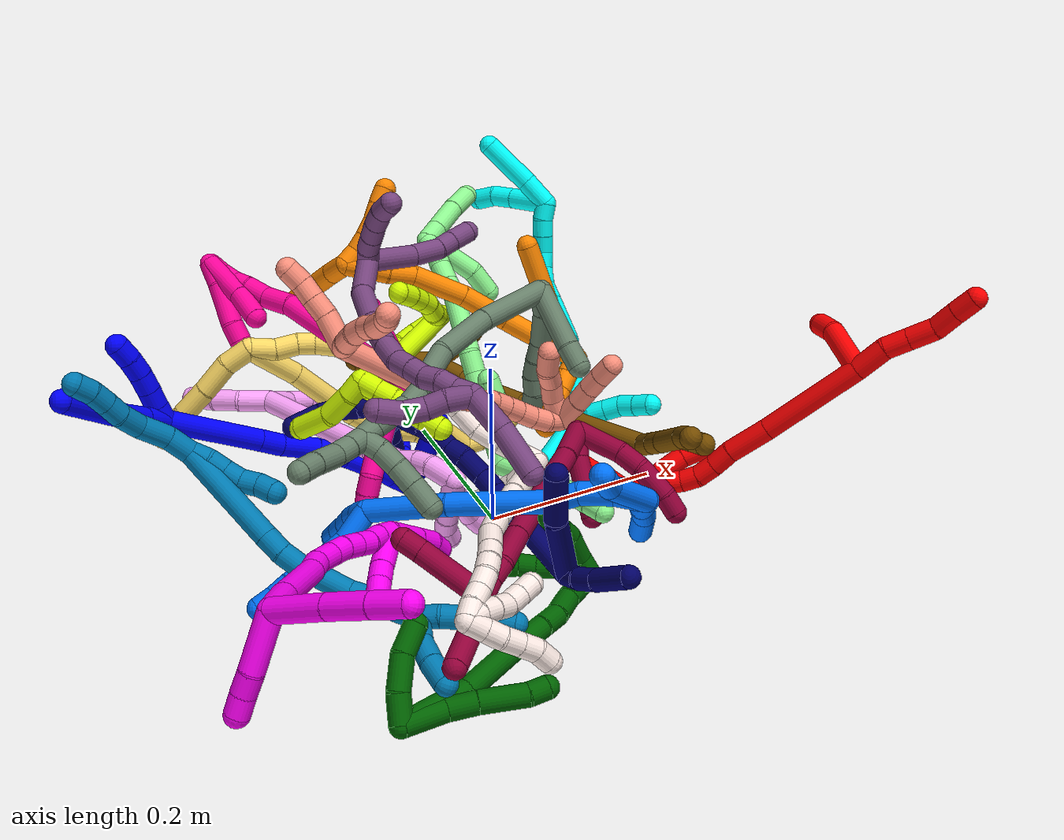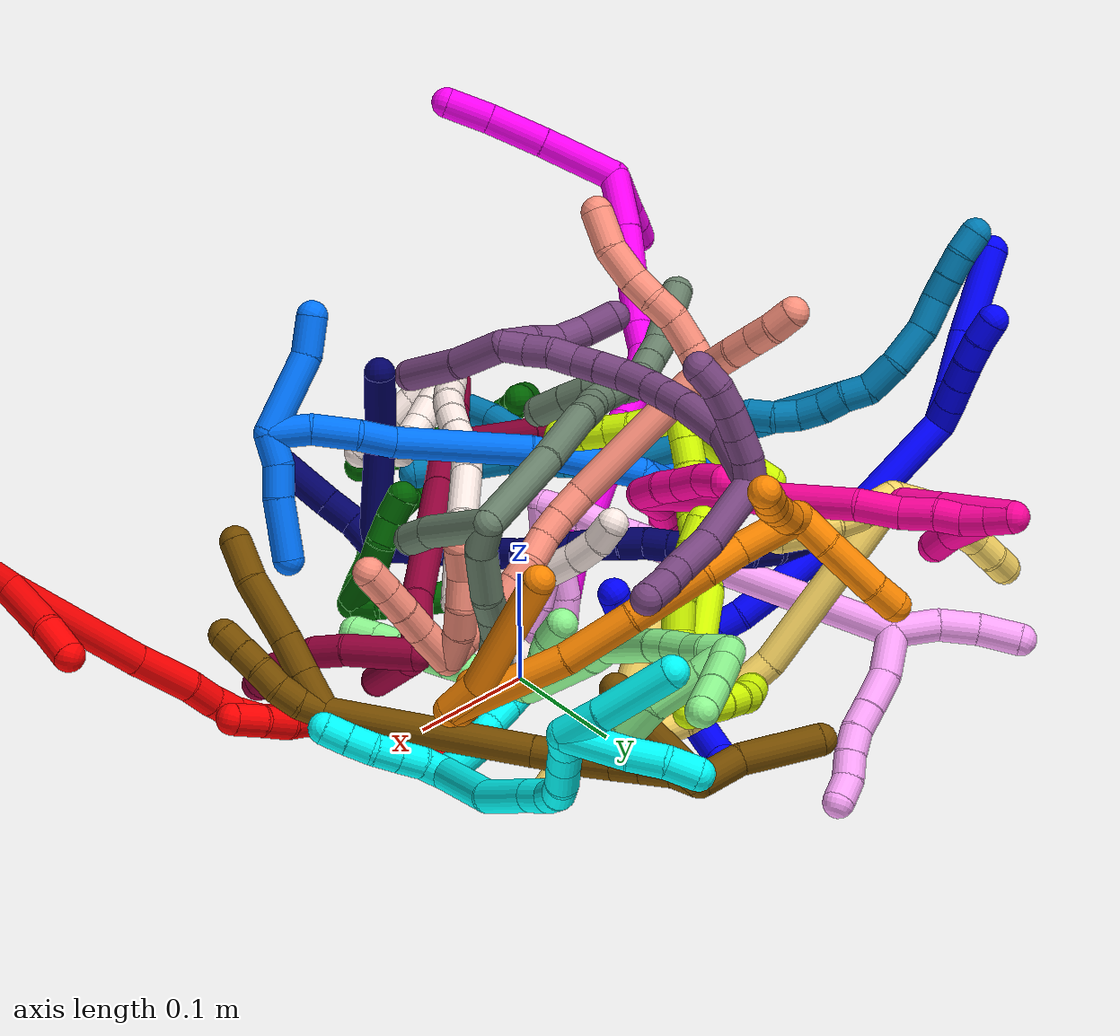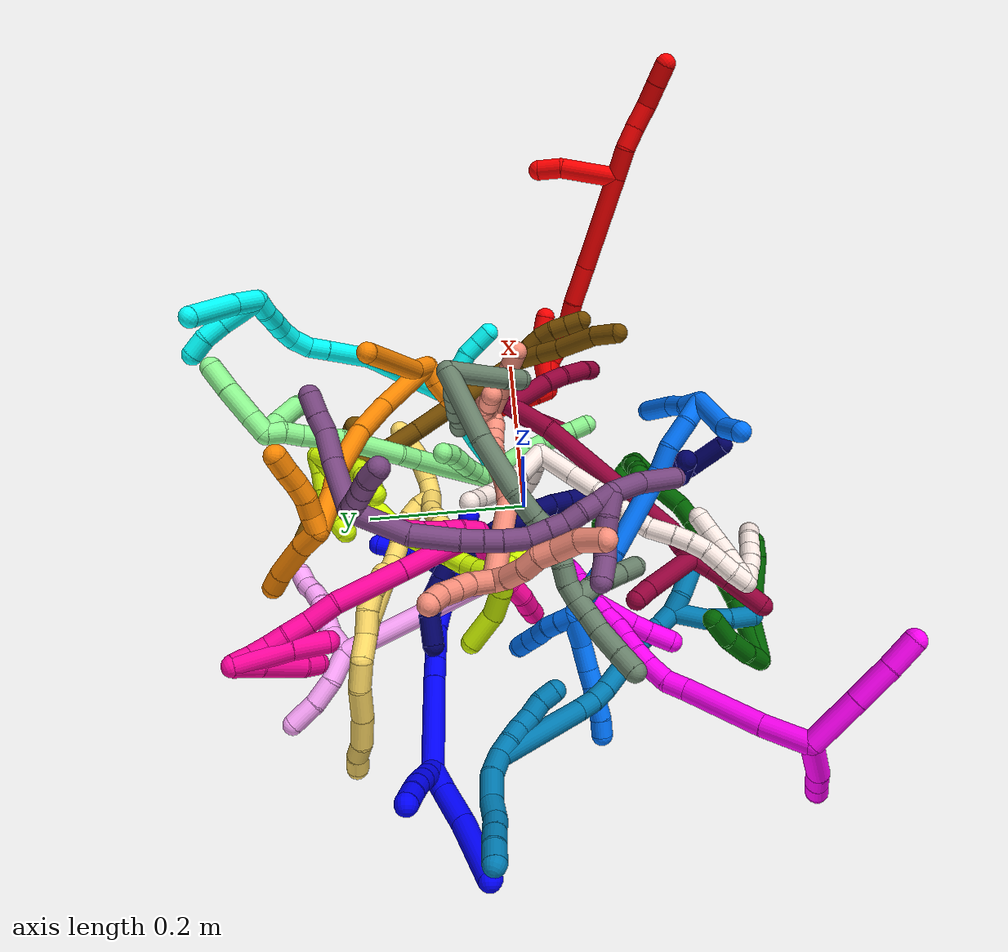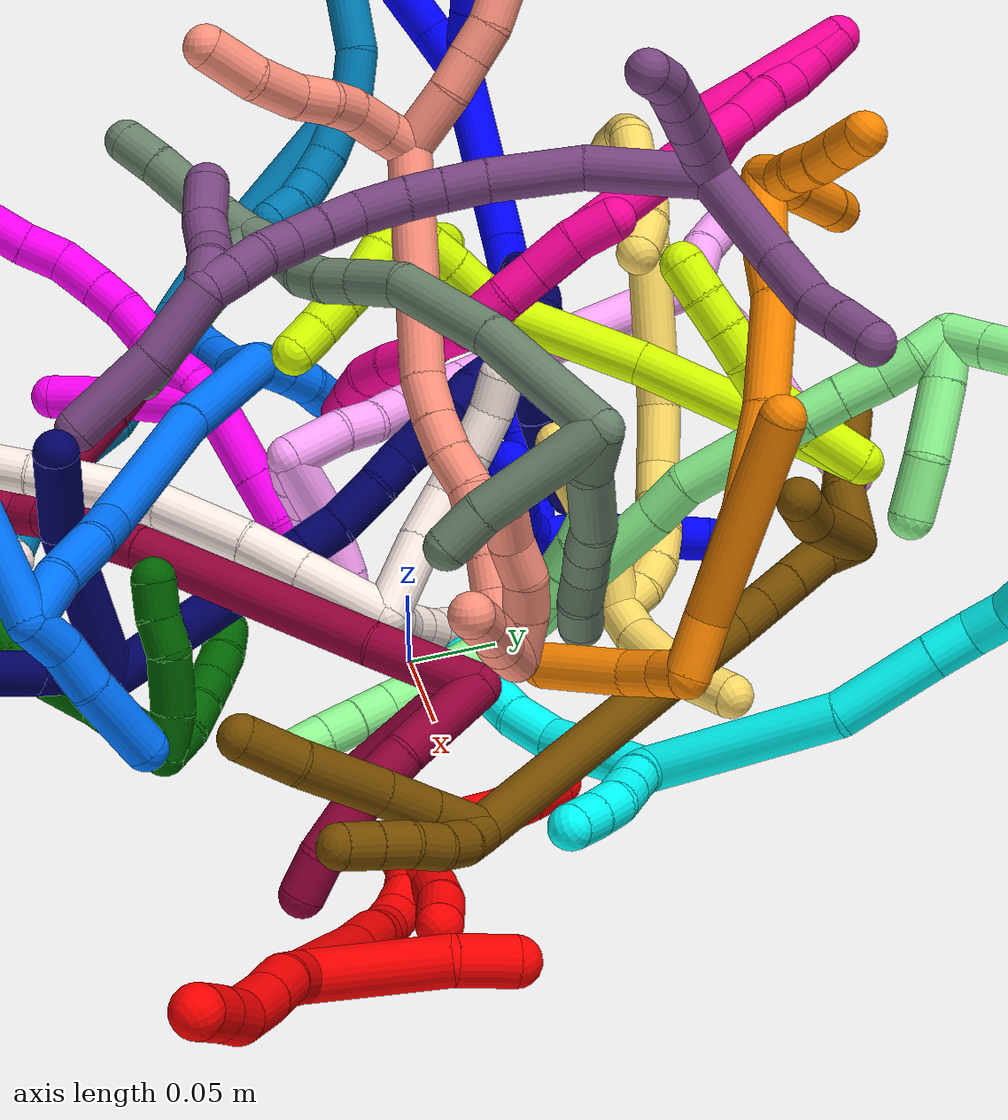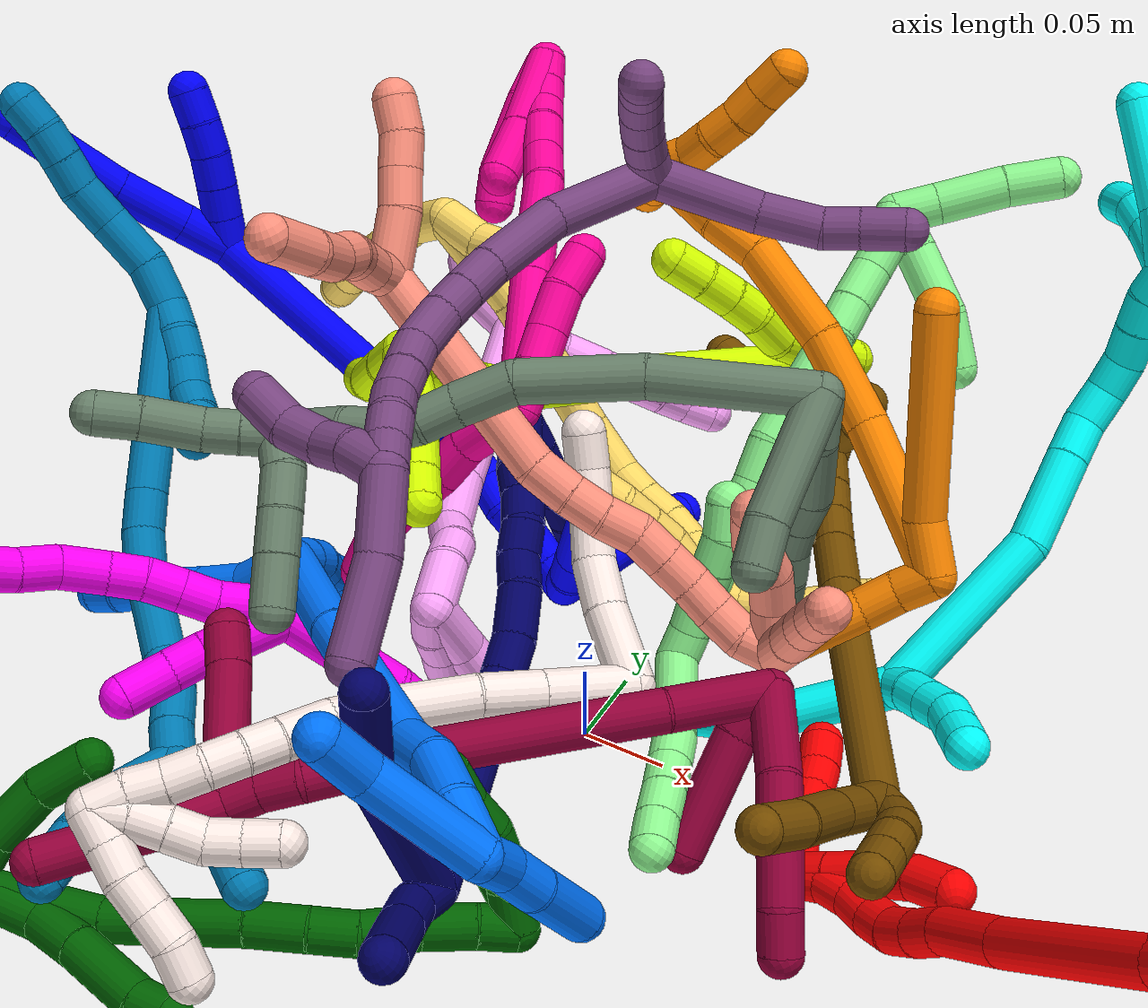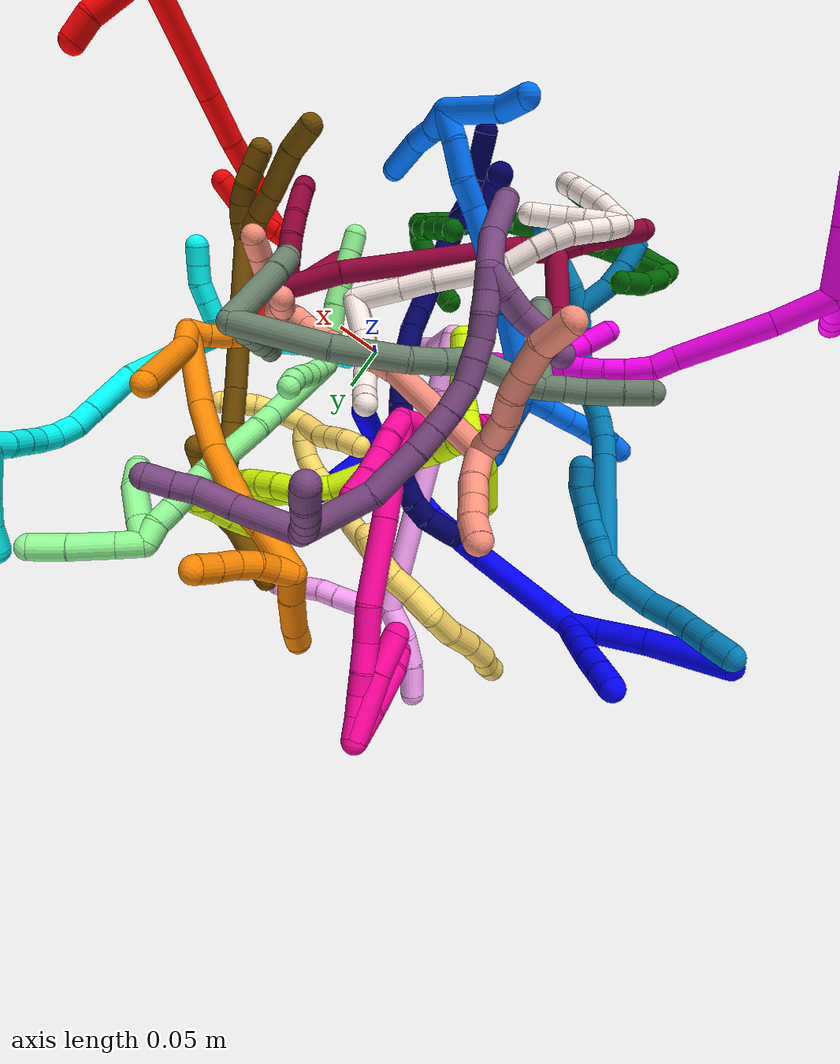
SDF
<sdf version="1.7">
 <world name="default">
  <plugin name="TubeGeneratorPlugin" filename="libtube_generator_plugin.so"/>
  <model name="photoneo_s_sensor">
   <static>1</static>
   <pose>0 0 2 1.57079 1.57079 3.14159</pose>
   <link name="link">
    <inertial><mass>0.1</mass></inertial>
    <sensor name="sensor" type="depth">
     <update_rate>30</update_rate>
     <camera>
      <horizontal_fov>1.22</horizontal_fov>
      <image><width>1920</width><height>1200</height><format>B8G8R8</format></image>
      <clip><near>0.1</near><far>4</far></clip>
      <depth_camera><output>points</output></depth_camera>
     </camera>
     <plugin name="camera_plugin" filename="libgazebo_ros_depth_camera.so">
      <baseline>0.2</baseline>
      <alwaysOn>1</alwaysOn>
      <updateRate>0.0</updateRate>
      <cameraName>camera_ir</cameraName>
      <imageTopicName>/camera/color/image_raw</imageTopicName>
      <cameraInfoTopicName>/camera/color/camera_info</cameraInfoTopicName>
      <depthImageTopicName>/camera/depth/image_raw</depthImageTopicName>
      <depthImageCameraInfoTopicName>/camera/depth/camera_info</depthImageCameraInfoTopicName>
      <pointCloudTopicName>/camera/depth/points</pointCloudTopicName>
      <frameName>fr_optical</frameName>
      <pointCloudCutoff>0.1</pointCloudCutoff>
      <pointCloudCutoffMax>2.0</pointCloudCutoffMax>
      <distortionK1>0</distortionK1>
      <distortionK2>0</distortionK2>
      <distortionK3>0</distortionK3>
      <distortionT1>0</distortionT1>
      <distortionT2>0</distortionT2>
      <CxPrime>0</CxPrime>
      <Cx>0</Cx>
      <Cy>0</Cy>
      <focalLength>0</focalLength>
      <hackBaseline>0</hackBaseline>
     </plugin>
    </sensor>
   </link>
  </model>
  <gravity>0 0 -9.8</gravity>
  <magnetic_field>6e-06 2.3e-05 -4.2e-05</magnetic_field>
  <atmosphere type="adiabatic"/>
  <physics name="default_physics" default="0" type="ode">
   <max_step_size>0.003</max_step_size>
   <real_time_factor>1</real_time_factor>
   <real_time_update_rate>1000</real_time_update_rate>
   <max_contacts>10000</max_contacts>
   <ode>
    <solver>
     <type>quick</type>
     <iters>100</iters>
     <sor>1.3</sor>
     <use_dynamic_moi_rescaling>0</use_dynamic_moi_rescaling>
    </solver>
    <constraints>
     <contact_max_correcting_vel>0</contact_max_correcting_vel>
     <contact_surface_layer>0.001</contact_surface_layer>
     <cfm>0</cfm>
     <erp>0.2</erp>
    </constraints>
   </ode>
  </physics>
  <scene><ambient>0.4 0.4 0.4 1</ambient><background>0.7 0.7 0.7 1</background><shadows>0</shadows></scene>
  <audio><device>default</device></audio>
  <spherical_coordinates>
   <surface_model>EARTH_WGS84</surface_model>
   <latitude_deg>0</latitude_deg>
   <longitude_deg>0</longitude_deg>
   <elevation>0</elevation>
   <heading_deg>0</heading_deg>
  </spherical_coordinates>
  <model name="bin">
   <static>1</static>
   <link name="bottom">
    <collision name="collision-bottom">
     <pose>0 0 -0.01 0 -0 0</pose>
     <geometry><box><size>0.8 0.6 0.02</size></box></geometry>
     <surface>
      <friction><ode><mu>100</mu><mu2>100</mu2></ode></friction>
      <contact><collide_bitmask>65535</collide_bitmask></contact>
     </surface>
    </collision>
   </link>
   <link name="west_wall">
    <collision name="collision-west_wall">
     <pose>-0.41 0 0.1 0 -0 0</pose>
     <geometry><box><size>0.02 0.6 0.2</size></box></geometry>
     <surface>
      <friction><ode><mu>100</mu><mu2>100</mu2></ode></friction>
      <contact><collide_bitmask>65535</collide_bitmask></contact>
     </surface>
    </collision>
   </link>
   <link name="east_wall">
    <collision name="collision-east_wall">
     <pose>0.41 0 0.1 0 -0 0</pose>
     <geometry><box><size>0.02 0.6 0.2</size></box></geometry>
     <surface>
      <friction><ode><mu>100</mu><mu2>100</mu2></ode></friction>
      <contact><collide_bitmask>65535</collide_bitmask></contact>
     </surface>
    </collision>
   </link>
   <link name="south_wall">
    <collision name="collision-south_wall">
     <pose>0 -0.31 0.1 0 -0 0</pose>
     <geometry><box><size>0.8 0.02 0.2</size></box></geometry>
     <surface>
      <friction><ode><mu>100</mu><mu2>100</mu2></ode></friction>
      <contact><collide_bitmask>65535</collide_bitmask></contact>
     </surface>
    </collision>
   </link>
   <link name="north_wall">
    <collision name="collision-north_wall">
     <pose>0 0.31 0.1 0 -0 0</pose>
     <geometry><box><size>0.8 0.02 0.2</size></box></geometry>
     <surface>
      <friction><ode><mu>100</mu><mu2>100</mu2></ode></friction>
      <contact><collide_bitmask>65535</collide_bitmask></contact>
     </surface>
    </collision>
   </link>
  </model>
  <model name="1">
   <static>0</static>
   <link name="1">
    <collision name="collision-cylinder-e_1_2_8">
     <pose>-0.009125 0.001832 0.013126 -0.1387 -0.60296 0.043192</pose>
     <geometry><cylinder><radius>0.0125</radius><length>0.032181</length></cylinder></geometry>
     <surface>
      <friction><ode><mu>1.16</mu><mu2>1.16</mu2><slip1>0</slip1><slip2>0</slip2></ode></friction>
      <contact><ode><kp>1e+06</kp><kd>1</kd><max_vel>0</max_vel><min_depth>0.001</min_depth></ode></contact>
     </surface>
    </collision>
    <visual name="visual-cylinder-e_1_2_8">
     <pose>-0.009125 0.001832 0.013126 -0.1387 -0.60296 0.043192</pose>
     <geometry><cylinder><radius>0.0125</radius><length>0.032181</length></cylinder></geometry>
     <material><ambient>0 0 1 1</ambient></material>
    </visual>
    <collision name="collision-cylinder-e_2_8_9">
     <pose>-0.031546 0.006201 0.043881 -0.142893 -0.641277 0.047526</pose>
     <geometry><cylinder><radius>0.0125</radius><length>0.044452</length></cylinder></geometry>
     <surface>
      <friction><ode><mu>1.16</mu><mu2>1.16</mu2><slip1>0</slip1><slip2>0</slip2></ode></friction>
      <contact><ode><kp>1e+06</kp><kd>1</kd><max_vel>0</max_vel><min_depth>0.001</min_depth></ode></contact>
     </surface>
    </collision>
    <visual name="visual-cylinder-e_2_8_9">
     <pose>-0.031546 0.006201 0.043881 -0.142893 -0.641277 0.047526</pose>
     <geometry><cylinder><radius>0.0125</radius><length>0.044452</length></cylinder></geometry>
     <material><ambient>0 0 1 1</ambient></material>
    </visual>
    <collision name="collision-cylinder-e_3_9_6">
     <pose>-0.066682 0.009643 0.090969 -0.030737 -0.637733 0.010148</pose>
     <geometry><cylinder><radius>0.0125</radius><length>0.073366</length></cylinder></geometry>
     <surface>
      <friction><ode><mu>1.16</mu><mu2>1.16</mu2><slip1>0</slip1><slip2>0</slip2></ode></friction>
      <contact><ode><kp>1e+06</kp><kd>1</kd><max_vel>0</max_vel><min_depth>0.001</min_depth></ode></contact>
     </surface>
    </collision>
    <visual name="visual-cylinder-e_3_9_6">
     <pose>-0.066682 0.009643 0.090969 -0.030737 -0.637733 0.010148</pose>
     <geometry><cylinder><radius>0.0125</radius><length>0.073366</length></cylinder></geometry>
     <material><ambient>0 0 1 1</ambient></material>
    </visual>
    <collision name="collision-cylinder-e_1_2_10">
     <pose>-0.005835 -0.006661 0.004646 0.961789 -0.623082 -0.332925</pose>
     <geometry><cylinder><radius>0.0125</radius><length>0.02</length></cylinder></geometry>
     <surface>
      <friction><ode><mu>1.16</mu><mu2>1.16</mu2><slip1>0</slip1><slip2>0</slip2></ode></friction>
      <contact><ode><kp>1e+06</kp><kd>1</kd><max_vel>0</max_vel><min_depth>0.001</min_depth></ode></contact>
     </surface>
    </collision>
    <visual name="visual-cylinder-e_1_2_10">
     <pose>-0.005835 -0.006661 0.004646 0.961789 -0.623082 -0.332925</pose>
     <geometry><cylinder><radius>0.0125</radius><length>0.02</length></cylinder></geometry>
     <material><ambient>0 0 1 1</ambient></material>
    </visual>
    <collision name="collision-cylinder-e_2_10_11">
     <pose>-0.017892 -0.019867 0.013588 0.989898 -0.67145 -0.372321</pose>
     <geometry><cylinder><radius>0.0125</radius><length>0.02</length></cylinder></geometry>
     <surface>
      <friction><ode><mu>1.16</mu><mu2>1.16</mu2><slip1>0</slip1><slip2>0</slip2></ode></friction>
      <contact><ode><kp>1e+06</kp><kd>1</kd><max_vel>0</max_vel><min_depth>0.001</min_depth></ode></contact>
     </surface>
    </collision>
    <visual name="visual-cylinder-e_2_10_11">
     <pose>-0.017892 -0.019867 0.013588 0.989898 -0.67145 -0.372321</pose>
     <geometry><cylinder><radius>0.0125</radius><length>0.02</length></cylinder></geometry>
     <material><ambient>0 0 1 1</ambient></material>
    </visual>
    <collision name="collision-cylinder-e_3_11_12">
     <pose>-0.0302 -0.032865 0.022499 0.949936 -0.654451 -0.345607</pose>
     <geometry><cylinder><radius>0.0125</radius><length>0.02</length></cylinder></geometry>
     <surface>
      <friction><ode><mu>1.16</mu><mu2>1.16</mu2><slip1>0</slip1><slip2>0</slip2></ode></friction>
      <contact><ode><kp>1e+06</kp><kd>1</kd><max_vel>0</max_vel><min_depth>0.001</min_depth></ode></contact>
     </surface>
    </collision>
    <visual name="visual-cylinder-e_3_11_12">
     <pose>-0.0302 -0.032865 0.022499 0.949936 -0.654451 -0.345607</pose>
     <geometry><cylinder><radius>0.0125</radius><length>0.02</length></cylinder></geometry>
     <material><ambient>0 0 1 1</ambient></material>
    </visual>
    <collision name="collision-cylinder-e_4_12_13">
     <pose>-0.042101 -0.045256 0.032678 0.817927 -0.620382 -0.276075</pose>
     <geometry><cylinder><radius>0.0125</radius><length>0.02</length></cylinder></geometry>
     <surface>
      <friction><ode><mu>1.16</mu><mu2>1.16</mu2><slip1>0</slip1><slip2>0</slip2></ode></friction>
      <contact><ode><kp>1e+06</kp><kd>1</kd><max_vel>0</max_vel><min_depth>0.001</min_depth></ode></contact>
     </surface>
    </collision>
    <visual name="visual-cylinder-e_4_12_13">
     <pose>-0.042101 -0.045256 0.032678 0.817927 -0.620382 -0.276075</pose>
     <geometry><cylinder><radius>0.0125</radius><length>0.02</length></cylinder></geometry>
     <material><ambient>0 0 1 1</ambient></material>
    </visual>
    <collision name="collision-cylinder-e_5_13_5">
     <pose>-0.052842 -0.05702 0.044705 0.733651 -0.515193 -0.201756</pose>
     <geometry><cylinder><radius>0.0125</radius><length>0.02</length></cylinder></geometry>
     <surface>
      <friction><ode><mu>1.16</mu><mu2>1.16</mu2><slip1>0</slip1><slip2>0</slip2></ode></friction>
      <contact><ode><kp>1e+06</kp><kd>1</kd><max_vel>0</max_vel><min_depth>0.001</min_depth></ode></contact>
     </surface>
    </collision>
    <visual name="visual-cylinder-e_5_13_5">
     <pose>-0.052842 -0.05702 0.044705 0.733651 -0.515193 -0.201756</pose>
     <geometry><cylinder><radius>0.0125</radius><length>0.02</length></cylinder></geometry>
     <material><ambient>0 0 1 1</ambient></material>
    </visual>
    <collision name="collision-cylinder-e_1_2_14">
     <pose>0.013713 0.009169 -0.053504 -2.97187 0.247445 -1.94175</pose>
     <geometry><cylinder><radius>0.0125</radius><length>0.111979</length></cylinder></geometry>
     <surface>
      <friction><ode><mu>1.16</mu><mu2>1.16</mu2><slip1>0</slip1><slip2>0</slip2></ode></friction>
      <contact><ode><kp>1e+06</kp><kd>1</kd><max_vel>0</max_vel><min_depth>0.001</min_depth></ode></contact>
     </surface>
    </collision>
    <visual name="visual-cylinder-e_1_2_14">
     <pose>0.013713 0.009169 -0.053504 -2.97187 0.247445 -1.94175</pose>
     <geometry><cylinder><radius>0.0125</radius><length>0.111979</length></cylinder></geometry>
     <material><ambient>0 0 1 1</ambient></material>
    </visual>
    <collision name="collision-cylinder-e_2_14_15">
     <pose>0.03063 0.020871 -0.119908 -2.94769 0.239042 -1.78016</pose>
     <geometry><cylinder><radius>0.0125</radius><length>0.027061</length></cylinder></geometry>
     <surface>
      <friction><ode><mu>1.16</mu><mu2>1.16</mu2><slip1>0</slip1><slip2>0</slip2></ode></friction>
      <contact><ode><kp>1e+06</kp><kd>1</kd><max_vel>0</max_vel><min_depth>0.001</min_depth></ode></contact>
     </surface>
    </collision>
    <visual name="visual-cylinder-e_2_14_15">
     <pose>0.03063 0.020871 -0.119908 -2.94769 0.239042 -1.78016</pose>
     <geometry><cylinder><radius>0.0125</radius><length>0.027061</length></cylinder></geometry>
     <material><ambient>0 0 1 1</ambient></material>
    </visual>
    <collision name="collision-cylinder-e_3_15_16">
     <pose>0.036812 0.026161 -0.154075 -3.01269 0.138 -1.63913</pose>
     <geometry><cylinder><radius>0.0125</radius><length>0.043302</length></cylinder></geometry>
     <surface>
      <friction><ode><mu>1.16</mu><mu2>1.16</mu2><slip1>0</slip1><slip2>0</slip2></ode></friction>
      <contact><ode><kp>1e+06</kp><kd>1</kd><max_vel>0</max_vel><min_depth>0.001</min_depth></ode></contact>
     </surface>
    </collision>
    <visual name="visual-cylinder-e_3_15_16">
     <pose>0.036812 0.026161 -0.154075 -3.01269 0.138 -1.63913</pose>
     <geometry><cylinder><radius>0.0125</radius><length>0.043302</length></cylinder></geometry>
     <material><ambient>0 0 1 1</ambient></material>
    </visual>
    <collision name="collision-cylinder-e_4_16_17">
     <pose>0.042003 0.03459 -0.192954 -2.82998 0.118984 -0.724876</pose>
     <geometry><cylinder><radius>0.0125</radius><length>0.03727</length></cylinder></geometry>
     <surface>
      <friction><ode><mu>1.16</mu><mu2>1.16</mu2><slip1>0</slip1><slip2>0</slip2></ode></friction>
      <contact><ode><kp>1e+06</kp><kd>1</kd><max_vel>0</max_vel><min_depth>0.001</min_depth></ode></contact>
     </surface>
    </collision>
    <visual name="visual-cylinder-e_4_16_17">
     <pose>0.042003 0.03459 -0.192954 -2.82998 0.118984 -0.724876</pose>
     <geometry><cylinder><radius>0.0125</radius><length>0.03727</length></cylinder></geometry>
     <material><ambient>0 0 1 1</ambient></material>
    </visual>
    <collision name="collision-cylinder-e_5_17_18">
     <pose>0.044309 0.04485 -0.219534 -2.66883 0.009392 -0.038986</pose>
     <geometry><cylinder><radius>0.0125</radius><length>0.020147</length></cylinder></geometry>
     <surface>
      <friction><ode><mu>1.16</mu><mu2>1.16</mu2><slip1>0</slip1><slip2>0</slip2></ode></friction>
      <contact><ode><kp>1e+06</kp><kd>1</kd><max_vel>0</max_vel><min_depth>0.001</min_depth></ode></contact>
     </surface>
    </collision>
    <visual name="visual-cylinder-e_5_17_18">
     <pose>0.044309 0.04485 -0.219534 -2.66883 0.009392 -0.038986</pose>
     <geometry><cylinder><radius>0.0125</radius><length>0.020147</length></cylinder></geometry>
     <material><ambient>0 0 1 1</ambient></material>
    </visual>
    <collision name="collision-cylinder-e_6_18_19">
     <pose>0.047212 0.052435 -0.237659 -2.82516 0.283597 -1.45979</pose>
     <geometry><cylinder><radius>0.0125</radius><length>0.020074</length></cylinder></geometry>
     <surface>
      <friction><ode><mu>1.16</mu><mu2>1.16</mu2><slip1>0</slip1><slip2>0</slip2></ode></friction>
      <contact><ode><kp>1e+06</kp><kd>1</kd><max_vel>0</max_vel><min_depth>0.001</min_depth></ode></contact>
     </surface>
    </collision>
    <visual name="visual-cylinder-e_6_18_19">
     <pose>0.047212 0.052435 -0.237659 -2.82516 0.283597 -1.45979</pose>
     <geometry><cylinder><radius>0.0125</radius><length>0.020074</length></cylinder></geometry>
     <material><ambient>0 0 1 1</ambient></material>
    </visual>
    <collision name="collision-cylinder-e_7_19_20">
     <pose>0.05361 0.059064 -0.255489 -2.74517 0.364636 -1.48528</pose>
     <geometry><cylinder><radius>0.0125</radius><length>0.020127</length></cylinder></geometry>
     <surface>
      <friction><ode><mu>1.16</mu><mu2>1.16</mu2><slip1>0</slip1><slip2>0</slip2></ode></friction>
      <contact><ode><kp>1e+06</kp><kd>1</kd><max_vel>0</max_vel><min_depth>0.001</min_depth></ode></contact>
     </surface>
    </collision>
    <visual name="visual-cylinder-e_7_19_20">
     <pose>0.05361 0.059064 -0.255489 -2.74517 0.364636 -1.48528</pose>
     <geometry><cylinder><radius>0.0125</radius><length>0.020127</length></cylinder></geometry>
     <material><ambient>0 0 1 1</ambient></material>
    </visual>
    <collision name="collision-cylinder-e_8_20_1">
     <pose>0.060459 0.066335 -0.27291 -2.74712 0.331391 -1.39361</pose>
     <geometry><cylinder><radius>0.0125</radius><length>0.020041</length></cylinder></geometry>
     <surface>
      <friction><ode><mu>1.16</mu><mu2>1.16</mu2><slip1>0</slip1><slip2>0</slip2></ode></friction>
      <contact><ode><kp>1e+06</kp><kd>1</kd><max_vel>0</max_vel><min_depth>0.001</min_depth></ode></contact>
     </surface>
    </collision>
    <visual name="visual-cylinder-e_8_20_1">
     <pose>0.060459 0.066335 -0.27291 -2.74712 0.331391 -1.39361</pose>
     <geometry><cylinder><radius>0.0125</radius><length>0.020041</length></cylinder></geometry>
     <material><ambient>0 0 1 1</ambient></material>
    </visual>
    <collision name="collision-cylinder-e_1_1_21">
     <pose>0.049784 0.067713 -0.285316 2.5874 -1.27136 -2.40577</pose>
     <geometry><cylinder><radius>0.0125</radius><length>0.029167</length></cylinder></geometry>
     <surface>
      <friction><ode><mu>1.16</mu><mu2>1.16</mu2><slip1>0</slip1><slip2>0</slip2></ode></friction>
      <contact><ode><kp>1e+06</kp><kd>1</kd><max_vel>0</max_vel><min_depth>0.001</min_depth></ode></contact>
     </surface>
    </collision>
    <visual name="visual-cylinder-e_1_1_21">
     <pose>0.049784 0.067713 -0.285316 2.5874 -1.27136 -2.40577</pose>
     <geometry><cylinder><radius>0.0125</radius><length>0.029167</length></cylinder></geometry>
     <material><ambient>0 0 1 1</ambient></material>
    </visual>
    <collision name="collision-cylinder-e_2_21_22">
     <pose>0.025732 0.060612 -0.290329 1.84398 -1.10997 -1.37072</pose>
     <geometry><cylinder><radius>0.0125</radius><length>0.022592</length></cylinder></geometry>
     <surface>
      <friction><ode><mu>1.16</mu><mu2>1.16</mu2><slip1>0</slip1><slip2>0</slip2></ode></friction>
      <contact><ode><kp>1e+06</kp><kd>1</kd><max_vel>0</max_vel><min_depth>0.001</min_depth></ode></contact>
     </surface>
    </collision>
    <visual name="visual-cylinder-e_2_21_22">
     <pose>0.025732 0.060612 -0.290329 1.84398 -1.10997 -1.37072</pose>
     <geometry><cylinder><radius>0.0125</radius><length>0.022592</length></cylinder></geometry>
     <material><ambient>0 0 1 1</ambient></material>
    </visual>
    <collision name="collision-cylinder-e_3_22_4">
     <pose>-0.005973 0.045387 -0.294492 1.8348 -1.10835 -1.35964</pose>
     <geometry><cylinder><radius>0.0125</radius><length>0.048241</length></cylinder></geometry>
     <surface>
      <friction><ode><mu>1.16</mu><mu2>1.16</mu2><slip1>0</slip1><slip2>0</slip2></ode></friction>
      <contact><ode><kp>1e+06</kp><kd>1</kd><max_vel>0</max_vel><min_depth>0.001</min_depth></ode></contact>
     </surface>
    </collision>
    <visual name="visual-cylinder-e_3_22_4">
     <pose>-0.005973 0.045387 -0.294492 1.8348 -1.10835 -1.35964</pose>
     <geometry><cylinder><radius>0.0125</radius><length>0.048241</length></cylinder></geometry>
     <material><ambient>0 0 1 1</ambient></material>
    </visual>
    <collision name="collision-cylinder-e_1_1_23">
     <pose>0.077363 0.046111 -0.288539 1.85153 0.502318 0.657296</pose>
     <geometry><cylinder><radius>0.0125</radius><length>0.056678</length></cylinder></geometry>
     <surface>
      <friction><ode><mu>1.16</mu><mu2>1.16</mu2><slip1>0</slip1><slip2>0</slip2></ode></friction>
      <contact><ode><kp>1e+06</kp><kd>1</kd><max_vel>0</max_vel><min_depth>0.001</min_depth></ode></contact>
     </surface>
    </collision>
    <visual name="visual-cylinder-e_1_1_23">
     <pose>0.077363 0.046111 -0.288539 1.85153 0.502318 0.657296</pose>
     <geometry><cylinder><radius>0.0125</radius><length>0.056678</length></cylinder></geometry>
     <material><ambient>0 0 1 1</ambient></material>
    </visual>
    <collision name="collision-cylinder-e_2_23_3">
     <pose>0.102591 0.004992 -0.301531 1.91116 0.564274 0.77848</pose>
     <geometry><cylinder><radius>0.0125</radius><length>0.043322</length></cylinder></geometry>
     <surface>
      <friction><ode><mu>1.16</mu><mu2>1.16</mu2><slip1>0</slip1><slip2>0</slip2></ode></friction>
      <contact><ode><kp>1e+06</kp><kd>1</kd><max_vel>0</max_vel><min_depth>0.001</min_depth></ode></contact>
     </surface>
    </collision>
    <visual name="visual-cylinder-e_2_23_3">
     <pose>0.102591 0.004992 -0.301531 1.91116 0.564274 0.77848</pose>
     <geometry><cylinder><radius>0.0125</radius><length>0.043322</length></cylinder></geometry>
     <material><ambient>0 0 1 1</ambient></material>
    </visual>
    <collision name="collision-sphere-3">
     <pose>0.114176 -0.012261 -0.307641 0 -0 0</pose>
     <geometry><sphere><radius>0.0125</radius></sphere></geometry>
     <surface>
      <friction><ode><mu>1.16</mu><mu2>1.16</mu2><slip1>0</slip1><slip2>0</slip2></ode></friction>
      <contact><ode><kp>1e+06</kp><kd>1</kd><max_vel>0</max_vel><min_depth>0.001</min_depth></ode></contact>
     </surface>
    </collision>
    <visual name="visual-sphere-3">
     <pose>0.114176 -0.012261 -0.307641 0 -0 0</pose>
     <geometry><sphere><radius>0.0125</radius></sphere></geometry>
     <material><ambient>0 0 1 1</ambient></material>
    </visual>
    <collision name="collision-sphere-23">
     <pose>0.091007 0.022245 -0.295421 0 -0 0</pose>
     <geometry><sphere><radius>0.0125</radius></sphere></geometry>
     <surface>
      <friction><ode><mu>1.16</mu><mu2>1.16</mu2><slip1>0</slip1><slip2>0</slip2></ode></friction>
      <contact><ode><kp>1e+06</kp><kd>1</kd><max_vel>0</max_vel><min_depth>0.001</min_depth></ode></contact>
     </surface>
    </collision>
    <visual name="visual-sphere-23">
     <pose>0.091007 0.022245 -0.295421 0 -0 0</pose>
     <geometry><sphere><radius>0.0125</radius></sphere></geometry>
     <material><ambient>0 0 1 1</ambient></material>
    </visual>
    <collision name="collision-sphere-4">
     <pose>-0.02756 0.034999 -0.2973 0 -0 0</pose>
     <geometry><sphere><radius>0.0125</radius></sphere></geometry>
     <surface>
      <friction><ode><mu>1.16</mu><mu2>1.16</mu2><slip1>0</slip1><slip2>0</slip2></ode></friction>
      <contact><ode><kp>1e+06</kp><kd>1</kd><max_vel>0</max_vel><min_depth>0.001</min_depth></ode></contact>
     </surface>
    </collision>
    <visual name="visual-sphere-4">
     <pose>-0.02756 0.034999 -0.2973 0 -0 0</pose>
     <geometry><sphere><radius>0.0125</radius></sphere></geometry>
     <material><ambient>0 0 1 1</ambient></material>
    </visual>
    <collision name="collision-sphere-22">
     <pose>0.015614 0.055775 -0.291684 0 -0 0</pose>
     <geometry><sphere><radius>0.0125</radius></sphere></geometry>
     <surface>
      <friction><ode><mu>1.16</mu><mu2>1.16</mu2><slip1>0</slip1><slip2>0</slip2></ode></friction>
      <contact><ode><kp>1e+06</kp><kd>1</kd><max_vel>0</max_vel><min_depth>0.001</min_depth></ode></contact>
     </surface>
    </collision>
    <visual name="visual-sphere-22">
     <pose>0.015614 0.055775 -0.291684 0 -0 0</pose>
     <geometry><sphere><radius>0.0125</radius></sphere></geometry>
     <material><ambient>0 0 1 1</ambient></material>
    </visual>
    <collision name="collision-sphere-21">
     <pose>0.035849 0.065449 -0.288974 0 -0 0</pose>
     <geometry><sphere><radius>0.0125</radius></sphere></geometry>
     <surface>
      <friction><ode><mu>1.16</mu><mu2>1.16</mu2><slip1>0</slip1><slip2>0</slip2></ode></friction>
      <contact><ode><kp>1e+06</kp><kd>1</kd><max_vel>0</max_vel><min_depth>0.001</min_depth></ode></contact>
     </surface>
    </collision>
    <visual name="visual-sphere-21">
     <pose>0.035849 0.065449 -0.288974 0 -0 0</pose>
     <geometry><sphere><radius>0.0125</radius></sphere></geometry>
     <material><ambient>0 0 1 1</ambient></material>
    </visual>
    <collision name="collision-sphere-1">
     <pose>0.063719 0.069977 -0.281657 0 -0 0</pose>
     <geometry><sphere><radius>0.0125</radius></sphere></geometry>
     <surface>
      <friction><ode><mu>1.16</mu><mu2>1.16</mu2><slip1>0</slip1><slip2>0</slip2></ode></friction>
      <contact><ode><kp>1e+06</kp><kd>1</kd><max_vel>0</max_vel><min_depth>0.001</min_depth></ode></contact>
     </surface>
    </collision>
    <visual name="visual-sphere-1">
     <pose>0.063719 0.069977 -0.281657 0 -0 0</pose>
     <geometry><sphere><radius>0.0125</radius></sphere></geometry>
     <material><ambient>0 0 1 1</ambient></material>
    </visual>
    <collision name="collision-sphere-11">
     <pose>-0.024113 -0.026412 0.017884 0 -0 0</pose>
     <geometry><sphere><radius>0.0125</radius></sphere></geometry>
     <surface>
      <friction><ode><mu>1.16</mu><mu2>1.16</mu2><slip1>0</slip1><slip2>0</slip2></ode></friction>
      <contact><ode><kp>1e+06</kp><kd>1</kd><max_vel>0</max_vel><min_depth>0.001</min_depth></ode></contact>
     </surface>
    </collision>
    <visual name="visual-sphere-11">
     <pose>-0.024113 -0.026412 0.017884 0 -0 0</pose>
     <geometry><sphere><radius>0.0125</radius></sphere></geometry>
     <material><ambient>0 0 1 1</ambient></material>
    </visual>
    <collision name="collision-sphere-10">
     <pose>-0.011671 -0.013322 0.009291 0 -0 0</pose>
     <geometry><sphere><radius>0.0125</radius></sphere></geometry>
     <surface>
      <friction><ode><mu>1.16</mu><mu2>1.16</mu2><slip1>0</slip1><slip2>0</slip2></ode></friction>
      <contact><ode><kp>1e+06</kp><kd>1</kd><max_vel>0</max_vel><min_depth>0.001</min_depth></ode></contact>
     </surface>
    </collision>
    <visual name="visual-sphere-10">
     <pose>-0.011671 -0.013322 0.009291 0 -0 0</pose>
     <geometry><sphere><radius>0.0125</radius></sphere></geometry>
     <material><ambient>0 0 1 1</ambient></material>
    </visual>
    <collision name="collision-sphere-6">
     <pose>-0.088522 0.010549 0.120428 0 -0 0</pose>
     <geometry><sphere><radius>0.0125</radius></sphere></geometry>
     <surface>
      <friction><ode><mu>1.16</mu><mu2>1.16</mu2><slip1>0</slip1><slip2>0</slip2></ode></friction>
      <contact><ode><kp>1e+06</kp><kd>1</kd><max_vel>0</max_vel><min_depth>0.001</min_depth></ode></contact>
     </surface>
    </collision>
    <visual name="visual-sphere-6">
     <pose>-0.088522 0.010549 0.120428 0 -0 0</pose>
     <geometry><sphere><radius>0.0125</radius></sphere></geometry>
     <material><ambient>0 0 1 1</ambient></material>
    </visual>
    <collision name="collision-sphere-9">
     <pose>-0.044842 0.008737 0.06151 0 -0 0</pose>
     <geometry><sphere><radius>0.0125</radius></sphere></geometry>
     <surface>
      <friction><ode><mu>1.16</mu><mu2>1.16</mu2><slip1>0</slip1><slip2>0</slip2></ode></friction>
      <contact><ode><kp>1e+06</kp><kd>1</kd><max_vel>0</max_vel><min_depth>0.001</min_depth></ode></contact>
     </surface>
    </collision>
    <visual name="visual-sphere-9">
     <pose>-0.044842 0.008737 0.06151 0 -0 0</pose>
     <geometry><sphere><radius>0.0125</radius></sphere></geometry>
     <material><ambient>0 0 1 1</ambient></material>
    </visual>
    <collision name="collision-sphere-2">
     <geometry><sphere><radius>0.0125</radius></sphere></geometry>
     <surface>
      <friction><ode><mu>1.16</mu><mu2>1.16</mu2><slip1>0</slip1><slip2>0</slip2></ode></friction>
      <contact><ode><kp>1e+06</kp><kd>1</kd><max_vel>0</max_vel><min_depth>0.001</min_depth></ode></contact>
     </surface>
    </collision>
    <visual name="visual-sphere-2">
     <geometry><sphere><radius>0.0125</radius></sphere></geometry>
     <material><ambient>0 0 1 1</ambient></material>
    </visual>
    <collision name="collision-sphere-19">
     <pose>0.050021 0.055433 -0.246817 0 -0 0</pose>
     <geometry><sphere><radius>0.0125</radius></sphere></geometry>
     <surface>
      <friction><ode><mu>1.16</mu><mu2>1.16</mu2><slip1>0</slip1><slip2>0</slip2></ode></friction>
      <contact><ode><kp>1e+06</kp><kd>1</kd><max_vel>0</max_vel><min_depth>0.001</min_depth></ode></contact>
     </surface>
    </collision>
    <visual name="visual-sphere-19">
     <pose>0.050021 0.055433 -0.246817 0 -0 0</pose>
     <geometry><sphere><radius>0.0125</radius></sphere></geometry>
     <material><ambient>0 0 1 1</ambient></material>
    </visual>
    <collision name="collision-sphere-8">
     <pose>-0.018249 0.003665 0.026252 0 -0 0</pose>
     <geometry><sphere><radius>0.0125</radius></sphere></geometry>
     <surface>
      <friction><ode><mu>1.16</mu><mu2>1.16</mu2><slip1>0</slip1><slip2>0</slip2></ode></friction>
      <contact><ode><kp>1e+06</kp><kd>1</kd><max_vel>0</max_vel><min_depth>0.001</min_depth></ode></contact>
     </surface>
    </collision>
    <visual name="visual-sphere-8">
     <pose>-0.018249 0.003665 0.026252 0 -0 0</pose>
     <geometry><sphere><radius>0.0125</radius></sphere></geometry>
     <material><ambient>0 0 1 1</ambient></material>
    </visual>
    <collision name="collision-sphere-12">
     <pose>-0.036288 -0.039318 0.027115 0 -0 0</pose>
     <geometry><sphere><radius>0.0125</radius></sphere></geometry>
     <surface>
      <friction><ode><mu>1.16</mu><mu2>1.16</mu2><slip1>0</slip1><slip2>0</slip2></ode></friction>
      <contact><ode><kp>1e+06</kp><kd>1</kd><max_vel>0</max_vel><min_depth>0.001</min_depth></ode></contact>
     </surface>
    </collision>
    <visual name="visual-sphere-12">
     <pose>-0.036288 -0.039318 0.027115 0 -0 0</pose>
     <geometry><sphere><radius>0.0125</radius></sphere></geometry>
     <material><ambient>0 0 1 1</ambient></material>
    </visual>
    <collision name="collision-sphere-13">
     <pose>-0.047915 -0.051193 0.038241 0 -0 0</pose>
     <geometry><sphere><radius>0.0125</radius></sphere></geometry>
     <surface>
      <friction><ode><mu>1.16</mu><mu2>1.16</mu2><slip1>0</slip1><slip2>0</slip2></ode></friction>
      <contact><ode><kp>1e+06</kp><kd>1</kd><max_vel>0</max_vel><min_depth>0.001</min_depth></ode></contact>
     </surface>
    </collision>
    <visual name="visual-sphere-13">
     <pose>-0.047915 -0.051193 0.038241 0 -0 0</pose>
     <geometry><sphere><radius>0.0125</radius></sphere></geometry>
     <material><ambient>0 0 1 1</ambient></material>
    </visual>
    <collision name="collision-sphere-5">
     <pose>-0.057769 -0.062846 0.051168 0 -0 0</pose>
     <geometry><sphere><radius>0.0125</radius></sphere></geometry>
     <surface>
      <friction><ode><mu>1.16</mu><mu2>1.16</mu2><slip1>0</slip1><slip2>0</slip2></ode></friction>
      <contact><ode><kp>1e+06</kp><kd>1</kd><max_vel>0</max_vel><min_depth>0.001</min_depth></ode></contact>
     </surface>
    </collision>
    <visual name="visual-sphere-5">
     <pose>-0.057769 -0.062846 0.051168 0 -0 0</pose>
     <geometry><sphere><radius>0.0125</radius></sphere></geometry>
     <material><ambient>0 0 1 1</ambient></material>
    </visual>
    <collision name="collision-sphere-14">
     <pose>0.027427 0.018338 -0.107009 0 -0 0</pose>
     <geometry><sphere><radius>0.0125</radius></sphere></geometry>
     <surface>
      <friction><ode><mu>1.16</mu><mu2>1.16</mu2><slip1>0</slip1><slip2>0</slip2></ode></friction>
      <contact><ode><kp>1e+06</kp><kd>1</kd><max_vel>0</max_vel><min_depth>0.001</min_depth></ode></contact>
     </surface>
    </collision>
    <visual name="visual-sphere-14">
     <pose>0.027427 0.018338 -0.107009 0 -0 0</pose>
     <geometry><sphere><radius>0.0125</radius></sphere></geometry>
     <material><ambient>0 0 1 1</ambient></material>
    </visual>
    <collision name="collision-sphere-15">
     <pose>0.033834 0.023404 -0.132808 0 -0 0</pose>
     <geometry><sphere><radius>0.0125</radius></sphere></geometry>
     <surface>
      <friction><ode><mu>1.16</mu><mu2>1.16</mu2><slip1>0</slip1><slip2>0</slip2></ode></friction>
      <contact><ode><kp>1e+06</kp><kd>1</kd><max_vel>0</max_vel><min_depth>0.001</min_depth></ode></contact>
     </surface>
    </collision>
    <visual name="visual-sphere-15">
     <pose>0.033834 0.023404 -0.132808 0 -0 0</pose>
     <geometry><sphere><radius>0.0125</radius></sphere></geometry>
     <material><ambient>0 0 1 1</ambient></material>
    </visual>
    <collision name="collision-sphere-16">
     <pose>0.039791 0.028917 -0.175342 0 -0 0</pose>
     <geometry><sphere><radius>0.0125</radius></sphere></geometry>
     <surface>
      <friction><ode><mu>1.16</mu><mu2>1.16</mu2><slip1>0</slip1><slip2>0</slip2></ode></friction>
      <contact><ode><kp>1e+06</kp><kd>1</kd><max_vel>0</max_vel><min_depth>0.001</min_depth></ode></contact>
     </surface>
    </collision>
    <visual name="visual-sphere-16">
     <pose>0.039791 0.028917 -0.175342 0 -0 0</pose>
     <geometry><sphere><radius>0.0125</radius></sphere></geometry>
     <material><ambient>0 0 1 1</ambient></material>
    </visual>
    <collision name="collision-sphere-17">
     <pose>0.044215 0.040263 -0.210566 0 -0 0</pose>
     <geometry><sphere><radius>0.0125</radius></sphere></geometry>
     <surface>
      <friction><ode><mu>1.16</mu><mu2>1.16</mu2><slip1>0</slip1><slip2>0</slip2></ode></friction>
      <contact><ode><kp>1e+06</kp><kd>1</kd><max_vel>0</max_vel><min_depth>0.001</min_depth></ode></contact>
     </surface>
    </collision>
    <visual name="visual-sphere-17">
     <pose>0.044215 0.040263 -0.210566 0 -0 0</pose>
     <geometry><sphere><radius>0.0125</radius></sphere></geometry>
     <material><ambient>0 0 1 1</ambient></material>
    </visual>
    <collision name="collision-sphere-18">
     <pose>0.044404 0.049436 -0.228502 0 -0 0</pose>
     <geometry><sphere><radius>0.0125</radius></sphere></geometry>
     <surface>
      <friction><ode><mu>1.16</mu><mu2>1.16</mu2><slip1>0</slip1><slip2>0</slip2></ode></friction>
      <contact><ode><kp>1e+06</kp><kd>1</kd><max_vel>0</max_vel><min_depth>0.001</min_depth></ode></contact>
     </surface>
    </collision>
    <visual name="visual-sphere-18">
     <pose>0.044404 0.049436 -0.228502 0 -0 0</pose>
     <geometry><sphere><radius>0.0125</radius></sphere></geometry>
     <material><ambient>0 0 1 1</ambient></material>
    </visual>
    <collision name="collision-sphere-20">
     <pose>0.057198 0.062694 -0.264162 0 -0 0</pose>
     <geometry><sphere><radius>0.0125</radius></sphere></geometry>
     <surface>
      <friction><ode><mu>1.16</mu><mu2>1.16</mu2><slip1>0</slip1><slip2>0</slip2></ode></friction>
      <contact><ode><kp>1e+06</kp><kd>1</kd><max_vel>0</max_vel><min_depth>0.001</min_depth></ode></contact>
     </surface>
    </collision>
    <visual name="visual-sphere-20">
     <pose>0.057198 0.062694 -0.264162 0 -0 0</pose>
     <geometry><sphere><radius>0.0125</radius></sphere></geometry>
     <material><ambient>0 0 1 1</ambient></material>
    </visual>
    <inertial>
     <pose>0.014219 0.019547 -0.119999 0 -0 0</pose>
     <mass>0.75</mass>
     <inertia>
      <ixx>-0.000106</ixx>
      <ixy>0</ixy>
      <ixz>0</ixz>
      <iyy>-1.6e-05</iyy>
      <iyz>0</iyz>
      <izz>-6e-06</izz>
     </inertia>
    </inertial>
   </link>
   <pose>-0.325611 0.124406 0.155898 -1.24343 0.934442 1.79947</pose>
  </model>
  <model name="2">
   <static>0</static>
   <link name="2">
    <collision name="collision-cylinder-e_1_2_8">
     <pose>0.014309 -0.002219 0.012293 0.178586 0.853105 0.081331</pose>
     <geometry><cylinder><radius>0.0125</radius><length>0.03799</length></cylinder></geometry>
     <surface>
      <friction><ode><mu>1.16</mu><mu2>1.16</mu2><slip1>0</slip1><slip2>0</slip2></ode></friction>
      <contact><ode><kp>1e+06</kp><kd>1</kd><max_vel>0</max_vel><min_depth>0.001</min_depth></ode></contact>
     </surface>
    </collision>
    <visual name="visual-cylinder-e_1_2_8">
     <pose>0.014309 -0.002219 0.012293 0.178586 0.853105 0.081331</pose>
     <geometry><cylinder><radius>0.0125</radius><length>0.03799</length></cylinder></geometry>
     <material><ambient>1 0 0 1</ambient></material>
    </visual>
    <collision name="collision-cylinder-e_2_8_9">
     <pose>0.036021 -0.007468 0.035719 0.265768 0.570415 0.078345</pose>
     <geometry><cylinder><radius>0.0125</radius><length>0.027416</length></cylinder></geometry>
     <surface>
      <friction><ode><mu>1.16</mu><mu2>1.16</mu2><slip1>0</slip1><slip2>0</slip2></ode></friction>
      <contact><ode><kp>1e+06</kp><kd>1</kd><max_vel>0</max_vel><min_depth>0.001</min_depth></ode></contact>
     </surface>
    </collision>
    <visual name="visual-cylinder-e_2_8_9">
     <pose>0.036021 -0.007468 0.035719 0.265768 0.570415 0.078345</pose>
     <geometry><cylinder><radius>0.0125</radius><length>0.027416</length></cylinder></geometry>
     <material><ambient>1 0 0 1</ambient></material>
    </visual>
    <collision name="collision-cylinder-e_3_9_10">
     <pose>0.051816 -0.012807 0.0595 0.180475 0.578346 0.053827</pose>
     <geometry><cylinder><radius>0.0125</radius><length>0.030708</length></cylinder></geometry>
     <surface>
      <friction><ode><mu>1.16</mu><mu2>1.16</mu2><slip1>0</slip1><slip2>0</slip2></ode></friction>
      <contact><ode><kp>1e+06</kp><kd>1</kd><max_vel>0</max_vel><min_depth>0.001</min_depth></ode></contact>
     </surface>
    </collision>
    <visual name="visual-cylinder-e_3_9_10">
     <pose>0.051816 -0.012807 0.0595 0.180475 0.578346 0.053827</pose>
     <geometry><cylinder><radius>0.0125</radius><length>0.030708</length></cylinder></geometry>
     <material><ambient>1 0 0 1</ambient></material>
    </visual>
    <collision name="collision-cylinder-e_4_10_11">
     <pose>0.071013 -0.014671 0.081366 -0.048081 0.863913 -0.022168</pose>
     <geometry><cylinder><radius>0.0125</radius><length>0.028417</length></cylinder></geometry>
     <surface>
      <friction><ode><mu>1.16</mu><mu2>1.16</mu2><slip1>0</slip1><slip2>0</slip2></ode></friction>
      <contact><ode><kp>1e+06</kp><kd>1</kd><max_vel>0</max_vel><min_depth>0.001</min_depth></ode></contact>
     </surface>
    </collision>
    <visual name="visual-cylinder-e_4_10_11">
     <pose>0.071013 -0.014671 0.081366 -0.048081 0.863913 -0.022168</pose>
     <geometry><cylinder><radius>0.0125</radius><length>0.028417</length></cylinder></geometry>
     <material><ambient>1 0 0 1</ambient></material>
    </visual>
    <collision name="collision-cylinder-e_5_11_6">
     <pose>0.09126 -0.014049 0.099125 -0.020875 0.835295 -0.009264</pose>
     <geometry><cylinder><radius>0.0125</radius><length>0.025469</length></cylinder></geometry>
     <surface>
      <friction><ode><mu>1.16</mu><mu2>1.16</mu2><slip1>0</slip1><slip2>0</slip2></ode></friction>
      <contact><ode><kp>1e+06</kp><kd>1</kd><max_vel>0</max_vel><min_depth>0.001</min_depth></ode></contact>
     </surface>
    </collision>
    <visual name="visual-cylinder-e_5_11_6">
     <pose>0.09126 -0.014049 0.099125 -0.020875 0.835295 -0.009264</pose>
     <geometry><cylinder><radius>0.0125</radius><length>0.025469</length></cylinder></geometry>
     <material><ambient>1 0 0 1</ambient></material>
    </visual>
    <collision name="collision-cylinder-e_1_2_12">
     <pose>0.012817 -0.020977 -0.025379 2.45086 0.371212 0.962008</pose>
     <geometry><cylinder><radius>0.0125</radius><length>0.070665</length></cylinder></geometry>
     <surface>
      <friction><ode><mu>1.16</mu><mu2>1.16</mu2><slip1>0</slip1><slip2>0</slip2></ode></friction>
      <contact><ode><kp>1e+06</kp><kd>1</kd><max_vel>0</max_vel><min_depth>0.001</min_depth></ode></contact>
     </surface>
    </collision>
    <visual name="visual-cylinder-e_1_2_12">
     <pose>0.012817 -0.020977 -0.025379 2.45086 0.371212 0.962008</pose>
     <geometry><cylinder><radius>0.0125</radius><length>0.070665</length></cylinder></geometry>
     <material><ambient>1 0 0 1</ambient></material>
    </visual>
    <collision name="collision-cylinder-e_2_12_5">
     <pose>0.026364 -0.050895 -0.062362 2.48513 0.049855 0.146164</pose>
     <geometry><cylinder><radius>0.0125</radius><length>0.029335</length></cylinder></geometry>
     <surface>
      <friction><ode><mu>1.16</mu><mu2>1.16</mu2><slip1>0</slip1><slip2>0</slip2></ode></friction>
      <contact><ode><kp>1e+06</kp><kd>1</kd><max_vel>0</max_vel><min_depth>0.001</min_depth></ode></contact>
     </surface>
    </collision>
    <visual name="visual-cylinder-e_2_12_5">
     <pose>0.026364 -0.050895 -0.062362 2.48513 0.049855 0.146164</pose>
     <geometry><cylinder><radius>0.0125</radius><length>0.029335</length></cylinder></geometry>
     <material><ambient>1 0 0 1</ambient></material>
    </visual>
    <collision name="collision-cylinder-e_1_2_13">
     <pose>-0.043212 0.009784 -0.041524 -2.91019 -0.791817 2.59919</pose>
     <geometry><cylinder><radius>0.0125</radius><length>0.121446</length></cylinder></geometry>
     <surface>
      <friction><ode><mu>1.16</mu><mu2>1.16</mu2><slip1>0</slip1><slip2>0</slip2></ode></friction>
      <contact><ode><kp>1e+06</kp><kd>1</kd><max_vel>0</max_vel><min_depth>0.001</min_depth></ode></contact>
     </surface>
    </collision>
    <visual name="visual-cylinder-e_1_2_13">
     <pose>-0.043212 0.009784 -0.041524 -2.91019 -0.791817 2.59919</pose>
     <geometry><cylinder><radius>0.0125</radius><length>0.121446</length></cylinder></geometry>
     <material><ambient>1 0 0 1</ambient></material>
    </visual>
    <collision name="collision-cylinder-e_2_13_14">
     <pose>-0.103621 0.024446 -0.100968 -2.87584 -0.746961 2.48418</pose>
     <geometry><cylinder><radius>0.0125</radius><length>0.05062</length></cylinder></geometry>
     <surface>
      <friction><ode><mu>1.16</mu><mu2>1.16</mu2><slip1>0</slip1><slip2>0</slip2></ode></friction>
      <contact><ode><kp>1e+06</kp><kd>1</kd><max_vel>0</max_vel><min_depth>0.001</min_depth></ode></contact>
     </surface>
    </collision>
    <visual name="visual-cylinder-e_2_13_14">
     <pose>-0.103621 0.024446 -0.100968 -2.87584 -0.746961 2.48418</pose>
     <geometry><cylinder><radius>0.0125</radius><length>0.05062</length></cylinder></geometry>
     <material><ambient>1 0 0 1</ambient></material>
    </visual>
    <collision name="collision-cylinder-e_3_14_15">
     <pose>-0.130809 0.031227 -0.126494 -2.89632 -0.905445 2.64526</pose>
     <geometry><cylinder><radius>0.0125</radius><length>0.025403</length></cylinder></geometry>
     <surface>
      <friction><ode><mu>1.16</mu><mu2>1.16</mu2><slip1>0</slip1><slip2>0</slip2></ode></friction>
      <contact><ode><kp>1e+06</kp><kd>1</kd><max_vel>0</max_vel><min_depth>0.001</min_depth></ode></contact>
     </surface>
    </collision>
    <visual name="visual-cylinder-e_3_14_15">
     <pose>-0.130809 0.031227 -0.126494 -2.89632 -0.905445 2.64526</pose>
     <geometry><cylinder><radius>0.0125</radius><length>0.025403</length></cylinder></geometry>
     <material><ambient>1 0 0 1</ambient></material>
    </visual>
    <collision name="collision-cylinder-e_4_15_16">
     <pose>-0.14887 0.035545 -0.141552 -2.82832 -0.800225 2.42681</pose>
     <geometry><cylinder><radius>0.0125</radius><length>0.022492</length></cylinder></geometry>
     <surface>
      <friction><ode><mu>1.16</mu><mu2>1.16</mu2><slip1>0</slip1><slip2>0</slip2></ode></friction>
      <contact><ode><kp>1e+06</kp><kd>1</kd><max_vel>0</max_vel><min_depth>0.001</min_depth></ode></contact>
     </surface>
    </collision>
    <visual name="visual-cylinder-e_4_15_16">
     <pose>-0.14887 0.035545 -0.141552 -2.82832 -0.800225 2.42681</pose>
     <geometry><cylinder><radius>0.0125</radius><length>0.022492</length></cylinder></geometry>
     <material><ambient>1 0 0 1</ambient></material>
    </visual>
    <collision name="collision-cylinder-e_5_16_17">
     <pose>-0.161809 0.040323 -0.157432 -2.86812 -0.507712 2.16636</pose>
     <geometry><cylinder><radius>0.0125</radius><length>0.020033</length></cylinder></geometry>
     <surface>
      <friction><ode><mu>1.16</mu><mu2>1.16</mu2><slip1>0</slip1><slip2>0</slip2></ode></friction>
      <contact><ode><kp>1e+06</kp><kd>1</kd><max_vel>0</max_vel><min_depth>0.001</min_depth></ode></contact>
     </surface>
    </collision>
    <visual name="visual-cylinder-e_5_16_17">
     <pose>-0.161809 0.040323 -0.157432 -2.86812 -0.507712 2.16636</pose>
     <geometry><cylinder><radius>0.0125</radius><length>0.020033</length></cylinder></geometry>
     <material><ambient>1 0 0 1</ambient></material>
    </visual>
    <collision name="collision-cylinder-e_6_17_18">
     <pose>-0.169551 0.046415 -0.174685 -2.74186 -0.29128 1.25341</pose>
     <geometry><cylinder><radius>0.0125</radius><length>0.020003</length></cylinder></geometry>
     <surface>
      <friction><ode><mu>1.16</mu><mu2>1.16</mu2><slip1>0</slip1><slip2>0</slip2></ode></friction>
      <contact><ode><kp>1e+06</kp><kd>1</kd><max_vel>0</max_vel><min_depth>0.001</min_depth></ode></contact>
     </surface>
    </collision>
    <visual name="visual-cylinder-e_6_17_18">
     <pose>-0.169551 0.046415 -0.174685 -2.74186 -0.29128 1.25341</pose>
     <geometry><cylinder><radius>0.0125</radius><length>0.020003</length></cylinder></geometry>
     <material><ambient>1 0 0 1</ambient></material>
    </visual>
    <collision name="collision-cylinder-e_7_18_19">
     <pose>-0.176182 0.055321 -0.191197 -2.54883 -0.385256 1.1368</pose>
     <geometry><cylinder><radius>0.0125</radius><length>0.020002</length></cylinder></geometry>
     <surface>
      <friction><ode><mu>1.16</mu><mu2>1.16</mu2><slip1>0</slip1><slip2>0</slip2></ode></friction>
      <contact><ode><kp>1e+06</kp><kd>1</kd><max_vel>0</max_vel><min_depth>0.001</min_depth></ode></contact>
     </surface>
    </collision>
    <visual name="visual-cylinder-e_7_18_19">
     <pose>-0.176182 0.055321 -0.191197 -2.54883 -0.385256 1.1368</pose>
     <geometry><cylinder><radius>0.0125</radius><length>0.020002</length></cylinder></geometry>
     <material><ambient>1 0 0 1</ambient></material>
    </visual>
    <collision name="collision-cylinder-e_8_19_1">
     <pose>-0.18552 0.066858 -0.204216 -2.26864 -0.591949 1.15792</pose>
     <geometry><cylinder><radius>0.0125</radius><length>0.020001</length></cylinder></geometry>
     <surface>
      <friction><ode><mu>1.16</mu><mu2>1.16</mu2><slip1>0</slip1><slip2>0</slip2></ode></friction>
      <contact><ode><kp>1e+06</kp><kd>1</kd><max_vel>0</max_vel><min_depth>0.001</min_depth></ode></contact>
     </surface>
    </collision>
    <visual name="visual-cylinder-e_8_19_1">
     <pose>-0.18552 0.066858 -0.204216 -2.26864 -0.591949 1.15792</pose>
     <geometry><cylinder><radius>0.0125</radius><length>0.020001</length></cylinder></geometry>
     <material><ambient>1 0 0 1</ambient></material>
    </visual>
    <collision name="collision-cylinder-e_1_1_20">
     <pose>-0.183759 0.06623 -0.205016 0.99535 0.722483 0.404906</pose>
     <geometry><cylinder><radius>0.0125</radius><length>0.022203</length></cylinder></geometry>
     <surface>
      <friction><ode><mu>1.16</mu><mu2>1.16</mu2><slip1>0</slip1><slip2>0</slip2></ode></friction>
      <contact><ode><kp>1e+06</kp><kd>1</kd><max_vel>0</max_vel><min_depth>0.001</min_depth></ode></contact>
     </surface>
    </collision>
    <visual name="visual-cylinder-e_1_1_20">
     <pose>-0.183759 0.06623 -0.205016 0.99535 0.722483 0.404906</pose>
     <geometry><cylinder><radius>0.0125</radius><length>0.022203</length></cylinder></geometry>
     <material><ambient>1 0 0 1</ambient></material>
    </visual>
    <collision name="collision-cylinder-e_2_20_21">
     <pose>-0.168026 0.050398 -0.195573 1.06393 0.692513 0.41848</pose>
     <geometry><cylinder><radius>0.0125</radius><length>0.026289</length></cylinder></geometry>
     <surface>
      <friction><ode><mu>1.16</mu><mu2>1.16</mu2><slip1>0</slip1><slip2>0</slip2></ode></friction>
      <contact><ode><kp>1e+06</kp><kd>1</kd><max_vel>0</max_vel><min_depth>0.001</min_depth></ode></contact>
     </surface>
    </collision>
    <visual name="visual-cylinder-e_2_20_21">
     <pose>-0.168026 0.050398 -0.195573 1.06393 0.692513 0.41848</pose>
     <geometry><cylinder><radius>0.0125</radius><length>0.026289</length></cylinder></geometry>
     <material><ambient>1 0 0 1</ambient></material>
    </visual>
    <collision name="collision-cylinder-e_3_21_22">
     <pose>-0.151271 0.034856 -0.183574 0.757027 0.708876 0.292245</pose>
     <geometry><cylinder><radius>0.0125</radius><length>0.025694</length></cylinder></geometry>
     <surface>
      <friction><ode><mu>1.16</mu><mu2>1.16</mu2><slip1>0</slip1><slip2>0</slip2></ode></friction>
      <contact><ode><kp>1e+06</kp><kd>1</kd><max_vel>0</max_vel><min_depth>0.001</min_depth></ode></contact>
     </surface>
    </collision>
    <visual name="visual-cylinder-e_3_21_22">
     <pose>-0.151271 0.034856 -0.183574 0.757027 0.708876 0.292245</pose>
     <geometry><cylinder><radius>0.0125</radius><length>0.025694</length></cylinder></geometry>
     <material><ambient>1 0 0 1</ambient></material>
    </visual>
    <collision name="collision-cylinder-e_4_22_4">
     <pose>-0.136347 0.021853 -0.167332 0.603247 0.533204 0.169527</pose>
     <geometry><cylinder><radius>0.0125</radius><length>0.025814</length></cylinder></geometry>
     <surface>
      <friction><ode><mu>1.16</mu><mu2>1.16</mu2><slip1>0</slip1><slip2>0</slip2></ode></friction>
      <contact><ode><kp>1e+06</kp><kd>1</kd><max_vel>0</max_vel><min_depth>0.001</min_depth></ode></contact>
     </surface>
    </collision>
    <visual name="visual-cylinder-e_4_22_4">
     <pose>-0.136347 0.021853 -0.167332 0.603247 0.533204 0.169527</pose>
     <geometry><cylinder><radius>0.0125</radius><length>0.025814</length></cylinder></geometry>
     <material><ambient>1 0 0 1</ambient></material>
    </visual>
    <collision name="collision-cylinder-e_1_1_23">
     <pose>-0.188006 0.072875 -0.219052 3.10567 0.31458 2.91603</pose>
     <geometry><cylinder><radius>0.0125</radius><length>0.02</length></cylinder></geometry>
     <surface>
      <friction><ode><mu>1.16</mu><mu2>1.16</mu2><slip1>0</slip1><slip2>0</slip2></ode></friction>
      <contact><ode><kp>1e+06</kp><kd>1</kd><max_vel>0</max_vel><min_depth>0.001</min_depth></ode></contact>
     </surface>
    </collision>
    <visual name="visual-cylinder-e_1_1_23">
     <pose>-0.188006 0.072875 -0.219052 3.10567 0.31458 2.91603</pose>
     <geometry><cylinder><radius>0.0125</radius><length>0.02</length></cylinder></geometry>
     <material><ambient>1 0 0 1</ambient></material>
    </visual>
    <collision name="collision-cylinder-e_2_23_24">
     <pose>-0.183354 0.07007 -0.238121 2.88953 0.15647 1.10814</pose>
     <geometry><cylinder><radius>0.0125</radius><length>0.02</length></cylinder></geometry>
     <surface>
      <friction><ode><mu>1.16</mu><mu2>1.16</mu2><slip1>0</slip1><slip2>0</slip2></ode></friction>
      <contact><ode><kp>1e+06</kp><kd>1</kd><max_vel>0</max_vel><min_depth>0.001</min_depth></ode></contact>
     </surface>
    </collision>
    <visual name="visual-cylinder-e_2_23_24">
     <pose>-0.183354 0.07007 -0.238121 2.88953 0.15647 1.10814</pose>
     <geometry><cylinder><radius>0.0125</radius><length>0.02</length></cylinder></geometry>
     <material><ambient>1 0 0 1</ambient></material>
    </visual>
    <collision name="collision-cylinder-e_3_24_25">
     <pose>-0.181928 0.064466 -0.25718 2.82218 -0.013304 -0.082547</pose>
     <geometry><cylinder><radius>0.0125</radius><length>0.02</length></cylinder></geometry>
     <surface>
      <friction><ode><mu>1.16</mu><mu2>1.16</mu2><slip1>0</slip1><slip2>0</slip2></ode></friction>
      <contact><ode><kp>1e+06</kp><kd>1</kd><max_vel>0</max_vel><min_depth>0.001</min_depth></ode></contact>
     </surface>
    </collision>
    <visual name="visual-cylinder-e_3_24_25">
     <pose>-0.181928 0.064466 -0.25718 2.82218 -0.013304 -0.082547</pose>
     <geometry><cylinder><radius>0.0125</radius><length>0.02</length></cylinder></geometry>
     <material><ambient>1 0 0 1</ambient></material>
    </visual>
    <collision name="collision-cylinder-e_4_25_26">
     <pose>-0.180849 0.058796 -0.276271 2.88378 0.121563 0.877879</pose>
     <geometry><cylinder><radius>0.0125</radius><length>0.02</length></cylinder></geometry>
     <surface>
      <friction><ode><mu>1.16</mu><mu2>1.16</mu2><slip1>0</slip1><slip2>0</slip2></ode></friction>
      <contact><ode><kp>1e+06</kp><kd>1</kd><max_vel>0</max_vel><min_depth>0.001</min_depth></ode></contact>
     </surface>
    </collision>
    <visual name="visual-cylinder-e_4_25_26">
     <pose>-0.180849 0.058796 -0.276271 2.88378 0.121563 0.877879</pose>
     <geometry><cylinder><radius>0.0125</radius><length>0.02</length></cylinder></geometry>
     <material><ambient>1 0 0 1</ambient></material>
    </visual>
    <collision name="collision-cylinder-e_5_26_3">
     <pose>-0.177925 0.054873 -0.295623 2.99983 0.171906 1.76317</pose>
     <geometry><cylinder><radius>0.0125</radius><length>0.02</length></cylinder></geometry>
     <surface>
      <friction><ode><mu>1.16</mu><mu2>1.16</mu2><slip1>0</slip1><slip2>0</slip2></ode></friction>
      <contact><ode><kp>1e+06</kp><kd>1</kd><max_vel>0</max_vel><min_depth>0.001</min_depth></ode></contact>
     </surface>
    </collision>
    <visual name="visual-cylinder-e_5_26_3">
     <pose>-0.177925 0.054873 -0.295623 2.99983 0.171906 1.76317</pose>
     <geometry><cylinder><radius>0.0125</radius><length>0.02</length></cylinder></geometry>
     <material><ambient>1 0 0 1</ambient></material>
    </visual>
    <collision name="collision-sphere-3">
     <pose>-0.176215 0.053481 -0.305377 0 -0 0</pose>
     <geometry><sphere><radius>0.0125</radius></sphere></geometry>
     <surface>
      <friction><ode><mu>1.16</mu><mu2>1.16</mu2><slip1>0</slip1><slip2>0</slip2></ode></friction>
      <contact><ode><kp>1e+06</kp><kd>1</kd><max_vel>0</max_vel><min_depth>0.001</min_depth></ode></contact>
     </surface>
    </collision>
    <visual name="visual-sphere-3">
     <pose>-0.176215 0.053481 -0.305377 0 -0 0</pose>
     <geometry><sphere><radius>0.0125</radius></sphere></geometry>
     <material><ambient>1 0 0 1</ambient></material>
    </visual>
    <collision name="collision-sphere-26">
     <pose>-0.179636 0.056265 -0.285869 0 -0 0</pose>
     <geometry><sphere><radius>0.0125</radius></sphere></geometry>
     <surface>
      <friction><ode><mu>1.16</mu><mu2>1.16</mu2><slip1>0</slip1><slip2>0</slip2></ode></friction>
      <contact><ode><kp>1e+06</kp><kd>1</kd><max_vel>0</max_vel><min_depth>0.001</min_depth></ode></contact>
     </surface>
    </collision>
    <visual name="visual-sphere-26">
     <pose>-0.179636 0.056265 -0.285869 0 -0 0</pose>
     <geometry><sphere><radius>0.0125</radius></sphere></geometry>
     <material><ambient>1 0 0 1</ambient></material>
    </visual>
    <collision name="collision-sphere-25">
     <pose>-0.182061 0.061327 -0.266673 0 -0 0</pose>
     <geometry><sphere><radius>0.0125</radius></sphere></geometry>
     <surface>
      <friction><ode><mu>1.16</mu><mu2>1.16</mu2><slip1>0</slip1><slip2>0</slip2></ode></friction>
      <contact><ode><kp>1e+06</kp><kd>1</kd><max_vel>0</max_vel><min_depth>0.001</min_depth></ode></contact>
     </surface>
    </collision>
    <visual name="visual-sphere-25">
     <pose>-0.182061 0.061327 -0.266673 0 -0 0</pose>
     <geometry><sphere><radius>0.0125</radius></sphere></geometry>
     <material><ambient>1 0 0 1</ambient></material>
    </visual>
    <collision name="collision-sphere-24">
     <pose>-0.181795 0.067606 -0.247686 0 -0 0</pose>
     <geometry><sphere><radius>0.0125</radius></sphere></geometry>
     <surface>
      <friction><ode><mu>1.16</mu><mu2>1.16</mu2><slip1>0</slip1><slip2>0</slip2></ode></friction>
      <contact><ode><kp>1e+06</kp><kd>1</kd><max_vel>0</max_vel><min_depth>0.001</min_depth></ode></contact>
     </surface>
    </collision>
    <visual name="visual-sphere-24">
     <pose>-0.181795 0.067606 -0.247686 0 -0 0</pose>
     <geometry><sphere><radius>0.0125</radius></sphere></geometry>
     <material><ambient>1 0 0 1</ambient></material>
    </visual>
    <collision name="collision-sphere-23">
     <pose>-0.184912 0.072533 -0.228555 0 -0 0</pose>
     <geometry><sphere><radius>0.0125</radius></sphere></geometry>
     <surface>
      <friction><ode><mu>1.16</mu><mu2>1.16</mu2><slip1>0</slip1><slip2>0</slip2></ode></friction>
      <contact><ode><kp>1e+06</kp><kd>1</kd><max_vel>0</max_vel><min_depth>0.001</min_depth></ode></contact>
     </surface>
    </collision>
    <visual name="visual-sphere-23">
     <pose>-0.184912 0.072533 -0.228555 0 -0 0</pose>
     <geometry><sphere><radius>0.0125</radius></sphere></geometry>
     <material><ambient>1 0 0 1</ambient></material>
    </visual>
    <collision name="collision-sphere-4">
     <pose>-0.129786 0.015547 -0.158178 0 -0 0</pose>
     <geometry><sphere><radius>0.0125</radius></sphere></geometry>
     <surface>
      <friction><ode><mu>1.16</mu><mu2>1.16</mu2><slip1>0</slip1><slip2>0</slip2></ode></friction>
      <contact><ode><kp>1e+06</kp><kd>1</kd><max_vel>0</max_vel><min_depth>0.001</min_depth></ode></contact>
     </surface>
    </collision>
    <visual name="visual-sphere-4">
     <pose>-0.129786 0.015547 -0.158178 0 -0 0</pose>
     <geometry><sphere><radius>0.0125</radius></sphere></geometry>
     <material><ambient>1 0 0 1</ambient></material>
    </visual>
    <collision name="collision-sphere-22">
     <pose>-0.142907 0.028159 -0.176485 0 -0 0</pose>
     <geometry><sphere><radius>0.0125</radius></sphere></geometry>
     <surface>
      <friction><ode><mu>1.16</mu><mu2>1.16</mu2><slip1>0</slip1><slip2>0</slip2></ode></friction>
      <contact><ode><kp>1e+06</kp><kd>1</kd><max_vel>0</max_vel><min_depth>0.001</min_depth></ode></contact>
     </surface>
    </collision>
    <visual name="visual-sphere-22">
     <pose>-0.142907 0.028159 -0.176485 0 -0 0</pose>
     <geometry><sphere><radius>0.0125</radius></sphere></geometry>
     <material><ambient>1 0 0 1</ambient></material>
    </visual>
    <collision name="collision-sphere-21">
     <pose>-0.159634 0.041554 -0.190662 0 -0 0</pose>
     <geometry><sphere><radius>0.0125</radius></sphere></geometry>
     <surface>
      <friction><ode><mu>1.16</mu><mu2>1.16</mu2><slip1>0</slip1><slip2>0</slip2></ode></friction>
      <contact><ode><kp>1e+06</kp><kd>1</kd><max_vel>0</max_vel><min_depth>0.001</min_depth></ode></contact>
     </surface>
    </collision>
    <visual name="visual-sphere-21">
     <pose>-0.159634 0.041554 -0.190662 0 -0 0</pose>
     <geometry><sphere><radius>0.0125</radius></sphere></geometry>
     <material><ambient>1 0 0 1</ambient></material>
    </visual>
    <collision name="collision-sphere-20">
     <pose>-0.176419 0.059243 -0.200484 0 -0 0</pose>
     <geometry><sphere><radius>0.0125</radius></sphere></geometry>
     <surface>
      <friction><ode><mu>1.16</mu><mu2>1.16</mu2><slip1>0</slip1><slip2>0</slip2></ode></friction>
      <contact><ode><kp>1e+06</kp><kd>1</kd><max_vel>0</max_vel><min_depth>0.001</min_depth></ode></contact>
     </surface>
    </collision>
    <visual name="visual-sphere-20">
     <pose>-0.176419 0.059243 -0.200484 0 -0 0</pose>
     <geometry><sphere><radius>0.0125</radius></sphere></geometry>
     <material><ambient>1 0 0 1</ambient></material>
    </visual>
    <collision name="collision-sphere-6">
     <pose>0.100702 -0.013871 0.107668 0 -0 0</pose>
     <geometry><sphere><radius>0.0125</radius></sphere></geometry>
     <surface>
      <friction><ode><mu>1.16</mu><mu2>1.16</mu2><slip1>0</slip1><slip2>0</slip2></ode></friction>
      <contact><ode><kp>1e+06</kp><kd>1</kd><max_vel>0</max_vel><min_depth>0.001</min_depth></ode></contact>
     </surface>
    </collision>
    <visual name="visual-sphere-6">
     <pose>0.100702 -0.013871 0.107668 0 -0 0</pose>
     <geometry><sphere><radius>0.0125</radius></sphere></geometry>
     <material><ambient>1 0 0 1</ambient></material>
    </visual>
    <collision name="collision-sphere-11">
     <pose>0.081817 -0.014227 0.090583 0 -0 0</pose>
     <geometry><sphere><radius>0.0125</radius></sphere></geometry>
     <surface>
      <friction><ode><mu>1.16</mu><mu2>1.16</mu2><slip1>0</slip1><slip2>0</slip2></ode></friction>
      <contact><ode><kp>1e+06</kp><kd>1</kd><max_vel>0</max_vel><min_depth>0.001</min_depth></ode></contact>
     </surface>
    </collision>
    <visual name="visual-sphere-11">
     <pose>0.081817 -0.014227 0.090583 0 -0 0</pose>
     <geometry><sphere><radius>0.0125</radius></sphere></geometry>
     <material><ambient>1 0 0 1</ambient></material>
    </visual>
    <collision name="collision-sphere-10">
     <pose>0.060209 -0.015114 0.072148 0 -0 0</pose>
     <geometry><sphere><radius>0.0125</radius></sphere></geometry>
     <surface>
      <friction><ode><mu>1.16</mu><mu2>1.16</mu2><slip1>0</slip1><slip2>0</slip2></ode></friction>
      <contact><ode><kp>1e+06</kp><kd>1</kd><max_vel>0</max_vel><min_depth>0.001</min_depth></ode></contact>
     </surface>
    </collision>
    <visual name="visual-sphere-10">
     <pose>0.060209 -0.015114 0.072148 0 -0 0</pose>
     <geometry><sphere><radius>0.0125</radius></sphere></geometry>
     <material><ambient>1 0 0 1</ambient></material>
    </visual>
    <collision name="collision-sphere-9">
     <pose>0.043423 -0.010499 0.046852 0 -0 0</pose>
     <geometry><sphere><radius>0.0125</radius></sphere></geometry>
     <surface>
      <friction><ode><mu>1.16</mu><mu2>1.16</mu2><slip1>0</slip1><slip2>0</slip2></ode></friction>
      <contact><ode><kp>1e+06</kp><kd>1</kd><max_vel>0</max_vel><min_depth>0.001</min_depth></ode></contact>
     </surface>
    </collision>
    <visual name="visual-sphere-9">
     <pose>0.043423 -0.010499 0.046852 0 -0 0</pose>
     <geometry><sphere><radius>0.0125</radius></sphere></geometry>
     <material><ambient>1 0 0 1</ambient></material>
    </visual>
    <collision name="collision-sphere-2">
     <geometry><sphere><radius>0.0125</radius></sphere></geometry>
     <surface>
      <friction><ode><mu>1.16</mu><mu2>1.16</mu2><slip1>0</slip1><slip2>0</slip2></ode></friction>
      <contact><ode><kp>1e+06</kp><kd>1</kd><max_vel>0</max_vel><min_depth>0.001</min_depth></ode></contact>
     </surface>
    </collision>
    <visual name="visual-sphere-2">
     <geometry><sphere><radius>0.0125</radius></sphere></geometry>
     <material><ambient>1 0 0 1</ambient></material>
    </visual>
    <collision name="collision-sphere-19">
     <pose>-0.17994 0.060499 -0.198883 0 -0 0</pose>
     <geometry><sphere><radius>0.0125</radius></sphere></geometry>
     <surface>
      <friction><ode><mu>1.16</mu><mu2>1.16</mu2><slip1>0</slip1><slip2>0</slip2></ode></friction>
      <contact><ode><kp>1e+06</kp><kd>1</kd><max_vel>0</max_vel><min_depth>0.001</min_depth></ode></contact>
     </surface>
    </collision>
    <visual name="visual-sphere-19">
     <pose>-0.17994 0.060499 -0.198883 0 -0 0</pose>
     <geometry><sphere><radius>0.0125</radius></sphere></geometry>
     <material><ambient>1 0 0 1</ambient></material>
    </visual>
    <collision name="collision-sphere-8">
     <pose>0.028619 -0.004438 0.024587 0 -0 0</pose>
     <geometry><sphere><radius>0.0125</radius></sphere></geometry>
     <surface>
      <friction><ode><mu>1.16</mu><mu2>1.16</mu2><slip1>0</slip1><slip2>0</slip2></ode></friction>
      <contact><ode><kp>1e+06</kp><kd>1</kd><max_vel>0</max_vel><min_depth>0.001</min_depth></ode></contact>
     </surface>
    </collision>
    <visual name="visual-sphere-8">
     <pose>0.028619 -0.004438 0.024587 0 -0 0</pose>
     <geometry><sphere><radius>0.0125</radius></sphere></geometry>
     <material><ambient>1 0 0 1</ambient></material>
    </visual>
    <collision name="collision-sphere-12">
     <pose>0.025633 -0.041954 -0.050757 0 -0 0</pose>
     <geometry><sphere><radius>0.0125</radius></sphere></geometry>
     <surface>
      <friction><ode><mu>1.16</mu><mu2>1.16</mu2><slip1>0</slip1><slip2>0</slip2></ode></friction>
      <contact><ode><kp>1e+06</kp><kd>1</kd><max_vel>0</max_vel><min_depth>0.001</min_depth></ode></contact>
     </surface>
    </collision>
    <visual name="visual-sphere-12">
     <pose>0.025633 -0.041954 -0.050757 0 -0 0</pose>
     <geometry><sphere><radius>0.0125</radius></sphere></geometry>
     <material><ambient>1 0 0 1</ambient></material>
    </visual>
    <collision name="collision-sphere-5">
     <pose>0.027095 -0.059836 -0.073966 0 -0 0</pose>
     <geometry><sphere><radius>0.0125</radius></sphere></geometry>
     <surface>
      <friction><ode><mu>1.16</mu><mu2>1.16</mu2><slip1>0</slip1><slip2>0</slip2></ode></friction>
      <contact><ode><kp>1e+06</kp><kd>1</kd><max_vel>0</max_vel><min_depth>0.001</min_depth></ode></contact>
     </surface>
    </collision>
    <visual name="visual-sphere-5">
     <pose>0.027095 -0.059836 -0.073966 0 -0 0</pose>
     <geometry><sphere><radius>0.0125</radius></sphere></geometry>
     <material><ambient>1 0 0 1</ambient></material>
    </visual>
    <collision name="collision-sphere-13">
     <pose>-0.086425 0.019568 -0.083048 0 -0 0</pose>
     <geometry><sphere><radius>0.0125</radius></sphere></geometry>
     <surface>
      <friction><ode><mu>1.16</mu><mu2>1.16</mu2><slip1>0</slip1><slip2>0</slip2></ode></friction>
      <contact><ode><kp>1e+06</kp><kd>1</kd><max_vel>0</max_vel><min_depth>0.001</min_depth></ode></contact>
     </surface>
    </collision>
    <visual name="visual-sphere-13">
     <pose>-0.086425 0.019568 -0.083048 0 -0 0</pose>
     <geometry><sphere><radius>0.0125</radius></sphere></geometry>
     <material><ambient>1 0 0 1</ambient></material>
    </visual>
    <collision name="collision-sphere-14">
     <pose>-0.120817 0.029323 -0.118887 0 -0 0</pose>
     <geometry><sphere><radius>0.0125</radius></sphere></geometry>
     <surface>
      <friction><ode><mu>1.16</mu><mu2>1.16</mu2><slip1>0</slip1><slip2>0</slip2></ode></friction>
      <contact><ode><kp>1e+06</kp><kd>1</kd><max_vel>0</max_vel><min_depth>0.001</min_depth></ode></contact>
     </surface>
    </collision>
    <visual name="visual-sphere-14">
     <pose>-0.120817 0.029323 -0.118887 0 -0 0</pose>
     <geometry><sphere><radius>0.0125</radius></sphere></geometry>
     <material><ambient>1 0 0 1</ambient></material>
    </visual>
    <collision name="collision-sphere-15">
     <pose>-0.140801 0.033131 -0.1341 0 -0 0</pose>
     <geometry><sphere><radius>0.0125</radius></sphere></geometry>
     <surface>
      <friction><ode><mu>1.16</mu><mu2>1.16</mu2><slip1>0</slip1><slip2>0</slip2></ode></friction>
      <contact><ode><kp>1e+06</kp><kd>1</kd><max_vel>0</max_vel><min_depth>0.001</min_depth></ode></contact>
     </surface>
    </collision>
    <visual name="visual-sphere-15">
     <pose>-0.140801 0.033131 -0.1341 0 -0 0</pose>
     <geometry><sphere><radius>0.0125</radius></sphere></geometry>
     <material><ambient>1 0 0 1</ambient></material>
    </visual>
    <collision name="collision-sphere-16">
     <pose>-0.156939 0.037959 -0.149004 0 -0 0</pose>
     <geometry><sphere><radius>0.0125</radius></sphere></geometry>
     <surface>
      <friction><ode><mu>1.16</mu><mu2>1.16</mu2><slip1>0</slip1><slip2>0</slip2></ode></friction>
      <contact><ode><kp>1e+06</kp><kd>1</kd><max_vel>0</max_vel><min_depth>0.001</min_depth></ode></contact>
     </surface>
    </collision>
    <visual name="visual-sphere-16">
     <pose>-0.156939 0.037959 -0.149004 0 -0 0</pose>
     <geometry><sphere><radius>0.0125</radius></sphere></geometry>
     <material><ambient>1 0 0 1</ambient></material>
    </visual>
    <collision name="collision-sphere-17">
     <pose>-0.166679 0.042687 -0.16586 0 -0 0</pose>
     <geometry><sphere><radius>0.0125</radius></sphere></geometry>
     <surface>
      <friction><ode><mu>1.16</mu><mu2>1.16</mu2><slip1>0</slip1><slip2>0</slip2></ode></friction>
      <contact><ode><kp>1e+06</kp><kd>1</kd><max_vel>0</max_vel><min_depth>0.001</min_depth></ode></contact>
     </surface>
    </collision>
    <visual name="visual-sphere-17">
     <pose>-0.166679 0.042687 -0.16586 0 -0 0</pose>
     <geometry><sphere><radius>0.0125</radius></sphere></geometry>
     <material><ambient>1 0 0 1</ambient></material>
    </visual>
    <collision name="collision-sphere-18">
     <pose>-0.172424 0.050144 -0.18351 0 -0 0</pose>
     <geometry><sphere><radius>0.0125</radius></sphere></geometry>
     <surface>
      <friction><ode><mu>1.16</mu><mu2>1.16</mu2><slip1>0</slip1><slip2>0</slip2></ode></friction>
      <contact><ode><kp>1e+06</kp><kd>1</kd><max_vel>0</max_vel><min_depth>0.001</min_depth></ode></contact>
     </surface>
    </collision>
    <visual name="visual-sphere-18">
     <pose>-0.172424 0.050144 -0.18351 0 -0 0</pose>
     <geometry><sphere><radius>0.0125</radius></sphere></geometry>
     <material><ambient>1 0 0 1</ambient></material>
    </visual>
    <collision name="collision-sphere-1">
     <pose>-0.1911 0.073216 -0.209549 0 -0 0</pose>
     <geometry><sphere><radius>0.0125</radius></sphere></geometry>
     <surface>
      <friction><ode><mu>1.16</mu><mu2>1.16</mu2><slip1>0</slip1><slip2>0</slip2></ode></friction>
      <contact><ode><kp>1e+06</kp><kd>1</kd><max_vel>0</max_vel><min_depth>0.001</min_depth></ode></contact>
     </surface>
    </collision>
    <visual name="visual-sphere-1">
     <pose>-0.1911 0.073216 -0.209549 0 -0 0</pose>
     <geometry><sphere><radius>0.0125</radius></sphere></geometry>
     <material><ambient>1 0 0 1</ambient></material>
    </visual>
    <inertial>
     <pose>-0.074711 0.019257 -0.094767 0 -0 0</pose>
     <mass>0.75</mass>
     <inertia><ixx>4.1e-05</ixx><ixy>0</ixy><ixz>0</ixz><iyy>0.000264</iyy><iyz>0</iyz><izz>7.5e-05</izz></inertia>
    </inertial>
   </link>
   <pose>0.369549 -0.150426 0.18212 1.36598 -1.2267 0.723079</pose>
  </model>
  <model name="3">
   <static>0</static>
   <link name="3">
    <collision name="collision-cylinder-e_1_2_8">
     <pose>-0.015428 -0.014055 -0.028973 2.68993 -0.44678 -1.55955</pose>
     <geometry><cylinder><radius>0.0125</radius><length>0.071414</length></cylinder></geometry>
     <surface>
      <friction><ode><mu>1.16</mu><mu2>1.16</mu2><slip1>0</slip1><slip2>0</slip2></ode></friction>
      <contact><ode><kp>1e+06</kp><kd>1</kd><max_vel>0</max_vel><min_depth>0.001</min_depth></ode></contact>
     </surface>
    </collision>
    <visual name="visual-cylinder-e_1_2_8">
     <pose>-0.015428 -0.014055 -0.028973 2.68993 -0.44678 -1.55955</pose>
     <geometry><cylinder><radius>0.0125</radius><length>0.071414</length></cylinder></geometry>
     <material><ambient>0.003922 1 0.996078 1</ambient></material>
    </visual>
    <collision name="collision-cylinder-e_2_8_9">
     <pose>-0.036203 -0.037824 -0.067129 2.32811 -0.380553 -0.840925</pose>
     <geometry><cylinder><radius>0.0125</radius><length>0.028794</length></cylinder></geometry>
     <surface>
      <friction><ode><mu>1.16</mu><mu2>1.16</mu2><slip1>0</slip1><slip2>0</slip2></ode></friction>
      <contact><ode><kp>1e+06</kp><kd>1</kd><max_vel>0</max_vel><min_depth>0.001</min_depth></ode></contact>
     </surface>
    </collision>
    <visual name="visual-cylinder-e_2_8_9">
     <pose>-0.036203 -0.037824 -0.067129 2.32811 -0.380553 -0.840925</pose>
     <geometry><cylinder><radius>0.0125</radius><length>0.028794</length></cylinder></geometry>
     <material><ambient>0.003922 1 0.996078 1</ambient></material>
    </visual>
    <collision name="collision-cylinder-e_3_9_10">
     <pose>-0.049158 -0.056202 -0.083351 2.25312 -0.598174 -1.14966</pose>
     <geometry><cylinder><radius>0.0125</radius><length>0.027019</length></cylinder></geometry>
     <surface>
      <friction><ode><mu>1.16</mu><mu2>1.16</mu2><slip1>0</slip1><slip2>0</slip2></ode></friction>
      <contact><ode><kp>1e+06</kp><kd>1</kd><max_vel>0</max_vel><min_depth>0.001</min_depth></ode></contact>
     </surface>
    </collision>
    <visual name="visual-cylinder-e_3_9_10">
     <pose>-0.049158 -0.056202 -0.083351 2.25312 -0.598174 -1.14966</pose>
     <geometry><cylinder><radius>0.0125</radius><length>0.027019</length></cylinder></geometry>
     <material><ambient>0.003922 1 0.996078 1</ambient></material>
    </visual>
    <collision name="collision-cylinder-e_4_10_6">
     <pose>-0.063317 -0.072963 -0.094994 2.08769 -0.613025 -0.996371</pose>
     <geometry><cylinder><radius>0.0125</radius><length>0.022773</length></cylinder></geometry>
     <surface>
      <friction><ode><mu>1.16</mu><mu2>1.16</mu2><slip1>0</slip1><slip2>0</slip2></ode></friction>
      <contact><ode><kp>1e+06</kp><kd>1</kd><max_vel>0</max_vel><min_depth>0.001</min_depth></ode></contact>
     </surface>
    </collision>
    <visual name="visual-cylinder-e_4_10_6">
     <pose>-0.063317 -0.072963 -0.094994 2.08769 -0.613025 -0.996371</pose>
     <geometry><cylinder><radius>0.0125</radius><length>0.022773</length></cylinder></geometry>
     <material><ambient>0.003922 1 0.996078 1</ambient></material>
    </visual>
    <collision name="collision-cylinder-e_1_2_11">
     <pose>0.009131 -0.003014 0.002747 0.831813 1.15073 0.557965</pose>
     <geometry><cylinder><radius>0.0125</radius><length>0.02</length></cylinder></geometry>
     <surface>
      <friction><ode><mu>1.16</mu><mu2>1.16</mu2><slip1>0</slip1><slip2>0</slip2></ode></friction>
      <contact><ode><kp>1e+06</kp><kd>1</kd><max_vel>0</max_vel><min_depth>0.001</min_depth></ode></contact>
     </surface>
    </collision>
    <visual name="visual-cylinder-e_1_2_11">
     <pose>0.009131 -0.003014 0.002747 0.831813 1.15073 0.557965</pose>
     <geometry><cylinder><radius>0.0125</radius><length>0.02</length></cylinder></geometry>
     <material><ambient>0.003922 1 0.996078 1</ambient></material>
    </visual>
    <collision name="collision-cylinder-e_2_11_12">
     <pose>0.027956 -0.0076 0.007378 0.695251 1.32293 0.549848</pose>
     <geometry><cylinder><radius>0.0125</radius><length>0.02</length></cylinder></geometry>
     <surface>
      <friction><ode><mu>1.16</mu><mu2>1.16</mu2><slip1>0</slip1><slip2>0</slip2></ode></friction>
      <contact><ode><kp>1e+06</kp><kd>1</kd><max_vel>0</max_vel><min_depth>0.001</min_depth></ode></contact>
     </surface>
    </collision>
    <visual name="visual-cylinder-e_2_11_12">
     <pose>0.027956 -0.0076 0.007378 0.695251 1.32293 0.549848</pose>
     <geometry><cylinder><radius>0.0125</radius><length>0.02</length></cylinder></geometry>
     <material><ambient>0.003922 1 0.996078 1</ambient></material>
    </visual>
    <collision name="collision-cylinder-e_3_12_13">
     <pose>0.047313 -0.010931 0.011143 0.751801 1.31029 0.588861</pose>
     <geometry><cylinder><radius>0.0125</radius><length>0.02</length></cylinder></geometry>
     <surface>
      <friction><ode><mu>1.16</mu><mu2>1.16</mu2><slip1>0</slip1><slip2>0</slip2></ode></friction>
      <contact><ode><kp>1e+06</kp><kd>1</kd><max_vel>0</max_vel><min_depth>0.001</min_depth></ode></contact>
     </surface>
    </collision>
    <visual name="visual-cylinder-e_3_12_13">
     <pose>0.047313 -0.010931 0.011143 0.751801 1.31029 0.588861</pose>
     <geometry><cylinder><radius>0.0125</radius><length>0.02</length></cylinder></geometry>
     <material><ambient>0.003922 1 0.996078 1</ambient></material>
    </visual>
    <collision name="collision-cylinder-e_4_13_14">
     <pose>0.066452 -0.01575 0.012111 1.86085 1.24574 1.53408</pose>
     <geometry><cylinder><radius>0.0125</radius><length>0.02</length></cylinder></geometry>
     <surface>
      <friction><ode><mu>1.16</mu><mu2>1.16</mu2><slip1>0</slip1><slip2>0</slip2></ode></friction>
      <contact><ode><kp>1e+06</kp><kd>1</kd><max_vel>0</max_vel><min_depth>0.001</min_depth></ode></contact>
     </surface>
    </collision>
    <visual name="visual-cylinder-e_4_13_14">
     <pose>0.066452 -0.01575 0.012111 1.86085 1.24574 1.53408</pose>
     <geometry><cylinder><radius>0.0125</radius><length>0.02</length></cylinder></geometry>
     <material><ambient>0.003922 1 0.996078 1</ambient></material>
    </visual>
    <collision name="collision-cylinder-e_5_14_5">
     <pose>0.085235 -0.022389 0.01044 1.77935 1.19629 1.39816</pose>
     <geometry><cylinder><radius>0.0125</radius><length>0.02</length></cylinder></geometry>
     <surface>
      <friction><ode><mu>1.16</mu><mu2>1.16</mu2><slip1>0</slip1><slip2>0</slip2></ode></friction>
      <contact><ode><kp>1e+06</kp><kd>1</kd><max_vel>0</max_vel><min_depth>0.001</min_depth></ode></contact>
     </surface>
    </collision>
    <visual name="visual-cylinder-e_5_14_5">
     <pose>0.085235 -0.022389 0.01044 1.77935 1.19629 1.39816</pose>
     <geometry><cylinder><radius>0.0125</radius><length>0.02</length></cylinder></geometry>
     <material><ambient>0.003922 1 0.996078 1</ambient></material>
    </visual>
    <collision name="collision-cylinder-e_1_2_15">
     <pose>-0.008357 0.013703 0.054288 -0.247241 -0.148156 0.018442</pose>
     <geometry><cylinder><radius>0.0125</radius><length>0.113222</length></cylinder></geometry>
     <surface>
      <friction><ode><mu>1.16</mu><mu2>1.16</mu2><slip1>0</slip1><slip2>0</slip2></ode></friction>
      <contact><ode><kp>1e+06</kp><kd>1</kd><max_vel>0</max_vel><min_depth>0.001</min_depth></ode></contact>
     </surface>
    </collision>
    <visual name="visual-cylinder-e_1_2_15">
     <pose>-0.008357 0.013703 0.054288 -0.247241 -0.148156 0.018442</pose>
     <geometry><cylinder><radius>0.0125</radius><length>0.113222</length></cylinder></geometry>
     <material><ambient>0.003922 1 0.996078 1</ambient></material>
    </visual>
    <collision name="collision-cylinder-e_2_15_16">
     <pose>-0.028207 0.028841 0.134762 -0.054764 -0.41305 0.011476</pose>
     <geometry><cylinder><radius>0.0125</radius><length>0.057265</length></cylinder></geometry>
     <surface>
      <friction><ode><mu>1.16</mu><mu2>1.16</mu2><slip1>0</slip1><slip2>0</slip2></ode></friction>
      <contact><ode><kp>1e+06</kp><kd>1</kd><max_vel>0</max_vel><min_depth>0.001</min_depth></ode></contact>
     </surface>
    </collision>
    <visual name="visual-cylinder-e_2_15_16">
     <pose>-0.028207 0.028841 0.134762 -0.054764 -0.41305 0.011476</pose>
     <geometry><cylinder><radius>0.0125</radius><length>0.057265</length></cylinder></geometry>
     <material><ambient>0.003922 1 0.996078 1</ambient></material>
    </visual>
    <collision name="collision-cylinder-e_3_16_17">
     <pose>-0.044698 0.031344 0.171904 -0.097179 -0.426197 0.021044</pose>
     <geometry><cylinder><radius>0.0125</radius><length>0.024179</length></cylinder></geometry>
     <surface>
      <friction><ode><mu>1.16</mu><mu2>1.16</mu2><slip1>0</slip1><slip2>0</slip2></ode></friction>
      <contact><ode><kp>1e+06</kp><kd>1</kd><max_vel>0</max_vel><min_depth>0.001</min_depth></ode></contact>
     </surface>
    </collision>
    <visual name="visual-cylinder-e_3_16_17">
     <pose>-0.044698 0.031344 0.171904 -0.097179 -0.426197 0.021044</pose>
     <geometry><cylinder><radius>0.0125</radius><length>0.024179</length></cylinder></geometry>
     <material><ambient>0.003922 1 0.996078 1</ambient></material>
    </visual>
    <collision name="collision-cylinder-e_4_17_18">
     <pose>-0.05125 0.032512 0.194281 -0.008702 -0.135297 0.00059</pose>
     <geometry><cylinder><radius>0.0125</radius><length>0.023055</length></cylinder></geometry>
     <surface>
      <friction><ode><mu>1.16</mu><mu2>1.16</mu2><slip1>0</slip1><slip2>0</slip2></ode></friction>
      <contact><ode><kp>1e+06</kp><kd>1</kd><max_vel>0</max_vel><min_depth>0.001</min_depth></ode></contact>
     </surface>
    </collision>
    <visual name="visual-cylinder-e_4_17_18">
     <pose>-0.05125 0.032512 0.194281 -0.008702 -0.135297 0.00059</pose>
     <geometry><cylinder><radius>0.0125</radius><length>0.023055</length></cylinder></geometry>
     <material><ambient>0.003922 1 0.996078 1</ambient></material>
    </visual>
    <collision name="collision-cylinder-e_5_18_19">
     <pose>-0.052189 0.029996 0.215793 0.253591 0.059035 0.007528</pose>
     <geometry><cylinder><radius>0.0125</radius><length>0.020884</length></cylinder></geometry>
     <surface>
      <friction><ode><mu>1.16</mu><mu2>1.16</mu2><slip1>0</slip1><slip2>0</slip2></ode></friction>
      <contact><ode><kp>1e+06</kp><kd>1</kd><max_vel>0</max_vel><min_depth>0.001</min_depth></ode></contact>
     </surface>
    </collision>
    <visual name="visual-cylinder-e_5_18_19">
     <pose>-0.052189 0.029996 0.215793 0.253591 0.059035 0.007528</pose>
     <geometry><cylinder><radius>0.0125</radius><length>0.020884</length></cylinder></geometry>
     <material><ambient>0.003922 1 0.996078 1</ambient></material>
    </visual>
    <collision name="collision-cylinder-e_6_19_20">
     <pose>-0.05035 0.02168 0.234838 0.566908 0.114687 0.033442</pose>
     <geometry><cylinder><radius>0.0125</radius><length>0.02137</length></cylinder></geometry>
     <surface>
      <friction><ode><mu>1.16</mu><mu2>1.16</mu2><slip1>0</slip1><slip2>0</slip2></ode></friction>
      <contact><ode><kp>1e+06</kp><kd>1</kd><max_vel>0</max_vel><min_depth>0.001</min_depth></ode></contact>
     </surface>
    </collision>
    <visual name="visual-cylinder-e_6_19_20">
     <pose>-0.05035 0.02168 0.234838 0.566908 0.114687 0.033442</pose>
     <geometry><cylinder><radius>0.0125</radius><length>0.02137</length></cylinder></geometry>
     <material><ambient>0.003922 1 0.996078 1</ambient></material>
    </visual>
    <collision name="collision-cylinder-e_7_20_21">
     <pose>-0.048218 0.011049 0.252458 0.517372 0.091029 0.024103</pose>
     <geometry><cylinder><radius>0.0125</radius><length>0.020023</length></cylinder></geometry>
     <surface>
      <friction><ode><mu>1.16</mu><mu2>1.16</mu2><slip1>0</slip1><slip2>0</slip2></ode></friction>
      <contact><ode><kp>1e+06</kp><kd>1</kd><max_vel>0</max_vel><min_depth>0.001</min_depth></ode></contact>
     </surface>
    </collision>
    <visual name="visual-cylinder-e_7_20_21">
     <pose>-0.048218 0.011049 0.252458 0.517372 0.091029 0.024103</pose>
     <geometry><cylinder><radius>0.0125</radius><length>0.020023</length></cylinder></geometry>
     <material><ambient>0.003922 1 0.996078 1</ambient></material>
    </visual>
    <collision name="collision-cylinder-e_8_21_1">
     <pose>-0.044613 0.002565 0.270075 0.37776 0.272773 0.052457</pose>
     <geometry><cylinder><radius>0.0125</radius><length>0.020001</length></cylinder></geometry>
     <surface>
      <friction><ode><mu>1.16</mu><mu2>1.16</mu2><slip1>0</slip1><slip2>0</slip2></ode></friction>
      <contact><ode><kp>1e+06</kp><kd>1</kd><max_vel>0</max_vel><min_depth>0.001</min_depth></ode></contact>
     </surface>
    </collision>
    <visual name="visual-cylinder-e_8_21_1">
     <pose>-0.044613 0.002565 0.270075 0.37776 0.272773 0.052457</pose>
     <geometry><cylinder><radius>0.0125</radius><length>0.020001</length></cylinder></geometry>
     <material><ambient>0.003922 1 0.996078 1</ambient></material>
    </visual>
    <collision name="collision-cylinder-e_1_1_22">
     <pose>-0.052911 -0.007541 0.291533 0.482718 -0.661478 -0.168636</pose>
     <geometry><cylinder><radius>0.0125</radius><length>0.035787</length></cylinder></geometry>
     <surface>
      <friction><ode><mu>1.16</mu><mu2>1.16</mu2><slip1>0</slip1><slip2>0</slip2></ode></friction>
      <contact><ode><kp>1e+06</kp><kd>1</kd><max_vel>0</max_vel><min_depth>0.001</min_depth></ode></contact>
     </surface>
    </collision>
    <visual name="visual-cylinder-e_1_1_22">
     <pose>-0.052911 -0.007541 0.291533 0.482718 -0.661478 -0.168636</pose>
     <geometry><cylinder><radius>0.0125</radius><length>0.035787</length></cylinder></geometry>
     <material><ambient>0.003922 1 0.996078 1</ambient></material>
    </visual>
    <collision name="collision-cylinder-e_2_22_4">
     <pose>-0.084647 -0.028098 0.324149 0.608245 -0.702471 -0.229008</pose>
     <geometry><cylinder><radius>0.0125</radius><length>0.064213</length></cylinder></geometry>
     <surface>
      <friction><ode><mu>1.16</mu><mu2>1.16</mu2><slip1>0</slip1><slip2>0</slip2></ode></friction>
      <contact><ode><kp>1e+06</kp><kd>1</kd><max_vel>0</max_vel><min_depth>0.001</min_depth></ode></contact>
     </surface>
    </collision>
    <visual name="visual-cylinder-e_2_22_4">
     <pose>-0.084647 -0.028098 0.324149 0.608245 -0.702471 -0.229008</pose>
     <geometry><cylinder><radius>0.0125</radius><length>0.064213</length></cylinder></geometry>
     <material><ambient>0.003922 1 0.996078 1</ambient></material>
    </visual>
    <collision name="collision-cylinder-e_1_1_23">
     <pose>-0.064425 0.005172 0.286449 -0.692684 -1.16591 0.46725</pose>
     <geometry><cylinder><radius>0.0125</radius><length>0.048971</length></cylinder></geometry>
     <surface>
      <friction><ode><mu>1.16</mu><mu2>1.16</mu2><slip1>0</slip1><slip2>0</slip2></ode></friction>
      <contact><ode><kp>1e+06</kp><kd>1</kd><max_vel>0</max_vel><min_depth>0.001</min_depth></ode></contact>
     </surface>
    </collision>
    <visual name="visual-cylinder-e_1_1_23">
     <pose>-0.064425 0.005172 0.286449 -0.692684 -1.16591 0.46725</pose>
     <geometry><cylinder><radius>0.0125</radius><length>0.048971</length></cylinder></geometry>
     <material><ambient>0.003922 1 0.996078 1</ambient></material>
    </visual>
    <collision name="collision-cylinder-e_2_23_24">
     <pose>-0.099675 0.013504 0.297247 -0.571857 -1.26564 0.424738</pose>
     <geometry><cylinder><radius>0.0125</radius><length>0.026722</length></cylinder></geometry>
     <surface>
      <friction><ode><mu>1.16</mu><mu2>1.16</mu2><slip1>0</slip1><slip2>0</slip2></ode></friction>
      <contact><ode><kp>1e+06</kp><kd>1</kd><max_vel>0</max_vel><min_depth>0.001</min_depth></ode></contact>
     </surface>
    </collision>
    <visual name="visual-cylinder-e_2_23_24">
     <pose>-0.099675 0.013504 0.297247 -0.571857 -1.26564 0.424738</pose>
     <geometry><cylinder><radius>0.0125</radius><length>0.026722</length></cylinder></geometry>
     <material><ambient>0.003922 1 0.996078 1</ambient></material>
    </visual>
    <collision name="collision-cylinder-e_3_24_3">
     <pose>-0.124085 0.019076 0.300404 -1.63495 -1.28674 1.34888</pose>
     <geometry><cylinder><radius>0.0125</radius><length>0.024307</length></cylinder></geometry>
     <surface>
      <friction><ode><mu>1.16</mu><mu2>1.16</mu2><slip1>0</slip1><slip2>0</slip2></ode></friction>
      <contact><ode><kp>1e+06</kp><kd>1</kd><max_vel>0</max_vel><min_depth>0.001</min_depth></ode></contact>
     </surface>
    </collision>
    <visual name="visual-cylinder-e_3_24_3">
     <pose>-0.124085 0.019076 0.300404 -1.63495 -1.28674 1.34888</pose>
     <geometry><cylinder><radius>0.0125</radius><length>0.024307</length></cylinder></geometry>
     <material><ambient>0.003922 1 0.996078 1</ambient></material>
    </visual>
    <collision name="collision-sphere-3">
     <pose>-0.135751 0.022475 0.300186 0 -0 0</pose>
     <geometry><sphere><radius>0.0125</radius></sphere></geometry>
     <surface>
      <friction><ode><mu>1.16</mu><mu2>1.16</mu2><slip1>0</slip1><slip2>0</slip2></ode></friction>
      <contact><ode><kp>1e+06</kp><kd>1</kd><max_vel>0</max_vel><min_depth>0.001</min_depth></ode></contact>
     </surface>
    </collision>
    <visual name="visual-sphere-3">
     <pose>-0.135751 0.022475 0.300186 0 -0 0</pose>
     <geometry><sphere><radius>0.0125</radius></sphere></geometry>
     <material><ambient>0.003922 1 0.996078 1</ambient></material>
    </visual>
    <collision name="collision-sphere-24">
     <pose>-0.112418 0.015677 0.300622 0 -0 0</pose>
     <geometry><sphere><radius>0.0125</radius></sphere></geometry>
     <surface>
      <friction><ode><mu>1.16</mu><mu2>1.16</mu2><slip1>0</slip1><slip2>0</slip2></ode></friction>
      <contact><ode><kp>1e+06</kp><kd>1</kd><max_vel>0</max_vel><min_depth>0.001</min_depth></ode></contact>
     </surface>
    </collision>
    <visual name="visual-sphere-24">
     <pose>-0.112418 0.015677 0.300622 0 -0 0</pose>
     <geometry><sphere><radius>0.0125</radius></sphere></geometry>
     <material><ambient>0.003922 1 0.996078 1</ambient></material>
    </visual>
    <collision name="collision-sphere-23">
     <pose>-0.086931 0.011332 0.293871 0 -0 0</pose>
     <geometry><sphere><radius>0.0125</radius></sphere></geometry>
     <surface>
      <friction><ode><mu>1.16</mu><mu2>1.16</mu2><slip1>0</slip1><slip2>0</slip2></ode></friction>
      <contact><ode><kp>1e+06</kp><kd>1</kd><max_vel>0</max_vel><min_depth>0.001</min_depth></ode></contact>
     </surface>
    </collision>
    <visual name="visual-sphere-23">
     <pose>-0.086931 0.011332 0.293871 0 -0 0</pose>
     <geometry><sphere><radius>0.0125</radius></sphere></geometry>
     <material><ambient>0.003922 1 0.996078 1</ambient></material>
    </visual>
    <collision name="collision-sphere-4">
     <pose>-0.105391 -0.042101 0.344259 0 -0 0</pose>
     <geometry><sphere><radius>0.0125</radius></sphere></geometry>
     <surface>
      <friction><ode><mu>1.16</mu><mu2>1.16</mu2><slip1>0</slip1><slip2>0</slip2></ode></friction>
      <contact><ode><kp>1e+06</kp><kd>1</kd><max_vel>0</max_vel><min_depth>0.001</min_depth></ode></contact>
     </surface>
    </collision>
    <visual name="visual-sphere-4">
     <pose>-0.105391 -0.042101 0.344259 0 -0 0</pose>
     <geometry><sphere><radius>0.0125</radius></sphere></geometry>
     <material><ambient>0.003922 1 0.996078 1</ambient></material>
    </visual>
    <collision name="collision-sphere-22">
     <pose>-0.063902 -0.014095 0.304039 0 -0 0</pose>
     <geometry><sphere><radius>0.0125</radius></sphere></geometry>
     <surface>
      <friction><ode><mu>1.16</mu><mu2>1.16</mu2><slip1>0</slip1><slip2>0</slip2></ode></friction>
      <contact><ode><kp>1e+06</kp><kd>1</kd><max_vel>0</max_vel><min_depth>0.001</min_depth></ode></contact>
     </surface>
    </collision>
    <visual name="visual-sphere-22">
     <pose>-0.063902 -0.014095 0.304039 0 -0 0</pose>
     <geometry><sphere><radius>0.0125</radius></sphere></geometry>
     <material><ambient>0.003922 1 0.996078 1</ambient></material>
    </visual>
    <collision name="collision-sphere-1">
     <pose>-0.041919 -0.000987 0.279027 0 -0 0</pose>
     <geometry><sphere><radius>0.0125</radius></sphere></geometry>
     <surface>
      <friction><ode><mu>1.16</mu><mu2>1.16</mu2><slip1>0</slip1><slip2>0</slip2></ode></friction>
      <contact><ode><kp>1e+06</kp><kd>1</kd><max_vel>0</max_vel><min_depth>0.001</min_depth></ode></contact>
     </surface>
    </collision>
    <visual name="visual-sphere-1">
     <pose>-0.041919 -0.000987 0.279027 0 -0 0</pose>
     <geometry><sphere><radius>0.0125</radius></sphere></geometry>
     <material><ambient>0.003922 1 0.996078 1</ambient></material>
    </visual>
    <collision name="collision-sphere-21">
     <pose>-0.047307 0.006117 0.261123 0 -0 0</pose>
     <geometry><sphere><radius>0.0125</radius></sphere></geometry>
     <surface>
      <friction><ode><mu>1.16</mu><mu2>1.16</mu2><slip1>0</slip1><slip2>0</slip2></ode></friction>
      <contact><ode><kp>1e+06</kp><kd>1</kd><max_vel>0</max_vel><min_depth>0.001</min_depth></ode></contact>
     </surface>
    </collision>
    <visual name="visual-sphere-21">
     <pose>-0.047307 0.006117 0.261123 0 -0 0</pose>
     <geometry><sphere><radius>0.0125</radius></sphere></geometry>
     <material><ambient>0.003922 1 0.996078 1</ambient></material>
    </visual>
    <collision name="collision-sphere-11">
     <pose>0.018261 -0.006029 0.005494 0 -0 0</pose>
     <geometry><sphere><radius>0.0125</radius></sphere></geometry>
     <surface>
      <friction><ode><mu>1.16</mu><mu2>1.16</mu2><slip1>0</slip1><slip2>0</slip2></ode></friction>
      <contact><ode><kp>1e+06</kp><kd>1</kd><max_vel>0</max_vel><min_depth>0.001</min_depth></ode></contact>
     </surface>
    </collision>
    <visual name="visual-sphere-11">
     <pose>0.018261 -0.006029 0.005494 0 -0 0</pose>
     <geometry><sphere><radius>0.0125</radius></sphere></geometry>
     <material><ambient>0.003922 1 0.996078 1</ambient></material>
    </visual>
    <collision name="collision-sphere-6">
     <pose>-0.069868 -0.081059 -0.099596 0 -0 0</pose>
     <geometry><sphere><radius>0.0125</radius></sphere></geometry>
     <surface>
      <friction><ode><mu>1.16</mu><mu2>1.16</mu2><slip1>0</slip1><slip2>0</slip2></ode></friction>
      <contact><ode><kp>1e+06</kp><kd>1</kd><max_vel>0</max_vel><min_depth>0.001</min_depth></ode></contact>
     </surface>
    </collision>
    <visual name="visual-sphere-6">
     <pose>-0.069868 -0.081059 -0.099596 0 -0 0</pose>
     <geometry><sphere><radius>0.0125</radius></sphere></geometry>
     <material><ambient>0.003922 1 0.996078 1</ambient></material>
    </visual>
    <collision name="collision-sphere-10">
     <pose>-0.056766 -0.064866 -0.090391 0 -0 0</pose>
     <geometry><sphere><radius>0.0125</radius></sphere></geometry>
     <surface>
      <friction><ode><mu>1.16</mu><mu2>1.16</mu2><slip1>0</slip1><slip2>0</slip2></ode></friction>
      <contact><ode><kp>1e+06</kp><kd>1</kd><max_vel>0</max_vel><min_depth>0.001</min_depth></ode></contact>
     </surface>
    </collision>
    <visual name="visual-sphere-10">
     <pose>-0.056766 -0.064866 -0.090391 0 -0 0</pose>
     <geometry><sphere><radius>0.0125</radius></sphere></geometry>
     <material><ambient>0.003922 1 0.996078 1</ambient></material>
    </visual>
    <collision name="collision-sphere-9">
     <pose>-0.04155 -0.047537 -0.076311 0 -0 0</pose>
     <geometry><sphere><radius>0.0125</radius></sphere></geometry>
     <surface>
      <friction><ode><mu>1.16</mu><mu2>1.16</mu2><slip1>0</slip1><slip2>0</slip2></ode></friction>
      <contact><ode><kp>1e+06</kp><kd>1</kd><max_vel>0</max_vel><min_depth>0.001</min_depth></ode></contact>
     </surface>
    </collision>
    <visual name="visual-sphere-9">
     <pose>-0.04155 -0.047537 -0.076311 0 -0 0</pose>
     <geometry><sphere><radius>0.0125</radius></sphere></geometry>
     <material><ambient>0.003922 1 0.996078 1</ambient></material>
    </visual>
    <collision name="collision-sphere-2">
     <geometry><sphere><radius>0.0125</radius></sphere></geometry>
     <surface>
      <friction><ode><mu>1.16</mu><mu2>1.16</mu2><slip1>0</slip1><slip2>0</slip2></ode></friction>
      <contact><ode><kp>1e+06</kp><kd>1</kd><max_vel>0</max_vel><min_depth>0.001</min_depth></ode></contact>
     </surface>
    </collision>
    <visual name="visual-sphere-2">
     <geometry><sphere><radius>0.0125</radius></sphere></geometry>
     <material><ambient>0.003922 1 0.996078 1</ambient></material>
    </visual>
    <collision name="collision-sphere-19">
     <pose>-0.051573 0.027381 0.225884 0 -0 0</pose>
     <geometry><sphere><radius>0.0125</radius></sphere></geometry>
     <surface>
      <friction><ode><mu>1.16</mu><mu2>1.16</mu2><slip1>0</slip1><slip2>0</slip2></ode></friction>
      <contact><ode><kp>1e+06</kp><kd>1</kd><max_vel>0</max_vel><min_depth>0.001</min_depth></ode></contact>
     </surface>
    </collision>
    <visual name="visual-sphere-19">
     <pose>-0.051573 0.027381 0.225884 0 -0 0</pose>
     <geometry><sphere><radius>0.0125</radius></sphere></geometry>
     <material><ambient>0.003922 1 0.996078 1</ambient></material>
    </visual>
    <collision name="collision-sphere-8">
     <pose>-0.030855 -0.02811 -0.057946 0 -0 0</pose>
     <geometry><sphere><radius>0.0125</radius></sphere></geometry>
     <surface>
      <friction><ode><mu>1.16</mu><mu2>1.16</mu2><slip1>0</slip1><slip2>0</slip2></ode></friction>
      <contact><ode><kp>1e+06</kp><kd>1</kd><max_vel>0</max_vel><min_depth>0.001</min_depth></ode></contact>
     </surface>
    </collision>
    <visual name="visual-sphere-8">
     <pose>-0.030855 -0.02811 -0.057946 0 -0 0</pose>
     <geometry><sphere><radius>0.0125</radius></sphere></geometry>
     <material><ambient>0.003922 1 0.996078 1</ambient></material>
    </visual>
    <collision name="collision-sphere-12">
     <pose>0.03765 -0.009172 0.009261 0 -0 0</pose>
     <geometry><sphere><radius>0.0125</radius></sphere></geometry>
     <surface>
      <friction><ode><mu>1.16</mu><mu2>1.16</mu2><slip1>0</slip1><slip2>0</slip2></ode></friction>
      <contact><ode><kp>1e+06</kp><kd>1</kd><max_vel>0</max_vel><min_depth>0.001</min_depth></ode></contact>
     </surface>
    </collision>
    <visual name="visual-sphere-12">
     <pose>0.03765 -0.009172 0.009261 0 -0 0</pose>
     <geometry><sphere><radius>0.0125</radius></sphere></geometry>
     <material><ambient>0.003922 1 0.996078 1</ambient></material>
    </visual>
    <collision name="collision-sphere-13">
     <pose>0.056975 -0.01269 0.013024 0 -0 0</pose>
     <geometry><sphere><radius>0.0125</radius></sphere></geometry>
     <surface>
      <friction><ode><mu>1.16</mu><mu2>1.16</mu2><slip1>0</slip1><slip2>0</slip2></ode></friction>
      <contact><ode><kp>1e+06</kp><kd>1</kd><max_vel>0</max_vel><min_depth>0.001</min_depth></ode></contact>
     </surface>
    </collision>
    <visual name="visual-sphere-13">
     <pose>0.056975 -0.01269 0.013024 0 -0 0</pose>
     <geometry><sphere><radius>0.0125</radius></sphere></geometry>
     <material><ambient>0.003922 1 0.996078 1</ambient></material>
    </visual>
    <collision name="collision-sphere-14">
     <pose>0.075928 -0.018811 0.011198 0 -0 0</pose>
     <geometry><sphere><radius>0.0125</radius></sphere></geometry>
     <surface>
      <friction><ode><mu>1.16</mu><mu2>1.16</mu2><slip1>0</slip1><slip2>0</slip2></ode></friction>
      <contact><ode><kp>1e+06</kp><kd>1</kd><max_vel>0</max_vel><min_depth>0.001</min_depth></ode></contact>
     </surface>
    </collision>
    <visual name="visual-sphere-14">
     <pose>0.075928 -0.018811 0.011198 0 -0 0</pose>
     <geometry><sphere><radius>0.0125</radius></sphere></geometry>
     <material><ambient>0.003922 1 0.996078 1</ambient></material>
    </visual>
    <collision name="collision-sphere-5">
     <pose>0.094542 -0.025968 0.009683 0 -0 0</pose>
     <geometry><sphere><radius>0.0125</radius></sphere></geometry>
     <surface>
      <friction><ode><mu>1.16</mu><mu2>1.16</mu2><slip1>0</slip1><slip2>0</slip2></ode></friction>
      <contact><ode><kp>1e+06</kp><kd>1</kd><max_vel>0</max_vel><min_depth>0.001</min_depth></ode></contact>
     </surface>
    </collision>
    <visual name="visual-sphere-5">
     <pose>0.094542 -0.025968 0.009683 0 -0 0</pose>
     <geometry><sphere><radius>0.0125</radius></sphere></geometry>
     <material><ambient>0.003922 1 0.996078 1</ambient></material>
    </visual>
    <collision name="collision-sphere-15">
     <pose>-0.016713 0.027405 0.108577 0 -0 0</pose>
     <geometry><sphere><radius>0.0125</radius></sphere></geometry>
     <surface>
      <friction><ode><mu>1.16</mu><mu2>1.16</mu2><slip1>0</slip1><slip2>0</slip2></ode></friction>
      <contact><ode><kp>1e+06</kp><kd>1</kd><max_vel>0</max_vel><min_depth>0.001</min_depth></ode></contact>
     </surface>
    </collision>
    <visual name="visual-sphere-15">
     <pose>-0.016713 0.027405 0.108577 0 -0 0</pose>
     <geometry><sphere><radius>0.0125</radius></sphere></geometry>
     <material><ambient>0.003922 1 0.996078 1</ambient></material>
    </visual>
    <collision name="collision-sphere-16">
     <pose>-0.0397 0.030276 0.160948 0 -0 0</pose>
     <geometry><sphere><radius>0.0125</radius></sphere></geometry>
     <surface>
      <friction><ode><mu>1.16</mu><mu2>1.16</mu2><slip1>0</slip1><slip2>0</slip2></ode></friction>
      <contact><ode><kp>1e+06</kp><kd>1</kd><max_vel>0</max_vel><min_depth>0.001</min_depth></ode></contact>
     </surface>
    </collision>
    <visual name="visual-sphere-16">
     <pose>-0.0397 0.030276 0.160948 0 -0 0</pose>
     <geometry><sphere><radius>0.0125</radius></sphere></geometry>
     <material><ambient>0.003922 1 0.996078 1</ambient></material>
    </visual>
    <collision name="collision-sphere-17">
     <pose>-0.049696 0.032412 0.182859 0 -0 0</pose>
     <geometry><sphere><radius>0.0125</radius></sphere></geometry>
     <surface>
      <friction><ode><mu>1.16</mu><mu2>1.16</mu2><slip1>0</slip1><slip2>0</slip2></ode></friction>
      <contact><ode><kp>1e+06</kp><kd>1</kd><max_vel>0</max_vel><min_depth>0.001</min_depth></ode></contact>
     </surface>
    </collision>
    <visual name="visual-sphere-17">
     <pose>-0.049696 0.032412 0.182859 0 -0 0</pose>
     <geometry><sphere><radius>0.0125</radius></sphere></geometry>
     <material><ambient>0.003922 1 0.996078 1</ambient></material>
    </visual>
    <collision name="collision-sphere-18">
     <pose>-0.052805 0.032611 0.205703 0 -0 0</pose>
     <geometry><sphere><radius>0.0125</radius></sphere></geometry>
     <surface>
      <friction><ode><mu>1.16</mu><mu2>1.16</mu2><slip1>0</slip1><slip2>0</slip2></ode></friction>
      <contact><ode><kp>1e+06</kp><kd>1</kd><max_vel>0</max_vel><min_depth>0.001</min_depth></ode></contact>
     </surface>
    </collision>
    <visual name="visual-sphere-18">
     <pose>-0.052805 0.032611 0.205703 0 -0 0</pose>
     <geometry><sphere><radius>0.0125</radius></sphere></geometry>
     <material><ambient>0.003922 1 0.996078 1</ambient></material>
    </visual>
    <collision name="collision-sphere-20">
     <pose>-0.049128 0.01598 0.243792 0 -0 0</pose>
     <geometry><sphere><radius>0.0125</radius></sphere></geometry>
     <surface>
      <friction><ode><mu>1.16</mu><mu2>1.16</mu2><slip1>0</slip1><slip2>0</slip2></ode></friction>
      <contact><ode><kp>1e+06</kp><kd>1</kd><max_vel>0</max_vel><min_depth>0.001</min_depth></ode></contact>
     </surface>
    </collision>
    <visual name="visual-sphere-20">
     <pose>-0.049128 0.01598 0.243792 0 -0 0</pose>
     <geometry><sphere><radius>0.0125</radius></sphere></geometry>
     <material><ambient>0.003922 1 0.996078 1</ambient></material>
    </visual>
    <inertial>
     <pose>-0.033605 -0.001854 0.127281 0 -0 0</pose>
     <mass>0.75</mass>
     <inertia>
      <ixx>0.000136</ixx>
      <ixy>0</ixy>
      <ixz>0</ixz>
      <iyy>0.000161</iyy>
      <iyz>0</iyz>
      <izz>9.3e-05</izz>
     </inertia>
    </inertial>
   </link>
   <pose>0.152111 0.089155 0.035994 -0.809096 -0.158479 -0.636528</pose>
  </model>
  <model name="4">
   <static>0</static>
   <link name="4">
    <collision name="collision-cylinder-e_1_2_8">
     <pose>0.001529 0.003154 -0.018545 -2.97313 0.081107 -0.895965</pose>
     <geometry><cylinder><radius>0.0125</radius><length>0.037747</length></cylinder></geometry>
     <surface>
      <friction><ode><mu>1.16</mu><mu2>1.16</mu2><slip1>0</slip1><slip2>0</slip2></ode></friction>
      <contact><ode><kp>1e+06</kp><kd>1</kd><max_vel>0</max_vel><min_depth>0.001</min_depth></ode></contact>
     </surface>
    </collision>
    <visual name="visual-cylinder-e_1_2_8">
     <pose>0.001529 0.003154 -0.018545 -2.97313 0.081107 -0.895965</pose>
     <geometry><cylinder><radius>0.0125</radius><length>0.037747</length></cylinder></geometry>
     <material><ambient>1 0.65098 0.996078 1</ambient></material>
    </visual>
    <collision name="collision-cylinder-e_2_8_9">
     <pose>0.007211 0.005905 -0.051641 3.11387 0.27789 2.94399</pose>
     <geometry><cylinder><radius>0.0125</radius><length>0.030274</length></cylinder></geometry>
     <surface>
      <friction><ode><mu>1.16</mu><mu2>1.16</mu2><slip1>0</slip1><slip2>0</slip2></ode></friction>
      <contact><ode><kp>1e+06</kp><kd>1</kd><max_vel>0</max_vel><min_depth>0.001</min_depth></ode></contact>
     </surface>
    </collision>
    <visual name="visual-cylinder-e_2_8_9">
     <pose>0.007211 0.005905 -0.051641 3.11387 0.27789 2.94399</pose>
     <geometry><cylinder><radius>0.0125</radius><length>0.030274</length></cylinder></geometry>
     <material><ambient>1 0.65098 0.996078 1</ambient></material>
    </visual>
    <collision name="collision-cylinder-e_3_9_10">
     <pose>0.0138 0.004742 -0.076232 3.0661 0.23745 2.52839</pose>
     <geometry><cylinder><radius>0.0125</radius><length>0.02072</length></cylinder></geometry>
     <surface>
      <friction><ode><mu>1.16</mu><mu2>1.16</mu2><slip1>0</slip1><slip2>0</slip2></ode></friction>
      <contact><ode><kp>1e+06</kp><kd>1</kd><max_vel>0</max_vel><min_depth>0.001</min_depth></ode></contact>
     </surface>
    </collision>
    <visual name="visual-cylinder-e_3_9_10">
     <pose>0.0138 0.004742 -0.076232 3.0661 0.23745 2.52839</pose>
     <geometry><cylinder><radius>0.0125</radius><length>0.02072</length></cylinder></geometry>
     <material><ambient>1 0.65098 0.996078 1</ambient></material>
    </visual>
    <collision name="collision-cylinder-e_4_10_11">
     <pose>0.017554 0.005237 -0.096451 -3.01899 0.127755 -1.61209</pose>
     <geometry><cylinder><radius>0.0125</radius><length>0.02068</length></cylinder></geometry>
     <surface>
      <friction><ode><mu>1.16</mu><mu2>1.16</mu2><slip1>0</slip1><slip2>0</slip2></ode></friction>
      <contact><ode><kp>1e+06</kp><kd>1</kd><max_vel>0</max_vel><min_depth>0.001</min_depth></ode></contact>
     </surface>
    </collision>
    <visual name="visual-cylinder-e_4_10_11">
     <pose>0.017554 0.005237 -0.096451 -3.01899 0.127755 -1.61209</pose>
     <geometry><cylinder><radius>0.0125</radius><length>0.02068</length></cylinder></geometry>
     <material><ambient>1 0.65098 0.996078 1</ambient></material>
    </visual>
    <collision name="collision-cylinder-e_5_11_12">
     <pose>0.019174 0.009016 -0.116427 -2.88936 0.029851 -0.234377</pose>
     <geometry><cylinder><radius>0.0125</radius><length>0.020243</length></cylinder></geometry>
     <surface>
      <friction><ode><mu>1.16</mu><mu2>1.16</mu2><slip1>0</slip1><slip2>0</slip2></ode></friction>
      <contact><ode><kp>1e+06</kp><kd>1</kd><max_vel>0</max_vel><min_depth>0.001</min_depth></ode></contact>
     </surface>
    </collision>
    <visual name="visual-cylinder-e_5_11_12">
     <pose>0.019174 0.009016 -0.116427 -2.88936 0.029851 -0.234377</pose>
     <geometry><cylinder><radius>0.0125</radius><length>0.020243</length></cylinder></geometry>
     <material><ambient>1 0.65098 0.996078 1</ambient></material>
    </visual>
    <collision name="collision-cylinder-e_6_12_6">
     <pose>0.022482 0.012063 -0.135923 -3.08777 0.300123 -2.78922</pose>
     <geometry><cylinder><radius>0.0125</radius><length>0.020336</length></cylinder></geometry>
     <surface>
      <friction><ode><mu>1.16</mu><mu2>1.16</mu2><slip1>0</slip1><slip2>0</slip2></ode></friction>
      <contact><ode><kp>1e+06</kp><kd>1</kd><max_vel>0</max_vel><min_depth>0.001</min_depth></ode></contact>
     </surface>
    </collision>
    <visual name="visual-cylinder-e_6_12_6">
     <pose>0.022482 0.012063 -0.135923 -3.08777 0.300123 -2.78922</pose>
     <geometry><cylinder><radius>0.0125</radius><length>0.020336</length></cylinder></geometry>
     <material><ambient>1 0.65098 0.996078 1</ambient></material>
    </visual>
    <collision name="collision-cylinder-e_1_2_13">
     <pose>-0.008929 0.012739 0.008385 -0.988666 -0.529662 0.290281</pose>
     <geometry><cylinder><radius>0.0125</radius><length>0.035344</length></cylinder></geometry>
     <surface>
      <friction><ode><mu>1.16</mu><mu2>1.16</mu2><slip1>0</slip1><slip2>0</slip2></ode></friction>
      <contact><ode><kp>1e+06</kp><kd>1</kd><max_vel>0</max_vel><min_depth>0.001</min_depth></ode></contact>
     </surface>
    </collision>
    <visual name="visual-cylinder-e_1_2_13">
     <pose>-0.008929 0.012739 0.008385 -0.988666 -0.529662 0.290281</pose>
     <geometry><cylinder><radius>0.0125</radius><length>0.035344</length></cylinder></geometry>
     <material><ambient>1 0.65098 0.996078 1</ambient></material>
    </visual>
    <collision name="collision-cylinder-e_2_13_14">
     <pose>-0.025944 0.038315 0.020263 -1.30509 -0.546167 0.421727</pose>
     <geometry><cylinder><radius>0.0125</radius><length>0.031138</length></cylinder></geometry>
     <surface>
      <friction><ode><mu>1.16</mu><mu2>1.16</mu2><slip1>0</slip1><slip2>0</slip2></ode></friction>
      <contact><ode><kp>1e+06</kp><kd>1</kd><max_vel>0</max_vel><min_depth>0.001</min_depth></ode></contact>
     </surface>
    </collision>
    <visual name="visual-cylinder-e_2_13_14">
     <pose>-0.025944 0.038315 0.020263 -1.30509 -0.546167 0.421727</pose>
     <geometry><cylinder><radius>0.0125</radius><length>0.031138</length></cylinder></geometry>
     <material><ambient>1 0.65098 0.996078 1</ambient></material>
    </visual>
    <collision name="collision-cylinder-e_3_14_5">
     <pose>-0.041163 0.066279 0.024836 -1.4996 -0.439561 0.410198</pose>
     <geometry><cylinder><radius>0.0125</radius><length>0.033517</length></cylinder></geometry>
     <surface>
      <friction><ode><mu>1.16</mu><mu2>1.16</mu2><slip1>0</slip1><slip2>0</slip2></ode></friction>
      <contact><ode><kp>1e+06</kp><kd>1</kd><max_vel>0</max_vel><min_depth>0.001</min_depth></ode></contact>
     </surface>
    </collision>
    <visual name="visual-cylinder-e_3_14_5">
     <pose>-0.041163 0.066279 0.024836 -1.4996 -0.439561 0.410198</pose>
     <geometry><cylinder><radius>0.0125</radius><length>0.033517</length></cylinder></geometry>
     <material><ambient>1 0.65098 0.996078 1</ambient></material>
    </visual>
    <collision name="collision-cylinder-e_1_2_15">
     <pose>0.016958 -0.084673 0.009083 1.46394 0.196565 0.176717</pose>
     <geometry><cylinder><radius>0.0125</radius><length>0.173662</length></cylinder></geometry>
     <surface>
      <friction><ode><mu>1.16</mu><mu2>1.16</mu2><slip1>0</slip1><slip2>0</slip2></ode></friction>
      <contact><ode><kp>1e+06</kp><kd>1</kd><max_vel>0</max_vel><min_depth>0.001</min_depth></ode></contact>
     </surface>
    </collision>
    <visual name="visual-cylinder-e_1_2_15">
     <pose>0.016958 -0.084673 0.009083 1.46394 0.196565 0.176717</pose>
     <geometry><cylinder><radius>0.0125</radius><length>0.173662</length></cylinder></geometry>
     <material><ambient>1 0.65098 0.996078 1</ambient></material>
    </visual>
    <collision name="collision-cylinder-e_2_15_16">
     <pose>0.03954 -0.192037 0.020228 1.48016 0.241976 0.221159</pose>
     <geometry><cylinder><radius>0.0125</radius><length>0.046937</length></cylinder></geometry>
     <surface>
      <friction><ode><mu>1.16</mu><mu2>1.16</mu2><slip1>0</slip1><slip2>0</slip2></ode></friction>
      <contact><ode><kp>1e+06</kp><kd>1</kd><max_vel>0</max_vel><min_depth>0.001</min_depth></ode></contact>
     </surface>
    </collision>
    <visual name="visual-cylinder-e_2_15_16">
     <pose>0.03954 -0.192037 0.020228 1.48016 0.241976 0.221159</pose>
     <geometry><cylinder><radius>0.0125</radius><length>0.046937</length></cylinder></geometry>
     <material><ambient>1 0.65098 0.996078 1</ambient></material>
    </visual>
    <collision name="collision-cylinder-e_3_16_17">
     <pose>0.05102 -0.224472 0.022287 1.57113 0.541238 0.541411</pose>
     <geometry><cylinder><radius>0.0125</radius><length>0.022737</length></cylinder></geometry>
     <surface>
      <friction><ode><mu>1.16</mu><mu2>1.16</mu2><slip1>0</slip1><slip2>0</slip2></ode></friction>
      <contact><ode><kp>1e+06</kp><kd>1</kd><max_vel>0</max_vel><min_depth>0.001</min_depth></ode></contact>
     </surface>
    </collision>
    <visual name="visual-cylinder-e_3_16_17">
     <pose>0.05102 -0.224472 0.022287 1.57113 0.541238 0.541411</pose>
     <geometry><cylinder><radius>0.0125</radius><length>0.022737</length></cylinder></geometry>
     <material><ambient>1 0.65098 0.996078 1</ambient></material>
    </visual>
    <collision name="collision-cylinder-e_4_17_18">
     <pose>0.059921 -0.244448 0.024211 1.38466 0.284395 0.236335</pose>
     <geometry><cylinder><radius>0.0125</radius><length>0.021696</length></cylinder></geometry>
     <surface>
      <friction><ode><mu>1.16</mu><mu2>1.16</mu2><slip1>0</slip1><slip2>0</slip2></ode></friction>
      <contact><ode><kp>1e+06</kp><kd>1</kd><max_vel>0</max_vel><min_depth>0.001</min_depth></ode></contact>
     </surface>
    </collision>
    <visual name="visual-cylinder-e_4_17_18">
     <pose>0.059921 -0.244448 0.024211 1.38466 0.284395 0.236335</pose>
     <geometry><cylinder><radius>0.0125</radius><length>0.021696</length></cylinder></geometry>
     <material><ambient>1 0.65098 0.996078 1</ambient></material>
    </visual>
    <collision name="collision-cylinder-e_5_18_1">
     <pose>0.064755 -0.272051 0.027015 1.5203 0.102577 0.097532</pose>
     <geometry><cylinder><radius>0.0125</radius><length>0.034968</length></cylinder></geometry>
     <surface>
      <friction><ode><mu>1.16</mu><mu2>1.16</mu2><slip1>0</slip1><slip2>0</slip2></ode></friction>
      <contact><ode><kp>1e+06</kp><kd>1</kd><max_vel>0</max_vel><min_depth>0.001</min_depth></ode></contact>
     </surface>
    </collision>
    <visual name="visual-cylinder-e_5_18_1">
     <pose>0.064755 -0.272051 0.027015 1.5203 0.102577 0.097532</pose>
     <geometry><cylinder><radius>0.0125</radius><length>0.034968</length></cylinder></geometry>
     <material><ambient>1 0.65098 0.996078 1</ambient></material>
    </visual>
    <collision name="collision-cylinder-e_1_1_19">
     <pose>0.058376 -0.289122 0.022135 -3.08978 -0.956184 3.04167</pose>
     <geometry><cylinder><radius>0.0125</radius><length>0.02</length></cylinder></geometry>
     <surface>
      <friction><ode><mu>1.16</mu><mu2>1.16</mu2><slip1>0</slip1><slip2>0</slip2></ode></friction>
      <contact><ode><kp>1e+06</kp><kd>1</kd><max_vel>0</max_vel><min_depth>0.001</min_depth></ode></contact>
     </surface>
    </collision>
    <visual name="visual-cylinder-e_1_1_19">
     <pose>0.058376 -0.289122 0.022135 -3.08978 -0.956184 3.04167</pose>
     <geometry><cylinder><radius>0.0125</radius><length>0.02</length></cylinder></geometry>
     <material><ambient>1 0.65098 0.996078 1</ambient></material>
    </visual>
    <collision name="collision-cylinder-e_2_19_20">
     <pose>0.043283 -0.28714 0.009359 -2.90619 -0.764644 2.56958</pose>
     <geometry><cylinder><radius>0.0125</radius><length>0.02</length></cylinder></geometry>
     <surface>
      <friction><ode><mu>1.16</mu><mu2>1.16</mu2><slip1>0</slip1><slip2>0</slip2></ode></friction>
      <contact><ode><kp>1e+06</kp><kd>1</kd><max_vel>0</max_vel><min_depth>0.001</min_depth></ode></contact>
     </surface>
    </collision>
    <visual name="visual-cylinder-e_2_19_20">
     <pose>0.043283 -0.28714 0.009359 -2.90619 -0.764644 2.56958</pose>
     <geometry><cylinder><radius>0.0125</radius><length>0.02</length></cylinder></geometry>
     <material><ambient>1 0.65098 0.996078 1</ambient></material>
    </visual>
    <collision name="collision-cylinder-e_3_20_21">
     <pose>0.028773 -0.283925 -0.00399 -2.9041 -0.86129 2.63341</pose>
     <geometry><cylinder><radius>0.0125</radius><length>0.02</length></cylinder></geometry>
     <surface>
      <friction><ode><mu>1.16</mu><mu2>1.16</mu2><slip1>0</slip1><slip2>0</slip2></ode></friction>
      <contact><ode><kp>1e+06</kp><kd>1</kd><max_vel>0</max_vel><min_depth>0.001</min_depth></ode></contact>
     </surface>
    </collision>
    <visual name="visual-cylinder-e_3_20_21">
     <pose>0.028773 -0.283925 -0.00399 -2.9041 -0.86129 2.63341</pose>
     <geometry><cylinder><radius>0.0125</radius><length>0.02</length></cylinder></geometry>
     <material><ambient>1 0.65098 0.996078 1</ambient></material>
    </visual>
    <collision name="collision-cylinder-e_4_21_22">
     <pose>0.014419 -0.280773 -0.017504 -2.91993 -0.743306 2.58534</pose>
     <geometry><cylinder><radius>0.0125</radius><length>0.02</length></cylinder></geometry>
     <surface>
      <friction><ode><mu>1.16</mu><mu2>1.16</mu2><slip1>0</slip1><slip2>0</slip2></ode></friction>
      <contact><ode><kp>1e+06</kp><kd>1</kd><max_vel>0</max_vel><min_depth>0.001</min_depth></ode></contact>
     </surface>
    </collision>
    <visual name="visual-cylinder-e_4_21_22">
     <pose>0.014419 -0.280773 -0.017504 -2.91993 -0.743306 2.58534</pose>
     <geometry><cylinder><radius>0.0125</radius><length>0.02</length></cylinder></geometry>
     <material><ambient>1 0.65098 0.996078 1</ambient></material>
    </visual>
    <collision name="collision-cylinder-e_5_22_4">
     <pose>0.002656 -0.279622 -0.033337 3.08757 -0.523099 -2.9404</pose>
     <geometry><cylinder><radius>0.0125</radius><length>0.02</length></cylinder></geometry>
     <surface>
      <friction><ode><mu>1.16</mu><mu2>1.16</mu2><slip1>0</slip1><slip2>0</slip2></ode></friction>
      <contact><ode><kp>1e+06</kp><kd>1</kd><max_vel>0</max_vel><min_depth>0.001</min_depth></ode></contact>
     </surface>
    </collision>
    <visual name="visual-cylinder-e_5_22_4">
     <pose>0.002656 -0.279622 -0.033337 3.08757 -0.523099 -2.9404</pose>
     <geometry><cylinder><radius>0.0125</radius><length>0.02</length></cylinder></geometry>
     <material><ambient>1 0.65098 0.996078 1</ambient></material>
    </visual>
    <collision name="collision-cylinder-e_1_1_23">
     <pose>0.055715 -0.286289 0.010839 -2.95997 -0.558325 2.5264</pose>
     <geometry><cylinder><radius>0.0125</radius><length>0.040888</length></cylinder></geometry>
     <surface>
      <friction><ode><mu>1.16</mu><mu2>1.16</mu2><slip1>0</slip1><slip2>0</slip2></ode></friction>
      <contact><ode><kp>1e+06</kp><kd>1</kd><max_vel>0</max_vel><min_depth>0.001</min_depth></ode></contact>
     </surface>
    </collision>
    <visual name="visual-cylinder-e_1_1_23">
     <pose>0.055715 -0.286289 0.010839 -2.95997 -0.558325 2.5264</pose>
     <geometry><cylinder><radius>0.0125</radius><length>0.040888</length></cylinder></geometry>
     <material><ambient>1 0.65098 0.996078 1</ambient></material>
    </visual>
    <collision name="collision-cylinder-e_2_23_24">
     <pose>0.038257 -0.284805 -0.024155 3.04998 -0.352515 -2.63782</pose>
     <geometry><cylinder><radius>0.0125</radius><length>0.03839</length></cylinder></geometry>
     <surface>
      <friction><ode><mu>1.16</mu><mu2>1.16</mu2><slip1>0</slip1><slip2>0</slip2></ode></friction>
      <contact><ode><kp>1e+06</kp><kd>1</kd><max_vel>0</max_vel><min_depth>0.001</min_depth></ode></contact>
     </surface>
    </collision>
    <visual name="visual-cylinder-e_2_23_24">
     <pose>0.038257 -0.284805 -0.024155 3.04998 -0.352515 -2.63782</pose>
     <geometry><cylinder><radius>0.0125</radius><length>0.03839</length></cylinder></geometry>
     <material><ambient>1 0.65098 0.996078 1</ambient></material>
    </visual>
    <collision name="collision-cylinder-e_3_24_3">
     <pose>0.029031 -0.289719 -0.051577 2.80987 -0.253558 -1.30154</pose>
     <geometry><cylinder><radius>0.0125</radius><length>0.020721</length></cylinder></geometry>
     <surface>
      <friction><ode><mu>1.16</mu><mu2>1.16</mu2><slip1>0</slip1><slip2>0</slip2></ode></friction>
      <contact><ode><kp>1e+06</kp><kd>1</kd><max_vel>0</max_vel><min_depth>0.001</min_depth></ode></contact>
     </surface>
    </collision>
    <visual name="visual-cylinder-e_3_24_3">
     <pose>0.029031 -0.289719 -0.051577 2.80987 -0.253558 -1.30154</pose>
     <geometry><cylinder><radius>0.0125</radius><length>0.020721</length></cylinder></geometry>
     <material><ambient>1 0.65098 0.996078 1</ambient></material>
    </visual>
    <collision name="collision-sphere-3">
     <pose>0.026432 -0.292985 -0.061059 0 -0 0</pose>
     <geometry><sphere><radius>0.0125</radius></sphere></geometry>
     <surface>
      <friction><ode><mu>1.16</mu><mu2>1.16</mu2><slip1>0</slip1><slip2>0</slip2></ode></friction>
      <contact><ode><kp>1e+06</kp><kd>1</kd><max_vel>0</max_vel><min_depth>0.001</min_depth></ode></contact>
     </surface>
    </collision>
    <visual name="visual-sphere-3">
     <pose>0.026432 -0.292985 -0.061059 0 -0 0</pose>
     <geometry><sphere><radius>0.0125</radius></sphere></geometry>
     <material><ambient>1 0.65098 0.996078 1</ambient></material>
    </visual>
    <collision name="collision-sphere-24">
     <pose>0.03163 -0.286453 -0.042094 0 -0 0</pose>
     <geometry><sphere><radius>0.0125</radius></sphere></geometry>
     <surface>
      <friction><ode><mu>1.16</mu><mu2>1.16</mu2><slip1>0</slip1><slip2>0</slip2></ode></friction>
      <contact><ode><kp>1e+06</kp><kd>1</kd><max_vel>0</max_vel><min_depth>0.001</min_depth></ode></contact>
     </surface>
    </collision>
    <visual name="visual-sphere-24">
     <pose>0.03163 -0.286453 -0.042094 0 -0 0</pose>
     <geometry><sphere><radius>0.0125</radius></sphere></geometry>
     <material><ambient>1 0.65098 0.996078 1</ambient></material>
    </visual>
    <collision name="collision-sphere-23">
     <pose>0.044884 -0.283157 -0.006215 0 -0 0</pose>
     <geometry><sphere><radius>0.0125</radius></sphere></geometry>
     <surface>
      <friction><ode><mu>1.16</mu><mu2>1.16</mu2><slip1>0</slip1><slip2>0</slip2></ode></friction>
      <contact><ode><kp>1e+06</kp><kd>1</kd><max_vel>0</max_vel><min_depth>0.001</min_depth></ode></contact>
     </surface>
    </collision>
    <visual name="visual-sphere-23">
     <pose>0.044884 -0.283157 -0.006215 0 -0 0</pose>
     <geometry><sphere><radius>0.0125</radius></sphere></geometry>
     <material><ambient>1 0.65098 0.996078 1</ambient></material>
    </visual>
    <collision name="collision-sphere-4">
     <pose>-0.00234 -0.28009 -0.041987 0 -0 0</pose>
     <geometry><sphere><radius>0.0125</radius></sphere></geometry>
     <surface>
      <friction><ode><mu>1.16</mu><mu2>1.16</mu2><slip1>0</slip1><slip2>0</slip2></ode></friction>
      <contact><ode><kp>1e+06</kp><kd>1</kd><max_vel>0</max_vel><min_depth>0.001</min_depth></ode></contact>
     </surface>
    </collision>
    <visual name="visual-sphere-4">
     <pose>-0.00234 -0.28009 -0.041987 0 -0 0</pose>
     <geometry><sphere><radius>0.0125</radius></sphere></geometry>
     <material><ambient>1 0.65098 0.996078 1</ambient></material>
    </visual>
    <collision name="collision-sphere-22">
     <pose>0.007652 -0.279155 -0.024686 0 -0 0</pose>
     <geometry><sphere><radius>0.0125</radius></sphere></geometry>
     <surface>
      <friction><ode><mu>1.16</mu><mu2>1.16</mu2><slip1>0</slip1><slip2>0</slip2></ode></friction>
      <contact><ode><kp>1e+06</kp><kd>1</kd><max_vel>0</max_vel><min_depth>0.001</min_depth></ode></contact>
     </surface>
    </collision>
    <visual name="visual-sphere-22">
     <pose>0.007652 -0.279155 -0.024686 0 -0 0</pose>
     <geometry><sphere><radius>0.0125</radius></sphere></geometry>
     <material><ambient>1 0.65098 0.996078 1</ambient></material>
    </visual>
    <collision name="collision-sphere-21">
     <pose>0.021186 -0.282392 -0.010322 0 -0 0</pose>
     <geometry><sphere><radius>0.0125</radius></sphere></geometry>
     <surface>
      <friction><ode><mu>1.16</mu><mu2>1.16</mu2><slip1>0</slip1><slip2>0</slip2></ode></friction>
      <contact><ode><kp>1e+06</kp><kd>1</kd><max_vel>0</max_vel><min_depth>0.001</min_depth></ode></contact>
     </surface>
    </collision>
    <visual name="visual-sphere-21">
     <pose>0.021186 -0.282392 -0.010322 0 -0 0</pose>
     <geometry><sphere><radius>0.0125</radius></sphere></geometry>
     <material><ambient>1 0.65098 0.996078 1</ambient></material>
    </visual>
    <collision name="collision-sphere-20">
     <pose>0.03636 -0.285457 0.002341 0 -0 0</pose>
     <geometry><sphere><radius>0.0125</radius></sphere></geometry>
     <surface>
      <friction><ode><mu>1.16</mu><mu2>1.16</mu2><slip1>0</slip1><slip2>0</slip2></ode></friction>
      <contact><ode><kp>1e+06</kp><kd>1</kd><max_vel>0</max_vel><min_depth>0.001</min_depth></ode></contact>
     </surface>
    </collision>
    <visual name="visual-sphere-20">
     <pose>0.03636 -0.285457 0.002341 0 -0 0</pose>
     <geometry><sphere><radius>0.0125</radius></sphere></geometry>
     <material><ambient>1 0.65098 0.996078 1</ambient></material>
    </visual>
    <collision name="collision-sphere-12">
     <pose>0.019476 0.011541 -0.126224 0 -0 0</pose>
     <geometry><sphere><radius>0.0125</radius></sphere></geometry>
     <surface>
      <friction><ode><mu>1.16</mu><mu2>1.16</mu2><slip1>0</slip1><slip2>0</slip2></ode></friction>
      <contact><ode><kp>1e+06</kp><kd>1</kd><max_vel>0</max_vel><min_depth>0.001</min_depth></ode></contact>
     </surface>
    </collision>
    <visual name="visual-sphere-12">
     <pose>0.019476 0.011541 -0.126224 0 -0 0</pose>
     <geometry><sphere><radius>0.0125</radius></sphere></geometry>
     <material><ambient>1 0.65098 0.996078 1</ambient></material>
    </visual>
    <collision name="collision-sphere-11">
     <pose>0.018872 0.006491 -0.10663 0 -0 0</pose>
     <geometry><sphere><radius>0.0125</radius></sphere></geometry>
     <surface>
      <friction><ode><mu>1.16</mu><mu2>1.16</mu2><slip1>0</slip1><slip2>0</slip2></ode></friction>
      <contact><ode><kp>1e+06</kp><kd>1</kd><max_vel>0</max_vel><min_depth>0.001</min_depth></ode></contact>
     </surface>
    </collision>
    <visual name="visual-sphere-11">
     <pose>0.018872 0.006491 -0.10663 0 -0 0</pose>
     <geometry><sphere><radius>0.0125</radius></sphere></geometry>
     <material><ambient>1 0.65098 0.996078 1</ambient></material>
    </visual>
    <collision name="collision-sphere-10">
     <pose>0.016237 0.003982 -0.086272 0 -0 0</pose>
     <geometry><sphere><radius>0.0125</radius></sphere></geometry>
     <surface>
      <friction><ode><mu>1.16</mu><mu2>1.16</mu2><slip1>0</slip1><slip2>0</slip2></ode></friction>
      <contact><ode><kp>1e+06</kp><kd>1</kd><max_vel>0</max_vel><min_depth>0.001</min_depth></ode></contact>
     </surface>
    </collision>
    <visual name="visual-sphere-10">
     <pose>0.016237 0.003982 -0.086272 0 -0 0</pose>
     <geometry><sphere><radius>0.0125</radius></sphere></geometry>
     <material><ambient>1 0.65098 0.996078 1</ambient></material>
    </visual>
    <collision name="collision-sphere-9">
     <pose>0.011363 0.005501 -0.066191 0 -0 0</pose>
     <geometry><sphere><radius>0.0125</radius></sphere></geometry>
     <surface>
      <friction><ode><mu>1.16</mu><mu2>1.16</mu2><slip1>0</slip1><slip2>0</slip2></ode></friction>
      <contact><ode><kp>1e+06</kp><kd>1</kd><max_vel>0</max_vel><min_depth>0.001</min_depth></ode></contact>
     </surface>
    </collision>
    <visual name="visual-sphere-9">
     <pose>0.011363 0.005501 -0.066191 0 -0 0</pose>
     <geometry><sphere><radius>0.0125</radius></sphere></geometry>
     <material><ambient>1 0.65098 0.996078 1</ambient></material>
    </visual>
    <collision name="collision-sphere-2">
     <geometry><sphere><radius>0.0125</radius></sphere></geometry>
     <surface>
      <friction><ode><mu>1.16</mu><mu2>1.16</mu2><slip1>0</slip1><slip2>0</slip2></ode></friction>
      <contact><ode><kp>1e+06</kp><kd>1</kd><max_vel>0</max_vel><min_depth>0.001</min_depth></ode></contact>
     </surface>
    </collision>
    <visual name="visual-sphere-2">
     <geometry><sphere><radius>0.0125</radius></sphere></geometry>
     <material><ambient>1 0.65098 0.996078 1</ambient></material>
    </visual>
    <collision name="collision-sphere-19">
     <pose>0.050206 -0.288823 0.016376 0 -0 0</pose>
     <geometry><sphere><radius>0.0125</radius></sphere></geometry>
     <surface>
      <friction><ode><mu>1.16</mu><mu2>1.16</mu2><slip1>0</slip1><slip2>0</slip2></ode></friction>
      <contact><ode><kp>1e+06</kp><kd>1</kd><max_vel>0</max_vel><min_depth>0.001</min_depth></ode></contact>
     </surface>
    </collision>
    <visual name="visual-sphere-19">
     <pose>0.050206 -0.288823 0.016376 0 -0 0</pose>
     <geometry><sphere><radius>0.0125</radius></sphere></geometry>
     <material><ambient>1 0.65098 0.996078 1</ambient></material>
    </visual>
    <collision name="collision-sphere-8">
     <pose>0.003058 0.006308 -0.03709 0 -0 0</pose>
     <geometry><sphere><radius>0.0125</radius></sphere></geometry>
     <surface>
      <friction><ode><mu>1.16</mu><mu2>1.16</mu2><slip1>0</slip1><slip2>0</slip2></ode></friction>
      <contact><ode><kp>1e+06</kp><kd>1</kd><max_vel>0</max_vel><min_depth>0.001</min_depth></ode></contact>
     </surface>
    </collision>
    <visual name="visual-sphere-8">
     <pose>0.003058 0.006308 -0.03709 0 -0 0</pose>
     <geometry><sphere><radius>0.0125</radius></sphere></geometry>
     <material><ambient>1 0.65098 0.996078 1</ambient></material>
    </visual>
    <collision name="collision-sphere-6">
     <pose>0.025488 0.012586 -0.145623 0 -0 0</pose>
     <geometry><sphere><radius>0.0125</radius></sphere></geometry>
     <surface>
      <friction><ode><mu>1.16</mu><mu2>1.16</mu2><slip1>0</slip1><slip2>0</slip2></ode></friction>
      <contact><ode><kp>1e+06</kp><kd>1</kd><max_vel>0</max_vel><min_depth>0.001</min_depth></ode></contact>
     </surface>
    </collision>
    <visual name="visual-sphere-6">
     <pose>0.025488 0.012586 -0.145623 0 -0 0</pose>
     <geometry><sphere><radius>0.0125</radius></sphere></geometry>
     <material><ambient>1 0.65098 0.996078 1</ambient></material>
    </visual>
    <collision name="collision-sphere-13">
     <pose>-0.017857 0.025477 0.01677 0 -0 0</pose>
     <geometry><sphere><radius>0.0125</radius></sphere></geometry>
     <surface>
      <friction><ode><mu>1.16</mu><mu2>1.16</mu2><slip1>0</slip1><slip2>0</slip2></ode></friction>
      <contact><ode><kp>1e+06</kp><kd>1</kd><max_vel>0</max_vel><min_depth>0.001</min_depth></ode></contact>
     </surface>
    </collision>
    <visual name="visual-sphere-13">
     <pose>-0.017857 0.025477 0.01677 0 -0 0</pose>
     <geometry><sphere><radius>0.0125</radius></sphere></geometry>
     <material><ambient>1 0.65098 0.996078 1</ambient></material>
    </visual>
    <collision name="collision-sphere-14">
     <pose>-0.034031 0.051152 0.023757 0 -0 0</pose>
     <geometry><sphere><radius>0.0125</radius></sphere></geometry>
     <surface>
      <friction><ode><mu>1.16</mu><mu2>1.16</mu2><slip1>0</slip1><slip2>0</slip2></ode></friction>
      <contact><ode><kp>1e+06</kp><kd>1</kd><max_vel>0</max_vel><min_depth>0.001</min_depth></ode></contact>
     </surface>
    </collision>
    <visual name="visual-sphere-14">
     <pose>-0.034031 0.051152 0.023757 0 -0 0</pose>
     <geometry><sphere><radius>0.0125</radius></sphere></geometry>
     <material><ambient>1 0.65098 0.996078 1</ambient></material>
    </visual>
    <collision name="collision-sphere-5">
     <pose>-0.048294 0.081407 0.025915 0 -0 0</pose>
     <geometry><sphere><radius>0.0125</radius></sphere></geometry>
     <surface>
      <friction><ode><mu>1.16</mu><mu2>1.16</mu2><slip1>0</slip1><slip2>0</slip2></ode></friction>
      <contact><ode><kp>1e+06</kp><kd>1</kd><max_vel>0</max_vel><min_depth>0.001</min_depth></ode></contact>
     </surface>
    </collision>
    <visual name="visual-sphere-5">
     <pose>-0.048294 0.081407 0.025915 0 -0 0</pose>
     <geometry><sphere><radius>0.0125</radius></sphere></geometry>
     <material><ambient>1 0.65098 0.996078 1</ambient></material>
    </visual>
    <collision name="collision-sphere-15">
     <pose>0.033916 -0.169346 0.018166 0 -0 0</pose>
     <geometry><sphere><radius>0.0125</radius></sphere></geometry>
     <surface>
      <friction><ode><mu>1.16</mu><mu2>1.16</mu2><slip1>0</slip1><slip2>0</slip2></ode></friction>
      <contact><ode><kp>1e+06</kp><kd>1</kd><max_vel>0</max_vel><min_depth>0.001</min_depth></ode></contact>
     </surface>
    </collision>
    <visual name="visual-sphere-15">
     <pose>0.033916 -0.169346 0.018166 0 -0 0</pose>
     <geometry><sphere><radius>0.0125</radius></sphere></geometry>
     <material><ambient>1 0.65098 0.996078 1</ambient></material>
    </visual>
    <collision name="collision-sphere-16">
     <pose>0.045164 -0.214729 0.02229 0 -0 0</pose>
     <geometry><sphere><radius>0.0125</radius></sphere></geometry>
     <surface>
      <friction><ode><mu>1.16</mu><mu2>1.16</mu2><slip1>0</slip1><slip2>0</slip2></ode></friction>
      <contact><ode><kp>1e+06</kp><kd>1</kd><max_vel>0</max_vel><min_depth>0.001</min_depth></ode></contact>
     </surface>
    </collision>
    <visual name="visual-sphere-16">
     <pose>0.045164 -0.214729 0.02229 0 -0 0</pose>
     <geometry><sphere><radius>0.0125</radius></sphere></geometry>
     <material><ambient>1 0.65098 0.996078 1</ambient></material>
    </visual>
    <collision name="collision-sphere-17">
     <pose>0.056877 -0.234216 0.022284 0 -0 0</pose>
     <geometry><sphere><radius>0.0125</radius></sphere></geometry>
     <surface>
      <friction><ode><mu>1.16</mu><mu2>1.16</mu2><slip1>0</slip1><slip2>0</slip2></ode></friction>
      <contact><ode><kp>1e+06</kp><kd>1</kd><max_vel>0</max_vel><min_depth>0.001</min_depth></ode></contact>
     </surface>
    </collision>
    <visual name="visual-sphere-17">
     <pose>0.056877 -0.234216 0.022284 0 -0 0</pose>
     <geometry><sphere><radius>0.0125</radius></sphere></geometry>
     <material><ambient>1 0.65098 0.996078 1</ambient></material>
    </visual>
    <collision name="collision-sphere-18">
     <pose>0.062965 -0.254681 0.026138 0 -0 0</pose>
     <geometry><sphere><radius>0.0125</radius></sphere></geometry>
     <surface>
      <friction><ode><mu>1.16</mu><mu2>1.16</mu2><slip1>0</slip1><slip2>0</slip2></ode></friction>
      <contact><ode><kp>1e+06</kp><kd>1</kd><max_vel>0</max_vel><min_depth>0.001</min_depth></ode></contact>
     </surface>
    </collision>
    <visual name="visual-sphere-18">
     <pose>0.062965 -0.254681 0.026138 0 -0 0</pose>
     <geometry><sphere><radius>0.0125</radius></sphere></geometry>
     <material><ambient>1 0.65098 0.996078 1</ambient></material>
    </visual>
    <collision name="collision-sphere-1">
     <pose>0.066546 -0.289421 0.027893 0 -0 0</pose>
     <geometry><sphere><radius>0.0125</radius></sphere></geometry>
     <surface>
      <friction><ode><mu>1.16</mu><mu2>1.16</mu2><slip1>0</slip1><slip2>0</slip2></ode></friction>
      <contact><ode><kp>1e+06</kp><kd>1</kd><max_vel>0</max_vel><min_depth>0.001</min_depth></ode></contact>
     </surface>
    </collision>
    <visual name="visual-sphere-1">
     <pose>0.066546 -0.289421 0.027893 0 -0 0</pose>
     <geometry><sphere><radius>0.0125</radius></sphere></geometry>
     <material><ambient>1 0.65098 0.996078 1</ambient></material>
    </visual>
    <inertial>
     <pose>0.021455 -0.127862 -0.008953 0 -0 0</pose>
     <mass>0.75</mass>
     <inertia>
      <ixx>0.000516</ixx>
      <ixy>0</ixy>
      <ixz>0</ixz>
      <iyy>0.000155</iyy>
      <iyz>0</iyz>
      <izz>0.000342</izz>
     </inertia>
    </inertial>
   </link>
   <pose>-0.181684 0.224864 0.080842 0.230898 -0.884642 0.148577</pose>
  </model>
  <model name="5">
   <static>0</static>
   <link name="5">
    <collision name="collision-cylinder-e_1_2_8">
     <pose>-0.008739 -0.007303 0.011016 0.585426 -0.584239 -0.180764</pose>
     <geometry><cylinder><radius>0.0125</radius><length>0.031689</length></cylinder></geometry>
     <surface>
      <friction><ode><mu>1.16</mu><mu2>1.16</mu2><slip1>0</slip1><slip2>0</slip2></ode></friction>
      <contact><ode><kp>1e+06</kp><kd>1</kd><max_vel>0</max_vel><min_depth>0.001</min_depth></ode></contact>
     </surface>
    </collision>
    <visual name="visual-cylinder-e_1_2_8">
     <pose>-0.008739 -0.007303 0.011016 0.585426 -0.584239 -0.180764</pose>
     <geometry><cylinder><radius>0.0125</radius><length>0.031689</length></cylinder></geometry>
     <material><ambient>1 0.858824 0.4 1</ambient></material>
    </visual>
    <collision name="collision-cylinder-e_2_8_9">
     <pose>-0.027166 -0.027746 0.032653 0.891015 -0.520579 -0.253002</pose>
     <geometry><cylinder><radius>0.0125</radius><length>0.038952</length></cylinder></geometry>
     <surface>
      <friction><ode><mu>1.16</mu><mu2>1.16</mu2><slip1>0</slip1><slip2>0</slip2></ode></friction>
      <contact><ode><kp>1e+06</kp><kd>1</kd><max_vel>0</max_vel><min_depth>0.001</min_depth></ode></contact>
     </surface>
    </collision>
    <visual name="visual-cylinder-e_2_8_9">
     <pose>-0.027166 -0.027746 0.032653 0.891015 -0.520579 -0.253002</pose>
     <geometry><cylinder><radius>0.0125</radius><length>0.038952</length></cylinder></geometry>
     <material><ambient>1 0.858824 0.4 1</ambient></material>
    </visual>
    <collision name="collision-cylinder-e_3_9_10">
     <pose>-0.047743 -0.052468 0.053124 0.865997 -0.62156 -0.294788</pose>
     <geometry><cylinder><radius>0.0125</radius><length>0.037403</length></cylinder></geometry>
     <surface>
      <friction><ode><mu>1.16</mu><mu2>1.16</mu2><slip1>0</slip1><slip2>0</slip2></ode></friction>
      <contact><ode><kp>1e+06</kp><kd>1</kd><max_vel>0</max_vel><min_depth>0.001</min_depth></ode></contact>
     </surface>
    </collision>
    <visual name="visual-cylinder-e_3_9_10">
     <pose>-0.047743 -0.052468 0.053124 0.865997 -0.62156 -0.294788</pose>
     <geometry><cylinder><radius>0.0125</radius><length>0.037403</length></cylinder></geometry>
     <material><ambient>1 0.858824 0.4 1</ambient></material>
    </visual>
    <collision name="collision-cylinder-e_4_10_11">
     <pose>-0.066926 -0.070152 0.066737 1.01833 -0.857974 -0.500011</pose>
     <geometry><cylinder><radius>0.0125</radius><length>0.021926</length></cylinder></geometry>
     <surface>
      <friction><ode><mu>1.16</mu><mu2>1.16</mu2><slip1>0</slip1><slip2>0</slip2></ode></friction>
      <contact><ode><kp>1e+06</kp><kd>1</kd><max_vel>0</max_vel><min_depth>0.001</min_depth></ode></contact>
     </surface>
    </collision>
    <visual name="visual-cylinder-e_4_10_11">
     <pose>-0.066926 -0.070152 0.066737 1.01833 -0.857974 -0.500011</pose>
     <geometry><cylinder><radius>0.0125</radius><length>0.021926</length></cylinder></geometry>
     <material><ambient>1 0.858824 0.4 1</ambient></material>
    </visual>
    <collision name="collision-cylinder-e_5_11_6">
     <pose>-0.080986 -0.083196 0.074843 1.01167 -0.613496 -0.347357</pose>
     <geometry><cylinder><radius>0.0125</radius><length>0.02003</length></cylinder></geometry>
     <surface>
      <friction><ode><mu>1.16</mu><mu2>1.16</mu2><slip1>0</slip1><slip2>0</slip2></ode></friction>
      <contact><ode><kp>1e+06</kp><kd>1</kd><max_vel>0</max_vel><min_depth>0.001</min_depth></ode></contact>
     </surface>
    </collision>
    <visual name="visual-cylinder-e_5_11_6">
     <pose>-0.080986 -0.083196 0.074843 1.01167 -0.613496 -0.347357</pose>
     <geometry><cylinder><radius>0.0125</radius><length>0.02003</length></cylinder></geometry>
     <material><ambient>1 0.858824 0.4 1</ambient></material>
    </visual>
    <collision name="collision-cylinder-e_1_2_12">
     <pose>0.003278 -0.002376 -0.013681 2.96964 0.231807 1.8671</pose>
     <geometry><cylinder><radius>0.0125</radius><length>0.028536</length></cylinder></geometry>
     <surface>
      <friction><ode><mu>1.16</mu><mu2>1.16</mu2><slip1>0</slip1><slip2>0</slip2></ode></friction>
      <contact><ode><kp>1e+06</kp><kd>1</kd><max_vel>0</max_vel><min_depth>0.001</min_depth></ode></contact>
     </surface>
    </collision>
    <visual name="visual-cylinder-e_1_2_12">
     <pose>0.003278 -0.002376 -0.013681 2.96964 0.231807 1.8671</pose>
     <geometry><cylinder><radius>0.0125</radius><length>0.028536</length></cylinder></geometry>
     <material><ambient>1 0.858824 0.4 1</ambient></material>
    </visual>
    <collision name="collision-cylinder-e_2_12_13">
     <pose>0.010548 -0.003133 -0.039632 -3.01037 0.312059 -2.35026</pose>
     <geometry><cylinder><radius>0.0125</radius><length>0.026008</length></cylinder></geometry>
     <surface>
      <friction><ode><mu>1.16</mu><mu2>1.16</mu2><slip1>0</slip1><slip2>0</slip2></ode></friction>
      <contact><ode><kp>1e+06</kp><kd>1</kd><max_vel>0</max_vel><min_depth>0.001</min_depth></ode></contact>
     </surface>
    </collision>
    <visual name="visual-cylinder-e_2_12_13">
     <pose>0.010548 -0.003133 -0.039632 -3.01037 0.312059 -2.35026</pose>
     <geometry><cylinder><radius>0.0125</radius><length>0.026008</length></cylinder></geometry>
     <material><ambient>1 0.858824 0.4 1</ambient></material>
    </visual>
    <collision name="collision-cylinder-e_3_13_14">
     <pose>0.018617 -0.002416 -0.061402 3.04687 0.403681 2.68638</pose>
     <geometry><cylinder><radius>0.0125</radius><length>0.020753</length></cylinder></geometry>
     <surface>
      <friction><ode><mu>1.16</mu><mu2>1.16</mu2><slip1>0</slip1><slip2>0</slip2></ode></friction>
      <contact><ode><kp>1e+06</kp><kd>1</kd><max_vel>0</max_vel><min_depth>0.001</min_depth></ode></contact>
     </surface>
    </collision>
    <visual name="visual-cylinder-e_3_13_14">
     <pose>0.018617 -0.002416 -0.061402 3.04687 0.403681 2.68638</pose>
     <geometry><cylinder><radius>0.0125</radius><length>0.020753</length></cylinder></geometry>
     <material><ambient>1 0.858824 0.4 1</ambient></material>
    </visual>
    <collision name="collision-cylinder-e_4_14_5">
     <pose>0.0296 -0.006168 -0.080737 2.85957 0.593442 2.27226</pose>
     <geometry><cylinder><radius>0.0125</radius><length>0.024703</length></cylinder></geometry>
     <surface>
      <friction><ode><mu>1.16</mu><mu2>1.16</mu2><slip1>0</slip1><slip2>0</slip2></ode></friction>
      <contact><ode><kp>1e+06</kp><kd>1</kd><max_vel>0</max_vel><min_depth>0.001</min_depth></ode></contact>
     </surface>
    </collision>
    <visual name="visual-cylinder-e_4_14_5">
     <pose>0.0296 -0.006168 -0.080737 2.85957 0.593442 2.27226</pose>
     <geometry><cylinder><radius>0.0125</radius><length>0.024703</length></cylinder></geometry>
     <material><ambient>1 0.858824 0.4 1</ambient></material>
    </visual>
    <collision name="collision-cylinder-e_1_2_15">
     <pose>-0.003996 -0.017389 -0.027433 2.57663 -0.122412 -0.416176</pose>
     <geometry><cylinder><radius>0.0125</radius><length>0.065451</length></cylinder></geometry>
     <surface>
      <friction><ode><mu>1.16</mu><mu2>1.16</mu2><slip1>0</slip1><slip2>0</slip2></ode></friction>
      <contact><ode><kp>1e+06</kp><kd>1</kd><max_vel>0</max_vel><min_depth>0.001</min_depth></ode></contact>
     </surface>
    </collision>
    <visual name="visual-cylinder-e_1_2_15">
     <pose>-0.003996 -0.017389 -0.027433 2.57663 -0.122412 -0.416176</pose>
     <geometry><cylinder><radius>0.0125</radius><length>0.065451</length></cylinder></geometry>
     <material><ambient>1 0.858824 0.4 1</ambient></material>
    </visual>
    <collision name="collision-cylinder-e_2_15_16">
     <pose>-0.012446 -0.06367 -0.090446 2.45957 -0.096869 -0.2715</pose>
     <geometry><cylinder><radius>0.0125</radius><length>0.092096</length></cylinder></geometry>
     <surface>
      <friction><ode><mu>1.16</mu><mu2>1.16</mu2><slip1>0</slip1><slip2>0</slip2></ode></friction>
      <contact><ode><kp>1e+06</kp><kd>1</kd><max_vel>0</max_vel><min_depth>0.001</min_depth></ode></contact>
     </surface>
    </collision>
    <visual name="visual-cylinder-e_2_15_16">
     <pose>-0.012446 -0.06367 -0.090446 2.45957 -0.096869 -0.2715</pose>
     <geometry><cylinder><radius>0.0125</radius><length>0.092096</length></cylinder></geometry>
     <material><ambient>1 0.858824 0.4 1</ambient></material>
    </visual>
    <collision name="collision-cylinder-e_3_16_17">
     <pose>-0.014782 -0.102187 -0.14144 2.58337 0.115964 0.399677</pose>
     <geometry><cylinder><radius>0.0125</radius><length>0.036591</length></cylinder></geometry>
     <surface>
      <friction><ode><mu>1.16</mu><mu2>1.16</mu2><slip1>0</slip1><slip2>0</slip2></ode></friction>
      <contact><ode><kp>1e+06</kp><kd>1</kd><max_vel>0</max_vel><min_depth>0.001</min_depth></ode></contact>
     </surface>
    </collision>
    <visual name="visual-cylinder-e_3_16_17">
     <pose>-0.014782 -0.102187 -0.14144 2.58337 0.115964 0.399677</pose>
     <geometry><cylinder><radius>0.0125</radius><length>0.036591</length></cylinder></geometry>
     <material><ambient>1 0.858824 0.4 1</ambient></material>
    </visual>
    <collision name="collision-cylinder-e_4_17_18">
     <pose>-0.009522 -0.115211 -0.166499 2.80282 0.298248 1.44159</pose>
     <geometry><cylinder><radius>0.0125</radius><length>0.021397</length></cylinder></geometry>
     <surface>
      <friction><ode><mu>1.16</mu><mu2>1.16</mu2><slip1>0</slip1><slip2>0</slip2></ode></friction>
      <contact><ode><kp>1e+06</kp><kd>1</kd><max_vel>0</max_vel><min_depth>0.001</min_depth></ode></contact>
     </surface>
    </collision>
    <visual name="visual-cylinder-e_4_17_18">
     <pose>-0.009522 -0.115211 -0.166499 2.80282 0.298248 1.44159</pose>
     <geometry><cylinder><radius>0.0125</radius><length>0.021397</length></cylinder></geometry>
     <material><ambient>1 0.858824 0.4 1</ambient></material>
    </visual>
    <collision name="collision-cylinder-e_5_18_19">
     <pose>-0.003676 -0.12111 -0.186794 2.91098 0.242143 1.62004</pose>
     <geometry><cylinder><radius>0.0125</radius><length>0.022537</length></cylinder></geometry>
     <surface>
      <friction><ode><mu>1.16</mu><mu2>1.16</mu2><slip1>0</slip1><slip2>0</slip2></ode></friction>
      <contact><ode><kp>1e+06</kp><kd>1</kd><max_vel>0</max_vel><min_depth>0.001</min_depth></ode></contact>
     </surface>
    </collision>
    <visual name="visual-cylinder-e_5_18_19">
     <pose>-0.003676 -0.12111 -0.186794 2.91098 0.242143 1.62004</pose>
     <geometry><cylinder><radius>0.0125</radius><length>0.022537</length></cylinder></geometry>
     <material><ambient>1 0.858824 0.4 1</ambient></material>
    </visual>
    <collision name="collision-cylinder-e_6_19_20">
     <pose>0.003294 -0.1271 -0.206464 2.77249 0.415601 1.69224</pose>
     <geometry><cylinder><radius>0.0125</radius><length>0.021143</length></cylinder></geometry>
     <surface>
      <friction><ode><mu>1.16</mu><mu2>1.16</mu2><slip1>0</slip1><slip2>0</slip2></ode></friction>
      <contact><ode><kp>1e+06</kp><kd>1</kd><max_vel>0</max_vel><min_depth>0.001</min_depth></ode></contact>
     </surface>
    </collision>
    <visual name="visual-cylinder-e_6_19_20">
     <pose>0.003294 -0.1271 -0.206464 2.77249 0.415601 1.69224</pose>
     <geometry><cylinder><radius>0.0125</radius><length>0.021143</length></cylinder></geometry>
     <material><ambient>1 0.858824 0.4 1</ambient></material>
    </visual>
    <collision name="collision-cylinder-e_7_20_21">
     <pose>0.014085 -0.133855 -0.222397 2.70018 0.706338 2.04809</pose>
     <geometry><cylinder><radius>0.0125</radius><length>0.020101</length></cylinder></geometry>
     <surface>
      <friction><ode><mu>1.16</mu><mu2>1.16</mu2><slip1>0</slip1><slip2>0</slip2></ode></friction>
      <contact><ode><kp>1e+06</kp><kd>1</kd><max_vel>0</max_vel><min_depth>0.001</min_depth></ode></contact>
     </surface>
    </collision>
    <visual name="visual-cylinder-e_7_20_21">
     <pose>0.014085 -0.133855 -0.222397 2.70018 0.706338 2.04809</pose>
     <geometry><cylinder><radius>0.0125</radius><length>0.020101</length></cylinder></geometry>
     <material><ambient>1 0.858824 0.4 1</ambient></material>
    </visual>
    <collision name="collision-cylinder-e_8_21_1">
     <pose>0.029123 -0.141145 -0.233585 2.38646 0.967201 1.84803</pose>
     <geometry><cylinder><radius>0.0125</radius><length>0.020684</length></cylinder></geometry>
     <surface>
      <friction><ode><mu>1.16</mu><mu2>1.16</mu2><slip1>0</slip1><slip2>0</slip2></ode></friction>
      <contact><ode><kp>1e+06</kp><kd>1</kd><max_vel>0</max_vel><min_depth>0.001</min_depth></ode></contact>
     </surface>
    </collision>
    <visual name="visual-cylinder-e_8_21_1">
     <pose>0.029123 -0.141145 -0.233585 2.38646 0.967201 1.84803</pose>
     <geometry><cylinder><radius>0.0125</radius><length>0.020684</length></cylinder></geometry>
     <material><ambient>1 0.858824 0.4 1</ambient></material>
    </visual>
    <collision name="collision-cylinder-e_1_1_22">
     <pose>0.041827 -0.134069 -0.222881 -0.637713 0.221019 -0.073229</pose>
     <geometry><cylinder><radius>0.0125</radius><length>0.038215</length></cylinder></geometry>
     <surface>
      <friction><ode><mu>1.16</mu><mu2>1.16</mu2><slip1>0</slip1><slip2>0</slip2></ode></friction>
      <contact><ode><kp>1e+06</kp><kd>1</kd><max_vel>0</max_vel><min_depth>0.001</min_depth></ode></contact>
     </surface>
    </collision>
    <visual name="visual-cylinder-e_1_1_22">
     <pose>0.041827 -0.134069 -0.222881 -0.637713 0.221019 -0.073229</pose>
     <geometry><cylinder><radius>0.0125</radius><length>0.038215</length></cylinder></geometry>
     <material><ambient>1 0.858824 0.4 1</ambient></material>
    </visual>
    <collision name="collision-cylinder-e_2_22_23">
     <pose>0.050667 -0.118864 -0.199869 -0.472569 0.476054 -0.116708</pose>
     <geometry><cylinder><radius>0.0125</radius><length>0.020302</length></cylinder></geometry>
     <surface>
      <friction><ode><mu>1.16</mu><mu2>1.16</mu2><slip1>0</slip1><slip2>0</slip2></ode></friction>
      <contact><ode><kp>1e+06</kp><kd>1</kd><max_vel>0</max_vel><min_depth>0.001</min_depth></ode></contact>
     </surface>
    </collision>
    <visual name="visual-cylinder-e_2_22_23">
     <pose>0.050667 -0.118864 -0.199869 -0.472569 0.476054 -0.116708</pose>
     <geometry><cylinder><radius>0.0125</radius><length>0.020302</length></cylinder></geometry>
     <material><ambient>1 0.858824 0.4 1</ambient></material>
    </visual>
    <collision name="collision-cylinder-e_3_23_24">
     <pose>0.059868 -0.11057 -0.183455 -0.46331 0.452011 -0.108372</pose>
     <geometry><cylinder><radius>0.0125</radius><length>0.020827</length></cylinder></geometry>
     <surface>
      <friction><ode><mu>1.16</mu><mu2>1.16</mu2><slip1>0</slip1><slip2>0</slip2></ode></friction>
      <contact><ode><kp>1e+06</kp><kd>1</kd><max_vel>0</max_vel><min_depth>0.001</min_depth></ode></contact>
     </surface>
    </collision>
    <visual name="visual-cylinder-e_3_23_24">
     <pose>0.059868 -0.11057 -0.183455 -0.46331 0.452011 -0.108372</pose>
     <geometry><cylinder><radius>0.0125</radius><length>0.020827</length></cylinder></geometry>
     <material><ambient>1 0.858824 0.4 1</ambient></material>
    </visual>
    <collision name="collision-cylinder-e_4_24_4">
     <pose>0.066821 -0.103674 -0.165404 -0.27322 0.235005 -0.032452</pose>
     <geometry><cylinder><radius>0.0125</radius><length>0.020656</length></cylinder></geometry>
     <surface>
      <friction><ode><mu>1.16</mu><mu2>1.16</mu2><slip1>0</slip1><slip2>0</slip2></ode></friction>
      <contact><ode><kp>1e+06</kp><kd>1</kd><max_vel>0</max_vel><min_depth>0.001</min_depth></ode></contact>
     </surface>
    </collision>
    <visual name="visual-cylinder-e_4_24_4">
     <pose>0.066821 -0.103674 -0.165404 -0.27322 0.235005 -0.032452</pose>
     <geometry><cylinder><radius>0.0125</radius><length>0.020656</length></cylinder></geometry>
     <material><ambient>1 0.858824 0.4 1</ambient></material>
    </visual>
    <collision name="collision-cylinder-e_1_1_25">
     <pose>0.037376 -0.144422 -0.248854 -3.07378 -0.023771 0.674151</pose>
     <geometry><cylinder><radius>0.0125</radius><length>0.022046</length></cylinder></geometry>
     <surface>
      <friction><ode><mu>1.16</mu><mu2>1.16</mu2><slip1>0</slip1><slip2>0</slip2></ode></friction>
      <contact><ode><kp>1e+06</kp><kd>1</kd><max_vel>0</max_vel><min_depth>0.001</min_depth></ode></contact>
     </surface>
    </collision>
    <visual name="visual-cylinder-e_1_1_25">
     <pose>0.037376 -0.144422 -0.248854 -3.07378 -0.023771 0.674151</pose>
     <geometry><cylinder><radius>0.0125</radius><length>0.022046</length></cylinder></geometry>
     <material><ambient>1 0.858824 0.4 1</ambient></material>
    </visual>
    <collision name="collision-cylinder-e_2_25_26">
     <pose>0.036547 -0.137462 -0.278028 -2.81229 -0.029487 0.177011</pose>
     <geometry><cylinder><radius>0.0125</radius><length>0.038439</length></cylinder></geometry>
     <surface>
      <friction><ode><mu>1.16</mu><mu2>1.16</mu2><slip1>0</slip1><slip2>0</slip2></ode></friction>
      <contact><ode><kp>1e+06</kp><kd>1</kd><max_vel>0</max_vel><min_depth>0.001</min_depth></ode></contact>
     </surface>
    </collision>
    <visual name="visual-cylinder-e_2_25_26">
     <pose>0.036547 -0.137462 -0.278028 -2.81229 -0.029487 0.177011</pose>
     <geometry><cylinder><radius>0.0125</radius><length>0.038439</length></cylinder></geometry>
     <material><ambient>1 0.858824 0.4 1</ambient></material>
    </visual>
    <collision name="collision-cylinder-e_3_26_3">
     <pose>0.031824 -0.121665 -0.312976 -2.62235 -0.211964 0.761879</pose>
     <geometry><cylinder><radius>0.0125</radius><length>0.039514</length></cylinder></geometry>
     <surface>
      <friction><ode><mu>1.16</mu><mu2>1.16</mu2><slip1>0</slip1><slip2>0</slip2></ode></friction>
      <contact><ode><kp>1e+06</kp><kd>1</kd><max_vel>0</max_vel><min_depth>0.001</min_depth></ode></contact>
     </surface>
    </collision>
    <visual name="visual-cylinder-e_3_26_3">
     <pose>0.031824 -0.121665 -0.312976 -2.62235 -0.211964 0.761879</pose>
     <geometry><cylinder><radius>0.0125</radius><length>0.039514</length></cylinder></geometry>
     <material><ambient>1 0.858824 0.4 1</ambient></material>
    </visual>
    <collision name="collision-sphere-3">
     <pose>0.027668 -0.112081 -0.329745 0 -0 0</pose>
     <geometry><sphere><radius>0.0125</radius></sphere></geometry>
     <surface>
      <friction><ode><mu>1.16</mu><mu2>1.16</mu2><slip1>0</slip1><slip2>0</slip2></ode></friction>
      <contact><ode><kp>1e+06</kp><kd>1</kd><max_vel>0</max_vel><min_depth>0.001</min_depth></ode></contact>
     </surface>
    </collision>
    <visual name="visual-sphere-3">
     <pose>0.027668 -0.112081 -0.329745 0 -0 0</pose>
     <geometry><sphere><radius>0.0125</radius></sphere></geometry>
     <material><ambient>1 0.858824 0.4 1</ambient></material>
    </visual>
    <collision name="collision-sphere-26">
     <pose>0.035981 -0.13125 -0.296207 0 -0 0</pose>
     <geometry><sphere><radius>0.0125</radius></sphere></geometry>
     <surface>
      <friction><ode><mu>1.16</mu><mu2>1.16</mu2><slip1>0</slip1><slip2>0</slip2></ode></friction>
      <contact><ode><kp>1e+06</kp><kd>1</kd><max_vel>0</max_vel><min_depth>0.001</min_depth></ode></contact>
     </surface>
    </collision>
    <visual name="visual-sphere-26">
     <pose>0.035981 -0.13125 -0.296207 0 -0 0</pose>
     <geometry><sphere><radius>0.0125</radius></sphere></geometry>
     <material><ambient>1 0.858824 0.4 1</ambient></material>
    </visual>
    <collision name="collision-sphere-25">
     <pose>0.037114 -0.143675 -0.259849 0 -0 0</pose>
     <geometry><sphere><radius>0.0125</radius></sphere></geometry>
     <surface>
      <friction><ode><mu>1.16</mu><mu2>1.16</mu2><slip1>0</slip1><slip2>0</slip2></ode></friction>
      <contact><ode><kp>1e+06</kp><kd>1</kd><max_vel>0</max_vel><min_depth>0.001</min_depth></ode></contact>
     </surface>
    </collision>
    <visual name="visual-sphere-25">
     <pose>0.037114 -0.143675 -0.259849 0 -0 0</pose>
     <geometry><sphere><radius>0.0125</radius></sphere></geometry>
     <material><ambient>1 0.858824 0.4 1</ambient></material>
    </visual>
    <collision name="collision-sphere-4">
     <pose>0.069226 -0.100963 -0.155732 0 -0 0</pose>
     <geometry><sphere><radius>0.0125</radius></sphere></geometry>
     <surface>
      <friction><ode><mu>1.16</mu><mu2>1.16</mu2><slip1>0</slip1><slip2>0</slip2></ode></friction>
      <contact><ode><kp>1e+06</kp><kd>1</kd><max_vel>0</max_vel><min_depth>0.001</min_depth></ode></contact>
     </surface>
    </collision>
    <visual name="visual-sphere-4">
     <pose>0.069226 -0.100963 -0.155732 0 -0 0</pose>
     <geometry><sphere><radius>0.0125</radius></sphere></geometry>
     <material><ambient>1 0.858824 0.4 1</ambient></material>
    </visual>
    <collision name="collision-sphere-24">
     <pose>0.064416 -0.106384 -0.175075 0 -0 0</pose>
     <geometry><sphere><radius>0.0125</radius></sphere></geometry>
     <surface>
      <friction><ode><mu>1.16</mu><mu2>1.16</mu2><slip1>0</slip1><slip2>0</slip2></ode></friction>
      <contact><ode><kp>1e+06</kp><kd>1</kd><max_vel>0</max_vel><min_depth>0.001</min_depth></ode></contact>
     </surface>
    </collision>
    <visual name="visual-sphere-24">
     <pose>0.064416 -0.106384 -0.175075 0 -0 0</pose>
     <geometry><sphere><radius>0.0125</radius></sphere></geometry>
     <material><ambient>1 0.858824 0.4 1</ambient></material>
    </visual>
    <collision name="collision-sphere-23">
     <pose>0.055319 -0.114757 -0.191836 0 -0 0</pose>
     <geometry><sphere><radius>0.0125</radius></sphere></geometry>
     <surface>
      <friction><ode><mu>1.16</mu><mu2>1.16</mu2><slip1>0</slip1><slip2>0</slip2></ode></friction>
      <contact><ode><kp>1e+06</kp><kd>1</kd><max_vel>0</max_vel><min_depth>0.001</min_depth></ode></contact>
     </surface>
    </collision>
    <visual name="visual-sphere-23">
     <pose>0.055319 -0.114757 -0.191836 0 -0 0</pose>
     <geometry><sphere><radius>0.0125</radius></sphere></geometry>
     <material><ambient>1 0.858824 0.4 1</ambient></material>
    </visual>
    <collision name="collision-sphere-22">
     <pose>0.046015 -0.12297 -0.207902 0 -0 0</pose>
     <geometry><sphere><radius>0.0125</radius></sphere></geometry>
     <surface>
      <friction><ode><mu>1.16</mu><mu2>1.16</mu2><slip1>0</slip1><slip2>0</slip2></ode></friction>
      <contact><ode><kp>1e+06</kp><kd>1</kd><max_vel>0</max_vel><min_depth>0.001</min_depth></ode></contact>
     </surface>
    </collision>
    <visual name="visual-sphere-22">
     <pose>0.046015 -0.12297 -0.207902 0 -0 0</pose>
     <geometry><sphere><radius>0.0125</radius></sphere></geometry>
     <material><ambient>1 0.858824 0.4 1</ambient></material>
    </visual>
    <collision name="collision-sphere-1">
     <pose>0.037638 -0.145168 -0.237859 0 -0 0</pose>
     <geometry><sphere><radius>0.0125</radius></sphere></geometry>
     <surface>
      <friction><ode><mu>1.16</mu><mu2>1.16</mu2><slip1>0</slip1><slip2>0</slip2></ode></friction>
      <contact><ode><kp>1e+06</kp><kd>1</kd><max_vel>0</max_vel><min_depth>0.001</min_depth></ode></contact>
     </surface>
    </collision>
    <visual name="visual-sphere-1">
     <pose>0.037638 -0.145168 -0.237859 0 -0 0</pose>
     <geometry><sphere><radius>0.0125</radius></sphere></geometry>
     <material><ambient>1 0.858824 0.4 1</ambient></material>
    </visual>
    <collision name="collision-sphere-21">
     <pose>0.020609 -0.137122 -0.22931 0 -0 0</pose>
     <geometry><sphere><radius>0.0125</radius></sphere></geometry>
     <surface>
      <friction><ode><mu>1.16</mu><mu2>1.16</mu2><slip1>0</slip1><slip2>0</slip2></ode></friction>
      <contact><ode><kp>1e+06</kp><kd>1</kd><max_vel>0</max_vel><min_depth>0.001</min_depth></ode></contact>
     </surface>
    </collision>
    <visual name="visual-sphere-21">
     <pose>0.020609 -0.137122 -0.22931 0 -0 0</pose>
     <geometry><sphere><radius>0.0125</radius></sphere></geometry>
     <material><ambient>1 0.858824 0.4 1</ambient></material>
    </visual>
    <collision name="collision-sphere-6">
     <pose>-0.086752 -0.090138 0.079186 0 -0 0</pose>
     <geometry><sphere><radius>0.0125</radius></sphere></geometry>
     <surface>
      <friction><ode><mu>1.16</mu><mu2>1.16</mu2><slip1>0</slip1><slip2>0</slip2></ode></friction>
      <contact><ode><kp>1e+06</kp><kd>1</kd><max_vel>0</max_vel><min_depth>0.001</min_depth></ode></contact>
     </surface>
    </collision>
    <visual name="visual-sphere-6">
     <pose>-0.086752 -0.090138 0.079186 0 -0 0</pose>
     <geometry><sphere><radius>0.0125</radius></sphere></geometry>
     <material><ambient>1 0.858824 0.4 1</ambient></material>
    </visual>
    <collision name="collision-sphere-11">
     <pose>-0.07522 -0.076255 0.070499 0 -0 0</pose>
     <geometry><sphere><radius>0.0125</radius></sphere></geometry>
     <surface>
      <friction><ode><mu>1.16</mu><mu2>1.16</mu2><slip1>0</slip1><slip2>0</slip2></ode></friction>
      <contact><ode><kp>1e+06</kp><kd>1</kd><max_vel>0</max_vel><min_depth>0.001</min_depth></ode></contact>
     </surface>
    </collision>
    <visual name="visual-sphere-11">
     <pose>-0.07522 -0.076255 0.070499 0 -0 0</pose>
     <geometry><sphere><radius>0.0125</radius></sphere></geometry>
     <material><ambient>1 0.858824 0.4 1</ambient></material>
    </visual>
    <collision name="collision-sphere-10">
     <pose>-0.058633 -0.064049 0.062974 0 -0 0</pose>
     <geometry><sphere><radius>0.0125</radius></sphere></geometry>
     <surface>
      <friction><ode><mu>1.16</mu><mu2>1.16</mu2><slip1>0</slip1><slip2>0</slip2></ode></friction>
      <contact><ode><kp>1e+06</kp><kd>1</kd><max_vel>0</max_vel><min_depth>0.001</min_depth></ode></contact>
     </surface>
    </collision>
    <visual name="visual-sphere-10">
     <pose>-0.058633 -0.064049 0.062974 0 -0 0</pose>
     <geometry><sphere><radius>0.0125</radius></sphere></geometry>
     <material><ambient>1 0.858824 0.4 1</ambient></material>
    </visual>
    <collision name="collision-sphere-9">
     <pose>-0.036853 -0.040886 0.043274 0 -0 0</pose>
     <geometry><sphere><radius>0.0125</radius></sphere></geometry>
     <surface>
      <friction><ode><mu>1.16</mu><mu2>1.16</mu2><slip1>0</slip1><slip2>0</slip2></ode></friction>
      <contact><ode><kp>1e+06</kp><kd>1</kd><max_vel>0</max_vel><min_depth>0.001</min_depth></ode></contact>
     </surface>
    </collision>
    <visual name="visual-sphere-9">
     <pose>-0.036853 -0.040886 0.043274 0 -0 0</pose>
     <geometry><sphere><radius>0.0125</radius></sphere></geometry>
     <material><ambient>1 0.858824 0.4 1</ambient></material>
    </visual>
    <collision name="collision-sphere-2">
     <geometry><sphere><radius>0.0125</radius></sphere></geometry>
     <surface>
      <friction><ode><mu>1.16</mu><mu2>1.16</mu2><slip1>0</slip1><slip2>0</slip2></ode></friction>
      <contact><ode><kp>1e+06</kp><kd>1</kd><max_vel>0</max_vel><min_depth>0.001</min_depth></ode></contact>
     </surface>
    </collision>
    <visual name="visual-sphere-2">
     <geometry><sphere><radius>0.0125</radius></sphere></geometry>
     <material><ambient>1 0.858824 0.4 1</ambient></material>
    </visual>
    <collision name="collision-sphere-19">
     <pose>-0.000974 -0.12361 -0.197444 0 -0 0</pose>
     <geometry><sphere><radius>0.0125</radius></sphere></geometry>
     <surface>
      <friction><ode><mu>1.16</mu><mu2>1.16</mu2><slip1>0</slip1><slip2>0</slip2></ode></friction>
      <contact><ode><kp>1e+06</kp><kd>1</kd><max_vel>0</max_vel><min_depth>0.001</min_depth></ode></contact>
     </surface>
    </collision>
    <visual name="visual-sphere-19">
     <pose>-0.000974 -0.12361 -0.197444 0 -0 0</pose>
     <geometry><sphere><radius>0.0125</radius></sphere></geometry>
     <material><ambient>1 0.858824 0.4 1</ambient></material>
    </visual>
    <collision name="collision-sphere-8">
     <pose>-0.017479 -0.014606 0.022031 0 -0 0</pose>
     <geometry><sphere><radius>0.0125</radius></sphere></geometry>
     <surface>
      <friction><ode><mu>1.16</mu><mu2>1.16</mu2><slip1>0</slip1><slip2>0</slip2></ode></friction>
      <contact><ode><kp>1e+06</kp><kd>1</kd><max_vel>0</max_vel><min_depth>0.001</min_depth></ode></contact>
     </surface>
    </collision>
    <visual name="visual-sphere-8">
     <pose>-0.017479 -0.014606 0.022031 0 -0 0</pose>
     <geometry><sphere><radius>0.0125</radius></sphere></geometry>
     <material><ambient>1 0.858824 0.4 1</ambient></material>
    </visual>
    <collision name="collision-sphere-12">
     <pose>0.006556 -0.004752 -0.027363 0 -0 0</pose>
     <geometry><sphere><radius>0.0125</radius></sphere></geometry>
     <surface>
      <friction><ode><mu>1.16</mu><mu2>1.16</mu2><slip1>0</slip1><slip2>0</slip2></ode></friction>
      <contact><ode><kp>1e+06</kp><kd>1</kd><max_vel>0</max_vel><min_depth>0.001</min_depth></ode></contact>
     </surface>
    </collision>
    <visual name="visual-sphere-12">
     <pose>0.006556 -0.004752 -0.027363 0 -0 0</pose>
     <geometry><sphere><radius>0.0125</radius></sphere></geometry>
     <material><ambient>1 0.858824 0.4 1</ambient></material>
    </visual>
    <collision name="collision-sphere-13">
     <pose>0.014541 -0.001513 -0.051902 0 -0 0</pose>
     <geometry><sphere><radius>0.0125</radius></sphere></geometry>
     <surface>
      <friction><ode><mu>1.16</mu><mu2>1.16</mu2><slip1>0</slip1><slip2>0</slip2></ode></friction>
      <contact><ode><kp>1e+06</kp><kd>1</kd><max_vel>0</max_vel><min_depth>0.001</min_depth></ode></contact>
     </surface>
    </collision>
    <visual name="visual-sphere-13">
     <pose>0.014541 -0.001513 -0.051902 0 -0 0</pose>
     <geometry><sphere><radius>0.0125</radius></sphere></geometry>
     <material><ambient>1 0.858824 0.4 1</ambient></material>
    </visual>
    <collision name="collision-sphere-14">
     <pose>0.022693 -0.003318 -0.070901 0 -0 0</pose>
     <geometry><sphere><radius>0.0125</radius></sphere></geometry>
     <surface>
      <friction><ode><mu>1.16</mu><mu2>1.16</mu2><slip1>0</slip1><slip2>0</slip2></ode></friction>
      <contact><ode><kp>1e+06</kp><kd>1</kd><max_vel>0</max_vel><min_depth>0.001</min_depth></ode></contact>
     </surface>
    </collision>
    <visual name="visual-sphere-14">
     <pose>0.022693 -0.003318 -0.070901 0 -0 0</pose>
     <geometry><sphere><radius>0.0125</radius></sphere></geometry>
     <material><ambient>1 0.858824 0.4 1</ambient></material>
    </visual>
    <collision name="collision-sphere-5">
     <pose>0.036507 -0.009018 -0.090572 0 -0 0</pose>
     <geometry><sphere><radius>0.0125</radius></sphere></geometry>
     <surface>
      <friction><ode><mu>1.16</mu><mu2>1.16</mu2><slip1>0</slip1><slip2>0</slip2></ode></friction>
      <contact><ode><kp>1e+06</kp><kd>1</kd><max_vel>0</max_vel><min_depth>0.001</min_depth></ode></contact>
     </surface>
    </collision>
    <visual name="visual-sphere-5">
     <pose>0.036507 -0.009018 -0.090572 0 -0 0</pose>
     <geometry><sphere><radius>0.0125</radius></sphere></geometry>
     <material><ambient>1 0.858824 0.4 1</ambient></material>
    </visual>
    <collision name="collision-sphere-15">
     <pose>-0.007992 -0.034779 -0.054867 0 -0 0</pose>
     <geometry><sphere><radius>0.0125</radius></sphere></geometry>
     <surface>
      <friction><ode><mu>1.16</mu><mu2>1.16</mu2><slip1>0</slip1><slip2>0</slip2></ode></friction>
      <contact><ode><kp>1e+06</kp><kd>1</kd><max_vel>0</max_vel><min_depth>0.001</min_depth></ode></contact>
     </surface>
    </collision>
    <visual name="visual-sphere-15">
     <pose>-0.007992 -0.034779 -0.054867 0 -0 0</pose>
     <geometry><sphere><radius>0.0125</radius></sphere></geometry>
     <material><ambient>1 0.858824 0.4 1</ambient></material>
    </visual>
    <collision name="collision-sphere-16">
     <pose>-0.016899 -0.092561 -0.126026 0 -0 0</pose>
     <geometry><sphere><radius>0.0125</radius></sphere></geometry>
     <surface>
      <friction><ode><mu>1.16</mu><mu2>1.16</mu2><slip1>0</slip1><slip2>0</slip2></ode></friction>
      <contact><ode><kp>1e+06</kp><kd>1</kd><max_vel>0</max_vel><min_depth>0.001</min_depth></ode></contact>
     </surface>
    </collision>
    <visual name="visual-sphere-16">
     <pose>-0.016899 -0.092561 -0.126026 0 -0 0</pose>
     <geometry><sphere><radius>0.0125</radius></sphere></geometry>
     <material><ambient>1 0.858824 0.4 1</ambient></material>
    </visual>
    <collision name="collision-sphere-17">
     <pose>-0.012666 -0.111813 -0.156854 0 -0 0</pose>
     <geometry><sphere><radius>0.0125</radius></sphere></geometry>
     <surface>
      <friction><ode><mu>1.16</mu><mu2>1.16</mu2><slip1>0</slip1><slip2>0</slip2></ode></friction>
      <contact><ode><kp>1e+06</kp><kd>1</kd><max_vel>0</max_vel><min_depth>0.001</min_depth></ode></contact>
     </surface>
    </collision>
    <visual name="visual-sphere-17">
     <pose>-0.012666 -0.111813 -0.156854 0 -0 0</pose>
     <geometry><sphere><radius>0.0125</radius></sphere></geometry>
     <material><ambient>1 0.858824 0.4 1</ambient></material>
    </visual>
    <collision name="collision-sphere-18">
     <pose>-0.006378 -0.118609 -0.176144 0 -0 0</pose>
     <geometry><sphere><radius>0.0125</radius></sphere></geometry>
     <surface>
      <friction><ode><mu>1.16</mu><mu2>1.16</mu2><slip1>0</slip1><slip2>0</slip2></ode></friction>
      <contact><ode><kp>1e+06</kp><kd>1</kd><max_vel>0</max_vel><min_depth>0.001</min_depth></ode></contact>
     </surface>
    </collision>
    <visual name="visual-sphere-18">
     <pose>-0.006378 -0.118609 -0.176144 0 -0 0</pose>
     <geometry><sphere><radius>0.0125</radius></sphere></geometry>
     <material><ambient>1 0.858824 0.4 1</ambient></material>
    </visual>
    <collision name="collision-sphere-20">
     <pose>0.007562 -0.130589 -0.215484 0 -0 0</pose>
     <geometry><sphere><radius>0.0125</radius></sphere></geometry>
     <surface>
      <friction><ode><mu>1.16</mu><mu2>1.16</mu2><slip1>0</slip1><slip2>0</slip2></ode></friction>
      <contact><ode><kp>1e+06</kp><kd>1</kd><max_vel>0</max_vel><min_depth>0.001</min_depth></ode></contact>
     </surface>
    </collision>
    <visual name="visual-sphere-20">
     <pose>0.007562 -0.130589 -0.215484 0 -0 0</pose>
     <geometry><sphere><radius>0.0125</radius></sphere></geometry>
     <material><ambient>1 0.858824 0.4 1</ambient></material>
    </visual>
    <inertial>
     <pose>0.003647 -0.075094 -0.110951 0 -0 0</pose>
     <mass>0.75</mass>
     <inertia><ixx>0.000112</ixx><ixy>0</ixy><ixz>0</ixz><iyy>-8e-05</iyy><iyz>0</iyz><izz>5.6e-05</izz></inertia>
    </inertial>
   </link>
   <pose>-0.207901 0.192479 0.17706 1.36427 -0.474954 -1.35693</pose>
  </model>
  <model name="6">
   <static>0</static>
   <link name="6">
    <collision name="collision-cylinder-e_1_2_8">
     <pose>0.013785 -0.003809 0.019126 0.196598 0.615338 0.062652</pose>
     <geometry><cylinder><radius>0.0125</radius><length>0.047763</length></cylinder></geometry>
     <surface>
      <friction><ode><mu>1.16</mu><mu2>1.16</mu2><slip1>0</slip1><slip2>0</slip2></ode></friction>
      <contact><ode><kp>1e+06</kp><kd>1</kd><max_vel>0</max_vel><min_depth>0.001</min_depth></ode></contact>
     </surface>
    </collision>
    <visual name="visual-cylinder-e_1_2_8">
     <pose>0.013785 -0.003809 0.019126 0.196598 0.615338 0.062652</pose>
     <geometry><cylinder><radius>0.0125</radius><length>0.047763</length></cylinder></geometry>
     <material><ambient>0 0.392157 0.003922 1</ambient></material>
    </visual>
    <collision name="collision-cylinder-e_2_8_9">
     <pose>0.033226 -0.007453 0.052964 -0.011257 0.366955 -0.002089</pose>
     <geometry><cylinder><radius>0.0125</radius><length>0.031527</length></cylinder></geometry>
     <surface>
      <friction><ode><mu>1.16</mu><mu2>1.16</mu2><slip1>0</slip1><slip2>0</slip2></ode></friction>
      <contact><ode><kp>1e+06</kp><kd>1</kd><max_vel>0</max_vel><min_depth>0.001</min_depth></ode></contact>
     </surface>
    </collision>
    <visual name="visual-cylinder-e_2_8_9">
     <pose>0.033226 -0.007453 0.052964 -0.011257 0.366955 -0.002089</pose>
     <geometry><cylinder><radius>0.0125</radius><length>0.031527</length></cylinder></geometry>
     <material><ambient>0 0.392157 0.003922 1</ambient></material>
    </visual>
    <collision name="collision-cylinder-e_3_9_10">
     <pose>0.04677 -0.008749 0.09154 0.061189 0.318684 0.009836</pose>
     <geometry><cylinder><radius>0.0125</radius><length>0.050351</length></cylinder></geometry>
     <surface>
      <friction><ode><mu>1.16</mu><mu2>1.16</mu2><slip1>0</slip1><slip2>0</slip2></ode></friction>
      <contact><ode><kp>1e+06</kp><kd>1</kd><max_vel>0</max_vel><min_depth>0.001</min_depth></ode></contact>
     </surface>
    </collision>
    <visual name="visual-cylinder-e_3_9_10">
     <pose>0.04677 -0.008749 0.09154 0.061189 0.318684 0.009836</pose>
     <geometry><cylinder><radius>0.0125</radius><length>0.050351</length></cylinder></geometry>
     <material><ambient>0 0.392157 0.003922 1</ambient></material>
    </visual>
    <collision name="collision-cylinder-e_4_10_6">
     <pose>0.060021 -0.010442 0.124052 0.026702 0.554901 0.007605</pose>
     <geometry><cylinder><radius>0.0125</radius><length>0.020359</length></cylinder></geometry>
     <surface>
      <friction><ode><mu>1.16</mu><mu2>1.16</mu2><slip1>0</slip1><slip2>0</slip2></ode></friction>
      <contact><ode><kp>1e+06</kp><kd>1</kd><max_vel>0</max_vel><min_depth>0.001</min_depth></ode></contact>
     </surface>
    </collision>
    <visual name="visual-cylinder-e_4_10_6">
     <pose>0.060021 -0.010442 0.124052 0.026702 0.554901 0.007605</pose>
     <geometry><cylinder><radius>0.0125</radius><length>0.020359</length></cylinder></geometry>
     <material><ambient>0 0.392157 0.003922 1</ambient></material>
    </visual>
    <collision name="collision-cylinder-e_1_2_11">
     <pose>0.012114 0.009161 -0.002816 -1.86903 0.901474 -1.15989</pose>
     <geometry><cylinder><radius>0.0125</radius><length>0.030894</length></cylinder></geometry>
     <surface>
      <friction><ode><mu>1.16</mu><mu2>1.16</mu2><slip1>0</slip1><slip2>0</slip2></ode></friction>
      <contact><ode><kp>1e+06</kp><kd>1</kd><max_vel>0</max_vel><min_depth>0.001</min_depth></ode></contact>
     </surface>
    </collision>
    <visual name="visual-cylinder-e_1_2_11">
     <pose>0.012114 0.009161 -0.002816 -1.86903 0.901474 -1.15989</pose>
     <geometry><cylinder><radius>0.0125</radius><length>0.030894</length></cylinder></geometry>
     <material><ambient>0 0.392157 0.003922 1</ambient></material>
    </visual>
    <collision name="collision-cylinder-e_2_11_12">
     <pose>0.040582 0.026614 -0.005658 -1.57393 1.10155 -1.10434</pose>
     <geometry><cylinder><radius>0.0125</radius><length>0.036672</length></cylinder></geometry>
     <surface>
      <friction><ode><mu>1.16</mu><mu2>1.16</mu2><slip1>0</slip1><slip2>0</slip2></ode></friction>
      <contact><ode><kp>1e+06</kp><kd>1</kd><max_vel>0</max_vel><min_depth>0.001</min_depth></ode></contact>
     </surface>
    </collision>
    <visual name="visual-cylinder-e_2_11_12">
     <pose>0.040582 0.026614 -0.005658 -1.57393 1.10155 -1.10434</pose>
     <geometry><cylinder><radius>0.0125</radius><length>0.036672</length></cylinder></geometry>
     <material><ambient>0 0.392157 0.003922 1</ambient></material>
    </visual>
    <collision name="collision-cylinder-e_3_12_5">
     <pose>0.07152 0.040497 -0.00132 -0.908121 1.11811 -0.592727</pose>
     <geometry><cylinder><radius>0.0125</radius><length>0.032434</length></cylinder></geometry>
     <surface>
      <friction><ode><mu>1.16</mu><mu2>1.16</mu2><slip1>0</slip1><slip2>0</slip2></ode></friction>
      <contact><ode><kp>1e+06</kp><kd>1</kd><max_vel>0</max_vel><min_depth>0.001</min_depth></ode></contact>
     </surface>
    </collision>
    <visual name="visual-cylinder-e_3_12_5">
     <pose>0.07152 0.040497 -0.00132 -0.908121 1.11811 -0.592727</pose>
     <geometry><cylinder><radius>0.0125</radius><length>0.032434</length></cylinder></geometry>
     <material><ambient>0 0.392157 0.003922 1</ambient></material>
    </visual>
    <collision name="collision-cylinder-e_1_2_13">
     <pose>0.028169 -0.006351 0.027408 0.227702 0.786014 0.094738</pose>
     <geometry><cylinder><radius>0.0125</radius><length>0.079625</length></cylinder></geometry>
     <surface>
      <friction><ode><mu>1.16</mu><mu2>1.16</mu2><slip1>0</slip1><slip2>0</slip2></ode></friction>
      <contact><ode><kp>1e+06</kp><kd>1</kd><max_vel>0</max_vel><min_depth>0.001</min_depth></ode></contact>
     </surface>
    </collision>
    <visual name="visual-cylinder-e_1_2_13">
     <pose>0.028169 -0.006351 0.027408 0.227702 0.786014 0.094738</pose>
     <geometry><cylinder><radius>0.0125</radius><length>0.079625</length></cylinder></geometry>
     <material><ambient>0 0.392157 0.003922 1</ambient></material>
    </visual>
    <collision name="collision-cylinder-e_2_13_14">
     <pose>0.088426 -0.014266 0.077257 0.069598 0.959368 0.036216</pose>
     <geometry><cylinder><radius>0.0125</radius><length>0.078375</length></cylinder></geometry>
     <surface>
      <friction><ode><mu>1.16</mu><mu2>1.16</mu2><slip1>0</slip1><slip2>0</slip2></ode></friction>
      <contact><ode><kp>1e+06</kp><kd>1</kd><max_vel>0</max_vel><min_depth>0.001</min_depth></ode></contact>
     </surface>
    </collision>
    <visual name="visual-cylinder-e_2_13_14">
     <pose>0.088426 -0.014266 0.077257 0.069598 0.959368 0.036216</pose>
     <geometry><cylinder><radius>0.0125</radius><length>0.078375</length></cylinder></geometry>
     <material><ambient>0 0.392157 0.003922 1</ambient></material>
    </visual>
    <collision name="collision-cylinder-e_3_14_15">
     <pose>0.133827 -0.017934 0.109286 0.215922 0.935458 0.109381</pose>
     <geometry><cylinder><radius>0.0125</radius><length>0.033081</length></cylinder></geometry>
     <surface>
      <friction><ode><mu>1.16</mu><mu2>1.16</mu2><slip1>0</slip1><slip2>0</slip2></ode></friction>
      <contact><ode><kp>1e+06</kp><kd>1</kd><max_vel>0</max_vel><min_depth>0.001</min_depth></ode></contact>
     </surface>
    </collision>
    <visual name="visual-cylinder-e_3_14_15">
     <pose>0.133827 -0.017934 0.109286 0.215922 0.935458 0.109381</pose>
     <geometry><cylinder><radius>0.0125</radius><length>0.033081</length></cylinder></geometry>
     <material><ambient>0 0.392157 0.003922 1</ambient></material>
    </visual>
    <collision name="collision-cylinder-e_4_15_16">
     <pose>0.157796 -0.023222 0.125256 0.462936 0.980931 0.250396</pose>
     <geometry><cylinder><radius>0.0125</radius><length>0.025645</length></cylinder></geometry>
     <surface>
      <friction><ode><mu>1.16</mu><mu2>1.16</mu2><slip1>0</slip1><slip2>0</slip2></ode></friction>
      <contact><ode><kp>1e+06</kp><kd>1</kd><max_vel>0</max_vel><min_depth>0.001</min_depth></ode></contact>
     </surface>
    </collision>
    <visual name="visual-cylinder-e_4_15_16">
     <pose>0.157796 -0.023222 0.125256 0.462936 0.980931 0.250396</pose>
     <geometry><cylinder><radius>0.0125</radius><length>0.025645</length></cylinder></geometry>
     <material><ambient>0 0.392157 0.003922 1</ambient></material>
    </visual>
    <collision name="collision-cylinder-e_5_16_17">
     <pose>0.183372 -0.030823 0.135812 0.813382 1.18405 0.563857</pose>
     <geometry><cylinder><radius>0.0125</radius><length>0.032219</length></cylinder></geometry>
     <surface>
      <friction><ode><mu>1.16</mu><mu2>1.16</mu2><slip1>0</slip1><slip2>0</slip2></ode></friction>
      <contact><ode><kp>1e+06</kp><kd>1</kd><max_vel>0</max_vel><min_depth>0.001</min_depth></ode></contact>
     </surface>
    </collision>
    <visual name="visual-cylinder-e_5_16_17">
     <pose>0.183372 -0.030823 0.135812 0.813382 1.18405 0.563857</pose>
     <geometry><cylinder><radius>0.0125</radius><length>0.032219</length></cylinder></geometry>
     <material><ambient>0 0.392157 0.003922 1</ambient></material>
    </visual>
    <collision name="collision-cylinder-e_6_17_18">
     <pose>0.211511 -0.038509 0.145916 0.504195 1.09741 0.312361</pose>
     <geometry><cylinder><radius>0.0125</radius><length>0.029706</length></cylinder></geometry>
     <surface>
      <friction><ode><mu>1.16</mu><mu2>1.16</mu2><slip1>0</slip1><slip2>0</slip2></ode></friction>
      <contact><ode><kp>1e+06</kp><kd>1</kd><max_vel>0</max_vel><min_depth>0.001</min_depth></ode></contact>
     </surface>
    </collision>
    <visual name="visual-cylinder-e_6_17_18">
     <pose>0.211511 -0.038509 0.145916 0.504195 1.09741 0.312361</pose>
     <geometry><cylinder><radius>0.0125</radius><length>0.029706</length></cylinder></geometry>
     <material><ambient>0 0.392157 0.003922 1</ambient></material>
    </visual>
    <collision name="collision-cylinder-e_7_18_1">
     <pose>0.233834 -0.045526 0.155971 0.737173 1.0215 0.426278</pose>
     <geometry><cylinder><radius>0.0125</radius><length>0.021347</length></cylinder></geometry>
     <surface>
      <friction><ode><mu>1.16</mu><mu2>1.16</mu2><slip1>0</slip1><slip2>0</slip2></ode></friction>
      <contact><ode><kp>1e+06</kp><kd>1</kd><max_vel>0</max_vel><min_depth>0.001</min_depth></ode></contact>
     </surface>
    </collision>
    <visual name="visual-cylinder-e_7_18_1">
     <pose>0.233834 -0.045526 0.155971 0.737173 1.0215 0.426278</pose>
     <geometry><cylinder><radius>0.0125</radius><length>0.021347</length></cylinder></geometry>
     <material><ambient>0 0.392157 0.003922 1</ambient></material>
    </visual>
    <collision name="collision-cylinder-e_1_1_19">
     <pose>0.245914 -0.038427 0.153977 -2.0845 0.234612 -0.398259</pose>
     <geometry><cylinder><radius>0.0125</radius><length>0.025607</length></cylinder></geometry>
     <surface>
      <friction><ode><mu>1.16</mu><mu2>1.16</mu2><slip1>0</slip1><slip2>0</slip2></ode></friction>
      <contact><ode><kp>1e+06</kp><kd>1</kd><max_vel>0</max_vel><min_depth>0.001</min_depth></ode></contact>
     </surface>
    </collision>
    <visual name="visual-cylinder-e_1_1_19">
     <pose>0.245914 -0.038427 0.153977 -2.0845 0.234612 -0.398259</pose>
     <geometry><cylinder><radius>0.0125</radius><length>0.025607</length></cylinder></geometry>
     <material><ambient>0 0.392157 0.003922 1</ambient></material>
    </visual>
    <collision name="collision-cylinder-e_2_19_20">
     <pose>0.249426 -0.011704 0.14221 -1.91257 0.031773 -0.045022</pose>
     <geometry><cylinder><radius>0.0125</radius><length>0.033721</length></cylinder></geometry>
     <surface>
      <friction><ode><mu>1.16</mu><mu2>1.16</mu2><slip1>0</slip1><slip2>0</slip2></ode></friction>
      <contact><ode><kp>1e+06</kp><kd>1</kd><max_vel>0</max_vel><min_depth>0.001</min_depth></ode></contact>
     </surface>
    </collision>
    <visual name="visual-cylinder-e_2_19_20">
     <pose>0.249426 -0.011704 0.14221 -1.91257 0.031773 -0.045022</pose>
     <geometry><cylinder><radius>0.0125</radius><length>0.033721</length></cylinder></geometry>
     <material><ambient>0 0.392157 0.003922 1</ambient></material>
    </visual>
    <collision name="collision-cylinder-e_3_20_21">
     <pose>0.24712 0.01279 0.132097 -2.04883 -0.284854 0.463139</pose>
     <geometry><cylinder><radius>0.0125</radius><length>0.020226</length></cylinder></geometry>
     <surface>
      <friction><ode><mu>1.16</mu><mu2>1.16</mu2><slip1>0</slip1><slip2>0</slip2></ode></friction>
      <contact><ode><kp>1e+06</kp><kd>1</kd><max_vel>0</max_vel><min_depth>0.001</min_depth></ode></contact>
     </surface>
    </collision>
    <visual name="visual-cylinder-e_3_20_21">
     <pose>0.24712 0.01279 0.132097 -2.04883 -0.284854 0.463139</pose>
     <geometry><cylinder><radius>0.0125</radius><length>0.020226</length></cylinder></geometry>
     <material><ambient>0 0.392157 0.003922 1</ambient></material>
    </visual>
    <collision name="collision-cylinder-e_4_21_4">
     <pose>0.243292 0.030282 0.122652 -2.08219 -0.096589 0.164719</pose>
     <geometry><cylinder><radius>0.0125</radius><length>0.020447</length></cylinder></geometry>
     <surface>
      <friction><ode><mu>1.16</mu><mu2>1.16</mu2><slip1>0</slip1><slip2>0</slip2></ode></friction>
      <contact><ode><kp>1e+06</kp><kd>1</kd><max_vel>0</max_vel><min_depth>0.001</min_depth></ode></contact>
     </surface>
    </collision>
    <visual name="visual-cylinder-e_4_21_4">
     <pose>0.243292 0.030282 0.122652 -2.08219 -0.096589 0.164719</pose>
     <geometry><cylinder><radius>0.0125</radius><length>0.020447</length></cylinder></geometry>
     <material><ambient>0 0.392157 0.003922 1</ambient></material>
    </visual>
    <collision name="collision-cylinder-e_1_1_22">
     <pose>0.245927 -0.049014 0.150557 -3.11458 0.303559 -2.96544</pose>
     <geometry><cylinder><radius>0.0125</radius><length>0.02</length></cylinder></geometry>
     <surface>
      <friction><ode><mu>1.16</mu><mu2>1.16</mu2><slip1>0</slip1><slip2>0</slip2></ode></friction>
      <contact><ode><kp>1e+06</kp><kd>1</kd><max_vel>0</max_vel><min_depth>0.001</min_depth></ode></contact>
     </surface>
    </collision>
    <visual name="visual-cylinder-e_1_1_22">
     <pose>0.245927 -0.049014 0.150557 -3.11458 0.303559 -2.96544</pose>
     <geometry><cylinder><radius>0.0125</radius><length>0.02</length></cylinder></geometry>
     <material><ambient>0 0.392157 0.003922 1</ambient></material>
    </visual>
    <collision name="collision-cylinder-e_2_22_23">
     <pose>0.249408 -0.047978 0.13106 -3.06357 0.049229 -1.1255</pose>
     <geometry><cylinder><radius>0.0125</radius><length>0.02</length></cylinder></geometry>
     <surface>
      <friction><ode><mu>1.16</mu><mu2>1.16</mu2><slip1>0</slip1><slip2>0</slip2></ode></friction>
      <contact><ode><kp>1e+06</kp><kd>1</kd><max_vel>0</max_vel><min_depth>0.001</min_depth></ode></contact>
     </surface>
    </collision>
    <visual name="visual-cylinder-e_2_22_23">
     <pose>0.249408 -0.047978 0.13106 -3.06357 0.049229 -1.1255</pose>
     <geometry><cylinder><radius>0.0125</radius><length>0.02</length></cylinder></geometry>
     <material><ambient>0 0.392157 0.003922 1</ambient></material>
    </visual>
    <collision name="collision-cylinder-e_3_23_24">
     <pose>0.24945 -0.047691 0.111125 3.0924 -0.045085 -1.48367</pose>
     <geometry><cylinder><radius>0.0125</radius><length>0.02</length></cylinder></geometry>
     <surface>
      <friction><ode><mu>1.16</mu><mu2>1.16</mu2><slip1>0</slip1><slip2>0</slip2></ode></friction>
      <contact><ode><kp>1e+06</kp><kd>1</kd><max_vel>0</max_vel><min_depth>0.001</min_depth></ode></contact>
     </surface>
    </collision>
    <visual name="visual-cylinder-e_3_23_24">
     <pose>0.24945 -0.047691 0.111125 3.0924 -0.045085 -1.48367</pose>
     <geometry><cylinder><radius>0.0125</radius><length>0.02</length></cylinder></geometry>
     <material><ambient>0 0.392157 0.003922 1</ambient></material>
    </visual>
    <collision name="collision-cylinder-e_4_24_25">
     <pose>0.249037 -0.04739 0.091179 -3.06232 0.003745 -0.094373</pose>
     <geometry><cylinder><radius>0.0125</radius><length>0.02</length></cylinder></geometry>
     <surface>
      <friction><ode><mu>1.16</mu><mu2>1.16</mu2><slip1>0</slip1><slip2>0</slip2></ode></friction>
      <contact><ode><kp>1e+06</kp><kd>1</kd><max_vel>0</max_vel><min_depth>0.001</min_depth></ode></contact>
     </surface>
    </collision>
    <visual name="visual-cylinder-e_4_24_25">
     <pose>0.249037 -0.04739 0.091179 -3.06232 0.003745 -0.094373</pose>
     <geometry><cylinder><radius>0.0125</radius><length>0.02</length></cylinder></geometry>
     <material><ambient>0 0.392157 0.003922 1</ambient></material>
    </visual>
    <collision name="collision-cylinder-e_5_25_3">
     <pose>0.246751 -0.046162 0.071494 -3.09671 -0.234452 2.76493</pose>
     <geometry><cylinder><radius>0.0125</radius><length>0.02</length></cylinder></geometry>
     <surface>
      <friction><ode><mu>1.16</mu><mu2>1.16</mu2><slip1>0</slip1><slip2>0</slip2></ode></friction>
      <contact><ode><kp>1e+06</kp><kd>1</kd><max_vel>0</max_vel><min_depth>0.001</min_depth></ode></contact>
     </surface>
    </collision>
    <visual name="visual-cylinder-e_5_25_3">
     <pose>0.246751 -0.046162 0.071494 -3.09671 -0.234452 2.76493</pose>
     <geometry><cylinder><radius>0.0125</radius><length>0.02</length></cylinder></geometry>
     <material><ambient>0 0.392157 0.003922 1</ambient></material>
    </visual>
    <collision name="collision-sphere-3">
     <pose>0.244428 -0.045726 0.061777 0 -0 0</pose>
     <geometry><sphere><radius>0.0125</radius></sphere></geometry>
     <surface>
      <friction><ode><mu>1.16</mu><mu2>1.16</mu2><slip1>0</slip1><slip2>0</slip2></ode></friction>
      <contact><ode><kp>1e+06</kp><kd>1</kd><max_vel>0</max_vel><min_depth>0.001</min_depth></ode></contact>
     </surface>
    </collision>
    <visual name="visual-sphere-3">
     <pose>0.244428 -0.045726 0.061777 0 -0 0</pose>
     <geometry><sphere><radius>0.0125</radius></sphere></geometry>
     <material><ambient>0 0.392157 0.003922 1</ambient></material>
    </visual>
    <collision name="collision-sphere-25">
     <pose>0.249074 -0.046599 0.08121 0 -0 0</pose>
     <geometry><sphere><radius>0.0125</radius></sphere></geometry>
     <surface>
      <friction><ode><mu>1.16</mu><mu2>1.16</mu2><slip1>0</slip1><slip2>0</slip2></ode></friction>
      <contact><ode><kp>1e+06</kp><kd>1</kd><max_vel>0</max_vel><min_depth>0.001</min_depth></ode></contact>
     </surface>
    </collision>
    <visual name="visual-sphere-25">
     <pose>0.249074 -0.046599 0.08121 0 -0 0</pose>
     <geometry><sphere><radius>0.0125</radius></sphere></geometry>
     <material><ambient>0 0.392157 0.003922 1</ambient></material>
    </visual>
    <collision name="collision-sphere-24">
     <pose>0.248999 -0.048182 0.101147 0 -0 0</pose>
     <geometry><sphere><radius>0.0125</radius></sphere></geometry>
     <surface>
      <friction><ode><mu>1.16</mu><mu2>1.16</mu2><slip1>0</slip1><slip2>0</slip2></ode></friction>
      <contact><ode><kp>1e+06</kp><kd>1</kd><max_vel>0</max_vel><min_depth>0.001</min_depth></ode></contact>
     </surface>
    </collision>
    <visual name="visual-sphere-24">
     <pose>0.248999 -0.048182 0.101147 0 -0 0</pose>
     <geometry><sphere><radius>0.0125</radius></sphere></geometry>
     <material><ambient>0 0.392157 0.003922 1</ambient></material>
    </visual>
    <collision name="collision-sphere-23">
     <pose>0.2499 -0.0472 0.121103 0 -0 0</pose>
     <geometry><sphere><radius>0.0125</radius></sphere></geometry>
     <surface>
      <friction><ode><mu>1.16</mu><mu2>1.16</mu2><slip1>0</slip1><slip2>0</slip2></ode></friction>
      <contact><ode><kp>1e+06</kp><kd>1</kd><max_vel>0</max_vel><min_depth>0.001</min_depth></ode></contact>
     </surface>
    </collision>
    <visual name="visual-sphere-23">
     <pose>0.2499 -0.0472 0.121103 0 -0 0</pose>
     <geometry><sphere><radius>0.0125</radius></sphere></geometry>
     <material><ambient>0 0.392157 0.003922 1</ambient></material>
    </visual>
    <collision name="collision-sphere-22">
     <pose>0.248916 -0.048757 0.141018 0 -0 0</pose>
     <geometry><sphere><radius>0.0125</radius></sphere></geometry>
     <surface>
      <friction><ode><mu>1.16</mu><mu2>1.16</mu2><slip1>0</slip1><slip2>0</slip2></ode></friction>
      <contact><ode><kp>1e+06</kp><kd>1</kd><max_vel>0</max_vel><min_depth>0.001</min_depth></ode></contact>
     </surface>
    </collision>
    <visual name="visual-sphere-22">
     <pose>0.248916 -0.048757 0.141018 0 -0 0</pose>
     <geometry><sphere><radius>0.0125</radius></sphere></geometry>
     <material><ambient>0 0.392157 0.003922 1</ambient></material>
    </visual>
    <collision name="collision-sphere-4">
     <pose>0.242306 0.039156 0.117673 0 -0 0</pose>
     <geometry><sphere><radius>0.0125</radius></sphere></geometry>
     <surface>
      <friction><ode><mu>1.16</mu><mu2>1.16</mu2><slip1>0</slip1><slip2>0</slip2></ode></friction>
      <contact><ode><kp>1e+06</kp><kd>1</kd><max_vel>0</max_vel><min_depth>0.001</min_depth></ode></contact>
     </surface>
    </collision>
    <visual name="visual-sphere-4">
     <pose>0.242306 0.039156 0.117673 0 -0 0</pose>
     <geometry><sphere><radius>0.0125</radius></sphere></geometry>
     <material><ambient>0 0.392157 0.003922 1</ambient></material>
    </visual>
    <collision name="collision-sphere-21">
     <pose>0.244278 0.021408 0.127632 0 -0 0</pose>
     <geometry><sphere><radius>0.0125</radius></sphere></geometry>
     <surface>
      <friction><ode><mu>1.16</mu><mu2>1.16</mu2><slip1>0</slip1><slip2>0</slip2></ode></friction>
      <contact><ode><kp>1e+06</kp><kd>1</kd><max_vel>0</max_vel><min_depth>0.001</min_depth></ode></contact>
     </surface>
    </collision>
    <visual name="visual-sphere-21">
     <pose>0.244278 0.021408 0.127632 0 -0 0</pose>
     <geometry><sphere><radius>0.0125</radius></sphere></geometry>
     <material><ambient>0 0.392157 0.003922 1</ambient></material>
    </visual>
    <collision name="collision-sphere-20">
     <pose>0.249962 0.004173 0.136562 0 -0 0</pose>
     <geometry><sphere><radius>0.0125</radius></sphere></geometry>
     <surface>
      <friction><ode><mu>1.16</mu><mu2>1.16</mu2><slip1>0</slip1><slip2>0</slip2></ode></friction>
      <contact><ode><kp>1e+06</kp><kd>1</kd><max_vel>0</max_vel><min_depth>0.001</min_depth></ode></contact>
     </surface>
    </collision>
    <visual name="visual-sphere-20">
     <pose>0.249962 0.004173 0.136562 0 -0 0</pose>
     <geometry><sphere><radius>0.0125</radius></sphere></geometry>
     <material><ambient>0 0.392157 0.003922 1</ambient></material>
    </visual>
    <collision name="collision-sphere-11">
     <pose>0.024228 0.018322 -0.005632 0 -0 0</pose>
     <geometry><sphere><radius>0.0125</radius></sphere></geometry>
     <surface>
      <friction><ode><mu>1.16</mu><mu2>1.16</mu2><slip1>0</slip1><slip2>0</slip2></ode></friction>
      <contact><ode><kp>1e+06</kp><kd>1</kd><max_vel>0</max_vel><min_depth>0.001</min_depth></ode></contact>
     </surface>
    </collision>
    <visual name="visual-sphere-11">
     <pose>0.024228 0.018322 -0.005632 0 -0 0</pose>
     <geometry><sphere><radius>0.0125</radius></sphere></geometry>
     <material><ambient>0 0.392157 0.003922 1</ambient></material>
    </visual>
    <collision name="collision-sphere-6">
     <pose>0.065384 -0.010673 0.132701 0 -0 0</pose>
     <geometry><sphere><radius>0.0125</radius></sphere></geometry>
     <surface>
      <friction><ode><mu>1.16</mu><mu2>1.16</mu2><slip1>0</slip1><slip2>0</slip2></ode></friction>
      <contact><ode><kp>1e+06</kp><kd>1</kd><max_vel>0</max_vel><min_depth>0.001</min_depth></ode></contact>
     </surface>
    </collision>
    <visual name="visual-sphere-6">
     <pose>0.065384 -0.010673 0.132701 0 -0 0</pose>
     <geometry><sphere><radius>0.0125</radius></sphere></geometry>
     <material><ambient>0 0.392157 0.003922 1</ambient></material>
    </visual>
    <collision name="collision-sphere-10">
     <pose>0.054657 -0.010211 0.115403 0 -0 0</pose>
     <geometry><sphere><radius>0.0125</radius></sphere></geometry>
     <surface>
      <friction><ode><mu>1.16</mu><mu2>1.16</mu2><slip1>0</slip1><slip2>0</slip2></ode></friction>
      <contact><ode><kp>1e+06</kp><kd>1</kd><max_vel>0</max_vel><min_depth>0.001</min_depth></ode></contact>
     </surface>
    </collision>
    <visual name="visual-sphere-10">
     <pose>0.054657 -0.010211 0.115403 0 -0 0</pose>
     <geometry><sphere><radius>0.0125</radius></sphere></geometry>
     <material><ambient>0 0.392157 0.003922 1</ambient></material>
    </visual>
    <collision name="collision-sphere-9">
     <pose>0.038882 -0.007287 0.067677 0 -0 0</pose>
     <geometry><sphere><radius>0.0125</radius></sphere></geometry>
     <surface>
      <friction><ode><mu>1.16</mu><mu2>1.16</mu2><slip1>0</slip1><slip2>0</slip2></ode></friction>
      <contact><ode><kp>1e+06</kp><kd>1</kd><max_vel>0</max_vel><min_depth>0.001</min_depth></ode></contact>
     </surface>
    </collision>
    <visual name="visual-sphere-9">
     <pose>0.038882 -0.007287 0.067677 0 -0 0</pose>
     <geometry><sphere><radius>0.0125</radius></sphere></geometry>
     <material><ambient>0 0.392157 0.003922 1</ambient></material>
    </visual>
    <collision name="collision-sphere-2">
     <geometry><sphere><radius>0.0125</radius></sphere></geometry>
     <surface>
      <friction><ode><mu>1.16</mu><mu2>1.16</mu2><slip1>0</slip1><slip2>0</slip2></ode></friction>
      <contact><ode><kp>1e+06</kp><kd>1</kd><max_vel>0</max_vel><min_depth>0.001</min_depth></ode></contact>
     </surface>
    </collision>
    <visual name="visual-sphere-2">
     <geometry><sphere><radius>0.0125</radius></sphere></geometry>
     <material><ambient>0 0.392157 0.003922 1</ambient></material>
    </visual>
    <collision name="collision-sphere-19">
     <pose>0.248891 -0.027582 0.147858 0 -0 0</pose>
     <geometry><sphere><radius>0.0125</radius></sphere></geometry>
     <surface>
      <friction><ode><mu>1.16</mu><mu2>1.16</mu2><slip1>0</slip1><slip2>0</slip2></ode></friction>
      <contact><ode><kp>1e+06</kp><kd>1</kd><max_vel>0</max_vel><min_depth>0.001</min_depth></ode></contact>
     </surface>
    </collision>
    <visual name="visual-sphere-19">
     <pose>0.248891 -0.027582 0.147858 0 -0 0</pose>
     <geometry><sphere><radius>0.0125</radius></sphere></geometry>
     <material><ambient>0 0.392157 0.003922 1</ambient></material>
    </visual>
    <collision name="collision-sphere-8">
     <pose>0.027571 -0.007619 0.038251 0 -0 0</pose>
     <geometry><sphere><radius>0.0125</radius></sphere></geometry>
     <surface>
      <friction><ode><mu>1.16</mu><mu2>1.16</mu2><slip1>0</slip1><slip2>0</slip2></ode></friction>
      <contact><ode><kp>1e+06</kp><kd>1</kd><max_vel>0</max_vel><min_depth>0.001</min_depth></ode></contact>
     </surface>
    </collision>
    <visual name="visual-sphere-8">
     <pose>0.027571 -0.007619 0.038251 0 -0 0</pose>
     <geometry><sphere><radius>0.0125</radius></sphere></geometry>
     <material><ambient>0 0.392157 0.003922 1</ambient></material>
    </visual>
    <collision name="collision-sphere-12">
     <pose>0.056936 0.034905 -0.005684 0 -0 0</pose>
     <geometry><sphere><radius>0.0125</radius></sphere></geometry>
     <surface>
      <friction><ode><mu>1.16</mu><mu2>1.16</mu2><slip1>0</slip1><slip2>0</slip2></ode></friction>
      <contact><ode><kp>1e+06</kp><kd>1</kd><max_vel>0</max_vel><min_depth>0.001</min_depth></ode></contact>
     </surface>
    </collision>
    <visual name="visual-sphere-12">
     <pose>0.056936 0.034905 -0.005684 0 -0 0</pose>
     <geometry><sphere><radius>0.0125</radius></sphere></geometry>
     <material><ambient>0 0.392157 0.003922 1</ambient></material>
    </visual>
    <collision name="collision-sphere-5">
     <pose>0.086104 0.046089 0.003043 0 -0 0</pose>
     <geometry><sphere><radius>0.0125</radius></sphere></geometry>
     <surface>
      <friction><ode><mu>1.16</mu><mu2>1.16</mu2><slip1>0</slip1><slip2>0</slip2></ode></friction>
      <contact><ode><kp>1e+06</kp><kd>1</kd><max_vel>0</max_vel><min_depth>0.001</min_depth></ode></contact>
     </surface>
    </collision>
    <visual name="visual-sphere-5">
     <pose>0.086104 0.046089 0.003043 0 -0 0</pose>
     <geometry><sphere><radius>0.0125</radius></sphere></geometry>
     <material><ambient>0 0.392157 0.003922 1</ambient></material>
    </visual>
    <collision name="collision-sphere-13">
     <pose>0.056338 -0.012702 0.054817 0 -0 0</pose>
     <geometry><sphere><radius>0.0125</radius></sphere></geometry>
     <surface>
      <friction><ode><mu>1.16</mu><mu2>1.16</mu2><slip1>0</slip1><slip2>0</slip2></ode></friction>
      <contact><ode><kp>1e+06</kp><kd>1</kd><max_vel>0</max_vel><min_depth>0.001</min_depth></ode></contact>
     </surface>
    </collision>
    <visual name="visual-sphere-13">
     <pose>0.056338 -0.012702 0.054817 0 -0 0</pose>
     <geometry><sphere><radius>0.0125</radius></sphere></geometry>
     <material><ambient>0 0.392157 0.003922 1</ambient></material>
    </visual>
    <collision name="collision-sphere-14">
     <pose>0.120514 -0.015831 0.099698 0 -0 0</pose>
     <geometry><sphere><radius>0.0125</radius></sphere></geometry>
     <surface>
      <friction><ode><mu>1.16</mu><mu2>1.16</mu2><slip1>0</slip1><slip2>0</slip2></ode></friction>
      <contact><ode><kp>1e+06</kp><kd>1</kd><max_vel>0</max_vel><min_depth>0.001</min_depth></ode></contact>
     </surface>
    </collision>
    <visual name="visual-sphere-14">
     <pose>0.120514 -0.015831 0.099698 0 -0 0</pose>
     <geometry><sphere><radius>0.0125</radius></sphere></geometry>
     <material><ambient>0 0.392157 0.003922 1</ambient></material>
    </visual>
    <collision name="collision-sphere-15">
     <pose>0.14714 -0.020037 0.118874 0 -0 0</pose>
     <geometry><sphere><radius>0.0125</radius></sphere></geometry>
     <surface>
      <friction><ode><mu>1.16</mu><mu2>1.16</mu2><slip1>0</slip1><slip2>0</slip2></ode></friction>
      <contact><ode><kp>1e+06</kp><kd>1</kd><max_vel>0</max_vel><min_depth>0.001</min_depth></ode></contact>
     </surface>
    </collision>
    <visual name="visual-sphere-15">
     <pose>0.14714 -0.020037 0.118874 0 -0 0</pose>
     <geometry><sphere><radius>0.0125</radius></sphere></geometry>
     <material><ambient>0 0.392157 0.003922 1</ambient></material>
    </visual>
    <collision name="collision-sphere-16">
     <pose>0.168452 -0.026407 0.131638 0 -0 0</pose>
     <geometry><sphere><radius>0.0125</radius></sphere></geometry>
     <surface>
      <friction><ode><mu>1.16</mu><mu2>1.16</mu2><slip1>0</slip1><slip2>0</slip2></ode></friction>
      <contact><ode><kp>1e+06</kp><kd>1</kd><max_vel>0</max_vel><min_depth>0.001</min_depth></ode></contact>
     </surface>
    </collision>
    <visual name="visual-sphere-16">
     <pose>0.168452 -0.026407 0.131638 0 -0 0</pose>
     <geometry><sphere><radius>0.0125</radius></sphere></geometry>
     <material><ambient>0 0.392157 0.003922 1</ambient></material>
    </visual>
    <collision name="collision-sphere-17">
     <pose>0.198292 -0.035238 0.139987 0 -0 0</pose>
     <geometry><sphere><radius>0.0125</radius></sphere></geometry>
     <surface>
      <friction><ode><mu>1.16</mu><mu2>1.16</mu2><slip1>0</slip1><slip2>0</slip2></ode></friction>
      <contact><ode><kp>1e+06</kp><kd>1</kd><max_vel>0</max_vel><min_depth>0.001</min_depth></ode></contact>
     </surface>
    </collision>
    <visual name="visual-sphere-17">
     <pose>0.198292 -0.035238 0.139987 0 -0 0</pose>
     <geometry><sphere><radius>0.0125</radius></sphere></geometry>
     <material><ambient>0 0.392157 0.003922 1</ambient></material>
    </visual>
    <collision name="collision-sphere-18">
     <pose>0.224731 -0.04178 0.151845 0 -0 0</pose>
     <geometry><sphere><radius>0.0125</radius></sphere></geometry>
     <surface>
      <friction><ode><mu>1.16</mu><mu2>1.16</mu2><slip1>0</slip1><slip2>0</slip2></ode></friction>
      <contact><ode><kp>1e+06</kp><kd>1</kd><max_vel>0</max_vel><min_depth>0.001</min_depth></ode></contact>
     </surface>
    </collision>
    <visual name="visual-sphere-18">
     <pose>0.224731 -0.04178 0.151845 0 -0 0</pose>
     <geometry><sphere><radius>0.0125</radius></sphere></geometry>
     <material><ambient>0 0.392157 0.003922 1</ambient></material>
    </visual>
    <collision name="collision-sphere-1">
     <pose>0.242938 -0.049272 0.160097 0 -0 0</pose>
     <geometry><sphere><radius>0.0125</radius></sphere></geometry>
     <surface>
      <friction><ode><mu>1.16</mu><mu2>1.16</mu2><slip1>0</slip1><slip2>0</slip2></ode></friction>
      <contact><ode><kp>1e+06</kp><kd>1</kd><max_vel>0</max_vel><min_depth>0.001</min_depth></ode></contact>
     </surface>
    </collision>
    <visual name="visual-sphere-1">
     <pose>0.242938 -0.049272 0.160097 0 -0 0</pose>
     <geometry><sphere><radius>0.0125</radius></sphere></geometry>
     <material><ambient>0 0.392157 0.003922 1</ambient></material>
    </visual>
    <inertial>
     <pose>0.12505 -0.012913 0.082016 0 -0 0</pose>
     <mass>0.75</mass>
     <inertia>
      <ixx>0.000132</ixx>
      <ixy>0</ixy>
      <ixz>0</ixz>
      <iyy>0.000144</iyy>
      <iyz>0</iyz>
      <izz>-9.3e-05</izz>
     </inertia>
    </inertial>
   </link>
   <pose>-0.224656 -0.271652 0.014329 1.56682 -0.186109 0.997836</pose>
  </model>
  <model name="7">
   <static>0</static>
   <link name="7">
    <collision name="collision-cylinder-e_1_2_8">
     <pose>0.00369 0.010891 0.04611 -0.231955 0.077725 -0.009059</pose>
     <geometry><cylinder><radius>0.0125</radius><length>0.095044</length></cylinder></geometry>
     <surface>
      <friction><ode><mu>1.16</mu><mu2>1.16</mu2><slip1>0</slip1><slip2>0</slip2></ode></friction>
      <contact><ode><kp>1e+06</kp><kd>1</kd><max_vel>0</max_vel><min_depth>0.001</min_depth></ode></contact>
     </surface>
    </collision>
    <visual name="visual-cylinder-e_1_2_8">
     <pose>0.00369 0.010891 0.04611 -0.231955 0.077725 -0.009059</pose>
     <geometry><cylinder><radius>0.0125</radius><length>0.095044</length></cylinder></geometry>
     <material><ambient>0.003922 0 0.403922 1</ambient></material>
    </visual>
    <collision name="collision-cylinder-e_2_8_6">
     <pose>0.017238 0.031055 0.116133 -0.369875 0.366942 -0.069399</pose>
     <geometry><cylinder><radius>0.0125</radius><length>0.054956</length></cylinder></geometry>
     <surface>
      <friction><ode><mu>1.16</mu><mu2>1.16</mu2><slip1>0</slip1><slip2>0</slip2></ode></friction>
      <contact><ode><kp>1e+06</kp><kd>1</kd><max_vel>0</max_vel><min_depth>0.001</min_depth></ode></contact>
     </surface>
    </collision>
    <visual name="visual-cylinder-e_2_8_6">
     <pose>0.017238 0.031055 0.116133 -0.369875 0.366942 -0.069399</pose>
     <geometry><cylinder><radius>0.0125</radius><length>0.054956</length></cylinder></geometry>
     <material><ambient>0.003922 0 0.403922 1</ambient></material>
    </visual>
    <collision name="collision-cylinder-e_1_2_9">
     <pose>0.000245 -0.00868 0.009297 0.751119 0.019262 0.007595</pose>
     <geometry><cylinder><radius>0.0125</radius><length>0.025442</length></cylinder></geometry>
     <surface>
      <friction><ode><mu>1.16</mu><mu2>1.16</mu2><slip1>0</slip1><slip2>0</slip2></ode></friction>
      <contact><ode><kp>1e+06</kp><kd>1</kd><max_vel>0</max_vel><min_depth>0.001</min_depth></ode></contact>
     </surface>
    </collision>
    <visual name="visual-cylinder-e_1_2_9">
     <pose>0.000245 -0.00868 0.009297 0.751119 0.019262 0.007595</pose>
     <geometry><cylinder><radius>0.0125</radius><length>0.025442</length></cylinder></geometry>
     <material><ambient>0.003922 0 0.403922 1</ambient></material>
    </visual>
    <collision name="collision-cylinder-e_2_9_10">
     <pose>0.004191 -0.02676 0.027384 0.81883 0.280039 0.122167</pose>
     <geometry><cylinder><radius>0.0125</radius><length>0.026784</length></cylinder></geometry>
     <surface>
      <friction><ode><mu>1.16</mu><mu2>1.16</mu2><slip1>0</slip1><slip2>0</slip2></ode></friction>
      <contact><ode><kp>1e+06</kp><kd>1</kd><max_vel>0</max_vel><min_depth>0.001</min_depth></ode></contact>
     </surface>
    </collision>
    <visual name="visual-cylinder-e_2_9_10">
     <pose>0.004191 -0.02676 0.027384 0.81883 0.280039 0.122167</pose>
     <geometry><cylinder><radius>0.0125</radius><length>0.026784</length></cylinder></geometry>
     <material><ambient>0.003922 0 0.403922 1</ambient></material>
    </visual>
    <collision name="collision-cylinder-e_3_10_5">
     <pose>0.016207 -0.051081 0.052873 0.729302 0.355513 0.13694</pose>
     <geometry><cylinder><radius>0.0125</radius><length>0.047774</length></cylinder></geometry>
     <surface>
      <friction><ode><mu>1.16</mu><mu2>1.16</mu2><slip1>0</slip1><slip2>0</slip2></ode></friction>
      <contact><ode><kp>1e+06</kp><kd>1</kd><max_vel>0</max_vel><min_depth>0.001</min_depth></ode></contact>
     </surface>
    </collision>
    <visual name="visual-cylinder-e_3_10_5">
     <pose>0.016207 -0.051081 0.052873 0.729302 0.355513 0.13694</pose>
     <geometry><cylinder><radius>0.0125</radius><length>0.047774</length></cylinder></geometry>
     <material><ambient>0.003922 0 0.403922 1</ambient></material>
    </visual>
    <collision name="collision-cylinder-e_1_2_11">
     <pose>0.005305 0.062622 -0.002198 -1.60588 0.084465 -0.087478</pose>
     <geometry><cylinder><radius>0.0125</radius><length>0.12577</length></cylinder></geometry>
     <surface>
      <friction><ode><mu>1.16</mu><mu2>1.16</mu2><slip1>0</slip1><slip2>0</slip2></ode></friction>
      <contact><ode><kp>1e+06</kp><kd>1</kd><max_vel>0</max_vel><min_depth>0.001</min_depth></ode></contact>
     </surface>
    </collision>
    <visual name="visual-cylinder-e_1_2_11">
     <pose>0.005305 0.062622 -0.002198 -1.60588 0.084465 -0.087478</pose>
     <geometry><cylinder><radius>0.0125</radius><length>0.12577</length></cylinder></geometry>
     <material><ambient>0.003922 0 0.403922 1</ambient></material>
    </visual>
    <collision name="collision-cylinder-e_2_11_12">
     <pose>0.011617 0.136577 -0.004787 -1.60528 0.088517 -0.091619</pose>
     <geometry><cylinder><radius>0.0125</radius><length>0.022767</length></cylinder></geometry>
     <surface>
      <friction><ode><mu>1.16</mu><mu2>1.16</mu2><slip1>0</slip1><slip2>0</slip2></ode></friction>
      <contact><ode><kp>1e+06</kp><kd>1</kd><max_vel>0</max_vel><min_depth>0.001</min_depth></ode></contact>
     </surface>
    </collision>
    <visual name="visual-cylinder-e_2_11_12">
     <pose>0.011617 0.136577 -0.004787 -1.60528 0.088517 -0.091619</pose>
     <geometry><cylinder><radius>0.0125</radius><length>0.022767</length></cylinder></geometry>
     <material><ambient>0.003922 0 0.403922 1</ambient></material>
    </visual>
    <collision name="collision-cylinder-e_3_12_13">
     <pose>0.012369 0.162994 -0.003248 -1.44353 -0.016682 0.014684</pose>
     <geometry><cylinder><radius>0.0125</radius><length>0.030419</length></cylinder></geometry>
     <surface>
      <friction><ode><mu>1.16</mu><mu2>1.16</mu2><slip1>0</slip1><slip2>0</slip2></ode></friction>
      <contact><ode><kp>1e+06</kp><kd>1</kd><max_vel>0</max_vel><min_depth>0.001</min_depth></ode></contact>
     </surface>
    </collision>
    <visual name="visual-cylinder-e_3_12_13">
     <pose>0.012369 0.162994 -0.003248 -1.44353 -0.016682 0.014684</pose>
     <geometry><cylinder><radius>0.0125</radius><length>0.030419</length></cylinder></geometry>
     <material><ambient>0.003922 0 0.403922 1</ambient></material>
    </visual>
    <collision name="collision-cylinder-e_4_13_14">
     <pose>0.009634 0.187843 -0.000789 -1.51672 -0.248578 0.235612</pose>
     <geometry><cylinder><radius>0.0125</radius><length>0.020178</length></cylinder></geometry>
     <surface>
      <friction><ode><mu>1.16</mu><mu2>1.16</mu2><slip1>0</slip1><slip2>0</slip2></ode></friction>
      <contact><ode><kp>1e+06</kp><kd>1</kd><max_vel>0</max_vel><min_depth>0.001</min_depth></ode></contact>
     </surface>
    </collision>
    <visual name="visual-cylinder-e_4_13_14">
     <pose>0.009634 0.187843 -0.000789 -1.51672 -0.248578 0.235612</pose>
     <geometry><cylinder><radius>0.0125</radius><length>0.020178</length></cylinder></geometry>
     <material><ambient>0.003922 0 0.403922 1</ambient></material>
    </visual>
    <collision name="collision-cylinder-e_5_14_15">
     <pose>0.007281 0.20765 0.000916 -1.45421 0.012774 -0.011366</pose>
     <geometry><cylinder><radius>0.0125</radius><length>0.020223</length></cylinder></geometry>
     <surface>
      <friction><ode><mu>1.16</mu><mu2>1.16</mu2><slip1>0</slip1><slip2>0</slip2></ode></friction>
      <contact><ode><kp>1e+06</kp><kd>1</kd><max_vel>0</max_vel><min_depth>0.001</min_depth></ode></contact>
     </surface>
    </collision>
    <visual name="visual-cylinder-e_5_14_15">
     <pose>0.007281 0.20765 0.000916 -1.45421 0.012774 -0.011366</pose>
     <geometry><cylinder><radius>0.0125</radius><length>0.020223</length></cylinder></geometry>
     <material><ambient>0.003922 0 0.403922 1</ambient></material>
    </visual>
    <collision name="collision-cylinder-e_6_15_16">
     <pose>0.005 0.227578 0.00183 -1.59726 -0.238968 0.245314</pose>
     <geometry><cylinder><radius>0.0125</radius><length>0.020358</length></cylinder></geometry>
     <surface>
      <friction><ode><mu>1.16</mu><mu2>1.16</mu2><slip1>0</slip1><slip2>0</slip2></ode></friction>
      <contact><ode><kp>1e+06</kp><kd>1</kd><max_vel>0</max_vel><min_depth>0.001</min_depth></ode></contact>
     </surface>
    </collision>
    <visual name="visual-cylinder-e_6_15_16">
     <pose>0.005 0.227578 0.00183 -1.59726 -0.238968 0.245314</pose>
     <geometry><cylinder><radius>0.0125</radius><length>0.020358</length></cylinder></geometry>
     <material><ambient>0.003922 0 0.403922 1</ambient></material>
    </visual>
    <collision name="collision-cylinder-e_7_16_17">
     <pose>-0.000987 0.246944 0.001383 -1.59035 -0.360867 0.367836</pose>
     <geometry><cylinder><radius>0.0125</radius><length>0.020266</length></cylinder></geometry>
     <surface>
      <friction><ode><mu>1.16</mu><mu2>1.16</mu2><slip1>0</slip1><slip2>0</slip2></ode></friction>
      <contact><ode><kp>1e+06</kp><kd>1</kd><max_vel>0</max_vel><min_depth>0.001</min_depth></ode></contact>
     </surface>
    </collision>
    <visual name="visual-cylinder-e_7_16_17">
     <pose>-0.000987 0.246944 0.001383 -1.59035 -0.360867 0.367836</pose>
     <geometry><cylinder><radius>0.0125</radius><length>0.020266</length></cylinder></geometry>
     <material><ambient>0.003922 0 0.403922 1</ambient></material>
    </visual>
    <collision name="collision-cylinder-e_8_17_18">
     <pose>-0.006774 0.266053 -0.000379 -1.73301 -0.222592 0.261567</pose>
     <geometry><cylinder><radius>0.0125</radius><length>0.020012</length></cylinder></geometry>
     <surface>
      <friction><ode><mu>1.16</mu><mu2>1.16</mu2><slip1>0</slip1><slip2>0</slip2></ode></friction>
      <contact><ode><kp>1e+06</kp><kd>1</kd><max_vel>0</max_vel><min_depth>0.001</min_depth></ode></contact>
     </surface>
    </collision>
    <visual name="visual-cylinder-e_8_17_18">
     <pose>-0.006774 0.266053 -0.000379 -1.73301 -0.222592 0.261567</pose>
     <geometry><cylinder><radius>0.0125</radius><length>0.020012</length></cylinder></geometry>
     <material><ambient>0.003922 0 0.403922 1</ambient></material>
    </visual>
    <collision name="collision-cylinder-e_9_18_1">
     <pose>-0.011162 0.285321 -0.003517 -1.73153 -0.219657 0.257747</pose>
     <geometry><cylinder><radius>0.0125</radius><length>0.020005</length></cylinder></geometry>
     <surface>
      <friction><ode><mu>1.16</mu><mu2>1.16</mu2><slip1>0</slip1><slip2>0</slip2></ode></friction>
      <contact><ode><kp>1e+06</kp><kd>1</kd><max_vel>0</max_vel><min_depth>0.001</min_depth></ode></contact>
     </surface>
    </collision>
    <visual name="visual-cylinder-e_9_18_1">
     <pose>-0.011162 0.285321 -0.003517 -1.73153 -0.219657 0.257747</pose>
     <geometry><cylinder><radius>0.0125</radius><length>0.020005</length></cylinder></geometry>
     <material><ambient>0.003922 0 0.403922 1</ambient></material>
    </visual>
    <collision name="collision-cylinder-e_1_1_19">
     <pose>-0.021575 0.301827 -0.007444 -1.90228 -0.847749 1.12796</pose>
     <geometry><cylinder><radius>0.0125</radius><length>0.021961</length></cylinder></geometry>
     <surface>
      <friction><ode><mu>1.16</mu><mu2>1.16</mu2><slip1>0</slip1><slip2>0</slip2></ode></friction>
      <contact><ode><kp>1e+06</kp><kd>1</kd><max_vel>0</max_vel><min_depth>0.001</min_depth></ode></contact>
     </surface>
    </collision>
    <visual name="visual-cylinder-e_1_1_19">
     <pose>-0.021575 0.301827 -0.007444 -1.90228 -0.847749 1.12796</pose>
     <geometry><cylinder><radius>0.0125</radius><length>0.021961</length></cylinder></geometry>
     <material><ambient>0.003922 0 0.403922 1</ambient></material>
    </visual>
    <collision name="collision-cylinder-e_2_19_20">
     <pose>-0.038153 0.316162 -0.010944 -1.72169 -0.835397 0.953363</pose>
     <geometry><cylinder><radius>0.0125</radius><length>0.022508</length></cylinder></geometry>
     <surface>
      <friction><ode><mu>1.16</mu><mu2>1.16</mu2><slip1>0</slip1><slip2>0</slip2></ode></friction>
      <contact><ode><kp>1e+06</kp><kd>1</kd><max_vel>0</max_vel><min_depth>0.001</min_depth></ode></contact>
     </surface>
    </collision>
    <visual name="visual-cylinder-e_2_19_20">
     <pose>-0.038153 0.316162 -0.010944 -1.72169 -0.835397 0.953363</pose>
     <geometry><cylinder><radius>0.0125</radius><length>0.022508</length></cylinder></geometry>
     <material><ambient>0.003922 0 0.403922 1</ambient></material>
    </visual>
    <collision name="collision-cylinder-e_3_20_21">
     <pose>-0.056238 0.328695 -0.012349 -1.62416 -1.09031 1.13823</pose>
     <geometry><cylinder><radius>0.0125</radius><length>0.021965</length></cylinder></geometry>
     <surface>
      <friction><ode><mu>1.16</mu><mu2>1.16</mu2><slip1>0</slip1><slip2>0</slip2></ode></friction>
      <contact><ode><kp>1e+06</kp><kd>1</kd><max_vel>0</max_vel><min_depth>0.001</min_depth></ode></contact>
     </surface>
    </collision>
    <visual name="visual-cylinder-e_3_20_21">
     <pose>-0.056238 0.328695 -0.012349 -1.62416 -1.09031 1.13823</pose>
     <geometry><cylinder><radius>0.0125</radius><length>0.021965</length></cylinder></geometry>
     <material><ambient>0.003922 0 0.403922 1</ambient></material>
    </visual>
    <collision name="collision-cylinder-e_4_21_4">
     <pose>-0.082341 0.336913 -0.01063 -1.00723 -1.34695 0.828442</pose>
     <geometry><cylinder><radius>0.0125</radius><length>0.033566</length></cylinder></geometry>
     <surface>
      <friction><ode><mu>1.16</mu><mu2>1.16</mu2><slip1>0</slip1><slip2>0</slip2></ode></friction>
      <contact><ode><kp>1e+06</kp><kd>1</kd><max_vel>0</max_vel><min_depth>0.001</min_depth></ode></contact>
     </surface>
    </collision>
    <visual name="visual-cylinder-e_4_21_4">
     <pose>-0.082341 0.336913 -0.01063 -1.00723 -1.34695 0.828442</pose>
     <geometry><cylinder><radius>0.0125</radius><length>0.033566</length></cylinder></geometry>
     <material><ambient>0.003922 0 0.403922 1</ambient></material>
    </visual>
    <collision name="collision-cylinder-e_1_1_22">
     <pose>-0.012912 0.291867 -0.01458 2.82714 0.042987 0.269546</pose>
     <geometry><cylinder><radius>0.0125</radius><length>0.02</length></cylinder></geometry>
     <surface>
      <friction><ode><mu>1.16</mu><mu2>1.16</mu2><slip1>0</slip1><slip2>0</slip2></ode></friction>
      <contact><ode><kp>1e+06</kp><kd>1</kd><max_vel>0</max_vel><min_depth>0.001</min_depth></ode></contact>
     </surface>
    </collision>
    <visual name="visual-cylinder-e_1_1_22">
     <pose>-0.012912 0.291867 -0.01458 2.82714 0.042987 0.269546</pose>
     <geometry><cylinder><radius>0.0125</radius><length>0.02</length></cylinder></geometry>
     <material><ambient>0.003922 0 0.403922 1</ambient></material>
    </visual>
    <collision name="collision-cylinder-e_2_22_23">
     <pose>-0.013164 0.286543 -0.033805 2.91571 -0.068207 -0.584373</pose>
     <geometry><cylinder><radius>0.0125</radius><length>0.02</length></cylinder></geometry>
     <surface>
      <friction><ode><mu>1.16</mu><mu2>1.16</mu2><slip1>0</slip1><slip2>0</slip2></ode></friction>
      <contact><ode><kp>1e+06</kp><kd>1</kd><max_vel>0</max_vel><min_depth>0.001</min_depth></ode></contact>
     </surface>
    </collision>
    <visual name="visual-cylinder-e_2_22_23">
     <pose>-0.013164 0.286543 -0.033805 2.91571 -0.068207 -0.584373</pose>
     <geometry><cylinder><radius>0.0125</radius><length>0.02</length></cylinder></geometry>
     <material><ambient>0.003922 0 0.403922 1</ambient></material>
    </visual>
    <collision name="collision-cylinder-e_3_23_24">
     <pose>-0.014695 0.282567 -0.053339 2.96596 -0.08508 -0.90064</pose>
     <geometry><cylinder><radius>0.0125</radius><length>0.02</length></cylinder></geometry>
     <surface>
      <friction><ode><mu>1.16</mu><mu2>1.16</mu2><slip1>0</slip1><slip2>0</slip2></ode></friction>
      <contact><ode><kp>1e+06</kp><kd>1</kd><max_vel>0</max_vel><min_depth>0.001</min_depth></ode></contact>
     </surface>
    </collision>
    <visual name="visual-cylinder-e_3_23_24">
     <pose>-0.014695 0.282567 -0.053339 2.96596 -0.08508 -0.90064</pose>
     <geometry><cylinder><radius>0.0125</radius><length>0.02</length></cylinder></geometry>
     <material><ambient>0.003922 0 0.403922 1</ambient></material>
    </visual>
    <collision name="collision-cylinder-e_4_24_25">
     <pose>-0.016349 0.27899 -0.072946 2.95634 -0.08048 -0.817988</pose>
     <geometry><cylinder><radius>0.0125</radius><length>0.02</length></cylinder></geometry>
     <surface>
      <friction><ode><mu>1.16</mu><mu2>1.16</mu2><slip1>0</slip1><slip2>0</slip2></ode></friction>
      <contact><ode><kp>1e+06</kp><kd>1</kd><max_vel>0</max_vel><min_depth>0.001</min_depth></ode></contact>
     </surface>
    </collision>
    <visual name="visual-cylinder-e_4_24_25">
     <pose>-0.016349 0.27899 -0.072946 2.95634 -0.08048 -0.817988</pose>
     <geometry><cylinder><radius>0.0125</radius><length>0.02</length></cylinder></geometry>
     <material><ambient>0.003922 0 0.403922 1</ambient></material>
    </visual>
    <collision name="collision-cylinder-e_5_25_3">
     <pose>-0.01932 0.277201 -0.092506 -3.13675 -0.218416 3.09744</pose>
     <geometry><cylinder><radius>0.0125</radius><length>0.02</length></cylinder></geometry>
     <surface>
      <friction><ode><mu>1.16</mu><mu2>1.16</mu2><slip1>0</slip1><slip2>0</slip2></ode></friction>
      <contact><ode><kp>1e+06</kp><kd>1</kd><max_vel>0</max_vel><min_depth>0.001</min_depth></ode></contact>
     </surface>
    </collision>
    <visual name="visual-cylinder-e_5_25_3">
     <pose>-0.01932 0.277201 -0.092506 -3.13675 -0.218416 3.09744</pose>
     <geometry><cylinder><radius>0.0125</radius><length>0.02</length></cylinder></geometry>
     <material><ambient>0.003922 0 0.403922 1</ambient></material>
    </visual>
    <collision name="collision-sphere-3">
     <pose>-0.021486 0.277249 -0.102268 0 -0 0</pose>
     <geometry><sphere><radius>0.0125</radius></sphere></geometry>
     <surface>
      <friction><ode><mu>1.16</mu><mu2>1.16</mu2><slip1>0</slip1><slip2>0</slip2></ode></friction>
      <contact><ode><kp>1e+06</kp><kd>1</kd><max_vel>0</max_vel><min_depth>0.001</min_depth></ode></contact>
     </surface>
    </collision>
    <visual name="visual-sphere-3">
     <pose>-0.021486 0.277249 -0.102268 0 -0 0</pose>
     <geometry><sphere><radius>0.0125</radius></sphere></geometry>
     <material><ambient>0.003922 0 0.403922 1</ambient></material>
    </visual>
    <collision name="collision-sphere-25">
     <pose>-0.017153 0.277154 -0.082743 0 -0 0</pose>
     <geometry><sphere><radius>0.0125</radius></sphere></geometry>
     <surface>
      <friction><ode><mu>1.16</mu><mu2>1.16</mu2><slip1>0</slip1><slip2>0</slip2></ode></friction>
      <contact><ode><kp>1e+06</kp><kd>1</kd><max_vel>0</max_vel><min_depth>0.001</min_depth></ode></contact>
     </surface>
    </collision>
    <visual name="visual-sphere-25">
     <pose>-0.017153 0.277154 -0.082743 0 -0 0</pose>
     <geometry><sphere><radius>0.0125</radius></sphere></geometry>
     <material><ambient>0.003922 0 0.403922 1</ambient></material>
    </visual>
    <collision name="collision-sphere-24">
     <pose>-0.015545 0.280826 -0.063149 0 -0 0</pose>
     <geometry><sphere><radius>0.0125</radius></sphere></geometry>
     <surface>
      <friction><ode><mu>1.16</mu><mu2>1.16</mu2><slip1>0</slip1><slip2>0</slip2></ode></friction>
      <contact><ode><kp>1e+06</kp><kd>1</kd><max_vel>0</max_vel><min_depth>0.001</min_depth></ode></contact>
     </surface>
    </collision>
    <visual name="visual-sphere-24">
     <pose>-0.015545 0.280826 -0.063149 0 -0 0</pose>
     <geometry><sphere><radius>0.0125</radius></sphere></geometry>
     <material><ambient>0.003922 0 0.403922 1</ambient></material>
    </visual>
    <collision name="collision-sphere-23">
     <pose>-0.013845 0.284308 -0.043528 0 -0 0</pose>
     <geometry><sphere><radius>0.0125</radius></sphere></geometry>
     <surface>
      <friction><ode><mu>1.16</mu><mu2>1.16</mu2><slip1>0</slip1><slip2>0</slip2></ode></friction>
      <contact><ode><kp>1e+06</kp><kd>1</kd><max_vel>0</max_vel><min_depth>0.001</min_depth></ode></contact>
     </surface>
    </collision>
    <visual name="visual-sphere-23">
     <pose>-0.013845 0.284308 -0.043528 0 -0 0</pose>
     <geometry><sphere><radius>0.0125</radius></sphere></geometry>
     <material><ambient>0.003922 0 0.403922 1</ambient></material>
    </visual>
    <collision name="collision-sphere-22">
     <pose>-0.012482 0.288777 -0.024081 0 -0 0</pose>
     <geometry><sphere><radius>0.0125</radius></sphere></geometry>
     <surface>
      <friction><ode><mu>1.16</mu><mu2>1.16</mu2><slip1>0</slip1><slip2>0</slip2></ode></friction>
      <contact><ode><kp>1e+06</kp><kd>1</kd><max_vel>0</max_vel><min_depth>0.001</min_depth></ode></contact>
     </surface>
    </collision>
    <visual name="visual-sphere-22">
     <pose>-0.012482 0.288777 -0.024081 0 -0 0</pose>
     <geometry><sphere><radius>0.0125</radius></sphere></geometry>
     <material><ambient>0.003922 0 0.403922 1</ambient></material>
    </visual>
    <collision name="collision-sphere-4">
     <pose>-0.098705 0.340063 -0.00864 0 -0 0</pose>
     <geometry><sphere><radius>0.0125</radius></sphere></geometry>
     <surface>
      <friction><ode><mu>1.16</mu><mu2>1.16</mu2><slip1>0</slip1><slip2>0</slip2></ode></friction>
      <contact><ode><kp>1e+06</kp><kd>1</kd><max_vel>0</max_vel><min_depth>0.001</min_depth></ode></contact>
     </surface>
    </collision>
    <visual name="visual-sphere-4">
     <pose>-0.098705 0.340063 -0.00864 0 -0 0</pose>
     <geometry><sphere><radius>0.0125</radius></sphere></geometry>
     <material><ambient>0.003922 0 0.403922 1</ambient></material>
    </visual>
    <collision name="collision-sphere-21">
     <pose>-0.065977 0.333764 -0.01262 0 -0 0</pose>
     <geometry><sphere><radius>0.0125</radius></sphere></geometry>
     <surface>
      <friction><ode><mu>1.16</mu><mu2>1.16</mu2><slip1>0</slip1><slip2>0</slip2></ode></friction>
      <contact><ode><kp>1e+06</kp><kd>1</kd><max_vel>0</max_vel><min_depth>0.001</min_depth></ode></contact>
     </surface>
    </collision>
    <visual name="visual-sphere-21">
     <pose>-0.065977 0.333764 -0.01262 0 -0 0</pose>
     <geometry><sphere><radius>0.0125</radius></sphere></geometry>
     <material><ambient>0.003922 0 0.403922 1</ambient></material>
    </visual>
    <collision name="collision-sphere-20">
     <pose>-0.046499 0.323626 -0.012079 0 -0 0</pose>
     <geometry><sphere><radius>0.0125</radius></sphere></geometry>
     <surface>
      <friction><ode><mu>1.16</mu><mu2>1.16</mu2><slip1>0</slip1><slip2>0</slip2></ode></friction>
      <contact><ode><kp>1e+06</kp><kd>1</kd><max_vel>0</max_vel><min_depth>0.001</min_depth></ode></contact>
     </surface>
    </collision>
    <visual name="visual-sphere-20">
     <pose>-0.046499 0.323626 -0.012079 0 -0 0</pose>
     <geometry><sphere><radius>0.0125</radius></sphere></geometry>
     <material><ambient>0.003922 0 0.403922 1</ambient></material>
    </visual>
    <collision name="collision-sphere-5">
     <pose>0.024522 -0.066003 0.06957 0 -0 0</pose>
     <geometry><sphere><radius>0.0125</radius></sphere></geometry>
     <surface>
      <friction><ode><mu>1.16</mu><mu2>1.16</mu2><slip1>0</slip1><slip2>0</slip2></ode></friction>
      <contact><ode><kp>1e+06</kp><kd>1</kd><max_vel>0</max_vel><min_depth>0.001</min_depth></ode></contact>
     </surface>
    </collision>
    <visual name="visual-sphere-5">
     <pose>0.024522 -0.066003 0.06957 0 -0 0</pose>
     <geometry><sphere><radius>0.0125</radius></sphere></geometry>
     <material><ambient>0.003922 0 0.403922 1</ambient></material>
    </visual>
    <collision name="collision-sphere-10">
     <pose>0.007893 -0.03616 0.036176 0 -0 0</pose>
     <geometry><sphere><radius>0.0125</radius></sphere></geometry>
     <surface>
      <friction><ode><mu>1.16</mu><mu2>1.16</mu2><slip1>0</slip1><slip2>0</slip2></ode></friction>
      <contact><ode><kp>1e+06</kp><kd>1</kd><max_vel>0</max_vel><min_depth>0.001</min_depth></ode></contact>
     </surface>
    </collision>
    <visual name="visual-sphere-10">
     <pose>0.007893 -0.03616 0.036176 0 -0 0</pose>
     <geometry><sphere><radius>0.0125</radius></sphere></geometry>
     <material><ambient>0.003922 0 0.403922 1</ambient></material>
    </visual>
    <collision name="collision-sphere-6">
     <pose>0.027096 0.040327 0.140048 0 -0 0</pose>
     <geometry><sphere><radius>0.0125</radius></sphere></geometry>
     <surface>
      <friction><ode><mu>1.16</mu><mu2>1.16</mu2><slip1>0</slip1><slip2>0</slip2></ode></friction>
      <contact><ode><kp>1e+06</kp><kd>1</kd><max_vel>0</max_vel><min_depth>0.001</min_depth></ode></contact>
     </surface>
    </collision>
    <visual name="visual-sphere-6">
     <pose>0.027096 0.040327 0.140048 0 -0 0</pose>
     <geometry><sphere><radius>0.0125</radius></sphere></geometry>
     <material><ambient>0.003922 0 0.403922 1</ambient></material>
    </visual>
    <collision name="collision-sphere-9">
     <pose>0.00049 -0.01736 0.018593 0 -0 0</pose>
     <geometry><sphere><radius>0.0125</radius></sphere></geometry>
     <surface>
      <friction><ode><mu>1.16</mu><mu2>1.16</mu2><slip1>0</slip1><slip2>0</slip2></ode></friction>
      <contact><ode><kp>1e+06</kp><kd>1</kd><max_vel>0</max_vel><min_depth>0.001</min_depth></ode></contact>
     </surface>
    </collision>
    <visual name="visual-sphere-9">
     <pose>0.00049 -0.01736 0.018593 0 -0 0</pose>
     <geometry><sphere><radius>0.0125</radius></sphere></geometry>
     <material><ambient>0.003922 0 0.403922 1</ambient></material>
    </visual>
    <collision name="collision-sphere-2">
     <geometry><sphere><radius>0.0125</radius></sphere></geometry>
     <surface>
      <friction><ode><mu>1.16</mu><mu2>1.16</mu2><slip1>0</slip1><slip2>0</slip2></ode></friction>
      <contact><ode><kp>1e+06</kp><kd>1</kd><max_vel>0</max_vel><min_depth>0.001</min_depth></ode></contact>
     </surface>
    </collision>
    <visual name="visual-sphere-2">
     <geometry><sphere><radius>0.0125</radius></sphere></geometry>
     <material><ambient>0.003922 0 0.403922 1</ambient></material>
    </visual>
    <collision name="collision-sphere-19">
     <pose>-0.029808 0.308697 -0.009809 0 -0 0</pose>
     <geometry><sphere><radius>0.0125</radius></sphere></geometry>
     <surface>
      <friction><ode><mu>1.16</mu><mu2>1.16</mu2><slip1>0</slip1><slip2>0</slip2></ode></friction>
      <contact><ode><kp>1e+06</kp><kd>1</kd><max_vel>0</max_vel><min_depth>0.001</min_depth></ode></contact>
     </surface>
    </collision>
    <visual name="visual-sphere-19">
     <pose>-0.029808 0.308697 -0.009809 0 -0 0</pose>
     <geometry><sphere><radius>0.0125</radius></sphere></geometry>
     <material><ambient>0.003922 0 0.403922 1</ambient></material>
    </visual>
    <collision name="collision-sphere-8">
     <pose>0.00738 0.021783 0.092219 0 -0 0</pose>
     <geometry><sphere><radius>0.0125</radius></sphere></geometry>
     <surface>
      <friction><ode><mu>1.16</mu><mu2>1.16</mu2><slip1>0</slip1><slip2>0</slip2></ode></friction>
      <contact><ode><kp>1e+06</kp><kd>1</kd><max_vel>0</max_vel><min_depth>0.001</min_depth></ode></contact>
     </surface>
    </collision>
    <visual name="visual-sphere-8">
     <pose>0.00738 0.021783 0.092219 0 -0 0</pose>
     <geometry><sphere><radius>0.0125</radius></sphere></geometry>
     <material><ambient>0.003922 0 0.403922 1</ambient></material>
    </visual>
    <collision name="collision-sphere-11">
     <pose>0.010611 0.125244 -0.004396 0 -0 0</pose>
     <geometry><sphere><radius>0.0125</radius></sphere></geometry>
     <surface>
      <friction><ode><mu>1.16</mu><mu2>1.16</mu2><slip1>0</slip1><slip2>0</slip2></ode></friction>
      <contact><ode><kp>1e+06</kp><kd>1</kd><max_vel>0</max_vel><min_depth>0.001</min_depth></ode></contact>
     </surface>
    </collision>
    <visual name="visual-sphere-11">
     <pose>0.010611 0.125244 -0.004396 0 -0 0</pose>
     <geometry><sphere><radius>0.0125</radius></sphere></geometry>
     <material><ambient>0.003922 0 0.403922 1</ambient></material>
    </visual>
    <collision name="collision-sphere-12">
     <pose>0.012623 0.147909 -0.005178 0 -0 0</pose>
     <geometry><sphere><radius>0.0125</radius></sphere></geometry>
     <surface>
      <friction><ode><mu>1.16</mu><mu2>1.16</mu2><slip1>0</slip1><slip2>0</slip2></ode></friction>
      <contact><ode><kp>1e+06</kp><kd>1</kd><max_vel>0</max_vel><min_depth>0.001</min_depth></ode></contact>
     </surface>
    </collision>
    <visual name="visual-sphere-12">
     <pose>0.012623 0.147909 -0.005178 0 -0 0</pose>
     <geometry><sphere><radius>0.0125</radius></sphere></geometry>
     <material><ambient>0.003922 0 0.403922 1</ambient></material>
    </visual>
    <collision name="collision-sphere-13">
     <pose>0.012116 0.178078 -0.001318 0 -0 0</pose>
     <geometry><sphere><radius>0.0125</radius></sphere></geometry>
     <surface>
      <friction><ode><mu>1.16</mu><mu2>1.16</mu2><slip1>0</slip1><slip2>0</slip2></ode></friction>
      <contact><ode><kp>1e+06</kp><kd>1</kd><max_vel>0</max_vel><min_depth>0.001</min_depth></ode></contact>
     </surface>
    </collision>
    <visual name="visual-sphere-13">
     <pose>0.012116 0.178078 -0.001318 0 -0 0</pose>
     <geometry><sphere><radius>0.0125</radius></sphere></geometry>
     <material><ambient>0.003922 0 0.403922 1</ambient></material>
    </visual>
    <collision name="collision-sphere-14">
     <pose>0.007151 0.197607 -0.000261 0 -0 0</pose>
     <geometry><sphere><radius>0.0125</radius></sphere></geometry>
     <surface>
      <friction><ode><mu>1.16</mu><mu2>1.16</mu2><slip1>0</slip1><slip2>0</slip2></ode></friction>
      <contact><ode><kp>1e+06</kp><kd>1</kd><max_vel>0</max_vel><min_depth>0.001</min_depth></ode></contact>
     </surface>
    </collision>
    <visual name="visual-sphere-14">
     <pose>0.007151 0.197607 -0.000261 0 -0 0</pose>
     <geometry><sphere><radius>0.0125</radius></sphere></geometry>
     <material><ambient>0.003922 0 0.403922 1</ambient></material>
    </visual>
    <collision name="collision-sphere-15">
     <pose>0.00741 0.217692 0.002092 0 -0 0</pose>
     <geometry><sphere><radius>0.0125</radius></sphere></geometry>
     <surface>
      <friction><ode><mu>1.16</mu><mu2>1.16</mu2><slip1>0</slip1><slip2>0</slip2></ode></friction>
      <contact><ode><kp>1e+06</kp><kd>1</kd><max_vel>0</max_vel><min_depth>0.001</min_depth></ode></contact>
     </surface>
    </collision>
    <visual name="visual-sphere-15">
     <pose>0.00741 0.217692 0.002092 0 -0 0</pose>
     <geometry><sphere><radius>0.0125</radius></sphere></geometry>
     <material><ambient>0.003922 0 0.403922 1</ambient></material>
    </visual>
    <collision name="collision-sphere-16">
     <pose>0.002591 0.237465 0.001568 0 -0 0</pose>
     <geometry><sphere><radius>0.0125</radius></sphere></geometry>
     <surface>
      <friction><ode><mu>1.16</mu><mu2>1.16</mu2><slip1>0</slip1><slip2>0</slip2></ode></friction>
      <contact><ode><kp>1e+06</kp><kd>1</kd><max_vel>0</max_vel><min_depth>0.001</min_depth></ode></contact>
     </surface>
    </collision>
    <visual name="visual-sphere-16">
     <pose>0.002591 0.237465 0.001568 0 -0 0</pose>
     <geometry><sphere><radius>0.0125</radius></sphere></geometry>
     <material><ambient>0.003922 0 0.403922 1</ambient></material>
    </visual>
    <collision name="collision-sphere-17">
     <pose>-0.004565 0.256422 0.001198 0 -0 0</pose>
     <geometry><sphere><radius>0.0125</radius></sphere></geometry>
     <surface>
      <friction><ode><mu>1.16</mu><mu2>1.16</mu2><slip1>0</slip1><slip2>0</slip2></ode></friction>
      <contact><ode><kp>1e+06</kp><kd>1</kd><max_vel>0</max_vel><min_depth>0.001</min_depth></ode></contact>
     </surface>
    </collision>
    <visual name="visual-sphere-17">
     <pose>-0.004565 0.256422 0.001198 0 -0 0</pose>
     <geometry><sphere><radius>0.0125</radius></sphere></geometry>
     <material><ambient>0.003922 0 0.403922 1</ambient></material>
    </visual>
    <collision name="collision-sphere-18">
     <pose>-0.008983 0.275684 -0.001955 0 -0 0</pose>
     <geometry><sphere><radius>0.0125</radius></sphere></geometry>
     <surface>
      <friction><ode><mu>1.16</mu><mu2>1.16</mu2><slip1>0</slip1><slip2>0</slip2></ode></friction>
      <contact><ode><kp>1e+06</kp><kd>1</kd><max_vel>0</max_vel><min_depth>0.001</min_depth></ode></contact>
     </surface>
    </collision>
    <visual name="visual-sphere-18">
     <pose>-0.008983 0.275684 -0.001955 0 -0 0</pose>
     <geometry><sphere><radius>0.0125</radius></sphere></geometry>
     <material><ambient>0.003922 0 0.403922 1</ambient></material>
    </visual>
    <collision name="collision-sphere-1">
     <pose>-0.013342 0.294957 -0.00508 0 -0 0</pose>
     <geometry><sphere><radius>0.0125</radius></sphere></geometry>
     <surface>
      <friction><ode><mu>1.16</mu><mu2>1.16</mu2><slip1>0</slip1><slip2>0</slip2></ode></friction>
      <contact><ode><kp>1e+06</kp><kd>1</kd><max_vel>0</max_vel><min_depth>0.001</min_depth></ode></contact>
     </surface>
    </collision>
    <visual name="visual-sphere-1">
     <pose>-0.013342 0.294957 -0.00508 0 -0 0</pose>
     <geometry><sphere><radius>0.0125</radius></sphere></geometry>
     <material><ambient>0.003922 0 0.403922 1</ambient></material>
    </visual>
    <inertial>
     <pose>-0.004396 0.139445 0.009847 0 -0 0</pose>
     <mass>0.75</mass>
     <inertia>
      <ixx>0.000277</ixx>
      <ixy>0</ixy>
      <ixz>0</ixz>
      <iyy>0.000112</iyy>
      <iyz>0</iyz>
      <izz>-0.00021</izz>
     </inertia>
    </inertial>
   </link>
   <pose>0.006472 -0.168556 0.040177 0.358492 -0.359776 0.203532</pose>
  </model>
  <model name="8">
   <static>0</static>
   <link name="8">
    <collision name="collision-cylinder-e_1_2_8">
     <pose>0.020152 0.00838 0.018831 -0.418704 0.774125 -0.172781</pose>
     <geometry><cylinder><radius>0.0125</radius><length>0.057651</length></cylinder></geometry>
     <surface>
      <friction><ode><mu>1.16</mu><mu2>1.16</mu2><slip1>0</slip1><slip2>0</slip2></ode></friction>
      <contact><ode><kp>1e+06</kp><kd>1</kd><max_vel>0</max_vel><min_depth>0.001</min_depth></ode></contact>
     </surface>
    </collision>
    <visual name="visual-cylinder-e_1_2_8">
     <pose>0.020152 0.00838 0.018831 -0.418704 0.774125 -0.172781</pose>
     <geometry><cylinder><radius>0.0125</radius><length>0.057651</length></cylinder></geometry>
     <material><ambient>0.584314 0 0.227451 1</ambient></material>
    </visual>
    <collision name="collision-cylinder-e_2_8_9">
     <pose>0.050165 0.017894 0.046996 -0.120894 0.80919 -0.051821</pose>
     <geometry><cylinder><radius>0.0125</radius><length>0.027254</length></cylinder></geometry>
     <surface>
      <friction><ode><mu>1.16</mu><mu2>1.16</mu2><slip1>0</slip1><slip2>0</slip2></ode></friction>
      <contact><ode><kp>1e+06</kp><kd>1</kd><max_vel>0</max_vel><min_depth>0.001</min_depth></ode></contact>
     </surface>
    </collision>
    <visual name="visual-cylinder-e_2_8_9">
     <pose>0.050165 0.017894 0.046996 -0.120894 0.80919 -0.051821</pose>
     <geometry><cylinder><radius>0.0125</radius><length>0.027254</length></cylinder></geometry>
     <material><ambient>0.584314 0 0.227451 1</ambient></material>
    </visual>
    <collision name="collision-cylinder-e_3_9_10">
     <pose>0.076098 0.015291 0.068929 0.288345 0.885368 0.137432</pose>
     <geometry><cylinder><radius>0.0125</radius><length>0.041518</length></cylinder></geometry>
     <surface>
      <friction><ode><mu>1.16</mu><mu2>1.16</mu2><slip1>0</slip1><slip2>0</slip2></ode></friction>
      <contact><ode><kp>1e+06</kp><kd>1</kd><max_vel>0</max_vel><min_depth>0.001</min_depth></ode></contact>
     </surface>
    </collision>
    <visual name="visual-cylinder-e_3_9_10">
     <pose>0.076098 0.015291 0.068929 0.288345 0.885368 0.137432</pose>
     <geometry><cylinder><radius>0.0125</radius><length>0.041518</length></cylinder></geometry>
     <material><ambient>0.584314 0 0.227451 1</ambient></material>
    </visual>
    <collision name="collision-cylinder-e_4_10_6">
     <pose>0.101197 0.006659 0.087315 0.702134 0.872413 0.338187</pose>
     <geometry><cylinder><radius>0.0125</radius><length>0.023578</length></cylinder></geometry>
     <surface>
      <friction><ode><mu>1.16</mu><mu2>1.16</mu2><slip1>0</slip1><slip2>0</slip2></ode></friction>
      <contact><ode><kp>1e+06</kp><kd>1</kd><max_vel>0</max_vel><min_depth>0.001</min_depth></ode></contact>
     </surface>
    </collision>
    <visual name="visual-cylinder-e_4_10_6">
     <pose>0.101197 0.006659 0.087315 0.702134 0.872413 0.338187</pose>
     <geometry><cylinder><radius>0.0125</radius><length>0.023578</length></cylinder></geometry>
     <material><ambient>0.584314 0 0.227451 1</ambient></material>
    </visual>
    <collision name="collision-cylinder-e_1_2_11">
     <pose>0.002903 -0.008784 0.011933 0.634533 0.193504 0.063716</pose>
     <geometry><cylinder><radius>0.0125</radius><length>0.030198</length></cylinder></geometry>
     <surface>
      <friction><ode><mu>1.16</mu><mu2>1.16</mu2><slip1>0</slip1><slip2>0</slip2></ode></friction>
      <contact><ode><kp>1e+06</kp><kd>1</kd><max_vel>0</max_vel><min_depth>0.001</min_depth></ode></contact>
     </surface>
    </collision>
    <visual name="visual-cylinder-e_1_2_11">
     <pose>0.002903 -0.008784 0.011933 0.634533 0.193504 0.063716</pose>
     <geometry><cylinder><radius>0.0125</radius><length>0.030198</length></cylinder></geometry>
     <material><ambient>0.584314 0 0.227451 1</ambient></material>
    </visual>
    <collision name="collision-cylinder-e_2_11_5">
     <pose>0.020697 -0.034939 0.050221 0.582792 0.440771 0.134183</pose>
     <geometry><cylinder><radius>0.0125</radius><length>0.069802</length></cylinder></geometry>
     <surface>
      <friction><ode><mu>1.16</mu><mu2>1.16</mu2><slip1>0</slip1><slip2>0</slip2></ode></friction>
      <contact><ode><kp>1e+06</kp><kd>1</kd><max_vel>0</max_vel><min_depth>0.001</min_depth></ode></contact>
     </surface>
    </collision>
    <visual name="visual-cylinder-e_2_11_5">
     <pose>0.020697 -0.034939 0.050221 0.582792 0.440771 0.134183</pose>
     <geometry><cylinder><radius>0.0125</radius><length>0.069802</length></cylinder></geometry>
     <material><ambient>0.584314 0 0.227451 1</ambient></material>
    </visual>
    <collision name="collision-cylinder-e_1_2_12">
     <pose>-0.012987 0.000116 0.02807 -0.004144 -0.433347 0.000912</pose>
     <geometry><cylinder><radius>0.0125</radius><length>0.061857</length></cylinder></geometry>
     <surface>
      <friction><ode><mu>1.16</mu><mu2>1.16</mu2><slip1>0</slip1><slip2>0</slip2></ode></friction>
      <contact><ode><kp>1e+06</kp><kd>1</kd><max_vel>0</max_vel><min_depth>0.001</min_depth></ode></contact>
     </surface>
    </collision>
    <visual name="visual-cylinder-e_1_2_12">
     <pose>-0.012987 0.000116 0.02807 -0.004144 -0.433347 0.000912</pose>
     <geometry><cylinder><radius>0.0125</radius><length>0.061857</length></cylinder></geometry>
     <material><ambient>0.584314 0 0.227451 1</ambient></material>
    </visual>
    <collision name="collision-cylinder-e_2_12_13">
     <pose>-0.060208 -0.010792 0.121629 0.16678 -0.475957 -0.040545</pose>
     <geometry><cylinder><radius>0.0125</radius><length>0.149431</length></cylinder></geometry>
     <surface>
      <friction><ode><mu>1.16</mu><mu2>1.16</mu2><slip1>0</slip1><slip2>0</slip2></ode></friction>
      <contact><ode><kp>1e+06</kp><kd>1</kd><max_vel>0</max_vel><min_depth>0.001</min_depth></ode></contact>
     </surface>
    </collision>
    <visual name="visual-cylinder-e_2_12_13">
     <pose>-0.060208 -0.010792 0.121629 0.16678 -0.475957 -0.040545</pose>
     <geometry><cylinder><radius>0.0125</radius><length>0.149431</length></cylinder></geometry>
     <material><ambient>0.584314 0 0.227451 1</ambient></material>
    </visual>
    <collision name="collision-cylinder-e_3_13_14">
     <pose>-0.103732 -0.026144 0.207269 0.211544 -0.423481 -0.045636</pose>
     <geometry><cylinder><radius>0.0125</radius><length>0.045214</length></cylinder></geometry>
     <surface>
      <friction><ode><mu>1.16</mu><mu2>1.16</mu2><slip1>0</slip1><slip2>0</slip2></ode></friction>
      <contact><ode><kp>1e+06</kp><kd>1</kd><max_vel>0</max_vel><min_depth>0.001</min_depth></ode></contact>
     </surface>
    </collision>
    <visual name="visual-cylinder-e_3_13_14">
     <pose>-0.103732 -0.026144 0.207269 0.211544 -0.423481 -0.045636</pose>
     <geometry><cylinder><radius>0.0125</radius><length>0.045214</length></cylinder></geometry>
     <material><ambient>0.584314 0 0.227451 1</ambient></material>
    </visual>
    <collision name="collision-cylinder-e_4_14_15">
     <pose>-0.118185 -0.035935 0.236204 0.556425 -0.462917 -0.134428</pose>
     <geometry><cylinder><radius>0.0125</radius><length>0.023123</length></cylinder></geometry>
     <surface>
      <friction><ode><mu>1.16</mu><mu2>1.16</mu2><slip1>0</slip1><slip2>0</slip2></ode></friction>
      <contact><ode><kp>1e+06</kp><kd>1</kd><max_vel>0</max_vel><min_depth>0.001</min_depth></ode></contact>
     </surface>
    </collision>
    <visual name="visual-cylinder-e_4_14_15">
     <pose>-0.118185 -0.035935 0.236204 0.556425 -0.462917 -0.134428</pose>
     <geometry><cylinder><radius>0.0125</radius><length>0.023123</length></cylinder></geometry>
     <material><ambient>0.584314 0 0.227451 1</ambient></material>
    </visual>
    <collision name="collision-cylinder-e_5_15_1">
     <pose>-0.126502 -0.045703 0.253666 0.460376 -0.314732 -0.074335</pose>
     <geometry><cylinder><radius>0.0125</radius><length>0.020375</length></cylinder></geometry>
     <surface>
      <friction><ode><mu>1.16</mu><mu2>1.16</mu2><slip1>0</slip1><slip2>0</slip2></ode></friction>
      <contact><ode><kp>1e+06</kp><kd>1</kd><max_vel>0</max_vel><min_depth>0.001</min_depth></ode></contact>
     </surface>
    </collision>
    <visual name="visual-cylinder-e_5_15_1">
     <pose>-0.126502 -0.045703 0.253666 0.460376 -0.314732 -0.074335</pose>
     <geometry><cylinder><radius>0.0125</radius><length>0.020375</length></cylinder></geometry>
     <material><ambient>0.584314 0 0.227451 1</ambient></material>
    </visual>
    <collision name="collision-cylinder-e_1_1_16">
     <pose>-0.132939 -0.051523 0.273852 0.131062 -0.275748 -0.018211</pose>
     <geometry><cylinder><radius>0.0125</radius><length>0.024124</length></cylinder></geometry>
     <surface>
      <friction><ode><mu>1.16</mu><mu2>1.16</mu2><slip1>0</slip1><slip2>0</slip2></ode></friction>
      <contact><ode><kp>1e+06</kp><kd>1</kd><max_vel>0</max_vel><min_depth>0.001</min_depth></ode></contact>
     </surface>
    </collision>
    <visual name="visual-cylinder-e_1_1_16">
     <pose>-0.132939 -0.051523 0.273852 0.131062 -0.275748 -0.018211</pose>
     <geometry><cylinder><radius>0.0125</radius><length>0.024124</length></cylinder></geometry>
     <material><ambient>0.584314 0 0.227451 1</ambient></material>
    </visual>
    <collision name="collision-cylinder-e_2_16_17">
     <pose>-0.140875 -0.054356 0.297256 0.110124 -0.370653 -0.020666</pose>
     <geometry><cylinder><radius>0.0125</radius><length>0.025686</length></cylinder></geometry>
     <surface>
      <friction><ode><mu>1.16</mu><mu2>1.16</mu2><slip1>0</slip1><slip2>0</slip2></ode></friction>
      <contact><ode><kp>1e+06</kp><kd>1</kd><max_vel>0</max_vel><min_depth>0.001</min_depth></ode></contact>
     </surface>
    </collision>
    <visual name="visual-cylinder-e_2_16_17">
     <pose>-0.140875 -0.054356 0.297256 0.110124 -0.370653 -0.020666</pose>
     <geometry><cylinder><radius>0.0125</radius><length>0.025686</length></cylinder></geometry>
     <material><ambient>0.584314 0 0.227451 1</ambient></material>
    </visual>
    <collision name="collision-cylinder-e_3_17_4">
     <pose>-0.154543 -0.060103 0.332151 0.190386 -0.367465 -0.035483</pose>
     <geometry><cylinder><radius>0.0125</radius><length>0.05019</length></cylinder></geometry>
     <surface>
      <friction><ode><mu>1.16</mu><mu2>1.16</mu2><slip1>0</slip1><slip2>0</slip2></ode></friction>
      <contact><ode><kp>1e+06</kp><kd>1</kd><max_vel>0</max_vel><min_depth>0.001</min_depth></ode></contact>
     </surface>
    </collision>
    <visual name="visual-cylinder-e_3_17_4">
     <pose>-0.154543 -0.060103 0.332151 0.190386 -0.367465 -0.035483</pose>
     <geometry><cylinder><radius>0.0125</radius><length>0.05019</length></cylinder></geometry>
     <material><ambient>0.584314 0 0.227451 1</ambient></material>
    </visual>
    <collision name="collision-cylinder-e_1_1_18">
     <pose>-0.159758 -0.053798 0.238194 2.98588 -0.88871 -2.81677</pose>
     <geometry><cylinder><radius>0.0125</radius><length>0.077558</length></cylinder></geometry>
     <surface>
      <friction><ode><mu>1.16</mu><mu2>1.16</mu2><slip1>0</slip1><slip2>0</slip2></ode></friction>
      <contact><ode><kp>1e+06</kp><kd>1</kd><max_vel>0</max_vel><min_depth>0.001</min_depth></ode></contact>
     </surface>
    </collision>
    <visual name="visual-cylinder-e_1_1_18">
     <pose>-0.159758 -0.053798 0.238194 2.98588 -0.88871 -2.81677</pose>
     <geometry><cylinder><radius>0.0125</radius><length>0.077558</length></cylinder></geometry>
     <material><ambient>0.584314 0 0.227451 1</ambient></material>
    </visual>
    <collision name="collision-cylinder-e_2_18_3">
     <pose>-0.199134 -0.058549 0.207799 2.989 -0.972822 -2.85446</pose>
     <geometry><cylinder><radius>0.0125</radius><length>0.022442</length></cylinder></geometry>
     <surface>
      <friction><ode><mu>1.16</mu><mu2>1.16</mu2><slip1>0</slip1><slip2>0</slip2></ode></friction>
      <contact><ode><kp>1e+06</kp><kd>1</kd><max_vel>0</max_vel><min_depth>0.001</min_depth></ode></contact>
     </surface>
    </collision>
    <visual name="visual-cylinder-e_2_18_3">
     <pose>-0.199134 -0.058549 0.207799 2.989 -0.972822 -2.85446</pose>
     <geometry><cylinder><radius>0.0125</radius><length>0.022442</length></cylinder></geometry>
     <material><ambient>0.584314 0 0.227451 1</ambient></material>
    </visual>
    <collision name="collision-sphere-3">
     <pose>-0.208408 -0.05951 0.201555 0 -0 0</pose>
     <geometry><sphere><radius>0.0125</radius></sphere></geometry>
     <surface>
      <friction><ode><mu>1.16</mu><mu2>1.16</mu2><slip1>0</slip1><slip2>0</slip2></ode></friction>
      <contact><ode><kp>1e+06</kp><kd>1</kd><max_vel>0</max_vel><min_depth>0.001</min_depth></ode></contact>
     </surface>
    </collision>
    <visual name="visual-sphere-3">
     <pose>-0.208408 -0.05951 0.201555 0 -0 0</pose>
     <geometry><sphere><radius>0.0125</radius></sphere></geometry>
     <material><ambient>0.584314 0 0.227451 1</ambient></material>
    </visual>
    <collision name="collision-sphere-11">
     <pose>0.005807 -0.017567 0.023866 0 -0 0</pose>
     <geometry><sphere><radius>0.0125</radius></sphere></geometry>
     <surface>
      <friction><ode><mu>1.16</mu><mu2>1.16</mu2><slip1>0</slip1><slip2>0</slip2></ode></friction>
      <contact><ode><kp>1e+06</kp><kd>1</kd><max_vel>0</max_vel><min_depth>0.001</min_depth></ode></contact>
     </surface>
    </collision>
    <visual name="visual-sphere-11">
     <pose>0.005807 -0.017567 0.023866 0 -0 0</pose>
     <geometry><sphere><radius>0.0125</radius></sphere></geometry>
     <material><ambient>0.584314 0 0.227451 1</ambient></material>
    </visual>
    <collision name="collision-sphere-6">
     <pose>0.110226 0.001764 0.093102 0 -0 0</pose>
     <geometry><sphere><radius>0.0125</radius></sphere></geometry>
     <surface>
      <friction><ode><mu>1.16</mu><mu2>1.16</mu2><slip1>0</slip1><slip2>0</slip2></ode></friction>
      <contact><ode><kp>1e+06</kp><kd>1</kd><max_vel>0</max_vel><min_depth>0.001</min_depth></ode></contact>
     </surface>
    </collision>
    <visual name="visual-sphere-6">
     <pose>0.110226 0.001764 0.093102 0 -0 0</pose>
     <geometry><sphere><radius>0.0125</radius></sphere></geometry>
     <material><ambient>0.584314 0 0.227451 1</ambient></material>
    </visual>
    <collision name="collision-sphere-10">
     <pose>0.092168 0.011555 0.081527 0 -0 0</pose>
     <geometry><sphere><radius>0.0125</radius></sphere></geometry>
     <surface>
      <friction><ode><mu>1.16</mu><mu2>1.16</mu2><slip1>0</slip1><slip2>0</slip2></ode></friction>
      <contact><ode><kp>1e+06</kp><kd>1</kd><max_vel>0</max_vel><min_depth>0.001</min_depth></ode></contact>
     </surface>
    </collision>
    <visual name="visual-sphere-10">
     <pose>0.092168 0.011555 0.081527 0 -0 0</pose>
     <geometry><sphere><radius>0.0125</radius></sphere></geometry>
     <material><ambient>0.584314 0 0.227451 1</ambient></material>
    </visual>
    <collision name="collision-sphere-9">
     <pose>0.060028 0.019028 0.056332 0 -0 0</pose>
     <geometry><sphere><radius>0.0125</radius></sphere></geometry>
     <surface>
      <friction><ode><mu>1.16</mu><mu2>1.16</mu2><slip1>0</slip1><slip2>0</slip2></ode></friction>
      <contact><ode><kp>1e+06</kp><kd>1</kd><max_vel>0</max_vel><min_depth>0.001</min_depth></ode></contact>
     </surface>
    </collision>
    <visual name="visual-sphere-9">
     <pose>0.060028 0.019028 0.056332 0 -0 0</pose>
     <geometry><sphere><radius>0.0125</radius></sphere></geometry>
     <material><ambient>0.584314 0 0.227451 1</ambient></material>
    </visual>
    <collision name="collision-sphere-2">
     <geometry><sphere><radius>0.0125</radius></sphere></geometry>
     <surface>
      <friction><ode><mu>1.16</mu><mu2>1.16</mu2><slip1>0</slip1><slip2>0</slip2></ode></friction>
      <contact><ode><kp>1e+06</kp><kd>1</kd><max_vel>0</max_vel><min_depth>0.001</min_depth></ode></contact>
     </surface>
    </collision>
    <visual name="visual-sphere-2">
     <geometry><sphere><radius>0.0125</radius></sphere></geometry>
     <material><ambient>0.584314 0 0.227451 1</ambient></material>
    </visual>
    <collision name="collision-sphere-8">
     <pose>0.040303 0.01676 0.037661 0 -0 0</pose>
     <geometry><sphere><radius>0.0125</radius></sphere></geometry>
     <surface>
      <friction><ode><mu>1.16</mu><mu2>1.16</mu2><slip1>0</slip1><slip2>0</slip2></ode></friction>
      <contact><ode><kp>1e+06</kp><kd>1</kd><max_vel>0</max_vel><min_depth>0.001</min_depth></ode></contact>
     </surface>
    </collision>
    <visual name="visual-sphere-8">
     <pose>0.040303 0.01676 0.037661 0 -0 0</pose>
     <geometry><sphere><radius>0.0125</radius></sphere></geometry>
     <material><ambient>0.584314 0 0.227451 1</ambient></material>
    </visual>
    <collision name="collision-sphere-5">
     <pose>0.035587 -0.052312 0.076576 0 -0 0</pose>
     <geometry><sphere><radius>0.0125</radius></sphere></geometry>
     <surface>
      <friction><ode><mu>1.16</mu><mu2>1.16</mu2><slip1>0</slip1><slip2>0</slip2></ode></friction>
      <contact><ode><kp>1e+06</kp><kd>1</kd><max_vel>0</max_vel><min_depth>0.001</min_depth></ode></contact>
     </surface>
    </collision>
    <visual name="visual-sphere-5">
     <pose>0.035587 -0.052312 0.076576 0 -0 0</pose>
     <geometry><sphere><radius>0.0125</radius></sphere></geometry>
     <material><ambient>0.584314 0 0.227451 1</ambient></material>
    </visual>
    <collision name="collision-sphere-12">
     <pose>-0.025975 0.000233 0.056139 0 -0 0</pose>
     <geometry><sphere><radius>0.0125</radius></sphere></geometry>
     <surface>
      <friction><ode><mu>1.16</mu><mu2>1.16</mu2><slip1>0</slip1><slip2>0</slip2></ode></friction>
      <contact><ode><kp>1e+06</kp><kd>1</kd><max_vel>0</max_vel><min_depth>0.001</min_depth></ode></contact>
     </surface>
    </collision>
    <visual name="visual-sphere-12">
     <pose>-0.025975 0.000233 0.056139 0 -0 0</pose>
     <geometry><sphere><radius>0.0125</radius></sphere></geometry>
     <material><ambient>0.584314 0 0.227451 1</ambient></material>
    </visual>
    <collision name="collision-sphere-13">
     <pose>-0.094442 -0.021817 0.187118 0 -0 0</pose>
     <geometry><sphere><radius>0.0125</radius></sphere></geometry>
     <surface>
      <friction><ode><mu>1.16</mu><mu2>1.16</mu2><slip1>0</slip1><slip2>0</slip2></ode></friction>
      <contact><ode><kp>1e+06</kp><kd>1</kd><max_vel>0</max_vel><min_depth>0.001</min_depth></ode></contact>
     </surface>
    </collision>
    <visual name="visual-sphere-13">
     <pose>-0.094442 -0.021817 0.187118 0 -0 0</pose>
     <geometry><sphere><radius>0.0125</radius></sphere></geometry>
     <material><ambient>0.584314 0 0.227451 1</ambient></material>
    </visual>
    <collision name="collision-sphere-14">
     <pose>-0.113022 -0.030472 0.22742 0 -0 0</pose>
     <geometry><sphere><radius>0.0125</radius></sphere></geometry>
     <surface>
      <friction><ode><mu>1.16</mu><mu2>1.16</mu2><slip1>0</slip1><slip2>0</slip2></ode></friction>
      <contact><ode><kp>1e+06</kp><kd>1</kd><max_vel>0</max_vel><min_depth>0.001</min_depth></ode></contact>
     </surface>
    </collision>
    <visual name="visual-sphere-14">
     <pose>-0.113022 -0.030472 0.22742 0 -0 0</pose>
     <geometry><sphere><radius>0.0125</radius></sphere></geometry>
     <material><ambient>0.584314 0 0.227451 1</ambient></material>
    </visual>
    <collision name="collision-sphere-15">
     <pose>-0.123348 -0.041399 0.244988 0 -0 0</pose>
     <geometry><sphere><radius>0.0125</radius></sphere></geometry>
     <surface>
      <friction><ode><mu>1.16</mu><mu2>1.16</mu2><slip1>0</slip1><slip2>0</slip2></ode></friction>
      <contact><ode><kp>1e+06</kp><kd>1</kd><max_vel>0</max_vel><min_depth>0.001</min_depth></ode></contact>
     </surface>
    </collision>
    <visual name="visual-sphere-15">
     <pose>-0.123348 -0.041399 0.244988 0 -0 0</pose>
     <geometry><sphere><radius>0.0125</radius></sphere></geometry>
     <material><ambient>0.584314 0 0.227451 1</ambient></material>
    </visual>
    <collision name="collision-sphere-1">
     <pose>-0.129655 -0.050007 0.262345 0 -0 0</pose>
     <geometry><sphere><radius>0.0125</radius></sphere></geometry>
     <surface>
      <friction><ode><mu>1.16</mu><mu2>1.16</mu2><slip1>0</slip1><slip2>0</slip2></ode></friction>
      <contact><ode><kp>1e+06</kp><kd>1</kd><max_vel>0</max_vel><min_depth>0.001</min_depth></ode></contact>
     </surface>
    </collision>
    <visual name="visual-sphere-1">
     <pose>-0.129655 -0.050007 0.262345 0 -0 0</pose>
     <geometry><sphere><radius>0.0125</radius></sphere></geometry>
     <material><ambient>0.584314 0 0.227451 1</ambient></material>
    </visual>
    <collision name="collision-sphere-18">
     <pose>-0.189861 -0.057589 0.214043 0 -0 0</pose>
     <geometry><sphere><radius>0.0125</radius></sphere></geometry>
     <surface>
      <friction><ode><mu>1.16</mu><mu2>1.16</mu2><slip1>0</slip1><slip2>0</slip2></ode></friction>
      <contact><ode><kp>1e+06</kp><kd>1</kd><max_vel>0</max_vel><min_depth>0.001</min_depth></ode></contact>
     </surface>
    </collision>
    <visual name="visual-sphere-18">
     <pose>-0.189861 -0.057589 0.214043 0 -0 0</pose>
     <geometry><sphere><radius>0.0125</radius></sphere></geometry>
     <material><ambient>0.584314 0 0.227451 1</ambient></material>
    </visual>
    <collision name="collision-sphere-16">
     <pose>-0.136223 -0.05304 0.285358 0 -0 0</pose>
     <geometry><sphere><radius>0.0125</radius></sphere></geometry>
     <surface>
      <friction><ode><mu>1.16</mu><mu2>1.16</mu2><slip1>0</slip1><slip2>0</slip2></ode></friction>
      <contact><ode><kp>1e+06</kp><kd>1</kd><max_vel>0</max_vel><min_depth>0.001</min_depth></ode></contact>
     </surface>
    </collision>
    <visual name="visual-sphere-16">
     <pose>-0.136223 -0.05304 0.285358 0 -0 0</pose>
     <geometry><sphere><radius>0.0125</radius></sphere></geometry>
     <material><ambient>0.584314 0 0.227451 1</ambient></material>
    </visual>
    <collision name="collision-sphere-17">
     <pose>-0.145527 -0.055671 0.309155 0 -0 0</pose>
     <geometry><sphere><radius>0.0125</radius></sphere></geometry>
     <surface>
      <friction><ode><mu>1.16</mu><mu2>1.16</mu2><slip1>0</slip1><slip2>0</slip2></ode></friction>
      <contact><ode><kp>1e+06</kp><kd>1</kd><max_vel>0</max_vel><min_depth>0.001</min_depth></ode></contact>
     </surface>
    </collision>
    <visual name="visual-sphere-17">
     <pose>-0.145527 -0.055671 0.309155 0 -0 0</pose>
     <geometry><sphere><radius>0.0125</radius></sphere></geometry>
     <material><ambient>0.584314 0 0.227451 1</ambient></material>
    </visual>
    <collision name="collision-sphere-4">
     <pose>-0.163558 -0.064535 0.355148 0 -0 0</pose>
     <geometry><sphere><radius>0.0125</radius></sphere></geometry>
     <surface>
      <friction><ode><mu>1.16</mu><mu2>1.16</mu2><slip1>0</slip1><slip2>0</slip2></ode></friction>
      <contact><ode><kp>1e+06</kp><kd>1</kd><max_vel>0</max_vel><min_depth>0.001</min_depth></ode></contact>
     </surface>
    </collision>
    <visual name="visual-sphere-4">
     <pose>-0.163558 -0.064535 0.355148 0 -0 0</pose>
     <geometry><sphere><radius>0.0125</radius></sphere></geometry>
     <material><ambient>0.584314 0 0.227451 1</ambient></material>
    </visual>
    <inertial>
     <pose>-0.055514 -0.022178 0.140154 0 -0 0</pose>
     <mass>0.75</mass>
     <inertia>
      <ixx>0.000301</ixx>
      <ixy>0</ixy>
      <ixz>0</ixz>
      <iyy>0.000406</iyy>
      <iyz>0</iyz>
      <izz>0.000251</izz>
     </inertia>
    </inertial>
   </link>
   <pose>0.110963 0.008358 0.081765 1.68483 0.490091 -0.270848</pose>
  </model>
  <model name="9">
   <static>0</static>
   <link name="9">
    <collision name="collision-cylinder-e_1_2_8">
     <pose>0.003637 -0.002012 0.01393 0.143457 0.252865 0.018266</pose>
     <geometry><cylinder><radius>0.0125</radius><length>0.029073</length></cylinder></geometry>
     <surface>
      <friction><ode><mu>1.16</mu><mu2>1.16</mu2><slip1>0</slip1><slip2>0</slip2></ode></friction>
      <contact><ode><kp>1e+06</kp><kd>1</kd><max_vel>0</max_vel><min_depth>0.001</min_depth></ode></contact>
     </surface>
    </collision>
    <visual name="visual-cylinder-e_1_2_8">
     <pose>0.003637 -0.002012 0.01393 0.143457 0.252865 0.018266</pose>
     <geometry><cylinder><radius>0.0125</radius><length>0.029073</length></cylinder></geometry>
     <material><ambient>0 0.490196 0.709804 1</ambient></material>
    </visual>
    <collision name="collision-cylinder-e_2_8_9">
     <pose>0.007575 -0.009624 0.04416 0.330897 0.017476 0.002918</pose>
     <geometry><cylinder><radius>0.0125</radius><length>0.034476</length></cylinder></geometry>
     <surface>
      <friction><ode><mu>1.16</mu><mu2>1.16</mu2><slip1>0</slip1><slip2>0</slip2></ode></friction>
      <contact><ode><kp>1e+06</kp><kd>1</kd><max_vel>0</max_vel><min_depth>0.001</min_depth></ode></contact>
     </surface>
    </collision>
    <visual name="visual-cylinder-e_2_8_9">
     <pose>0.007575 -0.009624 0.04416 0.330897 0.017476 0.002918</pose>
     <geometry><cylinder><radius>0.0125</radius><length>0.034476</length></cylinder></geometry>
     <material><ambient>0 0.490196 0.709804 1</ambient></material>
    </visual>
    <collision name="collision-cylinder-e_3_9_10">
     <pose>0.009439 -0.022129 0.071584 0.555594 0.118797 0.033914</pose>
     <geometry><cylinder><radius>0.0125</radius><length>0.026371</length></cylinder></geometry>
     <surface>
      <friction><ode><mu>1.16</mu><mu2>1.16</mu2><slip1>0</slip1><slip2>0</slip2></ode></friction>
      <contact><ode><kp>1e+06</kp><kd>1</kd><max_vel>0</max_vel><min_depth>0.001</min_depth></ode></contact>
     </surface>
    </collision>
    <visual name="visual-cylinder-e_3_9_10">
     <pose>0.009439 -0.022129 0.071584 0.555594 0.118797 0.033914</pose>
     <geometry><cylinder><radius>0.0125</radius><length>0.026371</length></cylinder></geometry>
     <material><ambient>0 0.490196 0.709804 1</ambient></material>
    </visual>
    <collision name="collision-cylinder-e_4_10_11">
     <pose>0.013987 -0.033361 0.09126 0.46831 0.301963 0.072548</pose>
     <geometry><cylinder><radius>0.0125</radius><length>0.020078</length></cylinder></geometry>
     <surface>
      <friction><ode><mu>1.16</mu><mu2>1.16</mu2><slip1>0</slip1><slip2>0</slip2></ode></friction>
      <contact><ode><kp>1e+06</kp><kd>1</kd><max_vel>0</max_vel><min_depth>0.001</min_depth></ode></contact>
     </surface>
    </collision>
    <visual name="visual-cylinder-e_4_10_11">
     <pose>0.013987 -0.033361 0.09126 0.46831 0.301963 0.072548</pose>
     <geometry><cylinder><radius>0.0125</radius><length>0.020078</length></cylinder></geometry>
     <material><ambient>0 0.490196 0.709804 1</ambient></material>
    </visual>
    <collision name="collision-cylinder-e_5_11_12">
     <pose>0.019517 -0.042012 0.108463 0.463518 0.257306 0.061042</pose>
     <geometry><cylinder><radius>0.0125</radius><length>0.020001</length></cylinder></geometry>
     <surface>
      <friction><ode><mu>1.16</mu><mu2>1.16</mu2><slip1>0</slip1><slip2>0</slip2></ode></friction>
      <contact><ode><kp>1e+06</kp><kd>1</kd><max_vel>0</max_vel><min_depth>0.001</min_depth></ode></contact>
     </surface>
    </collision>
    <visual name="visual-cylinder-e_5_11_12">
     <pose>0.019517 -0.042012 0.108463 0.463518 0.257306 0.061042</pose>
     <geometry><cylinder><radius>0.0125</radius><length>0.020001</length></cylinder></geometry>
     <material><ambient>0 0.490196 0.709804 1</ambient></material>
    </visual>
    <collision name="collision-cylinder-e_6_12_6">
     <pose>0.022759 -0.050039 0.126378 0.3803 0.06974 0.013429</pose>
     <geometry><cylinder><radius>0.0125</radius><length>0.020001</length></cylinder></geometry>
     <surface>
      <friction><ode><mu>1.16</mu><mu2>1.16</mu2><slip1>0</slip1><slip2>0</slip2></ode></friction>
      <contact><ode><kp>1e+06</kp><kd>1</kd><max_vel>0</max_vel><min_depth>0.001</min_depth></ode></contact>
     </surface>
    </collision>
    <visual name="visual-cylinder-e_6_12_6">
     <pose>0.022759 -0.050039 0.126378 0.3803 0.06974 0.013429</pose>
     <geometry><cylinder><radius>0.0125</radius><length>0.020001</length></cylinder></geometry>
     <material><ambient>0 0.490196 0.709804 1</ambient></material>
    </visual>
    <collision name="collision-cylinder-e_1_2_13">
     <pose>-0.000994 -0.002962 -0.009499 2.83933 -0.099596 -0.632542</pose>
     <geometry><cylinder><radius>0.0125</radius><length>0.02</length></cylinder></geometry>
     <surface>
      <friction><ode><mu>1.16</mu><mu2>1.16</mu2><slip1>0</slip1><slip2>0</slip2></ode></friction>
      <contact><ode><kp>1e+06</kp><kd>1</kd><max_vel>0</max_vel><min_depth>0.001</min_depth></ode></contact>
     </surface>
    </collision>
    <visual name="visual-cylinder-e_1_2_13">
     <pose>-0.000994 -0.002962 -0.009499 2.83933 -0.099596 -0.632542</pose>
     <geometry><cylinder><radius>0.0125</radius><length>0.02</length></cylinder></geometry>
     <material><ambient>0 0.490196 0.709804 1</ambient></material>
    </visual>
    <collision name="collision-cylinder-e_2_13_14">
     <pose>-0.004789 -0.007315 -0.028497 2.99624 -0.283869 -2.19918</pose>
     <geometry><cylinder><radius>0.0125</radius><length>0.02</length></cylinder></geometry>
     <surface>
      <friction><ode><mu>1.16</mu><mu2>1.16</mu2><slip1>0</slip1><slip2>0</slip2></ode></friction>
      <contact><ode><kp>1e+06</kp><kd>1</kd><max_vel>0</max_vel><min_depth>0.001</min_depth></ode></contact>
     </surface>
    </collision>
    <visual name="visual-cylinder-e_2_13_14">
     <pose>-0.004789 -0.007315 -0.028497 2.99624 -0.283869 -2.19918</pose>
     <geometry><cylinder><radius>0.0125</radius><length>0.02</length></cylinder></geometry>
     <material><ambient>0 0.490196 0.709804 1</ambient></material>
    </visual>
    <collision name="collision-cylinder-e_3_14_15">
     <pose>-0.009996 -0.011877 -0.047169 2.80866 -0.243017 -1.25692</pose>
     <geometry><cylinder><radius>0.0125</radius><length>0.02</length></cylinder></geometry>
     <surface>
      <friction><ode><mu>1.16</mu><mu2>1.16</mu2><slip1>0</slip1><slip2>0</slip2></ode></friction>
      <contact><ode><kp>1e+06</kp><kd>1</kd><max_vel>0</max_vel><min_depth>0.001</min_depth></ode></contact>
     </surface>
    </collision>
    <visual name="visual-cylinder-e_3_14_15">
     <pose>-0.009996 -0.011877 -0.047169 2.80866 -0.243017 -1.25692</pose>
     <geometry><cylinder><radius>0.0125</radius><length>0.02</length></cylinder></geometry>
     <material><ambient>0 0.490196 0.709804 1</ambient></material>
    </visual>
    <collision name="collision-cylinder-e_4_15_16">
     <pose>-0.011897 -0.019792 -0.065132 2.64682 0.05059 0.199682</pose>
     <geometry><cylinder><radius>0.0125</radius><length>0.02</length></cylinder></geometry>
     <surface>
      <friction><ode><mu>1.16</mu><mu2>1.16</mu2><slip1>0</slip1><slip2>0</slip2></ode></friction>
      <contact><ode><kp>1e+06</kp><kd>1</kd><max_vel>0</max_vel><min_depth>0.001</min_depth></ode></contact>
     </surface>
    </collision>
    <visual name="visual-cylinder-e_4_15_16">
     <pose>-0.011897 -0.019792 -0.065132 2.64682 0.05059 0.199682</pose>
     <geometry><cylinder><radius>0.0125</radius><length>0.02</length></cylinder></geometry>
     <material><ambient>0 0.490196 0.709804 1</ambient></material>
    </visual>
    <collision name="collision-cylinder-e_5_16_5">
     <pose>-0.012962 -0.031056 -0.081336 2.42015 -0.157766 -0.413117</pose>
     <geometry><cylinder><radius>0.0125</radius><length>0.02</length></cylinder></geometry>
     <surface>
      <friction><ode><mu>1.16</mu><mu2>1.16</mu2><slip1>0</slip1><slip2>0</slip2></ode></friction>
      <contact><ode><kp>1e+06</kp><kd>1</kd><max_vel>0</max_vel><min_depth>0.001</min_depth></ode></contact>
     </surface>
    </collision>
    <visual name="visual-cylinder-e_5_16_5">
     <pose>-0.012962 -0.031056 -0.081336 2.42015 -0.157766 -0.413117</pose>
     <geometry><cylinder><radius>0.0125</radius><length>0.02</length></cylinder></geometry>
     <material><ambient>0 0.490196 0.709804 1</ambient></material>
    </visual>
    <collision name="collision-cylinder-e_1_2_17">
     <pose>-0.030058 -0.020253 -0.046876 2.73377 -0.532017 -1.84319</pose>
     <geometry><cylinder><radius>0.0125</radius><length>0.118507</length></cylinder></geometry>
     <surface>
      <friction><ode><mu>1.16</mu><mu2>1.16</mu2><slip1>0</slip1><slip2>0</slip2></ode></friction>
      <contact><ode><kp>1e+06</kp><kd>1</kd><max_vel>0</max_vel><min_depth>0.001</min_depth></ode></contact>
     </surface>
    </collision>
    <visual name="visual-cylinder-e_1_2_17">
     <pose>-0.030058 -0.020253 -0.046876 2.73377 -0.532017 -1.84319</pose>
     <geometry><cylinder><radius>0.0125</radius><length>0.118507</length></cylinder></geometry>
     <material><ambient>0 0.490196 0.709804 1</ambient></material>
    </visual>
    <collision name="collision-cylinder-e_2_17_18">
     <pose>-0.065918 -0.044632 -0.10356 2.74336 -0.49926 -1.80253</pose>
     <geometry><cylinder><radius>0.0125</radius><length>0.024242</length></cylinder></geometry>
     <surface>
      <friction><ode><mu>1.16</mu><mu2>1.16</mu2><slip1>0</slip1><slip2>0</slip2></ode></friction>
      <contact><ode><kp>1e+06</kp><kd>1</kd><max_vel>0</max_vel><min_depth>0.001</min_depth></ode></contact>
     </surface>
    </collision>
    <visual name="visual-cylinder-e_2_17_18">
     <pose>-0.065918 -0.044632 -0.10356 2.74336 -0.49926 -1.80253</pose>
     <geometry><cylinder><radius>0.0125</radius><length>0.024242</length></cylinder></geometry>
     <material><ambient>0 0.490196 0.709804 1</ambient></material>
    </visual>
    <collision name="collision-cylinder-e_3_18_19">
     <pose>-0.075576 -0.05262 -0.123892 2.78987 -0.331212 -1.50956</pose>
     <geometry><cylinder><radius>0.0125</radius><length>0.023707</length></cylinder></geometry>
     <surface>
      <friction><ode><mu>1.16</mu><mu2>1.16</mu2><slip1>0</slip1><slip2>0</slip2></ode></friction>
      <contact><ode><kp>1e+06</kp><kd>1</kd><max_vel>0</max_vel><min_depth>0.001</min_depth></ode></contact>
     </surface>
    </collision>
    <visual name="visual-cylinder-e_3_18_19">
     <pose>-0.075576 -0.05262 -0.123892 2.78987 -0.331212 -1.50956</pose>
     <geometry><cylinder><radius>0.0125</radius><length>0.023707</length></cylinder></geometry>
     <material><ambient>0 0.490196 0.709804 1</ambient></material>
    </visual>
    <collision name="collision-cylinder-e_4_19_20">
     <pose>-0.084476 -0.06524 -0.160663 2.81953 -0.180331 -1.01578</pose>
     <geometry><cylinder><radius>0.0125</radius><length>0.056252</length></cylinder></geometry>
     <surface>
      <friction><ode><mu>1.16</mu><mu2>1.16</mu2><slip1>0</slip1><slip2>0</slip2></ode></friction>
      <contact><ode><kp>1e+06</kp><kd>1</kd><max_vel>0</max_vel><min_depth>0.001</min_depth></ode></contact>
     </surface>
    </collision>
    <visual name="visual-cylinder-e_4_19_20">
     <pose>-0.084476 -0.06524 -0.160663 2.81953 -0.180331 -1.01578</pose>
     <geometry><cylinder><radius>0.0125</radius><length>0.056252</length></cylinder></geometry>
     <material><ambient>0 0.490196 0.709804 1</ambient></material>
    </visual>
    <collision name="collision-cylinder-e_5_20_21">
     <pose>-0.089555 -0.079475 -0.19821 2.69028 -0.002779 -0.012106</pose>
     <geometry><cylinder><radius>0.0125</radius><length>0.025115</length></cylinder></geometry>
     <surface>
      <friction><ode><mu>1.16</mu><mu2>1.16</mu2><slip1>0</slip1><slip2>0</slip2></ode></friction>
      <contact><ode><kp>1e+06</kp><kd>1</kd><max_vel>0</max_vel><min_depth>0.001</min_depth></ode></contact>
     </surface>
    </collision>
    <visual name="visual-cylinder-e_5_20_21">
     <pose>-0.089555 -0.079475 -0.19821 2.69028 -0.002779 -0.012106</pose>
     <geometry><cylinder><radius>0.0125</radius><length>0.025115</length></cylinder></geometry>
     <material><ambient>0 0.490196 0.709804 1</ambient></material>
    </visual>
    <collision name="collision-cylinder-e_6_21_22">
     <pose>-0.091536 -0.093793 -0.220039 2.44311 -0.140632 -0.382092</pose>
     <geometry><cylinder><radius>0.0125</radius><length>0.027772</length></cylinder></geometry>
     <surface>
      <friction><ode><mu>1.16</mu><mu2>1.16</mu2><slip1>0</slip1><slip2>0</slip2></ode></friction>
      <contact><ode><kp>1e+06</kp><kd>1</kd><max_vel>0</max_vel><min_depth>0.001</min_depth></ode></contact>
     </surface>
    </collision>
    <visual name="visual-cylinder-e_6_21_22">
     <pose>-0.091536 -0.093793 -0.220039 2.44311 -0.140632 -0.382092</pose>
     <geometry><cylinder><radius>0.0125</radius><length>0.027772</length></cylinder></geometry>
     <material><ambient>0 0.490196 0.709804 1</ambient></material>
    </visual>
    <collision name="collision-cylinder-e_7_22_1">
     <pose>-0.094267 -0.109636 -0.240531 2.52902 -0.064358 -0.202883</pose>
     <geometry><cylinder><radius>0.0125</radius><length>0.024406</length></cylinder></geometry>
     <surface>
      <friction><ode><mu>1.16</mu><mu2>1.16</mu2><slip1>0</slip1><slip2>0</slip2></ode></friction>
      <contact><ode><kp>1e+06</kp><kd>1</kd><max_vel>0</max_vel><min_depth>0.001</min_depth></ode></contact>
     </surface>
    </collision>
    <visual name="visual-cylinder-e_7_22_1">
     <pose>-0.094267 -0.109636 -0.240531 2.52902 -0.064358 -0.202883</pose>
     <geometry><cylinder><radius>0.0125</radius><length>0.024406</length></cylinder></geometry>
     <material><ambient>0 0.490196 0.709804 1</ambient></material>
    </visual>
    <collision name="collision-cylinder-e_1_1_23">
     <pose>-0.091147 -0.123188 -0.25962 2.51909 0.33458 0.966754</pose>
     <geometry><cylinder><radius>0.0125</radius><length>0.023784</length></cylinder></geometry>
     <surface>
      <friction><ode><mu>1.16</mu><mu2>1.16</mu2><slip1>0</slip1><slip2>0</slip2></ode></friction>
      <contact><ode><kp>1e+06</kp><kd>1</kd><max_vel>0</max_vel><min_depth>0.001</min_depth></ode></contact>
     </surface>
    </collision>
    <visual name="visual-cylinder-e_1_1_23">
     <pose>-0.091147 -0.123188 -0.25962 2.51909 0.33458 0.966754</pose>
     <geometry><cylinder><radius>0.0125</radius><length>0.023784</length></cylinder></geometry>
     <material><ambient>0 0.490196 0.709804 1</ambient></material>
    </visual>
    <collision name="collision-cylinder-e_2_23_24">
     <pose>-0.081728 -0.138325 -0.291041 2.77392 0.226809 1.09917</pose>
     <geometry><cylinder><radius>0.0125</radius><length>0.04904</length></cylinder></geometry>
     <surface>
      <friction><ode><mu>1.16</mu><mu2>1.16</mu2><slip1>0</slip1><slip2>0</slip2></ode></friction>
      <contact><ode><kp>1e+06</kp><kd>1</kd><max_vel>0</max_vel><min_depth>0.001</min_depth></ode></contact>
     </surface>
    </collision>
    <visual name="visual-cylinder-e_2_23_24">
     <pose>-0.081728 -0.138325 -0.291041 2.77392 0.226809 1.09917</pose>
     <geometry><cylinder><radius>0.0125</radius><length>0.04904</length></cylinder></geometry>
     <material><ambient>0 0.490196 0.709804 1</ambient></material>
    </visual>
    <collision name="collision-cylinder-e_3_24_4">
     <pose>-0.074478 -0.152476 -0.325611 2.71606 0.128126 0.577311</pose>
     <geometry><cylinder><radius>0.0125</radius><length>0.027176</length></cylinder></geometry>
     <surface>
      <friction><ode><mu>1.16</mu><mu2>1.16</mu2><slip1>0</slip1><slip2>0</slip2></ode></friction>
      <contact><ode><kp>1e+06</kp><kd>1</kd><max_vel>0</max_vel><min_depth>0.001</min_depth></ode></contact>
     </surface>
    </collision>
    <visual name="visual-cylinder-e_3_24_4">
     <pose>-0.074478 -0.152476 -0.325611 2.71606 0.128126 0.577311</pose>
     <geometry><cylinder><radius>0.0125</radius><length>0.027176</length></cylinder></geometry>
     <material><ambient>0 0.490196 0.709804 1</ambient></material>
    </visual>
    <collision name="collision-cylinder-e_1_1_25">
     <pose>-0.106681 -0.133613 -0.251021 1.60178 -0.600416 -0.618149</pose>
     <geometry><cylinder><radius>0.0125</radius><length>0.041165</length></cylinder></geometry>
     <surface>
      <friction><ode><mu>1.16</mu><mu2>1.16</mu2><slip1>0</slip1><slip2>0</slip2></ode></friction>
      <contact><ode><kp>1e+06</kp><kd>1</kd><max_vel>0</max_vel><min_depth>0.001</min_depth></ode></contact>
     </surface>
    </collision>
    <visual name="visual-cylinder-e_1_1_25">
     <pose>-0.106681 -0.133613 -0.251021 1.60178 -0.600416 -0.618149</pose>
     <geometry><cylinder><radius>0.0125</radius><length>0.041165</length></cylinder></geometry>
     <material><ambient>0 0.490196 0.709804 1</ambient></material>
    </visual>
    <collision name="collision-cylinder-e_2_25_26">
     <pose>-0.126202 -0.16198 -0.255883 1.9345 -0.574569 -0.809833</pose>
     <geometry><cylinder><radius>0.0125</radius><length>0.029045</length></cylinder></geometry>
     <surface>
      <friction><ode><mu>1.16</mu><mu2>1.16</mu2><slip1>0</slip1><slip2>0</slip2></ode></friction>
      <contact><ode><kp>1e+06</kp><kd>1</kd><max_vel>0</max_vel><min_depth>0.001</min_depth></ode></contact>
     </surface>
    </collision>
    <visual name="visual-cylinder-e_2_25_26">
     <pose>-0.126202 -0.16198 -0.255883 1.9345 -0.574569 -0.809833</pose>
     <geometry><cylinder><radius>0.0125</radius><length>0.029045</length></cylinder></geometry>
     <material><ambient>0 0.490196 0.709804 1</ambient></material>
    </visual>
    <collision name="collision-cylinder-e_3_26_3">
     <pose>-0.14168 -0.184445 -0.266681 2.09903 -0.534315 -0.889526</pose>
     <geometry><cylinder><radius>0.0125</radius><length>0.02979</length></cylinder></geometry>
     <surface>
      <friction><ode><mu>1.16</mu><mu2>1.16</mu2><slip1>0</slip1><slip2>0</slip2></ode></friction>
      <contact><ode><kp>1e+06</kp><kd>1</kd><max_vel>0</max_vel><min_depth>0.001</min_depth></ode></contact>
     </surface>
    </collision>
    <visual name="visual-cylinder-e_3_26_3">
     <pose>-0.14168 -0.184445 -0.266681 2.09903 -0.534315 -0.889526</pose>
     <geometry><cylinder><radius>0.0125</radius><length>0.02979</length></cylinder></geometry>
     <material><ambient>0 0.490196 0.709804 1</ambient></material>
    </visual>
    <collision name="collision-sphere-3">
     <pose>-0.149266 -0.195517 -0.273142 0 -0 0</pose>
     <geometry><sphere><radius>0.0125</radius></sphere></geometry>
     <surface>
      <friction><ode><mu>1.16</mu><mu2>1.16</mu2><slip1>0</slip1><slip2>0</slip2></ode></friction>
      <contact><ode><kp>1e+06</kp><kd>1</kd><max_vel>0</max_vel><min_depth>0.001</min_depth></ode></contact>
     </surface>
    </collision>
    <visual name="visual-sphere-3">
     <pose>-0.149266 -0.195517 -0.273142 0 -0 0</pose>
     <geometry><sphere><radius>0.0125</radius></sphere></geometry>
     <material><ambient>0 0.490196 0.709804 1</ambient></material>
    </visual>
    <collision name="collision-sphere-26">
     <pose>-0.134095 -0.173373 -0.26022 0 -0 0</pose>
     <geometry><sphere><radius>0.0125</radius></sphere></geometry>
     <surface>
      <friction><ode><mu>1.16</mu><mu2>1.16</mu2><slip1>0</slip1><slip2>0</slip2></ode></friction>
      <contact><ode><kp>1e+06</kp><kd>1</kd><max_vel>0</max_vel><min_depth>0.001</min_depth></ode></contact>
     </surface>
    </collision>
    <visual name="visual-sphere-26">
     <pose>-0.134095 -0.173373 -0.26022 0 -0 0</pose>
     <geometry><sphere><radius>0.0125</radius></sphere></geometry>
     <material><ambient>0 0.490196 0.709804 1</ambient></material>
    </visual>
    <collision name="collision-sphere-25">
     <pose>-0.11831 -0.150587 -0.251547 0 -0 0</pose>
     <geometry><sphere><radius>0.0125</radius></sphere></geometry>
     <surface>
      <friction><ode><mu>1.16</mu><mu2>1.16</mu2><slip1>0</slip1><slip2>0</slip2></ode></friction>
      <contact><ode><kp>1e+06</kp><kd>1</kd><max_vel>0</max_vel><min_depth>0.001</min_depth></ode></contact>
     </surface>
    </collision>
    <visual name="visual-sphere-25">
     <pose>-0.11831 -0.150587 -0.251547 0 -0 0</pose>
     <geometry><sphere><radius>0.0125</radius></sphere></geometry>
     <material><ambient>0 0.490196 0.709804 1</ambient></material>
    </visual>
    <collision name="collision-sphere-4">
     <pose>-0.072742 -0.158039 -0.337886 0 -0 0</pose>
     <geometry><sphere><radius>0.0125</radius></sphere></geometry>
     <surface>
      <friction><ode><mu>1.16</mu><mu2>1.16</mu2><slip1>0</slip1><slip2>0</slip2></ode></friction>
      <contact><ode><kp>1e+06</kp><kd>1</kd><max_vel>0</max_vel><min_depth>0.001</min_depth></ode></contact>
     </surface>
    </collision>
    <visual name="visual-sphere-4">
     <pose>-0.072742 -0.158039 -0.337886 0 -0 0</pose>
     <geometry><sphere><radius>0.0125</radius></sphere></geometry>
     <material><ambient>0 0.490196 0.709804 1</ambient></material>
    </visual>
    <collision name="collision-sphere-24">
     <pose>-0.076215 -0.146913 -0.313336 0 -0 0</pose>
     <geometry><sphere><radius>0.0125</radius></sphere></geometry>
     <surface>
      <friction><ode><mu>1.16</mu><mu2>1.16</mu2><slip1>0</slip1><slip2>0</slip2></ode></friction>
      <contact><ode><kp>1e+06</kp><kd>1</kd><max_vel>0</max_vel><min_depth>0.001</min_depth></ode></contact>
     </surface>
    </collision>
    <visual name="visual-sphere-24">
     <pose>-0.076215 -0.146913 -0.313336 0 -0 0</pose>
     <geometry><sphere><radius>0.0125</radius></sphere></geometry>
     <material><ambient>0 0.490196 0.709804 1</ambient></material>
    </visual>
    <collision name="collision-sphere-23">
     <pose>-0.087242 -0.129737 -0.268746 0 -0 0</pose>
     <geometry><sphere><radius>0.0125</radius></sphere></geometry>
     <surface>
      <friction><ode><mu>1.16</mu><mu2>1.16</mu2><slip1>0</slip1><slip2>0</slip2></ode></friction>
      <contact><ode><kp>1e+06</kp><kd>1</kd><max_vel>0</max_vel><min_depth>0.001</min_depth></ode></contact>
     </surface>
    </collision>
    <visual name="visual-sphere-23">
     <pose>-0.087242 -0.129737 -0.268746 0 -0 0</pose>
     <geometry><sphere><radius>0.0125</radius></sphere></geometry>
     <material><ambient>0 0.490196 0.709804 1</ambient></material>
    </visual>
    <collision name="collision-sphere-1">
     <pose>-0.095052 -0.116638 -0.250495 0 -0 0</pose>
     <geometry><sphere><radius>0.0125</radius></sphere></geometry>
     <surface>
      <friction><ode><mu>1.16</mu><mu2>1.16</mu2><slip1>0</slip1><slip2>0</slip2></ode></friction>
      <contact><ode><kp>1e+06</kp><kd>1</kd><max_vel>0</max_vel><min_depth>0.001</min_depth></ode></contact>
     </surface>
    </collision>
    <visual name="visual-sphere-1">
     <pose>-0.095052 -0.116638 -0.250495 0 -0 0</pose>
     <geometry><sphere><radius>0.0125</radius></sphere></geometry>
     <material><ambient>0 0.490196 0.709804 1</ambient></material>
    </visual>
    <collision name="collision-sphere-22">
     <pose>-0.093483 -0.102635 -0.230568 0 -0 0</pose>
     <geometry><sphere><radius>0.0125</radius></sphere></geometry>
     <surface>
      <friction><ode><mu>1.16</mu><mu2>1.16</mu2><slip1>0</slip1><slip2>0</slip2></ode></friction>
      <contact><ode><kp>1e+06</kp><kd>1</kd><max_vel>0</max_vel><min_depth>0.001</min_depth></ode></contact>
     </surface>
    </collision>
    <visual name="visual-sphere-22">
     <pose>-0.093483 -0.102635 -0.230568 0 -0 0</pose>
     <geometry><sphere><radius>0.0125</radius></sphere></geometry>
     <material><ambient>0 0.490196 0.709804 1</ambient></material>
    </visual>
    <collision name="collision-sphere-21">
     <pose>-0.08959 -0.084952 -0.20951 0 -0 0</pose>
     <geometry><sphere><radius>0.0125</radius></sphere></geometry>
     <surface>
      <friction><ode><mu>1.16</mu><mu2>1.16</mu2><slip1>0</slip1><slip2>0</slip2></ode></friction>
      <contact><ode><kp>1e+06</kp><kd>1</kd><max_vel>0</max_vel><min_depth>0.001</min_depth></ode></contact>
     </surface>
    </collision>
    <visual name="visual-sphere-21">
     <pose>-0.08959 -0.084952 -0.20951 0 -0 0</pose>
     <geometry><sphere><radius>0.0125</radius></sphere></geometry>
     <material><ambient>0 0.490196 0.709804 1</ambient></material>
    </visual>
    <collision name="collision-sphere-12">
     <pose>0.022062 -0.046336 0.117114 0 -0 0</pose>
     <geometry><sphere><radius>0.0125</radius></sphere></geometry>
     <surface>
      <friction><ode><mu>1.16</mu><mu2>1.16</mu2><slip1>0</slip1><slip2>0</slip2></ode></friction>
      <contact><ode><kp>1e+06</kp><kd>1</kd><max_vel>0</max_vel><min_depth>0.001</min_depth></ode></contact>
     </surface>
    </collision>
    <visual name="visual-sphere-12">
     <pose>0.022062 -0.046336 0.117114 0 -0 0</pose>
     <geometry><sphere><radius>0.0125</radius></sphere></geometry>
     <material><ambient>0 0.490196 0.709804 1</ambient></material>
    </visual>
    <collision name="collision-sphere-11">
     <pose>0.016973 -0.037688 0.099813 0 -0 0</pose>
     <geometry><sphere><radius>0.0125</radius></sphere></geometry>
     <surface>
      <friction><ode><mu>1.16</mu><mu2>1.16</mu2><slip1>0</slip1><slip2>0</slip2></ode></friction>
      <contact><ode><kp>1e+06</kp><kd>1</kd><max_vel>0</max_vel><min_depth>0.001</min_depth></ode></contact>
     </surface>
    </collision>
    <visual name="visual-sphere-11">
     <pose>0.016973 -0.037688 0.099813 0 -0 0</pose>
     <geometry><sphere><radius>0.0125</radius></sphere></geometry>
     <material><ambient>0 0.490196 0.709804 1</ambient></material>
    </visual>
    <collision name="collision-sphere-10">
     <pose>0.011002 -0.029035 0.082707 0 -0 0</pose>
     <geometry><sphere><radius>0.0125</radius></sphere></geometry>
     <surface>
      <friction><ode><mu>1.16</mu><mu2>1.16</mu2><slip1>0</slip1><slip2>0</slip2></ode></friction>
      <contact><ode><kp>1e+06</kp><kd>1</kd><max_vel>0</max_vel><min_depth>0.001</min_depth></ode></contact>
     </surface>
    </collision>
    <visual name="visual-sphere-10">
     <pose>0.011002 -0.029035 0.082707 0 -0 0</pose>
     <geometry><sphere><radius>0.0125</radius></sphere></geometry>
     <material><ambient>0 0.490196 0.709804 1</ambient></material>
    </visual>
    <collision name="collision-sphere-9">
     <pose>0.007876 -0.015224 0.06046 0 -0 0</pose>
     <geometry><sphere><radius>0.0125</radius></sphere></geometry>
     <surface>
      <friction><ode><mu>1.16</mu><mu2>1.16</mu2><slip1>0</slip1><slip2>0</slip2></ode></friction>
      <contact><ode><kp>1e+06</kp><kd>1</kd><max_vel>0</max_vel><min_depth>0.001</min_depth></ode></contact>
     </surface>
    </collision>
    <visual name="visual-sphere-9">
     <pose>0.007876 -0.015224 0.06046 0 -0 0</pose>
     <geometry><sphere><radius>0.0125</radius></sphere></geometry>
     <material><ambient>0 0.490196 0.709804 1</ambient></material>
    </visual>
    <collision name="collision-sphere-2">
     <geometry><sphere><radius>0.0125</radius></sphere></geometry>
     <surface>
      <friction><ode><mu>1.16</mu><mu2>1.16</mu2><slip1>0</slip1><slip2>0</slip2></ode></friction>
      <contact><ode><kp>1e+06</kp><kd>1</kd><max_vel>0</max_vel><min_depth>0.001</min_depth></ode></contact>
     </surface>
    </collision>
    <visual name="visual-sphere-2">
     <geometry><sphere><radius>0.0125</radius></sphere></geometry>
     <material><ambient>0 0.490196 0.709804 1</ambient></material>
    </visual>
    <collision name="collision-sphere-19">
     <pose>-0.079431 -0.056482 -0.134415 0 -0 0</pose>
     <geometry><sphere><radius>0.0125</radius></sphere></geometry>
     <surface>
      <friction><ode><mu>1.16</mu><mu2>1.16</mu2><slip1>0</slip1><slip2>0</slip2></ode></friction>
      <contact><ode><kp>1e+06</kp><kd>1</kd><max_vel>0</max_vel><min_depth>0.001</min_depth></ode></contact>
     </surface>
    </collision>
    <visual name="visual-sphere-19">
     <pose>-0.079431 -0.056482 -0.134415 0 -0 0</pose>
     <geometry><sphere><radius>0.0125</radius></sphere></geometry>
     <material><ambient>0 0.490196 0.709804 1</ambient></material>
    </visual>
    <collision name="collision-sphere-8">
     <pose>0.007274 -0.004024 0.02786 0 -0 0</pose>
     <geometry><sphere><radius>0.0125</radius></sphere></geometry>
     <surface>
      <friction><ode><mu>1.16</mu><mu2>1.16</mu2><slip1>0</slip1><slip2>0</slip2></ode></friction>
      <contact><ode><kp>1e+06</kp><kd>1</kd><max_vel>0</max_vel><min_depth>0.001</min_depth></ode></contact>
     </surface>
    </collision>
    <visual name="visual-sphere-8">
     <pose>0.007274 -0.004024 0.02786 0 -0 0</pose>
     <geometry><sphere><radius>0.0125</radius></sphere></geometry>
     <material><ambient>0 0.490196 0.709804 1</ambient></material>
    </visual>
    <collision name="collision-sphere-6">
     <pose>0.023456 -0.053742 0.135641 0 -0 0</pose>
     <geometry><sphere><radius>0.0125</radius></sphere></geometry>
     <surface>
      <friction><ode><mu>1.16</mu><mu2>1.16</mu2><slip1>0</slip1><slip2>0</slip2></ode></friction>
      <contact><ode><kp>1e+06</kp><kd>1</kd><max_vel>0</max_vel><min_depth>0.001</min_depth></ode></contact>
     </surface>
    </collision>
    <visual name="visual-sphere-6">
     <pose>0.023456 -0.053742 0.135641 0 -0 0</pose>
     <geometry><sphere><radius>0.0125</radius></sphere></geometry>
     <material><ambient>0 0.490196 0.709804 1</ambient></material>
    </visual>
    <collision name="collision-sphere-13">
     <pose>-0.001989 -0.005924 -0.018999 0 -0 0</pose>
     <geometry><sphere><radius>0.0125</radius></sphere></geometry>
     <surface>
      <friction><ode><mu>1.16</mu><mu2>1.16</mu2><slip1>0</slip1><slip2>0</slip2></ode></friction>
      <contact><ode><kp>1e+06</kp><kd>1</kd><max_vel>0</max_vel><min_depth>0.001</min_depth></ode></contact>
     </surface>
    </collision>
    <visual name="visual-sphere-13">
     <pose>-0.001989 -0.005924 -0.018999 0 -0 0</pose>
     <geometry><sphere><radius>0.0125</radius></sphere></geometry>
     <material><ambient>0 0.490196 0.709804 1</ambient></material>
    </visual>
    <collision name="collision-sphere-14">
     <pose>-0.00759 -0.008705 -0.037996 0 -0 0</pose>
     <geometry><sphere><radius>0.0125</radius></sphere></geometry>
     <surface>
      <friction><ode><mu>1.16</mu><mu2>1.16</mu2><slip1>0</slip1><slip2>0</slip2></ode></friction>
      <contact><ode><kp>1e+06</kp><kd>1</kd><max_vel>0</max_vel><min_depth>0.001</min_depth></ode></contact>
     </surface>
    </collision>
    <visual name="visual-sphere-14">
     <pose>-0.00759 -0.008705 -0.037996 0 -0 0</pose>
     <geometry><sphere><radius>0.0125</radius></sphere></geometry>
     <material><ambient>0 0.490196 0.709804 1</ambient></material>
    </visual>
    <collision name="collision-sphere-15">
     <pose>-0.012403 -0.015049 -0.056342 0 -0 0</pose>
     <geometry><sphere><radius>0.0125</radius></sphere></geometry>
     <surface>
      <friction><ode><mu>1.16</mu><mu2>1.16</mu2><slip1>0</slip1><slip2>0</slip2></ode></friction>
      <contact><ode><kp>1e+06</kp><kd>1</kd><max_vel>0</max_vel><min_depth>0.001</min_depth></ode></contact>
     </surface>
    </collision>
    <visual name="visual-sphere-15">
     <pose>-0.012403 -0.015049 -0.056342 0 -0 0</pose>
     <geometry><sphere><radius>0.0125</radius></sphere></geometry>
     <material><ambient>0 0.490196 0.709804 1</ambient></material>
    </visual>
    <collision name="collision-sphere-16">
     <pose>-0.011391 -0.024534 -0.073921 0 -0 0</pose>
     <geometry><sphere><radius>0.0125</radius></sphere></geometry>
     <surface>
      <friction><ode><mu>1.16</mu><mu2>1.16</mu2><slip1>0</slip1><slip2>0</slip2></ode></friction>
      <contact><ode><kp>1e+06</kp><kd>1</kd><max_vel>0</max_vel><min_depth>0.001</min_depth></ode></contact>
     </surface>
    </collision>
    <visual name="visual-sphere-16">
     <pose>-0.011391 -0.024534 -0.073921 0 -0 0</pose>
     <geometry><sphere><radius>0.0125</radius></sphere></geometry>
     <material><ambient>0 0.490196 0.709804 1</ambient></material>
    </visual>
    <collision name="collision-sphere-5">
     <pose>-0.014534 -0.037579 -0.088752 0 -0 0</pose>
     <geometry><sphere><radius>0.0125</radius></sphere></geometry>
     <surface>
      <friction><ode><mu>1.16</mu><mu2>1.16</mu2><slip1>0</slip1><slip2>0</slip2></ode></friction>
      <contact><ode><kp>1e+06</kp><kd>1</kd><max_vel>0</max_vel><min_depth>0.001</min_depth></ode></contact>
     </surface>
    </collision>
    <visual name="visual-sphere-5">
     <pose>-0.014534 -0.037579 -0.088752 0 -0 0</pose>
     <geometry><sphere><radius>0.0125</radius></sphere></geometry>
     <material><ambient>0 0.490196 0.709804 1</ambient></material>
    </visual>
    <collision name="collision-sphere-17">
     <pose>-0.060115 -0.040505 -0.093751 0 -0 0</pose>
     <geometry><sphere><radius>0.0125</radius></sphere></geometry>
     <surface>
      <friction><ode><mu>1.16</mu><mu2>1.16</mu2><slip1>0</slip1><slip2>0</slip2></ode></friction>
      <contact><ode><kp>1e+06</kp><kd>1</kd><max_vel>0</max_vel><min_depth>0.001</min_depth></ode></contact>
     </surface>
    </collision>
    <visual name="visual-sphere-17">
     <pose>-0.060115 -0.040505 -0.093751 0 -0 0</pose>
     <geometry><sphere><radius>0.0125</radius></sphere></geometry>
     <material><ambient>0 0.490196 0.709804 1</ambient></material>
    </visual>
    <collision name="collision-sphere-18">
     <pose>-0.071722 -0.048759 -0.113369 0 -0 0</pose>
     <geometry><sphere><radius>0.0125</radius></sphere></geometry>
     <surface>
      <friction><ode><mu>1.16</mu><mu2>1.16</mu2><slip1>0</slip1><slip2>0</slip2></ode></friction>
      <contact><ode><kp>1e+06</kp><kd>1</kd><max_vel>0</max_vel><min_depth>0.001</min_depth></ode></contact>
     </surface>
    </collision>
    <visual name="visual-sphere-18">
     <pose>-0.071722 -0.048759 -0.113369 0 -0 0</pose>
     <geometry><sphere><radius>0.0125</radius></sphere></geometry>
     <material><ambient>0 0.490196 0.709804 1</ambient></material>
    </visual>
    <collision name="collision-sphere-20">
     <pose>-0.08952 -0.073998 -0.18691 0 -0 0</pose>
     <geometry><sphere><radius>0.0125</radius></sphere></geometry>
     <surface>
      <friction><ode><mu>1.16</mu><mu2>1.16</mu2><slip1>0</slip1><slip2>0</slip2></ode></friction>
      <contact><ode><kp>1e+06</kp><kd>1</kd><max_vel>0</max_vel><min_depth>0.001</min_depth></ode></contact>
     </surface>
    </collision>
    <visual name="visual-sphere-20">
     <pose>-0.08952 -0.073998 -0.18691 0 -0 0</pose>
     <geometry><sphere><radius>0.0125</radius></sphere></geometry>
     <material><ambient>0 0.490196 0.709804 1</ambient></material>
    </visual>
    <inertial>
     <pose>-0.051125 -0.066903 -0.115058 0 -0 0</pose>
     <mass>0.75</mass>
     <inertia>
      <ixx>-0.000128</ixx>
      <ixy>0</ixy>
      <ixz>0</ixz>
      <iyy>-0.000104</iyy>
      <iyz>0</iyz>
      <izz>0.000141</izz>
     </inertia>
    </inertial>
   </link>
   <pose>-0.317985 0.053287 0.156589 -0.902956 -0.772963 0.702281</pose>
  </model>
  <model name="10">
   <static>0</static>
   <link name="10">
    <collision name="collision-cylinder-e_1_2_8">
     <pose>0.001329 -0.032352 0.000236 1.56349 0.041043 0.040744</pose>
     <geometry><cylinder><radius>0.0125</radius><length>0.06476</length></cylinder></geometry>
     <surface>
      <friction><ode><mu>1.16</mu><mu2>1.16</mu2><slip1>0</slip1><slip2>0</slip2></ode></friction>
      <contact><ode><kp>1e+06</kp><kd>1</kd><max_vel>0</max_vel><min_depth>0.001</min_depth></ode></contact>
     </surface>
    </collision>
    <visual name="visual-cylinder-e_1_2_8">
     <pose>0.001329 -0.032352 0.000236 1.56349 0.041043 0.040744</pose>
     <geometry><cylinder><radius>0.0125</radius><length>0.06476</length></cylinder></geometry>
     <material><ambient>1 0 0.964706 1</ambient></material>
    </visual>
    <collision name="collision-cylinder-e_2_8_9">
     <pose>0.003053 -0.088638 0.000159 1.58391 0.01653 0.016748</pose>
     <geometry><cylinder><radius>0.0125</radius><length>0.047879</length></cylinder></geometry>
     <surface>
      <friction><ode><mu>1.16</mu><mu2>1.16</mu2><slip1>0</slip1><slip2>0</slip2></ode></friction>
      <contact><ode><kp>1e+06</kp><kd>1</kd><max_vel>0</max_vel><min_depth>0.001</min_depth></ode></contact>
     </surface>
    </collision>
    <visual name="visual-cylinder-e_2_8_9">
     <pose>0.003053 -0.088638 0.000159 1.58391 0.01653 0.016748</pose>
     <geometry><cylinder><radius>0.0125</radius><length>0.047879</length></cylinder></geometry>
     <material><ambient>1 0 0.964706 1</ambient></material>
    </visual>
    <collision name="collision-cylinder-e_3_9_6">
     <pose>0.003654 -0.131204 -0.001482 1.64189 0.010988 0.011799</pose>
     <geometry><cylinder><radius>0.0125</radius><length>0.037361</length></cylinder></geometry>
     <surface>
      <friction><ode><mu>1.16</mu><mu2>1.16</mu2><slip1>0</slip1><slip2>0</slip2></ode></friction>
      <contact><ode><kp>1e+06</kp><kd>1</kd><max_vel>0</max_vel><min_depth>0.001</min_depth></ode></contact>
     </surface>
    </collision>
    <visual name="visual-cylinder-e_3_9_6">
     <pose>0.003654 -0.131204 -0.001482 1.64189 0.010988 0.011799</pose>
     <geometry><cylinder><radius>0.0125</radius><length>0.037361</length></cylinder></geometry>
     <material><ambient>1 0 0.964706 1</ambient></material>
    </visual>
    <collision name="collision-cylinder-e_1_2_10">
     <pose>-0.026196 0.01124 -0.001411 -1.69571 -1.16262 1.28021</pose>
     <geometry><cylinder><radius>0.0125</radius><length>0.057081</length></cylinder></geometry>
     <surface>
      <friction><ode><mu>1.16</mu><mu2>1.16</mu2><slip1>0</slip1><slip2>0</slip2></ode></friction>
      <contact><ode><kp>1e+06</kp><kd>1</kd><max_vel>0</max_vel><min_depth>0.001</min_depth></ode></contact>
     </surface>
    </collision>
    <visual name="visual-cylinder-e_1_2_10">
     <pose>-0.026196 0.01124 -0.001411 -1.69571 -1.16262 1.28021</pose>
     <geometry><cylinder><radius>0.0125</radius><length>0.057081</length></cylinder></geometry>
     <material><ambient>1 0 0.964706 1</ambient></material>
    </visual>
    <collision name="collision-cylinder-e_2_10_11">
     <pose>-0.06173 0.028203 -0.004581 -1.8689 -1.00078 1.27421</pose>
     <geometry><cylinder><radius>0.0125</radius><length>0.022185</length></cylinder></geometry>
     <surface>
      <friction><ode><mu>1.16</mu><mu2>1.16</mu2><slip1>0</slip1><slip2>0</slip2></ode></friction>
      <contact><ode><kp>1e+06</kp><kd>1</kd><max_vel>0</max_vel><min_depth>0.001</min_depth></ode></contact>
     </surface>
    </collision>
    <visual name="visual-cylinder-e_2_10_11">
     <pose>-0.06173 0.028203 -0.004581 -1.8689 -1.00078 1.27421</pose>
     <geometry><cylinder><radius>0.0125</radius><length>0.022185</length></cylinder></geometry>
     <material><ambient>1 0 0.964706 1</ambient></material>
    </visual>
    <collision name="collision-cylinder-e_3_11_5">
     <pose>-0.080161 0.038681 -0.007814 -1.87138 -1.06975 1.35429</pose>
     <geometry><cylinder><radius>0.0125</radius><length>0.020735</length></cylinder></geometry>
     <surface>
      <friction><ode><mu>1.16</mu><mu2>1.16</mu2><slip1>0</slip1><slip2>0</slip2></ode></friction>
      <contact><ode><kp>1e+06</kp><kd>1</kd><max_vel>0</max_vel><min_depth>0.001</min_depth></ode></contact>
     </surface>
    </collision>
    <visual name="visual-cylinder-e_3_11_5">
     <pose>-0.080161 0.038681 -0.007814 -1.87138 -1.06975 1.35429</pose>
     <geometry><cylinder><radius>0.0125</radius><length>0.020735</length></cylinder></geometry>
     <material><ambient>1 0 0.964706 1</ambient></material>
    </visual>
    <collision name="collision-cylinder-e_1_2_12">
     <pose>0.007913 0.013047 -0.022272 -2.61167 0.29746 -1.00907</pose>
     <geometry><cylinder><radius>0.0125</radius><length>0.053997</length></cylinder></geometry>
     <surface>
      <friction><ode><mu>1.16</mu><mu2>1.16</mu2><slip1>0</slip1><slip2>0</slip2></ode></friction>
      <contact><ode><kp>1e+06</kp><kd>1</kd><max_vel>0</max_vel><min_depth>0.001</min_depth></ode></contact>
     </surface>
    </collision>
    <visual name="visual-cylinder-e_1_2_12">
     <pose>0.007913 0.013047 -0.022272 -2.61167 0.29746 -1.00907</pose>
     <geometry><cylinder><radius>0.0125</radius><length>0.053997</length></cylinder></geometry>
     <material><ambient>1 0 0.964706 1</ambient></material>
    </visual>
    <collision name="collision-cylinder-e_2_12_13">
     <pose>0.02947 0.045303 -0.08441 -2.69259 0.299074 -1.16645</pose>
     <geometry><cylinder><radius>0.0125</radius><length>0.092613</length></cylinder></geometry>
     <surface>
      <friction><ode><mu>1.16</mu><mu2>1.16</mu2><slip1>0</slip1><slip2>0</slip2></ode></friction>
      <contact><ode><kp>1e+06</kp><kd>1</kd><max_vel>0</max_vel><min_depth>0.001</min_depth></ode></contact>
     </surface>
    </collision>
    <visual name="visual-cylinder-e_2_12_13">
     <pose>0.02947 0.045303 -0.08441 -2.69259 0.299074 -1.16645</pose>
     <geometry><cylinder><radius>0.0125</radius><length>0.092613</length></cylinder></geometry>
     <material><ambient>1 0 0.964706 1</ambient></material>
    </visual>
    <collision name="collision-cylinder-e_3_13_14">
     <pose>0.04808 0.069927 -0.133933 -2.63047 0.421648 -1.37253</pose>
     <geometry><cylinder><radius>0.0125</radius><length>0.024274</length></cylinder></geometry>
     <surface>
      <friction><ode><mu>1.16</mu><mu2>1.16</mu2><slip1>0</slip1><slip2>0</slip2></ode></friction>
      <contact><ode><kp>1e+06</kp><kd>1</kd><max_vel>0</max_vel><min_depth>0.001</min_depth></ode></contact>
     </surface>
    </collision>
    <visual name="visual-cylinder-e_3_13_14">
     <pose>0.04808 0.069927 -0.133933 -2.63047 0.421648 -1.37253</pose>
     <geometry><cylinder><radius>0.0125</radius><length>0.024274</length></cylinder></geometry>
     <material><ambient>1 0 0.964706 1</ambient></material>
    </visual>
    <collision name="collision-cylinder-e_4_14_15">
     <pose>0.057972 0.077427 -0.156334 -2.97962 0.364345 -2.31157</pose>
     <geometry><cylinder><radius>0.0125</radius><length>0.027636</length></cylinder></geometry>
     <surface>
      <friction><ode><mu>1.16</mu><mu2>1.16</mu2><slip1>0</slip1><slip2>0</slip2></ode></friction>
      <contact><ode><kp>1e+06</kp><kd>1</kd><max_vel>0</max_vel><min_depth>0.001</min_depth></ode></contact>
     </surface>
    </collision>
    <visual name="visual-cylinder-e_4_14_15">
     <pose>0.057972 0.077427 -0.156334 -2.97962 0.364345 -2.31157</pose>
     <geometry><cylinder><radius>0.0125</radius><length>0.027636</length></cylinder></geometry>
     <material><ambient>1 0 0.964706 1</ambient></material>
    </visual>
    <collision name="collision-cylinder-e_5_15_16">
     <pose>0.06685 0.079863 -0.178648 -3.10455 0.391516 -2.95529</pose>
     <geometry><cylinder><radius>0.0125</radius><length>0.020725</length></cylinder></geometry>
     <surface>
      <friction><ode><mu>1.16</mu><mu2>1.16</mu2><slip1>0</slip1><slip2>0</slip2></ode></friction>
      <contact><ode><kp>1e+06</kp><kd>1</kd><max_vel>0</max_vel><min_depth>0.001</min_depth></ode></contact>
     </surface>
    </collision>
    <visual name="visual-cylinder-e_5_15_16">
     <pose>0.06685 0.079863 -0.178648 -3.10455 0.391516 -2.95529</pose>
     <geometry><cylinder><radius>0.0125</radius><length>0.020725</length></cylinder></geometry>
     <material><ambient>1 0 0.964706 1</ambient></material>
    </visual>
    <collision name="collision-cylinder-e_6_16_17">
     <pose>0.073093 0.080238 -0.198241 -3.13962 0.22458 -3.12405</pose>
     <geometry><cylinder><radius>0.0125</radius><length>0.020561</length></cylinder></geometry>
     <surface>
      <friction><ode><mu>1.16</mu><mu2>1.16</mu2><slip1>0</slip1><slip2>0</slip2></ode></friction>
      <contact><ode><kp>1e+06</kp><kd>1</kd><max_vel>0</max_vel><min_depth>0.001</min_depth></ode></contact>
     </surface>
    </collision>
    <visual name="visual-cylinder-e_6_16_17">
     <pose>0.073093 0.080238 -0.198241 -3.13962 0.22458 -3.12405</pose>
     <geometry><cylinder><radius>0.0125</radius><length>0.020561</length></cylinder></geometry>
     <material><ambient>1 0 0.964706 1</ambient></material>
    </visual>
    <collision name="collision-cylinder-e_7_17_18">
     <pose>0.077505 0.079996 -0.218052 3.11483 0.213487 2.89312</pose>
     <geometry><cylinder><radius>0.0125</radius><length>0.020038</length></cylinder></geometry>
     <surface>
      <friction><ode><mu>1.16</mu><mu2>1.16</mu2><slip1>0</slip1><slip2>0</slip2></ode></friction>
      <contact><ode><kp>1e+06</kp><kd>1</kd><max_vel>0</max_vel><min_depth>0.001</min_depth></ode></contact>
     </surface>
    </collision>
    <visual name="visual-cylinder-e_7_17_18">
     <pose>0.077505 0.079996 -0.218052 3.11483 0.213487 2.89312</pose>
     <geometry><cylinder><radius>0.0125</radius><length>0.020038</length></cylinder></geometry>
     <material><ambient>1 0 0.964706 1</ambient></material>
    </visual>
    <collision name="collision-cylinder-e_8_18_19">
     <pose>0.083438 0.081113 -0.236989 -2.99196 0.390609 -2.41721</pose>
     <geometry><cylinder><radius>0.0125</radius><length>0.020013</length></cylinder></geometry>
     <surface>
      <friction><ode><mu>1.16</mu><mu2>1.16</mu2><slip1>0</slip1><slip2>0</slip2></ode></friction>
      <contact><ode><kp>1e+06</kp><kd>1</kd><max_vel>0</max_vel><min_depth>0.001</min_depth></ode></contact>
     </surface>
    </collision>
    <visual name="visual-cylinder-e_8_18_19">
     <pose>0.083438 0.081113 -0.236989 -2.99196 0.390609 -2.41721</pose>
     <geometry><cylinder><radius>0.0125</radius><length>0.020013</length></cylinder></geometry>
     <material><ambient>1 0 0.964706 1</ambient></material>
    </visual>
    <collision name="collision-cylinder-e_9_19_1">
     <pose>0.089706 0.082276 -0.255903 3.11942 0.246495 2.96305</pose>
     <geometry><cylinder><radius>0.0125</radius><length>0.020144</length></cylinder></geometry>
     <surface>
      <friction><ode><mu>1.16</mu><mu2>1.16</mu2><slip1>0</slip1><slip2>0</slip2></ode></friction>
      <contact><ode><kp>1e+06</kp><kd>1</kd><max_vel>0</max_vel><min_depth>0.001</min_depth></ode></contact>
     </surface>
    </collision>
    <visual name="visual-cylinder-e_9_19_1">
     <pose>0.089706 0.082276 -0.255903 3.11942 0.246495 2.96305</pose>
     <geometry><cylinder><radius>0.0125</radius><length>0.020144</length></cylinder></geometry>
     <material><ambient>1 0 0.964706 1</ambient></material>
    </visual>
    <collision name="collision-cylinder-e_1_1_20">
     <pose>0.091063 0.083317 -0.288702 -3.08706 -0.047666 1.43649</pose>
     <geometry><cylinder><radius>0.0125</radius><length>0.046187</length></cylinder></geometry>
     <surface>
      <friction><ode><mu>1.16</mu><mu2>1.16</mu2><slip1>0</slip1><slip2>0</slip2></ode></friction>
      <contact><ode><kp>1e+06</kp><kd>1</kd><max_vel>0</max_vel><min_depth>0.001</min_depth></ode></contact>
     </surface>
    </collision>
    <visual name="visual-cylinder-e_1_1_20">
     <pose>0.091063 0.083317 -0.288702 -3.08706 -0.047666 1.43649</pose>
     <geometry><cylinder><radius>0.0125</radius><length>0.046187</length></cylinder></geometry>
     <material><ambient>1 0 0.964706 1</ambient></material>
    </visual>
    <collision name="collision-cylinder-e_2_20_21">
     <pose>0.089259 0.085526 -0.326301 -3.07634 -0.048118 1.27072</pose>
     <geometry><cylinder><radius>0.0125</radius><length>0.029228</length></cylinder></geometry>
     <surface>
      <friction><ode><mu>1.16</mu><mu2>1.16</mu2><slip1>0</slip1><slip2>0</slip2></ode></friction>
      <contact><ode><kp>1e+06</kp><kd>1</kd><max_vel>0</max_vel><min_depth>0.001</min_depth></ode></contact>
     </surface>
    </collision>
    <visual name="visual-cylinder-e_2_20_21">
     <pose>0.089259 0.085526 -0.326301 -3.07634 -0.048118 1.27072</pose>
     <geometry><cylinder><radius>0.0125</radius><length>0.029228</length></cylinder></geometry>
     <material><ambient>1 0 0.964706 1</ambient></material>
    </visual>
    <collision name="collision-cylinder-e_3_21_4">
     <pose>0.085755 0.089156 -0.352532 -2.9159 -0.22996 1.58968</pose>
     <geometry><cylinder><radius>0.0125</radius><length>0.024585</length></cylinder></geometry>
     <surface>
      <friction><ode><mu>1.16</mu><mu2>1.16</mu2><slip1>0</slip1><slip2>0</slip2></ode></friction>
      <contact><ode><kp>1e+06</kp><kd>1</kd><max_vel>0</max_vel><min_depth>0.001</min_depth></ode></contact>
     </surface>
    </collision>
    <visual name="visual-cylinder-e_3_21_4">
     <pose>0.085755 0.089156 -0.352532 -2.9159 -0.22996 1.58968</pose>
     <geometry><cylinder><radius>0.0125</radius><length>0.024585</length></cylinder></geometry>
     <material><ambient>1 0 0.964706 1</ambient></material>
    </visual>
    <collision name="collision-cylinder-e_1_1_22">
     <pose>0.073143 0.075857 -0.251105 0.402651 -0.876701 -0.190761</pose>
     <geometry><cylinder><radius>0.0125</radius><length>0.04949</length></cylinder></geometry>
     <surface>
      <friction><ode><mu>1.16</mu><mu2>1.16</mu2><slip1>0</slip1><slip2>0</slip2></ode></friction>
      <contact><ode><kp>1e+06</kp><kd>1</kd><max_vel>0</max_vel><min_depth>0.001</min_depth></ode></contact>
     </surface>
    </collision>
    <visual name="visual-cylinder-e_1_1_22">
     <pose>0.073143 0.075857 -0.251105 0.402651 -0.876701 -0.190761</pose>
     <geometry><cylinder><radius>0.0125</radius><length>0.04949</length></cylinder></geometry>
     <material><ambient>1 0 0.964706 1</ambient></material>
    </visual>
    <collision name="collision-cylinder-e_2_22_23">
     <pose>0.045908 0.066427 -0.230922 0.521155 -0.902872 -0.257123</pose>
     <geometry><cylinder><radius>0.0125</radius><length>0.020928</length></cylinder></geometry>
     <surface>
      <friction><ode><mu>1.16</mu><mu2>1.16</mu2><slip1>0</slip1><slip2>0</slip2></ode></friction>
      <contact><ode><kp>1e+06</kp><kd>1</kd><max_vel>0</max_vel><min_depth>0.001</min_depth></ode></contact>
     </surface>
    </collision>
    <visual name="visual-cylinder-e_2_22_23">
     <pose>0.045908 0.066427 -0.230922 0.521155 -0.902872 -0.257123</pose>
     <geometry><cylinder><radius>0.0125</radius><length>0.020928</length></cylinder></geometry>
     <material><ambient>1 0 0.964706 1</ambient></material>
    </visual>
    <collision name="collision-cylinder-e_3_23_3">
     <pose>0.026549 0.057626 -0.217331 0.610294 -0.853227 -0.284406</pose>
     <geometry><cylinder><radius>0.0125</radius><length>0.029582</length></cylinder></geometry>
     <surface>
      <friction><ode><mu>1.16</mu><mu2>1.16</mu2><slip1>0</slip1><slip2>0</slip2></ode></friction>
      <contact><ode><kp>1e+06</kp><kd>1</kd><max_vel>0</max_vel><min_depth>0.001</min_depth></ode></contact>
     </surface>
    </collision>
    <visual name="visual-cylinder-e_3_23_3">
     <pose>0.026549 0.057626 -0.217331 0.610294 -0.853227 -0.284406</pose>
     <geometry><cylinder><radius>0.0125</radius><length>0.029582</length></cylinder></geometry>
     <material><ambient>1 0 0.964706 1</ambient></material>
    </visual>
    <collision name="collision-sphere-3">
     <pose>0.015406 0.052052 -0.209361 0 -0 0</pose>
     <geometry><sphere><radius>0.0125</radius></sphere></geometry>
     <surface>
      <friction><ode><mu>1.16</mu><mu2>1.16</mu2><slip1>0</slip1><slip2>0</slip2></ode></friction>
      <contact><ode><kp>1e+06</kp><kd>1</kd><max_vel>0</max_vel><min_depth>0.001</min_depth></ode></contact>
     </surface>
    </collision>
    <visual name="visual-sphere-3">
     <pose>0.015406 0.052052 -0.209361 0 -0 0</pose>
     <geometry><sphere><radius>0.0125</radius></sphere></geometry>
     <material><ambient>1 0 0.964706 1</ambient></material>
    </visual>
    <collision name="collision-sphere-23">
     <pose>0.037693 0.0632 -0.225301 0 -0 0</pose>
     <geometry><sphere><radius>0.0125</radius></sphere></geometry>
     <surface>
      <friction><ode><mu>1.16</mu><mu2>1.16</mu2><slip1>0</slip1><slip2>0</slip2></ode></friction>
      <contact><ode><kp>1e+06</kp><kd>1</kd><max_vel>0</max_vel><min_depth>0.001</min_depth></ode></contact>
     </surface>
    </collision>
    <visual name="visual-sphere-23">
     <pose>0.037693 0.0632 -0.225301 0 -0 0</pose>
     <geometry><sphere><radius>0.0125</radius></sphere></geometry>
     <material><ambient>1 0 0.964706 1</ambient></material>
    </visual>
    <collision name="collision-sphere-22">
     <pose>0.054124 0.069654 -0.236542 0 -0 0</pose>
     <geometry><sphere><radius>0.0125</radius></sphere></geometry>
     <surface>
      <friction><ode><mu>1.16</mu><mu2>1.16</mu2><slip1>0</slip1><slip2>0</slip2></ode></friction>
      <contact><ode><kp>1e+06</kp><kd>1</kd><max_vel>0</max_vel><min_depth>0.001</min_depth></ode></contact>
     </surface>
    </collision>
    <visual name="visual-sphere-22">
     <pose>0.054124 0.069654 -0.236542 0 -0 0</pose>
     <geometry><sphere><radius>0.0125</radius></sphere></geometry>
     <material><ambient>1 0 0.964706 1</ambient></material>
    </visual>
    <collision name="collision-sphere-4">
     <pose>0.082953 0.091835 -0.364197 0 -0 0</pose>
     <geometry><sphere><radius>0.0125</radius></sphere></geometry>
     <surface>
      <friction><ode><mu>1.16</mu><mu2>1.16</mu2><slip1>0</slip1><slip2>0</slip2></ode></friction>
      <contact><ode><kp>1e+06</kp><kd>1</kd><max_vel>0</max_vel><min_depth>0.001</min_depth></ode></contact>
     </surface>
    </collision>
    <visual name="visual-sphere-4">
     <pose>0.082953 0.091835 -0.364197 0 -0 0</pose>
     <geometry><sphere><radius>0.0125</radius></sphere></geometry>
     <material><ambient>1 0 0.964706 1</ambient></material>
    </visual>
    <collision name="collision-sphere-21">
     <pose>0.088557 0.086478 -0.340867 0 -0 0</pose>
     <geometry><sphere><radius>0.0125</radius></sphere></geometry>
     <surface>
      <friction><ode><mu>1.16</mu><mu2>1.16</mu2><slip1>0</slip1><slip2>0</slip2></ode></friction>
      <contact><ode><kp>1e+06</kp><kd>1</kd><max_vel>0</max_vel><min_depth>0.001</min_depth></ode></contact>
     </surface>
    </collision>
    <visual name="visual-sphere-21">
     <pose>0.088557 0.086478 -0.340867 0 -0 0</pose>
     <geometry><sphere><radius>0.0125</radius></sphere></geometry>
     <material><ambient>1 0 0.964706 1</ambient></material>
    </visual>
    <collision name="collision-sphere-20">
     <pose>0.089962 0.084574 -0.311735 0 -0 0</pose>
     <geometry><sphere><radius>0.0125</radius></sphere></geometry>
     <surface>
      <friction><ode><mu>1.16</mu><mu2>1.16</mu2><slip1>0</slip1><slip2>0</slip2></ode></friction>
      <contact><ode><kp>1e+06</kp><kd>1</kd><max_vel>0</max_vel><min_depth>0.001</min_depth></ode></contact>
     </surface>
    </collision>
    <visual name="visual-sphere-20">
     <pose>0.089962 0.084574 -0.311735 0 -0 0</pose>
     <geometry><sphere><radius>0.0125</radius></sphere></geometry>
     <material><ambient>1 0 0.964706 1</ambient></material>
    </visual>
    <collision name="collision-sphere-11">
     <pose>-0.071069 0.033925 -0.006339 0 -0 0</pose>
     <geometry><sphere><radius>0.0125</radius></sphere></geometry>
     <surface>
      <friction><ode><mu>1.16</mu><mu2>1.16</mu2><slip1>0</slip1><slip2>0</slip2></ode></friction>
      <contact><ode><kp>1e+06</kp><kd>1</kd><max_vel>0</max_vel><min_depth>0.001</min_depth></ode></contact>
     </surface>
    </collision>
    <visual name="visual-sphere-11">
     <pose>-0.071069 0.033925 -0.006339 0 -0 0</pose>
     <geometry><sphere><radius>0.0125</radius></sphere></geometry>
     <material><ambient>1 0 0.964706 1</ambient></material>
    </visual>
    <collision name="collision-sphere-10">
     <pose>-0.052391 0.022481 -0.002823 0 -0 0</pose>
     <geometry><sphere><radius>0.0125</radius></sphere></geometry>
     <surface>
      <friction><ode><mu>1.16</mu><mu2>1.16</mu2><slip1>0</slip1><slip2>0</slip2></ode></friction>
      <contact><ode><kp>1e+06</kp><kd>1</kd><max_vel>0</max_vel><min_depth>0.001</min_depth></ode></contact>
     </surface>
    </collision>
    <visual name="visual-sphere-10">
     <pose>-0.052391 0.022481 -0.002823 0 -0 0</pose>
     <geometry><sphere><radius>0.0125</radius></sphere></geometry>
     <material><ambient>1 0 0.964706 1</ambient></material>
    </visual>
    <collision name="collision-sphere-6">
     <pose>0.003859 -0.149836 -0.002809 0 -0 0</pose>
     <geometry><sphere><radius>0.0125</radius></sphere></geometry>
     <surface>
      <friction><ode><mu>1.16</mu><mu2>1.16</mu2><slip1>0</slip1><slip2>0</slip2></ode></friction>
      <contact><ode><kp>1e+06</kp><kd>1</kd><max_vel>0</max_vel><min_depth>0.001</min_depth></ode></contact>
     </surface>
    </collision>
    <visual name="visual-sphere-6">
     <pose>0.003859 -0.149836 -0.002809 0 -0 0</pose>
     <geometry><sphere><radius>0.0125</radius></sphere></geometry>
     <material><ambient>1 0 0.964706 1</ambient></material>
    </visual>
    <collision name="collision-sphere-9">
     <pose>0.003449 -0.112572 -0.000155 0 -0 0</pose>
     <geometry><sphere><radius>0.0125</radius></sphere></geometry>
     <surface>
      <friction><ode><mu>1.16</mu><mu2>1.16</mu2><slip1>0</slip1><slip2>0</slip2></ode></friction>
      <contact><ode><kp>1e+06</kp><kd>1</kd><max_vel>0</max_vel><min_depth>0.001</min_depth></ode></contact>
     </surface>
    </collision>
    <visual name="visual-sphere-9">
     <pose>0.003449 -0.112572 -0.000155 0 -0 0</pose>
     <geometry><sphere><radius>0.0125</radius></sphere></geometry>
     <material><ambient>1 0 0.964706 1</ambient></material>
    </visual>
    <collision name="collision-sphere-2">
     <geometry><sphere><radius>0.0125</radius></sphere></geometry>
     <surface>
      <friction><ode><mu>1.16</mu><mu2>1.16</mu2><slip1>0</slip1><slip2>0</slip2></ode></friction>
      <contact><ode><kp>1e+06</kp><kd>1</kd><max_vel>0</max_vel><min_depth>0.001</min_depth></ode></contact>
     </surface>
    </collision>
    <visual name="visual-sphere-2">
     <geometry><sphere><radius>0.0125</radius></sphere></geometry>
     <material><ambient>1 0 0.964706 1</ambient></material>
    </visual>
    <collision name="collision-sphere-19">
     <pose>0.087248 0.082493 -0.246138 0 -0 0</pose>
     <geometry><sphere><radius>0.0125</radius></sphere></geometry>
     <surface>
      <friction><ode><mu>1.16</mu><mu2>1.16</mu2><slip1>0</slip1><slip2>0</slip2></ode></friction>
      <contact><ode><kp>1e+06</kp><kd>1</kd><max_vel>0</max_vel><min_depth>0.001</min_depth></ode></contact>
     </surface>
    </collision>
    <visual name="visual-sphere-19">
     <pose>0.087248 0.082493 -0.246138 0 -0 0</pose>
     <geometry><sphere><radius>0.0125</radius></sphere></geometry>
     <material><ambient>1 0 0.964706 1</ambient></material>
    </visual>
    <collision name="collision-sphere-8">
     <pose>0.002657 -0.064704 0.000473 0 -0 0</pose>
     <geometry><sphere><radius>0.0125</radius></sphere></geometry>
     <surface>
      <friction><ode><mu>1.16</mu><mu2>1.16</mu2><slip1>0</slip1><slip2>0</slip2></ode></friction>
      <contact><ode><kp>1e+06</kp><kd>1</kd><max_vel>0</max_vel><min_depth>0.001</min_depth></ode></contact>
     </surface>
    </collision>
    <visual name="visual-sphere-8">
     <pose>0.002657 -0.064704 0.000473 0 -0 0</pose>
     <geometry><sphere><radius>0.0125</radius></sphere></geometry>
     <material><ambient>1 0 0.964706 1</ambient></material>
    </visual>
    <collision name="collision-sphere-5">
     <pose>-0.089254 0.043438 -0.009288 0 -0 0</pose>
     <geometry><sphere><radius>0.0125</radius></sphere></geometry>
     <surface>
      <friction><ode><mu>1.16</mu><mu2>1.16</mu2><slip1>0</slip1><slip2>0</slip2></ode></friction>
      <contact><ode><kp>1e+06</kp><kd>1</kd><max_vel>0</max_vel><min_depth>0.001</min_depth></ode></contact>
     </surface>
    </collision>
    <visual name="visual-sphere-5">
     <pose>-0.089254 0.043438 -0.009288 0 -0 0</pose>
     <geometry><sphere><radius>0.0125</radius></sphere></geometry>
     <material><ambient>1 0 0.964706 1</ambient></material>
    </visual>
    <collision name="collision-sphere-12">
     <pose>0.015826 0.026095 -0.044545 0 -0 0</pose>
     <geometry><sphere><radius>0.0125</radius></sphere></geometry>
     <surface>
      <friction><ode><mu>1.16</mu><mu2>1.16</mu2><slip1>0</slip1><slip2>0</slip2></ode></friction>
      <contact><ode><kp>1e+06</kp><kd>1</kd><max_vel>0</max_vel><min_depth>0.001</min_depth></ode></contact>
     </surface>
    </collision>
    <visual name="visual-sphere-12">
     <pose>0.015826 0.026095 -0.044545 0 -0 0</pose>
     <geometry><sphere><radius>0.0125</radius></sphere></geometry>
     <material><ambient>1 0 0.964706 1</ambient></material>
    </visual>
    <collision name="collision-sphere-13">
     <pose>0.043113 0.064511 -0.124275 0 -0 0</pose>
     <geometry><sphere><radius>0.0125</radius></sphere></geometry>
     <surface>
      <friction><ode><mu>1.16</mu><mu2>1.16</mu2><slip1>0</slip1><slip2>0</slip2></ode></friction>
      <contact><ode><kp>1e+06</kp><kd>1</kd><max_vel>0</max_vel><min_depth>0.001</min_depth></ode></contact>
     </surface>
    </collision>
    <visual name="visual-sphere-13">
     <pose>0.043113 0.064511 -0.124275 0 -0 0</pose>
     <geometry><sphere><radius>0.0125</radius></sphere></geometry>
     <material><ambient>1 0 0.964706 1</ambient></material>
    </visual>
    <collision name="collision-sphere-14">
     <pose>0.053048 0.075344 -0.143592 0 -0 0</pose>
     <geometry><sphere><radius>0.0125</radius></sphere></geometry>
     <surface>
      <friction><ode><mu>1.16</mu><mu2>1.16</mu2><slip1>0</slip1><slip2>0</slip2></ode></friction>
      <contact><ode><kp>1e+06</kp><kd>1</kd><max_vel>0</max_vel><min_depth>0.001</min_depth></ode></contact>
     </surface>
    </collision>
    <visual name="visual-sphere-14">
     <pose>0.053048 0.075344 -0.143592 0 -0 0</pose>
     <geometry><sphere><radius>0.0125</radius></sphere></geometry>
     <material><ambient>1 0 0.964706 1</ambient></material>
    </visual>
    <collision name="collision-sphere-15">
     <pose>0.062895 0.079509 -0.169076 0 -0 0</pose>
     <geometry><sphere><radius>0.0125</radius></sphere></geometry>
     <surface>
      <friction><ode><mu>1.16</mu><mu2>1.16</mu2><slip1>0</slip1><slip2>0</slip2></ode></friction>
      <contact><ode><kp>1e+06</kp><kd>1</kd><max_vel>0</max_vel><min_depth>0.001</min_depth></ode></contact>
     </surface>
    </collision>
    <visual name="visual-sphere-15">
     <pose>0.062895 0.079509 -0.169076 0 -0 0</pose>
     <geometry><sphere><radius>0.0125</radius></sphere></geometry>
     <material><ambient>1 0 0.964706 1</ambient></material>
    </visual>
    <collision name="collision-sphere-16">
     <pose>0.070804 0.080218 -0.188219 0 -0 0</pose>
     <geometry><sphere><radius>0.0125</radius></sphere></geometry>
     <surface>
      <friction><ode><mu>1.16</mu><mu2>1.16</mu2><slip1>0</slip1><slip2>0</slip2></ode></friction>
      <contact><ode><kp>1e+06</kp><kd>1</kd><max_vel>0</max_vel><min_depth>0.001</min_depth></ode></contact>
     </surface>
    </collision>
    <visual name="visual-sphere-16">
     <pose>0.070804 0.080218 -0.188219 0 -0 0</pose>
     <geometry><sphere><radius>0.0125</radius></sphere></geometry>
     <material><ambient>1 0 0.964706 1</ambient></material>
    </visual>
    <collision name="collision-sphere-17">
     <pose>0.075383 0.080258 -0.208264 0 -0 0</pose>
     <geometry><sphere><radius>0.0125</radius></sphere></geometry>
     <surface>
      <friction><ode><mu>1.16</mu><mu2>1.16</mu2><slip1>0</slip1><slip2>0</slip2></ode></friction>
      <contact><ode><kp>1e+06</kp><kd>1</kd><max_vel>0</max_vel><min_depth>0.001</min_depth></ode></contact>
     </surface>
    </collision>
    <visual name="visual-sphere-17">
     <pose>0.075383 0.080258 -0.208264 0 -0 0</pose>
     <geometry><sphere><radius>0.0125</radius></sphere></geometry>
     <material><ambient>1 0 0.964706 1</ambient></material>
    </visual>
    <collision name="collision-sphere-18">
     <pose>0.079628 0.079734 -0.22784 0 -0 0</pose>
     <geometry><sphere><radius>0.0125</radius></sphere></geometry>
     <surface>
      <friction><ode><mu>1.16</mu><mu2>1.16</mu2><slip1>0</slip1><slip2>0</slip2></ode></friction>
      <contact><ode><kp>1e+06</kp><kd>1</kd><max_vel>0</max_vel><min_depth>0.001</min_depth></ode></contact>
     </surface>
    </collision>
    <visual name="visual-sphere-18">
     <pose>0.079628 0.079734 -0.22784 0 -0 0</pose>
     <geometry><sphere><radius>0.0125</radius></sphere></geometry>
     <material><ambient>1 0 0.964706 1</ambient></material>
    </visual>
    <collision name="collision-sphere-1">
     <pose>0.092163 0.082059 -0.265668 0 -0 0</pose>
     <geometry><sphere><radius>0.0125</radius></sphere></geometry>
     <surface>
      <friction><ode><mu>1.16</mu><mu2>1.16</mu2><slip1>0</slip1><slip2>0</slip2></ode></friction>
      <contact><ode><kp>1e+06</kp><kd>1</kd><max_vel>0</max_vel><min_depth>0.001</min_depth></ode></contact>
     </surface>
    </collision>
    <visual name="visual-sphere-1">
     <pose>0.092163 0.082059 -0.265668 0 -0 0</pose>
     <geometry><sphere><radius>0.0125</radius></sphere></geometry>
     <material><ambient>1 0 0.964706 1</ambient></material>
    </visual>
    <inertial>
     <pose>0.031967 0.030857 -0.125655 0 -0 0</pose>
     <mass>0.75</mass>
     <inertia>
      <ixx>2.1e-05</ixx>
      <ixy>0</ixy>
      <ixz>0</ixz>
      <iyy>-4.1e-05</iyy>
      <iyz>0</iyz>
      <izz>-2.3e-05</izz>
     </inertia>
    </inertial>
   </link>
   <pose>-0.33678 -0.268279 0.196653 -0.573251 -0.824017 1.09128</pose>
  </model>
  <model name="11">
   <static>0</static>
   <link name="11">
    <collision name="collision-cylinder-e_1_2_8">
     <pose>-0.00382 0.017514 0.014615 -0.875393 -0.165944 0.077796</pose>
     <geometry><cylinder><radius>0.0125</radius><length>0.046256</length></cylinder></geometry>
     <surface>
      <friction><ode><mu>1.16</mu><mu2>1.16</mu2><slip1>0</slip1><slip2>0</slip2></ode></friction>
      <contact><ode><kp>1e+06</kp><kd>1</kd><max_vel>0</max_vel><min_depth>0.001</min_depth></ode></contact>
     </surface>
    </collision>
    <visual name="visual-cylinder-e_1_2_8">
     <pose>-0.00382 0.017514 0.014615 -0.875393 -0.165944 0.077796</pose>
     <geometry><cylinder><radius>0.0125</radius><length>0.046256</length></cylinder></geometry>
     <material><ambient>1 0.933333 0.909804 1</ambient></material>
    </visual>
    <collision name="collision-cylinder-e_2_8_9">
     <pose>-0.008887 0.04713 0.038228 -0.931425 -0.082434 0.041447</pose>
     <geometry><cylinder><radius>0.0125</radius><length>0.030266</length></cylinder></geometry>
     <surface>
      <friction><ode><mu>1.16</mu><mu2>1.16</mu2><slip1>0</slip1><slip2>0</slip2></ode></friction>
      <contact><ode><kp>1e+06</kp><kd>1</kd><max_vel>0</max_vel><min_depth>0.001</min_depth></ode></contact>
     </surface>
    </collision>
    <visual name="visual-cylinder-e_2_8_9">
     <pose>-0.008887 0.04713 0.038228 -0.931425 -0.082434 0.041447</pose>
     <geometry><cylinder><radius>0.0125</radius><length>0.030266</length></cylinder></geometry>
     <material><ambient>1 0.933333 0.909804 1</ambient></material>
    </visual>
    <collision name="collision-cylinder-e_3_9_10">
     <pose>-0.007493 0.070031 0.055895 -0.894415 0.188373 -0.090553</pose>
     <geometry><cylinder><radius>0.0125</radius><length>0.028192</length></cylinder></geometry>
     <surface>
      <friction><ode><mu>1.16</mu><mu2>1.16</mu2><slip1>0</slip1><slip2>0</slip2></ode></friction>
      <contact><ode><kp>1e+06</kp><kd>1</kd><max_vel>0</max_vel><min_depth>0.001</min_depth></ode></contact>
     </surface>
    </collision>
    <visual name="visual-cylinder-e_3_9_10">
     <pose>-0.007493 0.070031 0.055895 -0.894415 0.188373 -0.090553</pose>
     <geometry><cylinder><radius>0.0125</radius><length>0.028192</length></cylinder></geometry>
     <material><ambient>1 0.933333 0.909804 1</ambient></material>
    </visual>
    <collision name="collision-cylinder-e_4_10_11">
     <pose>-0.001681 0.089129 0.072949 -0.780236 0.262659 -0.108522</pose>
     <geometry><cylinder><radius>0.0125</radius><length>0.024435</length></cylinder></geometry>
     <surface>
      <friction><ode><mu>1.16</mu><mu2>1.16</mu2><slip1>0</slip1><slip2>0</slip2></ode></friction>
      <contact><ode><kp>1e+06</kp><kd>1</kd><max_vel>0</max_vel><min_depth>0.001</min_depth></ode></contact>
     </surface>
    </collision>
    <visual name="visual-cylinder-e_4_10_11">
     <pose>-0.001681 0.089129 0.072949 -0.780236 0.262659 -0.108522</pose>
     <geometry><cylinder><radius>0.0125</radius><length>0.024435</length></cylinder></geometry>
     <material><ambient>1 0.933333 0.909804 1</ambient></material>
    </visual>
    <collision name="collision-cylinder-e_5_11_6">
     <pose>0.005395 0.102529 0.089546 -0.555778 0.383835 -0.110748</pose>
     <geometry><cylinder><radius>0.0125</radius><length>0.02085</length></cylinder></geometry>
     <surface>
      <friction><ode><mu>1.16</mu><mu2>1.16</mu2><slip1>0</slip1><slip2>0</slip2></ode></friction>
      <contact><ode><kp>1e+06</kp><kd>1</kd><max_vel>0</max_vel><min_depth>0.001</min_depth></ode></contact>
     </surface>
    </collision>
    <visual name="visual-cylinder-e_5_11_6">
     <pose>0.005395 0.102529 0.089546 -0.555778 0.383835 -0.110748</pose>
     <geometry><cylinder><radius>0.0125</radius><length>0.02085</length></cylinder></geometry>
     <material><ambient>1 0.933333 0.909804 1</ambient></material>
    </visual>
    <collision name="collision-cylinder-e_1_2_12">
     <pose>-0.008629 0.004103 -0.002952 -2.19452 -1.04089 1.68257</pose>
     <geometry><cylinder><radius>0.0125</radius><length>0.02</length></cylinder></geometry>
     <surface>
      <friction><ode><mu>1.16</mu><mu2>1.16</mu2><slip1>0</slip1><slip2>0</slip2></ode></friction>
      <contact><ode><kp>1e+06</kp><kd>1</kd><max_vel>0</max_vel><min_depth>0.001</min_depth></ode></contact>
     </surface>
    </collision>
    <visual name="visual-cylinder-e_1_2_12">
     <pose>-0.008629 0.004103 -0.002952 -2.19452 -1.04089 1.68257</pose>
     <geometry><cylinder><radius>0.0125</radius><length>0.02</length></cylinder></geometry>
     <material><ambient>1 0.933333 0.909804 1</ambient></material>
    </visual>
    <collision name="collision-cylinder-e_2_12_13">
     <pose>-0.02584 0.01244 -0.008804 -2.17118 -1.03186 1.64373</pose>
     <geometry><cylinder><radius>0.0125</radius><length>0.02</length></cylinder></geometry>
     <surface>
      <friction><ode><mu>1.16</mu><mu2>1.16</mu2><slip1>0</slip1><slip2>0</slip2></ode></friction>
      <contact><ode><kp>1e+06</kp><kd>1</kd><max_vel>0</max_vel><min_depth>0.001</min_depth></ode></contact>
     </surface>
    </collision>
    <visual name="visual-cylinder-e_2_12_13">
     <pose>-0.02584 0.01244 -0.008804 -2.17118 -1.03186 1.64373</pose>
     <geometry><cylinder><radius>0.0125</radius><length>0.02</length></cylinder></geometry>
     <material><ambient>1 0.933333 0.909804 1</ambient></material>
    </visual>
    <collision name="collision-cylinder-e_3_13_14">
     <pose>-0.04182 0.023006 -0.013979 -1.91582 -0.832804 1.12281</pose>
     <geometry><cylinder><radius>0.0125</radius><length>0.02</length></cylinder></geometry>
     <surface>
      <friction><ode><mu>1.16</mu><mu2>1.16</mu2><slip1>0</slip1><slip2>0</slip2></ode></friction>
      <contact><ode><kp>1e+06</kp><kd>1</kd><max_vel>0</max_vel><min_depth>0.001</min_depth></ode></contact>
     </surface>
    </collision>
    <visual name="visual-cylinder-e_3_13_14">
     <pose>-0.04182 0.023006 -0.013979 -1.91582 -0.832804 1.12281</pose>
     <geometry><cylinder><radius>0.0125</radius><length>0.02</length></cylinder></geometry>
     <material><ambient>1 0.933333 0.909804 1</ambient></material>
    </visual>
    <collision name="collision-cylinder-e_4_14_15">
     <pose>-0.056413 0.035485 -0.019488 -2.05503 -0.80302 1.22555</pose>
     <geometry><cylinder><radius>0.0125</radius><length>0.02</length></cylinder></geometry>
     <surface>
      <friction><ode><mu>1.16</mu><mu2>1.16</mu2><slip1>0</slip1><slip2>0</slip2></ode></friction>
      <contact><ode><kp>1e+06</kp><kd>1</kd><max_vel>0</max_vel><min_depth>0.001</min_depth></ode></contact>
     </surface>
    </collision>
    <visual name="visual-cylinder-e_4_14_15">
     <pose>-0.056413 0.035485 -0.019488 -2.05503 -0.80302 1.22555</pose>
     <geometry><cylinder><radius>0.0125</radius><length>0.02</length></cylinder></geometry>
     <material><ambient>1 0.933333 0.909804 1</ambient></material>
    </visual>
    <collision name="collision-cylinder-e_5_15_5">
     <pose>-0.07054 0.048587 -0.02461 -1.83599 -0.765921 0.969795</pose>
     <geometry><cylinder><radius>0.0125</radius><length>0.02</length></cylinder></geometry>
     <surface>
      <friction><ode><mu>1.16</mu><mu2>1.16</mu2><slip1>0</slip1><slip2>0</slip2></ode></friction>
      <contact><ode><kp>1e+06</kp><kd>1</kd><max_vel>0</max_vel><min_depth>0.001</min_depth></ode></contact>
     </surface>
    </collision>
    <visual name="visual-cylinder-e_5_15_5">
     <pose>-0.07054 0.048587 -0.02461 -1.83599 -0.765921 0.969795</pose>
     <geometry><cylinder><radius>0.0125</radius><length>0.02</length></cylinder></geometry>
     <material><ambient>1 0.933333 0.909804 1</ambient></material>
    </visual>
    <collision name="collision-cylinder-e_1_2_16">
     <pose>-0.011893 -0.014055 0.018614 0.64675 -0.471547 -0.160682</pose>
     <geometry><cylinder><radius>0.0125</radius><length>0.052363</length></cylinder></geometry>
     <surface>
      <friction><ode><mu>1.16</mu><mu2>1.16</mu2><slip1>0</slip1><slip2>0</slip2></ode></friction>
      <contact><ode><kp>1e+06</kp><kd>1</kd><max_vel>0</max_vel><min_depth>0.001</min_depth></ode></contact>
     </surface>
    </collision>
    <visual name="visual-cylinder-e_1_2_16">
     <pose>-0.011893 -0.014055 0.018614 0.64675 -0.471547 -0.160682</pose>
     <geometry><cylinder><radius>0.0125</radius><length>0.052363</length></cylinder></geometry>
     <material><ambient>1 0.933333 0.909804 1</ambient></material>
    </visual>
    <collision name="collision-cylinder-e_2_16_17">
     <pose>-0.031738 -0.037642 0.049975 0.642084 -0.463291 -0.156561</pose>
     <geometry><cylinder><radius>0.0125</radius><length>0.035584</length></cylinder></geometry>
     <surface>
      <friction><ode><mu>1.16</mu><mu2>1.16</mu2><slip1>0</slip1><slip2>0</slip2></ode></friction>
      <contact><ode><kp>1e+06</kp><kd>1</kd><max_vel>0</max_vel><min_depth>0.001</min_depth></ode></contact>
     </surface>
    </collision>
    <visual name="visual-cylinder-e_2_16_17">
     <pose>-0.031738 -0.037642 0.049975 0.642084 -0.463291 -0.156561</pose>
     <geometry><cylinder><radius>0.0125</radius><length>0.035584</length></cylinder></geometry>
     <material><ambient>1 0.933333 0.909804 1</ambient></material>
    </visual>
    <collision name="collision-cylinder-e_3_17_18">
     <pose>-0.054438 -0.061686 0.079855 0.702748 -0.581184 -0.218389</pose>
     <geometry><cylinder><radius>0.0125</radius><length>0.053728</length></cylinder></geometry>
     <surface>
      <friction><ode><mu>1.16</mu><mu2>1.16</mu2><slip1>0</slip1><slip2>0</slip2></ode></friction>
      <contact><ode><kp>1e+06</kp><kd>1</kd><max_vel>0</max_vel><min_depth>0.001</min_depth></ode></contact>
     </surface>
    </collision>
    <visual name="visual-cylinder-e_3_17_18">
     <pose>-0.054438 -0.061686 0.079855 0.702748 -0.581184 -0.218389</pose>
     <geometry><cylinder><radius>0.0125</radius><length>0.053728</length></cylinder></geometry>
     <material><ambient>1 0.933333 0.909804 1</ambient></material>
    </visual>
    <collision name="collision-cylinder-e_4_18_19">
     <pose>-0.076149 -0.083596 0.104533 0.775611 -0.582628 -0.243754</pose>
     <geometry><cylinder><radius>0.0125</radius><length>0.025308</length></cylinder></geometry>
     <surface>
      <friction><ode><mu>1.16</mu><mu2>1.16</mu2><slip1>0</slip1><slip2>0</slip2></ode></friction>
      <contact><ode><kp>1e+06</kp><kd>1</kd><max_vel>0</max_vel><min_depth>0.001</min_depth></ode></contact>
     </surface>
    </collision>
    <visual name="visual-cylinder-e_4_18_19">
     <pose>-0.076149 -0.083596 0.104533 0.775611 -0.582628 -0.243754</pose>
     <geometry><cylinder><radius>0.0125</radius><length>0.025308</length></cylinder></geometry>
     <material><ambient>1 0.933333 0.909804 1</ambient></material>
    </visual>
    <collision name="collision-cylinder-e_5_19_20">
     <pose>-0.088317 -0.103011 0.120431 0.963302 -0.341705 -0.179885</pose>
     <geometry><cylinder><radius>0.0125</radius><length>0.031068</length></cylinder></geometry>
     <surface>
      <friction><ode><mu>1.16</mu><mu2>1.16</mu2><slip1>0</slip1><slip2>0</slip2></ode></friction>
      <contact><ode><kp>1e+06</kp><kd>1</kd><max_vel>0</max_vel><min_depth>0.001</min_depth></ode></contact>
     </surface>
    </collision>
    <visual name="visual-cylinder-e_5_19_20">
     <pose>-0.088317 -0.103011 0.120431 0.963302 -0.341705 -0.179885</pose>
     <geometry><cylinder><radius>0.0125</radius><length>0.031068</length></cylinder></geometry>
     <material><ambient>1 0.933333 0.909804 1</ambient></material>
    </visual>
    <collision name="collision-cylinder-e_6_20_21">
     <pose>-0.097877 -0.122644 0.134157 0.956448 -0.437184 -0.229287</pose>
     <geometry><cylinder><radius>0.0125</radius><length>0.020572</length></cylinder></geometry>
     <surface>
      <friction><ode><mu>1.16</mu><mu2>1.16</mu2><slip1>0</slip1><slip2>0</slip2></ode></friction>
      <contact><ode><kp>1e+06</kp><kd>1</kd><max_vel>0</max_vel><min_depth>0.001</min_depth></ode></contact>
     </surface>
    </collision>
    <visual name="visual-cylinder-e_6_20_21">
     <pose>-0.097877 -0.122644 0.134157 0.956448 -0.437184 -0.229287</pose>
     <geometry><cylinder><radius>0.0125</radius><length>0.020572</length></cylinder></geometry>
     <material><ambient>1 0.933333 0.909804 1</ambient></material>
    </visual>
    <collision name="collision-cylinder-e_7_21_22">
     <pose>-0.107682 -0.137243 0.144513 0.950994 -0.565762 -0.297133</pose>
     <geometry><cylinder><radius>0.0125</radius><length>0.020331</length></cylinder></geometry>
     <surface>
      <friction><ode><mu>1.16</mu><mu2>1.16</mu2><slip1>0</slip1><slip2>0</slip2></ode></friction>
      <contact><ode><kp>1e+06</kp><kd>1</kd><max_vel>0</max_vel><min_depth>0.001</min_depth></ode></contact>
     </surface>
    </collision>
    <visual name="visual-cylinder-e_7_21_22">
     <pose>-0.107682 -0.137243 0.144513 0.950994 -0.565762 -0.297133</pose>
     <geometry><cylinder><radius>0.0125</radius><length>0.020331</length></cylinder></geometry>
     <material><ambient>1 0.933333 0.909804 1</ambient></material>
    </visual>
    <collision name="collision-cylinder-e_8_22_23">
     <pose>-0.120547 -0.150023 0.153882 0.92317 -0.795657 -0.412137</pose>
     <geometry><cylinder><radius>0.0125</radius><length>0.020765</length></cylinder></geometry>
     <surface>
      <friction><ode><mu>1.16</mu><mu2>1.16</mu2><slip1>0</slip1><slip2>0</slip2></ode></friction>
      <contact><ode><kp>1e+06</kp><kd>1</kd><max_vel>0</max_vel><min_depth>0.001</min_depth></ode></contact>
     </surface>
    </collision>
    <visual name="visual-cylinder-e_8_22_23">
     <pose>-0.120547 -0.150023 0.153882 0.92317 -0.795657 -0.412137</pose>
     <geometry><cylinder><radius>0.0125</radius><length>0.020765</length></cylinder></geometry>
     <material><ambient>1 0.933333 0.909804 1</ambient></material>
    </visual>
    <collision name="collision-cylinder-e_9_23_24">
     <pose>-0.134887 -0.161076 0.163323 0.804834 -0.759204 -0.336414</pose>
     <geometry><cylinder><radius>0.0125</radius><length>0.020116</length></cylinder></geometry>
     <surface>
      <friction><ode><mu>1.16</mu><mu2>1.16</mu2><slip1>0</slip1><slip2>0</slip2></ode></friction>
      <contact><ode><kp>1e+06</kp><kd>1</kd><max_vel>0</max_vel><min_depth>0.001</min_depth></ode></contact>
     </surface>
    </collision>
    <visual name="visual-cylinder-e_9_23_24">
     <pose>-0.134887 -0.161076 0.163323 0.804834 -0.759204 -0.336414</pose>
     <geometry><cylinder><radius>0.0125</radius><length>0.020116</length></cylinder></geometry>
     <material><ambient>1 0.933333 0.909804 1</ambient></material>
    </visual>
    <collision name="collision-cylinder-e_10_24_1">
     <pose>-0.148732 -0.172664 0.17208 1.04194 -0.756621 -0.448488</pose>
     <geometry><cylinder><radius>0.0125</radius><length>0.020164</length></cylinder></geometry>
     <surface>
      <friction><ode><mu>1.16</mu><mu2>1.16</mu2><slip1>0</slip1><slip2>0</slip2></ode></friction>
      <contact><ode><kp>1e+06</kp><kd>1</kd><max_vel>0</max_vel><min_depth>0.001</min_depth></ode></contact>
     </surface>
    </collision>
    <visual name="visual-cylinder-e_10_24_1">
     <pose>-0.148732 -0.172664 0.17208 1.04194 -0.756621 -0.448488</pose>
     <geometry><cylinder><radius>0.0125</radius><length>0.020164</length></cylinder></geometry>
     <material><ambient>1 0.933333 0.909804 1</ambient></material>
    </visual>
    <collision name="collision-cylinder-e_1_1_25">
     <pose>-0.15435 -0.184189 0.167334 2.59005 0.130686 0.45449</pose>
     <geometry><cylinder><radius>0.0125</radius><length>0.02</length></cylinder></geometry>
     <surface>
      <friction><ode><mu>1.16</mu><mu2>1.16</mu2><slip1>0</slip1><slip2>0</slip2></ode></friction>
      <contact><ode><kp>1e+06</kp><kd>1</kd><max_vel>0</max_vel><min_depth>0.001</min_depth></ode></contact>
     </surface>
    </collision>
    <visual name="visual-cylinder-e_1_1_25">
     <pose>-0.15435 -0.184189 0.167334 2.59005 0.130686 0.45449</pose>
     <geometry><cylinder><radius>0.0125</radius><length>0.02</length></cylinder></geometry>
     <material><ambient>1 0.933333 0.909804 1</ambient></material>
    </visual>
    <collision name="collision-cylinder-e_2_25_26">
     <pose>-0.151603 -0.194898 0.150672 2.55066 0.144835 0.467949</pose>
     <geometry><cylinder><radius>0.0125</radius><length>0.02</length></cylinder></geometry>
     <surface>
      <friction><ode><mu>1.16</mu><mu2>1.16</mu2><slip1>0</slip1><slip2>0</slip2></ode></friction>
      <contact><ode><kp>1e+06</kp><kd>1</kd><max_vel>0</max_vel><min_depth>0.001</min_depth></ode></contact>
     </surface>
    </collision>
    <visual name="visual-cylinder-e_2_25_26">
     <pose>-0.151603 -0.194898 0.150672 2.55066 0.144835 0.467949</pose>
     <geometry><cylinder><radius>0.0125</radius><length>0.02</length></cylinder></geometry>
     <material><ambient>1 0.933333 0.909804 1</ambient></material>
    </visual>
    <collision name="collision-cylinder-e_3_26_27">
     <pose>-0.148211 -0.20427 0.133438 2.7372 0.196186 0.895125</pose>
     <geometry><cylinder><radius>0.0125</radius><length>0.02</length></cylinder></geometry>
     <surface>
      <friction><ode><mu>1.16</mu><mu2>1.16</mu2><slip1>0</slip1><slip2>0</slip2></ode></friction>
      <contact><ode><kp>1e+06</kp><kd>1</kd><max_vel>0</max_vel><min_depth>0.001</min_depth></ode></contact>
     </surface>
    </collision>
    <visual name="visual-cylinder-e_3_26_27">
     <pose>-0.148211 -0.20427 0.133438 2.7372 0.196186 0.895125</pose>
     <geometry><cylinder><radius>0.0125</radius><length>0.02</length></cylinder></geometry>
     <material><ambient>1 0.933333 0.909804 1</ambient></material>
    </visual>
    <collision name="collision-cylinder-e_4_27_28">
     <pose>-0.144332 -0.212143 0.115467 2.72018 0.194127 0.854422</pose>
     <geometry><cylinder><radius>0.0125</radius><length>0.02</length></cylinder></geometry>
     <surface>
      <friction><ode><mu>1.16</mu><mu2>1.16</mu2><slip1>0</slip1><slip2>0</slip2></ode></friction>
      <contact><ode><kp>1e+06</kp><kd>1</kd><max_vel>0</max_vel><min_depth>0.001</min_depth></ode></contact>
     </surface>
    </collision>
    <visual name="visual-cylinder-e_4_27_28">
     <pose>-0.144332 -0.212143 0.115467 2.72018 0.194127 0.854422</pose>
     <geometry><cylinder><radius>0.0125</radius><length>0.02</length></cylinder></geometry>
     <material><ambient>1 0.933333 0.909804 1</ambient></material>
    </visual>
    <collision name="collision-cylinder-e_5_28_4">
     <pose>-0.143512 -0.220241 0.097453 2.71802 -0.111089 -0.506107</pose>
     <geometry><cylinder><radius>0.0125</radius><length>0.02</length></cylinder></geometry>
     <surface>
      <friction><ode><mu>1.16</mu><mu2>1.16</mu2><slip1>0</slip1><slip2>0</slip2></ode></friction>
      <contact><ode><kp>1e+06</kp><kd>1</kd><max_vel>0</max_vel><min_depth>0.001</min_depth></ode></contact>
     </surface>
    </collision>
    <visual name="visual-cylinder-e_5_28_4">
     <pose>-0.143512 -0.220241 0.097453 2.71802 -0.111089 -0.506107</pose>
     <geometry><cylinder><radius>0.0125</radius><length>0.02</length></cylinder></geometry>
     <material><ambient>1 0.933333 0.909804 1</ambient></material>
    </visual>
    <collision name="collision-cylinder-e_1_1_29">
     <pose>-0.149749 -0.176753 0.168025 -2.86018 0.631533 -2.3234</pose>
     <geometry><cylinder><radius>0.0125</radius><length>0.02</length></cylinder></geometry>
     <surface>
      <friction><ode><mu>1.16</mu><mu2>1.16</mu2><slip1>0</slip1><slip2>0</slip2></ode></friction>
      <contact><ode><kp>1e+06</kp><kd>1</kd><max_vel>0</max_vel><min_depth>0.001</min_depth></ode></contact>
     </surface>
    </collision>
    <visual name="visual-cylinder-e_1_1_29">
     <pose>-0.149749 -0.176753 0.168025 -2.86018 0.631533 -2.3234</pose>
     <geometry><cylinder><radius>0.0125</radius><length>0.02</length></cylinder></geometry>
     <material><ambient>1 0.933333 0.909804 1</ambient></material>
    </visual>
    <collision name="collision-cylinder-e_2_29_30">
     <pose>-0.138926 -0.173368 0.15164 -3.00993 0.514291 -2.6503</pose>
     <geometry><cylinder><radius>0.0125</radius><length>0.02</length></cylinder></geometry>
     <surface>
      <friction><ode><mu>1.16</mu><mu2>1.16</mu2><slip1>0</slip1><slip2>0</slip2></ode></friction>
      <contact><ode><kp>1e+06</kp><kd>1</kd><max_vel>0</max_vel><min_depth>0.001</min_depth></ode></contact>
     </surface>
    </collision>
    <visual name="visual-cylinder-e_2_29_30">
     <pose>-0.138926 -0.173368 0.15164 -3.00993 0.514291 -2.6503</pose>
     <geometry><cylinder><radius>0.0125</radius><length>0.02</length></cylinder></geometry>
     <material><ambient>1 0.933333 0.909804 1</ambient></material>
    </visual>
    <collision name="collision-cylinder-e_3_30_31">
     <pose>-0.129683 -0.170903 0.134089 -2.99447 0.447109 -2.51467</pose>
     <geometry><cylinder><radius>0.0125</radius><length>0.02</length></cylinder></geometry>
     <surface>
      <friction><ode><mu>1.16</mu><mu2>1.16</mu2><slip1>0</slip1><slip2>0</slip2></ode></friction>
      <contact><ode><kp>1e+06</kp><kd>1</kd><max_vel>0</max_vel><min_depth>0.001</min_depth></ode></contact>
     </surface>
    </collision>
    <visual name="visual-cylinder-e_3_30_31">
     <pose>-0.129683 -0.170903 0.134089 -2.99447 0.447109 -2.51467</pose>
     <geometry><cylinder><radius>0.0125</radius><length>0.02</length></cylinder></geometry>
     <material><ambient>1 0.933333 0.909804 1</ambient></material>
    </visual>
    <collision name="collision-cylinder-e_4_31_32">
     <pose>-0.118618 -0.166908 0.118284 -2.7713 0.739762 -2.24161</pose>
     <geometry><cylinder><radius>0.0125</radius><length>0.02</length></cylinder></geometry>
     <surface>
      <friction><ode><mu>1.16</mu><mu2>1.16</mu2><slip1>0</slip1><slip2>0</slip2></ode></friction>
      <contact><ode><kp>1e+06</kp><kd>1</kd><max_vel>0</max_vel><min_depth>0.001</min_depth></ode></contact>
     </surface>
    </collision>
    <visual name="visual-cylinder-e_4_31_32">
     <pose>-0.118618 -0.166908 0.118284 -2.7713 0.739762 -2.24161</pose>
     <geometry><cylinder><radius>0.0125</radius><length>0.02</length></cylinder></geometry>
     <material><ambient>1 0.933333 0.909804 1</ambient></material>
    </visual>
    <collision name="collision-cylinder-e_5_32_3">
     <pose>-0.104805 -0.161592 0.104841 -2.75838 0.785563 -2.2658</pose>
     <geometry><cylinder><radius>0.0125</radius><length>0.02</length></cylinder></geometry>
     <surface>
      <friction><ode><mu>1.16</mu><mu2>1.16</mu2><slip1>0</slip1><slip2>0</slip2></ode></friction>
      <contact><ode><kp>1e+06</kp><kd>1</kd><max_vel>0</max_vel><min_depth>0.001</min_depth></ode></contact>
     </surface>
    </collision>
    <visual name="visual-cylinder-e_5_32_3">
     <pose>-0.104805 -0.161592 0.104841 -2.75838 0.785563 -2.2658</pose>
     <geometry><cylinder><radius>0.0125</radius><length>0.02</length></cylinder></geometry>
     <material><ambient>1 0.933333 0.909804 1</ambient></material>
    </visual>
    <collision name="collision-sphere-3">
     <pose>-0.097733 -0.158948 0.098284 0 -0 0</pose>
     <geometry><sphere><radius>0.0125</radius></sphere></geometry>
     <surface>
      <friction><ode><mu>1.16</mu><mu2>1.16</mu2><slip1>0</slip1><slip2>0</slip2></ode></friction>
      <contact><ode><kp>1e+06</kp><kd>1</kd><max_vel>0</max_vel><min_depth>0.001</min_depth></ode></contact>
     </surface>
    </collision>
    <visual name="visual-sphere-3">
     <pose>-0.097733 -0.158948 0.098284 0 -0 0</pose>
     <geometry><sphere><radius>0.0125</radius></sphere></geometry>
     <material><ambient>1 0.933333 0.909804 1</ambient></material>
    </visual>
    <collision name="collision-sphere-32">
     <pose>-0.111877 -0.164235 0.111398 0 -0 0</pose>
     <geometry><sphere><radius>0.0125</radius></sphere></geometry>
     <surface>
      <friction><ode><mu>1.16</mu><mu2>1.16</mu2><slip1>0</slip1><slip2>0</slip2></ode></friction>
      <contact><ode><kp>1e+06</kp><kd>1</kd><max_vel>0</max_vel><min_depth>0.001</min_depth></ode></contact>
     </surface>
    </collision>
    <visual name="visual-sphere-32">
     <pose>-0.111877 -0.164235 0.111398 0 -0 0</pose>
     <geometry><sphere><radius>0.0125</radius></sphere></geometry>
     <material><ambient>1 0.933333 0.909804 1</ambient></material>
    </visual>
    <collision name="collision-sphere-31">
     <pose>-0.12536 -0.169581 0.12517 0 -0 0</pose>
     <geometry><sphere><radius>0.0125</radius></sphere></geometry>
     <surface>
      <friction><ode><mu>1.16</mu><mu2>1.16</mu2><slip1>0</slip1><slip2>0</slip2></ode></friction>
      <contact><ode><kp>1e+06</kp><kd>1</kd><max_vel>0</max_vel><min_depth>0.001</min_depth></ode></contact>
     </surface>
    </collision>
    <visual name="visual-sphere-31">
     <pose>-0.12536 -0.169581 0.12517 0 -0 0</pose>
     <geometry><sphere><radius>0.0125</radius></sphere></geometry>
     <material><ambient>1 0.933333 0.909804 1</ambient></material>
    </visual>
    <collision name="collision-sphere-30">
     <pose>-0.134007 -0.172225 0.143009 0 -0 0</pose>
     <geometry><sphere><radius>0.0125</radius></sphere></geometry>
     <surface>
      <friction><ode><mu>1.16</mu><mu2>1.16</mu2><slip1>0</slip1><slip2>0</slip2></ode></friction>
      <contact><ode><kp>1e+06</kp><kd>1</kd><max_vel>0</max_vel><min_depth>0.001</min_depth></ode></contact>
     </surface>
    </collision>
    <visual name="visual-sphere-30">
     <pose>-0.134007 -0.172225 0.143009 0 -0 0</pose>
     <geometry><sphere><radius>0.0125</radius></sphere></geometry>
     <material><ambient>1 0.933333 0.909804 1</ambient></material>
    </visual>
    <collision name="collision-sphere-29">
     <pose>-0.143845 -0.174511 0.160271 0 -0 0</pose>
     <geometry><sphere><radius>0.0125</radius></sphere></geometry>
     <surface>
      <friction><ode><mu>1.16</mu><mu2>1.16</mu2><slip1>0</slip1><slip2>0</slip2></ode></friction>
      <contact><ode><kp>1e+06</kp><kd>1</kd><max_vel>0</max_vel><min_depth>0.001</min_depth></ode></contact>
     </surface>
    </collision>
    <visual name="visual-sphere-29">
     <pose>-0.143845 -0.174511 0.160271 0 -0 0</pose>
     <geometry><sphere><radius>0.0125</radius></sphere></geometry>
     <material><ambient>1 0.933333 0.909804 1</ambient></material>
    </visual>
    <collision name="collision-sphere-4">
     <pose>-0.14462 -0.224326 0.088393 0 -0 0</pose>
     <geometry><sphere><radius>0.0125</radius></sphere></geometry>
     <surface>
      <friction><ode><mu>1.16</mu><mu2>1.16</mu2><slip1>0</slip1><slip2>0</slip2></ode></friction>
      <contact><ode><kp>1e+06</kp><kd>1</kd><max_vel>0</max_vel><min_depth>0.001</min_depth></ode></contact>
     </surface>
    </collision>
    <visual name="visual-sphere-4">
     <pose>-0.14462 -0.224326 0.088393 0 -0 0</pose>
     <geometry><sphere><radius>0.0125</radius></sphere></geometry>
     <material><ambient>1 0.933333 0.909804 1</ambient></material>
    </visual>
    <collision name="collision-sphere-28">
     <pose>-0.142403 -0.216156 0.106513 0 -0 0</pose>
     <geometry><sphere><radius>0.0125</radius></sphere></geometry>
     <surface>
      <friction><ode><mu>1.16</mu><mu2>1.16</mu2><slip1>0</slip1><slip2>0</slip2></ode></friction>
      <contact><ode><kp>1e+06</kp><kd>1</kd><max_vel>0</max_vel><min_depth>0.001</min_depth></ode></contact>
     </surface>
    </collision>
    <visual name="visual-sphere-28">
     <pose>-0.142403 -0.216156 0.106513 0 -0 0</pose>
     <geometry><sphere><radius>0.0125</radius></sphere></geometry>
     <material><ambient>1 0.933333 0.909804 1</ambient></material>
    </visual>
    <collision name="collision-sphere-27">
     <pose>-0.146261 -0.208129 0.124421 0 -0 0</pose>
     <geometry><sphere><radius>0.0125</radius></sphere></geometry>
     <surface>
      <friction><ode><mu>1.16</mu><mu2>1.16</mu2><slip1>0</slip1><slip2>0</slip2></ode></friction>
      <contact><ode><kp>1e+06</kp><kd>1</kd><max_vel>0</max_vel><min_depth>0.001</min_depth></ode></contact>
     </surface>
    </collision>
    <visual name="visual-sphere-27">
     <pose>-0.146261 -0.208129 0.124421 0 -0 0</pose>
     <geometry><sphere><radius>0.0125</radius></sphere></geometry>
     <material><ambient>1 0.933333 0.909804 1</ambient></material>
    </visual>
    <collision name="collision-sphere-26">
     <pose>-0.15016 -0.200411 0.142455 0 -0 0</pose>
     <geometry><sphere><radius>0.0125</radius></sphere></geometry>
     <surface>
      <friction><ode><mu>1.16</mu><mu2>1.16</mu2><slip1>0</slip1><slip2>0</slip2></ode></friction>
      <contact><ode><kp>1e+06</kp><kd>1</kd><max_vel>0</max_vel><min_depth>0.001</min_depth></ode></contact>
     </surface>
    </collision>
    <visual name="visual-sphere-26">
     <pose>-0.15016 -0.200411 0.142455 0 -0 0</pose>
     <geometry><sphere><radius>0.0125</radius></sphere></geometry>
     <material><ambient>1 0.933333 0.909804 1</ambient></material>
    </visual>
    <collision name="collision-sphere-25">
     <pose>-0.153046 -0.189385 0.158889 0 -0 0</pose>
     <geometry><sphere><radius>0.0125</radius></sphere></geometry>
     <surface>
      <friction><ode><mu>1.16</mu><mu2>1.16</mu2><slip1>0</slip1><slip2>0</slip2></ode></friction>
      <contact><ode><kp>1e+06</kp><kd>1</kd><max_vel>0</max_vel><min_depth>0.001</min_depth></ode></contact>
     </surface>
    </collision>
    <visual name="visual-sphere-25">
     <pose>-0.153046 -0.189385 0.158889 0 -0 0</pose>
     <geometry><sphere><radius>0.0125</radius></sphere></geometry>
     <material><ambient>1 0.933333 0.909804 1</ambient></material>
    </visual>
    <collision name="collision-sphere-1">
     <pose>-0.155653 -0.178994 0.175779 0 -0 0</pose>
     <geometry><sphere><radius>0.0125</radius></sphere></geometry>
     <surface>
      <friction><ode><mu>1.16</mu><mu2>1.16</mu2><slip1>0</slip1><slip2>0</slip2></ode></friction>
      <contact><ode><kp>1e+06</kp><kd>1</kd><max_vel>0</max_vel><min_depth>0.001</min_depth></ode></contact>
     </surface>
    </collision>
    <visual name="visual-sphere-1">
     <pose>-0.155653 -0.178994 0.175779 0 -0 0</pose>
     <geometry><sphere><radius>0.0125</radius></sphere></geometry>
     <material><ambient>1 0.933333 0.909804 1</ambient></material>
    </visual>
    <collision name="collision-sphere-24">
     <pose>-0.141811 -0.166335 0.168381 0 -0 0</pose>
     <geometry><sphere><radius>0.0125</radius></sphere></geometry>
     <surface>
      <friction><ode><mu>1.16</mu><mu2>1.16</mu2><slip1>0</slip1><slip2>0</slip2></ode></friction>
      <contact><ode><kp>1e+06</kp><kd>1</kd><max_vel>0</max_vel><min_depth>0.001</min_depth></ode></contact>
     </surface>
    </collision>
    <visual name="visual-sphere-24">
     <pose>-0.141811 -0.166335 0.168381 0 -0 0</pose>
     <geometry><sphere><radius>0.0125</radius></sphere></geometry>
     <material><ambient>1 0.933333 0.909804 1</ambient></material>
    </visual>
    <collision name="collision-sphere-23">
     <pose>-0.127964 -0.155818 0.158265 0 -0 0</pose>
     <geometry><sphere><radius>0.0125</radius></sphere></geometry>
     <surface>
      <friction><ode><mu>1.16</mu><mu2>1.16</mu2><slip1>0</slip1><slip2>0</slip2></ode></friction>
      <contact><ode><kp>1e+06</kp><kd>1</kd><max_vel>0</max_vel><min_depth>0.001</min_depth></ode></contact>
     </surface>
    </collision>
    <visual name="visual-sphere-23">
     <pose>-0.127964 -0.155818 0.158265 0 -0 0</pose>
     <geometry><sphere><radius>0.0125</radius></sphere></geometry>
     <material><ambient>1 0.933333 0.909804 1</ambient></material>
    </visual>
    <collision name="collision-sphere-22">
     <pose>-0.113131 -0.144229 0.149498 0 -0 0</pose>
     <geometry><sphere><radius>0.0125</radius></sphere></geometry>
     <surface>
      <friction><ode><mu>1.16</mu><mu2>1.16</mu2><slip1>0</slip1><slip2>0</slip2></ode></friction>
      <contact><ode><kp>1e+06</kp><kd>1</kd><max_vel>0</max_vel><min_depth>0.001</min_depth></ode></contact>
     </surface>
    </collision>
    <visual name="visual-sphere-22">
     <pose>-0.113131 -0.144229 0.149498 0 -0 0</pose>
     <geometry><sphere><radius>0.0125</radius></sphere></geometry>
     <material><ambient>1 0.933333 0.909804 1</ambient></material>
    </visual>
    <collision name="collision-sphere-21">
     <pose>-0.102232 -0.130258 0.139529 0 -0 0</pose>
     <geometry><sphere><radius>0.0125</radius></sphere></geometry>
     <surface>
      <friction><ode><mu>1.16</mu><mu2>1.16</mu2><slip1>0</slip1><slip2>0</slip2></ode></friction>
      <contact><ode><kp>1e+06</kp><kd>1</kd><max_vel>0</max_vel><min_depth>0.001</min_depth></ode></contact>
     </surface>
    </collision>
    <visual name="visual-sphere-21">
     <pose>-0.102232 -0.130258 0.139529 0 -0 0</pose>
     <geometry><sphere><radius>0.0125</radius></sphere></geometry>
     <material><ambient>1 0.933333 0.909804 1</ambient></material>
    </visual>
    <collision name="collision-sphere-6">
     <pose>0.009299 0.107629 0.097758 0 -0 0</pose>
     <geometry><sphere><radius>0.0125</radius></sphere></geometry>
     <surface>
      <friction><ode><mu>1.16</mu><mu2>1.16</mu2><slip1>0</slip1><slip2>0</slip2></ode></friction>
      <contact><ode><kp>1e+06</kp><kd>1</kd><max_vel>0</max_vel><min_depth>0.001</min_depth></ode></contact>
     </surface>
    </collision>
    <visual name="visual-sphere-6">
     <pose>0.009299 0.107629 0.097758 0 -0 0</pose>
     <geometry><sphere><radius>0.0125</radius></sphere></geometry>
     <material><ambient>1 0.933333 0.909804 1</ambient></material>
    </visual>
    <collision name="collision-sphere-11">
     <pose>0.001491 0.097429 0.081334 0 -0 0</pose>
     <geometry><sphere><radius>0.0125</radius></sphere></geometry>
     <surface>
      <friction><ode><mu>1.16</mu><mu2>1.16</mu2><slip1>0</slip1><slip2>0</slip2></ode></friction>
      <contact><ode><kp>1e+06</kp><kd>1</kd><max_vel>0</max_vel><min_depth>0.001</min_depth></ode></contact>
     </surface>
    </collision>
    <visual name="visual-sphere-11">
     <pose>0.001491 0.097429 0.081334 0 -0 0</pose>
     <geometry><sphere><radius>0.0125</radius></sphere></geometry>
     <material><ambient>1 0.933333 0.909804 1</ambient></material>
    </visual>
    <collision name="collision-sphere-10">
     <pose>-0.004854 0.080829 0.064563 0 -0 0</pose>
     <geometry><sphere><radius>0.0125</radius></sphere></geometry>
     <surface>
      <friction><ode><mu>1.16</mu><mu2>1.16</mu2><slip1>0</slip1><slip2>0</slip2></ode></friction>
      <contact><ode><kp>1e+06</kp><kd>1</kd><max_vel>0</max_vel><min_depth>0.001</min_depth></ode></contact>
     </surface>
    </collision>
    <visual name="visual-sphere-10">
     <pose>-0.004854 0.080829 0.064563 0 -0 0</pose>
     <geometry><sphere><radius>0.0125</radius></sphere></geometry>
     <material><ambient>1 0.933333 0.909804 1</ambient></material>
    </visual>
    <collision name="collision-sphere-9">
     <pose>-0.010133 0.059233 0.047228 0 -0 0</pose>
     <geometry><sphere><radius>0.0125</radius></sphere></geometry>
     <surface>
      <friction><ode><mu>1.16</mu><mu2>1.16</mu2><slip1>0</slip1><slip2>0</slip2></ode></friction>
      <contact><ode><kp>1e+06</kp><kd>1</kd><max_vel>0</max_vel><min_depth>0.001</min_depth></ode></contact>
     </surface>
    </collision>
    <visual name="visual-sphere-9">
     <pose>-0.010133 0.059233 0.047228 0 -0 0</pose>
     <geometry><sphere><radius>0.0125</radius></sphere></geometry>
     <material><ambient>1 0.933333 0.909804 1</ambient></material>
    </visual>
    <collision name="collision-sphere-2">
     <geometry><sphere><radius>0.0125</radius></sphere></geometry>
     <surface>
      <friction><ode><mu>1.16</mu><mu2>1.16</mu2><slip1>0</slip1><slip2>0</slip2></ode></friction>
      <contact><ode><kp>1e+06</kp><kd>1</kd><max_vel>0</max_vel><min_depth>0.001</min_depth></ode></contact>
     </surface>
    </collision>
    <visual name="visual-sphere-2">
     <geometry><sphere><radius>0.0125</radius></sphere></geometry>
     <material><ambient>1 0.933333 0.909804 1</ambient></material>
    </visual>
    <collision name="collision-sphere-19">
     <pose>-0.083112 -0.090994 0.112077 0 -0 0</pose>
     <geometry><sphere><radius>0.0125</radius></sphere></geometry>
     <surface>
      <friction><ode><mu>1.16</mu><mu2>1.16</mu2><slip1>0</slip1><slip2>0</slip2></ode></friction>
      <contact><ode><kp>1e+06</kp><kd>1</kd><max_vel>0</max_vel><min_depth>0.001</min_depth></ode></contact>
     </surface>
    </collision>
    <visual name="visual-sphere-19">
     <pose>-0.083112 -0.090994 0.112077 0 -0 0</pose>
     <geometry><sphere><radius>0.0125</radius></sphere></geometry>
     <material><ambient>1 0.933333 0.909804 1</ambient></material>
    </visual>
    <collision name="collision-sphere-8">
     <pose>-0.007641 0.035028 0.029229 0 -0 0</pose>
     <geometry><sphere><radius>0.0125</radius></sphere></geometry>
     <surface>
      <friction><ode><mu>1.16</mu><mu2>1.16</mu2><slip1>0</slip1><slip2>0</slip2></ode></friction>
      <contact><ode><kp>1e+06</kp><kd>1</kd><max_vel>0</max_vel><min_depth>0.001</min_depth></ode></contact>
     </surface>
    </collision>
    <visual name="visual-sphere-8">
     <pose>-0.007641 0.035028 0.029229 0 -0 0</pose>
     <geometry><sphere><radius>0.0125</radius></sphere></geometry>
     <material><ambient>1 0.933333 0.909804 1</ambient></material>
    </visual>
    <collision name="collision-sphere-12">
     <pose>-0.017257 0.008206 -0.005904 0 -0 0</pose>
     <geometry><sphere><radius>0.0125</radius></sphere></geometry>
     <surface>
      <friction><ode><mu>1.16</mu><mu2>1.16</mu2><slip1>0</slip1><slip2>0</slip2></ode></friction>
      <contact><ode><kp>1e+06</kp><kd>1</kd><max_vel>0</max_vel><min_depth>0.001</min_depth></ode></contact>
     </surface>
    </collision>
    <visual name="visual-sphere-12">
     <pose>-0.017257 0.008206 -0.005904 0 -0 0</pose>
     <geometry><sphere><radius>0.0125</radius></sphere></geometry>
     <material><ambient>1 0.933333 0.909804 1</ambient></material>
    </visual>
    <collision name="collision-sphere-13">
     <pose>-0.034422 0.016675 -0.011703 0 -0 0</pose>
     <geometry><sphere><radius>0.0125</radius></sphere></geometry>
     <surface>
      <friction><ode><mu>1.16</mu><mu2>1.16</mu2><slip1>0</slip1><slip2>0</slip2></ode></friction>
      <contact><ode><kp>1e+06</kp><kd>1</kd><max_vel>0</max_vel><min_depth>0.001</min_depth></ode></contact>
     </surface>
    </collision>
    <visual name="visual-sphere-13">
     <pose>-0.034422 0.016675 -0.011703 0 -0 0</pose>
     <geometry><sphere><radius>0.0125</radius></sphere></geometry>
     <material><ambient>1 0.933333 0.909804 1</ambient></material>
    </visual>
    <collision name="collision-sphere-14">
     <pose>-0.049219 0.029338 -0.016254 0 -0 0</pose>
     <geometry><sphere><radius>0.0125</radius></sphere></geometry>
     <surface>
      <friction><ode><mu>1.16</mu><mu2>1.16</mu2><slip1>0</slip1><slip2>0</slip2></ode></friction>
      <contact><ode><kp>1e+06</kp><kd>1</kd><max_vel>0</max_vel><min_depth>0.001</min_depth></ode></contact>
     </surface>
    </collision>
    <visual name="visual-sphere-14">
     <pose>-0.049219 0.029338 -0.016254 0 -0 0</pose>
     <geometry><sphere><radius>0.0125</radius></sphere></geometry>
     <material><ambient>1 0.933333 0.909804 1</ambient></material>
    </visual>
    <collision name="collision-sphere-15">
     <pose>-0.063608 0.041632 -0.022721 0 -0 0</pose>
     <geometry><sphere><radius>0.0125</radius></sphere></geometry>
     <surface>
      <friction><ode><mu>1.16</mu><mu2>1.16</mu2><slip1>0</slip1><slip2>0</slip2></ode></friction>
      <contact><ode><kp>1e+06</kp><kd>1</kd><max_vel>0</max_vel><min_depth>0.001</min_depth></ode></contact>
     </surface>
    </collision>
    <visual name="visual-sphere-15">
     <pose>-0.063608 0.041632 -0.022721 0 -0 0</pose>
     <geometry><sphere><radius>0.0125</radius></sphere></geometry>
     <material><ambient>1 0.933333 0.909804 1</ambient></material>
    </visual>
    <collision name="collision-sphere-5">
     <pose>-0.077472 0.055543 -0.026499 0 -0 0</pose>
     <geometry><sphere><radius>0.0125</radius></sphere></geometry>
     <surface>
      <friction><ode><mu>1.16</mu><mu2>1.16</mu2><slip1>0</slip1><slip2>0</slip2></ode></friction>
      <contact><ode><kp>1e+06</kp><kd>1</kd><max_vel>0</max_vel><min_depth>0.001</min_depth></ode></contact>
     </surface>
    </collision>
    <visual name="visual-sphere-5">
     <pose>-0.077472 0.055543 -0.026499 0 -0 0</pose>
     <geometry><sphere><radius>0.0125</radius></sphere></geometry>
     <material><ambient>1 0.933333 0.909804 1</ambient></material>
    </visual>
    <collision name="collision-sphere-16">
     <pose>-0.023787 -0.02811 0.037228 0 -0 0</pose>
     <geometry><sphere><radius>0.0125</radius></sphere></geometry>
     <surface>
      <friction><ode><mu>1.16</mu><mu2>1.16</mu2><slip1>0</slip1><slip2>0</slip2></ode></friction>
      <contact><ode><kp>1e+06</kp><kd>1</kd><max_vel>0</max_vel><min_depth>0.001</min_depth></ode></contact>
     </surface>
    </collision>
    <visual name="visual-sphere-16">
     <pose>-0.023787 -0.02811 0.037228 0 -0 0</pose>
     <geometry><sphere><radius>0.0125</radius></sphere></geometry>
     <material><ambient>1 0.933333 0.909804 1</ambient></material>
    </visual>
    <collision name="collision-sphere-17">
     <pose>-0.039689 -0.047174 0.062721 0 -0 0</pose>
     <geometry><sphere><radius>0.0125</radius></sphere></geometry>
     <surface>
      <friction><ode><mu>1.16</mu><mu2>1.16</mu2><slip1>0</slip1><slip2>0</slip2></ode></friction>
      <contact><ode><kp>1e+06</kp><kd>1</kd><max_vel>0</max_vel><min_depth>0.001</min_depth></ode></contact>
     </surface>
    </collision>
    <visual name="visual-sphere-17">
     <pose>-0.039689 -0.047174 0.062721 0 -0 0</pose>
     <geometry><sphere><radius>0.0125</radius></sphere></geometry>
     <material><ambient>1 0.933333 0.909804 1</ambient></material>
    </visual>
    <collision name="collision-sphere-18">
     <pose>-0.069187 -0.076198 0.096988 0 -0 0</pose>
     <geometry><sphere><radius>0.0125</radius></sphere></geometry>
     <surface>
      <friction><ode><mu>1.16</mu><mu2>1.16</mu2><slip1>0</slip1><slip2>0</slip2></ode></friction>
      <contact><ode><kp>1e+06</kp><kd>1</kd><max_vel>0</max_vel><min_depth>0.001</min_depth></ode></contact>
     </surface>
    </collision>
    <visual name="visual-sphere-18">
     <pose>-0.069187 -0.076198 0.096988 0 -0 0</pose>
     <geometry><sphere><radius>0.0125</radius></sphere></geometry>
     <material><ambient>1 0.933333 0.909804 1</ambient></material>
    </visual>
    <collision name="collision-sphere-20">
     <pose>-0.093522 -0.115029 0.128786 0 -0 0</pose>
     <geometry><sphere><radius>0.0125</radius></sphere></geometry>
     <surface>
      <friction><ode><mu>1.16</mu><mu2>1.16</mu2><slip1>0</slip1><slip2>0</slip2></ode></friction>
      <contact><ode><kp>1e+06</kp><kd>1</kd><max_vel>0</max_vel><min_depth>0.001</min_depth></ode></contact>
     </surface>
    </collision>
    <visual name="visual-sphere-20">
     <pose>-0.093522 -0.115029 0.128786 0 -0 0</pose>
     <geometry><sphere><radius>0.0125</radius></sphere></geometry>
     <material><ambient>1 0.933333 0.909804 1</ambient></material>
    </visual>
    <inertial>
     <pose>-0.072123 -0.06955 0.082088 0 -0 0</pose>
     <mass>0.75</mass>
     <inertia><ixx>4.5e-05</ixx><ixy>0</ixy><ixz>0</ixz><iyy>4.8e-05</iyy><iyz>0</iyz><izz>4.2e-05</izz></inertia>
    </inertial>
   </link>
   <pose>0.043528 -0.023947 0.080887 0.057366 -0.741156 0.184452</pose>
  </model>
  <model name="12">
   <static>0</static>
   <link name="12">
    <collision name="collision-cylinder-e_1_2_8">
     <pose>-0.008492 -0.004997 0.013648 0.35095 -0.528788 -0.095927</pose>
     <geometry><cylinder><radius>0.0125</radius><length>0.033667</length></cylinder></geometry>
     <surface>
      <friction><ode><mu>1.16</mu><mu2>1.16</mu2><slip1>0</slip1><slip2>0</slip2></ode></friction>
      <contact><ode><kp>1e+06</kp><kd>1</kd><max_vel>0</max_vel><min_depth>0.001</min_depth></ode></contact>
     </surface>
    </collision>
    <visual name="visual-cylinder-e_1_2_8">
     <pose>-0.008492 -0.004997 0.013648 0.35095 -0.528788 -0.095927</pose>
     <geometry><cylinder><radius>0.0125</radius><length>0.033667</length></cylinder></geometry>
     <material><ambient>0.466667 0.301961 0 1</ambient></material>
    </visual>
    <collision name="collision-cylinder-e_2_8_9">
     <pose>-0.024984 -0.014319 0.039626 0.337378 -0.549355 -0.095912</pose>
     <geometry><cylinder><radius>0.0125</radius><length>0.03064</length></cylinder></geometry>
     <surface>
      <friction><ode><mu>1.16</mu><mu2>1.16</mu2><slip1>0</slip1><slip2>0</slip2></ode></friction>
      <contact><ode><kp>1e+06</kp><kd>1</kd><max_vel>0</max_vel><min_depth>0.001</min_depth></ode></contact>
     </surface>
    </collision>
    <visual name="visual-cylinder-e_2_8_9">
     <pose>-0.024984 -0.014319 0.039626 0.337378 -0.549355 -0.095912</pose>
     <geometry><cylinder><radius>0.0125</radius><length>0.03064</length></cylinder></geometry>
     <material><ambient>0.466667 0.301961 0 1</ambient></material>
    </visual>
    <collision name="collision-cylinder-e_3_9_10">
     <pose>-0.044915 -0.026065 0.074093 0.32348 -0.472442 -0.078512</pose>
     <geometry><cylinder><radius>0.0125</radius><length>0.052442</length></cylinder></geometry>
     <surface>
      <friction><ode><mu>1.16</mu><mu2>1.16</mu2><slip1>0</slip1><slip2>0</slip2></ode></friction>
      <contact><ode><kp>1e+06</kp><kd>1</kd><max_vel>0</max_vel><min_depth>0.001</min_depth></ode></contact>
     </surface>
    </collision>
    <visual name="visual-cylinder-e_3_9_10">
     <pose>-0.044915 -0.026065 0.074093 0.32348 -0.472442 -0.078512</pose>
     <geometry><cylinder><radius>0.0125</radius><length>0.052442</length></cylinder></geometry>
     <material><ambient>0.466667 0.301961 0 1</ambient></material>
    </visual>
    <collision name="collision-cylinder-e_4_10_6">
     <pose>-0.067239 -0.038426 0.108232 0.390439 -0.675183 -0.138601</pose>
     <geometry><cylinder><radius>0.0125</radius><length>0.033251</length></cylinder></geometry>
     <surface>
      <friction><ode><mu>1.16</mu><mu2>1.16</mu2><slip1>0</slip1><slip2>0</slip2></ode></friction>
      <contact><ode><kp>1e+06</kp><kd>1</kd><max_vel>0</max_vel><min_depth>0.001</min_depth></ode></contact>
     </surface>
    </collision>
    <visual name="visual-cylinder-e_4_10_6">
     <pose>-0.067239 -0.038426 0.108232 0.390439 -0.675183 -0.138601</pose>
     <geometry><cylinder><radius>0.0125</radius><length>0.033251</length></cylinder></geometry>
     <material><ambient>0.466667 0.301961 0 1</ambient></material>
    </visual>
    <collision name="collision-cylinder-e_1_2_11">
     <pose>0.002604 -0.004087 0.008747 0.437049 0.263456 0.05883</pose>
     <geometry><cylinder><radius>0.0125</radius><length>0.02</length></cylinder></geometry>
     <surface>
      <friction><ode><mu>1.16</mu><mu2>1.16</mu2><slip1>0</slip1><slip2>0</slip2></ode></friction>
      <contact><ode><kp>1e+06</kp><kd>1</kd><max_vel>0</max_vel><min_depth>0.001</min_depth></ode></contact>
     </surface>
    </collision>
    <visual name="visual-cylinder-e_1_2_11">
     <pose>0.002604 -0.004087 0.008747 0.437049 0.263456 0.05883</pose>
     <geometry><cylinder><radius>0.0125</radius><length>0.02</length></cylinder></geometry>
     <material><ambient>0.466667 0.301961 0 1</ambient></material>
    </visual>
    <collision name="collision-cylinder-e_2_11_12">
     <pose>0.005265 -0.012046 0.026714 0.397682 0.005637 0.001136</pose>
     <geometry><cylinder><radius>0.0125</radius><length>0.02</length></cylinder></geometry>
     <surface>
      <friction><ode><mu>1.16</mu><mu2>1.16</mu2><slip1>0</slip1><slip2>0</slip2></ode></friction>
      <contact><ode><kp>1e+06</kp><kd>1</kd><max_vel>0</max_vel><min_depth>0.001</min_depth></ode></contact>
     </surface>
    </collision>
    <visual name="visual-cylinder-e_2_11_12">
     <pose>0.005265 -0.012046 0.026714 0.397682 0.005637 0.001136</pose>
     <geometry><cylinder><radius>0.0125</radius><length>0.02</length></cylinder></geometry>
     <material><ambient>0.466667 0.301961 0 1</ambient></material>
    </visual>
    <collision name="collision-cylinder-e_3_12_13">
     <pose>0.002579 -0.019933 0.044672 0.430645 -0.277797 -0.061133</pose>
     <geometry><cylinder><radius>0.0125</radius><length>0.02</length></cylinder></geometry>
     <surface>
      <friction><ode><mu>1.16</mu><mu2>1.16</mu2><slip1>0</slip1><slip2>0</slip2></ode></friction>
      <contact><ode><kp>1e+06</kp><kd>1</kd><max_vel>0</max_vel><min_depth>0.001</min_depth></ode></contact>
     </surface>
    </collision>
    <visual name="visual-cylinder-e_3_12_13">
     <pose>0.002579 -0.019933 0.044672 0.430645 -0.277797 -0.061133</pose>
     <geometry><cylinder><radius>0.0125</radius><length>0.02</length></cylinder></geometry>
     <material><ambient>0.466667 0.301961 0 1</ambient></material>
    </visual>
    <collision name="collision-cylinder-e_4_13_14">
     <pose>-0.003507 -0.029655 0.060911 0.650517 -0.340916 -0.115966</pose>
     <geometry><cylinder><radius>0.0125</radius><length>0.02</length></cylinder></geometry>
     <surface>
      <friction><ode><mu>1.16</mu><mu2>1.16</mu2><slip1>0</slip1><slip2>0</slip2></ode></friction>
      <contact><ode><kp>1e+06</kp><kd>1</kd><max_vel>0</max_vel><min_depth>0.001</min_depth></ode></contact>
     </surface>
    </collision>
    <visual name="visual-cylinder-e_4_13_14">
     <pose>-0.003507 -0.029655 0.060911 0.650517 -0.340916 -0.115966</pose>
     <geometry><cylinder><radius>0.0125</radius><length>0.02</length></cylinder></geometry>
     <material><ambient>0.466667 0.301961 0 1</ambient></material>
    </visual>
    <collision name="collision-cylinder-e_5_14_5">
     <pose>-0.010229 -0.041139 0.075842 0.660742 -0.344616 -0.119225</pose>
     <geometry><cylinder><radius>0.0125</radius><length>0.02</length></cylinder></geometry>
     <surface>
      <friction><ode><mu>1.16</mu><mu2>1.16</mu2><slip1>0</slip1><slip2>0</slip2></ode></friction>
      <contact><ode><kp>1e+06</kp><kd>1</kd><max_vel>0</max_vel><min_depth>0.001</min_depth></ode></contact>
     </surface>
    </collision>
    <visual name="visual-cylinder-e_5_14_5">
     <pose>-0.010229 -0.041139 0.075842 0.660742 -0.344616 -0.119225</pose>
     <geometry><cylinder><radius>0.0125</radius><length>0.02</length></cylinder></geometry>
     <material><ambient>0.466667 0.301961 0 1</ambient></material>
    </visual>
    <collision name="collision-cylinder-e_1_2_15">
     <pose>-0.013064 0.064532 -0.050738 -2.2371 -0.157818 0.322688</pose>
     <geometry><cylinder><radius>0.0125</radius><length>0.166246</length></cylinder></geometry>
     <surface>
      <friction><ode><mu>1.16</mu><mu2>1.16</mu2><slip1>0</slip1><slip2>0</slip2></ode></friction>
      <contact><ode><kp>1e+06</kp><kd>1</kd><max_vel>0</max_vel><min_depth>0.001</min_depth></ode></contact>
     </surface>
    </collision>
    <visual name="visual-cylinder-e_1_2_15">
     <pose>-0.013064 0.064532 -0.050738 -2.2371 -0.157818 0.322688</pose>
     <geometry><cylinder><radius>0.0125</radius><length>0.166246</length></cylinder></geometry>
     <material><ambient>0.466667 0.301961 0 1</ambient></material>
    </visual>
    <collision name="collision-cylinder-e_2_15_16">
     <pose>-0.028893 0.144495 -0.113048 -2.21424 -0.142397 0.283343</pose>
     <geometry><cylinder><radius>0.0125</radius><length>0.03897</length></cylinder></geometry>
     <surface>
      <friction><ode><mu>1.16</mu><mu2>1.16</mu2><slip1>0</slip1><slip2>0</slip2></ode></friction>
      <contact><ode><kp>1e+06</kp><kd>1</kd><max_vel>0</max_vel><min_depth>0.001</min_depth></ode></contact>
     </surface>
    </collision>
    <visual name="visual-cylinder-e_2_15_16">
     <pose>-0.028893 0.144495 -0.113048 -2.21424 -0.142397 0.283343</pose>
     <geometry><cylinder><radius>0.0125</radius><length>0.03897</length></cylinder></geometry>
     <material><ambient>0.466667 0.301961 0 1</ambient></material>
    </visual>
    <collision name="collision-cylinder-e_3_16_17">
     <pose>-0.033295 0.169721 -0.130863 -2.13826 -0.139954 0.254211</pose>
     <geometry><cylinder><radius>0.0125</radius><length>0.023461</length></cylinder></geometry>
     <surface>
      <friction><ode><mu>1.16</mu><mu2>1.16</mu2><slip1>0</slip1><slip2>0</slip2></ode></friction>
      <contact><ode><kp>1e+06</kp><kd>1</kd><max_vel>0</max_vel><min_depth>0.001</min_depth></ode></contact>
     </surface>
    </collision>
    <visual name="visual-cylinder-e_3_16_17">
     <pose>-0.033295 0.169721 -0.130863 -2.13826 -0.139954 0.254211</pose>
     <geometry><cylinder><radius>0.0125</radius><length>0.023461</length></cylinder></geometry>
     <material><ambient>0.466667 0.301961 0 1</ambient></material>
    </visual>
    <collision name="collision-cylinder-e_4_17_18">
     <pose>-0.036373 0.189339 -0.14285 -2.09991 -0.126084 0.219191</pose>
     <geometry><cylinder><radius>0.0125</radius><length>0.022938</length></cylinder></geometry>
     <surface>
      <friction><ode><mu>1.16</mu><mu2>1.16</mu2><slip1>0</slip1><slip2>0</slip2></ode></friction>
      <contact><ode><kp>1e+06</kp><kd>1</kd><max_vel>0</max_vel><min_depth>0.001</min_depth></ode></contact>
     </surface>
    </collision>
    <visual name="visual-cylinder-e_4_17_18">
     <pose>-0.036373 0.189339 -0.14285 -2.09991 -0.126084 0.219191</pose>
     <geometry><cylinder><radius>0.0125</radius><length>0.022938</length></cylinder></geometry>
     <material><ambient>0.466667 0.301961 0 1</ambient></material>
    </visual>
    <collision name="collision-cylinder-e_5_18_19">
     <pose>-0.039553 0.210202 -0.155282 -2.11544 -0.133798 0.236726</pose>
     <geometry><cylinder><radius>0.0125</radius><length>0.02605</length></cylinder></geometry>
     <surface>
      <friction><ode><mu>1.16</mu><mu2>1.16</mu2><slip1>0</slip1><slip2>0</slip2></ode></friction>
      <contact><ode><kp>1e+06</kp><kd>1</kd><max_vel>0</max_vel><min_depth>0.001</min_depth></ode></contact>
     </surface>
    </collision>
    <visual name="visual-cylinder-e_5_18_19">
     <pose>-0.039553 0.210202 -0.155282 -2.11544 -0.133798 0.236726</pose>
     <geometry><cylinder><radius>0.0125</radius><length>0.02605</length></cylinder></geometry>
     <material><ambient>0.466667 0.301961 0 1</ambient></material>
    </visual>
    <collision name="collision-cylinder-e_6_19_1">
     <pose>-0.039472 0.230645 -0.167715 -2.11931 0.163543 -0.290192</pose>
     <geometry><cylinder><radius>0.0125</radius><length>0.022335</length></cylinder></geometry>
     <surface>
      <friction><ode><mu>1.16</mu><mu2>1.16</mu2><slip1>0</slip1><slip2>0</slip2></ode></friction>
      <contact><ode><kp>1e+06</kp><kd>1</kd><max_vel>0</max_vel><min_depth>0.001</min_depth></ode></contact>
     </surface>
    </collision>
    <visual name="visual-cylinder-e_6_19_1">
     <pose>-0.039472 0.230645 -0.167715 -2.11931 0.163543 -0.290192</pose>
     <geometry><cylinder><radius>0.0125</radius><length>0.022335</length></cylinder></geometry>
     <material><ambient>0.466667 0.301961 0 1</ambient></material>
    </visual>
    <collision name="collision-cylinder-e_1_1_20">
     <pose>-0.037064 0.236392 -0.137481 0.101235 0.016312 0.000826</pose>
     <geometry><cylinder><radius>0.0125</radius><length>0.072338</length></cylinder></geometry>
     <surface>
      <friction><ode><mu>1.16</mu><mu2>1.16</mu2><slip1>0</slip1><slip2>0</slip2></ode></friction>
      <contact><ode><kp>1e+06</kp><kd>1</kd><max_vel>0</max_vel><min_depth>0.001</min_depth></ode></contact>
     </surface>
    </collision>
    <visual name="visual-cylinder-e_1_1_20">
     <pose>-0.037064 0.236392 -0.137481 0.101235 0.016312 0.000826</pose>
     <geometry><cylinder><radius>0.0125</radius><length>0.072338</length></cylinder></geometry>
     <material><ambient>0.466667 0.301961 0 1</ambient></material>
    </visual>
    <collision name="collision-cylinder-e_2_20_4">
     <pose>-0.038029 0.234253 -0.087843 -0.110556 -0.112671 0.006241</pose>
     <geometry><cylinder><radius>0.0125</radius><length>0.027662</length></cylinder></geometry>
     <surface>
      <friction><ode><mu>1.16</mu><mu2>1.16</mu2><slip1>0</slip1><slip2>0</slip2></ode></friction>
      <contact><ode><kp>1e+06</kp><kd>1</kd><max_vel>0</max_vel><min_depth>0.001</min_depth></ode></contact>
     </surface>
    </collision>
    <visual name="visual-cylinder-e_2_20_4">
     <pose>-0.038029 0.234253 -0.087843 -0.110556 -0.112671 0.006241</pose>
     <geometry><cylinder><radius>0.0125</radius><length>0.027662</length></cylinder></geometry>
     <material><ambient>0.466667 0.301961 0 1</ambient></material>
    </visual>
    <collision name="collision-cylinder-e_1_1_21">
     <pose>-0.05299 0.247268 -0.179119 -2.23549 -1.03165 1.72273</pose>
     <geometry><cylinder><radius>0.0125</radius><length>0.035742</length></cylinder></geometry>
     <surface>
      <friction><ode><mu>1.16</mu><mu2>1.16</mu2><slip1>0</slip1><slip2>0</slip2></ode></friction>
      <contact><ode><kp>1e+06</kp><kd>1</kd><max_vel>0</max_vel><min_depth>0.001</min_depth></ode></contact>
     </surface>
    </collision>
    <visual name="visual-cylinder-e_1_1_21">
     <pose>-0.05299 0.247268 -0.179119 -2.23549 -1.03165 1.72273</pose>
     <geometry><cylinder><radius>0.0125</radius><length>0.035742</length></cylinder></geometry>
     <material><ambient>0.466667 0.301961 0 1</ambient></material>
    </visual>
    <collision name="collision-cylinder-e_2_21_3">
     <pose>-0.090407 0.271274 -0.200996 -2.33905 -0.757709 1.50708</pose>
     <geometry><cylinder><radius>0.0125</radius><length>0.064258</length></cylinder></geometry>
     <surface>
      <friction><ode><mu>1.16</mu><mu2>1.16</mu2><slip1>0</slip1><slip2>0</slip2></ode></friction>
      <contact><ode><kp>1e+06</kp><kd>1</kd><max_vel>0</max_vel><min_depth>0.001</min_depth></ode></contact>
     </surface>
    </collision>
    <visual name="visual-cylinder-e_2_21_3">
     <pose>-0.090407 0.271274 -0.200996 -2.33905 -0.757709 1.50708</pose>
     <geometry><cylinder><radius>0.0125</radius><length>0.064258</length></cylinder></geometry>
     <material><ambient>0.466667 0.301961 0 1</ambient></material>
    </visual>
    <collision name="collision-sphere-3">
     <pose>-0.112488 0.288057 -0.217214 0 -0 0</pose>
     <geometry><sphere><radius>0.0125</radius></sphere></geometry>
     <surface>
      <friction><ode><mu>1.16</mu><mu2>1.16</mu2><slip1>0</slip1><slip2>0</slip2></ode></friction>
      <contact><ode><kp>1e+06</kp><kd>1</kd><max_vel>0</max_vel><min_depth>0.001</min_depth></ode></contact>
     </surface>
    </collision>
    <visual name="visual-sphere-3">
     <pose>-0.112488 0.288057 -0.217214 0 -0 0</pose>
     <geometry><sphere><radius>0.0125</radius></sphere></geometry>
     <material><ambient>0.466667 0.301961 0 1</ambient></material>
    </visual>
    <collision name="collision-sphere-21">
     <pose>-0.068326 0.25449 -0.184779 0 -0 0</pose>
     <geometry><sphere><radius>0.0125</radius></sphere></geometry>
     <surface>
      <friction><ode><mu>1.16</mu><mu2>1.16</mu2><slip1>0</slip1><slip2>0</slip2></ode></friction>
      <contact><ode><kp>1e+06</kp><kd>1</kd><max_vel>0</max_vel><min_depth>0.001</min_depth></ode></contact>
     </surface>
    </collision>
    <visual name="visual-sphere-21">
     <pose>-0.068326 0.25449 -0.184779 0 -0 0</pose>
     <geometry><sphere><radius>0.0125</radius></sphere></geometry>
     <material><ambient>0.466667 0.301961 0 1</ambient></material>
    </visual>
    <collision name="collision-sphere-4">
     <pose>-0.039584 0.23577 -0.074183 0 -0 0</pose>
     <geometry><sphere><radius>0.0125</radius></sphere></geometry>
     <surface>
      <friction><ode><mu>1.16</mu><mu2>1.16</mu2><slip1>0</slip1><slip2>0</slip2></ode></friction>
      <contact><ode><kp>1e+06</kp><kd>1</kd><max_vel>0</max_vel><min_depth>0.001</min_depth></ode></contact>
     </surface>
    </collision>
    <visual name="visual-sphere-4">
     <pose>-0.039584 0.23577 -0.074183 0 -0 0</pose>
     <geometry><sphere><radius>0.0125</radius></sphere></geometry>
     <material><ambient>0.466667 0.301961 0 1</ambient></material>
    </visual>
    <collision name="collision-sphere-20">
     <pose>-0.036474 0.232737 -0.101502 0 -0 0</pose>
     <geometry><sphere><radius>0.0125</radius></sphere></geometry>
     <surface>
      <friction><ode><mu>1.16</mu><mu2>1.16</mu2><slip1>0</slip1><slip2>0</slip2></ode></friction>
      <contact><ode><kp>1e+06</kp><kd>1</kd><max_vel>0</max_vel><min_depth>0.001</min_depth></ode></contact>
     </surface>
    </collision>
    <visual name="visual-sphere-20">
     <pose>-0.036474 0.232737 -0.101502 0 -0 0</pose>
     <geometry><sphere><radius>0.0125</radius></sphere></geometry>
     <material><ambient>0.466667 0.301961 0 1</ambient></material>
    </visual>
    <collision name="collision-sphere-11">
     <pose>0.005208 -0.008173 0.017495 0 -0 0</pose>
     <geometry><sphere><radius>0.0125</radius></sphere></geometry>
     <surface>
      <friction><ode><mu>1.16</mu><mu2>1.16</mu2><slip1>0</slip1><slip2>0</slip2></ode></friction>
      <contact><ode><kp>1e+06</kp><kd>1</kd><max_vel>0</max_vel><min_depth>0.001</min_depth></ode></contact>
     </surface>
    </collision>
    <visual name="visual-sphere-11">
     <pose>0.005208 -0.008173 0.017495 0 -0 0</pose>
     <geometry><sphere><radius>0.0125</radius></sphere></geometry>
     <material><ambient>0.466667 0.301961 0 1</ambient></material>
    </visual>
    <collision name="collision-sphere-6">
     <pose>-0.07763 -0.043366 0.120233 0 -0 0</pose>
     <geometry><sphere><radius>0.0125</radius></sphere></geometry>
     <surface>
      <friction><ode><mu>1.16</mu><mu2>1.16</mu2><slip1>0</slip1><slip2>0</slip2></ode></friction>
      <contact><ode><kp>1e+06</kp><kd>1</kd><max_vel>0</max_vel><min_depth>0.001</min_depth></ode></contact>
     </surface>
    </collision>
    <visual name="visual-sphere-6">
     <pose>-0.07763 -0.043366 0.120233 0 -0 0</pose>
     <geometry><sphere><radius>0.0125</radius></sphere></geometry>
     <material><ambient>0.466667 0.301961 0 1</ambient></material>
    </visual>
    <collision name="collision-sphere-10">
     <pose>-0.056847 -0.033487 0.096231 0 -0 0</pose>
     <geometry><sphere><radius>0.0125</radius></sphere></geometry>
     <surface>
      <friction><ode><mu>1.16</mu><mu2>1.16</mu2><slip1>0</slip1><slip2>0</slip2></ode></friction>
      <contact><ode><kp>1e+06</kp><kd>1</kd><max_vel>0</max_vel><min_depth>0.001</min_depth></ode></contact>
     </surface>
    </collision>
    <visual name="visual-sphere-10">
     <pose>-0.056847 -0.033487 0.096231 0 -0 0</pose>
     <geometry><sphere><radius>0.0125</radius></sphere></geometry>
     <material><ambient>0.466667 0.301961 0 1</ambient></material>
    </visual>
    <collision name="collision-sphere-9">
     <pose>-0.032983 -0.018644 0.051956 0 -0 0</pose>
     <geometry><sphere><radius>0.0125</radius></sphere></geometry>
     <surface>
      <friction><ode><mu>1.16</mu><mu2>1.16</mu2><slip1>0</slip1><slip2>0</slip2></ode></friction>
      <contact><ode><kp>1e+06</kp><kd>1</kd><max_vel>0</max_vel><min_depth>0.001</min_depth></ode></contact>
     </surface>
    </collision>
    <visual name="visual-sphere-9">
     <pose>-0.032983 -0.018644 0.051956 0 -0 0</pose>
     <geometry><sphere><radius>0.0125</radius></sphere></geometry>
     <material><ambient>0.466667 0.301961 0 1</ambient></material>
    </visual>
    <collision name="collision-sphere-2">
     <geometry><sphere><radius>0.0125</radius></sphere></geometry>
     <surface>
      <friction><ode><mu>1.16</mu><mu2>1.16</mu2><slip1>0</slip1><slip2>0</slip2></ode></friction>
      <contact><ode><kp>1e+06</kp><kd>1</kd><max_vel>0</max_vel><min_depth>0.001</min_depth></ode></contact>
     </surface>
    </collision>
    <visual name="visual-sphere-2">
     <geometry><sphere><radius>0.0125</radius></sphere></geometry>
     <material><ambient>0.466667 0.301961 0 1</ambient></material>
    </visual>
    <collision name="collision-sphere-19">
     <pose>-0.041291 0.221243 -0.16197 0 -0 0</pose>
     <geometry><sphere><radius>0.0125</radius></sphere></geometry>
     <surface>
      <friction><ode><mu>1.16</mu><mu2>1.16</mu2><slip1>0</slip1><slip2>0</slip2></ode></friction>
      <contact><ode><kp>1e+06</kp><kd>1</kd><max_vel>0</max_vel><min_depth>0.001</min_depth></ode></contact>
     </surface>
    </collision>
    <visual name="visual-sphere-19">
     <pose>-0.041291 0.221243 -0.16197 0 -0 0</pose>
     <geometry><sphere><radius>0.0125</radius></sphere></geometry>
     <material><ambient>0.466667 0.301961 0 1</ambient></material>
    </visual>
    <collision name="collision-sphere-8">
     <pose>-0.016984 -0.009993 0.027297 0 -0 0</pose>
     <geometry><sphere><radius>0.0125</radius></sphere></geometry>
     <surface>
      <friction><ode><mu>1.16</mu><mu2>1.16</mu2><slip1>0</slip1><slip2>0</slip2></ode></friction>
      <contact><ode><kp>1e+06</kp><kd>1</kd><max_vel>0</max_vel><min_depth>0.001</min_depth></ode></contact>
     </surface>
    </collision>
    <visual name="visual-sphere-8">
     <pose>-0.016984 -0.009993 0.027297 0 -0 0</pose>
     <geometry><sphere><radius>0.0125</radius></sphere></geometry>
     <material><ambient>0.466667 0.301961 0 1</ambient></material>
    </visual>
    <collision name="collision-sphere-12">
     <pose>0.005321 -0.015919 0.035934 0 -0 0</pose>
     <geometry><sphere><radius>0.0125</radius></sphere></geometry>
     <surface>
      <friction><ode><mu>1.16</mu><mu2>1.16</mu2><slip1>0</slip1><slip2>0</slip2></ode></friction>
      <contact><ode><kp>1e+06</kp><kd>1</kd><max_vel>0</max_vel><min_depth>0.001</min_depth></ode></contact>
     </surface>
    </collision>
    <visual name="visual-sphere-12">
     <pose>0.005321 -0.015919 0.035934 0 -0 0</pose>
     <geometry><sphere><radius>0.0125</radius></sphere></geometry>
     <material><ambient>0.466667 0.301961 0 1</ambient></material>
    </visual>
    <collision name="collision-sphere-13">
     <pose>-0.000164 -0.023948 0.053411 0 -0 0</pose>
     <geometry><sphere><radius>0.0125</radius></sphere></geometry>
     <surface>
      <friction><ode><mu>1.16</mu><mu2>1.16</mu2><slip1>0</slip1><slip2>0</slip2></ode></friction>
      <contact><ode><kp>1e+06</kp><kd>1</kd><max_vel>0</max_vel><min_depth>0.001</min_depth></ode></contact>
     </surface>
    </collision>
    <visual name="visual-sphere-13">
     <pose>-0.000164 -0.023948 0.053411 0 -0 0</pose>
     <geometry><sphere><radius>0.0125</radius></sphere></geometry>
     <material><ambient>0.466667 0.301961 0 1</ambient></material>
    </visual>
    <collision name="collision-sphere-14">
     <pose>-0.006851 -0.035363 0.06841 0 -0 0</pose>
     <geometry><sphere><radius>0.0125</radius></sphere></geometry>
     <surface>
      <friction><ode><mu>1.16</mu><mu2>1.16</mu2><slip1>0</slip1><slip2>0</slip2></ode></friction>
      <contact><ode><kp>1e+06</kp><kd>1</kd><max_vel>0</max_vel><min_depth>0.001</min_depth></ode></contact>
     </surface>
    </collision>
    <visual name="visual-sphere-14">
     <pose>-0.006851 -0.035363 0.06841 0 -0 0</pose>
     <geometry><sphere><radius>0.0125</radius></sphere></geometry>
     <material><ambient>0.466667 0.301961 0 1</ambient></material>
    </visual>
    <collision name="collision-sphere-5">
     <pose>-0.013607 -0.046915 0.083273 0 -0 0</pose>
     <geometry><sphere><radius>0.0125</radius></sphere></geometry>
     <surface>
      <friction><ode><mu>1.16</mu><mu2>1.16</mu2><slip1>0</slip1><slip2>0</slip2></ode></friction>
      <contact><ode><kp>1e+06</kp><kd>1</kd><max_vel>0</max_vel><min_depth>0.001</min_depth></ode></contact>
     </surface>
    </collision>
    <visual name="visual-sphere-5">
     <pose>-0.013607 -0.046915 0.083273 0 -0 0</pose>
     <geometry><sphere><radius>0.0125</radius></sphere></geometry>
     <material><ambient>0.466667 0.301961 0 1</ambient></material>
    </visual>
    <collision name="collision-sphere-15">
     <pose>-0.026128 0.129064 -0.101477 0 -0 0</pose>
     <geometry><sphere><radius>0.0125</radius></sphere></geometry>
     <surface>
      <friction><ode><mu>1.16</mu><mu2>1.16</mu2><slip1>0</slip1><slip2>0</slip2></ode></friction>
      <contact><ode><kp>1e+06</kp><kd>1</kd><max_vel>0</max_vel><min_depth>0.001</min_depth></ode></contact>
     </surface>
    </collision>
    <visual name="visual-sphere-15">
     <pose>-0.026128 0.129064 -0.101477 0 -0 0</pose>
     <geometry><sphere><radius>0.0125</radius></sphere></geometry>
     <material><ambient>0.466667 0.301961 0 1</ambient></material>
    </visual>
    <collision name="collision-sphere-16">
     <pose>-0.031658 0.159926 -0.12462 0 -0 0</pose>
     <geometry><sphere><radius>0.0125</radius></sphere></geometry>
     <surface>
      <friction><ode><mu>1.16</mu><mu2>1.16</mu2><slip1>0</slip1><slip2>0</slip2></ode></friction>
      <contact><ode><kp>1e+06</kp><kd>1</kd><max_vel>0</max_vel><min_depth>0.001</min_depth></ode></contact>
     </surface>
    </collision>
    <visual name="visual-sphere-16">
     <pose>-0.031658 0.159926 -0.12462 0 -0 0</pose>
     <geometry><sphere><radius>0.0125</radius></sphere></geometry>
     <material><ambient>0.466667 0.301961 0 1</ambient></material>
    </visual>
    <collision name="collision-sphere-17">
     <pose>-0.034931 0.179517 -0.137107 0 -0 0</pose>
     <geometry><sphere><radius>0.0125</radius></sphere></geometry>
     <surface>
      <friction><ode><mu>1.16</mu><mu2>1.16</mu2><slip1>0</slip1><slip2>0</slip2></ode></friction>
      <contact><ode><kp>1e+06</kp><kd>1</kd><max_vel>0</max_vel><min_depth>0.001</min_depth></ode></contact>
     </surface>
    </collision>
    <visual name="visual-sphere-17">
     <pose>-0.034931 0.179517 -0.137107 0 -0 0</pose>
     <geometry><sphere><radius>0.0125</radius></sphere></geometry>
     <material><ambient>0.466667 0.301961 0 1</ambient></material>
    </visual>
    <collision name="collision-sphere-18">
     <pose>-0.037816 0.199161 -0.148593 0 -0 0</pose>
     <geometry><sphere><radius>0.0125</radius></sphere></geometry>
     <surface>
      <friction><ode><mu>1.16</mu><mu2>1.16</mu2><slip1>0</slip1><slip2>0</slip2></ode></friction>
      <contact><ode><kp>1e+06</kp><kd>1</kd><max_vel>0</max_vel><min_depth>0.001</min_depth></ode></contact>
     </surface>
    </collision>
    <visual name="visual-sphere-18">
     <pose>-0.037816 0.199161 -0.148593 0 -0 0</pose>
     <geometry><sphere><radius>0.0125</radius></sphere></geometry>
     <material><ambient>0.466667 0.301961 0 1</ambient></material>
    </visual>
    <collision name="collision-sphere-1">
     <pose>-0.037654 0.240047 -0.17346 0 -0 0</pose>
     <geometry><sphere><radius>0.0125</radius></sphere></geometry>
     <surface>
      <friction><ode><mu>1.16</mu><mu2>1.16</mu2><slip1>0</slip1><slip2>0</slip2></ode></friction>
      <contact><ode><kp>1e+06</kp><kd>1</kd><max_vel>0</max_vel><min_depth>0.001</min_depth></ode></contact>
     </surface>
    </collision>
    <visual name="visual-sphere-1">
     <pose>-0.037654 0.240047 -0.17346 0 -0 0</pose>
     <geometry><sphere><radius>0.0125</radius></sphere></geometry>
     <material><ambient>0.466667 0.301961 0 1</ambient></material>
    </visual>
    <inertial>
     <pose>-0.03196 0.106363 -0.060234 0 -0 0</pose>
     <mass>0.75</mass>
     <inertia>
      <ixx>0.000573</ixx>
      <ixy>0</ixy>
      <ixz>0</ixz>
      <iyy>2.1e-05</iyy>
      <iyz>0</iyz>
      <izz>-0.00021</izz>
     </inertia>
    </inertial>
   </link>
   <pose>0.185798 -0.012069 0.052934 0.627255 0.230957 0.391451</pose>
  </model>
  <model name="13">
   <static>0</static>
   <link name="13">
    <collision name="collision-cylinder-e_1_2_8">
     <pose>0.013562 -0.024073 -0.019495 2.25151 0.412661 0.827077</pose>
     <geometry><cylinder><radius>0.0125</radius><length>0.067631</length></cylinder></geometry>
     <surface>
      <friction><ode><mu>1.16</mu><mu2>1.16</mu2><slip1>0</slip1><slip2>0</slip2></ode></friction>
      <contact><ode><kp>1e+06</kp><kd>1</kd><max_vel>0</max_vel><min_depth>0.001</min_depth></ode></contact>
     </surface>
    </collision>
    <visual name="visual-cylinder-e_1_2_8">
     <pose>0.013562 -0.024073 -0.019495 2.25151 0.412661 0.827077</pose>
     <geometry><cylinder><radius>0.0125</radius><length>0.067631</length></cylinder></geometry>
     <material><ambient>0.564706 0.984314 0.572549 1</ambient></material>
    </visual>
    <collision name="collision-cylinder-e_2_8_9">
     <pose>0.030486 -0.055234 -0.046177 2.36312 0.321593 0.753148</pose>
     <geometry><cylinder><radius>0.0125</radius><length>0.021279</length></cylinder></geometry>
     <surface>
      <friction><ode><mu>1.16</mu><mu2>1.16</mu2><slip1>0</slip1><slip2>0</slip2></ode></friction>
      <contact><ode><kp>1e+06</kp><kd>1</kd><max_vel>0</max_vel><min_depth>0.001</min_depth></ode></contact>
     </surface>
    </collision>
    <visual name="visual-cylinder-e_2_8_9">
     <pose>0.030486 -0.055234 -0.046177 2.36312 0.321593 0.753148</pose>
     <geometry><cylinder><radius>0.0125</radius><length>0.021279</length></cylinder></geometry>
     <material><ambient>0.564706 0.984314 0.572549 1</ambient></material>
    </visual>
    <collision name="collision-cylinder-e_3_9_10">
     <pose>0.037009 -0.069066 -0.060148 2.35913 0.319044 0.743775</pose>
     <geometry><cylinder><radius>0.0125</radius><length>0.020151</length></cylinder></geometry>
     <surface>
      <friction><ode><mu>1.16</mu><mu2>1.16</mu2><slip1>0</slip1><slip2>0</slip2></ode></friction>
      <contact><ode><kp>1e+06</kp><kd>1</kd><max_vel>0</max_vel><min_depth>0.001</min_depth></ode></contact>
     </surface>
    </collision>
    <visual name="visual-cylinder-e_3_9_10">
     <pose>0.037009 -0.069066 -0.060148 2.35913 0.319044 0.743775</pose>
     <geometry><cylinder><radius>0.0125</radius><length>0.020151</length></cylinder></geometry>
     <material><ambient>0.564706 0.984314 0.572549 1</ambient></material>
    </visual>
    <collision name="collision-cylinder-e_4_10_11">
     <pose>0.043246 -0.082462 -0.074334 2.40949 0.299868 0.750816</pose>
     <geometry><cylinder><radius>0.0125</radius><length>0.020829</length></cylinder></geometry>
     <surface>
      <friction><ode><mu>1.16</mu><mu2>1.16</mu2><slip1>0</slip1><slip2>0</slip2></ode></friction>
      <contact><ode><kp>1e+06</kp><kd>1</kd><max_vel>0</max_vel><min_depth>0.001</min_depth></ode></contact>
     </surface>
    </collision>
    <visual name="visual-cylinder-e_4_10_11">
     <pose>0.043246 -0.082462 -0.074334 2.40949 0.299868 0.750816</pose>
     <geometry><cylinder><radius>0.0125</radius><length>0.020829</length></cylinder></geometry>
     <material><ambient>0.564706 0.984314 0.572549 1</ambient></material>
    </visual>
    <collision name="collision-cylinder-e_5_11_6">
     <pose>0.049739 -0.09552 -0.08869 2.39721 0.346664 0.843214</pose>
     <geometry><cylinder><radius>0.0125</radius><length>0.02011</length></cylinder></geometry>
     <surface>
      <friction><ode><mu>1.16</mu><mu2>1.16</mu2><slip1>0</slip1><slip2>0</slip2></ode></friction>
      <contact><ode><kp>1e+06</kp><kd>1</kd><max_vel>0</max_vel><min_depth>0.001</min_depth></ode></contact>
     </surface>
    </collision>
    <visual name="visual-cylinder-e_5_11_6">
     <pose>0.049739 -0.09552 -0.08869 2.39721 0.346664 0.843214</pose>
     <geometry><cylinder><radius>0.0125</radius><length>0.02011</length></cylinder></geometry>
     <material><ambient>0.564706 0.984314 0.572549 1</ambient></material>
    </visual>
    <collision name="collision-cylinder-e_1_2_12">
     <pose>-0.001426 -0.003084 0.009405 0.316833 -0.143042 -0.02289</pose>
     <geometry><cylinder><radius>0.0125</radius><length>0.02</length></cylinder></geometry>
     <surface>
      <friction><ode><mu>1.16</mu><mu2>1.16</mu2><slip1>0</slip1><slip2>0</slip2></ode></friction>
      <contact><ode><kp>1e+06</kp><kd>1</kd><max_vel>0</max_vel><min_depth>0.001</min_depth></ode></contact>
     </surface>
    </collision>
    <visual name="visual-cylinder-e_1_2_12">
     <pose>-0.001426 -0.003084 0.009405 0.316833 -0.143042 -0.02289</pose>
     <geometry><cylinder><radius>0.0125</radius><length>0.02</length></cylinder></geometry>
     <material><ambient>0.564706 0.984314 0.572549 1</ambient></material>
    </visual>
    <collision name="collision-cylinder-e_2_12_13">
     <pose>-0.004966 -0.01021 0.027709 0.426434 -0.213058 -0.046296</pose>
     <geometry><cylinder><radius>0.0125</radius><length>0.02</length></cylinder></geometry>
     <surface>
      <friction><ode><mu>1.16</mu><mu2>1.16</mu2><slip1>0</slip1><slip2>0</slip2></ode></friction>
      <contact><ode><kp>1e+06</kp><kd>1</kd><max_vel>0</max_vel><min_depth>0.001</min_depth></ode></contact>
     </surface>
    </collision>
    <visual name="visual-cylinder-e_2_12_13">
     <pose>-0.004966 -0.01021 0.027709 0.426434 -0.213058 -0.046296</pose>
     <geometry><cylinder><radius>0.0125</radius><length>0.02</length></cylinder></geometry>
     <material><ambient>0.564706 0.984314 0.572549 1</ambient></material>
    </visual>
    <collision name="collision-cylinder-e_3_13_14">
     <pose>-0.008465 -0.019319 0.045117 0.536974 -0.138958 -0.038288</pose>
     <geometry><cylinder><radius>0.0125</radius><length>0.02</length></cylinder></geometry>
     <surface>
      <friction><ode><mu>1.16</mu><mu2>1.16</mu2><slip1>0</slip1><slip2>0</slip2></ode></friction>
      <contact><ode><kp>1e+06</kp><kd>1</kd><max_vel>0</max_vel><min_depth>0.001</min_depth></ode></contact>
     </surface>
    </collision>
    <visual name="visual-cylinder-e_3_13_14">
     <pose>-0.008465 -0.019319 0.045117 0.536974 -0.138958 -0.038288</pose>
     <geometry><cylinder><radius>0.0125</radius><length>0.02</length></cylinder></geometry>
     <material><ambient>0.564706 0.984314 0.572549 1</ambient></material>
    </visual>
    <collision name="collision-cylinder-e_4_14_15">
     <pose>-0.011581 -0.029018 0.062319 0.489705 -0.173964 -0.043571</pose>
     <geometry><cylinder><radius>0.0125</radius><length>0.02</length></cylinder></geometry>
     <surface>
      <friction><ode><mu>1.16</mu><mu2>1.16</mu2><slip1>0</slip1><slip2>0</slip2></ode></friction>
      <contact><ode><kp>1e+06</kp><kd>1</kd><max_vel>0</max_vel><min_depth>0.001</min_depth></ode></contact>
     </surface>
    </collision>
    <visual name="visual-cylinder-e_4_14_15">
     <pose>-0.011581 -0.029018 0.062319 0.489705 -0.173964 -0.043571</pose>
     <geometry><cylinder><radius>0.0125</radius><length>0.02</length></cylinder></geometry>
     <material><ambient>0.564706 0.984314 0.572549 1</ambient></material>
    </visual>
    <collision name="collision-cylinder-e_5_15_5">
     <pose>-0.017571 -0.037011 0.079411 0.380576 -0.4399 -0.086073</pose>
     <geometry><cylinder><radius>0.0125</radius><length>0.02</length></cylinder></geometry>
     <surface>
      <friction><ode><mu>1.16</mu><mu2>1.16</mu2><slip1>0</slip1><slip2>0</slip2></ode></friction>
      <contact><ode><kp>1e+06</kp><kd>1</kd><max_vel>0</max_vel><min_depth>0.001</min_depth></ode></contact>
     </surface>
    </collision>
    <visual name="visual-cylinder-e_5_15_5">
     <pose>-0.017571 -0.037011 0.079411 0.380576 -0.4399 -0.086073</pose>
     <geometry><cylinder><radius>0.0125</radius><length>0.02</length></cylinder></geometry>
     <material><ambient>0.564706 0.984314 0.572549 1</ambient></material>
    </visual>
    <collision name="collision-cylinder-e_1_2_16">
     <pose>-0.009419 -0.005159 0.054962 0.093598 -0.169001 -0.007934</pose>
     <geometry><cylinder><radius>0.0125</radius><length>0.112002</length></cylinder></geometry>
     <surface>
      <friction><ode><mu>1.16</mu><mu2>1.16</mu2><slip1>0</slip1><slip2>0</slip2></ode></friction>
      <contact><ode><kp>1e+06</kp><kd>1</kd><max_vel>0</max_vel><min_depth>0.001</min_depth></ode></contact>
     </surface>
    </collision>
    <visual name="visual-cylinder-e_1_2_16">
     <pose>-0.009419 -0.005159 0.054962 0.093598 -0.169001 -0.007934</pose>
     <geometry><cylinder><radius>0.0125</radius><length>0.112002</length></cylinder></geometry>
     <material><ambient>0.564706 0.984314 0.572549 1</ambient></material>
    </visual>
    <collision name="collision-cylinder-e_2_16_17">
     <pose>-0.021424 -0.012437 0.121963 0.174187 -0.208402 -0.018262</pose>
     <geometry><cylinder><radius>0.0125</radius><length>0.024991</length></cylinder></geometry>
     <surface>
      <friction><ode><mu>1.16</mu><mu2>1.16</mu2><slip1>0</slip1><slip2>0</slip2></ode></friction>
      <contact><ode><kp>1e+06</kp><kd>1</kd><max_vel>0</max_vel><min_depth>0.001</min_depth></ode></contact>
     </surface>
    </collision>
    <visual name="visual-cylinder-e_2_16_17">
     <pose>-0.021424 -0.012437 0.121963 0.174187 -0.208402 -0.018262</pose>
     <geometry><cylinder><radius>0.0125</radius><length>0.024991</length></cylinder></geometry>
     <material><ambient>0.564706 0.984314 0.572549 1</ambient></material>
    </visual>
    <collision name="collision-cylinder-e_3_17_18">
     <pose>-0.025816 -0.012356 0.171657 -0.058368 -0.047876 0.001398</pose>
     <geometry><cylinder><radius>0.0125</radius><length>0.075523</length></cylinder></geometry>
     <surface>
      <friction><ode><mu>1.16</mu><mu2>1.16</mu2><slip1>0</slip1><slip2>0</slip2></ode></friction>
      <contact><ode><kp>1e+06</kp><kd>1</kd><max_vel>0</max_vel><min_depth>0.001</min_depth></ode></contact>
     </surface>
    </collision>
    <visual name="visual-cylinder-e_3_17_18">
     <pose>-0.025816 -0.012356 0.171657 -0.058368 -0.047876 0.001398</pose>
     <geometry><cylinder><radius>0.0125</radius><length>0.075523</length></cylinder></geometry>
     <material><ambient>0.564706 0.984314 0.572549 1</ambient></material>
    </visual>
    <collision name="collision-cylinder-e_4_18_19">
     <pose>-0.028888 -0.007971 0.219707 -0.207099 -0.118485 0.012327</pose>
     <geometry><cylinder><radius>0.0125</radius><length>0.021396</length></cylinder></geometry>
     <surface>
      <friction><ode><mu>1.16</mu><mu2>1.16</mu2><slip1>0</slip1><slip2>0</slip2></ode></friction>
      <contact><ode><kp>1e+06</kp><kd>1</kd><max_vel>0</max_vel><min_depth>0.001</min_depth></ode></contact>
     </surface>
    </collision>
    <visual name="visual-cylinder-e_4_18_19">
     <pose>-0.028888 -0.007971 0.219707 -0.207099 -0.118485 0.012327</pose>
     <geometry><cylinder><radius>0.0125</radius><length>0.021396</length></cylinder></geometry>
     <material><ambient>0.564706 0.984314 0.572549 1</ambient></material>
    </visual>
    <collision name="collision-cylinder-e_5_19_20">
     <pose>-0.03114 -0.002764 0.242328 -0.242406 -0.07825 0.009536</pose>
     <geometry><cylinder><radius>0.0125</radius><length>0.025264</length></cylinder></geometry>
     <surface>
      <friction><ode><mu>1.16</mu><mu2>1.16</mu2><slip1>0</slip1><slip2>0</slip2></ode></friction>
      <contact><ode><kp>1e+06</kp><kd>1</kd><max_vel>0</max_vel><min_depth>0.001</min_depth></ode></contact>
     </surface>
    </collision>
    <visual name="visual-cylinder-e_5_19_20">
     <pose>-0.03114 -0.002764 0.242328 -0.242406 -0.07825 0.009536</pose>
     <geometry><cylinder><radius>0.0125</radius><length>0.025264</length></cylinder></geometry>
     <material><ambient>0.564706 0.984314 0.572549 1</ambient></material>
    </visual>
    <collision name="collision-cylinder-e_6_20_21">
     <pose>-0.033048 0.001387 0.26475 -0.110164 -0.089522 0.004939</pose>
     <geometry><cylinder><radius>0.0125</radius><length>0.0206</length></cylinder></geometry>
     <surface>
      <friction><ode><mu>1.16</mu><mu2>1.16</mu2><slip1>0</slip1><slip2>0</slip2></ode></friction>
      <contact><ode><kp>1e+06</kp><kd>1</kd><max_vel>0</max_vel><min_depth>0.001</min_depth></ode></contact>
     </surface>
    </collision>
    <visual name="visual-cylinder-e_6_20_21">
     <pose>-0.033048 0.001387 0.26475 -0.110164 -0.089522 0.004939</pose>
     <geometry><cylinder><radius>0.0125</radius><length>0.0206</length></cylinder></geometry>
     <material><ambient>0.564706 0.984314 0.572549 1</ambient></material>
    </visual>
    <collision name="collision-cylinder-e_7_21_1">
     <pose>-0.036751 0.005687 0.284136 -0.332418 -0.278733 0.047056</pose>
     <geometry><cylinder><radius>0.0125</radius><length>0.020224</length></cylinder></geometry>
     <surface>
      <friction><ode><mu>1.16</mu><mu2>1.16</mu2><slip1>0</slip1><slip2>0</slip2></ode></friction>
      <contact><ode><kp>1e+06</kp><kd>1</kd><max_vel>0</max_vel><min_depth>0.001</min_depth></ode></contact>
     </surface>
    </collision>
    <visual name="visual-cylinder-e_7_21_1">
     <pose>-0.036751 0.005687 0.284136 -0.332418 -0.278733 0.047056</pose>
     <geometry><cylinder><radius>0.0125</radius><length>0.020224</length></cylinder></geometry>
     <material><ambient>0.564706 0.984314 0.572549 1</ambient></material>
    </visual>
    <collision name="collision-cylinder-e_1_1_22">
     <pose>-0.028225 0.009602 0.287096 -3.02289 1.06427 -2.94043</pose>
     <geometry><cylinder><radius>0.0125</radius><length>0.025864</length></cylinder></geometry>
     <surface>
      <friction><ode><mu>1.16</mu><mu2>1.16</mu2><slip1>0</slip1><slip2>0</slip2></ode></friction>
      <contact><ode><kp>1e+06</kp><kd>1</kd><max_vel>0</max_vel><min_depth>0.001</min_depth></ode></contact>
     </surface>
    </collision>
    <visual name="visual-cylinder-e_1_1_22">
     <pose>-0.028225 0.009602 0.287096 -3.02289 1.06427 -2.94043</pose>
     <geometry><cylinder><radius>0.0125</radius><length>0.025864</length></cylinder></geometry>
     <material><ambient>0.564706 0.984314 0.572549 1</ambient></material>
    </visual>
    <collision name="collision-cylinder-e_2_22_23">
     <pose>0.000687 0.010337 0.269337 3.14082 0.990977 3.14017</pose>
     <geometry><cylinder><radius>0.0125</radius><length>0.042088</length></cylinder></geometry>
     <surface>
      <friction><ode><mu>1.16</mu><mu2>1.16</mu2><slip1>0</slip1><slip2>0</slip2></ode></friction>
      <contact><ode><kp>1e+06</kp><kd>1</kd><max_vel>0</max_vel><min_depth>0.001</min_depth></ode></contact>
     </surface>
    </collision>
    <visual name="visual-cylinder-e_2_22_23">
     <pose>0.000687 0.010337 0.269337 3.14082 0.990977 3.14017</pose>
     <geometry><cylinder><radius>0.0125</radius><length>0.042088</length></cylinder></geometry>
     <material><ambient>0.564706 0.984314 0.572549 1</ambient></material>
    </visual>
    <collision name="collision-cylinder-e_3_23_4">
     <pose>0.02932 0.014406 0.246921 -2.7832 0.759038 -2.28899</pose>
     <geometry><cylinder><radius>0.0125</radius><length>0.032048</length></cylinder></geometry>
     <surface>
      <friction><ode><mu>1.16</mu><mu2>1.16</mu2><slip1>0</slip1><slip2>0</slip2></ode></friction>
      <contact><ode><kp>1e+06</kp><kd>1</kd><max_vel>0</max_vel><min_depth>0.001</min_depth></ode></contact>
     </surface>
    </collision>
    <visual name="visual-cylinder-e_3_23_4">
     <pose>0.02932 0.014406 0.246921 -2.7832 0.759038 -2.28899</pose>
     <geometry><cylinder><radius>0.0125</radius><length>0.032048</length></cylinder></geometry>
     <material><ambient>0.564706 0.984314 0.572549 1</ambient></material>
    </visual>
    <collision name="collision-cylinder-e_1_1_24">
     <pose>-0.030948 0.009128 0.302695 -0.028654 0.741535 -0.01114</pose>
     <geometry><cylinder><radius>0.0125</radius><length>0.025422</length></cylinder></geometry>
     <surface>
      <friction><ode><mu>1.16</mu><mu2>1.16</mu2><slip1>0</slip1><slip2>0</slip2></ode></friction>
      <contact><ode><kp>1e+06</kp><kd>1</kd><max_vel>0</max_vel><min_depth>0.001</min_depth></ode></contact>
     </surface>
    </collision>
    <visual name="visual-cylinder-e_1_1_24">
     <pose>-0.030948 0.009128 0.302695 -0.028654 0.741535 -0.01114</pose>
     <geometry><cylinder><radius>0.0125</radius><length>0.025422</length></cylinder></geometry>
     <material><ambient>0.564706 0.984314 0.572549 1</ambient></material>
    </visual>
    <collision name="collision-cylinder-e_2_24_25">
     <pose>-0.008394 0.009219 0.327398 0.011562 0.738839 0.004477</pose>
     <geometry><cylinder><radius>0.0125</radius><length>0.041487</length></cylinder></geometry>
     <surface>
      <friction><ode><mu>1.16</mu><mu2>1.16</mu2><slip1>0</slip1><slip2>0</slip2></ode></friction>
      <contact><ode><kp>1e+06</kp><kd>1</kd><max_vel>0</max_vel><min_depth>0.001</min_depth></ode></contact>
     </surface>
    </collision>
    <visual name="visual-cylinder-e_2_24_25">
     <pose>-0.008394 0.009219 0.327398 0.011562 0.738839 0.004477</pose>
     <geometry><cylinder><radius>0.0125</radius><length>0.041487</length></cylinder></geometry>
     <material><ambient>0.564706 0.984314 0.572549 1</ambient></material>
    </visual>
    <collision name="collision-cylinder-e_3_25_3">
     <pose>0.017761 0.009362 0.353919 -0.028555 0.827913 -0.012546</pose>
     <geometry><cylinder><radius>0.0125</radius><length>0.033091</length></cylinder></geometry>
     <surface>
      <friction><ode><mu>1.16</mu><mu2>1.16</mu2><slip1>0</slip1><slip2>0</slip2></ode></friction>
      <contact><ode><kp>1e+06</kp><kd>1</kd><max_vel>0</max_vel><min_depth>0.001</min_depth></ode></contact>
     </surface>
    </collision>
    <visual name="visual-cylinder-e_3_25_3">
     <pose>0.017761 0.009362 0.353919 -0.028555 0.827913 -0.012546</pose>
     <geometry><cylinder><radius>0.0125</radius><length>0.033091</length></cylinder></geometry>
     <material><ambient>0.564706 0.984314 0.572549 1</ambient></material>
    </visual>
    <collision name="collision-sphere-3">
     <pose>0.029948 0.009681 0.365106 0 -0 0</pose>
     <geometry><sphere><radius>0.0125</radius></sphere></geometry>
     <surface>
      <friction><ode><mu>1.16</mu><mu2>1.16</mu2><slip1>0</slip1><slip2>0</slip2></ode></friction>
      <contact><ode><kp>1e+06</kp><kd>1</kd><max_vel>0</max_vel><min_depth>0.001</min_depth></ode></contact>
     </surface>
    </collision>
    <visual name="visual-sphere-3">
     <pose>0.029948 0.009681 0.365106 0 -0 0</pose>
     <geometry><sphere><radius>0.0125</radius></sphere></geometry>
     <material><ambient>0.564706 0.984314 0.572549 1</ambient></material>
    </visual>
    <collision name="collision-sphere-25">
     <pose>0.005575 0.009042 0.342732 0 -0 0</pose>
     <geometry><sphere><radius>0.0125</radius></sphere></geometry>
     <surface>
      <friction><ode><mu>1.16</mu><mu2>1.16</mu2><slip1>0</slip1><slip2>0</slip2></ode></friction>
      <contact><ode><kp>1e+06</kp><kd>1</kd><max_vel>0</max_vel><min_depth>0.001</min_depth></ode></contact>
     </surface>
    </collision>
    <visual name="visual-sphere-25">
     <pose>0.005575 0.009042 0.342732 0 -0 0</pose>
     <geometry><sphere><radius>0.0125</radius></sphere></geometry>
     <material><ambient>0.564706 0.984314 0.572549 1</ambient></material>
    </visual>
    <collision name="collision-sphere-24">
     <pose>-0.022363 0.009397 0.312065 0 -0 0</pose>
     <geometry><sphere><radius>0.0125</radius></sphere></geometry>
     <surface>
      <friction><ode><mu>1.16</mu><mu2>1.16</mu2><slip1>0</slip1><slip2>0</slip2></ode></friction>
      <contact><ode><kp>1e+06</kp><kd>1</kd><max_vel>0</max_vel><min_depth>0.001</min_depth></ode></contact>
     </surface>
    </collision>
    <visual name="visual-sphere-24">
     <pose>-0.022363 0.009397 0.312065 0 -0 0</pose>
     <geometry><sphere><radius>0.0125</radius></sphere></geometry>
     <material><ambient>0.564706 0.984314 0.572549 1</ambient></material>
    </visual>
    <collision name="collision-sphere-4">
     <pose>0.040348 0.018483 0.236034 0 -0 0</pose>
     <geometry><sphere><radius>0.0125</radius></sphere></geometry>
     <surface>
      <friction><ode><mu>1.16</mu><mu2>1.16</mu2><slip1>0</slip1><slip2>0</slip2></ode></friction>
      <contact><ode><kp>1e+06</kp><kd>1</kd><max_vel>0</max_vel><min_depth>0.001</min_depth></ode></contact>
     </surface>
    </collision>
    <visual name="visual-sphere-4">
     <pose>0.040348 0.018483 0.236034 0 -0 0</pose>
     <geometry><sphere><radius>0.0125</radius></sphere></geometry>
     <material><ambient>0.564706 0.984314 0.572549 1</ambient></material>
    </visual>
    <collision name="collision-sphere-23">
     <pose>0.018292 0.010328 0.257807 0 -0 0</pose>
     <geometry><sphere><radius>0.0125</radius></sphere></geometry>
     <surface>
      <friction><ode><mu>1.16</mu><mu2>1.16</mu2><slip1>0</slip1><slip2>0</slip2></ode></friction>
      <contact><ode><kp>1e+06</kp><kd>1</kd><max_vel>0</max_vel><min_depth>0.001</min_depth></ode></contact>
     </surface>
    </collision>
    <visual name="visual-sphere-23">
     <pose>0.018292 0.010328 0.257807 0 -0 0</pose>
     <geometry><sphere><radius>0.0125</radius></sphere></geometry>
     <material><ambient>0.564706 0.984314 0.572549 1</ambient></material>
    </visual>
    <collision name="collision-sphere-22">
     <pose>-0.016917 0.010345 0.280866 0 -0 0</pose>
     <geometry><sphere><radius>0.0125</radius></sphere></geometry>
     <surface>
      <friction><ode><mu>1.16</mu><mu2>1.16</mu2><slip1>0</slip1><slip2>0</slip2></ode></friction>
      <contact><ode><kp>1e+06</kp><kd>1</kd><max_vel>0</max_vel><min_depth>0.001</min_depth></ode></contact>
     </surface>
    </collision>
    <visual name="visual-sphere-22">
     <pose>-0.016917 0.010345 0.280866 0 -0 0</pose>
     <geometry><sphere><radius>0.0125</radius></sphere></geometry>
     <material><ambient>0.564706 0.984314 0.572549 1</ambient></material>
    </visual>
    <collision name="collision-sphere-1">
     <pose>-0.039534 0.008859 0.293326 0 -0 0</pose>
     <geometry><sphere><radius>0.0125</radius></sphere></geometry>
     <surface>
      <friction><ode><mu>1.16</mu><mu2>1.16</mu2><slip1>0</slip1><slip2>0</slip2></ode></friction>
      <contact><ode><kp>1e+06</kp><kd>1</kd><max_vel>0</max_vel><min_depth>0.001</min_depth></ode></contact>
     </surface>
    </collision>
    <visual name="visual-sphere-1">
     <pose>-0.039534 0.008859 0.293326 0 -0 0</pose>
     <geometry><sphere><radius>0.0125</radius></sphere></geometry>
     <material><ambient>0.564706 0.984314 0.572549 1</ambient></material>
    </visual>
    <collision name="collision-sphere-21">
     <pose>-0.033969 0.002514 0.274947 0 -0 0</pose>
     <geometry><sphere><radius>0.0125</radius></sphere></geometry>
     <surface>
      <friction><ode><mu>1.16</mu><mu2>1.16</mu2><slip1>0</slip1><slip2>0</slip2></ode></friction>
      <contact><ode><kp>1e+06</kp><kd>1</kd><max_vel>0</max_vel><min_depth>0.001</min_depth></ode></contact>
     </surface>
    </collision>
    <visual name="visual-sphere-21">
     <pose>-0.033969 0.002514 0.274947 0 -0 0</pose>
     <geometry><sphere><radius>0.0125</radius></sphere></geometry>
     <material><ambient>0.564706 0.984314 0.572549 1</ambient></material>
    </visual>
    <collision name="collision-sphere-6">
     <pose>0.053155 -0.101928 -0.095645 0 -0 0</pose>
     <geometry><sphere><radius>0.0125</radius></sphere></geometry>
     <surface>
      <friction><ode><mu>1.16</mu><mu2>1.16</mu2><slip1>0</slip1><slip2>0</slip2></ode></friction>
      <contact><ode><kp>1e+06</kp><kd>1</kd><max_vel>0</max_vel><min_depth>0.001</min_depth></ode></contact>
     </surface>
    </collision>
    <visual name="visual-sphere-6">
     <pose>0.053155 -0.101928 -0.095645 0 -0 0</pose>
     <geometry><sphere><radius>0.0125</radius></sphere></geometry>
     <material><ambient>0.564706 0.984314 0.572549 1</ambient></material>
    </visual>
    <collision name="collision-sphere-11">
     <pose>0.046322 -0.089113 -0.081734 0 -0 0</pose>
     <geometry><sphere><radius>0.0125</radius></sphere></geometry>
     <surface>
      <friction><ode><mu>1.16</mu><mu2>1.16</mu2><slip1>0</slip1><slip2>0</slip2></ode></friction>
      <contact><ode><kp>1e+06</kp><kd>1</kd><max_vel>0</max_vel><min_depth>0.001</min_depth></ode></contact>
     </surface>
    </collision>
    <visual name="visual-sphere-11">
     <pose>0.046322 -0.089113 -0.081734 0 -0 0</pose>
     <geometry><sphere><radius>0.0125</radius></sphere></geometry>
     <material><ambient>0.564706 0.984314 0.572549 1</ambient></material>
    </visual>
    <collision name="collision-sphere-10">
     <pose>0.040169 -0.075812 -0.066933 0 -0 0</pose>
     <geometry><sphere><radius>0.0125</radius></sphere></geometry>
     <surface>
      <friction><ode><mu>1.16</mu><mu2>1.16</mu2><slip1>0</slip1><slip2>0</slip2></ode></friction>
      <contact><ode><kp>1e+06</kp><kd>1</kd><max_vel>0</max_vel><min_depth>0.001</min_depth></ode></contact>
     </surface>
    </collision>
    <visual name="visual-sphere-10">
     <pose>0.040169 -0.075812 -0.066933 0 -0 0</pose>
     <geometry><sphere><radius>0.0125</radius></sphere></geometry>
     <material><ambient>0.564706 0.984314 0.572549 1</ambient></material>
    </visual>
    <collision name="collision-sphere-9">
     <pose>0.033849 -0.062321 -0.053364 0 -0 0</pose>
     <geometry><sphere><radius>0.0125</radius></sphere></geometry>
     <surface>
      <friction><ode><mu>1.16</mu><mu2>1.16</mu2><slip1>0</slip1><slip2>0</slip2></ode></friction>
      <contact><ode><kp>1e+06</kp><kd>1</kd><max_vel>0</max_vel><min_depth>0.001</min_depth></ode></contact>
     </surface>
    </collision>
    <visual name="visual-sphere-9">
     <pose>0.033849 -0.062321 -0.053364 0 -0 0</pose>
     <geometry><sphere><radius>0.0125</radius></sphere></geometry>
     <material><ambient>0.564706 0.984314 0.572549 1</ambient></material>
    </visual>
    <collision name="collision-sphere-2">
     <geometry><sphere><radius>0.0125</radius></sphere></geometry>
     <surface>
      <friction><ode><mu>1.16</mu><mu2>1.16</mu2><slip1>0</slip1><slip2>0</slip2></ode></friction>
      <contact><ode><kp>1e+06</kp><kd>1</kd><max_vel>0</max_vel><min_depth>0.001</min_depth></ode></contact>
     </surface>
    </collision>
    <visual name="visual-sphere-2">
     <geometry><sphere><radius>0.0125</radius></sphere></geometry>
     <material><ambient>0.564706 0.984314 0.572549 1</ambient></material>
    </visual>
    <collision name="collision-sphere-19">
     <pose>-0.030153 -0.005787 0.230103 0 -0 0</pose>
     <geometry><sphere><radius>0.0125</radius></sphere></geometry>
     <surface>
      <friction><ode><mu>1.16</mu><mu2>1.16</mu2><slip1>0</slip1><slip2>0</slip2></ode></friction>
      <contact><ode><kp>1e+06</kp><kd>1</kd><max_vel>0</max_vel><min_depth>0.001</min_depth></ode></contact>
     </surface>
    </collision>
    <visual name="visual-sphere-19">
     <pose>-0.030153 -0.005787 0.230103 0 -0 0</pose>
     <geometry><sphere><radius>0.0125</radius></sphere></geometry>
     <material><ambient>0.564706 0.984314 0.572549 1</ambient></material>
    </visual>
    <collision name="collision-sphere-8">
     <pose>0.027123 -0.048146 -0.03899 0 -0 0</pose>
     <geometry><sphere><radius>0.0125</radius></sphere></geometry>
     <surface>
      <friction><ode><mu>1.16</mu><mu2>1.16</mu2><slip1>0</slip1><slip2>0</slip2></ode></friction>
      <contact><ode><kp>1e+06</kp><kd>1</kd><max_vel>0</max_vel><min_depth>0.001</min_depth></ode></contact>
     </surface>
    </collision>
    <visual name="visual-sphere-8">
     <pose>0.027123 -0.048146 -0.03899 0 -0 0</pose>
     <geometry><sphere><radius>0.0125</radius></sphere></geometry>
     <material><ambient>0.564706 0.984314 0.572549 1</ambient></material>
    </visual>
    <collision name="collision-sphere-12">
     <pose>-0.002851 -0.006168 0.01881 0 -0 0</pose>
     <geometry><sphere><radius>0.0125</radius></sphere></geometry>
     <surface>
      <friction><ode><mu>1.16</mu><mu2>1.16</mu2><slip1>0</slip1><slip2>0</slip2></ode></friction>
      <contact><ode><kp>1e+06</kp><kd>1</kd><max_vel>0</max_vel><min_depth>0.001</min_depth></ode></contact>
     </surface>
    </collision>
    <visual name="visual-sphere-12">
     <pose>-0.002851 -0.006168 0.01881 0 -0 0</pose>
     <geometry><sphere><radius>0.0125</radius></sphere></geometry>
     <material><ambient>0.564706 0.984314 0.572549 1</ambient></material>
    </visual>
    <collision name="collision-sphere-13">
     <pose>-0.00708 -0.014253 0.036608 0 -0 0</pose>
     <geometry><sphere><radius>0.0125</radius></sphere></geometry>
     <surface>
      <friction><ode><mu>1.16</mu><mu2>1.16</mu2><slip1>0</slip1><slip2>0</slip2></ode></friction>
      <contact><ode><kp>1e+06</kp><kd>1</kd><max_vel>0</max_vel><min_depth>0.001</min_depth></ode></contact>
     </surface>
    </collision>
    <visual name="visual-sphere-13">
     <pose>-0.00708 -0.014253 0.036608 0 -0 0</pose>
     <geometry><sphere><radius>0.0125</radius></sphere></geometry>
     <material><ambient>0.564706 0.984314 0.572549 1</ambient></material>
    </visual>
    <collision name="collision-sphere-14">
     <pose>-0.00985 -0.024385 0.053627 0 -0 0</pose>
     <geometry><sphere><radius>0.0125</radius></sphere></geometry>
     <surface>
      <friction><ode><mu>1.16</mu><mu2>1.16</mu2><slip1>0</slip1><slip2>0</slip2></ode></friction>
      <contact><ode><kp>1e+06</kp><kd>1</kd><max_vel>0</max_vel><min_depth>0.001</min_depth></ode></contact>
     </surface>
    </collision>
    <visual name="visual-sphere-14">
     <pose>-0.00985 -0.024385 0.053627 0 -0 0</pose>
     <geometry><sphere><radius>0.0125</radius></sphere></geometry>
     <material><ambient>0.564706 0.984314 0.572549 1</ambient></material>
    </visual>
    <collision name="collision-sphere-15">
     <pose>-0.013312 -0.03365 0.07101 0 -0 0</pose>
     <geometry><sphere><radius>0.0125</radius></sphere></geometry>
     <surface>
      <friction><ode><mu>1.16</mu><mu2>1.16</mu2><slip1>0</slip1><slip2>0</slip2></ode></friction>
      <contact><ode><kp>1e+06</kp><kd>1</kd><max_vel>0</max_vel><min_depth>0.001</min_depth></ode></contact>
     </surface>
    </collision>
    <visual name="visual-sphere-15">
     <pose>-0.013312 -0.03365 0.07101 0 -0 0</pose>
     <geometry><sphere><radius>0.0125</radius></sphere></geometry>
     <material><ambient>0.564706 0.984314 0.572549 1</ambient></material>
    </visual>
    <collision name="collision-sphere-5">
     <pose>-0.021829 -0.040372 0.087811 0 -0 0</pose>
     <geometry><sphere><radius>0.0125</radius></sphere></geometry>
     <surface>
      <friction><ode><mu>1.16</mu><mu2>1.16</mu2><slip1>0</slip1><slip2>0</slip2></ode></friction>
      <contact><ode><kp>1e+06</kp><kd>1</kd><max_vel>0</max_vel><min_depth>0.001</min_depth></ode></contact>
     </surface>
    </collision>
    <visual name="visual-sphere-5">
     <pose>-0.021829 -0.040372 0.087811 0 -0 0</pose>
     <geometry><sphere><radius>0.0125</radius></sphere></geometry>
     <material><ambient>0.564706 0.984314 0.572549 1</ambient></material>
    </visual>
    <collision name="collision-sphere-16">
     <pose>-0.018839 -0.010319 0.109923 0 -0 0</pose>
     <geometry><sphere><radius>0.0125</radius></sphere></geometry>
     <surface>
      <friction><ode><mu>1.16</mu><mu2>1.16</mu2><slip1>0</slip1><slip2>0</slip2></ode></friction>
      <contact><ode><kp>1e+06</kp><kd>1</kd><max_vel>0</max_vel><min_depth>0.001</min_depth></ode></contact>
     </surface>
    </collision>
    <visual name="visual-sphere-16">
     <pose>-0.018839 -0.010319 0.109923 0 -0 0</pose>
     <geometry><sphere><radius>0.0125</radius></sphere></geometry>
     <material><ambient>0.564706 0.984314 0.572549 1</ambient></material>
    </visual>
    <collision name="collision-sphere-17">
     <pose>-0.024009 -0.014556 0.134004 0 -0 0</pose>
     <geometry><sphere><radius>0.0125</radius></sphere></geometry>
     <surface>
      <friction><ode><mu>1.16</mu><mu2>1.16</mu2><slip1>0</slip1><slip2>0</slip2></ode></friction>
      <contact><ode><kp>1e+06</kp><kd>1</kd><max_vel>0</max_vel><min_depth>0.001</min_depth></ode></contact>
     </surface>
    </collision>
    <visual name="visual-sphere-17">
     <pose>-0.024009 -0.014556 0.134004 0 -0 0</pose>
     <geometry><sphere><radius>0.0125</radius></sphere></geometry>
     <material><ambient>0.564706 0.984314 0.572549 1</ambient></material>
    </visual>
    <collision name="collision-sphere-18">
     <pose>-0.027623 -0.010156 0.209311 0 -0 0</pose>
     <geometry><sphere><radius>0.0125</radius></sphere></geometry>
     <surface>
      <friction><ode><mu>1.16</mu><mu2>1.16</mu2><slip1>0</slip1><slip2>0</slip2></ode></friction>
      <contact><ode><kp>1e+06</kp><kd>1</kd><max_vel>0</max_vel><min_depth>0.001</min_depth></ode></contact>
     </surface>
    </collision>
    <visual name="visual-sphere-18">
     <pose>-0.027623 -0.010156 0.209311 0 -0 0</pose>
     <geometry><sphere><radius>0.0125</radius></sphere></geometry>
     <material><ambient>0.564706 0.984314 0.572549 1</ambient></material>
    </visual>
    <collision name="collision-sphere-20">
     <pose>-0.032127 0.000259 0.254553 0 -0 0</pose>
     <geometry><sphere><radius>0.0125</radius></sphere></geometry>
     <surface>
      <friction><ode><mu>1.16</mu><mu2>1.16</mu2><slip1>0</slip1><slip2>0</slip2></ode></friction>
      <contact><ode><kp>1e+06</kp><kd>1</kd><max_vel>0</max_vel><min_depth>0.001</min_depth></ode></contact>
     </surface>
    </collision>
    <visual name="visual-sphere-20">
     <pose>-0.032127 0.000259 0.254553 0 -0 0</pose>
     <geometry><sphere><radius>0.0125</radius></sphere></geometry>
     <material><ambient>0.564706 0.984314 0.572549 1</ambient></material>
    </visual>
    <inertial>
     <pose>-0.00446 -0.012874 0.135319 0 -0 0</pose>
     <mass>0.75</mass>
     <inertia><ixx>0.00023</ixx><ixy>0</ixy><ixz>0</ixz><iyy>0.000205</iyy><iyz>0</iyz><izz>4.8e-05</izz></inertia>
    </inertial>
   </link>
   <pose>0.033472 0.048086 0.034832 -0.922308 0.321107 0.000937</pose>
  </model>
  <model name="14">
   <static>0</static>
   <link name="14">
    <collision name="collision-cylinder-e_1_2_8">
     <pose>-0.015754 -0.00605 -0.00892 2.5456 -0.970764 -2.087</pose>
     <geometry><cylinder><radius>0.0125</radius><length>0.038177</length></cylinder></geometry>
     <surface>
      <friction><ode><mu>1.16</mu><mu2>1.16</mu2><slip1>0</slip1><slip2>0</slip2></ode></friction>
      <contact><ode><kp>1e+06</kp><kd>1</kd><max_vel>0</max_vel><min_depth>0.001</min_depth></ode></contact>
     </surface>
    </collision>
    <visual name="visual-cylinder-e_1_2_8">
     <pose>-0.015754 -0.00605 -0.00892 2.5456 -0.970764 -2.087</pose>
     <geometry><cylinder><radius>0.0125</radius><length>0.038177</length></cylinder></geometry>
     <material><ambient>0 0.462745 1 1</ambient></material>
    </visual>
    <collision name="collision-cylinder-e_2_8_9">
     <pose>-0.045141 -0.012023 -0.025442 -3.13133 -1.06214 3.12412</pose>
     <geometry><cylinder><radius>0.0125</radius><length>0.031219</length></cylinder></geometry>
     <surface>
      <friction><ode><mu>1.16</mu><mu2>1.16</mu2><slip1>0</slip1><slip2>0</slip2></ode></friction>
      <contact><ode><kp>1e+06</kp><kd>1</kd><max_vel>0</max_vel><min_depth>0.001</min_depth></ode></contact>
     </surface>
    </collision>
    <visual name="visual-cylinder-e_2_8_9">
     <pose>-0.045141 -0.012023 -0.025442 -3.13133 -1.06214 3.12412</pose>
     <geometry><cylinder><radius>0.0125</radius><length>0.031219</length></cylinder></geometry>
     <material><ambient>0 0.462745 1 1</ambient></material>
    </visual>
    <collision name="collision-cylinder-e_3_9_10">
     <pose>-0.067905 -0.011297 -0.037604 -3.00062 -1.10352 2.91319</pose>
     <geometry><cylinder><radius>0.0125</radius><length>0.020453</length></cylinder></geometry>
     <surface>
      <friction><ode><mu>1.16</mu><mu2>1.16</mu2><slip1>0</slip1><slip2>0</slip2></ode></friction>
      <contact><ode><kp>1e+06</kp><kd>1</kd><max_vel>0</max_vel><min_depth>0.001</min_depth></ode></contact>
     </surface>
    </collision>
    <visual name="visual-cylinder-e_3_9_10">
     <pose>-0.067905 -0.011297 -0.037604 -3.00062 -1.10352 2.91319</pose>
     <geometry><cylinder><radius>0.0125</radius><length>0.020453</length></cylinder></geometry>
     <material><ambient>0 0.462745 1 1</ambient></material>
    </visual>
    <collision name="collision-cylinder-e_4_10_11">
     <pose>-0.085557 -0.009597 -0.047339 -2.94069 -1.01611 2.78343</pose>
     <geometry><cylinder><radius>0.0125</radius><length>0.020049</length></cylinder></geometry>
     <surface>
      <friction><ode><mu>1.16</mu><mu2>1.16</mu2><slip1>0</slip1><slip2>0</slip2></ode></friction>
      <contact><ode><kp>1e+06</kp><kd>1</kd><max_vel>0</max_vel><min_depth>0.001</min_depth></ode></contact>
     </surface>
    </collision>
    <visual name="visual-cylinder-e_4_10_11">
     <pose>-0.085557 -0.009597 -0.047339 -2.94069 -1.01611 2.78343</pose>
     <geometry><cylinder><radius>0.0125</radius><length>0.020049</length></cylinder></geometry>
     <material><ambient>0 0.462745 1 1</ambient></material>
    </visual>
    <collision name="collision-cylinder-e_5_11_12">
     <pose>-0.102903 -0.00882 -0.057228 3.08286 -1.07933 -3.04359</pose>
     <geometry><cylinder><radius>0.0125</radius><length>0.020018</length></cylinder></geometry>
     <surface>
      <friction><ode><mu>1.16</mu><mu2>1.16</mu2><slip1>0</slip1><slip2>0</slip2></ode></friction>
      <contact><ode><kp>1e+06</kp><kd>1</kd><max_vel>0</max_vel><min_depth>0.001</min_depth></ode></contact>
     </surface>
    </collision>
    <visual name="visual-cylinder-e_5_11_12">
     <pose>-0.102903 -0.00882 -0.057228 3.08286 -1.07933 -3.04359</pose>
     <geometry><cylinder><radius>0.0125</radius><length>0.020018</length></cylinder></geometry>
     <material><ambient>0 0.462745 1 1</ambient></material>
    </visual>
    <collision name="collision-cylinder-e_6_12_6">
     <pose>-0.11958 -0.009258 -0.068199 3.11593 -0.897967 -3.08835</pose>
     <geometry><cylinder><radius>0.0125</radius><length>0.020084</length></cylinder></geometry>
     <surface>
      <friction><ode><mu>1.16</mu><mu2>1.16</mu2><slip1>0</slip1><slip2>0</slip2></ode></friction>
      <contact><ode><kp>1e+06</kp><kd>1</kd><max_vel>0</max_vel><min_depth>0.001</min_depth></ode></contact>
     </surface>
    </collision>
    <visual name="visual-cylinder-e_6_12_6">
     <pose>-0.11958 -0.009258 -0.068199 3.11593 -0.897967 -3.08835</pose>
     <geometry><cylinder><radius>0.0125</radius><length>0.020084</length></cylinder></geometry>
     <material><ambient>0 0.462745 1 1</ambient></material>
    </visual>
    <collision name="collision-cylinder-e_1_2_13">
     <pose>0.002167 -0.003741 -0.009017 2.7483 0.218418 1.00625</pose>
     <geometry><cylinder><radius>0.0125</radius><length>0.02</length></cylinder></geometry>
     <surface>
      <friction><ode><mu>1.16</mu><mu2>1.16</mu2><slip1>0</slip1><slip2>0</slip2></ode></friction>
      <contact><ode><kp>1e+06</kp><kd>1</kd><max_vel>0</max_vel><min_depth>0.001</min_depth></ode></contact>
     </surface>
    </collision>
    <visual name="visual-cylinder-e_1_2_13">
     <pose>0.002167 -0.003741 -0.009017 2.7483 0.218418 1.00625</pose>
     <geometry><cylinder><radius>0.0125</radius><length>0.02</length></cylinder></geometry>
     <material><ambient>0 0.462745 1 1</ambient></material>
    </visual>
    <collision name="collision-cylinder-e_2_13_14">
     <pose>0.006266 -0.01191 -0.02679 2.67342 0.19441 0.776367</pose>
     <geometry><cylinder><radius>0.0125</radius><length>0.02</length></cylinder></geometry>
     <surface>
      <friction><ode><mu>1.16</mu><mu2>1.16</mu2><slip1>0</slip1><slip2>0</slip2></ode></friction>
      <contact><ode><kp>1e+06</kp><kd>1</kd><max_vel>0</max_vel><min_depth>0.001</min_depth></ode></contact>
     </surface>
    </collision>
    <visual name="visual-cylinder-e_2_13_14">
     <pose>0.006266 -0.01191 -0.02679 2.67342 0.19441 0.776367</pose>
     <geometry><cylinder><radius>0.0125</radius><length>0.02</length></cylinder></geometry>
     <material><ambient>0 0.462745 1 1</ambient></material>
    </visual>
    <collision name="collision-cylinder-e_3_14_15">
     <pose>0.007897 -0.021877 -0.043866 2.55425 -0.030055 -0.099309</pose>
     <geometry><cylinder><radius>0.0125</radius><length>0.02</length></cylinder></geometry>
     <surface>
      <friction><ode><mu>1.16</mu><mu2>1.16</mu2><slip1>0</slip1><slip2>0</slip2></ode></friction>
      <contact><ode><kp>1e+06</kp><kd>1</kd><max_vel>0</max_vel><min_depth>0.001</min_depth></ode></contact>
     </surface>
    </collision>
    <visual name="visual-cylinder-e_3_14_15">
     <pose>0.007897 -0.021877 -0.043866 2.55425 -0.030055 -0.099309</pose>
     <geometry><cylinder><radius>0.0125</radius><length>0.02</length></cylinder></geometry>
     <material><ambient>0 0.462745 1 1</ambient></material>
    </visual>
    <collision name="collision-cylinder-e_4_15_16">
     <pose>0.008387 -0.032344 -0.060852 2.62441 0.079127 0.297094</pose>
     <geometry><cylinder><radius>0.0125</radius><length>0.02</length></cylinder></geometry>
     <surface>
      <friction><ode><mu>1.16</mu><mu2>1.16</mu2><slip1>0</slip1><slip2>0</slip2></ode></friction>
      <contact><ode><kp>1e+06</kp><kd>1</kd><max_vel>0</max_vel><min_depth>0.001</min_depth></ode></contact>
     </surface>
    </collision>
    <visual name="visual-cylinder-e_4_15_16">
     <pose>0.008387 -0.032344 -0.060852 2.62441 0.079127 0.297094</pose>
     <geometry><cylinder><radius>0.0125</radius><length>0.02</length></cylinder></geometry>
     <material><ambient>0 0.462745 1 1</ambient></material>
    </visual>
    <collision name="collision-cylinder-e_5_16_5">
     <pose>0.009789 -0.04236 -0.078104 2.60682 0.061175 0.222462</pose>
     <geometry><cylinder><radius>0.0125</radius><length>0.02</length></cylinder></geometry>
     <surface>
      <friction><ode><mu>1.16</mu><mu2>1.16</mu2><slip1>0</slip1><slip2>0</slip2></ode></friction>
      <contact><ode><kp>1e+06</kp><kd>1</kd><max_vel>0</max_vel><min_depth>0.001</min_depth></ode></contact>
     </surface>
    </collision>
    <visual name="visual-cylinder-e_5_16_5">
     <pose>0.009789 -0.04236 -0.078104 2.60682 0.061175 0.222462</pose>
     <geometry><cylinder><radius>0.0125</radius><length>0.02</length></cylinder></geometry>
     <material><ambient>0 0.462745 1 1</ambient></material>
    </visual>
    <collision name="collision-cylinder-e_1_2_17">
     <pose>0.010763 -0.007843 0.043682 0.177651 0.237918 0.021289</pose>
     <geometry><cylinder><radius>0.0125</radius><length>0.091334</length></cylinder></geometry>
     <surface>
      <friction><ode><mu>1.16</mu><mu2>1.16</mu2><slip1>0</slip1><slip2>0</slip2></ode></friction>
      <contact><ode><kp>1e+06</kp><kd>1</kd><max_vel>0</max_vel><min_depth>0.001</min_depth></ode></contact>
     </surface>
    </collision>
    <visual name="visual-cylinder-e_1_2_17">
     <pose>0.010763 -0.007843 0.043682 0.177651 0.237918 0.021289</pose>
     <geometry><cylinder><radius>0.0125</radius><length>0.091334</length></cylinder></geometry>
     <material><ambient>0 0.462745 1 1</ambient></material>
    </visual>
    <collision name="collision-cylinder-e_2_17_18">
     <pose>0.037089 -0.031545 0.137177 0.308236 0.28935 0.045259</pose>
     <geometry><cylinder><radius>0.0125</radius><length>0.109088</length></cylinder></geometry>
     <surface>
      <friction><ode><mu>1.16</mu><mu2>1.16</mu2><slip1>0</slip1><slip2>0</slip2></ode></friction>
      <contact><ode><kp>1e+06</kp><kd>1</kd><max_vel>0</max_vel><min_depth>0.001</min_depth></ode></contact>
     </surface>
    </collision>
    <visual name="visual-cylinder-e_2_17_18">
     <pose>0.037089 -0.031545 0.137177 0.308236 0.28935 0.045259</pose>
     <geometry><cylinder><radius>0.0125</radius><length>0.109088</length></cylinder></geometry>
     <material><ambient>0 0.462745 1 1</ambient></material>
    </visual>
    <collision name="collision-cylinder-e_3_18_19">
     <pose>0.059059 -0.048446 0.200475 0.07702 0.442448 0.01733</pose>
     <geometry><cylinder><radius>0.0125</radius><length>0.029932</length></cylinder></geometry>
     <surface>
      <friction><ode><mu>1.16</mu><mu2>1.16</mu2><slip1>0</slip1><slip2>0</slip2></ode></friction>
      <contact><ode><kp>1e+06</kp><kd>1</kd><max_vel>0</max_vel><min_depth>0.001</min_depth></ode></contact>
     </surface>
    </collision>
    <visual name="visual-cylinder-e_3_18_19">
     <pose>0.059059 -0.048446 0.200475 0.07702 0.442448 0.01733</pose>
     <geometry><cylinder><radius>0.0125</radius><length>0.029932</length></cylinder></geometry>
     <material><ambient>0 0.462745 1 1</ambient></material>
    </visual>
    <collision name="collision-cylinder-e_4_19_20">
     <pose>0.069123 -0.054418 0.231256 0.277771 0.200538 0.028125</pose>
     <geometry><cylinder><radius>0.0125</radius><length>0.036706</length></cylinder></geometry>
     <surface>
      <friction><ode><mu>1.16</mu><mu2>1.16</mu2><slip1>0</slip1><slip2>0</slip2></ode></friction>
      <contact><ode><kp>1e+06</kp><kd>1</kd><max_vel>0</max_vel><min_depth>0.001</min_depth></ode></contact>
     </surface>
    </collision>
    <visual name="visual-cylinder-e_4_19_20">
     <pose>0.069123 -0.054418 0.231256 0.277771 0.200538 0.028125</pose>
     <geometry><cylinder><radius>0.0125</radius><length>0.036706</length></cylinder></geometry>
     <material><ambient>0 0.462745 1 1</ambient></material>
    </visual>
    <collision name="collision-cylinder-e_5_20_1">
     <pose>0.075895 -0.067576 0.262475 0.533615 0.190339 0.05217</pose>
     <geometry><cylinder><radius>0.0125</radius><length>0.03294</length></cylinder></geometry>
     <surface>
      <friction><ode><mu>1.16</mu><mu2>1.16</mu2><slip1>0</slip1><slip2>0</slip2></ode></friction>
      <contact><ode><kp>1e+06</kp><kd>1</kd><max_vel>0</max_vel><min_depth>0.001</min_depth></ode></contact>
     </surface>
    </collision>
    <visual name="visual-cylinder-e_5_20_1">
     <pose>0.075895 -0.067576 0.262475 0.533615 0.190339 0.05217</pose>
     <geometry><cylinder><radius>0.0125</radius><length>0.03294</length></cylinder></geometry>
     <material><ambient>0 0.462745 1 1</ambient></material>
    </visual>
    <collision name="collision-cylinder-e_1_1_21">
     <pose>0.059758 -0.047519 0.276843 -1.55511 -0.597599 0.588829</pose>
     <geometry><cylinder><radius>0.0125</radius><length>0.068434</length></cylinder></geometry>
     <surface>
      <friction><ode><mu>1.16</mu><mu2>1.16</mu2><slip1>0</slip1><slip2>0</slip2></ode></friction>
      <contact><ode><kp>1e+06</kp><kd>1</kd><max_vel>0</max_vel><min_depth>0.001</min_depth></ode></contact>
     </surface>
    </collision>
    <visual name="visual-cylinder-e_1_1_21">
     <pose>0.059758 -0.047519 0.276843 -1.55511 -0.597599 0.588829</pose>
     <geometry><cylinder><radius>0.0125</radius><length>0.068434</length></cylinder></geometry>
     <material><ambient>0 0.462745 1 1</ambient></material>
    </visual>
    <collision name="collision-cylinder-e_2_21_4">
     <pose>0.034234 -0.005621 0.282228 -1.22263 -0.408687 0.288476</pose>
     <geometry><cylinder><radius>0.0125</radius><length>0.031566</length></cylinder></geometry>
     <surface>
      <friction><ode><mu>1.16</mu><mu2>1.16</mu2><slip1>0</slip1><slip2>0</slip2></ode></friction>
      <contact><ode><kp>1e+06</kp><kd>1</kd><max_vel>0</max_vel><min_depth>0.001</min_depth></ode></contact>
     </surface>
    </collision>
    <visual name="visual-cylinder-e_2_21_4">
     <pose>0.034234 -0.005621 0.282228 -1.22263 -0.408687 0.288476</pose>
     <geometry><cylinder><radius>0.0125</radius><length>0.031566</length></cylinder></geometry>
     <material><ambient>0 0.462745 1 1</ambient></material>
    </visual>
    <collision name="collision-cylinder-e_1_1_22">
     <pose>0.082691 -0.084225 0.267776 2.36795 0.296335 0.702468</pose>
     <geometry><cylinder><radius>0.0125</radius><length>0.025209</length></cylinder></geometry>
     <surface>
      <friction><ode><mu>1.16</mu><mu2>1.16</mu2><slip1>0</slip1><slip2>0</slip2></ode></friction>
      <contact><ode><kp>1e+06</kp><kd>1</kd><max_vel>0</max_vel><min_depth>0.001</min_depth></ode></contact>
     </surface>
    </collision>
    <visual name="visual-cylinder-e_1_1_22">
     <pose>0.082691 -0.084225 0.267776 2.36795 0.296335 0.702468</pose>
     <geometry><cylinder><radius>0.0125</radius><length>0.025209</length></cylinder></geometry>
     <material><ambient>0 0.462745 1 1</ambient></material>
    </visual>
    <collision name="collision-cylinder-e_2_22_23">
     <pose>0.091335 -0.103126 0.253514 2.06444 0.395202 0.646657</pose>
     <geometry><cylinder><radius>0.0125</radius><length>0.025783</length></cylinder></geometry>
     <surface>
      <friction><ode><mu>1.16</mu><mu2>1.16</mu2><slip1>0</slip1><slip2>0</slip2></ode></friction>
      <contact><ode><kp>1e+06</kp><kd>1</kd><max_vel>0</max_vel><min_depth>0.001</min_depth></ode></contact>
     </surface>
    </collision>
    <visual name="visual-cylinder-e_2_22_23">
     <pose>0.091335 -0.103126 0.253514 2.06444 0.395202 0.646657</pose>
     <geometry><cylinder><radius>0.0125</radius><length>0.025783</length></cylinder></geometry>
     <material><ambient>0 0.462745 1 1</ambient></material>
    </visual>
    <collision name="collision-cylinder-e_3_23_3">
     <pose>0.103719 -0.132182 0.233727 2.22167 0.307663 0.606666</pose>
     <geometry><cylinder><radius>0.0125</radius><length>0.049008</length></cylinder></geometry>
     <surface>
      <friction><ode><mu>1.16</mu><mu2>1.16</mu2><slip1>0</slip1><slip2>0</slip2></ode></friction>
      <contact><ode><kp>1e+06</kp><kd>1</kd><max_vel>0</max_vel><min_depth>0.001</min_depth></ode></contact>
     </surface>
    </collision>
    <visual name="visual-cylinder-e_3_23_3">
     <pose>0.103719 -0.132182 0.233727 2.22167 0.307663 0.606666</pose>
     <geometry><cylinder><radius>0.0125</radius><length>0.049008</length></cylinder></geometry>
     <material><ambient>0 0.462745 1 1</ambient></material>
    </visual>
    <collision name="collision-sphere-3">
     <pose>0.11114 -0.150761 0.219578 0 -0 0</pose>
     <geometry><sphere><radius>0.0125</radius></sphere></geometry>
     <surface>
      <friction><ode><mu>1.16</mu><mu2>1.16</mu2><slip1>0</slip1><slip2>0</slip2></ode></friction>
      <contact><ode><kp>1e+06</kp><kd>1</kd><max_vel>0</max_vel><min_depth>0.001</min_depth></ode></contact>
     </surface>
    </collision>
    <visual name="visual-sphere-3">
     <pose>0.11114 -0.150761 0.219578 0 -0 0</pose>
     <geometry><sphere><radius>0.0125</radius></sphere></geometry>
     <material><ambient>0 0.462745 1 1</ambient></material>
    </visual>
    <collision name="collision-sphere-23">
     <pose>0.096298 -0.113603 0.247877 0 -0 0</pose>
     <geometry><sphere><radius>0.0125</radius></sphere></geometry>
     <surface>
      <friction><ode><mu>1.16</mu><mu2>1.16</mu2><slip1>0</slip1><slip2>0</slip2></ode></friction>
      <contact><ode><kp>1e+06</kp><kd>1</kd><max_vel>0</max_vel><min_depth>0.001</min_depth></ode></contact>
     </surface>
    </collision>
    <visual name="visual-sphere-23">
     <pose>0.096298 -0.113603 0.247877 0 -0 0</pose>
     <geometry><sphere><radius>0.0125</radius></sphere></geometry>
     <material><ambient>0 0.462745 1 1</ambient></material>
    </visual>
    <collision name="collision-sphere-22">
     <pose>0.086372 -0.092648 0.259152 0 -0 0</pose>
     <geometry><sphere><radius>0.0125</radius></sphere></geometry>
     <surface>
      <friction><ode><mu>1.16</mu><mu2>1.16</mu2><slip1>0</slip1><slip2>0</slip2></ode></friction>
      <contact><ode><kp>1e+06</kp><kd>1</kd><max_vel>0</max_vel><min_depth>0.001</min_depth></ode></contact>
     </surface>
    </collision>
    <visual name="visual-sphere-22">
     <pose>0.086372 -0.092648 0.259152 0 -0 0</pose>
     <geometry><sphere><radius>0.0125</radius></sphere></geometry>
     <material><ambient>0 0.462745 1 1</ambient></material>
    </visual>
    <collision name="collision-sphere-4">
     <pose>0.027961 0.007993 0.287169 0 -0 0</pose>
     <geometry><sphere><radius>0.0125</radius></sphere></geometry>
     <surface>
      <friction><ode><mu>1.16</mu><mu2>1.16</mu2><slip1>0</slip1><slip2>0</slip2></ode></friction>
      <contact><ode><kp>1e+06</kp><kd>1</kd><max_vel>0</max_vel><min_depth>0.001</min_depth></ode></contact>
     </surface>
    </collision>
    <visual name="visual-sphere-4">
     <pose>0.027961 0.007993 0.287169 0 -0 0</pose>
     <geometry><sphere><radius>0.0125</radius></sphere></geometry>
     <material><ambient>0 0.462745 1 1</ambient></material>
    </visual>
    <collision name="collision-sphere-21">
     <pose>0.040506 -0.019235 0.277287 0 -0 0</pose>
     <geometry><sphere><radius>0.0125</radius></sphere></geometry>
     <surface>
      <friction><ode><mu>1.16</mu><mu2>1.16</mu2><slip1>0</slip1><slip2>0</slip2></ode></friction>
      <contact><ode><kp>1e+06</kp><kd>1</kd><max_vel>0</max_vel><min_depth>0.001</min_depth></ode></contact>
     </surface>
    </collision>
    <visual name="visual-sphere-21">
     <pose>0.040506 -0.019235 0.277287 0 -0 0</pose>
     <geometry><sphere><radius>0.0125</radius></sphere></geometry>
     <material><ambient>0 0.462745 1 1</ambient></material>
    </visual>
    <collision name="collision-sphere-1">
     <pose>0.079011 -0.075802 0.276399 0 -0 0</pose>
     <geometry><sphere><radius>0.0125</radius></sphere></geometry>
     <surface>
      <friction><ode><mu>1.16</mu><mu2>1.16</mu2><slip1>0</slip1><slip2>0</slip2></ode></friction>
      <contact><ode><kp>1e+06</kp><kd>1</kd><max_vel>0</max_vel><min_depth>0.001</min_depth></ode></contact>
     </surface>
    </collision>
    <visual name="visual-sphere-1">
     <pose>0.079011 -0.075802 0.276399 0 -0 0</pose>
     <geometry><sphere><radius>0.0125</radius></sphere></geometry>
     <material><ambient>0 0.462745 1 1</ambient></material>
    </visual>
    <collision name="collision-sphere-12">
     <pose>-0.111727 -0.009097 -0.061943 0 -0 0</pose>
     <geometry><sphere><radius>0.0125</radius></sphere></geometry>
     <surface>
      <friction><ode><mu>1.16</mu><mu2>1.16</mu2><slip1>0</slip1><slip2>0</slip2></ode></friction>
      <contact><ode><kp>1e+06</kp><kd>1</kd><max_vel>0</max_vel><min_depth>0.001</min_depth></ode></contact>
     </surface>
    </collision>
    <visual name="visual-sphere-12">
     <pose>-0.111727 -0.009097 -0.061943 0 -0 0</pose>
     <geometry><sphere><radius>0.0125</radius></sphere></geometry>
     <material><ambient>0 0.462745 1 1</ambient></material>
    </visual>
    <collision name="collision-sphere-11">
     <pose>-0.094078 -0.008543 -0.052512 0 -0 0</pose>
     <geometry><sphere><radius>0.0125</radius></sphere></geometry>
     <surface>
      <friction><ode><mu>1.16</mu><mu2>1.16</mu2><slip1>0</slip1><slip2>0</slip2></ode></friction>
      <contact><ode><kp>1e+06</kp><kd>1</kd><max_vel>0</max_vel><min_depth>0.001</min_depth></ode></contact>
     </surface>
    </collision>
    <visual name="visual-sphere-11">
     <pose>-0.094078 -0.008543 -0.052512 0 -0 0</pose>
     <geometry><sphere><radius>0.0125</radius></sphere></geometry>
     <material><ambient>0 0.462745 1 1</ambient></material>
    </visual>
    <collision name="collision-sphere-10">
     <pose>-0.077035 -0.01065 -0.042165 0 -0 0</pose>
     <geometry><sphere><radius>0.0125</radius></sphere></geometry>
     <surface>
      <friction><ode><mu>1.16</mu><mu2>1.16</mu2><slip1>0</slip1><slip2>0</slip2></ode></friction>
      <contact><ode><kp>1e+06</kp><kd>1</kd><max_vel>0</max_vel><min_depth>0.001</min_depth></ode></contact>
     </surface>
    </collision>
    <visual name="visual-sphere-10">
     <pose>-0.077035 -0.01065 -0.042165 0 -0 0</pose>
     <geometry><sphere><radius>0.0125</radius></sphere></geometry>
     <material><ambient>0 0.462745 1 1</ambient></material>
    </visual>
    <collision name="collision-sphere-9">
     <pose>-0.058774 -0.011945 -0.033043 0 -0 0</pose>
     <geometry><sphere><radius>0.0125</radius></sphere></geometry>
     <surface>
      <friction><ode><mu>1.16</mu><mu2>1.16</mu2><slip1>0</slip1><slip2>0</slip2></ode></friction>
      <contact><ode><kp>1e+06</kp><kd>1</kd><max_vel>0</max_vel><min_depth>0.001</min_depth></ode></contact>
     </surface>
    </collision>
    <visual name="visual-sphere-9">
     <pose>-0.058774 -0.011945 -0.033043 0 -0 0</pose>
     <geometry><sphere><radius>0.0125</radius></sphere></geometry>
     <material><ambient>0 0.462745 1 1</ambient></material>
    </visual>
    <collision name="collision-sphere-2">
     <geometry><sphere><radius>0.0125</radius></sphere></geometry>
     <surface>
      <friction><ode><mu>1.16</mu><mu2>1.16</mu2><slip1>0</slip1><slip2>0</slip2></ode></friction>
      <contact><ode><kp>1e+06</kp><kd>1</kd><max_vel>0</max_vel><min_depth>0.001</min_depth></ode></contact>
     </surface>
    </collision>
    <visual name="visual-sphere-2">
     <geometry><sphere><radius>0.0125</radius></sphere></geometry>
     <material><ambient>0 0.462745 1 1</ambient></material>
    </visual>
    <collision name="collision-sphere-19">
     <pose>0.065467 -0.049486 0.21396 0 -0 0</pose>
     <geometry><sphere><radius>0.0125</radius></sphere></geometry>
     <surface>
      <friction><ode><mu>1.16</mu><mu2>1.16</mu2><slip1>0</slip1><slip2>0</slip2></ode></friction>
      <contact><ode><kp>1e+06</kp><kd>1</kd><max_vel>0</max_vel><min_depth>0.001</min_depth></ode></contact>
     </surface>
    </collision>
    <visual name="visual-sphere-19">
     <pose>0.065467 -0.049486 0.21396 0 -0 0</pose>
     <geometry><sphere><radius>0.0125</radius></sphere></geometry>
     <material><ambient>0 0.462745 1 1</ambient></material>
    </visual>
    <collision name="collision-sphere-8">
     <pose>-0.031508 -0.012101 -0.017841 0 -0 0</pose>
     <geometry><sphere><radius>0.0125</radius></sphere></geometry>
     <surface>
      <friction><ode><mu>1.16</mu><mu2>1.16</mu2><slip1>0</slip1><slip2>0</slip2></ode></friction>
      <contact><ode><kp>1e+06</kp><kd>1</kd><max_vel>0</max_vel><min_depth>0.001</min_depth></ode></contact>
     </surface>
    </collision>
    <visual name="visual-sphere-8">
     <pose>-0.031508 -0.012101 -0.017841 0 -0 0</pose>
     <geometry><sphere><radius>0.0125</radius></sphere></geometry>
     <material><ambient>0 0.462745 1 1</ambient></material>
    </visual>
    <collision name="collision-sphere-6">
     <pose>-0.127434 -0.009419 -0.074455 0 -0 0</pose>
     <geometry><sphere><radius>0.0125</radius></sphere></geometry>
     <surface>
      <friction><ode><mu>1.16</mu><mu2>1.16</mu2><slip1>0</slip1><slip2>0</slip2></ode></friction>
      <contact><ode><kp>1e+06</kp><kd>1</kd><max_vel>0</max_vel><min_depth>0.001</min_depth></ode></contact>
     </surface>
    </collision>
    <visual name="visual-sphere-6">
     <pose>-0.127434 -0.009419 -0.074455 0 -0 0</pose>
     <geometry><sphere><radius>0.0125</radius></sphere></geometry>
     <material><ambient>0 0.462745 1 1</ambient></material>
    </visual>
    <collision name="collision-sphere-13">
     <pose>0.004334 -0.007483 -0.018034 0 -0 0</pose>
     <geometry><sphere><radius>0.0125</radius></sphere></geometry>
     <surface>
      <friction><ode><mu>1.16</mu><mu2>1.16</mu2><slip1>0</slip1><slip2>0</slip2></ode></friction>
      <contact><ode><kp>1e+06</kp><kd>1</kd><max_vel>0</max_vel><min_depth>0.001</min_depth></ode></contact>
     </surface>
    </collision>
    <visual name="visual-sphere-13">
     <pose>0.004334 -0.007483 -0.018034 0 -0 0</pose>
     <geometry><sphere><radius>0.0125</radius></sphere></geometry>
     <material><ambient>0 0.462745 1 1</ambient></material>
    </visual>
    <collision name="collision-sphere-14">
     <pose>0.008197 -0.016338 -0.035546 0 -0 0</pose>
     <geometry><sphere><radius>0.0125</radius></sphere></geometry>
     <surface>
      <friction><ode><mu>1.16</mu><mu2>1.16</mu2><slip1>0</slip1><slip2>0</slip2></ode></friction>
      <contact><ode><kp>1e+06</kp><kd>1</kd><max_vel>0</max_vel><min_depth>0.001</min_depth></ode></contact>
     </surface>
    </collision>
    <visual name="visual-sphere-14">
     <pose>0.008197 -0.016338 -0.035546 0 -0 0</pose>
     <geometry><sphere><radius>0.0125</radius></sphere></geometry>
     <material><ambient>0 0.462745 1 1</ambient></material>
    </visual>
    <collision name="collision-sphere-15">
     <pose>0.007596 -0.027416 -0.052187 0 -0 0</pose>
     <geometry><sphere><radius>0.0125</radius></sphere></geometry>
     <surface>
      <friction><ode><mu>1.16</mu><mu2>1.16</mu2><slip1>0</slip1><slip2>0</slip2></ode></friction>
      <contact><ode><kp>1e+06</kp><kd>1</kd><max_vel>0</max_vel><min_depth>0.001</min_depth></ode></contact>
     </surface>
    </collision>
    <visual name="visual-sphere-15">
     <pose>0.007596 -0.027416 -0.052187 0 -0 0</pose>
     <geometry><sphere><radius>0.0125</radius></sphere></geometry>
     <material><ambient>0 0.462745 1 1</ambient></material>
    </visual>
    <collision name="collision-sphere-16">
     <pose>0.009177 -0.037273 -0.069517 0 -0 0</pose>
     <geometry><sphere><radius>0.0125</radius></sphere></geometry>
     <surface>
      <friction><ode><mu>1.16</mu><mu2>1.16</mu2><slip1>0</slip1><slip2>0</slip2></ode></friction>
      <contact><ode><kp>1e+06</kp><kd>1</kd><max_vel>0</max_vel><min_depth>0.001</min_depth></ode></contact>
     </surface>
    </collision>
    <visual name="visual-sphere-16">
     <pose>0.009177 -0.037273 -0.069517 0 -0 0</pose>
     <geometry><sphere><radius>0.0125</radius></sphere></geometry>
     <material><ambient>0 0.462745 1 1</ambient></material>
    </visual>
    <collision name="collision-sphere-5">
     <pose>0.0104 -0.047447 -0.086692 0 -0 0</pose>
     <geometry><sphere><radius>0.0125</radius></sphere></geometry>
     <surface>
      <friction><ode><mu>1.16</mu><mu2>1.16</mu2><slip1>0</slip1><slip2>0</slip2></ode></friction>
      <contact><ode><kp>1e+06</kp><kd>1</kd><max_vel>0</max_vel><min_depth>0.001</min_depth></ode></contact>
     </surface>
    </collision>
    <visual name="visual-sphere-5">
     <pose>0.0104 -0.047447 -0.086692 0 -0 0</pose>
     <geometry><sphere><radius>0.0125</radius></sphere></geometry>
     <material><ambient>0 0.462745 1 1</ambient></material>
    </visual>
    <collision name="collision-sphere-17">
     <pose>0.021526 -0.015686 0.087364 0 -0 0</pose>
     <geometry><sphere><radius>0.0125</radius></sphere></geometry>
     <surface>
      <friction><ode><mu>1.16</mu><mu2>1.16</mu2><slip1>0</slip1><slip2>0</slip2></ode></friction>
      <contact><ode><kp>1e+06</kp><kd>1</kd><max_vel>0</max_vel><min_depth>0.001</min_depth></ode></contact>
     </surface>
    </collision>
    <visual name="visual-sphere-17">
     <pose>0.021526 -0.015686 0.087364 0 -0 0</pose>
     <geometry><sphere><radius>0.0125</radius></sphere></geometry>
     <material><ambient>0 0.462745 1 1</ambient></material>
    </visual>
    <collision name="collision-sphere-18">
     <pose>0.052652 -0.047405 0.18699 0 -0 0</pose>
     <geometry><sphere><radius>0.0125</radius></sphere></geometry>
     <surface>
      <friction><ode><mu>1.16</mu><mu2>1.16</mu2><slip1>0</slip1><slip2>0</slip2></ode></friction>
      <contact><ode><kp>1e+06</kp><kd>1</kd><max_vel>0</max_vel><min_depth>0.001</min_depth></ode></contact>
     </surface>
    </collision>
    <visual name="visual-sphere-18">
     <pose>0.052652 -0.047405 0.18699 0 -0 0</pose>
     <geometry><sphere><radius>0.0125</radius></sphere></geometry>
     <material><ambient>0 0.462745 1 1</ambient></material>
    </visual>
    <collision name="collision-sphere-20">
     <pose>0.072779 -0.05935 0.248551 0 -0 0</pose>
     <geometry><sphere><radius>0.0125</radius></sphere></geometry>
     <surface>
      <friction><ode><mu>1.16</mu><mu2>1.16</mu2><slip1>0</slip1><slip2>0</slip2></ode></friction>
      <contact><ode><kp>1e+06</kp><kd>1</kd><max_vel>0</max_vel><min_depth>0.001</min_depth></ode></contact>
     </surface>
    </collision>
    <visual name="visual-sphere-20">
     <pose>0.072779 -0.05935 0.248551 0 -0 0</pose>
     <geometry><sphere><radius>0.0125</radius></sphere></geometry>
     <material><ambient>0 0.462745 1 1</ambient></material>
    </visual>
    <inertial>
     <pose>0.02352 -0.037543 0.113258 0 -0 0</pose>
     <mass>0.75</mass>
     <inertia>
      <ixx>0.000247</ixx>
      <ixy>0</ixy>
      <ixz>0</ixz>
      <iyy>0.000222</iyy>
      <iyz>0</iyz>
      <izz>1.8e-05</izz>
     </inertia>
    </inertial>
   </link>
   <pose>-0.165696 -0.043403 0.095718 1.17308 -0.223239 0.689631</pose>
  </model>
  <model name="15">
   <static>0</static>
   <link name="15">
    <collision name="collision-cylinder-e_1_2_8">
     <pose>-0.010584 -0.012186 0.001333 1.46181 -0.712205 -0.643766</pose>
     <geometry><cylinder><radius>0.0125</radius><length>0.032391</length></cylinder></geometry>
     <surface>
      <friction><ode><mu>1.16</mu><mu2>1.16</mu2><slip1>0</slip1><slip2>0</slip2></ode></friction>
      <contact><ode><kp>1e+06</kp><kd>1</kd><max_vel>0</max_vel><min_depth>0.001</min_depth></ode></contact>
     </surface>
    </collision>
    <visual name="visual-cylinder-e_1_2_8">
     <pose>-0.010584 -0.012186 0.001333 1.46181 -0.712205 -0.643766</pose>
     <geometry><cylinder><radius>0.0125</radius><length>0.032391</length></cylinder></geometry>
     <material><ambient>0.835294 1 0 1</ambient></material>
    </visual>
    <collision name="collision-cylinder-e_2_8_9">
     <pose>-0.031523 -0.03557 0.005963 1.28455 -0.725649 -0.553422</pose>
     <geometry><cylinder><radius>0.0125</radius><length>0.031208</length></cylinder></geometry>
     <surface>
      <friction><ode><mu>1.16</mu><mu2>1.16</mu2><slip1>0</slip1><slip2>0</slip2></ode></friction>
      <contact><ode><kp>1e+06</kp><kd>1</kd><max_vel>0</max_vel><min_depth>0.001</min_depth></ode></contact>
     </surface>
    </collision>
    <visual name="visual-cylinder-e_2_8_9">
     <pose>-0.031523 -0.03557 0.005963 1.28455 -0.725649 -0.553422</pose>
     <geometry><cylinder><radius>0.0125</radius><length>0.031208</length></cylinder></geometry>
     <material><ambient>0.835294 1 0 1</ambient></material>
    </visual>
    <collision name="collision-cylinder-e_3_9_10">
     <pose>-0.051413 -0.052529 0.01399 0.883209 -0.907239 -0.453038</pose>
     <geometry><cylinder><radius>0.0125</radius><length>0.024207</length></cylinder></geometry>
     <surface>
      <friction><ode><mu>1.16</mu><mu2>1.16</mu2><slip1>0</slip1><slip2>0</slip2></ode></friction>
      <contact><ode><kp>1e+06</kp><kd>1</kd><max_vel>0</max_vel><min_depth>0.001</min_depth></ode></contact>
     </surface>
    </collision>
    <visual name="visual-cylinder-e_3_9_10">
     <pose>-0.051413 -0.052529 0.01399 0.883209 -0.907239 -0.453038</pose>
     <geometry><cylinder><radius>0.0125</radius><length>0.024207</length></cylinder></geometry>
     <material><ambient>0.835294 1 0 1</ambient></material>
    </visual>
    <collision name="collision-cylinder-e_4_10_11">
     <pose>-0.069967 -0.062356 0.020258 1.20957 -1.12166 -0.819164</pose>
     <geometry><cylinder><radius>0.0125</radius><length>0.020022</length></cylinder></geometry>
     <surface>
      <friction><ode><mu>1.16</mu><mu2>1.16</mu2><slip1>0</slip1><slip2>0</slip2></ode></friction>
      <contact><ode><kp>1e+06</kp><kd>1</kd><max_vel>0</max_vel><min_depth>0.001</min_depth></ode></contact>
     </surface>
    </collision>
    <visual name="visual-cylinder-e_4_10_11">
     <pose>-0.069967 -0.062356 0.020258 1.20957 -1.12166 -0.819164</pose>
     <geometry><cylinder><radius>0.0125</radius><length>0.020022</length></cylinder></geometry>
     <material><ambient>0.835294 1 0 1</ambient></material>
    </visual>
    <collision name="collision-cylinder-e_5_11_12">
     <pose>-0.08822 -0.070679 0.02291 1.31432 -1.1261 -0.906407</pose>
     <geometry><cylinder><radius>0.0125</radius><length>0.02046</length></cylinder></geometry>
     <surface>
      <friction><ode><mu>1.16</mu><mu2>1.16</mu2><slip1>0</slip1><slip2>0</slip2></ode></friction>
      <contact><ode><kp>1e+06</kp><kd>1</kd><max_vel>0</max_vel><min_depth>0.001</min_depth></ode></contact>
     </surface>
    </collision>
    <visual name="visual-cylinder-e_5_11_12">
     <pose>-0.08822 -0.070679 0.02291 1.31432 -1.1261 -0.906407</pose>
     <geometry><cylinder><radius>0.0125</radius><length>0.02046</length></cylinder></geometry>
     <material><ambient>0.835294 1 0 1</ambient></material>
    </visual>
    <collision name="collision-cylinder-e_6_12_6">
     <pose>-0.107568 -0.078871 0.024315 1.49766 -1.19878 -1.13154</pose>
     <geometry><cylinder><radius>0.0125</radius><length>0.021712</length></cylinder></geometry>
     <surface>
      <friction><ode><mu>1.16</mu><mu2>1.16</mu2><slip1>0</slip1><slip2>0</slip2></ode></friction>
      <contact><ode><kp>1e+06</kp><kd>1</kd><max_vel>0</max_vel><min_depth>0.001</min_depth></ode></contact>
     </surface>
    </collision>
    <visual name="visual-cylinder-e_6_12_6">
     <pose>-0.107568 -0.078871 0.024315 1.49766 -1.19878 -1.13154</pose>
     <geometry><cylinder><radius>0.0125</radius><length>0.021712</length></cylinder></geometry>
     <material><ambient>0.835294 1 0 1</ambient></material>
    </visual>
    <collision name="collision-cylinder-e_1_2_13">
     <pose>-0.005798 -0.001255 -0.008051 2.98696 -0.618444 -2.66577</pose>
     <geometry><cylinder><radius>0.0125</radius><length>0.02</length></cylinder></geometry>
     <surface>
      <friction><ode><mu>1.16</mu><mu2>1.16</mu2><slip1>0</slip1><slip2>0</slip2></ode></friction>
      <contact><ode><kp>1e+06</kp><kd>1</kd><max_vel>0</max_vel><min_depth>0.001</min_depth></ode></contact>
     </surface>
    </collision>
    <visual name="visual-cylinder-e_1_2_13">
     <pose>-0.005798 -0.001255 -0.008051 2.98696 -0.618444 -2.66577</pose>
     <geometry><cylinder><radius>0.0125</radius><length>0.02</length></cylinder></geometry>
     <material><ambient>0.835294 1 0 1</ambient></material>
    </visual>
    <collision name="collision-cylinder-e_2_13_14">
     <pose>-0.01765 -0.002764 -0.024056 3.10959 -0.650388 -3.04675</pose>
     <geometry><cylinder><radius>0.0125</radius><length>0.02</length></cylinder></geometry>
     <surface>
      <friction><ode><mu>1.16</mu><mu2>1.16</mu2><slip1>0</slip1><slip2>0</slip2></ode></friction>
      <contact><ode><kp>1e+06</kp><kd>1</kd><max_vel>0</max_vel><min_depth>0.001</min_depth></ode></contact>
     </surface>
    </collision>
    <visual name="visual-cylinder-e_2_13_14">
     <pose>-0.01765 -0.002764 -0.024056 3.10959 -0.650388 -3.04675</pose>
     <geometry><cylinder><radius>0.0125</radius><length>0.02</length></cylinder></geometry>
     <material><ambient>0.835294 1 0 1</ambient></material>
    </visual>
    <collision name="collision-cylinder-e_3_14_15">
     <pose>-0.029581 -0.004536 -0.039958 2.953 -0.628041 -2.57483</pose>
     <geometry><cylinder><radius>0.0125</radius><length>0.02</length></cylinder></geometry>
     <surface>
      <friction><ode><mu>1.16</mu><mu2>1.16</mu2><slip1>0</slip1><slip2>0</slip2></ode></friction>
      <contact><ode><kp>1e+06</kp><kd>1</kd><max_vel>0</max_vel><min_depth>0.001</min_depth></ode></contact>
     </surface>
    </collision>
    <visual name="visual-cylinder-e_3_14_15">
     <pose>-0.029581 -0.004536 -0.039958 2.953 -0.628041 -2.57483</pose>
     <geometry><cylinder><radius>0.0125</radius><length>0.02</length></cylinder></geometry>
     <material><ambient>0.835294 1 0 1</ambient></material>
    </visual>
    <collision name="collision-cylinder-e_4_15_16">
     <pose>-0.039409 -0.008799 -0.056673 2.83808 -0.406304 -1.86434</pose>
     <geometry><cylinder><radius>0.0125</radius><length>0.02</length></cylinder></geometry>
     <surface>
      <friction><ode><mu>1.16</mu><mu2>1.16</mu2><slip1>0</slip1><slip2>0</slip2></ode></friction>
      <contact><ode><kp>1e+06</kp><kd>1</kd><max_vel>0</max_vel><min_depth>0.001</min_depth></ode></contact>
     </surface>
    </collision>
    <visual name="visual-cylinder-e_4_15_16">
     <pose>-0.039409 -0.008799 -0.056673 2.83808 -0.406304 -1.86434</pose>
     <geometry><cylinder><radius>0.0125</radius><length>0.02</length></cylinder></geometry>
     <material><ambient>0.835294 1 0 1</ambient></material>
    </visual>
    <collision name="collision-cylinder-e_5_16_5">
     <pose>-0.047928 -0.016663 -0.072715 2.52856 -0.47425 -1.30429</pose>
     <geometry><cylinder><radius>0.0125</radius><length>0.02</length></cylinder></geometry>
     <surface>
      <friction><ode><mu>1.16</mu><mu2>1.16</mu2><slip1>0</slip1><slip2>0</slip2></ode></friction>
      <contact><ode><kp>1e+06</kp><kd>1</kd><max_vel>0</max_vel><min_depth>0.001</min_depth></ode></contact>
     </surface>
    </collision>
    <visual name="visual-cylinder-e_5_16_5">
     <pose>-0.047928 -0.016663 -0.072715 2.52856 -0.47425 -1.30429</pose>
     <geometry><cylinder><radius>0.0125</radius><length>0.02</length></cylinder></geometry>
     <material><ambient>0.835294 1 0 1</ambient></material>
    </visual>
    <collision name="collision-cylinder-e_1_2_17">
     <pose>-0.044622 -0.045628 -0.027819 2.11831 -0.695721 -1.14678</pose>
     <geometry><cylinder><radius>0.0125</radius><length>0.13924</length></cylinder></geometry>
     <surface>
      <friction><ode><mu>1.16</mu><mu2>1.16</mu2><slip1>0</slip1><slip2>0</slip2></ode></friction>
      <contact><ode><kp>1e+06</kp><kd>1</kd><max_vel>0</max_vel><min_depth>0.001</min_depth></ode></contact>
     </surface>
    </collision>
    <visual name="visual-cylinder-e_1_2_17">
     <pose>-0.044622 -0.045628 -0.027819 2.11831 -0.695721 -1.14678</pose>
     <geometry><cylinder><radius>0.0125</radius><length>0.13924</length></cylinder></geometry>
     <material><ambient>0.835294 1 0 1</ambient></material>
    </visual>
    <collision name="collision-cylinder-e_2_17_18">
     <pose>-0.109554 -0.121523 -0.062423 1.79132 -0.579716 -0.713193</pose>
     <geometry><cylinder><radius>0.0125</radius><length>0.074151</length></cylinder></geometry>
     <surface>
      <friction><ode><mu>1.16</mu><mu2>1.16</mu2><slip1>0</slip1><slip2>0</slip2></ode></friction>
      <contact><ode><kp>1e+06</kp><kd>1</kd><max_vel>0</max_vel><min_depth>0.001</min_depth></ode></contact>
     </surface>
    </collision>
    <visual name="visual-cylinder-e_2_17_18">
     <pose>-0.109554 -0.121523 -0.062423 1.79132 -0.579716 -0.713193</pose>
     <geometry><cylinder><radius>0.0125</radius><length>0.074151</length></cylinder></geometry>
     <material><ambient>0.835294 1 0 1</ambient></material>
    </visual>
    <collision name="collision-cylinder-e_3_18_19">
     <pose>-0.139112 -0.161171 -0.069081 1.55728 -0.778237 -0.768796</pose>
     <geometry><cylinder><radius>0.0125</radius><length>0.026348</length></cylinder></geometry>
     <surface>
      <friction><ode><mu>1.16</mu><mu2>1.16</mu2><slip1>0</slip1><slip2>0</slip2></ode></friction>
      <contact><ode><kp>1e+06</kp><kd>1</kd><max_vel>0</max_vel><min_depth>0.001</min_depth></ode></contact>
     </surface>
    </collision>
    <visual name="visual-cylinder-e_3_18_19">
     <pose>-0.139112 -0.161171 -0.069081 1.55728 -0.778237 -0.768796</pose>
     <geometry><cylinder><radius>0.0125</radius><length>0.026348</length></cylinder></geometry>
     <material><ambient>0.835294 1 0 1</ambient></material>
    </visual>
    <collision name="collision-cylinder-e_4_19_20">
     <pose>-0.155655 -0.177079 -0.066585 1.22273 -0.810026 -0.583845</pose>
     <geometry><cylinder><radius>0.0125</radius><length>0.020144</length></cylinder></geometry>
     <surface>
      <friction><ode><mu>1.16</mu><mu2>1.16</mu2><slip1>0</slip1><slip2>0</slip2></ode></friction>
      <contact><ode><kp>1e+06</kp><kd>1</kd><max_vel>0</max_vel><min_depth>0.001</min_depth></ode></contact>
     </surface>
    </collision>
    <visual name="visual-cylinder-e_4_19_20">
     <pose>-0.155655 -0.177079 -0.066585 1.22273 -0.810026 -0.583845</pose>
     <geometry><cylinder><radius>0.0125</radius><length>0.020144</length></cylinder></geometry>
     <material><ambient>0.835294 1 0 1</ambient></material>
    </visual>
    <collision name="collision-cylinder-e_5_20_21">
     <pose>-0.169383 -0.190731 -0.061208 1.17107 -0.693854 -0.470612</pose>
     <geometry><cylinder><radius>0.0125</radius><length>0.020117</length></cylinder></geometry>
     <surface>
      <friction><ode><mu>1.16</mu><mu2>1.16</mu2><slip1>0</slip1><slip2>0</slip2></ode></friction>
      <contact><ode><kp>1e+06</kp><kd>1</kd><max_vel>0</max_vel><min_depth>0.001</min_depth></ode></contact>
     </surface>
    </collision>
    <visual name="visual-cylinder-e_5_20_21">
     <pose>-0.169383 -0.190731 -0.061208 1.17107 -0.693854 -0.470612</pose>
     <geometry><cylinder><radius>0.0125</radius><length>0.020117</length></cylinder></geometry>
     <material><ambient>0.835294 1 0 1</ambient></material>
    </visual>
    <collision name="collision-cylinder-e_6_21_1">
     <pose>-0.182094 -0.204871 -0.05483 1.12332 -0.678841 -0.437262</pose>
     <geometry><cylinder><radius>0.0125</radius><length>0.020001</length></cylinder></geometry>
     <surface>
      <friction><ode><mu>1.16</mu><mu2>1.16</mu2><slip1>0</slip1><slip2>0</slip2></ode></friction>
      <contact><ode><kp>1e+06</kp><kd>1</kd><max_vel>0</max_vel><min_depth>0.001</min_depth></ode></contact>
     </surface>
    </collision>
    <visual name="visual-cylinder-e_6_21_1">
     <pose>-0.182094 -0.204871 -0.05483 1.12332 -0.678841 -0.437262</pose>
     <geometry><cylinder><radius>0.0125</radius><length>0.020001</length></cylinder></geometry>
     <material><ambient>0.835294 1 0 1</ambient></material>
    </visual>
    <collision name="collision-cylinder-e_1_1_22">
     <pose>-0.180863 -0.21849 -0.051552 1.58433 0.849599 0.859805</pose>
     <geometry><cylinder><radius>0.0125</radius><length>0.02</length></cylinder></geometry>
     <surface>
      <friction><ode><mu>1.16</mu><mu2>1.16</mu2><slip1>0</slip1><slip2>0</slip2></ode></friction>
      <contact><ode><kp>1e+06</kp><kd>1</kd><max_vel>0</max_vel><min_depth>0.001</min_depth></ode></contact>
     </surface>
    </collision>
    <visual name="visual-cylinder-e_1_1_22">
     <pose>-0.180863 -0.21849 -0.051552 1.58433 0.849599 0.859805</pose>
     <geometry><cylinder><radius>0.0125</radius><length>0.02</length></cylinder></geometry>
     <material><ambient>0.835294 1 0 1</ambient></material>
    </visual>
    <collision name="collision-cylinder-e_2_22_23">
     <pose>-0.165895 -0.231744 -0.051275 1.51584 0.841698 0.801446</pose>
     <geometry><cylinder><radius>0.0125</radius><length>0.02</length></cylinder></geometry>
     <surface>
      <friction><ode><mu>1.16</mu><mu2>1.16</mu2><slip1>0</slip1><slip2>0</slip2></ode></friction>
      <contact><ode><kp>1e+06</kp><kd>1</kd><max_vel>0</max_vel><min_depth>0.001</min_depth></ode></contact>
     </surface>
    </collision>
    <visual name="visual-cylinder-e_2_22_23">
     <pose>-0.165895 -0.231744 -0.051275 1.51584 0.841698 0.801446</pose>
     <geometry><cylinder><radius>0.0125</radius><length>0.02</length></cylinder></geometry>
     <material><ambient>0.835294 1 0 1</ambient></material>
    </visual>
    <collision name="collision-cylinder-e_3_23_24">
     <pose>-0.152336 -0.246279 -0.051709 1.67187 0.656194 0.720466</pose>
     <geometry><cylinder><radius>0.0125</radius><length>0.02</length></cylinder></geometry>
     <surface>
      <friction><ode><mu>1.16</mu><mu2>1.16</mu2><slip1>0</slip1><slip2>0</slip2></ode></friction>
      <contact><ode><kp>1e+06</kp><kd>1</kd><max_vel>0</max_vel><min_depth>0.001</min_depth></ode></contact>
     </surface>
    </collision>
    <visual name="visual-cylinder-e_3_23_24">
     <pose>-0.152336 -0.246279 -0.051709 1.67187 0.656194 0.720466</pose>
     <geometry><cylinder><radius>0.0125</radius><length>0.02</length></cylinder></geometry>
     <material><ambient>0.835294 1 0 1</ambient></material>
    </visual>
    <collision name="collision-cylinder-e_4_24_25">
     <pose>-0.139966 -0.261947 -0.052781 1.60576 0.677656 0.699881</pose>
     <geometry><cylinder><radius>0.0125</radius><length>0.02</length></cylinder></geometry>
     <surface>
      <friction><ode><mu>1.16</mu><mu2>1.16</mu2><slip1>0</slip1><slip2>0</slip2></ode></friction>
      <contact><ode><kp>1e+06</kp><kd>1</kd><max_vel>0</max_vel><min_depth>0.001</min_depth></ode></contact>
     </surface>
    </collision>
    <visual name="visual-cylinder-e_4_24_25">
     <pose>-0.139966 -0.261947 -0.052781 1.60576 0.677656 0.699881</pose>
     <geometry><cylinder><radius>0.0125</radius><length>0.02</length></cylinder></geometry>
     <material><ambient>0.835294 1 0 1</ambient></material>
    </visual>
    <collision name="collision-cylinder-e_5_25_4">
     <pose>-0.127628 -0.277666 -0.052569 1.5099 0.652081 0.615995</pose>
     <geometry><cylinder><radius>0.0125</radius><length>0.02</length></cylinder></geometry>
     <surface>
      <friction><ode><mu>1.16</mu><mu2>1.16</mu2><slip1>0</slip1><slip2>0</slip2></ode></friction>
      <contact><ode><kp>1e+06</kp><kd>1</kd><max_vel>0</max_vel><min_depth>0.001</min_depth></ode></contact>
     </surface>
    </collision>
    <visual name="visual-cylinder-e_5_25_4">
     <pose>-0.127628 -0.277666 -0.052569 1.5099 0.652081 0.615995</pose>
     <geometry><cylinder><radius>0.0125</radius><length>0.02</length></cylinder></geometry>
     <material><ambient>0.835294 1 0 1</ambient></material>
    </visual>
    <collision name="collision-cylinder-e_1_1_26">
     <pose>-0.189538 -0.209556 -0.06224 -2.92852 -0.105206 0.914999</pose>
     <geometry><cylinder><radius>0.0125</radius><length>0.022176</length></cylinder></geometry>
     <surface>
      <friction><ode><mu>1.16</mu><mu2>1.16</mu2><slip1>0</slip1><slip2>0</slip2></ode></friction>
      <contact><ode><kp>1e+06</kp><kd>1</kd><max_vel>0</max_vel><min_depth>0.001</min_depth></ode></contact>
     </surface>
    </collision>
    <visual name="visual-cylinder-e_1_1_26">
     <pose>-0.189538 -0.209556 -0.06224 -2.92852 -0.105206 0.914999</pose>
     <geometry><cylinder><radius>0.0125</radius><length>0.022176</length></cylinder></geometry>
     <material><ambient>0.835294 1 0 1</ambient></material>
    </visual>
    <collision name="collision-cylinder-e_2_26_27">
     <pose>-0.19209 -0.20068 -0.088505 -2.74178 -0.082332 0.401115</pose>
     <geometry><cylinder><radius>0.0125</radius><length>0.033742</length></cylinder></geometry>
     <surface>
      <friction><ode><mu>1.16</mu><mu2>1.16</mu2><slip1>0</slip1><slip2>0</slip2></ode></friction>
      <contact><ode><kp>1e+06</kp><kd>1</kd><max_vel>0</max_vel><min_depth>0.001</min_depth></ode></contact>
     </surface>
    </collision>
    <visual name="visual-cylinder-e_2_26_27">
     <pose>-0.19209 -0.20068 -0.088505 -2.74178 -0.082332 0.401115</pose>
     <geometry><cylinder><radius>0.0125</radius><length>0.033742</length></cylinder></geometry>
     <material><ambient>0.835294 1 0 1</ambient></material>
    </visual>
    <collision name="collision-cylinder-e_3_27_3">
     <pose>-0.197112 -0.179598 -0.120156 -2.40914 -0.165687 0.426418</pose>
     <geometry><cylinder><radius>0.0125</radius><length>0.044083</length></cylinder></geometry>
     <surface>
      <friction><ode><mu>1.16</mu><mu2>1.16</mu2><slip1>0</slip1><slip2>0</slip2></ode></friction>
      <contact><ode><kp>1e+06</kp><kd>1</kd><max_vel>0</max_vel><min_depth>0.001</min_depth></ode></contact>
     </surface>
    </collision>
    <visual name="visual-cylinder-e_3_27_3">
     <pose>-0.197112 -0.179598 -0.120156 -2.40914 -0.165687 0.426418</pose>
     <geometry><cylinder><radius>0.0125</radius><length>0.044083</length></cylinder></geometry>
     <material><ambient>0.835294 1 0 1</ambient></material>
    </visual>
    <collision name="collision-sphere-3">
     <pose>-0.200748 -0.165061 -0.13632 0 -0 0</pose>
     <geometry><sphere><radius>0.0125</radius></sphere></geometry>
     <surface>
      <friction><ode><mu>1.16</mu><mu2>1.16</mu2><slip1>0</slip1><slip2>0</slip2></ode></friction>
      <contact><ode><kp>1e+06</kp><kd>1</kd><max_vel>0</max_vel><min_depth>0.001</min_depth></ode></contact>
     </surface>
    </collision>
    <visual name="visual-sphere-3">
     <pose>-0.200748 -0.165061 -0.13632 0 -0 0</pose>
     <geometry><sphere><radius>0.0125</radius></sphere></geometry>
     <material><ambient>0.835294 1 0 1</ambient></material>
    </visual>
    <collision name="collision-sphere-27">
     <pose>-0.193477 -0.194135 -0.103992 0 -0 0</pose>
     <geometry><sphere><radius>0.0125</radius></sphere></geometry>
     <surface>
      <friction><ode><mu>1.16</mu><mu2>1.16</mu2><slip1>0</slip1><slip2>0</slip2></ode></friction>
      <contact><ode><kp>1e+06</kp><kd>1</kd><max_vel>0</max_vel><min_depth>0.001</min_depth></ode></contact>
     </surface>
    </collision>
    <visual name="visual-sphere-27">
     <pose>-0.193477 -0.194135 -0.103992 0 -0 0</pose>
     <geometry><sphere><radius>0.0125</radius></sphere></geometry>
     <material><ambient>0.835294 1 0 1</ambient></material>
    </visual>
    <collision name="collision-sphere-26">
     <pose>-0.190702 -0.207224 -0.073017 0 -0 0</pose>
     <geometry><sphere><radius>0.0125</radius></sphere></geometry>
     <surface>
      <friction><ode><mu>1.16</mu><mu2>1.16</mu2><slip1>0</slip1><slip2>0</slip2></ode></friction>
      <contact><ode><kp>1e+06</kp><kd>1</kd><max_vel>0</max_vel><min_depth>0.001</min_depth></ode></contact>
     </surface>
    </collision>
    <visual name="visual-sphere-26">
     <pose>-0.190702 -0.207224 -0.073017 0 -0 0</pose>
     <geometry><sphere><radius>0.0125</radius></sphere></geometry>
     <material><ambient>0.835294 1 0 1</ambient></material>
    </visual>
    <collision name="collision-sphere-4">
     <pose>-0.121559 -0.2856 -0.052086 0 -0 0</pose>
     <geometry><sphere><radius>0.0125</radius></sphere></geometry>
     <surface>
      <friction><ode><mu>1.16</mu><mu2>1.16</mu2><slip1>0</slip1><slip2>0</slip2></ode></friction>
      <contact><ode><kp>1e+06</kp><kd>1</kd><max_vel>0</max_vel><min_depth>0.001</min_depth></ode></contact>
     </surface>
    </collision>
    <visual name="visual-sphere-4">
     <pose>-0.121559 -0.2856 -0.052086 0 -0 0</pose>
     <geometry><sphere><radius>0.0125</radius></sphere></geometry>
     <material><ambient>0.835294 1 0 1</ambient></material>
    </visual>
    <collision name="collision-sphere-25">
     <pose>-0.133696 -0.269733 -0.053053 0 -0 0</pose>
     <geometry><sphere><radius>0.0125</radius></sphere></geometry>
     <surface>
      <friction><ode><mu>1.16</mu><mu2>1.16</mu2><slip1>0</slip1><slip2>0</slip2></ode></friction>
      <contact><ode><kp>1e+06</kp><kd>1</kd><max_vel>0</max_vel><min_depth>0.001</min_depth></ode></contact>
     </surface>
    </collision>
    <visual name="visual-sphere-25">
     <pose>-0.133696 -0.269733 -0.053053 0 -0 0</pose>
     <geometry><sphere><radius>0.0125</radius></sphere></geometry>
     <material><ambient>0.835294 1 0 1</ambient></material>
    </visual>
    <collision name="collision-sphere-24">
     <pose>-0.146235 -0.254162 -0.052508 0 -0 0</pose>
     <geometry><sphere><radius>0.0125</radius></sphere></geometry>
     <surface>
      <friction><ode><mu>1.16</mu><mu2>1.16</mu2><slip1>0</slip1><slip2>0</slip2></ode></friction>
      <contact><ode><kp>1e+06</kp><kd>1</kd><max_vel>0</max_vel><min_depth>0.001</min_depth></ode></contact>
     </surface>
    </collision>
    <visual name="visual-sphere-24">
     <pose>-0.146235 -0.254162 -0.052508 0 -0 0</pose>
     <geometry><sphere><radius>0.0125</radius></sphere></geometry>
     <material><ambient>0.835294 1 0 1</ambient></material>
    </visual>
    <collision name="collision-sphere-23">
     <pose>-0.158438 -0.238396 -0.050909 0 -0 0</pose>
     <geometry><sphere><radius>0.0125</radius></sphere></geometry>
     <surface>
      <friction><ode><mu>1.16</mu><mu2>1.16</mu2><slip1>0</slip1><slip2>0</slip2></ode></friction>
      <contact><ode><kp>1e+06</kp><kd>1</kd><max_vel>0</max_vel><min_depth>0.001</min_depth></ode></contact>
     </surface>
    </collision>
    <visual name="visual-sphere-23">
     <pose>-0.158438 -0.238396 -0.050909 0 -0 0</pose>
     <geometry><sphere><radius>0.0125</radius></sphere></geometry>
     <material><ambient>0.835294 1 0 1</ambient></material>
    </visual>
    <collision name="collision-sphere-22">
     <pose>-0.173353 -0.225092 -0.051641 0 -0 0</pose>
     <geometry><sphere><radius>0.0125</radius></sphere></geometry>
     <surface>
      <friction><ode><mu>1.16</mu><mu2>1.16</mu2><slip1>0</slip1><slip2>0</slip2></ode></friction>
      <contact><ode><kp>1e+06</kp><kd>1</kd><max_vel>0</max_vel><min_depth>0.001</min_depth></ode></contact>
     </surface>
    </collision>
    <visual name="visual-sphere-22">
     <pose>-0.173353 -0.225092 -0.051641 0 -0 0</pose>
     <geometry><sphere><radius>0.0125</radius></sphere></geometry>
     <material><ambient>0.835294 1 0 1</ambient></material>
    </visual>
    <collision name="collision-sphere-1">
     <pose>-0.188373 -0.211888 -0.051463 0 -0 0</pose>
     <geometry><sphere><radius>0.0125</radius></sphere></geometry>
     <surface>
      <friction><ode><mu>1.16</mu><mu2>1.16</mu2><slip1>0</slip1><slip2>0</slip2></ode></friction>
      <contact><ode><kp>1e+06</kp><kd>1</kd><max_vel>0</max_vel><min_depth>0.001</min_depth></ode></contact>
     </surface>
    </collision>
    <visual name="visual-sphere-1">
     <pose>-0.188373 -0.211888 -0.051463 0 -0 0</pose>
     <geometry><sphere><radius>0.0125</radius></sphere></geometry>
     <material><ambient>0.835294 1 0 1</ambient></material>
    </visual>
    <collision name="collision-sphere-21">
     <pose>-0.175815 -0.197854 -0.058198 0 -0 0</pose>
     <geometry><sphere><radius>0.0125</radius></sphere></geometry>
     <surface>
      <friction><ode><mu>1.16</mu><mu2>1.16</mu2><slip1>0</slip1><slip2>0</slip2></ode></friction>
      <contact><ode><kp>1e+06</kp><kd>1</kd><max_vel>0</max_vel><min_depth>0.001</min_depth></ode></contact>
     </surface>
    </collision>
    <visual name="visual-sphere-21">
     <pose>-0.175815 -0.197854 -0.058198 0 -0 0</pose>
     <geometry><sphere><radius>0.0125</radius></sphere></geometry>
     <material><ambient>0.835294 1 0 1</ambient></material>
    </visual>
    <collision name="collision-sphere-12">
     <pose>-0.097455 -0.074936 0.024027 0 -0 0</pose>
     <geometry><sphere><radius>0.0125</radius></sphere></geometry>
     <surface>
      <friction><ode><mu>1.16</mu><mu2>1.16</mu2><slip1>0</slip1><slip2>0</slip2></ode></friction>
      <contact><ode><kp>1e+06</kp><kd>1</kd><max_vel>0</max_vel><min_depth>0.001</min_depth></ode></contact>
     </surface>
    </collision>
    <visual name="visual-sphere-12">
     <pose>-0.097455 -0.074936 0.024027 0 -0 0</pose>
     <geometry><sphere><radius>0.0125</radius></sphere></geometry>
     <material><ambient>0.835294 1 0 1</ambient></material>
    </visual>
    <collision name="collision-sphere-11">
     <pose>-0.078985 -0.066422 0.021794 0 -0 0</pose>
     <geometry><sphere><radius>0.0125</radius></sphere></geometry>
     <surface>
      <friction><ode><mu>1.16</mu><mu2>1.16</mu2><slip1>0</slip1><slip2>0</slip2></ode></friction>
      <contact><ode><kp>1e+06</kp><kd>1</kd><max_vel>0</max_vel><min_depth>0.001</min_depth></ode></contact>
     </surface>
    </collision>
    <visual name="visual-sphere-11">
     <pose>-0.078985 -0.066422 0.021794 0 -0 0</pose>
     <geometry><sphere><radius>0.0125</radius></sphere></geometry>
     <material><ambient>0.835294 1 0 1</ambient></material>
    </visual>
    <collision name="collision-sphere-10">
     <pose>-0.060948 -0.05829 0.018721 0 -0 0</pose>
     <geometry><sphere><radius>0.0125</radius></sphere></geometry>
     <surface>
      <friction><ode><mu>1.16</mu><mu2>1.16</mu2><slip1>0</slip1><slip2>0</slip2></ode></friction>
      <contact><ode><kp>1e+06</kp><kd>1</kd><max_vel>0</max_vel><min_depth>0.001</min_depth></ode></contact>
     </surface>
    </collision>
    <visual name="visual-sphere-10">
     <pose>-0.060948 -0.05829 0.018721 0 -0 0</pose>
     <geometry><sphere><radius>0.0125</radius></sphere></geometry>
     <material><ambient>0.835294 1 0 1</ambient></material>
    </visual>
    <collision name="collision-sphere-9">
     <pose>-0.041878 -0.046768 0.009259 0 -0 0</pose>
     <geometry><sphere><radius>0.0125</radius></sphere></geometry>
     <surface>
      <friction><ode><mu>1.16</mu><mu2>1.16</mu2><slip1>0</slip1><slip2>0</slip2></ode></friction>
      <contact><ode><kp>1e+06</kp><kd>1</kd><max_vel>0</max_vel><min_depth>0.001</min_depth></ode></contact>
     </surface>
    </collision>
    <visual name="visual-sphere-9">
     <pose>-0.041878 -0.046768 0.009259 0 -0 0</pose>
     <geometry><sphere><radius>0.0125</radius></sphere></geometry>
     <material><ambient>0.835294 1 0 1</ambient></material>
    </visual>
    <collision name="collision-sphere-2">
     <geometry><sphere><radius>0.0125</radius></sphere></geometry>
     <surface>
      <friction><ode><mu>1.16</mu><mu2>1.16</mu2><slip1>0</slip1><slip2>0</slip2></ode></friction>
      <contact><ode><kp>1e+06</kp><kd>1</kd><max_vel>0</max_vel><min_depth>0.001</min_depth></ode></contact>
     </surface>
    </collision>
    <visual name="visual-sphere-2">
     <geometry><sphere><radius>0.0125</radius></sphere></geometry>
     <material><ambient>0.835294 1 0 1</ambient></material>
    </visual>
    <collision name="collision-sphere-19">
     <pose>-0.14836 -0.170551 -0.068954 0 -0 0</pose>
     <geometry><sphere><radius>0.0125</radius></sphere></geometry>
     <surface>
      <friction><ode><mu>1.16</mu><mu2>1.16</mu2><slip1>0</slip1><slip2>0</slip2></ode></friction>
      <contact><ode><kp>1e+06</kp><kd>1</kd><max_vel>0</max_vel><min_depth>0.001</min_depth></ode></contact>
     </surface>
    </collision>
    <visual name="visual-sphere-19">
     <pose>-0.14836 -0.170551 -0.068954 0 -0 0</pose>
     <geometry><sphere><radius>0.0125</radius></sphere></geometry>
     <material><ambient>0.835294 1 0 1</ambient></material>
    </visual>
    <collision name="collision-sphere-8">
     <pose>-0.021167 -0.024372 0.002667 0 -0 0</pose>
     <geometry><sphere><radius>0.0125</radius></sphere></geometry>
     <surface>
      <friction><ode><mu>1.16</mu><mu2>1.16</mu2><slip1>0</slip1><slip2>0</slip2></ode></friction>
      <contact><ode><kp>1e+06</kp><kd>1</kd><max_vel>0</max_vel><min_depth>0.001</min_depth></ode></contact>
     </surface>
    </collision>
    <visual name="visual-sphere-8">
     <pose>-0.021167 -0.024372 0.002667 0 -0 0</pose>
     <geometry><sphere><radius>0.0125</radius></sphere></geometry>
     <material><ambient>0.835294 1 0 1</ambient></material>
    </visual>
    <collision name="collision-sphere-6">
     <pose>-0.117682 -0.082807 0.024603 0 -0 0</pose>
     <geometry><sphere><radius>0.0125</radius></sphere></geometry>
     <surface>
      <friction><ode><mu>1.16</mu><mu2>1.16</mu2><slip1>0</slip1><slip2>0</slip2></ode></friction>
      <contact><ode><kp>1e+06</kp><kd>1</kd><max_vel>0</max_vel><min_depth>0.001</min_depth></ode></contact>
     </surface>
    </collision>
    <visual name="visual-sphere-6">
     <pose>-0.117682 -0.082807 0.024603 0 -0 0</pose>
     <geometry><sphere><radius>0.0125</radius></sphere></geometry>
     <material><ambient>0.835294 1 0 1</ambient></material>
    </visual>
    <collision name="collision-sphere-13">
     <pose>-0.011595 -0.00251 -0.016101 0 -0 0</pose>
     <geometry><sphere><radius>0.0125</radius></sphere></geometry>
     <surface>
      <friction><ode><mu>1.16</mu><mu2>1.16</mu2><slip1>0</slip1><slip2>0</slip2></ode></friction>
      <contact><ode><kp>1e+06</kp><kd>1</kd><max_vel>0</max_vel><min_depth>0.001</min_depth></ode></contact>
     </surface>
    </collision>
    <visual name="visual-sphere-13">
     <pose>-0.011595 -0.00251 -0.016101 0 -0 0</pose>
     <geometry><sphere><radius>0.0125</radius></sphere></geometry>
     <material><ambient>0.835294 1 0 1</ambient></material>
    </visual>
    <collision name="collision-sphere-14">
     <pose>-0.023705 -0.003019 -0.03201 0 -0 0</pose>
     <geometry><sphere><radius>0.0125</radius></sphere></geometry>
     <surface>
      <friction><ode><mu>1.16</mu><mu2>1.16</mu2><slip1>0</slip1><slip2>0</slip2></ode></friction>
      <contact><ode><kp>1e+06</kp><kd>1</kd><max_vel>0</max_vel><min_depth>0.001</min_depth></ode></contact>
     </surface>
    </collision>
    <visual name="visual-sphere-14">
     <pose>-0.023705 -0.003019 -0.03201 0 -0 0</pose>
     <geometry><sphere><radius>0.0125</radius></sphere></geometry>
     <material><ambient>0.835294 1 0 1</ambient></material>
    </visual>
    <collision name="collision-sphere-15">
     <pose>-0.035456 -0.006053 -0.047907 0 -0 0</pose>
     <geometry><sphere><radius>0.0125</radius></sphere></geometry>
     <surface>
      <friction><ode><mu>1.16</mu><mu2>1.16</mu2><slip1>0</slip1><slip2>0</slip2></ode></friction>
      <contact><ode><kp>1e+06</kp><kd>1</kd><max_vel>0</max_vel><min_depth>0.001</min_depth></ode></contact>
     </surface>
    </collision>
    <visual name="visual-sphere-15">
     <pose>-0.035456 -0.006053 -0.047907 0 -0 0</pose>
     <geometry><sphere><radius>0.0125</radius></sphere></geometry>
     <material><ambient>0.835294 1 0 1</ambient></material>
    </visual>
    <collision name="collision-sphere-16">
     <pose>-0.043361 -0.011544 -0.065439 0 -0 0</pose>
     <geometry><sphere><radius>0.0125</radius></sphere></geometry>
     <surface>
      <friction><ode><mu>1.16</mu><mu2>1.16</mu2><slip1>0</slip1><slip2>0</slip2></ode></friction>
      <contact><ode><kp>1e+06</kp><kd>1</kd><max_vel>0</max_vel><min_depth>0.001</min_depth></ode></contact>
     </surface>
    </collision>
    <visual name="visual-sphere-16">
     <pose>-0.043361 -0.011544 -0.065439 0 -0 0</pose>
     <geometry><sphere><radius>0.0125</radius></sphere></geometry>
     <material><ambient>0.835294 1 0 1</ambient></material>
    </visual>
    <collision name="collision-sphere-5">
     <pose>-0.052494 -0.021781 -0.079991 0 -0 0</pose>
     <geometry><sphere><radius>0.0125</radius></sphere></geometry>
     <surface>
      <friction><ode><mu>1.16</mu><mu2>1.16</mu2><slip1>0</slip1><slip2>0</slip2></ode></friction>
      <contact><ode><kp>1e+06</kp><kd>1</kd><max_vel>0</max_vel><min_depth>0.001</min_depth></ode></contact>
     </surface>
    </collision>
    <visual name="visual-sphere-5">
     <pose>-0.052494 -0.021781 -0.079991 0 -0 0</pose>
     <geometry><sphere><radius>0.0125</radius></sphere></geometry>
     <material><ambient>0.835294 1 0 1</ambient></material>
    </visual>
    <collision name="collision-sphere-17">
     <pose>-0.089245 -0.091256 -0.055638 0 -0 0</pose>
     <geometry><sphere><radius>0.0125</radius></sphere></geometry>
     <surface>
      <friction><ode><mu>1.16</mu><mu2>1.16</mu2><slip1>0</slip1><slip2>0</slip2></ode></friction>
      <contact><ode><kp>1e+06</kp><kd>1</kd><max_vel>0</max_vel><min_depth>0.001</min_depth></ode></contact>
     </surface>
    </collision>
    <visual name="visual-sphere-17">
     <pose>-0.089245 -0.091256 -0.055638 0 -0 0</pose>
     <geometry><sphere><radius>0.0125</radius></sphere></geometry>
     <material><ambient>0.835294 1 0 1</ambient></material>
    </visual>
    <collision name="collision-sphere-18">
     <pose>-0.129863 -0.15179 -0.069208 0 -0 0</pose>
     <geometry><sphere><radius>0.0125</radius></sphere></geometry>
     <surface>
      <friction><ode><mu>1.16</mu><mu2>1.16</mu2><slip1>0</slip1><slip2>0</slip2></ode></friction>
      <contact><ode><kp>1e+06</kp><kd>1</kd><max_vel>0</max_vel><min_depth>0.001</min_depth></ode></contact>
     </surface>
    </collision>
    <visual name="visual-sphere-18">
     <pose>-0.129863 -0.15179 -0.069208 0 -0 0</pose>
     <geometry><sphere><radius>0.0125</radius></sphere></geometry>
     <material><ambient>0.835294 1 0 1</ambient></material>
    </visual>
    <collision name="collision-sphere-20">
     <pose>-0.16295 -0.183607 -0.064217 0 -0 0</pose>
     <geometry><sphere><radius>0.0125</radius></sphere></geometry>
     <surface>
      <friction><ode><mu>1.16</mu><mu2>1.16</mu2><slip1>0</slip1><slip2>0</slip2></ode></friction>
      <contact><ode><kp>1e+06</kp><kd>1</kd><max_vel>0</max_vel><min_depth>0.001</min_depth></ode></contact>
     </surface>
    </collision>
    <visual name="visual-sphere-20">
     <pose>-0.16295 -0.183607 -0.064217 0 -0 0</pose>
     <geometry><sphere><radius>0.0125</radius></sphere></geometry>
     <material><ambient>0.835294 1 0 1</ambient></material>
    </visual>
    <inertial>
     <pose>-0.098419 -0.110712 -0.041215 0 -0 0</pose>
     <mass>0.75</mass>
     <inertia>
      <ixx>-8.6e-05</ixx>
      <ixy>0</ixy>
      <ixz>0</ixz>
      <iyy>-0.000126</iyy>
      <iyz>0</iyz>
      <izz>0.000363</izz>
     </inertia>
    </inertial>
   </link>
   <pose>0.047211 0.244024 0.128502 -0.085935 0.580004 -0.02879</pose>
  </model>
  <model name="16">
   <static>0</static>
   <link name="16">
    <collision name="collision-cylinder-e_1_2_8">
     <pose>0.0026 -0.007364 0.006313 0.862083 0.261932 0.121003</pose>
     <geometry><cylinder><radius>0.0125</radius><length>0.020084</length></cylinder></geometry>
     <surface>
      <friction><ode><mu>1.16</mu><mu2>1.16</mu2><slip1>0</slip1><slip2>0</slip2></ode></friction>
      <contact><ode><kp>1e+06</kp><kd>1</kd><max_vel>0</max_vel><min_depth>0.001</min_depth></ode></contact>
     </surface>
    </collision>
    <visual name="visual-cylinder-e_1_2_8">
     <pose>0.0026 -0.007364 0.006313 0.862083 0.261932 0.121003</pose>
     <geometry><cylinder><radius>0.0125</radius><length>0.020084</length></cylinder></geometry>
     <material><ambient>1 0.576471 0.494118 1</ambient></material>
    </visual>
    <collision name="collision-cylinder-e_2_8_9">
     <pose>0.010747 -0.023678 0.020893 0.825067 0.427174 0.18928</pose>
     <geometry><cylinder><radius>0.0125</radius><length>0.026773</length></cylinder></geometry>
     <surface>
      <friction><ode><mu>1.16</mu><mu2>1.16</mu2><slip1>0</slip1><slip2>0</slip2></ode></friction>
      <contact><ode><kp>1e+06</kp><kd>1</kd><max_vel>0</max_vel><min_depth>0.001</min_depth></ode></contact>
     </surface>
    </collision>
    <visual name="visual-cylinder-e_2_8_9">
     <pose>0.010747 -0.023678 0.020893 0.825067 0.427174 0.18928</pose>
     <geometry><cylinder><radius>0.0125</radius><length>0.026773</length></cylinder></geometry>
     <material><ambient>1 0.576471 0.494118 1</ambient></material>
    </visual>
    <collision name="collision-cylinder-e_3_9_10">
     <pose>0.022775 -0.039786 0.03377 0.998518 0.650719 0.363871</pose>
     <geometry><cylinder><radius>0.0125</radius><length>0.021403</length></cylinder></geometry>
     <surface>
      <friction><ode><mu>1.16</mu><mu2>1.16</mu2><slip1>0</slip1><slip2>0</slip2></ode></friction>
      <contact><ode><kp>1e+06</kp><kd>1</kd><max_vel>0</max_vel><min_depth>0.001</min_depth></ode></contact>
     </surface>
    </collision>
    <visual name="visual-cylinder-e_3_9_10">
     <pose>0.022775 -0.039786 0.03377 0.998518 0.650719 0.363871</pose>
     <geometry><cylinder><radius>0.0125</radius><length>0.021403</length></cylinder></geometry>
     <material><ambient>1 0.576471 0.494118 1</ambient></material>
    </visual>
    <collision name="collision-cylinder-e_4_10_11">
     <pose>0.033046 -0.055957 0.042001 1.18894 0.371913 0.253012</pose>
     <geometry><cylinder><radius>0.0125</radius><length>0.02085</length></cylinder></geometry>
     <surface>
      <friction><ode><mu>1.16</mu><mu2>1.16</mu2><slip1>0</slip1><slip2>0</slip2></ode></friction>
      <contact><ode><kp>1e+06</kp><kd>1</kd><max_vel>0</max_vel><min_depth>0.001</min_depth></ode></contact>
     </surface>
    </collision>
    <visual name="visual-cylinder-e_4_10_11">
     <pose>0.033046 -0.055957 0.042001 1.18894 0.371913 0.253012</pose>
     <geometry><cylinder><radius>0.0125</radius><length>0.02085</length></cylinder></geometry>
     <material><ambient>1 0.576471 0.494118 1</ambient></material>
    </visual>
    <collision name="collision-cylinder-e_5_11_12">
     <pose>0.042619 -0.07619 0.0534 0.964562 0.400722 0.211841</pose>
     <geometry><cylinder><radius>0.0125</radius><length>0.029657</length></cylinder></geometry>
     <surface>
      <friction><ode><mu>1.16</mu><mu2>1.16</mu2><slip1>0</slip1><slip2>0</slip2></ode></friction>
      <contact><ode><kp>1e+06</kp><kd>1</kd><max_vel>0</max_vel><min_depth>0.001</min_depth></ode></contact>
     </surface>
    </collision>
    <visual name="visual-cylinder-e_5_11_12">
     <pose>0.042619 -0.07619 0.0534 0.964562 0.400722 0.211841</pose>
     <geometry><cylinder><radius>0.0125</radius><length>0.029657</length></cylinder></geometry>
     <material><ambient>1 0.576471 0.494118 1</ambient></material>
    </visual>
    <collision name="collision-cylinder-e_6_12_6">
     <pose>0.049766 -0.099215 0.071312 0.861419 0.087343 0.040152</pose>
     <geometry><cylinder><radius>0.0125</radius><length>0.031233</length></cylinder></geometry>
     <surface>
      <friction><ode><mu>1.16</mu><mu2>1.16</mu2><slip1>0</slip1><slip2>0</slip2></ode></friction>
      <contact><ode><kp>1e+06</kp><kd>1</kd><max_vel>0</max_vel><min_depth>0.001</min_depth></ode></contact>
     </surface>
    </collision>
    <visual name="visual-cylinder-e_6_12_6">
     <pose>0.049766 -0.099215 0.071312 0.861419 0.087343 0.040152</pose>
     <geometry><cylinder><radius>0.0125</radius><length>0.031233</length></cylinder></geometry>
     <material><ambient>1 0.576471 0.494118 1</ambient></material>
    </visual>
    <collision name="collision-cylinder-e_1_2_13">
     <pose>0.000875 0.012328 0.014022 -0.721212 0.046833 -0.017663</pose>
     <geometry><cylinder><radius>0.0125</radius><length>0.037383</length></cylinder></geometry>
     <surface>
      <friction><ode><mu>1.16</mu><mu2>1.16</mu2><slip1>0</slip1><slip2>0</slip2></ode></friction>
      <contact><ode><kp>1e+06</kp><kd>1</kd><max_vel>0</max_vel><min_depth>0.001</min_depth></ode></contact>
     </surface>
    </collision>
    <visual name="visual-cylinder-e_1_2_13">
     <pose>0.000875 0.012328 0.014022 -0.721212 0.046833 -0.017663</pose>
     <geometry><cylinder><radius>0.0125</radius><length>0.037383</length></cylinder></geometry>
     <material><ambient>1 0.576471 0.494118 1</ambient></material>
    </visual>
    <collision name="collision-cylinder-e_2_13_14">
     <pose>0.000264 0.031437 0.036651 -0.667245 -0.134782 0.046775</pose>
     <geometry><cylinder><radius>0.0125</radius><length>0.022113</length></cylinder></geometry>
     <surface>
      <friction><ode><mu>1.16</mu><mu2>1.16</mu2><slip1>0</slip1><slip2>0</slip2></ode></friction>
      <contact><ode><kp>1e+06</kp><kd>1</kd><max_vel>0</max_vel><min_depth>0.001</min_depth></ode></contact>
     </surface>
    </collision>
    <visual name="visual-cylinder-e_2_13_14">
     <pose>0.000264 0.031437 0.036651 -0.667245 -0.134782 0.046775</pose>
     <geometry><cylinder><radius>0.0125</radius><length>0.022113</length></cylinder></geometry>
     <material><ambient>1 0.576471 0.494118 1</ambient></material>
    </visual>
    <collision name="collision-cylinder-e_3_14_15">
     <pose>-0.002162 0.044583 0.05307 -0.68377 -0.093044 0.033131</pose>
     <geometry><cylinder><radius>0.0125</radius><length>0.020243</length></cylinder></geometry>
     <surface>
      <friction><ode><mu>1.16</mu><mu2>1.16</mu2><slip1>0</slip1><slip2>0</slip2></ode></friction>
      <contact><ode><kp>1e+06</kp><kd>1</kd><max_vel>0</max_vel><min_depth>0.001</min_depth></ode></contact>
     </surface>
    </collision>
    <visual name="visual-cylinder-e_3_14_15">
     <pose>-0.002162 0.044583 0.05307 -0.68377 -0.093044 0.033131</pose>
     <geometry><cylinder><radius>0.0125</radius><length>0.020243</length></cylinder></geometry>
     <material><ambient>1 0.576471 0.494118 1</ambient></material>
    </visual>
    <collision name="collision-cylinder-e_4_15_5">
     <pose>-0.005754 0.055601 0.069481 -0.495829 -0.264886 0.067418</pose>
     <geometry><cylinder><radius>0.0125</radius><length>0.02026</length></cylinder></geometry>
     <surface>
      <friction><ode><mu>1.16</mu><mu2>1.16</mu2><slip1>0</slip1><slip2>0</slip2></ode></friction>
      <contact><ode><kp>1e+06</kp><kd>1</kd><max_vel>0</max_vel><min_depth>0.001</min_depth></ode></contact>
     </surface>
    </collision>
    <visual name="visual-cylinder-e_4_15_5">
     <pose>-0.005754 0.055601 0.069481 -0.495829 -0.264886 0.067418</pose>
     <geometry><cylinder><radius>0.0125</radius><length>0.02026</length></cylinder></geometry>
     <material><ambient>1 0.576471 0.494118 1</ambient></material>
    </visual>
    <collision name="collision-cylinder-e_1_2_16">
     <pose>0.035076 -0.007607 -0.055396 3.00512 0.560256 2.67513</pose>
     <geometry><cylinder><radius>0.0125</radius><length>0.132013</length></cylinder></geometry>
     <surface>
      <friction><ode><mu>1.16</mu><mu2>1.16</mu2><slip1>0</slip1><slip2>0</slip2></ode></friction>
      <contact><ode><kp>1e+06</kp><kd>1</kd><max_vel>0</max_vel><min_depth>0.001</min_depth></ode></contact>
     </surface>
    </collision>
    <visual name="visual-cylinder-e_1_2_16">
     <pose>0.035076 -0.007607 -0.055396 3.00512 0.560256 2.67513</pose>
     <geometry><cylinder><radius>0.0125</radius><length>0.132013</length></cylinder></geometry>
     <material><ambient>1 0.576471 0.494118 1</ambient></material>
    </visual>
    <collision name="collision-cylinder-e_2_16_17">
     <pose>0.078229 -0.01426 -0.12019 -3.04042 0.707364 -2.86904</pose>
     <geometry><cylinder><radius>0.0125</radius><length>0.024858</length></cylinder></geometry>
     <surface>
      <friction><ode><mu>1.16</mu><mu2>1.16</mu2><slip1>0</slip1><slip2>0</slip2></ode></friction>
      <contact><ode><kp>1e+06</kp><kd>1</kd><max_vel>0</max_vel><min_depth>0.001</min_depth></ode></contact>
     </surface>
    </collision>
    <visual name="visual-cylinder-e_2_16_17">
     <pose>0.078229 -0.01426 -0.12019 -3.04042 0.707364 -2.86904</pose>
     <geometry><cylinder><radius>0.0125</radius><length>0.024858</length></cylinder></geometry>
     <material><ambient>1 0.576471 0.494118 1</ambient></material>
    </visual>
    <collision name="collision-cylinder-e_3_17_18">
     <pose>0.092995 -0.011396 -0.137294 -2.89858 0.700172 -2.49614</pose>
     <geometry><cylinder><radius>0.0125</radius><length>0.020761</length></cylinder></geometry>
     <surface>
      <friction><ode><mu>1.16</mu><mu2>1.16</mu2><slip1>0</slip1><slip2>0</slip2></ode></friction>
      <contact><ode><kp>1e+06</kp><kd>1</kd><max_vel>0</max_vel><min_depth>0.001</min_depth></ode></contact>
     </surface>
    </collision>
    <visual name="visual-cylinder-e_3_17_18">
     <pose>0.092995 -0.011396 -0.137294 -2.89858 0.700172 -2.49614</pose>
     <geometry><cylinder><radius>0.0125</radius><length>0.020761</length></cylinder></geometry>
     <material><ambient>1 0.576471 0.494118 1</ambient></material>
    </visual>
    <collision name="collision-cylinder-e_4_18_19">
     <pose>0.106505 -0.005633 -0.152931 -2.68946 0.658409 -1.95652</pose>
     <geometry><cylinder><radius>0.0125</radius><length>0.022297</length></cylinder></geometry>
     <surface>
      <friction><ode><mu>1.16</mu><mu2>1.16</mu2><slip1>0</slip1><slip2>0</slip2></ode></friction>
      <contact><ode><kp>1e+06</kp><kd>1</kd><max_vel>0</max_vel><min_depth>0.001</min_depth></ode></contact>
     </surface>
    </collision>
    <visual name="visual-cylinder-e_4_18_19">
     <pose>0.106505 -0.005633 -0.152931 -2.68946 0.658409 -1.95652</pose>
     <geometry><cylinder><radius>0.0125</radius><length>0.022297</length></cylinder></geometry>
     <material><ambient>1 0.576471 0.494118 1</ambient></material>
    </visual>
    <collision name="collision-cylinder-e_5_19_20">
     <pose>0.118642 -0.000894 -0.169312 -3.03703 0.559117 -2.78098</pose>
     <geometry><cylinder><radius>0.0125</radius><length>0.020043</length></cylinder></geometry>
     <surface>
      <friction><ode><mu>1.16</mu><mu2>1.16</mu2><slip1>0</slip1><slip2>0</slip2></ode></friction>
      <contact><ode><kp>1e+06</kp><kd>1</kd><max_vel>0</max_vel><min_depth>0.001</min_depth></ode></contact>
     </surface>
    </collision>
    <visual name="visual-cylinder-e_5_19_20">
     <pose>0.118642 -0.000894 -0.169312 -3.03703 0.559117 -2.78098</pose>
     <geometry><cylinder><radius>0.0125</radius><length>0.020043</length></cylinder></geometry>
     <material><ambient>1 0.576471 0.494118 1</ambient></material>
    </visual>
    <collision name="collision-cylinder-e_6_20_21">
     <pose>0.129173 0.000897 -0.186249 -3.03548 0.548489 -2.76844</pose>
     <geometry><cylinder><radius>0.0125</radius><length>0.020006</length></cylinder></geometry>
     <surface>
      <friction><ode><mu>1.16</mu><mu2>1.16</mu2><slip1>0</slip1><slip2>0</slip2></ode></friction>
      <contact><ode><kp>1e+06</kp><kd>1</kd><max_vel>0</max_vel><min_depth>0.001</min_depth></ode></contact>
     </surface>
    </collision>
    <visual name="visual-cylinder-e_6_20_21">
     <pose>0.129173 0.000897 -0.186249 -3.03548 0.548489 -2.76844</pose>
     <geometry><cylinder><radius>0.0125</radius><length>0.020006</length></cylinder></geometry>
     <material><ambient>1 0.576471 0.494118 1</ambient></material>
    </visual>
    <collision name="collision-cylinder-e_7_21_22">
     <pose>0.139935 0.00144 -0.203054 3.09831 0.587729 2.99878</pose>
     <geometry><cylinder><radius>0.0125</radius><length>0.020008</length></cylinder></geometry>
     <surface>
      <friction><ode><mu>1.16</mu><mu2>1.16</mu2><slip1>0</slip1><slip2>0</slip2></ode></friction>
      <contact><ode><kp>1e+06</kp><kd>1</kd><max_vel>0</max_vel><min_depth>0.001</min_depth></ode></contact>
     </surface>
    </collision>
    <visual name="visual-cylinder-e_7_21_22">
     <pose>0.139935 0.00144 -0.203054 3.09831 0.587729 2.99878</pose>
     <geometry><cylinder><radius>0.0125</radius><length>0.020008</length></cylinder></geometry>
     <material><ambient>1 0.576471 0.494118 1</ambient></material>
    </visual>
    <collision name="collision-cylinder-e_8_22_23">
     <pose>0.151973 0.000641 -0.218973 3.08391 0.705895 2.98529</pose>
     <geometry><cylinder><radius>0.0125</radius><length>0.02001</length></cylinder></geometry>
     <surface>
      <friction><ode><mu>1.16</mu><mu2>1.16</mu2><slip1>0</slip1><slip2>0</slip2></ode></friction>
      <contact><ode><kp>1e+06</kp><kd>1</kd><max_vel>0</max_vel><min_depth>0.001</min_depth></ode></contact>
     </surface>
    </collision>
    <visual name="visual-cylinder-e_8_22_23">
     <pose>0.151973 0.000641 -0.218973 3.08391 0.705895 2.98529</pose>
     <geometry><cylinder><radius>0.0125</radius><length>0.02001</length></cylinder></geometry>
     <material><ambient>1 0.576471 0.494118 1</ambient></material>
    </visual>
    <collision name="collision-cylinder-e_9_23_1">
     <pose>0.165824 0.00265 -0.232888 -2.7718 0.827089 -2.33583</pose>
     <geometry><cylinder><radius>0.0125</radius><length>0.020004</length></cylinder></geometry>
     <surface>
      <friction><ode><mu>1.16</mu><mu2>1.16</mu2><slip1>0</slip1><slip2>0</slip2></ode></friction>
      <contact><ode><kp>1e+06</kp><kd>1</kd><max_vel>0</max_vel><min_depth>0.001</min_depth></ode></contact>
     </surface>
    </collision>
    <visual name="visual-cylinder-e_9_23_1">
     <pose>0.165824 0.00265 -0.232888 -2.7718 0.827089 -2.33583</pose>
     <geometry><cylinder><radius>0.0125</radius><length>0.020004</length></cylinder></geometry>
     <material><ambient>1 0.576471 0.494118 1</ambient></material>
    </visual>
    <collision name="collision-cylinder-e_1_1_24">
     <pose>0.175142 0.008562 -0.225571 -0.248949 0.138276 -0.017328</pose>
     <geometry><cylinder><radius>0.0125</radius><length>0.0284</length></cylinder></geometry>
     <surface>
      <friction><ode><mu>1.16</mu><mu2>1.16</mu2><slip1>0</slip1><slip2>0</slip2></ode></friction>
      <contact><ode><kp>1e+06</kp><kd>1</kd><max_vel>0</max_vel><min_depth>0.001</min_depth></ode></contact>
     </surface>
    </collision>
    <visual name="visual-cylinder-e_1_1_24">
     <pose>0.175142 0.008562 -0.225571 -0.248949 0.138276 -0.017328</pose>
     <geometry><cylinder><radius>0.0125</radius><length>0.0284</length></cylinder></geometry>
     <material><ambient>1 0.576471 0.494118 1</ambient></material>
    </visual>
    <collision name="collision-cylinder-e_2_24_25">
     <pose>0.18009 0.011971 -0.201062 0.005228 0.268227 0.000705</pose>
     <geometry><cylinder><radius>0.0125</radius><length>0.022563</length></cylinder></geometry>
     <surface>
      <friction><ode><mu>1.16</mu><mu2>1.16</mu2><slip1>0</slip1><slip2>0</slip2></ode></friction>
      <contact><ode><kp>1e+06</kp><kd>1</kd><max_vel>0</max_vel><min_depth>0.001</min_depth></ode></contact>
     </surface>
    </collision>
    <visual name="visual-cylinder-e_2_24_25">
     <pose>0.18009 0.011971 -0.201062 0.005228 0.268227 0.000705</pose>
     <geometry><cylinder><radius>0.0125</radius><length>0.022563</length></cylinder></geometry>
     <material><ambient>1 0.576471 0.494118 1</ambient></material>
    </visual>
    <collision name="collision-cylinder-e_3_25_26">
     <pose>0.183851 0.00866 -0.178883 0.280389 0.06556 0.009255</pose>
     <geometry><cylinder><radius>0.0125</radius><length>0.023571</length></cylinder></geometry>
     <surface>
      <friction><ode><mu>1.16</mu><mu2>1.16</mu2><slip1>0</slip1><slip2>0</slip2></ode></friction>
      <contact><ode><kp>1e+06</kp><kd>1</kd><max_vel>0</max_vel><min_depth>0.001</min_depth></ode></contact>
     </surface>
    </collision>
    <visual name="visual-cylinder-e_3_25_26">
     <pose>0.183851 0.00866 -0.178883 0.280389 0.06556 0.009255</pose>
     <geometry><cylinder><radius>0.0125</radius><length>0.023571</length></cylinder></geometry>
     <material><ambient>1 0.576471 0.494118 1</ambient></material>
    </visual>
    <collision name="collision-cylinder-e_4_26_4">
     <pose>0.18945 0.003568 -0.155943 0.156527 0.388792 0.030878</pose>
     <geometry><cylinder><radius>0.0125</radius><length>0.025466</length></cylinder></geometry>
     <surface>
      <friction><ode><mu>1.16</mu><mu2>1.16</mu2><slip1>0</slip1><slip2>0</slip2></ode></friction>
      <contact><ode><kp>1e+06</kp><kd>1</kd><max_vel>0</max_vel><min_depth>0.001</min_depth></ode></contact>
     </surface>
    </collision>
    <visual name="visual-cylinder-e_4_26_4">
     <pose>0.18945 0.003568 -0.155943 0.156527 0.388792 0.030878</pose>
     <geometry><cylinder><radius>0.0125</radius><length>0.025466</length></cylinder></geometry>
     <material><ambient>1 0.576471 0.494118 1</ambient></material>
    </visual>
    <collision name="collision-cylinder-e_1_1_27">
     <pose>0.185804 -0.001018 -0.22943 0.559161 0.830598 0.251851</pose>
     <geometry><cylinder><radius>0.0125</radius><length>0.034183</length></cylinder></geometry>
     <surface>
      <friction><ode><mu>1.16</mu><mu2>1.16</mu2><slip1>0</slip1><slip2>0</slip2></ode></friction>
      <contact><ode><kp>1e+06</kp><kd>1</kd><max_vel>0</max_vel><min_depth>0.001</min_depth></ode></contact>
     </surface>
    </collision>
    <visual name="visual-cylinder-e_1_1_27">
     <pose>0.185804 -0.001018 -0.22943 0.559161 0.830598 0.251851</pose>
     <geometry><cylinder><radius>0.0125</radius><length>0.034183</length></cylinder></geometry>
     <material><ambient>1 0.576471 0.494118 1</ambient></material>
    </visual>
    <collision name="collision-cylinder-e_2_27_28">
     <pose>0.207061 -0.010315 -0.212552 0.421006 0.837148 0.189537</pose>
     <geometry><cylinder><radius>0.0125</radius><length>0.02326</length></cylinder></geometry>
     <surface>
      <friction><ode><mu>1.16</mu><mu2>1.16</mu2><slip1>0</slip1><slip2>0</slip2></ode></friction>
      <contact><ode><kp>1e+06</kp><kd>1</kd><max_vel>0</max_vel><min_depth>0.001</min_depth></ode></contact>
     </surface>
    </collision>
    <visual name="visual-cylinder-e_2_27_28">
     <pose>0.207061 -0.010315 -0.212552 0.421006 0.837148 0.189537</pose>
     <geometry><cylinder><radius>0.0125</radius><length>0.02326</length></cylinder></geometry>
     <material><ambient>1 0.576471 0.494118 1</ambient></material>
    </visual>
    <collision name="collision-cylinder-e_3_28_29">
     <pose>0.223569 -0.017351 -0.199101 0.545979 0.814644 0.24043</pose>
     <geometry><cylinder><radius>0.0125</radius><length>0.021634</length></cylinder></geometry>
     <surface>
      <friction><ode><mu>1.16</mu><mu2>1.16</mu2><slip1>0</slip1><slip2>0</slip2></ode></friction>
      <contact><ode><kp>1e+06</kp><kd>1</kd><max_vel>0</max_vel><min_depth>0.001</min_depth></ode></contact>
     </surface>
    </collision>
    <visual name="visual-cylinder-e_3_28_29">
     <pose>0.223569 -0.017351 -0.199101 0.545979 0.814644 0.24043</pose>
     <geometry><cylinder><radius>0.0125</radius><length>0.021634</length></cylinder></geometry>
     <material><ambient>1 0.576471 0.494118 1</ambient></material>
    </visual>
    <collision name="collision-cylinder-e_4_29_3">
     <pose>0.239137 -0.024915 -0.186725 0.551345 0.827083 0.247014</pose>
     <geometry><cylinder><radius>0.0125</radius><length>0.020923</length></cylinder></geometry>
     <surface>
      <friction><ode><mu>1.16</mu><mu2>1.16</mu2><slip1>0</slip1><slip2>0</slip2></ode></friction>
      <contact><ode><kp>1e+06</kp><kd>1</kd><max_vel>0</max_vel><min_depth>0.001</min_depth></ode></contact>
     </surface>
    </collision>
    <visual name="visual-cylinder-e_4_29_3">
     <pose>0.239137 -0.024915 -0.186725 0.551345 0.827083 0.247014</pose>
     <geometry><cylinder><radius>0.0125</radius><length>0.020923</length></cylinder></geometry>
     <material><ambient>1 0.576471 0.494118 1</ambient></material>
    </visual>
    <collision name="collision-sphere-3">
     <pose>0.246836 -0.028626 -0.180692 0 -0 0</pose>
     <geometry><sphere><radius>0.0125</radius></sphere></geometry>
     <surface>
      <friction><ode><mu>1.16</mu><mu2>1.16</mu2><slip1>0</slip1><slip2>0</slip2></ode></friction>
      <contact><ode><kp>1e+06</kp><kd>1</kd><max_vel>0</max_vel><min_depth>0.001</min_depth></ode></contact>
     </surface>
    </collision>
    <visual name="visual-sphere-3">
     <pose>0.246836 -0.028626 -0.180692 0 -0 0</pose>
     <geometry><sphere><radius>0.0125</radius></sphere></geometry>
     <material><ambient>1 0.576471 0.494118 1</ambient></material>
    </visual>
    <collision name="collision-sphere-29">
     <pose>0.231438 -0.021205 -0.192759 0 -0 0</pose>
     <geometry><sphere><radius>0.0125</radius></sphere></geometry>
     <surface>
      <friction><ode><mu>1.16</mu><mu2>1.16</mu2><slip1>0</slip1><slip2>0</slip2></ode></friction>
      <contact><ode><kp>1e+06</kp><kd>1</kd><max_vel>0</max_vel><min_depth>0.001</min_depth></ode></contact>
     </surface>
    </collision>
    <visual name="visual-sphere-29">
     <pose>0.231438 -0.021205 -0.192759 0 -0 0</pose>
     <geometry><sphere><radius>0.0125</radius></sphere></geometry>
     <material><ambient>1 0.576471 0.494118 1</ambient></material>
    </visual>
    <collision name="collision-sphere-28">
     <pose>0.215699 -0.013497 -0.205444 0 -0 0</pose>
     <geometry><sphere><radius>0.0125</radius></sphere></geometry>
     <surface>
      <friction><ode><mu>1.16</mu><mu2>1.16</mu2><slip1>0</slip1><slip2>0</slip2></ode></friction>
      <contact><ode><kp>1e+06</kp><kd>1</kd><max_vel>0</max_vel><min_depth>0.001</min_depth></ode></contact>
     </surface>
    </collision>
    <visual name="visual-sphere-28">
     <pose>0.215699 -0.013497 -0.205444 0 -0 0</pose>
     <geometry><sphere><radius>0.0125</radius></sphere></geometry>
     <material><ambient>1 0.576471 0.494118 1</ambient></material>
    </visual>
    <collision name="collision-sphere-27">
     <pose>0.198424 -0.007133 -0.219659 0 -0 0</pose>
     <geometry><sphere><radius>0.0125</radius></sphere></geometry>
     <surface>
      <friction><ode><mu>1.16</mu><mu2>1.16</mu2><slip1>0</slip1><slip2>0</slip2></ode></friction>
      <contact><ode><kp>1e+06</kp><kd>1</kd><max_vel>0</max_vel><min_depth>0.001</min_depth></ode></contact>
     </surface>
    </collision>
    <visual name="visual-sphere-27">
     <pose>0.198424 -0.007133 -0.219659 0 -0 0</pose>
     <geometry><sphere><radius>0.0125</radius></sphere></geometry>
     <material><ambient>1 0.576471 0.494118 1</ambient></material>
    </visual>
    <collision name="collision-sphere-4">
     <pose>0.194277 0.001732 -0.144305 0 -0 0</pose>
     <geometry><sphere><radius>0.0125</radius></sphere></geometry>
     <surface>
      <friction><ode><mu>1.16</mu><mu2>1.16</mu2><slip1>0</slip1><slip2>0</slip2></ode></friction>
      <contact><ode><kp>1e+06</kp><kd>1</kd><max_vel>0</max_vel><min_depth>0.001</min_depth></ode></contact>
     </surface>
    </collision>
    <visual name="visual-sphere-4">
     <pose>0.194277 0.001732 -0.144305 0 -0 0</pose>
     <geometry><sphere><radius>0.0125</radius></sphere></geometry>
     <material><ambient>1 0.576471 0.494118 1</ambient></material>
    </visual>
    <collision name="collision-sphere-26">
     <pose>0.184624 0.005405 -0.167582 0 -0 0</pose>
     <geometry><sphere><radius>0.0125</radius></sphere></geometry>
     <surface>
      <friction><ode><mu>1.16</mu><mu2>1.16</mu2><slip1>0</slip1><slip2>0</slip2></ode></friction>
      <contact><ode><kp>1e+06</kp><kd>1</kd><max_vel>0</max_vel><min_depth>0.001</min_depth></ode></contact>
     </surface>
    </collision>
    <visual name="visual-sphere-26">
     <pose>0.184624 0.005405 -0.167582 0 -0 0</pose>
     <geometry><sphere><radius>0.0125</radius></sphere></geometry>
     <material><ambient>1 0.576471 0.494118 1</ambient></material>
    </visual>
    <collision name="collision-sphere-25">
     <pose>0.183079 0.011914 -0.190184 0 -0 0</pose>
     <geometry><sphere><radius>0.0125</radius></sphere></geometry>
     <surface>
      <friction><ode><mu>1.16</mu><mu2>1.16</mu2><slip1>0</slip1><slip2>0</slip2></ode></friction>
      <contact><ode><kp>1e+06</kp><kd>1</kd><max_vel>0</max_vel><min_depth>0.001</min_depth></ode></contact>
     </surface>
    </collision>
    <visual name="visual-sphere-25">
     <pose>0.183079 0.011914 -0.190184 0 -0 0</pose>
     <geometry><sphere><radius>0.0125</radius></sphere></geometry>
     <material><ambient>1 0.576471 0.494118 1</ambient></material>
    </visual>
    <collision name="collision-sphere-24">
     <pose>0.1771 0.012028 -0.21194 0 -0 0</pose>
     <geometry><sphere><radius>0.0125</radius></sphere></geometry>
     <surface>
      <friction><ode><mu>1.16</mu><mu2>1.16</mu2><slip1>0</slip1><slip2>0</slip2></ode></friction>
      <contact><ode><kp>1e+06</kp><kd>1</kd><max_vel>0</max_vel><min_depth>0.001</min_depth></ode></contact>
     </surface>
    </collision>
    <visual name="visual-sphere-24">
     <pose>0.1771 0.012028 -0.21194 0 -0 0</pose>
     <geometry><sphere><radius>0.0125</radius></sphere></geometry>
     <material><ambient>1 0.576471 0.494118 1</ambient></material>
    </visual>
    <collision name="collision-sphere-1">
     <pose>0.173185 0.005097 -0.239202 0 -0 0</pose>
     <geometry><sphere><radius>0.0125</radius></sphere></geometry>
     <surface>
      <friction><ode><mu>1.16</mu><mu2>1.16</mu2><slip1>0</slip1><slip2>0</slip2></ode></friction>
      <contact><ode><kp>1e+06</kp><kd>1</kd><max_vel>0</max_vel><min_depth>0.001</min_depth></ode></contact>
     </surface>
    </collision>
    <visual name="visual-sphere-1">
     <pose>0.173185 0.005097 -0.239202 0 -0 0</pose>
     <geometry><sphere><radius>0.0125</radius></sphere></geometry>
     <material><ambient>1 0.576471 0.494118 1</ambient></material>
    </visual>
    <collision name="collision-sphere-23">
     <pose>0.158463 0.000202 -0.226574 0 -0 0</pose>
     <geometry><sphere><radius>0.0125</radius></sphere></geometry>
     <surface>
      <friction><ode><mu>1.16</mu><mu2>1.16</mu2><slip1>0</slip1><slip2>0</slip2></ode></friction>
      <contact><ode><kp>1e+06</kp><kd>1</kd><max_vel>0</max_vel><min_depth>0.001</min_depth></ode></contact>
     </surface>
    </collision>
    <visual name="visual-sphere-23">
     <pose>0.158463 0.000202 -0.226574 0 -0 0</pose>
     <geometry><sphere><radius>0.0125</radius></sphere></geometry>
     <material><ambient>1 0.576471 0.494118 1</ambient></material>
    </visual>
    <collision name="collision-sphere-22">
     <pose>0.145482 0.00108 -0.211371 0 -0 0</pose>
     <geometry><sphere><radius>0.0125</radius></sphere></geometry>
     <surface>
      <friction><ode><mu>1.16</mu><mu2>1.16</mu2><slip1>0</slip1><slip2>0</slip2></ode></friction>
      <contact><ode><kp>1e+06</kp><kd>1</kd><max_vel>0</max_vel><min_depth>0.001</min_depth></ode></contact>
     </surface>
    </collision>
    <visual name="visual-sphere-22">
     <pose>0.145482 0.00108 -0.211371 0 -0 0</pose>
     <geometry><sphere><radius>0.0125</radius></sphere></geometry>
     <material><ambient>1 0.576471 0.494118 1</ambient></material>
    </visual>
    <collision name="collision-sphere-21">
     <pose>0.134388 0.001801 -0.194736 0 -0 0</pose>
     <geometry><sphere><radius>0.0125</radius></sphere></geometry>
     <surface>
      <friction><ode><mu>1.16</mu><mu2>1.16</mu2><slip1>0</slip1><slip2>0</slip2></ode></friction>
      <contact><ode><kp>1e+06</kp><kd>1</kd><max_vel>0</max_vel><min_depth>0.001</min_depth></ode></contact>
     </surface>
    </collision>
    <visual name="visual-sphere-21">
     <pose>0.134388 0.001801 -0.194736 0 -0 0</pose>
     <geometry><sphere><radius>0.0125</radius></sphere></geometry>
     <material><ambient>1 0.576471 0.494118 1</ambient></material>
    </visual>
    <collision name="collision-sphere-12">
     <pose>0.048404 -0.087411 0.061179 0 -0 0</pose>
     <geometry><sphere><radius>0.0125</radius></sphere></geometry>
     <surface>
      <friction><ode><mu>1.16</mu><mu2>1.16</mu2><slip1>0</slip1><slip2>0</slip2></ode></friction>
      <contact><ode><kp>1e+06</kp><kd>1</kd><max_vel>0</max_vel><min_depth>0.001</min_depth></ode></contact>
     </surface>
    </collision>
    <visual name="visual-sphere-12">
     <pose>0.048404 -0.087411 0.061179 0 -0 0</pose>
     <geometry><sphere><radius>0.0125</radius></sphere></geometry>
     <material><ambient>1 0.576471 0.494118 1</ambient></material>
    </visual>
    <collision name="collision-sphere-11">
     <pose>0.036835 -0.06497 0.04562 0 -0 0</pose>
     <geometry><sphere><radius>0.0125</radius></sphere></geometry>
     <surface>
      <friction><ode><mu>1.16</mu><mu2>1.16</mu2><slip1>0</slip1><slip2>0</slip2></ode></friction>
      <contact><ode><kp>1e+06</kp><kd>1</kd><max_vel>0</max_vel><min_depth>0.001</min_depth></ode></contact>
     </surface>
    </collision>
    <visual name="visual-sphere-11">
     <pose>0.036835 -0.06497 0.04562 0 -0 0</pose>
     <geometry><sphere><radius>0.0125</radius></sphere></geometry>
     <material><ambient>1 0.576471 0.494118 1</ambient></material>
    </visual>
    <collision name="collision-sphere-10">
     <pose>0.029258 -0.046944 0.038382 0 -0 0</pose>
     <geometry><sphere><radius>0.0125</radius></sphere></geometry>
     <surface>
      <friction><ode><mu>1.16</mu><mu2>1.16</mu2><slip1>0</slip1><slip2>0</slip2></ode></friction>
      <contact><ode><kp>1e+06</kp><kd>1</kd><max_vel>0</max_vel><min_depth>0.001</min_depth></ode></contact>
     </surface>
    </collision>
    <visual name="visual-sphere-10">
     <pose>0.029258 -0.046944 0.038382 0 -0 0</pose>
     <geometry><sphere><radius>0.0125</radius></sphere></geometry>
     <material><ambient>1 0.576471 0.494118 1</ambient></material>
    </visual>
    <collision name="collision-sphere-9">
     <pose>0.016293 -0.032628 0.029159 0 -0 0</pose>
     <geometry><sphere><radius>0.0125</radius></sphere></geometry>
     <surface>
      <friction><ode><mu>1.16</mu><mu2>1.16</mu2><slip1>0</slip1><slip2>0</slip2></ode></friction>
      <contact><ode><kp>1e+06</kp><kd>1</kd><max_vel>0</max_vel><min_depth>0.001</min_depth></ode></contact>
     </surface>
    </collision>
    <visual name="visual-sphere-9">
     <pose>0.016293 -0.032628 0.029159 0 -0 0</pose>
     <geometry><sphere><radius>0.0125</radius></sphere></geometry>
     <material><ambient>1 0.576471 0.494118 1</ambient></material>
    </visual>
    <collision name="collision-sphere-2">
     <geometry><sphere><radius>0.0125</radius></sphere></geometry>
     <surface>
      <friction><ode><mu>1.16</mu><mu2>1.16</mu2><slip1>0</slip1><slip2>0</slip2></ode></friction>
      <contact><ode><kp>1e+06</kp><kd>1</kd><max_vel>0</max_vel><min_depth>0.001</min_depth></ode></contact>
     </surface>
    </collision>
    <visual name="visual-sphere-2">
     <geometry><sphere><radius>0.0125</radius></sphere></geometry>
     <material><ambient>1 0.576471 0.494118 1</ambient></material>
    </visual>
    <collision name="collision-sphere-19">
     <pose>0.113326 -0.001781 -0.160863 0 -0 0</pose>
     <geometry><sphere><radius>0.0125</radius></sphere></geometry>
     <surface>
      <friction><ode><mu>1.16</mu><mu2>1.16</mu2><slip1>0</slip1><slip2>0</slip2></ode></friction>
      <contact><ode><kp>1e+06</kp><kd>1</kd><max_vel>0</max_vel><min_depth>0.001</min_depth></ode></contact>
     </surface>
    </collision>
    <visual name="visual-sphere-19">
     <pose>0.113326 -0.001781 -0.160863 0 -0 0</pose>
     <geometry><sphere><radius>0.0125</radius></sphere></geometry>
     <material><ambient>1 0.576471 0.494118 1</ambient></material>
    </visual>
    <collision name="collision-sphere-8">
     <pose>0.005201 -0.014728 0.012626 0 -0 0</pose>
     <geometry><sphere><radius>0.0125</radius></sphere></geometry>
     <surface>
      <friction><ode><mu>1.16</mu><mu2>1.16</mu2><slip1>0</slip1><slip2>0</slip2></ode></friction>
      <contact><ode><kp>1e+06</kp><kd>1</kd><max_vel>0</max_vel><min_depth>0.001</min_depth></ode></contact>
     </surface>
    </collision>
    <visual name="visual-sphere-8">
     <pose>0.005201 -0.014728 0.012626 0 -0 0</pose>
     <geometry><sphere><radius>0.0125</radius></sphere></geometry>
     <material><ambient>1 0.576471 0.494118 1</ambient></material>
    </visual>
    <collision name="collision-sphere-6">
     <pose>0.051128 -0.111019 0.081445 0 -0 0</pose>
     <geometry><sphere><radius>0.0125</radius></sphere></geometry>
     <surface>
      <friction><ode><mu>1.16</mu><mu2>1.16</mu2><slip1>0</slip1><slip2>0</slip2></ode></friction>
      <contact><ode><kp>1e+06</kp><kd>1</kd><max_vel>0</max_vel><min_depth>0.001</min_depth></ode></contact>
     </surface>
    </collision>
    <visual name="visual-sphere-6">
     <pose>0.051128 -0.111019 0.081445 0 -0 0</pose>
     <geometry><sphere><radius>0.0125</radius></sphere></geometry>
     <material><ambient>1 0.576471 0.494118 1</ambient></material>
    </visual>
    <collision name="collision-sphere-13">
     <pose>0.00175 0.024657 0.028044 0 -0 0</pose>
     <geometry><sphere><radius>0.0125</radius></sphere></geometry>
     <surface>
      <friction><ode><mu>1.16</mu><mu2>1.16</mu2><slip1>0</slip1><slip2>0</slip2></ode></friction>
      <contact><ode><kp>1e+06</kp><kd>1</kd><max_vel>0</max_vel><min_depth>0.001</min_depth></ode></contact>
     </surface>
    </collision>
    <visual name="visual-sphere-13">
     <pose>0.00175 0.024657 0.028044 0 -0 0</pose>
     <geometry><sphere><radius>0.0125</radius></sphere></geometry>
     <material><ambient>1 0.576471 0.494118 1</ambient></material>
    </visual>
    <collision name="collision-sphere-14">
     <pose>-0.001221 0.038217 0.045257 0 -0 0</pose>
     <geometry><sphere><radius>0.0125</radius></sphere></geometry>
     <surface>
      <friction><ode><mu>1.16</mu><mu2>1.16</mu2><slip1>0</slip1><slip2>0</slip2></ode></friction>
      <contact><ode><kp>1e+06</kp><kd>1</kd><max_vel>0</max_vel><min_depth>0.001</min_depth></ode></contact>
     </surface>
    </collision>
    <visual name="visual-sphere-14">
     <pose>-0.001221 0.038217 0.045257 0 -0 0</pose>
     <geometry><sphere><radius>0.0125</radius></sphere></geometry>
     <material><ambient>1 0.576471 0.494118 1</ambient></material>
    </visual>
    <collision name="collision-sphere-15">
     <pose>-0.003102 0.05095 0.060882 0 -0 0</pose>
     <geometry><sphere><radius>0.0125</radius></sphere></geometry>
     <surface>
      <friction><ode><mu>1.16</mu><mu2>1.16</mu2><slip1>0</slip1><slip2>0</slip2></ode></friction>
      <contact><ode><kp>1e+06</kp><kd>1</kd><max_vel>0</max_vel><min_depth>0.001</min_depth></ode></contact>
     </surface>
    </collision>
    <visual name="visual-sphere-15">
     <pose>-0.003102 0.05095 0.060882 0 -0 0</pose>
     <geometry><sphere><radius>0.0125</radius></sphere></geometry>
     <material><ambient>1 0.576471 0.494118 1</ambient></material>
    </visual>
    <collision name="collision-sphere-5">
     <pose>-0.008406 0.060253 0.078081 0 -0 0</pose>
     <geometry><sphere><radius>0.0125</radius></sphere></geometry>
     <surface>
      <friction><ode><mu>1.16</mu><mu2>1.16</mu2><slip1>0</slip1><slip2>0</slip2></ode></friction>
      <contact><ode><kp>1e+06</kp><kd>1</kd><max_vel>0</max_vel><min_depth>0.001</min_depth></ode></contact>
     </surface>
    </collision>
    <visual name="visual-sphere-5">
     <pose>-0.008406 0.060253 0.078081 0 -0 0</pose>
     <geometry><sphere><radius>0.0125</radius></sphere></geometry>
     <material><ambient>1 0.576471 0.494118 1</ambient></material>
    </visual>
    <collision name="collision-sphere-16">
     <pose>0.070152 -0.015214 -0.110791 0 -0 0</pose>
     <geometry><sphere><radius>0.0125</radius></sphere></geometry>
     <surface>
      <friction><ode><mu>1.16</mu><mu2>1.16</mu2><slip1>0</slip1><slip2>0</slip2></ode></friction>
      <contact><ode><kp>1e+06</kp><kd>1</kd><max_vel>0</max_vel><min_depth>0.001</min_depth></ode></contact>
     </surface>
    </collision>
    <visual name="visual-sphere-16">
     <pose>0.070152 -0.015214 -0.110791 0 -0 0</pose>
     <geometry><sphere><radius>0.0125</radius></sphere></geometry>
     <material><ambient>1 0.576471 0.494118 1</ambient></material>
    </visual>
    <collision name="collision-sphere-17">
     <pose>0.086306 -0.013306 -0.129589 0 -0 0</pose>
     <geometry><sphere><radius>0.0125</radius></sphere></geometry>
     <surface>
      <friction><ode><mu>1.16</mu><mu2>1.16</mu2><slip1>0</slip1><slip2>0</slip2></ode></friction>
      <contact><ode><kp>1e+06</kp><kd>1</kd><max_vel>0</max_vel><min_depth>0.001</min_depth></ode></contact>
     </surface>
    </collision>
    <visual name="visual-sphere-17">
     <pose>0.086306 -0.013306 -0.129589 0 -0 0</pose>
     <geometry><sphere><radius>0.0125</radius></sphere></geometry>
     <material><ambient>1 0.576471 0.494118 1</ambient></material>
    </visual>
    <collision name="collision-sphere-18">
     <pose>0.099683 -0.009486 -0.144999 0 -0 0</pose>
     <geometry><sphere><radius>0.0125</radius></sphere></geometry>
     <surface>
      <friction><ode><mu>1.16</mu><mu2>1.16</mu2><slip1>0</slip1><slip2>0</slip2></ode></friction>
      <contact><ode><kp>1e+06</kp><kd>1</kd><max_vel>0</max_vel><min_depth>0.001</min_depth></ode></contact>
     </surface>
    </collision>
    <visual name="visual-sphere-18">
     <pose>0.099683 -0.009486 -0.144999 0 -0 0</pose>
     <geometry><sphere><radius>0.0125</radius></sphere></geometry>
     <material><ambient>1 0.576471 0.494118 1</ambient></material>
    </visual>
    <collision name="collision-sphere-20">
     <pose>0.123957 -7e-06 -0.177761 0 -0 0</pose>
     <geometry><sphere><radius>0.0125</radius></sphere></geometry>
     <surface>
      <friction><ode><mu>1.16</mu><mu2>1.16</mu2><slip1>0</slip1><slip2>0</slip2></ode></friction>
      <contact><ode><kp>1e+06</kp><kd>1</kd><max_vel>0</max_vel><min_depth>0.001</min_depth></ode></contact>
     </surface>
    </collision>
    <visual name="visual-sphere-20">
     <pose>0.123957 -7e-06 -0.177761 0 -0 0</pose>
     <geometry><sphere><radius>0.0125</radius></sphere></geometry>
     <material><ambient>1 0.576471 0.494118 1</ambient></material>
    </visual>
    <inertial>
     <pose>0.091222 -0.009284 -0.089337 0 -0 0</pose>
     <mass>0.75</mass>
     <inertia>
      <ixx>-1.9e-05</ixx>
      <ixy>0</ixy>
      <ixz>0</ixz>
      <iyy>0.000297</iyy>
      <iyz>0</iyz>
      <izz>-9.1e-05</izz>
     </inertia>
    </inertial>
   </link>
   <pose>-0.148641 0.044084 0.243495 0.002081 -0.380745 -0.069186</pose>
  </model>
  <model name="17">
   <static>0</static>
   <link name="17">
    <collision name="collision-cylinder-e_1_2_8">
     <pose>-0.002381 0.0047 -0.012234 -2.77479 -0.179731 0.904438</pose>
     <geometry><cylinder><radius>0.0125</radius><length>0.026641</length></cylinder></geometry>
     <surface>
      <friction><ode><mu>1.16</mu><mu2>1.16</mu2><slip1>0</slip1><slip2>0</slip2></ode></friction>
      <contact><ode><kp>1e+06</kp><kd>1</kd><max_vel>0</max_vel><min_depth>0.001</min_depth></ode></contact>
     </surface>
    </collision>
    <visual name="visual-cylinder-e_1_2_8">
     <pose>-0.002381 0.0047 -0.012234 -2.77479 -0.179731 0.904438</pose>
     <geometry><cylinder><radius>0.0125</radius><length>0.026641</length></cylinder></geometry>
     <material><ambient>0.415686 0.509804 0.423529 1</ambient></material>
    </visual>
    <collision name="collision-cylinder-e_2_8_9">
     <pose>-0.010558 0.022148 -0.039494 -2.43804 -0.286075 0.747848</pose>
     <geometry><cylinder><radius>0.0125</radius><length>0.041078</length></cylinder></geometry>
     <surface>
      <friction><ode><mu>1.16</mu><mu2>1.16</mu2><slip1>0</slip1><slip2>0</slip2></ode></friction>
      <contact><ode><kp>1e+06</kp><kd>1</kd><max_vel>0</max_vel><min_depth>0.001</min_depth></ode></contact>
     </surface>
    </collision>
    <visual name="visual-cylinder-e_2_8_9">
     <pose>-0.010558 0.022148 -0.039494 -2.43804 -0.286075 0.747848</pose>
     <geometry><cylinder><radius>0.0125</radius><length>0.041078</length></cylinder></geometry>
     <material><ambient>0.415686 0.509804 0.423529 1</ambient></material>
    </visual>
    <collision name="collision-cylinder-e_3_9_10">
     <pose>-0.021898 0.039674 -0.06255 -2.60481 -0.535426 1.56814</pose>
     <geometry><cylinder><radius>0.0125</radius><length>0.021731</length></cylinder></geometry>
     <surface>
      <friction><ode><mu>1.16</mu><mu2>1.16</mu2><slip1>0</slip1><slip2>0</slip2></ode></friction>
      <contact><ode><kp>1e+06</kp><kd>1</kd><max_vel>0</max_vel><min_depth>0.001</min_depth></ode></contact>
     </surface>
    </collision>
    <visual name="visual-cylinder-e_3_9_10">
     <pose>-0.021898 0.039674 -0.06255 -2.60481 -0.535426 1.56814</pose>
     <geometry><cylinder><radius>0.0125</radius><length>0.021731</length></cylinder></geometry>
     <material><ambient>0.415686 0.509804 0.423529 1</ambient></material>
    </visual>
    <collision name="collision-cylinder-e_4_10_11">
     <pose>-0.031674 0.049809 -0.078199 -2.52883 -0.426531 1.20059</pose>
     <geometry><cylinder><radius>0.0125</radius><length>0.020458</length></cylinder></geometry>
     <surface>
      <friction><ode><mu>1.16</mu><mu2>1.16</mu2><slip1>0</slip1><slip2>0</slip2></ode></friction>
      <contact><ode><kp>1e+06</kp><kd>1</kd><max_vel>0</max_vel><min_depth>0.001</min_depth></ode></contact>
     </surface>
    </collision>
    <visual name="visual-cylinder-e_4_10_11">
     <pose>-0.031674 0.049809 -0.078199 -2.52883 -0.426531 1.20059</pose>
     <geometry><cylinder><radius>0.0125</radius><length>0.020458</length></cylinder></geometry>
     <material><ambient>0.415686 0.509804 0.423529 1</ambient></material>
    </visual>
    <collision name="collision-cylinder-e_5_11_12">
     <pose>-0.038116 0.05953 -0.094571 -2.67902 -0.222199 0.884785</pose>
     <geometry><cylinder><radius>0.0125</radius><length>0.020058</length></cylinder></geometry>
     <surface>
      <friction><ode><mu>1.16</mu><mu2>1.16</mu2><slip1>0</slip1><slip2>0</slip2></ode></friction>
      <contact><ode><kp>1e+06</kp><kd>1</kd><max_vel>0</max_vel><min_depth>0.001</min_depth></ode></contact>
     </surface>
    </collision>
    <visual name="visual-cylinder-e_5_11_12">
     <pose>-0.038116 0.05953 -0.094571 -2.67902 -0.222199 0.884785</pose>
     <geometry><cylinder><radius>0.0125</radius><length>0.020058</length></cylinder></geometry>
     <material><ambient>0.415686 0.509804 0.423529 1</ambient></material>
    </visual>
    <collision name="collision-cylinder-e_6_12_6">
     <pose>-0.043845 0.069803 -0.110609 -2.46012 -0.359025 0.946087</pose>
     <geometry><cylinder><radius>0.0125</radius><length>0.020034</length></cylinder></geometry>
     <surface>
      <friction><ode><mu>1.16</mu><mu2>1.16</mu2><slip1>0</slip1><slip2>0</slip2></ode></friction>
      <contact><ode><kp>1e+06</kp><kd>1</kd><max_vel>0</max_vel><min_depth>0.001</min_depth></ode></contact>
     </surface>
    </collision>
    <visual name="visual-cylinder-e_6_12_6">
     <pose>-0.043845 0.069803 -0.110609 -2.46012 -0.359025 0.946087</pose>
     <geometry><cylinder><radius>0.0125</radius><length>0.020034</length></cylinder></geometry>
     <material><ambient>0.415686 0.509804 0.423529 1</ambient></material>
    </visual>
    <collision name="collision-cylinder-e_1_2_13">
     <pose>-0.003373 -0.015231 -0.033907 2.7194 -0.090485 -0.41642</pose>
     <geometry><cylinder><radius>0.0125</radius><length>0.074646</length></cylinder></geometry>
     <surface>
      <friction><ode><mu>1.16</mu><mu2>1.16</mu2><slip1>0</slip1><slip2>0</slip2></ode></friction>
      <contact><ode><kp>1e+06</kp><kd>1</kd><max_vel>0</max_vel><min_depth>0.001</min_depth></ode></contact>
     </surface>
    </collision>
    <visual name="visual-cylinder-e_1_2_13">
     <pose>-0.003373 -0.015231 -0.033907 2.7194 -0.090485 -0.41642</pose>
     <geometry><cylinder><radius>0.0125</radius><length>0.074646</length></cylinder></geometry>
     <material><ambient>0.415686 0.509804 0.423529 1</ambient></material>
    </visual>
    <collision name="collision-cylinder-e_2_13_5">
     <pose>-0.006874 -0.034056 -0.079969 2.85415 -0.010157 -0.070154</pose>
     <geometry><cylinder><radius>0.0125</radius><length>0.025354</length></cylinder></geometry>
     <surface>
      <friction><ode><mu>1.16</mu><mu2>1.16</mu2><slip1>0</slip1><slip2>0</slip2></ode></friction>
      <contact><ode><kp>1e+06</kp><kd>1</kd><max_vel>0</max_vel><min_depth>0.001</min_depth></ode></contact>
     </surface>
    </collision>
    <visual name="visual-cylinder-e_2_13_5">
     <pose>-0.006874 -0.034056 -0.079969 2.85415 -0.010157 -0.070154</pose>
     <geometry><cylinder><radius>0.0125</radius><length>0.025354</length></cylinder></geometry>
     <material><ambient>0.415686 0.509804 0.423529 1</ambient></material>
    </visual>
    <collision name="collision-cylinder-e_1_2_14">
     <pose>-0.041437 -0.019751 -0.000577 1.59999 -1.12583 -1.15235</pose>
     <geometry><cylinder><radius>0.0125</radius><length>0.091815</length></cylinder></geometry>
     <surface>
      <friction><ode><mu>1.16</mu><mu2>1.16</mu2><slip1>0</slip1><slip2>0</slip2></ode></friction>
      <contact><ode><kp>1e+06</kp><kd>1</kd><max_vel>0</max_vel><min_depth>0.001</min_depth></ode></contact>
     </surface>
    </collision>
    <visual name="visual-cylinder-e_1_2_14">
     <pose>-0.041437 -0.019751 -0.000577 1.59999 -1.12583 -1.15235</pose>
     <geometry><cylinder><radius>0.0125</radius><length>0.091815</length></cylinder></geometry>
     <material><ambient>0.415686 0.509804 0.423529 1</ambient></material>
    </visual>
    <collision name="collision-cylinder-e_2_14_15">
     <pose>-0.113437 -0.055355 -0.006557 1.8993 -1.06949 -1.38276</pose>
     <geometry><cylinder><radius>0.0125</radius><length>0.069701</length></cylinder></geometry>
     <surface>
      <friction><ode><mu>1.16</mu><mu2>1.16</mu2><slip1>0</slip1><slip2>0</slip2></ode></friction>
      <contact><ode><kp>1e+06</kp><kd>1</kd><max_vel>0</max_vel><min_depth>0.001</min_depth></ode></contact>
     </surface>
    </collision>
    <visual name="visual-cylinder-e_2_14_15">
     <pose>-0.113437 -0.055355 -0.006557 1.8993 -1.06949 -1.38276</pose>
     <geometry><cylinder><radius>0.0125</radius><length>0.069701</length></cylinder></geometry>
     <material><ambient>0.415686 0.509804 0.423529 1</ambient></material>
    </visual>
    <collision name="collision-cylinder-e_3_15_16">
     <pose>-0.157688 -0.076748 -0.019823 2.52773 -0.958307 -2.04603</pose>
     <geometry><cylinder><radius>0.0125</radius><length>0.033461</length></cylinder></geometry>
     <surface>
      <friction><ode><mu>1.16</mu><mu2>1.16</mu2><slip1>0</slip1><slip2>0</slip2></ode></friction>
      <contact><ode><kp>1e+06</kp><kd>1</kd><max_vel>0</max_vel><min_depth>0.001</min_depth></ode></contact>
     </surface>
    </collision>
    <visual name="visual-cylinder-e_3_15_16">
     <pose>-0.157688 -0.076748 -0.019823 2.52773 -0.958307 -2.04603</pose>
     <geometry><cylinder><radius>0.0125</radius><length>0.033461</length></cylinder></geometry>
     <material><ambient>0.415686 0.509804 0.423529 1</ambient></material>
    </visual>
    <collision name="collision-cylinder-e_4_16_17">
     <pose>-0.179788 -0.086709 -0.033368 2.48049 -0.862822 -1.86046</pose>
     <geometry><cylinder><radius>0.0125</radius><length>0.022142</length></cylinder></geometry>
     <surface>
      <friction><ode><mu>1.16</mu><mu2>1.16</mu2><slip1>0</slip1><slip2>0</slip2></ode></friction>
      <contact><ode><kp>1e+06</kp><kd>1</kd><max_vel>0</max_vel><min_depth>0.001</min_depth></ode></contact>
     </surface>
    </collision>
    <visual name="visual-cylinder-e_4_16_17">
     <pose>-0.179788 -0.086709 -0.033368 2.48049 -0.862822 -1.86046</pose>
     <geometry><cylinder><radius>0.0125</radius><length>0.022142</length></cylinder></geometry>
     <material><ambient>0.415686 0.509804 0.423529 1</ambient></material>
    </visual>
    <collision name="collision-cylinder-e_5_17_18">
     <pose>-0.197259 -0.094313 -0.042679 2.42139 -1.08126 -2.02119</pose>
     <geometry><cylinder><radius>0.0125</radius><length>0.020533</length></cylinder></geometry>
     <surface>
      <friction><ode><mu>1.16</mu><mu2>1.16</mu2><slip1>0</slip1><slip2>0</slip2></ode></friction>
      <contact><ode><kp>1e+06</kp><kd>1</kd><max_vel>0</max_vel><min_depth>0.001</min_depth></ode></contact>
     </surface>
    </collision>
    <visual name="visual-cylinder-e_5_17_18">
     <pose>-0.197259 -0.094313 -0.042679 2.42139 -1.08126 -2.02119</pose>
     <geometry><cylinder><radius>0.0125</radius><length>0.020533</length></cylinder></geometry>
     <material><ambient>0.415686 0.509804 0.423529 1</ambient></material>
    </visual>
    <collision name="collision-cylinder-e_6_18_19">
     <pose>-0.217161 -0.099928 -0.046991 1.84462 -1.34197 -1.61723</pose>
     <geometry><cylinder><radius>0.0125</radius><length>0.022264</length></cylinder></geometry>
     <surface>
      <friction><ode><mu>1.16</mu><mu2>1.16</mu2><slip1>0</slip1><slip2>0</slip2></ode></friction>
      <contact><ode><kp>1e+06</kp><kd>1</kd><max_vel>0</max_vel><min_depth>0.001</min_depth></ode></contact>
     </surface>
    </collision>
    <visual name="visual-cylinder-e_6_18_19">
     <pose>-0.217161 -0.099928 -0.046991 1.84462 -1.34197 -1.61723</pose>
     <geometry><cylinder><radius>0.0125</radius><length>0.022264</length></cylinder></geometry>
     <material><ambient>0.415686 0.509804 0.423529 1</ambient></material>
    </visual>
    <collision name="collision-cylinder-e_7_19_20">
     <pose>-0.237838 -0.103094 -0.049484 2.75618 -1.37463 -2.67482</pose>
     <geometry><cylinder><radius>0.0125</radius><length>0.020055</length></cylinder></geometry>
     <surface>
      <friction><ode><mu>1.16</mu><mu2>1.16</mu2><slip1>0</slip1><slip2>0</slip2></ode></friction>
      <contact><ode><kp>1e+06</kp><kd>1</kd><max_vel>0</max_vel><min_depth>0.001</min_depth></ode></contact>
     </surface>
    </collision>
    <visual name="visual-cylinder-e_7_19_20">
     <pose>-0.237838 -0.103094 -0.049484 2.75618 -1.37463 -2.67482</pose>
     <geometry><cylinder><radius>0.0125</radius><length>0.020055</length></cylinder></geometry>
     <material><ambient>0.415686 0.509804 0.423529 1</ambient></material>
    </visual>
    <collision name="collision-cylinder-e_8_20_1">
     <pose>-0.25659 -0.107858 -0.053428 2.05771 -1.09824 -1.58698</pose>
     <geometry><cylinder><radius>0.0125</radius><length>0.02003</length></cylinder></geometry>
     <surface>
      <friction><ode><mu>1.16</mu><mu2>1.16</mu2><slip1>0</slip1><slip2>0</slip2></ode></friction>
      <contact><ode><kp>1e+06</kp><kd>1</kd><max_vel>0</max_vel><min_depth>0.001</min_depth></ode></contact>
     </surface>
    </collision>
    <visual name="visual-cylinder-e_8_20_1">
     <pose>-0.25659 -0.107858 -0.053428 2.05771 -1.09824 -1.58698</pose>
     <geometry><cylinder><radius>0.0125</radius><length>0.02003</length></cylinder></geometry>
     <material><ambient>0.415686 0.509804 0.423529 1</ambient></material>
    </visual>
    <collision name="collision-cylinder-e_1_1_21">
     <pose>-0.260009 -0.115067 -0.064615 2.8037 0.520339 2.00188</pose>
     <geometry><cylinder><radius>0.0125</radius><length>0.02212</length></cylinder></geometry>
     <surface>
      <friction><ode><mu>1.16</mu><mu2>1.16</mu2><slip1>0</slip1><slip2>0</slip2></ode></friction>
      <contact><ode><kp>1e+06</kp><kd>1</kd><max_vel>0</max_vel><min_depth>0.001</min_depth></ode></contact>
     </surface>
    </collision>
    <visual name="visual-cylinder-e_1_1_21">
     <pose>-0.260009 -0.115067 -0.064615 2.8037 0.520339 2.00188</pose>
     <geometry><cylinder><radius>0.0125</radius><length>0.02212</length></cylinder></geometry>
     <material><ambient>0.415686 0.509804 0.423529 1</ambient></material>
    </visual>
    <collision name="collision-cylinder-e_2_21_22">
     <pose>-0.251006 -0.122103 -0.084558 2.80143 0.294545 1.42488</pose>
     <geometry><cylinder><radius>0.0125</radius><length>0.024144</length></cylinder></geometry>
     <surface>
      <friction><ode><mu>1.16</mu><mu2>1.16</mu2><slip1>0</slip1><slip2>0</slip2></ode></friction>
      <contact><ode><kp>1e+06</kp><kd>1</kd><max_vel>0</max_vel><min_depth>0.001</min_depth></ode></contact>
     </surface>
    </collision>
    <visual name="visual-cylinder-e_2_21_22">
     <pose>-0.251006 -0.122103 -0.084558 2.80143 0.294545 1.42488</pose>
     <geometry><cylinder><radius>0.0125</radius><length>0.024144</length></cylinder></geometry>
     <material><ambient>0.415686 0.509804 0.423529 1</ambient></material>
    </visual>
    <collision name="collision-cylinder-e_3_22_23">
     <pose>-0.244721 -0.129006 -0.107078 2.88516 0.227279 1.44923</pose>
     <geometry><cylinder><radius>0.0125</radius><length>0.024679</length></cylinder></geometry>
     <surface>
      <friction><ode><mu>1.16</mu><mu2>1.16</mu2><slip1>0</slip1><slip2>0</slip2></ode></friction>
      <contact><ode><kp>1e+06</kp><kd>1</kd><max_vel>0</max_vel><min_depth>0.001</min_depth></ode></contact>
     </surface>
    </collision>
    <visual name="visual-cylinder-e_3_22_23">
     <pose>-0.244721 -0.129006 -0.107078 2.88516 0.227279 1.44923</pose>
     <geometry><cylinder><radius>0.0125</radius><length>0.024679</length></cylinder></geometry>
     <material><ambient>0.415686 0.509804 0.423529 1</ambient></material>
    </visual>
    <collision name="collision-cylinder-e_4_23_4">
     <pose>-0.238965 -0.135146 -0.132588 2.92254 0.206266 1.51024</pose>
     <geometry><cylinder><radius>0.0125</radius><length>0.029057</length></cylinder></geometry>
     <surface>
      <friction><ode><mu>1.16</mu><mu2>1.16</mu2><slip1>0</slip1><slip2>0</slip2></ode></friction>
      <contact><ode><kp>1e+06</kp><kd>1</kd><max_vel>0</max_vel><min_depth>0.001</min_depth></ode></contact>
     </surface>
    </collision>
    <visual name="visual-cylinder-e_4_23_4">
     <pose>-0.238965 -0.135146 -0.132588 2.92254 0.206266 1.51024</pose>
     <geometry><cylinder><radius>0.0125</radius><length>0.029057</length></cylinder></geometry>
     <material><ambient>0.415686 0.509804 0.423529 1</ambient></material>
    </visual>
    <collision name="collision-cylinder-e_1_1_24">
     <pose>-0.273715 -0.11776 -0.056219 1.68222 -0.946669 -1.04016</pose>
     <geometry><cylinder><radius>0.0125</radius><length>0.020227</length></cylinder></geometry>
     <surface>
      <friction><ode><mu>1.16</mu><mu2>1.16</mu2><slip1>0</slip1><slip2>0</slip2></ode></friction>
      <contact><ode><kp>1e+06</kp><kd>1</kd><max_vel>0</max_vel><min_depth>0.001</min_depth></ode></contact>
     </surface>
    </collision>
    <visual name="visual-cylinder-e_1_1_24">
     <pose>-0.273715 -0.11776 -0.056219 1.68222 -0.946669 -1.04016</pose>
     <geometry><cylinder><radius>0.0125</radius><length>0.020227</length></cylinder></geometry>
     <material><ambient>0.415686 0.509804 0.423529 1</ambient></material>
    </visual>
    <collision name="collision-cylinder-e_2_24_25">
     <pose>-0.290496 -0.129225 -0.057201 1.62882 -0.992217 -1.04158</pose>
     <geometry><cylinder><radius>0.0125</radius><length>0.020484</length></cylinder></geometry>
     <surface>
      <friction><ode><mu>1.16</mu><mu2>1.16</mu2><slip1>0</slip1><slip2>0</slip2></ode></friction>
      <contact><ode><kp>1e+06</kp><kd>1</kd><max_vel>0</max_vel><min_depth>0.001</min_depth></ode></contact>
     </surface>
    </collision>
    <visual name="visual-cylinder-e_2_24_25">
     <pose>-0.290496 -0.129225 -0.057201 1.62882 -0.992217 -1.04158</pose>
     <geometry><cylinder><radius>0.0125</radius><length>0.020484</length></cylinder></geometry>
     <material><ambient>0.415686 0.509804 0.423529 1</ambient></material>
    </visual>
    <collision name="collision-cylinder-e_3_25_26">
     <pose>-0.311405 -0.146682 -0.056168 1.45687 -0.801453 -0.722692</pose>
     <geometry><cylinder><radius>0.0125</radius><length>0.034338</length></cylinder></geometry>
     <surface>
      <friction><ode><mu>1.16</mu><mu2>1.16</mu2><slip1>0</slip1><slip2>0</slip2></ode></friction>
      <contact><ode><kp>1e+06</kp><kd>1</kd><max_vel>0</max_vel><min_depth>0.001</min_depth></ode></contact>
     </surface>
    </collision>
    <visual name="visual-cylinder-e_3_25_26">
     <pose>-0.311405 -0.146682 -0.056168 1.45687 -0.801453 -0.722692</pose>
     <geometry><cylinder><radius>0.0125</radius><length>0.034338</length></cylinder></geometry>
     <material><ambient>0.415686 0.509804 0.423529 1</ambient></material>
    </visual>
    <collision name="collision-cylinder-e_4_26_3">
     <pose>-0.33286 -0.167059 -0.054725 1.56085 -0.820012 -0.812762</pose>
     <geometry><cylinder><radius>0.0125</radius><length>0.024951</length></cylinder></geometry>
     <surface>
      <friction><ode><mu>1.16</mu><mu2>1.16</mu2><slip1>0</slip1><slip2>0</slip2></ode></friction>
      <contact><ode><kp>1e+06</kp><kd>1</kd><max_vel>0</max_vel><min_depth>0.001</min_depth></ode></contact>
     </surface>
    </collision>
    <visual name="visual-cylinder-e_4_26_3">
     <pose>-0.33286 -0.167059 -0.054725 1.56085 -0.820012 -0.812762</pose>
     <geometry><cylinder><radius>0.0125</radius><length>0.024951</length></cylinder></geometry>
     <material><ambient>0.415686 0.509804 0.423529 1</ambient></material>
    </visual>
    <collision name="collision-sphere-3">
     <pose>-0.341982 -0.17557 -0.05464 0 -0 0</pose>
     <geometry><sphere><radius>0.0125</radius></sphere></geometry>
     <surface>
      <friction><ode><mu>1.16</mu><mu2>1.16</mu2><slip1>0</slip1><slip2>0</slip2></ode></friction>
      <contact><ode><kp>1e+06</kp><kd>1</kd><max_vel>0</max_vel><min_depth>0.001</min_depth></ode></contact>
     </surface>
    </collision>
    <visual name="visual-sphere-3">
     <pose>-0.341982 -0.17557 -0.05464 0 -0 0</pose>
     <geometry><sphere><radius>0.0125</radius></sphere></geometry>
     <material><ambient>0.415686 0.509804 0.423529 1</ambient></material>
    </visual>
    <collision name="collision-sphere-26">
     <pose>-0.323739 -0.158549 -0.05481 0 -0 0</pose>
     <geometry><sphere><radius>0.0125</radius></sphere></geometry>
     <surface>
      <friction><ode><mu>1.16</mu><mu2>1.16</mu2><slip1>0</slip1><slip2>0</slip2></ode></friction>
      <contact><ode><kp>1e+06</kp><kd>1</kd><max_vel>0</max_vel><min_depth>0.001</min_depth></ode></contact>
     </surface>
    </collision>
    <visual name="visual-sphere-26">
     <pose>-0.323739 -0.158549 -0.05481 0 -0 0</pose>
     <geometry><sphere><radius>0.0125</radius></sphere></geometry>
     <material><ambient>0.415686 0.509804 0.423529 1</ambient></material>
    </visual>
    <collision name="collision-sphere-25">
     <pose>-0.299072 -0.134816 -0.057525 0 -0 0</pose>
     <geometry><sphere><radius>0.0125</radius></sphere></geometry>
     <surface>
      <friction><ode><mu>1.16</mu><mu2>1.16</mu2><slip1>0</slip1><slip2>0</slip2></ode></friction>
      <contact><ode><kp>1e+06</kp><kd>1</kd><max_vel>0</max_vel><min_depth>0.001</min_depth></ode></contact>
     </surface>
    </collision>
    <visual name="visual-sphere-25">
     <pose>-0.299072 -0.134816 -0.057525 0 -0 0</pose>
     <geometry><sphere><radius>0.0125</radius></sphere></geometry>
     <material><ambient>0.415686 0.509804 0.423529 1</ambient></material>
    </visual>
    <collision name="collision-sphere-24">
     <pose>-0.281921 -0.123633 -0.056876 0 -0 0</pose>
     <geometry><sphere><radius>0.0125</radius></sphere></geometry>
     <surface>
      <friction><ode><mu>1.16</mu><mu2>1.16</mu2><slip1>0</slip1><slip2>0</slip2></ode></friction>
      <contact><ode><kp>1e+06</kp><kd>1</kd><max_vel>0</max_vel><min_depth>0.001</min_depth></ode></contact>
     </surface>
    </collision>
    <visual name="visual-sphere-24">
     <pose>-0.281921 -0.123633 -0.056876 0 -0 0</pose>
     <geometry><sphere><radius>0.0125</radius></sphere></geometry>
     <material><ambient>0.415686 0.509804 0.423529 1</ambient></material>
    </visual>
    <collision name="collision-sphere-4">
     <pose>-0.235989 -0.138236 -0.146468 0 -0 0</pose>
     <geometry><sphere><radius>0.0125</radius></sphere></geometry>
     <surface>
      <friction><ode><mu>1.16</mu><mu2>1.16</mu2><slip1>0</slip1><slip2>0</slip2></ode></friction>
      <contact><ode><kp>1e+06</kp><kd>1</kd><max_vel>0</max_vel><min_depth>0.001</min_depth></ode></contact>
     </surface>
    </collision>
    <visual name="visual-sphere-4">
     <pose>-0.235989 -0.138236 -0.146468 0 -0 0</pose>
     <geometry><sphere><radius>0.0125</radius></sphere></geometry>
     <material><ambient>0.415686 0.509804 0.423529 1</ambient></material>
    </visual>
    <collision name="collision-sphere-23">
     <pose>-0.24194 -0.132056 -0.118707 0 -0 0</pose>
     <geometry><sphere><radius>0.0125</radius></sphere></geometry>
     <surface>
      <friction><ode><mu>1.16</mu><mu2>1.16</mu2><slip1>0</slip1><slip2>0</slip2></ode></friction>
      <contact><ode><kp>1e+06</kp><kd>1</kd><max_vel>0</max_vel><min_depth>0.001</min_depth></ode></contact>
     </surface>
    </collision>
    <visual name="visual-sphere-23">
     <pose>-0.24194 -0.132056 -0.118707 0 -0 0</pose>
     <geometry><sphere><radius>0.0125</radius></sphere></geometry>
     <material><ambient>0.415686 0.509804 0.423529 1</ambient></material>
    </visual>
    <collision name="collision-sphere-22">
     <pose>-0.247501 -0.125957 -0.095449 0 -0 0</pose>
     <geometry><sphere><radius>0.0125</radius></sphere></geometry>
     <surface>
      <friction><ode><mu>1.16</mu><mu2>1.16</mu2><slip1>0</slip1><slip2>0</slip2></ode></friction>
      <contact><ode><kp>1e+06</kp><kd>1</kd><max_vel>0</max_vel><min_depth>0.001</min_depth></ode></contact>
     </surface>
    </collision>
    <visual name="visual-sphere-22">
     <pose>-0.247501 -0.125957 -0.095449 0 -0 0</pose>
     <geometry><sphere><radius>0.0125</radius></sphere></geometry>
     <material><ambient>0.415686 0.509804 0.423529 1</ambient></material>
    </visual>
    <collision name="collision-sphere-21">
     <pose>-0.25451 -0.118249 -0.073668 0 -0 0</pose>
     <geometry><sphere><radius>0.0125</radius></sphere></geometry>
     <surface>
      <friction><ode><mu>1.16</mu><mu2>1.16</mu2><slip1>0</slip1><slip2>0</slip2></ode></friction>
      <contact><ode><kp>1e+06</kp><kd>1</kd><max_vel>0</max_vel><min_depth>0.001</min_depth></ode></contact>
     </surface>
    </collision>
    <visual name="visual-sphere-21">
     <pose>-0.25451 -0.118249 -0.073668 0 -0 0</pose>
     <geometry><sphere><radius>0.0125</radius></sphere></geometry>
     <material><ambient>0.415686 0.509804 0.423529 1</ambient></material>
    </visual>
    <collision name="collision-sphere-1">
     <pose>-0.265508 -0.111886 -0.055561 0 -0 0</pose>
     <geometry><sphere><radius>0.0125</radius></sphere></geometry>
     <surface>
      <friction><ode><mu>1.16</mu><mu2>1.16</mu2><slip1>0</slip1><slip2>0</slip2></ode></friction>
      <contact><ode><kp>1e+06</kp><kd>1</kd><max_vel>0</max_vel><min_depth>0.001</min_depth></ode></contact>
     </surface>
    </collision>
    <visual name="visual-sphere-1">
     <pose>-0.265508 -0.111886 -0.055561 0 -0 0</pose>
     <geometry><sphere><radius>0.0125</radius></sphere></geometry>
     <material><ambient>0.415686 0.509804 0.423529 1</ambient></material>
    </visual>
    <collision name="collision-sphere-12">
     <pose>-0.040326 0.063895 -0.103325 0 -0 0</pose>
     <geometry><sphere><radius>0.0125</radius></sphere></geometry>
     <surface>
      <friction><ode><mu>1.16</mu><mu2>1.16</mu2><slip1>0</slip1><slip2>0</slip2></ode></friction>
      <contact><ode><kp>1e+06</kp><kd>1</kd><max_vel>0</max_vel><min_depth>0.001</min_depth></ode></contact>
     </surface>
    </collision>
    <visual name="visual-sphere-12">
     <pose>-0.040326 0.063895 -0.103325 0 -0 0</pose>
     <geometry><sphere><radius>0.0125</radius></sphere></geometry>
     <material><ambient>0.415686 0.509804 0.423529 1</ambient></material>
    </visual>
    <collision name="collision-sphere-11">
     <pose>-0.035905 0.055164 -0.085817 0 -0 0</pose>
     <geometry><sphere><radius>0.0125</radius></sphere></geometry>
     <surface>
      <friction><ode><mu>1.16</mu><mu2>1.16</mu2><slip1>0</slip1><slip2>0</slip2></ode></friction>
      <contact><ode><kp>1e+06</kp><kd>1</kd><max_vel>0</max_vel><min_depth>0.001</min_depth></ode></contact>
     </surface>
    </collision>
    <visual name="visual-sphere-11">
     <pose>-0.035905 0.055164 -0.085817 0 -0 0</pose>
     <geometry><sphere><radius>0.0125</radius></sphere></geometry>
     <material><ambient>0.415686 0.509804 0.423529 1</ambient></material>
    </visual>
    <collision name="collision-sphere-10">
     <pose>-0.027442 0.044453 -0.070581 0 -0 0</pose>
     <geometry><sphere><radius>0.0125</radius></sphere></geometry>
     <surface>
      <friction><ode><mu>1.16</mu><mu2>1.16</mu2><slip1>0</slip1><slip2>0</slip2></ode></friction>
      <contact><ode><kp>1e+06</kp><kd>1</kd><max_vel>0</max_vel><min_depth>0.001</min_depth></ode></contact>
     </surface>
    </collision>
    <visual name="visual-sphere-10">
     <pose>-0.027442 0.044453 -0.070581 0 -0 0</pose>
     <geometry><sphere><radius>0.0125</radius></sphere></geometry>
     <material><ambient>0.415686 0.509804 0.423529 1</ambient></material>
    </visual>
    <collision name="collision-sphere-9">
     <pose>-0.016354 0.034895 -0.054519 0 -0 0</pose>
     <geometry><sphere><radius>0.0125</radius></sphere></geometry>
     <surface>
      <friction><ode><mu>1.16</mu><mu2>1.16</mu2><slip1>0</slip1><slip2>0</slip2></ode></friction>
      <contact><ode><kp>1e+06</kp><kd>1</kd><max_vel>0</max_vel><min_depth>0.001</min_depth></ode></contact>
     </surface>
    </collision>
    <visual name="visual-sphere-9">
     <pose>-0.016354 0.034895 -0.054519 0 -0 0</pose>
     <geometry><sphere><radius>0.0125</radius></sphere></geometry>
     <material><ambient>0.415686 0.509804 0.423529 1</ambient></material>
    </visual>
    <collision name="collision-sphere-2">
     <geometry><sphere><radius>0.0125</radius></sphere></geometry>
     <surface>
      <friction><ode><mu>1.16</mu><mu2>1.16</mu2><slip1>0</slip1><slip2>0</slip2></ode></friction>
      <contact><ode><kp>1e+06</kp><kd>1</kd><max_vel>0</max_vel><min_depth>0.001</min_depth></ode></contact>
     </surface>
    </collision>
    <visual name="visual-sphere-2">
     <geometry><sphere><radius>0.0125</radius></sphere></geometry>
     <material><ambient>0.415686 0.509804 0.423529 1</ambient></material>
    </visual>
    <collision name="collision-sphere-19">
     <pose>-0.228003 -0.102359 -0.047673 0 -0 0</pose>
     <geometry><sphere><radius>0.0125</radius></sphere></geometry>
     <surface>
      <friction><ode><mu>1.16</mu><mu2>1.16</mu2><slip1>0</slip1><slip2>0</slip2></ode></friction>
      <contact><ode><kp>1e+06</kp><kd>1</kd><max_vel>0</max_vel><min_depth>0.001</min_depth></ode></contact>
     </surface>
    </collision>
    <visual name="visual-sphere-19">
     <pose>-0.228003 -0.102359 -0.047673 0 -0 0</pose>
     <geometry><sphere><radius>0.0125</radius></sphere></geometry>
     <material><ambient>0.415686 0.509804 0.423529 1</ambient></material>
    </visual>
    <collision name="collision-sphere-8">
     <pose>-0.004762 0.0094 -0.024468 0 -0 0</pose>
     <geometry><sphere><radius>0.0125</radius></sphere></geometry>
     <surface>
      <friction><ode><mu>1.16</mu><mu2>1.16</mu2><slip1>0</slip1><slip2>0</slip2></ode></friction>
      <contact><ode><kp>1e+06</kp><kd>1</kd><max_vel>0</max_vel><min_depth>0.001</min_depth></ode></contact>
     </surface>
    </collision>
    <visual name="visual-sphere-8">
     <pose>-0.004762 0.0094 -0.024468 0 -0 0</pose>
     <geometry><sphere><radius>0.0125</radius></sphere></geometry>
     <material><ambient>0.415686 0.509804 0.423529 1</ambient></material>
    </visual>
    <collision name="collision-sphere-6">
     <pose>-0.047365 0.075711 -0.117893 0 -0 0</pose>
     <geometry><sphere><radius>0.0125</radius></sphere></geometry>
     <surface>
      <friction><ode><mu>1.16</mu><mu2>1.16</mu2><slip1>0</slip1><slip2>0</slip2></ode></friction>
      <contact><ode><kp>1e+06</kp><kd>1</kd><max_vel>0</max_vel><min_depth>0.001</min_depth></ode></contact>
     </surface>
    </collision>
    <visual name="visual-sphere-6">
     <pose>-0.047365 0.075711 -0.117893 0 -0 0</pose>
     <geometry><sphere><radius>0.0125</radius></sphere></geometry>
     <material><ambient>0.415686 0.509804 0.423529 1</ambient></material>
    </visual>
    <collision name="collision-sphere-13">
     <pose>-0.006745 -0.030462 -0.067813 0 -0 0</pose>
     <geometry><sphere><radius>0.0125</radius></sphere></geometry>
     <surface>
      <friction><ode><mu>1.16</mu><mu2>1.16</mu2><slip1>0</slip1><slip2>0</slip2></ode></friction>
      <contact><ode><kp>1e+06</kp><kd>1</kd><max_vel>0</max_vel><min_depth>0.001</min_depth></ode></contact>
     </surface>
    </collision>
    <visual name="visual-sphere-13">
     <pose>-0.006745 -0.030462 -0.067813 0 -0 0</pose>
     <geometry><sphere><radius>0.0125</radius></sphere></geometry>
     <material><ambient>0.415686 0.509804 0.423529 1</ambient></material>
    </visual>
    <collision name="collision-sphere-5">
     <pose>-0.007003 -0.03765 -0.092125 0 -0 0</pose>
     <geometry><sphere><radius>0.0125</radius></sphere></geometry>
     <surface>
      <friction><ode><mu>1.16</mu><mu2>1.16</mu2><slip1>0</slip1><slip2>0</slip2></ode></friction>
      <contact><ode><kp>1e+06</kp><kd>1</kd><max_vel>0</max_vel><min_depth>0.001</min_depth></ode></contact>
     </surface>
    </collision>
    <visual name="visual-sphere-5">
     <pose>-0.007003 -0.03765 -0.092125 0 -0 0</pose>
     <geometry><sphere><radius>0.0125</radius></sphere></geometry>
     <material><ambient>0.415686 0.509804 0.423529 1</ambient></material>
    </visual>
    <collision name="collision-sphere-14">
     <pose>-0.082875 -0.039503 -0.001154 0 -0 0</pose>
     <geometry><sphere><radius>0.0125</radius></sphere></geometry>
     <surface>
      <friction><ode><mu>1.16</mu><mu2>1.16</mu2><slip1>0</slip1><slip2>0</slip2></ode></friction>
      <contact><ode><kp>1e+06</kp><kd>1</kd><max_vel>0</max_vel><min_depth>0.001</min_depth></ode></contact>
     </surface>
    </collision>
    <visual name="visual-sphere-14">
     <pose>-0.082875 -0.039503 -0.001154 0 -0 0</pose>
     <geometry><sphere><radius>0.0125</radius></sphere></geometry>
     <material><ambient>0.415686 0.509804 0.423529 1</ambient></material>
    </visual>
    <collision name="collision-sphere-15">
     <pose>-0.143999 -0.071208 -0.01196 0 -0 0</pose>
     <geometry><sphere><radius>0.0125</radius></sphere></geometry>
     <surface>
      <friction><ode><mu>1.16</mu><mu2>1.16</mu2><slip1>0</slip1><slip2>0</slip2></ode></friction>
      <contact><ode><kp>1e+06</kp><kd>1</kd><max_vel>0</max_vel><min_depth>0.001</min_depth></ode></contact>
     </surface>
    </collision>
    <visual name="visual-sphere-15">
     <pose>-0.143999 -0.071208 -0.01196 0 -0 0</pose>
     <geometry><sphere><radius>0.0125</radius></sphere></geometry>
     <material><ambient>0.415686 0.509804 0.423529 1</ambient></material>
    </visual>
    <collision name="collision-sphere-16">
     <pose>-0.171377 -0.082289 -0.027685 0 -0 0</pose>
     <geometry><sphere><radius>0.0125</radius></sphere></geometry>
     <surface>
      <friction><ode><mu>1.16</mu><mu2>1.16</mu2><slip1>0</slip1><slip2>0</slip2></ode></friction>
      <contact><ode><kp>1e+06</kp><kd>1</kd><max_vel>0</max_vel><min_depth>0.001</min_depth></ode></contact>
     </surface>
    </collision>
    <visual name="visual-sphere-16">
     <pose>-0.171377 -0.082289 -0.027685 0 -0 0</pose>
     <geometry><sphere><radius>0.0125</radius></sphere></geometry>
     <material><ambient>0.415686 0.509804 0.423529 1</ambient></material>
    </visual>
    <collision name="collision-sphere-17">
     <pose>-0.188199 -0.09113 -0.039051 0 -0 0</pose>
     <geometry><sphere><radius>0.0125</radius></sphere></geometry>
     <surface>
      <friction><ode><mu>1.16</mu><mu2>1.16</mu2><slip1>0</slip1><slip2>0</slip2></ode></friction>
      <contact><ode><kp>1e+06</kp><kd>1</kd><max_vel>0</max_vel><min_depth>0.001</min_depth></ode></contact>
     </surface>
    </collision>
    <visual name="visual-sphere-17">
     <pose>-0.188199 -0.09113 -0.039051 0 -0 0</pose>
     <geometry><sphere><radius>0.0125</radius></sphere></geometry>
     <material><ambient>0.415686 0.509804 0.423529 1</ambient></material>
    </visual>
    <collision name="collision-sphere-18">
     <pose>-0.20632 -0.097497 -0.046308 0 -0 0</pose>
     <geometry><sphere><radius>0.0125</radius></sphere></geometry>
     <surface>
      <friction><ode><mu>1.16</mu><mu2>1.16</mu2><slip1>0</slip1><slip2>0</slip2></ode></friction>
      <contact><ode><kp>1e+06</kp><kd>1</kd><max_vel>0</max_vel><min_depth>0.001</min_depth></ode></contact>
     </surface>
    </collision>
    <visual name="visual-sphere-18">
     <pose>-0.20632 -0.097497 -0.046308 0 -0 0</pose>
     <geometry><sphere><radius>0.0125</radius></sphere></geometry>
     <material><ambient>0.415686 0.509804 0.423529 1</ambient></material>
    </visual>
    <collision name="collision-sphere-20">
     <pose>-0.247673 -0.103829 -0.051296 0 -0 0</pose>
     <geometry><sphere><radius>0.0125</radius></sphere></geometry>
     <surface>
      <friction><ode><mu>1.16</mu><mu2>1.16</mu2><slip1>0</slip1><slip2>0</slip2></ode></friction>
      <contact><ode><kp>1e+06</kp><kd>1</kd><max_vel>0</max_vel><min_depth>0.001</min_depth></ode></contact>
     </surface>
    </collision>
    <visual name="visual-sphere-20">
     <pose>-0.247673 -0.103829 -0.051296 0 -0 0</pose>
     <geometry><sphere><radius>0.0125</radius></sphere></geometry>
     <material><ambient>0.415686 0.509804 0.423529 1</ambient></material>
    </visual>
    <inertial>
     <pose>-0.131644 -0.055838 -0.046726 0 -0 0</pose>
     <mass>0.75</mass>
     <inertia><ixx>-1.2e-05</ixx><ixy>0</ixy><ixz>0</ixz><iyy>-2e-06</iyy><iyz>0</iyz><izz>0.000148</izz></inertia>
    </inertial>
   </link>
   <pose>0.097998 0.077427 0.233014 -0.60217 -0.237826 -0.007494</pose>
  </model>
  <model name="18">
   <static>0</static>
   <link name="18">
    <collision name="collision-cylinder-e_1_2_8">
     <pose>-0.016632 -0.012389 -0.001388 1.68233 -0.927597 -1.01997</pose>
     <geometry><cylinder><radius>0.0125</radius><length>0.041571</length></cylinder></geometry>
     <surface>
      <friction><ode><mu>1.16</mu><mu2>1.16</mu2><slip1>0</slip1><slip2>0</slip2></ode></friction>
      <contact><ode><kp>1e+06</kp><kd>1</kd><max_vel>0</max_vel><min_depth>0.001</min_depth></ode></contact>
     </surface>
    </collision>
    <visual name="visual-cylinder-e_1_2_8">
     <pose>-0.016632 -0.012389 -0.001388 1.68233 -0.927597 -1.01997</pose>
     <geometry><cylinder><radius>0.0125</radius><length>0.041571</length></cylinder></geometry>
     <material><ambient>1 0.007843 0.615686 1</ambient></material>
    </visual>
    <collision name="collision-cylinder-e_2_8_9">
     <pose>-0.043995 -0.030844 -0.006796 2.15614 -0.974821 -1.558</pose>
     <geometry><cylinder><radius>0.0125</radius><length>0.025931</length></cylinder></geometry>
     <surface>
      <friction><ode><mu>1.16</mu><mu2>1.16</mu2><slip1>0</slip1><slip2>0</slip2></ode></friction>
      <contact><ode><kp>1e+06</kp><kd>1</kd><max_vel>0</max_vel><min_depth>0.001</min_depth></ode></contact>
     </surface>
    </collision>
    <visual name="visual-cylinder-e_2_8_9">
     <pose>-0.043995 -0.030844 -0.006796 2.15614 -0.974821 -1.558</pose>
     <geometry><cylinder><radius>0.0125</radius><length>0.025931</length></cylinder></geometry>
     <material><ambient>1 0.007843 0.615686 1</ambient></material>
    </visual>
    <collision name="collision-cylinder-e_3_9_10">
     <pose>-0.060824 -0.043579 -0.015119 2.14372 -0.655229 -1.11531</pose>
     <geometry><cylinder><radius>0.0125</radius><length>0.020017</length></cylinder></geometry>
     <surface>
      <friction><ode><mu>1.16</mu><mu2>1.16</mu2><slip1>0</slip1><slip2>0</slip2></ode></friction>
      <contact><ode><kp>1e+06</kp><kd>1</kd><max_vel>0</max_vel><min_depth>0.001</min_depth></ode></contact>
     </surface>
    </collision>
    <visual name="visual-cylinder-e_3_9_10">
     <pose>-0.060824 -0.043579 -0.015119 2.14372 -0.655229 -1.11531</pose>
     <geometry><cylinder><radius>0.0125</radius><length>0.020017</length></cylinder></geometry>
     <material><ambient>1 0.007843 0.615686 1</ambient></material>
    </visual>
    <collision name="collision-cylinder-e_4_10_11">
     <pose>-0.074526 -0.056233 -0.023797 2.20207 -0.797954 -1.38606</pose>
     <geometry><cylinder><radius>0.0125</radius><length>0.021241</length></cylinder></geometry>
     <surface>
      <friction><ode><mu>1.16</mu><mu2>1.16</mu2><slip1>0</slip1><slip2>0</slip2></ode></friction>
      <contact><ode><kp>1e+06</kp><kd>1</kd><max_vel>0</max_vel><min_depth>0.001</min_depth></ode></contact>
     </surface>
    </collision>
    <visual name="visual-cylinder-e_4_10_11">
     <pose>-0.074526 -0.056233 -0.023797 2.20207 -0.797954 -1.38606</pose>
     <geometry><cylinder><radius>0.0125</radius><length>0.021241</length></cylinder></geometry>
     <material><ambient>1 0.007843 0.615686 1</ambient></material>
    </visual>
    <collision name="collision-cylinder-e_5_11_12">
     <pose>-0.091409 -0.065494 -0.030939 2.27224 -1.13809 -1.88581</pose>
     <geometry><cylinder><radius>0.0125</radius><length>0.020444</length></cylinder></geometry>
     <surface>
      <friction><ode><mu>1.16</mu><mu2>1.16</mu2><slip1>0</slip1><slip2>0</slip2></ode></friction>
      <contact><ode><kp>1e+06</kp><kd>1</kd><max_vel>0</max_vel><min_depth>0.001</min_depth></ode></contact>
     </surface>
    </collision>
    <visual name="visual-cylinder-e_5_11_12">
     <pose>-0.091409 -0.065494 -0.030939 2.27224 -1.13809 -1.88581</pose>
     <geometry><cylinder><radius>0.0125</radius><length>0.020444</length></cylinder></geometry>
     <material><ambient>1 0.007843 0.615686 1</ambient></material>
    </visual>
    <collision name="collision-cylinder-e_6_12_6">
     <pose>-0.110056 -0.071323 -0.037427 2.54002 -1.12169 -2.22417</pose>
     <geometry><cylinder><radius>0.0125</radius><length>0.020796</length></cylinder></geometry>
     <surface>
      <friction><ode><mu>1.16</mu><mu2>1.16</mu2><slip1>0</slip1><slip2>0</slip2></ode></friction>
      <contact><ode><kp>1e+06</kp><kd>1</kd><max_vel>0</max_vel><min_depth>0.001</min_depth></ode></contact>
     </surface>
    </collision>
    <visual name="visual-cylinder-e_6_12_6">
     <pose>-0.110056 -0.071323 -0.037427 2.54002 -1.12169 -2.22417</pose>
     <geometry><cylinder><radius>0.0125</radius><length>0.020796</length></cylinder></geometry>
     <material><ambient>1 0.007843 0.615686 1</ambient></material>
    </visual>
    <collision name="collision-cylinder-e_1_2_13">
     <pose>0.006619 0.003065 0.011278 -0.265389 0.51533 -0.070321</pose>
     <geometry><cylinder><radius>0.0125</radius><length>0.026863</length></cylinder></geometry>
     <surface>
      <friction><ode><mu>1.16</mu><mu2>1.16</mu2><slip1>0</slip1><slip2>0</slip2></ode></friction>
      <contact><ode><kp>1e+06</kp><kd>1</kd><max_vel>0</max_vel><min_depth>0.001</min_depth></ode></contact>
     </surface>
    </collision>
    <visual name="visual-cylinder-e_1_2_13">
     <pose>0.006619 0.003065 0.011278 -0.265389 0.51533 -0.070321</pose>
     <geometry><cylinder><radius>0.0125</radius><length>0.026863</length></cylinder></geometry>
     <material><ambient>1 0.007843 0.615686 1</ambient></material>
    </visual>
    <collision name="collision-cylinder-e_2_13_14">
     <pose>0.016771 0.008034 0.032284 -0.193241 0.342347 -0.033506</pose>
     <geometry><cylinder><radius>0.0125</radius><length>0.021047</length></cylinder></geometry>
     <surface>
      <friction><ode><mu>1.16</mu><mu2>1.16</mu2><slip1>0</slip1><slip2>0</slip2></ode></friction>
      <contact><ode><kp>1e+06</kp><kd>1</kd><max_vel>0</max_vel><min_depth>0.001</min_depth></ode></contact>
     </surface>
    </collision>
    <visual name="visual-cylinder-e_2_13_14">
     <pose>0.016771 0.008034 0.032284 -0.193241 0.342347 -0.033506</pose>
     <geometry><cylinder><radius>0.0125</radius><length>0.021047</length></cylinder></geometry>
     <material><ambient>1 0.007843 0.615686 1</ambient></material>
    </visual>
    <collision name="collision-cylinder-e_3_14_15">
     <pose>0.0258 0.012725 0.05377 -0.232773 0.426877 -0.050669</pose>
     <geometry><cylinder><radius>0.0125</radius><length>0.026549</length></cylinder></geometry>
     <surface>
      <friction><ode><mu>1.16</mu><mu2>1.16</mu2><slip1>0</slip1><slip2>0</slip2></ode></friction>
      <contact><ode><kp>1e+06</kp><kd>1</kd><max_vel>0</max_vel><min_depth>0.001</min_depth></ode></contact>
     </surface>
    </collision>
    <visual name="visual-cylinder-e_3_14_15">
     <pose>0.0258 0.012725 0.05377 -0.232773 0.426877 -0.050669</pose>
     <geometry><cylinder><radius>0.0125</radius><length>0.026549</length></cylinder></geometry>
     <material><ambient>1 0.007843 0.615686 1</ambient></material>
    </visual>
    <collision name="collision-cylinder-e_4_15_5">
     <pose>0.035178 0.020376 0.076679 -0.411241 0.308839 -0.064908</pose>
     <geometry><cylinder><radius>0.0125</radius><length>0.025541</length></cylinder></geometry>
     <surface>
      <friction><ode><mu>1.16</mu><mu2>1.16</mu2><slip1>0</slip1><slip2>0</slip2></ode></friction>
      <contact><ode><kp>1e+06</kp><kd>1</kd><max_vel>0</max_vel><min_depth>0.001</min_depth></ode></contact>
     </surface>
    </collision>
    <visual name="visual-cylinder-e_4_15_5">
     <pose>0.035178 0.020376 0.076679 -0.411241 0.308839 -0.064908</pose>
     <geometry><cylinder><radius>0.0125</radius><length>0.025541</length></cylinder></geometry>
     <material><ambient>1 0.007843 0.615686 1</ambient></material>
    </visual>
    <collision name="collision-cylinder-e_1_2_16">
     <pose>5.5e-05 -0.0004 0.048866 0.008191 0.001129 5e-06</pose>
     <geometry><cylinder><radius>0.0125</radius><length>0.097735</length></cylinder></geometry>
     <surface>
      <friction><ode><mu>1.16</mu><mu2>1.16</mu2><slip1>0</slip1><slip2>0</slip2></ode></friction>
      <contact><ode><kp>1e+06</kp><kd>1</kd><max_vel>0</max_vel><min_depth>0.001</min_depth></ode></contact>
     </surface>
    </collision>
    <visual name="visual-cylinder-e_1_2_16">
     <pose>5.5e-05 -0.0004 0.048866 0.008191 0.001129 5e-06</pose>
     <geometry><cylinder><radius>0.0125</radius><length>0.097735</length></cylinder></geometry>
     <material><ambient>1 0.007843 0.615686 1</ambient></material>
    </visual>
    <collision name="collision-cylinder-e_2_16_17">
     <pose>-0.000812 -8.8e-05 0.137961 -0.01772 -0.022911 0.000203</pose>
     <geometry><cylinder><radius>0.0125</radius><length>0.080492</length></cylinder></geometry>
     <surface>
      <friction><ode><mu>1.16</mu><mu2>1.16</mu2><slip1>0</slip1><slip2>0</slip2></ode></friction>
      <contact><ode><kp>1e+06</kp><kd>1</kd><max_vel>0</max_vel><min_depth>0.001</min_depth></ode></contact>
     </surface>
    </collision>
    <visual name="visual-cylinder-e_2_16_17">
     <pose>-0.000812 -8.8e-05 0.137961 -0.01772 -0.022911 0.000203</pose>
     <geometry><cylinder><radius>0.0125</radius><length>0.080492</length></cylinder></geometry>
     <material><ambient>1 0.007843 0.615686 1</ambient></material>
    </visual>
    <collision name="collision-cylinder-e_3_17_18">
     <pose>-0.006037 -0.000365 0.194488 0.0607 -0.257732 -0.007868</pose>
     <geometry><cylinder><radius>0.0125</radius><length>0.033771</length></cylinder></geometry>
     <surface>
      <friction><ode><mu>1.16</mu><mu2>1.16</mu2><slip1>0</slip1><slip2>0</slip2></ode></friction>
      <contact><ode><kp>1e+06</kp><kd>1</kd><max_vel>0</max_vel><min_depth>0.001</min_depth></ode></contact>
     </surface>
    </collision>
    <visual name="visual-cylinder-e_3_17_18">
     <pose>-0.006037 -0.000365 0.194488 0.0607 -0.257732 -0.007868</pose>
     <geometry><cylinder><radius>0.0125</radius><length>0.033771</length></cylinder></geometry>
     <material><ambient>1 0.007843 0.615686 1</ambient></material>
    </visual>
    <collision name="collision-cylinder-e_4_18_19">
     <pose>-0.011094 -0.002219 0.2246 0.062401 -0.054323 -0.001696</pose>
     <geometry><cylinder><radius>0.0125</radius><length>0.027725</length></cylinder></geometry>
     <surface>
      <friction><ode><mu>1.16</mu><mu2>1.16</mu2><slip1>0</slip1><slip2>0</slip2></ode></friction>
      <contact><ode><kp>1e+06</kp><kd>1</kd><max_vel>0</max_vel><min_depth>0.001</min_depth></ode></contact>
     </surface>
    </collision>
    <visual name="visual-cylinder-e_4_18_19">
     <pose>-0.011094 -0.002219 0.2246 0.062401 -0.054323 -0.001696</pose>
     <geometry><cylinder><radius>0.0125</radius><length>0.027725</length></cylinder></geometry>
     <material><ambient>1 0.007843 0.615686 1</ambient></material>
    </visual>
    <collision name="collision-cylinder-e_5_19_20">
     <pose>-0.014055 -0.003301 0.248284 0.02216 -0.220088 -0.002449</pose>
     <geometry><cylinder><radius>0.0125</radius><length>0.020229</length></cylinder></geometry>
     <surface>
      <friction><ode><mu>1.16</mu><mu2>1.16</mu2><slip1>0</slip1><slip2>0</slip2></ode></friction>
      <contact><ode><kp>1e+06</kp><kd>1</kd><max_vel>0</max_vel><min_depth>0.001</min_depth></ode></contact>
     </surface>
    </collision>
    <visual name="visual-cylinder-e_5_19_20">
     <pose>-0.014055 -0.003301 0.248284 0.02216 -0.220088 -0.002449</pose>
     <geometry><cylinder><radius>0.0125</radius><length>0.020229</length></cylinder></geometry>
     <material><ambient>1 0.007843 0.615686 1</ambient></material>
    </visual>
    <collision name="collision-cylinder-e_6_20_21">
     <pose>-0.01611 -0.004226 0.268149 0.070525 0.015226 0.000537</pose>
     <geometry><cylinder><radius>0.0125</radius><length>0.020048</length></cylinder></geometry>
     <surface>
      <friction><ode><mu>1.16</mu><mu2>1.16</mu2><slip1>0</slip1><slip2>0</slip2></ode></friction>
      <contact><ode><kp>1e+06</kp><kd>1</kd><max_vel>0</max_vel><min_depth>0.001</min_depth></ode></contact>
     </surface>
    </collision>
    <visual name="visual-cylinder-e_6_20_21">
     <pose>-0.01611 -0.004226 0.268149 0.070525 0.015226 0.000537</pose>
     <geometry><cylinder><radius>0.0125</radius><length>0.020048</length></cylinder></geometry>
     <material><ambient>1 0.007843 0.615686 1</ambient></material>
    </visual>
    <collision name="collision-cylinder-e_7_21_1">
     <pose>-0.014811 -0.005285 0.288075 0.035553 0.11493 0.002046</pose>
     <geometry><cylinder><radius>0.0125</radius><length>0.02</length></cylinder></geometry>
     <surface>
      <friction><ode><mu>1.16</mu><mu2>1.16</mu2><slip1>0</slip1><slip2>0</slip2></ode></friction>
      <contact><ode><kp>1e+06</kp><kd>1</kd><max_vel>0</max_vel><min_depth>0.001</min_depth></ode></contact>
     </surface>
    </collision>
    <visual name="visual-cylinder-e_7_21_1">
     <pose>-0.014811 -0.005285 0.288075 0.035553 0.11493 0.002046</pose>
     <geometry><cylinder><radius>0.0125</radius><length>0.02</length></cylinder></geometry>
     <material><ambient>1 0.007843 0.615686 1</ambient></material>
    </visual>
    <collision name="collision-cylinder-e_1_1_22">
     <pose>-0.019225 -0.010223 0.284596 2.81205 -0.373994 -1.69961</pose>
     <geometry><cylinder><radius>0.0125</radius><length>0.030443</length></cylinder></geometry>
     <surface>
      <friction><ode><mu>1.16</mu><mu2>1.16</mu2><slip1>0</slip1><slip2>0</slip2></ode></friction>
      <contact><ode><kp>1e+06</kp><kd>1</kd><max_vel>0</max_vel><min_depth>0.001</min_depth></ode></contact>
     </surface>
    </collision>
    <visual name="visual-cylinder-e_1_1_22">
     <pose>-0.019225 -0.010223 0.284596 2.81205 -0.373994 -1.69961</pose>
     <geometry><cylinder><radius>0.0125</radius><length>0.030443</length></cylinder></geometry>
     <material><ambient>1 0.007843 0.615686 1</ambient></material>
    </visual>
    <collision name="collision-cylinder-e_2_22_23">
     <pose>-0.03836 -0.020201 0.251657 2.87226 -0.590208 -2.30305</pose>
     <geometry><cylinder><radius>0.0125</radius><length>0.048779</length></cylinder></geometry>
     <surface>
      <friction><ode><mu>1.16</mu><mu2>1.16</mu2><slip1>0</slip1><slip2>0</slip2></ode></friction>
      <contact><ode><kp>1e+06</kp><kd>1</kd><max_vel>0</max_vel><min_depth>0.001</min_depth></ode></contact>
     </surface>
    </collision>
    <visual name="visual-cylinder-e_2_22_23">
     <pose>-0.03836 -0.020201 0.251657 2.87226 -0.590208 -2.30305</pose>
     <geometry><cylinder><radius>0.0125</radius><length>0.048779</length></cylinder></geometry>
     <material><ambient>1 0.007843 0.615686 1</ambient></material>
    </visual>
    <collision name="collision-cylinder-e_3_23_4">
     <pose>-0.058311 -0.025505 0.223923 -3.13099 -0.660954 3.1107</pose>
     <geometry><cylinder><radius>0.0125</radius><length>0.020778</length></cylinder></geometry>
     <surface>
      <friction><ode><mu>1.16</mu><mu2>1.16</mu2><slip1>0</slip1><slip2>0</slip2></ode></friction>
      <contact><ode><kp>1e+06</kp><kd>1</kd><max_vel>0</max_vel><min_depth>0.001</min_depth></ode></contact>
     </surface>
    </collision>
    <visual name="visual-cylinder-e_3_23_4">
     <pose>-0.058311 -0.025505 0.223923 -3.13099 -0.660954 3.1107</pose>
     <geometry><cylinder><radius>0.0125</radius><length>0.020778</length></cylinder></geometry>
     <material><ambient>1 0.007843 0.615686 1</ambient></material>
    </visual>
    <collision name="collision-cylinder-e_1_1_24">
     <pose>-0.01577 -0.01102 0.267784 2.96533 -0.068502 -0.739858</pose>
     <geometry><cylinder><radius>0.0125</radius><length>0.061533</length></cylinder></geometry>
     <surface>
      <friction><ode><mu>1.16</mu><mu2>1.16</mu2><slip1>0</slip1><slip2>0</slip2></ode></friction>
      <contact><ode><kp>1e+06</kp><kd>1</kd><max_vel>0</max_vel><min_depth>0.001</min_depth></ode></contact>
     </surface>
    </collision>
    <visual name="visual-cylinder-e_1_1_24">
     <pose>-0.01577 -0.01102 0.267784 2.96533 -0.068502 -0.739858</pose>
     <geometry><cylinder><radius>0.0125</radius><length>0.061533</length></cylinder></geometry>
     <material><ambient>1 0.007843 0.615686 1</ambient></material>
    </visual>
    <collision name="collision-cylinder-e_2_24_3">
     <pose>-0.020658 -0.021192 0.219147 2.88722 -0.145144 -1.0339</pose>
     <geometry><cylinder><radius>0.0125</radius><length>0.038467</length></cylinder></geometry>
     <surface>
      <friction><ode><mu>1.16</mu><mu2>1.16</mu2><slip1>0</slip1><slip2>0</slip2></ode></friction>
      <contact><ode><kp>1e+06</kp><kd>1</kd><max_vel>0</max_vel><min_depth>0.001</min_depth></ode></contact>
     </surface>
    </collision>
    <visual name="visual-cylinder-e_2_24_3">
     <pose>-0.020658 -0.021192 0.219147 2.88722 -0.145144 -1.0339</pose>
     <geometry><cylinder><radius>0.0125</radius><length>0.038467</length></cylinder></geometry>
     <material><ambient>1 0.007843 0.615686 1</ambient></material>
    </visual>
    <collision name="collision-sphere-3">
     <pose>-0.02344 -0.025981 0.200728 0 -0 0</pose>
     <geometry><sphere><radius>0.0125</radius></sphere></geometry>
     <surface>
      <friction><ode><mu>1.16</mu><mu2>1.16</mu2><slip1>0</slip1><slip2>0</slip2></ode></friction>
      <contact><ode><kp>1e+06</kp><kd>1</kd><max_vel>0</max_vel><min_depth>0.001</min_depth></ode></contact>
     </surface>
    </collision>
    <visual name="visual-sphere-3">
     <pose>-0.02344 -0.025981 0.200728 0 -0 0</pose>
     <geometry><sphere><radius>0.0125</radius></sphere></geometry>
     <material><ambient>1 0.007843 0.615686 1</ambient></material>
    </visual>
    <collision name="collision-sphere-24">
     <pose>-0.017876 -0.016403 0.237566 0 -0 0</pose>
     <geometry><sphere><radius>0.0125</radius></sphere></geometry>
     <surface>
      <friction><ode><mu>1.16</mu><mu2>1.16</mu2><slip1>0</slip1><slip2>0</slip2></ode></friction>
      <contact><ode><kp>1e+06</kp><kd>1</kd><max_vel>0</max_vel><min_depth>0.001</min_depth></ode></contact>
     </surface>
    </collision>
    <visual name="visual-sphere-24">
     <pose>-0.017876 -0.016403 0.237566 0 -0 0</pose>
     <geometry><sphere><radius>0.0125</radius></sphere></geometry>
     <material><ambient>1 0.007843 0.615686 1</ambient></material>
    </visual>
    <collision name="collision-sphere-4">
     <pose>-0.064688 -0.025418 0.215722 0 -0 0</pose>
     <geometry><sphere><radius>0.0125</radius></sphere></geometry>
     <surface>
      <friction><ode><mu>1.16</mu><mu2>1.16</mu2><slip1>0</slip1><slip2>0</slip2></ode></friction>
      <contact><ode><kp>1e+06</kp><kd>1</kd><max_vel>0</max_vel><min_depth>0.001</min_depth></ode></contact>
     </surface>
    </collision>
    <visual name="visual-sphere-4">
     <pose>-0.064688 -0.025418 0.215722 0 -0 0</pose>
     <geometry><sphere><radius>0.0125</radius></sphere></geometry>
     <material><ambient>1 0.007843 0.615686 1</ambient></material>
    </visual>
    <collision name="collision-sphere-23">
     <pose>-0.051933 -0.025592 0.232124 0 -0 0</pose>
     <geometry><sphere><radius>0.0125</radius></sphere></geometry>
     <surface>
      <friction><ode><mu>1.16</mu><mu2>1.16</mu2><slip1>0</slip1><slip2>0</slip2></ode></friction>
      <contact><ode><kp>1e+06</kp><kd>1</kd><max_vel>0</max_vel><min_depth>0.001</min_depth></ode></contact>
     </surface>
    </collision>
    <visual name="visual-sphere-23">
     <pose>-0.051933 -0.025592 0.232124 0 -0 0</pose>
     <geometry><sphere><radius>0.0125</radius></sphere></geometry>
     <material><ambient>1 0.007843 0.615686 1</ambient></material>
    </visual>
    <collision name="collision-sphere-22">
     <pose>-0.024786 -0.014809 0.27119 0 -0 0</pose>
     <geometry><sphere><radius>0.0125</radius></sphere></geometry>
     <surface>
      <friction><ode><mu>1.16</mu><mu2>1.16</mu2><slip1>0</slip1><slip2>0</slip2></ode></friction>
      <contact><ode><kp>1e+06</kp><kd>1</kd><max_vel>0</max_vel><min_depth>0.001</min_depth></ode></contact>
     </surface>
    </collision>
    <visual name="visual-sphere-22">
     <pose>-0.024786 -0.014809 0.27119 0 -0 0</pose>
     <geometry><sphere><radius>0.0125</radius></sphere></geometry>
     <material><ambient>1 0.007843 0.615686 1</ambient></material>
    </visual>
    <collision name="collision-sphere-1">
     <pose>-0.013664 -0.005638 0.298003 0 -0 0</pose>
     <geometry><sphere><radius>0.0125</radius></sphere></geometry>
     <surface>
      <friction><ode><mu>1.16</mu><mu2>1.16</mu2><slip1>0</slip1><slip2>0</slip2></ode></friction>
      <contact><ode><kp>1e+06</kp><kd>1</kd><max_vel>0</max_vel><min_depth>0.001</min_depth></ode></contact>
     </surface>
    </collision>
    <visual name="visual-sphere-1">
     <pose>-0.013664 -0.005638 0.298003 0 -0 0</pose>
     <geometry><sphere><radius>0.0125</radius></sphere></geometry>
     <material><ambient>1 0.007843 0.615686 1</ambient></material>
    </visual>
    <collision name="collision-sphere-21">
     <pose>-0.015958 -0.004932 0.278147 0 -0 0</pose>
     <geometry><sphere><radius>0.0125</radius></sphere></geometry>
     <surface>
      <friction><ode><mu>1.16</mu><mu2>1.16</mu2><slip1>0</slip1><slip2>0</slip2></ode></friction>
      <contact><ode><kp>1e+06</kp><kd>1</kd><max_vel>0</max_vel><min_depth>0.001</min_depth></ode></contact>
     </surface>
    </collision>
    <visual name="visual-sphere-21">
     <pose>-0.015958 -0.004932 0.278147 0 -0 0</pose>
     <geometry><sphere><radius>0.0125</radius></sphere></geometry>
     <material><ambient>1 0.007843 0.615686 1</ambient></material>
    </visual>
    <collision name="collision-sphere-12">
     <pose>-0.100689 -0.068768 -0.033705 0 -0 0</pose>
     <geometry><sphere><radius>0.0125</radius></sphere></geometry>
     <surface>
      <friction><ode><mu>1.16</mu><mu2>1.16</mu2><slip1>0</slip1><slip2>0</slip2></ode></friction>
      <contact><ode><kp>1e+06</kp><kd>1</kd><max_vel>0</max_vel><min_depth>0.001</min_depth></ode></contact>
     </surface>
    </collision>
    <visual name="visual-sphere-12">
     <pose>-0.100689 -0.068768 -0.033705 0 -0 0</pose>
     <geometry><sphere><radius>0.0125</radius></sphere></geometry>
     <material><ambient>1 0.007843 0.615686 1</ambient></material>
    </visual>
    <collision name="collision-sphere-11">
     <pose>-0.082129 -0.062219 -0.028173 0 -0 0</pose>
     <geometry><sphere><radius>0.0125</radius></sphere></geometry>
     <surface>
      <friction><ode><mu>1.16</mu><mu2>1.16</mu2><slip1>0</slip1><slip2>0</slip2></ode></friction>
      <contact><ode><kp>1e+06</kp><kd>1</kd><max_vel>0</max_vel><min_depth>0.001</min_depth></ode></contact>
     </surface>
    </collision>
    <visual name="visual-sphere-11">
     <pose>-0.082129 -0.062219 -0.028173 0 -0 0</pose>
     <geometry><sphere><radius>0.0125</radius></sphere></geometry>
     <material><ambient>1 0.007843 0.615686 1</ambient></material>
    </visual>
    <collision name="collision-sphere-10">
     <pose>-0.066922 -0.050248 -0.019421 0 -0 0</pose>
     <geometry><sphere><radius>0.0125</radius></sphere></geometry>
     <surface>
      <friction><ode><mu>1.16</mu><mu2>1.16</mu2><slip1>0</slip1><slip2>0</slip2></ode></friction>
      <contact><ode><kp>1e+06</kp><kd>1</kd><max_vel>0</max_vel><min_depth>0.001</min_depth></ode></contact>
     </surface>
    </collision>
    <visual name="visual-sphere-10">
     <pose>-0.066922 -0.050248 -0.019421 0 -0 0</pose>
     <geometry><sphere><radius>0.0125</radius></sphere></geometry>
     <material><ambient>1 0.007843 0.615686 1</ambient></material>
    </visual>
    <collision name="collision-sphere-9">
     <pose>-0.054725 -0.03691 -0.010817 0 -0 0</pose>
     <geometry><sphere><radius>0.0125</radius></sphere></geometry>
     <surface>
      <friction><ode><mu>1.16</mu><mu2>1.16</mu2><slip1>0</slip1><slip2>0</slip2></ode></friction>
      <contact><ode><kp>1e+06</kp><kd>1</kd><max_vel>0</max_vel><min_depth>0.001</min_depth></ode></contact>
     </surface>
    </collision>
    <visual name="visual-sphere-9">
     <pose>-0.054725 -0.03691 -0.010817 0 -0 0</pose>
     <geometry><sphere><radius>0.0125</radius></sphere></geometry>
     <material><ambient>1 0.007843 0.615686 1</ambient></material>
    </visual>
    <collision name="collision-sphere-2">
     <geometry><sphere><radius>0.0125</radius></sphere></geometry>
     <surface>
      <friction><ode><mu>1.16</mu><mu2>1.16</mu2><slip1>0</slip1><slip2>0</slip2></ode></friction>
      <contact><ode><kp>1e+06</kp><kd>1</kd><max_vel>0</max_vel><min_depth>0.001</min_depth></ode></contact>
     </surface>
    </collision>
    <visual name="visual-sphere-2">
     <geometry><sphere><radius>0.0125</radius></sphere></geometry>
     <material><ambient>1 0.007843 0.615686 1</ambient></material>
    </visual>
    <collision name="collision-sphere-19">
     <pose>-0.011847 -0.003082 0.238416 0 -0 0</pose>
     <geometry><sphere><radius>0.0125</radius></sphere></geometry>
     <surface>
      <friction><ode><mu>1.16</mu><mu2>1.16</mu2><slip1>0</slip1><slip2>0</slip2></ode></friction>
      <contact><ode><kp>1e+06</kp><kd>1</kd><max_vel>0</max_vel><min_depth>0.001</min_depth></ode></contact>
     </surface>
    </collision>
    <visual name="visual-sphere-19">
     <pose>-0.011847 -0.003082 0.238416 0 -0 0</pose>
     <geometry><sphere><radius>0.0125</radius></sphere></geometry>
     <material><ambient>1 0.007843 0.615686 1</ambient></material>
    </visual>
    <collision name="collision-sphere-8">
     <pose>-0.033264 -0.024778 -0.002775 0 -0 0</pose>
     <geometry><sphere><radius>0.0125</radius></sphere></geometry>
     <surface>
      <friction><ode><mu>1.16</mu><mu2>1.16</mu2><slip1>0</slip1><slip2>0</slip2></ode></friction>
      <contact><ode><kp>1e+06</kp><kd>1</kd><max_vel>0</max_vel><min_depth>0.001</min_depth></ode></contact>
     </surface>
    </collision>
    <visual name="visual-sphere-8">
     <pose>-0.033264 -0.024778 -0.002775 0 -0 0</pose>
     <geometry><sphere><radius>0.0125</radius></sphere></geometry>
     <material><ambient>1 0.007843 0.615686 1</ambient></material>
    </visual>
    <collision name="collision-sphere-6">
     <pose>-0.119422 -0.073878 -0.041149 0 -0 0</pose>
     <geometry><sphere><radius>0.0125</radius></sphere></geometry>
     <surface>
      <friction><ode><mu>1.16</mu><mu2>1.16</mu2><slip1>0</slip1><slip2>0</slip2></ode></friction>
      <contact><ode><kp>1e+06</kp><kd>1</kd><max_vel>0</max_vel><min_depth>0.001</min_depth></ode></contact>
     </surface>
    </collision>
    <visual name="visual-sphere-6">
     <pose>-0.119422 -0.073878 -0.041149 0 -0 0</pose>
     <geometry><sphere><radius>0.0125</radius></sphere></geometry>
     <material><ambient>1 0.007843 0.615686 1</ambient></material>
    </visual>
    <collision name="collision-sphere-13">
     <pose>0.013239 0.006131 0.022556 0 -0 0</pose>
     <geometry><sphere><radius>0.0125</radius></sphere></geometry>
     <surface>
      <friction><ode><mu>1.16</mu><mu2>1.16</mu2><slip1>0</slip1><slip2>0</slip2></ode></friction>
      <contact><ode><kp>1e+06</kp><kd>1</kd><max_vel>0</max_vel><min_depth>0.001</min_depth></ode></contact>
     </surface>
    </collision>
    <visual name="visual-sphere-13">
     <pose>0.013239 0.006131 0.022556 0 -0 0</pose>
     <geometry><sphere><radius>0.0125</radius></sphere></geometry>
     <material><ambient>1 0.007843 0.615686 1</ambient></material>
    </visual>
    <collision name="collision-sphere-14">
     <pose>0.020304 0.009938 0.042013 0 -0 0</pose>
     <geometry><sphere><radius>0.0125</radius></sphere></geometry>
     <surface>
      <friction><ode><mu>1.16</mu><mu2>1.16</mu2><slip1>0</slip1><slip2>0</slip2></ode></friction>
      <contact><ode><kp>1e+06</kp><kd>1</kd><max_vel>0</max_vel><min_depth>0.001</min_depth></ode></contact>
     </surface>
    </collision>
    <visual name="visual-sphere-14">
     <pose>0.020304 0.009938 0.042013 0 -0 0</pose>
     <geometry><sphere><radius>0.0125</radius></sphere></geometry>
     <material><ambient>1 0.007843 0.615686 1</ambient></material>
    </visual>
    <collision name="collision-sphere-15">
     <pose>0.031296 0.015513 0.065527 0 -0 0</pose>
     <geometry><sphere><radius>0.0125</radius></sphere></geometry>
     <surface>
      <friction><ode><mu>1.16</mu><mu2>1.16</mu2><slip1>0</slip1><slip2>0</slip2></ode></friction>
      <contact><ode><kp>1e+06</kp><kd>1</kd><max_vel>0</max_vel><min_depth>0.001</min_depth></ode></contact>
     </surface>
    </collision>
    <visual name="visual-sphere-15">
     <pose>0.031296 0.015513 0.065527 0 -0 0</pose>
     <geometry><sphere><radius>0.0125</radius></sphere></geometry>
     <material><ambient>1 0.007843 0.615686 1</ambient></material>
    </visual>
    <collision name="collision-sphere-5">
     <pose>0.039059 0.02524 0.087831 0 -0 0</pose>
     <geometry><sphere><radius>0.0125</radius></sphere></geometry>
     <surface>
      <friction><ode><mu>1.16</mu><mu2>1.16</mu2><slip1>0</slip1><slip2>0</slip2></ode></friction>
      <contact><ode><kp>1e+06</kp><kd>1</kd><max_vel>0</max_vel><min_depth>0.001</min_depth></ode></contact>
     </surface>
    </collision>
    <visual name="visual-sphere-5">
     <pose>0.039059 0.02524 0.087831 0 -0 0</pose>
     <geometry><sphere><radius>0.0125</radius></sphere></geometry>
     <material><ambient>1 0.007843 0.615686 1</ambient></material>
    </visual>
    <collision name="collision-sphere-16">
     <pose>0.00011 -0.0008 0.097732 0 -0 0</pose>
     <geometry><sphere><radius>0.0125</radius></sphere></geometry>
     <surface>
      <friction><ode><mu>1.16</mu><mu2>1.16</mu2><slip1>0</slip1><slip2>0</slip2></ode></friction>
      <contact><ode><kp>1e+06</kp><kd>1</kd><max_vel>0</max_vel><min_depth>0.001</min_depth></ode></contact>
     </surface>
    </collision>
    <visual name="visual-sphere-16">
     <pose>0.00011 -0.0008 0.097732 0 -0 0</pose>
     <geometry><sphere><radius>0.0125</radius></sphere></geometry>
     <material><ambient>1 0.007843 0.615686 1</ambient></material>
    </visual>
    <collision name="collision-sphere-17">
     <pose>-0.001734 0.000625 0.17819 0 -0 0</pose>
     <geometry><sphere><radius>0.0125</radius></sphere></geometry>
     <surface>
      <friction><ode><mu>1.16</mu><mu2>1.16</mu2><slip1>0</slip1><slip2>0</slip2></ode></friction>
      <contact><ode><kp>1e+06</kp><kd>1</kd><max_vel>0</max_vel><min_depth>0.001</min_depth></ode></contact>
     </surface>
    </collision>
    <visual name="visual-sphere-17">
     <pose>-0.001734 0.000625 0.17819 0 -0 0</pose>
     <geometry><sphere><radius>0.0125</radius></sphere></geometry>
     <material><ambient>1 0.007843 0.615686 1</ambient></material>
    </visual>
    <collision name="collision-sphere-18">
     <pose>-0.010341 -0.001356 0.210785 0 -0 0</pose>
     <geometry><sphere><radius>0.0125</radius></sphere></geometry>
     <surface>
      <friction><ode><mu>1.16</mu><mu2>1.16</mu2><slip1>0</slip1><slip2>0</slip2></ode></friction>
      <contact><ode><kp>1e+06</kp><kd>1</kd><max_vel>0</max_vel><min_depth>0.001</min_depth></ode></contact>
     </surface>
    </collision>
    <visual name="visual-sphere-18">
     <pose>-0.010341 -0.001356 0.210785 0 -0 0</pose>
     <geometry><sphere><radius>0.0125</radius></sphere></geometry>
     <material><ambient>1 0.007843 0.615686 1</ambient></material>
    </visual>
    <collision name="collision-sphere-20">
     <pose>-0.016263 -0.003519 0.258152 0 -0 0</pose>
     <geometry><sphere><radius>0.0125</radius></sphere></geometry>
     <surface>
      <friction><ode><mu>1.16</mu><mu2>1.16</mu2><slip1>0</slip1><slip2>0</slip2></ode></friction>
      <contact><ode><kp>1e+06</kp><kd>1</kd><max_vel>0</max_vel><min_depth>0.001</min_depth></ode></contact>
     </surface>
    </collision>
    <visual name="visual-sphere-20">
     <pose>-0.016263 -0.003519 0.258152 0 -0 0</pose>
     <geometry><sphere><radius>0.0125</radius></sphere></geometry>
     <material><ambient>1 0.007843 0.615686 1</ambient></material>
    </visual>
    <inertial>
     <pose>-0.018112 -0.011721 0.129668 0 -0 0</pose>
     <mass>0.75</mass>
     <inertia><ixx>0.00011</ixx><ixy>0</ixy><ixz>0</ixz><iyy>0.000105</iyy><iyz>0</iyz><izz>5.1e-05</izz></inertia>
    </inertial>
   </link>
   <pose>-0.07487 0.056837 0.170117 -0.641087 -1.29226 -0.463694</pose>
  </model>
  <model name="19">
   <static>0</static>
   <link name="19">
    <collision name="collision-cylinder-e_1_2_8">
     <pose>-0.006831 0.00134 0.014496 -0.092158 -0.438727 0.020561</pose>
     <geometry><cylinder><radius>0.0125</radius><length>0.032162</length></cylinder></geometry>
     <surface>
      <friction><ode><mu>1.16</mu><mu2>1.16</mu2><slip1>0</slip1><slip2>0</slip2></ode></friction>
      <contact><ode><kp>1e+06</kp><kd>1</kd><max_vel>0</max_vel><min_depth>0.001</min_depth></ode></contact>
     </surface>
    </collision>
    <visual name="visual-cylinder-e_1_2_8">
     <pose>-0.006831 0.00134 0.014496 -0.092158 -0.438727 0.020561</pose>
     <geometry><cylinder><radius>0.0125</radius><length>0.032162</length></cylinder></geometry>
     <material><ambient>0.996078 0.537255 0 1</ambient></material>
    </visual>
    <collision name="collision-cylinder-e_2_8_6">
     <pose>-0.027493 -0.00879 0.085105 0.201626 -0.23696 -0.024082</pose>
     <geometry><cylinder><radius>0.0125</radius><length>0.117838</length></cylinder></geometry>
     <surface>
      <friction><ode><mu>1.16</mu><mu2>1.16</mu2><slip1>0</slip1><slip2>0</slip2></ode></friction>
      <contact><ode><kp>1e+06</kp><kd>1</kd><max_vel>0</max_vel><min_depth>0.001</min_depth></ode></contact>
     </surface>
    </collision>
    <visual name="visual-cylinder-e_2_8_6">
     <pose>-0.027493 -0.00879 0.085105 0.201626 -0.23696 -0.024082</pose>
     <geometry><cylinder><radius>0.0125</radius><length>0.117838</length></cylinder></geometry>
     <material><ambient>0.996078 0.537255 0 1</ambient></material>
    </visual>
    <collision name="collision-cylinder-e_1_2_9">
     <pose>-0.007837 0.004089 -0.006749 -2.59682 -0.78198 1.95049</pose>
     <geometry><cylinder><radius>0.0125</radius><length>0.022243</length></cylinder></geometry>
     <surface>
      <friction><ode><mu>1.16</mu><mu2>1.16</mu2><slip1>0</slip1><slip2>0</slip2></ode></friction>
      <contact><ode><kp>1e+06</kp><kd>1</kd><max_vel>0</max_vel><min_depth>0.001</min_depth></ode></contact>
     </surface>
    </collision>
    <visual name="visual-cylinder-e_1_2_9">
     <pose>-0.007837 0.004089 -0.006749 -2.59682 -0.78198 1.95049</pose>
     <geometry><cylinder><radius>0.0125</radius><length>0.022243</length></cylinder></geometry>
     <material><ambient>0.996078 0.537255 0 1</ambient></material>
    </visual>
    <collision name="collision-cylinder-e_2_9_10">
     <pose>-0.024046 0.009984 -0.021439 -2.9181 -0.799125 2.62213</pose>
     <geometry><cylinder><radius>0.0125</radius><length>0.02336</length></cylinder></geometry>
     <surface>
      <friction><ode><mu>1.16</mu><mu2>1.16</mu2><slip1>0</slip1><slip2>0</slip2></ode></friction>
      <contact><ode><kp>1e+06</kp><kd>1</kd><max_vel>0</max_vel><min_depth>0.001</min_depth></ode></contact>
     </surface>
    </collision>
    <visual name="visual-cylinder-e_2_9_10">
     <pose>-0.024046 0.009984 -0.021439 -2.9181 -0.799125 2.62213</pose>
     <geometry><cylinder><radius>0.0125</radius><length>0.02336</length></cylinder></geometry>
     <material><ambient>0.996078 0.537255 0 1</ambient></material>
    </visual>
    <collision name="collision-cylinder-e_3_10_5">
     <pose>-0.053307 0.011309 -0.046793 3.11407 -0.875764 -3.08281</pose>
     <geometry><cylinder><radius>0.0125</radius><length>0.054398</length></cylinder></geometry>
     <surface>
      <friction><ode><mu>1.16</mu><mu2>1.16</mu2><slip1>0</slip1><slip2>0</slip2></ode></friction>
      <contact><ode><kp>1e+06</kp><kd>1</kd><max_vel>0</max_vel><min_depth>0.001</min_depth></ode></contact>
     </surface>
    </collision>
    <visual name="visual-cylinder-e_3_10_5">
     <pose>-0.053307 0.011309 -0.046793 3.11407 -0.875764 -3.08281</pose>
     <geometry><cylinder><radius>0.0125</radius><length>0.054398</length></cylinder></geometry>
     <material><ambient>0.996078 0.537255 0 1</ambient></material>
    </visual>
    <collision name="collision-cylinder-e_1_2_11">
     <pose>-0.027004 0.019532 0.034992 -0.509099 -0.592957 0.158635</pose>
     <geometry><cylinder><radius>0.0125</radius><length>0.096646</length></cylinder></geometry>
     <surface>
      <friction><ode><mu>1.16</mu><mu2>1.16</mu2><slip1>0</slip1><slip2>0</slip2></ode></friction>
      <contact><ode><kp>1e+06</kp><kd>1</kd><max_vel>0</max_vel><min_depth>0.001</min_depth></ode></contact>
     </surface>
    </collision>
    <visual name="visual-cylinder-e_1_2_11">
     <pose>-0.027004 0.019532 0.034992 -0.509099 -0.592957 0.158635</pose>
     <geometry><cylinder><radius>0.0125</radius><length>0.096646</length></cylinder></geometry>
     <material><ambient>0.996078 0.537255 0 1</ambient></material>
    </visual>
    <collision name="collision-cylinder-e_2_11_12">
     <pose>-0.072672 0.047269 0.090735 -0.376575 -0.69658 0.13815</pose>
     <geometry><cylinder><radius>0.0125</radius><length>0.058184</length></cylinder></geometry>
     <surface>
      <friction><ode><mu>1.16</mu><mu2>1.16</mu2><slip1>0</slip1><slip2>0</slip2></ode></friction>
      <contact><ode><kp>1e+06</kp><kd>1</kd><max_vel>0</max_vel><min_depth>0.001</min_depth></ode></contact>
     </surface>
    </collision>
    <visual name="visual-cylinder-e_2_11_12">
     <pose>-0.072672 0.047269 0.090735 -0.376575 -0.69658 0.13815</pose>
     <geometry><cylinder><radius>0.0125</radius><length>0.058184</length></cylinder></geometry>
     <material><ambient>0.996078 0.537255 0 1</ambient></material>
    </visual>
    <collision name="collision-cylinder-e_3_12_13">
     <pose>-0.11503 0.0651 0.130578 -0.466972 -0.83662 0.210665</pose>
     <geometry><cylinder><radius>0.0125</radius><length>0.063827</length></cylinder></geometry>
     <surface>
      <friction><ode><mu>1.16</mu><mu2>1.16</mu2><slip1>0</slip1><slip2>0</slip2></ode></friction>
      <contact><ode><kp>1e+06</kp><kd>1</kd><max_vel>0</max_vel><min_depth>0.001</min_depth></ode></contact>
     </surface>
    </collision>
    <visual name="visual-cylinder-e_3_12_13">
     <pose>-0.11503 0.0651 0.130578 -0.466972 -0.83662 0.210665</pose>
     <geometry><cylinder><radius>0.0125</radius><length>0.063827</length></cylinder></geometry>
     <material><ambient>0.996078 0.537255 0 1</ambient></material>
    </visual>
    <collision name="collision-cylinder-e_4_13_14">
     <pose>-0.15236 0.079754 0.15525 -0.733371 -1.06736 0.446296</pose>
     <geometry><cylinder><radius>0.0125</radius><length>0.031141</length></cylinder></geometry>
     <surface>
      <friction><ode><mu>1.16</mu><mu2>1.16</mu2><slip1>0</slip1><slip2>0</slip2></ode></friction>
      <contact><ode><kp>1e+06</kp><kd>1</kd><max_vel>0</max_vel><min_depth>0.001</min_depth></ode></contact>
     </surface>
    </collision>
    <visual name="visual-cylinder-e_4_13_14">
     <pose>-0.15236 0.079754 0.15525 -0.733371 -1.06736 0.446296</pose>
     <geometry><cylinder><radius>0.0125</radius><length>0.031141</length></cylinder></geometry>
     <material><ambient>0.996078 0.537255 0 1</ambient></material>
    </visual>
    <collision name="collision-cylinder-e_5_14_1">
     <pose>-0.186347 0.094291 0.172038 -0.703608 -0.945277 0.371046</pose>
     <geometry><cylinder><radius>0.0125</radius><length>0.050203</length></cylinder></geometry>
     <surface>
      <friction><ode><mu>1.16</mu><mu2>1.16</mu2><slip1>0</slip1><slip2>0</slip2></ode></friction>
      <contact><ode><kp>1e+06</kp><kd>1</kd><max_vel>0</max_vel><min_depth>0.001</min_depth></ode></contact>
     </surface>
    </collision>
    <visual name="visual-cylinder-e_5_14_1">
     <pose>-0.186347 0.094291 0.172038 -0.703608 -0.945277 0.371046</pose>
     <geometry><cylinder><radius>0.0125</radius><length>0.050203</length></cylinder></geometry>
     <material><ambient>0.996078 0.537255 0 1</ambient></material>
    </visual>
    <collision name="collision-cylinder-e_1_1_15">
     <pose>-0.199196 0.099638 0.188386 0.680545 0.848111 0.316982</pose>
     <geometry><cylinder><radius>0.0125</radius><length>0.02</length></cylinder></geometry>
     <surface>
      <friction><ode><mu>1.16</mu><mu2>1.16</mu2><slip1>0</slip1><slip2>0</slip2></ode></friction>
      <contact><ode><kp>1e+06</kp><kd>1</kd><max_vel>0</max_vel><min_depth>0.001</min_depth></ode></contact>
     </surface>
    </collision>
    <visual name="visual-cylinder-e_1_1_15">
     <pose>-0.199196 0.099638 0.188386 0.680545 0.848111 0.316982</pose>
     <geometry><cylinder><radius>0.0125</radius><length>0.02</length></cylinder></geometry>
     <material><ambient>0.996078 0.537255 0 1</ambient></material>
    </visual>
    <collision name="collision-cylinder-e_2_15_16">
     <pose>-0.186534 0.089585 0.199743 0.758483 0.542323 0.220692</pose>
     <geometry><cylinder><radius>0.0125</radius><length>0.02</length></cylinder></geometry>
     <surface>
      <friction><ode><mu>1.16</mu><mu2>1.16</mu2><slip1>0</slip1><slip2>0</slip2></ode></friction>
      <contact><ode><kp>1e+06</kp><kd>1</kd><max_vel>0</max_vel><min_depth>0.001</min_depth></ode></contact>
     </surface>
    </collision>
    <visual name="visual-cylinder-e_2_15_16">
     <pose>-0.186534 0.089585 0.199743 0.758483 0.542323 0.220692</pose>
     <geometry><cylinder><radius>0.0125</radius><length>0.02</length></cylinder></geometry>
     <material><ambient>0.996078 0.537255 0 1</ambient></material>
    </visual>
    <collision name="collision-cylinder-e_3_16_17">
     <pose>-0.175605 0.079906 0.213198 0.482195 0.614858 0.155816</pose>
     <geometry><cylinder><radius>0.0125</radius><length>0.02</length></cylinder></geometry>
     <surface>
      <friction><ode><mu>1.16</mu><mu2>1.16</mu2><slip1>0</slip1><slip2>0</slip2></ode></friction>
      <contact><ode><kp>1e+06</kp><kd>1</kd><max_vel>0</max_vel><min_depth>0.001</min_depth></ode></contact>
     </surface>
    </collision>
    <visual name="visual-cylinder-e_3_16_17">
     <pose>-0.175605 0.079906 0.213198 0.482195 0.614858 0.155816</pose>
     <geometry><cylinder><radius>0.0125</radius><length>0.02</length></cylinder></geometry>
     <material><ambient>0.996078 0.537255 0 1</ambient></material>
    </visual>
    <collision name="collision-cylinder-e_4_17_18">
     <pose>-0.165277 0.072606 0.228613 0.405693 0.473462 0.099159</pose>
     <geometry><cylinder><radius>0.0125</radius><length>0.02</length></cylinder></geometry>
     <surface>
      <friction><ode><mu>1.16</mu><mu2>1.16</mu2><slip1>0</slip1><slip2>0</slip2></ode></friction>
      <contact><ode><kp>1e+06</kp><kd>1</kd><max_vel>0</max_vel><min_depth>0.001</min_depth></ode></contact>
     </surface>
    </collision>
    <visual name="visual-cylinder-e_4_17_18">
     <pose>-0.165277 0.072606 0.228613 0.405693 0.473462 0.099159</pose>
     <geometry><cylinder><radius>0.0125</radius><length>0.02</length></cylinder></geometry>
     <material><ambient>0.996078 0.537255 0 1</ambient></material>
    </visual>
    <collision name="collision-cylinder-e_5_18_4">
     <pose>-0.155934 0.065096 0.24461 0.47254 0.498697 0.122468</pose>
     <geometry><cylinder><radius>0.0125</radius><length>0.02</length></cylinder></geometry>
     <surface>
      <friction><ode><mu>1.16</mu><mu2>1.16</mu2><slip1>0</slip1><slip2>0</slip2></ode></friction>
      <contact><ode><kp>1e+06</kp><kd>1</kd><max_vel>0</max_vel><min_depth>0.001</min_depth></ode></contact>
     </surface>
    </collision>
    <visual name="visual-cylinder-e_5_18_4">
     <pose>-0.155934 0.065096 0.24461 0.47254 0.498697 0.122468</pose>
     <geometry><cylinder><radius>0.0125</radius><length>0.02</length></cylinder></geometry>
     <material><ambient>0.996078 0.537255 0 1</ambient></material>
    </visual>
    <collision name="collision-cylinder-e_1_1_19">
     <pose>-0.205884 0.118442 0.182552 -1.61806 0.055375 -0.058054</pose>
     <geometry><cylinder><radius>0.0125</radius><length>0.029361</length></cylinder></geometry>
     <surface>
      <friction><ode><mu>1.16</mu><mu2>1.16</mu2><slip1>0</slip1><slip2>0</slip2></ode></friction>
      <contact><ode><kp>1e+06</kp><kd>1</kd><max_vel>0</max_vel><min_depth>0.001</min_depth></ode></contact>
     </surface>
    </collision>
    <visual name="visual-cylinder-e_1_1_19">
     <pose>-0.205884 0.118442 0.182552 -1.61806 0.055375 -0.058054</pose>
     <geometry><cylinder><radius>0.0125</radius><length>0.029361</length></cylinder></geometry>
     <material><ambient>0.996078 0.537255 0 1</ambient></material>
    </visual>
    <collision name="collision-cylinder-e_2_19_20">
     <pose>-0.206097 0.157024 0.178666 -1.70342 -0.042432 0.048466</pose>
     <geometry><cylinder><radius>0.0125</radius><length>0.04835</length></cylinder></geometry>
     <surface>
      <friction><ode><mu>1.16</mu><mu2>1.16</mu2><slip1>0</slip1><slip2>0</slip2></ode></friction>
      <contact><ode><kp>1e+06</kp><kd>1</kd><max_vel>0</max_vel><min_depth>0.001</min_depth></ode></contact>
     </surface>
    </collision>
    <visual name="visual-cylinder-e_2_19_20">
     <pose>-0.206097 0.157024 0.178666 -1.70342 -0.042432 0.048466</pose>
     <geometry><cylinder><radius>0.0125</radius><length>0.04835</length></cylinder></geometry>
     <material><ambient>0.996078 0.537255 0 1</ambient></material>
    </visual>
    <collision name="collision-cylinder-e_3_20_3">
     <pose>-0.208748 0.191791 0.173383 -1.76141 -0.146373 0.17717</pose>
     <geometry><cylinder><radius>0.0125</radius><length>0.022289</length></cylinder></geometry>
     <surface>
      <friction><ode><mu>1.16</mu><mu2>1.16</mu2><slip1>0</slip1><slip2>0</slip2></ode></friction>
      <contact><ode><kp>1e+06</kp><kd>1</kd><max_vel>0</max_vel><min_depth>0.001</min_depth></ode></contact>
     </surface>
    </collision>
    <visual name="visual-cylinder-e_3_20_3">
     <pose>-0.208748 0.191791 0.173383 -1.76141 -0.146373 0.17717</pose>
     <geometry><cylinder><radius>0.0125</radius><length>0.022289</length></cylinder></geometry>
     <material><ambient>0.996078 0.537255 0 1</ambient></material>
    </visual>
    <collision name="collision-sphere-3">
     <pose>-0.210373 0.202617 0.171294 0 -0 0</pose>
     <geometry><sphere><radius>0.0125</radius></sphere></geometry>
     <surface>
      <friction><ode><mu>1.16</mu><mu2>1.16</mu2><slip1>0</slip1><slip2>0</slip2></ode></friction>
      <contact><ode><kp>1e+06</kp><kd>1</kd><max_vel>0</max_vel><min_depth>0.001</min_depth></ode></contact>
     </surface>
    </collision>
    <visual name="visual-sphere-3">
     <pose>-0.210373 0.202617 0.171294 0 -0 0</pose>
     <geometry><sphere><radius>0.0125</radius></sphere></geometry>
     <material><ambient>0.996078 0.537255 0 1</ambient></material>
    </visual>
    <collision name="collision-sphere-20">
     <pose>-0.207122 0.180965 0.175472 0 -0 0</pose>
     <geometry><sphere><radius>0.0125</radius></sphere></geometry>
     <surface>
      <friction><ode><mu>1.16</mu><mu2>1.16</mu2><slip1>0</slip1><slip2>0</slip2></ode></friction>
      <contact><ode><kp>1e+06</kp><kd>1</kd><max_vel>0</max_vel><min_depth>0.001</min_depth></ode></contact>
     </surface>
    </collision>
    <visual name="visual-sphere-20">
     <pose>-0.207122 0.180965 0.175472 0 -0 0</pose>
     <geometry><sphere><radius>0.0125</radius></sphere></geometry>
     <material><ambient>0.996078 0.537255 0 1</ambient></material>
    </visual>
    <collision name="collision-sphere-19">
     <pose>-0.205071 0.133083 0.18186 0 -0 0</pose>
     <geometry><sphere><radius>0.0125</radius></sphere></geometry>
     <surface>
      <friction><ode><mu>1.16</mu><mu2>1.16</mu2><slip1>0</slip1><slip2>0</slip2></ode></friction>
      <contact><ode><kp>1e+06</kp><kd>1</kd><max_vel>0</max_vel><min_depth>0.001</min_depth></ode></contact>
     </surface>
    </collision>
    <visual name="visual-sphere-19">
     <pose>-0.205071 0.133083 0.18186 0 -0 0</pose>
     <geometry><sphere><radius>0.0125</radius></sphere></geometry>
     <material><ambient>0.996078 0.537255 0 1</ambient></material>
    </visual>
    <collision name="collision-sphere-5">
     <pose>-0.074196 0.01083 -0.064205 0 -0 0</pose>
     <geometry><sphere><radius>0.0125</radius></sphere></geometry>
     <surface>
      <friction><ode><mu>1.16</mu><mu2>1.16</mu2><slip1>0</slip1><slip2>0</slip2></ode></friction>
      <contact><ode><kp>1e+06</kp><kd>1</kd><max_vel>0</max_vel><min_depth>0.001</min_depth></ode></contact>
     </surface>
    </collision>
    <visual name="visual-sphere-5">
     <pose>-0.074196 0.01083 -0.064205 0 -0 0</pose>
     <geometry><sphere><radius>0.0125</radius></sphere></geometry>
     <material><ambient>0.996078 0.537255 0 1</ambient></material>
    </visual>
    <collision name="collision-sphere-10">
     <pose>-0.032417 0.011789 -0.029382 0 -0 0</pose>
     <geometry><sphere><radius>0.0125</radius></sphere></geometry>
     <surface>
      <friction><ode><mu>1.16</mu><mu2>1.16</mu2><slip1>0</slip1><slip2>0</slip2></ode></friction>
      <contact><ode><kp>1e+06</kp><kd>1</kd><max_vel>0</max_vel><min_depth>0.001</min_depth></ode></contact>
     </surface>
    </collision>
    <visual name="visual-sphere-10">
     <pose>-0.032417 0.011789 -0.029382 0 -0 0</pose>
     <geometry><sphere><radius>0.0125</radius></sphere></geometry>
     <material><ambient>0.996078 0.537255 0 1</ambient></material>
    </visual>
    <collision name="collision-sphere-6">
     <pose>-0.041324 -0.02026 0.141217 0 -0 0</pose>
     <geometry><sphere><radius>0.0125</radius></sphere></geometry>
     <surface>
      <friction><ode><mu>1.16</mu><mu2>1.16</mu2><slip1>0</slip1><slip2>0</slip2></ode></friction>
      <contact><ode><kp>1e+06</kp><kd>1</kd><max_vel>0</max_vel><min_depth>0.001</min_depth></ode></contact>
     </surface>
    </collision>
    <visual name="visual-sphere-6">
     <pose>-0.041324 -0.02026 0.141217 0 -0 0</pose>
     <geometry><sphere><radius>0.0125</radius></sphere></geometry>
     <material><ambient>0.996078 0.537255 0 1</ambient></material>
    </visual>
    <collision name="collision-sphere-9">
     <pose>-0.015674 0.008178 -0.013497 0 -0 0</pose>
     <geometry><sphere><radius>0.0125</radius></sphere></geometry>
     <surface>
      <friction><ode><mu>1.16</mu><mu2>1.16</mu2><slip1>0</slip1><slip2>0</slip2></ode></friction>
      <contact><ode><kp>1e+06</kp><kd>1</kd><max_vel>0</max_vel><min_depth>0.001</min_depth></ode></contact>
     </surface>
    </collision>
    <visual name="visual-sphere-9">
     <pose>-0.015674 0.008178 -0.013497 0 -0 0</pose>
     <geometry><sphere><radius>0.0125</radius></sphere></geometry>
     <material><ambient>0.996078 0.537255 0 1</ambient></material>
    </visual>
    <collision name="collision-sphere-2">
     <geometry><sphere><radius>0.0125</radius></sphere></geometry>
     <surface>
      <friction><ode><mu>1.16</mu><mu2>1.16</mu2><slip1>0</slip1><slip2>0</slip2></ode></friction>
      <contact><ode><kp>1e+06</kp><kd>1</kd><max_vel>0</max_vel><min_depth>0.001</min_depth></ode></contact>
     </surface>
    </collision>
    <visual name="visual-sphere-2">
     <geometry><sphere><radius>0.0125</radius></sphere></geometry>
     <material><ambient>0.996078 0.537255 0 1</ambient></material>
    </visual>
    <collision name="collision-sphere-8">
     <pose>-0.013662 0.00268 0.028993 0 -0 0</pose>
     <geometry><sphere><radius>0.0125</radius></sphere></geometry>
     <surface>
      <friction><ode><mu>1.16</mu><mu2>1.16</mu2><slip1>0</slip1><slip2>0</slip2></ode></friction>
      <contact><ode><kp>1e+06</kp><kd>1</kd><max_vel>0</max_vel><min_depth>0.001</min_depth></ode></contact>
     </surface>
    </collision>
    <visual name="visual-sphere-8">
     <pose>-0.013662 0.00268 0.028993 0 -0 0</pose>
     <geometry><sphere><radius>0.0125</radius></sphere></geometry>
     <material><ambient>0.996078 0.537255 0 1</ambient></material>
    </visual>
    <collision name="collision-sphere-11">
     <pose>-0.054007 0.039063 0.069983 0 -0 0</pose>
     <geometry><sphere><radius>0.0125</radius></sphere></geometry>
     <surface>
      <friction><ode><mu>1.16</mu><mu2>1.16</mu2><slip1>0</slip1><slip2>0</slip2></ode></friction>
      <contact><ode><kp>1e+06</kp><kd>1</kd><max_vel>0</max_vel><min_depth>0.001</min_depth></ode></contact>
     </surface>
    </collision>
    <visual name="visual-sphere-11">
     <pose>-0.054007 0.039063 0.069983 0 -0 0</pose>
     <geometry><sphere><radius>0.0125</radius></sphere></geometry>
     <material><ambient>0.996078 0.537255 0 1</ambient></material>
    </visual>
    <collision name="collision-sphere-12">
     <pose>-0.091338 0.055475 0.111486 0 -0 0</pose>
     <geometry><sphere><radius>0.0125</radius></sphere></geometry>
     <surface>
      <friction><ode><mu>1.16</mu><mu2>1.16</mu2><slip1>0</slip1><slip2>0</slip2></ode></friction>
      <contact><ode><kp>1e+06</kp><kd>1</kd><max_vel>0</max_vel><min_depth>0.001</min_depth></ode></contact>
     </surface>
    </collision>
    <visual name="visual-sphere-12">
     <pose>-0.091338 0.055475 0.111486 0 -0 0</pose>
     <geometry><sphere><radius>0.0125</radius></sphere></geometry>
     <material><ambient>0.996078 0.537255 0 1</ambient></material>
    </visual>
    <collision name="collision-sphere-13">
     <pose>-0.138722 0.074726 0.14967 0 -0 0</pose>
     <geometry><sphere><radius>0.0125</radius></sphere></geometry>
     <surface>
      <friction><ode><mu>1.16</mu><mu2>1.16</mu2><slip1>0</slip1><slip2>0</slip2></ode></friction>
      <contact><ode><kp>1e+06</kp><kd>1</kd><max_vel>0</max_vel><min_depth>0.001</min_depth></ode></contact>
     </surface>
    </collision>
    <visual name="visual-sphere-13">
     <pose>-0.138722 0.074726 0.14967 0 -0 0</pose>
     <geometry><sphere><radius>0.0125</radius></sphere></geometry>
     <material><ambient>0.996078 0.537255 0 1</ambient></material>
    </visual>
    <collision name="collision-sphere-14">
     <pose>-0.165999 0.084782 0.160831 0 -0 0</pose>
     <geometry><sphere><radius>0.0125</radius></sphere></geometry>
     <surface>
      <friction><ode><mu>1.16</mu><mu2>1.16</mu2><slip1>0</slip1><slip2>0</slip2></ode></friction>
      <contact><ode><kp>1e+06</kp><kd>1</kd><max_vel>0</max_vel><min_depth>0.001</min_depth></ode></contact>
     </surface>
    </collision>
    <visual name="visual-sphere-14">
     <pose>-0.165999 0.084782 0.160831 0 -0 0</pose>
     <geometry><sphere><radius>0.0125</radius></sphere></geometry>
     <material><ambient>0.996078 0.537255 0 1</ambient></material>
    </visual>
    <collision name="collision-sphere-1">
     <pose>-0.206696 0.1038 0.183245 0 -0 0</pose>
     <geometry><sphere><radius>0.0125</radius></sphere></geometry>
     <surface>
      <friction><ode><mu>1.16</mu><mu2>1.16</mu2><slip1>0</slip1><slip2>0</slip2></ode></friction>
      <contact><ode><kp>1e+06</kp><kd>1</kd><max_vel>0</max_vel><min_depth>0.001</min_depth></ode></contact>
     </surface>
    </collision>
    <visual name="visual-sphere-1">
     <pose>-0.206696 0.1038 0.183245 0 -0 0</pose>
     <geometry><sphere><radius>0.0125</radius></sphere></geometry>
     <material><ambient>0.996078 0.537255 0 1</ambient></material>
    </visual>
    <collision name="collision-sphere-18">
     <pose>-0.160717 0.069093 0.23679 0 -0 0</pose>
     <geometry><sphere><radius>0.0125</radius></sphere></geometry>
     <surface>
      <friction><ode><mu>1.16</mu><mu2>1.16</mu2><slip1>0</slip1><slip2>0</slip2></ode></friction>
      <contact><ode><kp>1e+06</kp><kd>1</kd><max_vel>0</max_vel><min_depth>0.001</min_depth></ode></contact>
     </surface>
    </collision>
    <visual name="visual-sphere-18">
     <pose>-0.160717 0.069093 0.23679 0 -0 0</pose>
     <geometry><sphere><radius>0.0125</radius></sphere></geometry>
     <material><ambient>0.996078 0.537255 0 1</ambient></material>
    </visual>
    <collision name="collision-sphere-15">
     <pose>-0.191696 0.095477 0.193526 0 -0 0</pose>
     <geometry><sphere><radius>0.0125</radius></sphere></geometry>
     <surface>
      <friction><ode><mu>1.16</mu><mu2>1.16</mu2><slip1>0</slip1><slip2>0</slip2></ode></friction>
      <contact><ode><kp>1e+06</kp><kd>1</kd><max_vel>0</max_vel><min_depth>0.001</min_depth></ode></contact>
     </surface>
    </collision>
    <visual name="visual-sphere-15">
     <pose>-0.191696 0.095477 0.193526 0 -0 0</pose>
     <geometry><sphere><radius>0.0125</radius></sphere></geometry>
     <material><ambient>0.996078 0.537255 0 1</ambient></material>
    </visual>
    <collision name="collision-sphere-16">
     <pose>-0.181373 0.083694 0.205961 0 -0 0</pose>
     <geometry><sphere><radius>0.0125</radius></sphere></geometry>
     <surface>
      <friction><ode><mu>1.16</mu><mu2>1.16</mu2><slip1>0</slip1><slip2>0</slip2></ode></friction>
      <contact><ode><kp>1e+06</kp><kd>1</kd><max_vel>0</max_vel><min_depth>0.001</min_depth></ode></contact>
     </surface>
    </collision>
    <visual name="visual-sphere-16">
     <pose>-0.181373 0.083694 0.205961 0 -0 0</pose>
     <geometry><sphere><radius>0.0125</radius></sphere></geometry>
     <material><ambient>0.996078 0.537255 0 1</ambient></material>
    </visual>
    <collision name="collision-sphere-17">
     <pose>-0.169836 0.076118 0.220435 0 -0 0</pose>
     <geometry><sphere><radius>0.0125</radius></sphere></geometry>
     <surface>
      <friction><ode><mu>1.16</mu><mu2>1.16</mu2><slip1>0</slip1><slip2>0</slip2></ode></friction>
      <contact><ode><kp>1e+06</kp><kd>1</kd><max_vel>0</max_vel><min_depth>0.001</min_depth></ode></contact>
     </surface>
    </collision>
    <visual name="visual-sphere-17">
     <pose>-0.169836 0.076118 0.220435 0 -0 0</pose>
     <geometry><sphere><radius>0.0125</radius></sphere></geometry>
     <material><ambient>0.996078 0.537255 0 1</ambient></material>
    </visual>
    <collision name="collision-sphere-4">
     <pose>-0.151151 0.061099 0.252429 0 -0 0</pose>
     <geometry><sphere><radius>0.0125</radius></sphere></geometry>
     <surface>
      <friction><ode><mu>1.16</mu><mu2>1.16</mu2><slip1>0</slip1><slip2>0</slip2></ode></friction>
      <contact><ode><kp>1e+06</kp><kd>1</kd><max_vel>0</max_vel><min_depth>0.001</min_depth></ode></contact>
     </surface>
    </collision>
    <visual name="visual-sphere-4">
     <pose>-0.151151 0.061099 0.252429 0 -0 0</pose>
     <geometry><sphere><radius>0.0125</radius></sphere></geometry>
     <material><ambient>0.996078 0.537255 0 1</ambient></material>
    </visual>
    <inertial>
     <pose>-0.098251 0.052584 0.102826 0 -0 0</pose>
     <mass>0.75</mass>
     <inertia>
      <ixx>0.000252</ixx>
      <ixy>0</ixy>
      <ixz>0</ixz>
      <iyy>0.000323</iyy>
      <iyz>0</iyz>
      <izz>0.000121</izz>
     </inertia>
    </inertial>
   </link>
   <pose>0.161607 0.106899 0.110073 -0.635341 0.20442 0.342961</pose>
  </model>
  <model name="20">
   <static>0</static>
   <link name="20">
    <collision name="collision-cylinder-e_1_2_8">
     <pose>0.029649 0.01121 -0.006122 -2.07066 1.16403 -1.67422</pose>
     <geometry><cylinder><radius>0.0125</radius><length>0.064565</length></cylinder></geometry>
     <surface>
      <friction><ode><mu>1.16</mu><mu2>1.16</mu2><slip1>0</slip1><slip2>0</slip2></ode></friction>
      <contact><ode><kp>1e+06</kp><kd>1</kd><max_vel>0</max_vel><min_depth>0.001</min_depth></ode></contact>
     </surface>
    </collision>
    <visual name="visual-cylinder-e_1_2_8">
     <pose>0.029649 0.01121 -0.006122 -2.07066 1.16403 -1.67422</pose>
     <geometry><cylinder><radius>0.0125</radius><length>0.064565</length></cylinder></geometry>
     <material><ambient>0.478431 0.278431 0.509804 1</ambient></material>
    </visual>
    <collision name="collision-cylinder-e_2_8_9">
     <pose>0.077537 0.026969 -0.013356 -1.8106 1.31947 -1.55892</pose>
     <geometry><cylinder><radius>0.0125</radius><length>0.037663</length></cylinder></geometry>
     <surface>
      <friction><ode><mu>1.16</mu><mu2>1.16</mu2><slip1>0</slip1><slip2>0</slip2></ode></friction>
      <contact><ode><kp>1e+06</kp><kd>1</kd><max_vel>0</max_vel><min_depth>0.001</min_depth></ode></contact>
     </surface>
    </collision>
    <visual name="visual-cylinder-e_2_8_9">
     <pose>0.077537 0.026969 -0.013356 -1.8106 1.31947 -1.55892</pose>
     <geometry><cylinder><radius>0.0125</radius><length>0.037663</length></cylinder></geometry>
     <material><ambient>0.478431 0.278431 0.509804 1</ambient></material>
    </visual>
    <collision name="collision-cylinder-e_3_9_10">
     <pose>0.105566 0.035551 -0.012881 -1.19581 1.15398 -0.834515</pose>
     <geometry><cylinder><radius>0.0125</radius><length>0.021412</length></cylinder></geometry>
     <surface>
      <friction><ode><mu>1.16</mu><mu2>1.16</mu2><slip1>0</slip1><slip2>0</slip2></ode></friction>
      <contact><ode><kp>1e+06</kp><kd>1</kd><max_vel>0</max_vel><min_depth>0.001</min_depth></ode></contact>
     </surface>
    </collision>
    <visual name="visual-cylinder-e_3_9_10">
     <pose>0.105566 0.035551 -0.012881 -1.19581 1.15398 -0.834515</pose>
     <geometry><cylinder><radius>0.0125</radius><length>0.021412</length></cylinder></geometry>
     <material><ambient>0.478431 0.278431 0.509804 1</ambient></material>
    </visual>
    <collision name="collision-cylinder-e_4_10_6">
     <pose>0.127807 0.043403 -0.009271 -1.08375 1.23672 -0.809276</pose>
     <geometry><cylinder><radius>0.0125</radius><length>0.02636</length></cylinder></geometry>
     <surface>
      <friction><ode><mu>1.16</mu><mu2>1.16</mu2><slip1>0</slip1><slip2>0</slip2></ode></friction>
      <contact><ode><kp>1e+06</kp><kd>1</kd><max_vel>0</max_vel><min_depth>0.001</min_depth></ode></contact>
     </surface>
    </collision>
    <visual name="visual-cylinder-e_4_10_6">
     <pose>0.127807 0.043403 -0.009271 -1.08375 1.23672 -0.809276</pose>
     <geometry><cylinder><radius>0.0125</radius><length>0.02636</length></cylinder></geometry>
     <material><ambient>0.478431 0.278431 0.509804 1</ambient></material>
    </visual>
    <collision name="collision-cylinder-e_1_2_11">
     <pose>-0.000419 -0.00534 0.008445 0.563867 -0.041906 -0.01214</pose>
     <geometry><cylinder><radius>0.0125</radius><length>0.02</length></cylinder></geometry>
     <surface>
      <friction><ode><mu>1.16</mu><mu2>1.16</mu2><slip1>0</slip1><slip2>0</slip2></ode></friction>
      <contact><ode><kp>1e+06</kp><kd>1</kd><max_vel>0</max_vel><min_depth>0.001</min_depth></ode></contact>
     </surface>
    </collision>
    <visual name="visual-cylinder-e_1_2_11">
     <pose>-0.000419 -0.00534 0.008445 0.563867 -0.041906 -0.01214</pose>
     <geometry><cylinder><radius>0.0125</radius><length>0.02</length></cylinder></geometry>
     <material><ambient>0.478431 0.278431 0.509804 1</ambient></material>
    </visual>
    <collision name="collision-cylinder-e_2_11_12">
     <pose>0.000496 -0.016866 0.024632 0.67408 0.133804 0.046948</pose>
     <geometry><cylinder><radius>0.0125</radius><length>0.02</length></cylinder></geometry>
     <surface>
      <friction><ode><mu>1.16</mu><mu2>1.16</mu2><slip1>0</slip1><slip2>0</slip2></ode></friction>
      <contact><ode><kp>1e+06</kp><kd>1</kd><max_vel>0</max_vel><min_depth>0.001</min_depth></ode></contact>
     </surface>
    </collision>
    <visual name="visual-cylinder-e_2_11_12">
     <pose>0.000496 -0.016866 0.024632 0.67408 0.133804 0.046948</pose>
     <geometry><cylinder><radius>0.0125</radius><length>0.02</length></cylinder></geometry>
     <material><ambient>0.478431 0.278431 0.509804 1</ambient></material>
    </visual>
    <collision name="collision-cylinder-e_3_12_13">
     <pose>0.003519 -0.028912 0.0403 0.63678 0.169697 0.056053</pose>
     <geometry><cylinder><radius>0.0125</radius><length>0.02</length></cylinder></geometry>
     <surface>
      <friction><ode><mu>1.16</mu><mu2>1.16</mu2><slip1>0</slip1><slip2>0</slip2></ode></friction>
      <contact><ode><kp>1e+06</kp><kd>1</kd><max_vel>0</max_vel><min_depth>0.001</min_depth></ode></contact>
     </surface>
    </collision>
    <visual name="visual-cylinder-e_3_12_13">
     <pose>0.003519 -0.028912 0.0403 0.63678 0.169697 0.056053</pose>
     <geometry><cylinder><radius>0.0125</radius><length>0.02</length></cylinder></geometry>
     <material><ambient>0.478431 0.278431 0.509804 1</ambient></material>
    </visual>
    <collision name="collision-cylinder-e_4_13_14">
     <pose>0.007729 -0.04089 0.055723 0.684206 0.254822 0.091175</pose>
     <geometry><cylinder><radius>0.0125</radius><length>0.02</length></cylinder></geometry>
     <surface>
      <friction><ode><mu>1.16</mu><mu2>1.16</mu2><slip1>0</slip1><slip2>0</slip2></ode></friction>
      <contact><ode><kp>1e+06</kp><kd>1</kd><max_vel>0</max_vel><min_depth>0.001</min_depth></ode></contact>
     </surface>
    </collision>
    <visual name="visual-cylinder-e_4_13_14">
     <pose>0.007729 -0.04089 0.055723 0.684206 0.254822 0.091175</pose>
     <geometry><cylinder><radius>0.0125</radius><length>0.02</length></cylinder></geometry>
     <material><ambient>0.478431 0.278431 0.509804 1</ambient></material>
    </visual>
    <collision name="collision-cylinder-e_5_14_5">
     <pose>0.013818 -0.054665 0.068572 0.961098 0.364873 0.19176</pose>
     <geometry><cylinder><radius>0.0125</radius><length>0.02</length></cylinder></geometry>
     <surface>
      <friction><ode><mu>1.16</mu><mu2>1.16</mu2><slip1>0</slip1><slip2>0</slip2></ode></friction>
      <contact><ode><kp>1e+06</kp><kd>1</kd><max_vel>0</max_vel><min_depth>0.001</min_depth></ode></contact>
     </surface>
    </collision>
    <visual name="visual-cylinder-e_5_14_5">
     <pose>0.013818 -0.054665 0.068572 0.961098 0.364873 0.19176</pose>
     <geometry><cylinder><radius>0.0125</radius><length>0.02</length></cylinder></geometry>
     <material><ambient>0.478431 0.278431 0.509804 1</ambient></material>
    </visual>
    <collision name="collision-cylinder-e_1_2_15">
     <pose>-0.01511 -0.029922 -0.008641 1.85194 -0.451703 -0.593023</pose>
     <geometry><cylinder><radius>0.0125</radius><length>0.069234</length></cylinder></geometry>
     <surface>
      <friction><ode><mu>1.16</mu><mu2>1.16</mu2><slip1>0</slip1><slip2>0</slip2></ode></friction>
      <contact><ode><kp>1e+06</kp><kd>1</kd><max_vel>0</max_vel><min_depth>0.001</min_depth></ode></contact>
     </surface>
    </collision>
    <visual name="visual-cylinder-e_1_2_15">
     <pose>-0.01511 -0.029922 -0.008641 1.85194 -0.451703 -0.593023</pose>
     <geometry><cylinder><radius>0.0125</radius><length>0.069234</length></cylinder></geometry>
     <material><ambient>0.478431 0.278431 0.509804 1</ambient></material>
    </visual>
    <collision name="collision-cylinder-e_2_15_16">
     <pose>-0.034672 -0.084764 -0.025783 1.89953 -0.167476 -0.23356</pose>
     <geometry><cylinder><radius>0.0125</radius><length>0.053407</length></cylinder></geometry>
     <surface>
      <friction><ode><mu>1.16</mu><mu2>1.16</mu2><slip1>0</slip1><slip2>0</slip2></ode></friction>
      <contact><ode><kp>1e+06</kp><kd>1</kd><max_vel>0</max_vel><min_depth>0.001</min_depth></ode></contact>
     </surface>
    </collision>
    <visual name="visual-cylinder-e_2_15_16">
     <pose>-0.034672 -0.084764 -0.025783 1.89953 -0.167476 -0.23356</pose>
     <geometry><cylinder><radius>0.0125</radius><length>0.053407</length></cylinder></geometry>
     <material><ambient>0.478431 0.278431 0.509804 1</ambient></material>
    </visual>
    <collision name="collision-cylinder-e_3_16_17">
     <pose>-0.040003 -0.121099 -0.038556 1.92899 -0.072102 -0.10393</pose>
     <geometry><cylinder><radius>0.0125</radius><length>0.02444</length></cylinder></geometry>
     <surface>
      <friction><ode><mu>1.16</mu><mu2>1.16</mu2><slip1>0</slip1><slip2>0</slip2></ode></friction>
      <contact><ode><kp>1e+06</kp><kd>1</kd><max_vel>0</max_vel><min_depth>0.001</min_depth></ode></contact>
     </surface>
    </collision>
    <visual name="visual-cylinder-e_3_16_17">
     <pose>-0.040003 -0.121099 -0.038556 1.92899 -0.072102 -0.10393</pose>
     <geometry><cylinder><radius>0.0125</radius><length>0.02444</length></cylinder></geometry>
     <material><ambient>0.478431 0.278431 0.509804 1</ambient></material>
    </visual>
    <collision name="collision-cylinder-e_4_17_18">
     <pose>-0.041347 -0.142066 -0.046447 1.93277 -0.04537 -0.065681</pose>
     <geometry><cylinder><radius>0.0125</radius><length>0.020451</length></cylinder></geometry>
     <surface>
      <friction><ode><mu>1.16</mu><mu2>1.16</mu2><slip1>0</slip1><slip2>0</slip2></ode></friction>
      <contact><ode><kp>1e+06</kp><kd>1</kd><max_vel>0</max_vel><min_depth>0.001</min_depth></ode></contact>
     </surface>
    </collision>
    <visual name="visual-cylinder-e_4_17_18">
     <pose>-0.041347 -0.142066 -0.046447 1.93277 -0.04537 -0.065681</pose>
     <geometry><cylinder><radius>0.0125</radius><length>0.020451</length></cylinder></geometry>
     <material><ambient>0.478431 0.278431 0.509804 1</ambient></material>
    </visual>
    <collision name="collision-cylinder-e_5_18_19">
     <pose>-0.041026 -0.164802 -0.0551 1.93568 0.055613 0.080752</pose>
     <geometry><cylinder><radius>0.0125</radius><length>0.028268</length></cylinder></geometry>
     <surface>
      <friction><ode><mu>1.16</mu><mu2>1.16</mu2><slip1>0</slip1><slip2>0</slip2></ode></friction>
      <contact><ode><kp>1e+06</kp><kd>1</kd><max_vel>0</max_vel><min_depth>0.001</min_depth></ode></contact>
     </surface>
    </collision>
    <visual name="visual-cylinder-e_5_18_19">
     <pose>-0.041026 -0.164802 -0.0551 1.93568 0.055613 0.080752</pose>
     <geometry><cylinder><radius>0.0125</radius><length>0.028268</length></cylinder></geometry>
     <material><ambient>0.478431 0.278431 0.509804 1</ambient></material>
    </visual>
    <collision name="collision-cylinder-e_6_19_20">
     <pose>-0.036496 -0.188366 -0.06286 1.82752 0.335652 0.432404</pose>
     <geometry><cylinder><radius>0.0125</radius><length>0.022732</length></cylinder></geometry>
     <surface>
      <friction><ode><mu>1.16</mu><mu2>1.16</mu2><slip1>0</slip1><slip2>0</slip2></ode></friction>
      <contact><ode><kp>1e+06</kp><kd>1</kd><max_vel>0</max_vel><min_depth>0.001</min_depth></ode></contact>
     </surface>
    </collision>
    <visual name="visual-cylinder-e_6_19_20">
     <pose>-0.036496 -0.188366 -0.06286 1.82752 0.335652 0.432404</pose>
     <geometry><cylinder><radius>0.0125</radius><length>0.022732</length></cylinder></geometry>
     <material><ambient>0.478431 0.278431 0.509804 1</ambient></material>
    </visual>
    <collision name="collision-cylinder-e_7_20_21">
     <pose>-0.029633 -0.207944 -0.068465 1.87416 0.312965 0.422996</pose>
     <geometry><cylinder><radius>0.0125</radius><length>0.020261</length></cylinder></geometry>
     <surface>
      <friction><ode><mu>1.16</mu><mu2>1.16</mu2><slip1>0</slip1><slip2>0</slip2></ode></friction>
      <contact><ode><kp>1e+06</kp><kd>1</kd><max_vel>0</max_vel><min_depth>0.001</min_depth></ode></contact>
     </surface>
    </collision>
    <visual name="visual-cylinder-e_7_20_21">
     <pose>-0.029633 -0.207944 -0.068465 1.87416 0.312965 0.422996</pose>
     <geometry><cylinder><radius>0.0125</radius><length>0.020261</length></cylinder></geometry>
     <material><ambient>0.478431 0.278431 0.509804 1</ambient></material>
    </visual>
    <collision name="collision-cylinder-e_8_21_22">
     <pose>-0.021337 -0.226159 -0.072278 1.674 0.518929 0.572548</pose>
     <geometry><cylinder><radius>0.0125</radius><length>0.02088</length></cylinder></geometry>
     <surface>
      <friction><ode><mu>1.16</mu><mu2>1.16</mu2><slip1>0</slip1><slip2>0</slip2></ode></friction>
      <contact><ode><kp>1e+06</kp><kd>1</kd><max_vel>0</max_vel><min_depth>0.001</min_depth></ode></contact>
     </surface>
    </collision>
    <visual name="visual-cylinder-e_8_21_22">
     <pose>-0.021337 -0.226159 -0.072278 1.674 0.518929 0.572548</pose>
     <geometry><cylinder><radius>0.0125</radius><length>0.02088</length></cylinder></geometry>
     <material><ambient>0.478431 0.278431 0.509804 1</ambient></material>
    </visual>
    <collision name="collision-cylinder-e_9_22_23">
     <pose>-0.011564 -0.243442 -0.076727 1.97288 0.472859 0.698667</pose>
     <geometry><cylinder><radius>0.0125</radius><length>0.020178</length></cylinder></geometry>
     <surface>
      <friction><ode><mu>1.16</mu><mu2>1.16</mu2><slip1>0</slip1><slip2>0</slip2></ode></friction>
      <contact><ode><kp>1e+06</kp><kd>1</kd><max_vel>0</max_vel><min_depth>0.001</min_depth></ode></contact>
     </surface>
    </collision>
    <visual name="visual-cylinder-e_9_22_23">
     <pose>-0.011564 -0.243442 -0.076727 1.97288 0.472859 0.698667</pose>
     <geometry><cylinder><radius>0.0125</radius><length>0.020178</length></cylinder></geometry>
     <material><ambient>0.478431 0.278431 0.509804 1</ambient></material>
    </visual>
    <collision name="collision-cylinder-e_10_23_1">
     <pose>-0.001685 -0.260035 -0.082301 1.81323 0.552162 0.694499</pose>
     <geometry><cylinder><radius>0.0125</radius><length>0.020149</length></cylinder></geometry>
     <surface>
      <friction><ode><mu>1.16</mu><mu2>1.16</mu2><slip1>0</slip1><slip2>0</slip2></ode></friction>
      <contact><ode><kp>1e+06</kp><kd>1</kd><max_vel>0</max_vel><min_depth>0.001</min_depth></ode></contact>
     </surface>
    </collision>
    <visual name="visual-cylinder-e_10_23_1">
     <pose>-0.001685 -0.260035 -0.082301 1.81323 0.552162 0.694499</pose>
     <geometry><cylinder><radius>0.0125</radius><length>0.020149</length></cylinder></geometry>
     <material><ambient>0.478431 0.278431 0.509804 1</ambient></material>
    </visual>
    <collision name="collision-cylinder-e_1_1_24">
     <pose>-0.00899 -0.264416 -0.084675 -1.6504 -1.26617 1.34303</pose>
     <geometry><cylinder><radius>0.0125</radius><length>0.026395</length></cylinder></geometry>
     <surface>
      <friction><ode><mu>1.16</mu><mu2>1.16</mu2><slip1>0</slip1><slip2>0</slip2></ode></friction>
      <contact><ode><kp>1e+06</kp><kd>1</kd><max_vel>0</max_vel><min_depth>0.001</min_depth></ode></contact>
     </surface>
    </collision>
    <visual name="visual-cylinder-e_1_1_24">
     <pose>-0.00899 -0.264416 -0.084675 -1.6504 -1.26617 1.34303</pose>
     <geometry><cylinder><radius>0.0125</radius><length>0.026395</length></cylinder></geometry>
     <material><ambient>0.478431 0.278431 0.509804 1</ambient></material>
    </visual>
    <collision name="collision-cylinder-e_2_24_25">
     <pose>-0.031989 -0.257624 -0.087393 -2.27202 -1.22717 1.97562</pose>
     <geometry><cylinder><radius>0.0125</radius><length>0.02211</length></cylinder></geometry>
     <surface>
      <friction><ode><mu>1.16</mu><mu2>1.16</mu2><slip1>0</slip1><slip2>0</slip2></ode></friction>
      <contact><ode><kp>1e+06</kp><kd>1</kd><max_vel>0</max_vel><min_depth>0.001</min_depth></ode></contact>
     </surface>
    </collision>
    <visual name="visual-cylinder-e_2_24_25">
     <pose>-0.031989 -0.257624 -0.087393 -2.27202 -1.22717 1.97562</pose>
     <geometry><cylinder><radius>0.0125</radius><length>0.02211</length></cylinder></geometry>
     <material><ambient>0.478431 0.278431 0.509804 1</ambient></material>
    </visual>
    <collision name="collision-cylinder-e_3_25_26">
     <pose>-0.054789 -0.253717 -0.08923 -1.08133 -1.47399 0.997779</pose>
     <geometry><cylinder><radius>0.0125</radius><length>0.024899</length></cylinder></geometry>
     <surface>
      <friction><ode><mu>1.16</mu><mu2>1.16</mu2><slip1>0</slip1><slip2>0</slip2></ode></friction>
      <contact><ode><kp>1e+06</kp><kd>1</kd><max_vel>0</max_vel><min_depth>0.001</min_depth></ode></contact>
     </surface>
    </collision>
    <visual name="visual-cylinder-e_3_25_26">
     <pose>-0.054789 -0.253717 -0.08923 -1.08133 -1.47399 0.997779</pose>
     <geometry><cylinder><radius>0.0125</radius><length>0.024899</length></cylinder></geometry>
     <material><ambient>0.478431 0.278431 0.509804 1</ambient></material>
    </visual>
    <collision name="collision-cylinder-e_4_26_4">
     <pose>-0.079477 -0.250159 -0.084262 -0.515828 -1.18043 0.349795</pose>
     <geometry><cylinder><radius>0.0125</radius><length>0.026596</length></cylinder></geometry>
     <surface>
      <friction><ode><mu>1.16</mu><mu2>1.16</mu2><slip1>0</slip1><slip2>0</slip2></ode></friction>
      <contact><ode><kp>1e+06</kp><kd>1</kd><max_vel>0</max_vel><min_depth>0.001</min_depth></ode></contact>
     </surface>
    </collision>
    <visual name="visual-cylinder-e_4_26_4">
     <pose>-0.079477 -0.250159 -0.084262 -0.515828 -1.18043 0.349795</pose>
     <geometry><cylinder><radius>0.0125</radius><length>0.026596</length></cylinder></geometry>
     <material><ambient>0.478431 0.278431 0.509804 1</ambient></material>
    </visual>
    <collision name="collision-cylinder-e_1_1_27">
     <pose>0.011629 -0.281131 -0.101166 2.49187 0.363491 0.998997</pose>
     <geometry><cylinder><radius>0.0125</radius><length>0.045164</length></cylinder></geometry>
     <surface>
      <friction><ode><mu>1.16</mu><mu2>1.16</mu2><slip1>0</slip1><slip2>0</slip2></ode></friction>
      <contact><ode><kp>1e+06</kp><kd>1</kd><max_vel>0</max_vel><min_depth>0.001</min_depth></ode></contact>
     </surface>
    </collision>
    <visual name="visual-cylinder-e_1_1_27">
     <pose>0.011629 -0.281131 -0.101166 2.49187 0.363491 0.998997</pose>
     <geometry><cylinder><radius>0.0125</radius><length>0.045164</length></cylinder></geometry>
     <material><ambient>0.478431 0.278431 0.509804 1</ambient></material>
    </visual>
    <collision name="collision-cylinder-e_2_27_3">
     <pose>0.025194 -0.312255 -0.137572 2.38897 0.203342 0.505347</pose>
     <geometry><cylinder><radius>0.0125</radius><length>0.054836</length></cylinder></geometry>
     <surface>
      <friction><ode><mu>1.16</mu><mu2>1.16</mu2><slip1>0</slip1><slip2>0</slip2></ode></friction>
      <contact><ode><kp>1e+06</kp><kd>1</kd><max_vel>0</max_vel><min_depth>0.001</min_depth></ode></contact>
     </surface>
    </collision>
    <visual name="visual-cylinder-e_2_27_3">
     <pose>0.025194 -0.312255 -0.137572 2.38897 0.203342 0.505347</pose>
     <geometry><cylinder><radius>0.0125</radius><length>0.054836</length></cylinder></geometry>
     <material><ambient>0.478431 0.278431 0.509804 1</ambient></material>
    </visual>
    <collision name="collision-sphere-3">
     <pose>0.030731 -0.330611 -0.157172 0 -0 0</pose>
     <geometry><sphere><radius>0.0125</radius></sphere></geometry>
     <surface>
      <friction><ode><mu>1.16</mu><mu2>1.16</mu2><slip1>0</slip1><slip2>0</slip2></ode></friction>
      <contact><ode><kp>1e+06</kp><kd>1</kd><max_vel>0</max_vel><min_depth>0.001</min_depth></ode></contact>
     </surface>
    </collision>
    <visual name="visual-sphere-3">
     <pose>0.030731 -0.330611 -0.157172 0 -0 0</pose>
     <geometry><sphere><radius>0.0125</radius></sphere></geometry>
     <material><ambient>0.478431 0.278431 0.509804 1</ambient></material>
    </visual>
    <collision name="collision-sphere-27">
     <pose>0.019657 -0.293899 -0.117973 0 -0 0</pose>
     <geometry><sphere><radius>0.0125</radius></sphere></geometry>
     <surface>
      <friction><ode><mu>1.16</mu><mu2>1.16</mu2><slip1>0</slip1><slip2>0</slip2></ode></friction>
      <contact><ode><kp>1e+06</kp><kd>1</kd><max_vel>0</max_vel><min_depth>0.001</min_depth></ode></contact>
     </surface>
    </collision>
    <visual name="visual-sphere-27">
     <pose>0.019657 -0.293899 -0.117973 0 -0 0</pose>
     <geometry><sphere><radius>0.0125</radius></sphere></geometry>
     <material><ambient>0.478431 0.278431 0.509804 1</ambient></material>
    </visual>
    <collision name="collision-sphere-4">
     <pose>-0.091775 -0.247663 -0.07986 0 -0 0</pose>
     <geometry><sphere><radius>0.0125</radius></sphere></geometry>
     <surface>
      <friction><ode><mu>1.16</mu><mu2>1.16</mu2><slip1>0</slip1><slip2>0</slip2></ode></friction>
      <contact><ode><kp>1e+06</kp><kd>1</kd><max_vel>0</max_vel><min_depth>0.001</min_depth></ode></contact>
     </surface>
    </collision>
    <visual name="visual-sphere-4">
     <pose>-0.091775 -0.247663 -0.07986 0 -0 0</pose>
     <geometry><sphere><radius>0.0125</radius></sphere></geometry>
     <material><ambient>0.478431 0.278431 0.509804 1</ambient></material>
    </visual>
    <collision name="collision-sphere-26">
     <pose>-0.06718 -0.252655 -0.088664 0 -0 0</pose>
     <geometry><sphere><radius>0.0125</radius></sphere></geometry>
     <surface>
      <friction><ode><mu>1.16</mu><mu2>1.16</mu2><slip1>0</slip1><slip2>0</slip2></ode></friction>
      <contact><ode><kp>1e+06</kp><kd>1</kd><max_vel>0</max_vel><min_depth>0.001</min_depth></ode></contact>
     </surface>
    </collision>
    <visual name="visual-sphere-26">
     <pose>-0.06718 -0.252655 -0.088664 0 -0 0</pose>
     <geometry><sphere><radius>0.0125</radius></sphere></geometry>
     <material><ambient>0.478431 0.278431 0.509804 1</ambient></material>
    </visual>
    <collision name="collision-sphere-25">
     <pose>-0.042398 -0.254779 -0.089795 0 -0 0</pose>
     <geometry><sphere><radius>0.0125</radius></sphere></geometry>
     <surface>
      <friction><ode><mu>1.16</mu><mu2>1.16</mu2><slip1>0</slip1><slip2>0</slip2></ode></friction>
      <contact><ode><kp>1e+06</kp><kd>1</kd><max_vel>0</max_vel><min_depth>0.001</min_depth></ode></contact>
     </surface>
    </collision>
    <visual name="visual-sphere-25">
     <pose>-0.042398 -0.254779 -0.089795 0 -0 0</pose>
     <geometry><sphere><radius>0.0125</radius></sphere></geometry>
     <material><ambient>0.478431 0.278431 0.509804 1</ambient></material>
    </visual>
    <collision name="collision-sphere-24">
     <pose>-0.02158 -0.26047 -0.08499 0 -0 0</pose>
     <geometry><sphere><radius>0.0125</radius></sphere></geometry>
     <surface>
      <friction><ode><mu>1.16</mu><mu2>1.16</mu2><slip1>0</slip1><slip2>0</slip2></ode></friction>
      <contact><ode><kp>1e+06</kp><kd>1</kd><max_vel>0</max_vel><min_depth>0.001</min_depth></ode></contact>
     </surface>
    </collision>
    <visual name="visual-sphere-24">
     <pose>-0.02158 -0.26047 -0.08499 0 -0 0</pose>
     <geometry><sphere><radius>0.0125</radius></sphere></geometry>
     <material><ambient>0.478431 0.278431 0.509804 1</ambient></material>
    </visual>
    <collision name="collision-sphere-1">
     <pose>0.0036 -0.268362 -0.08436 0 -0 0</pose>
     <geometry><sphere><radius>0.0125</radius></sphere></geometry>
     <surface>
      <friction><ode><mu>1.16</mu><mu2>1.16</mu2><slip1>0</slip1><slip2>0</slip2></ode></friction>
      <contact><ode><kp>1e+06</kp><kd>1</kd><max_vel>0</max_vel><min_depth>0.001</min_depth></ode></contact>
     </surface>
    </collision>
    <visual name="visual-sphere-1">
     <pose>0.0036 -0.268362 -0.08436 0 -0 0</pose>
     <geometry><sphere><radius>0.0125</radius></sphere></geometry>
     <material><ambient>0.478431 0.278431 0.509804 1</ambient></material>
    </visual>
    <collision name="collision-sphere-23">
     <pose>-0.006969 -0.251708 -0.080242 0 -0 0</pose>
     <geometry><sphere><radius>0.0125</radius></sphere></geometry>
     <surface>
      <friction><ode><mu>1.16</mu><mu2>1.16</mu2><slip1>0</slip1><slip2>0</slip2></ode></friction>
      <contact><ode><kp>1e+06</kp><kd>1</kd><max_vel>0</max_vel><min_depth>0.001</min_depth></ode></contact>
     </surface>
    </collision>
    <visual name="visual-sphere-23">
     <pose>-0.006969 -0.251708 -0.080242 0 -0 0</pose>
     <geometry><sphere><radius>0.0125</radius></sphere></geometry>
     <material><ambient>0.478431 0.278431 0.509804 1</ambient></material>
    </visual>
    <collision name="collision-sphere-22">
     <pose>-0.016159 -0.235177 -0.073212 0 -0 0</pose>
     <geometry><sphere><radius>0.0125</radius></sphere></geometry>
     <surface>
      <friction><ode><mu>1.16</mu><mu2>1.16</mu2><slip1>0</slip1><slip2>0</slip2></ode></friction>
      <contact><ode><kp>1e+06</kp><kd>1</kd><max_vel>0</max_vel><min_depth>0.001</min_depth></ode></contact>
     </surface>
    </collision>
    <visual name="visual-sphere-22">
     <pose>-0.016159 -0.235177 -0.073212 0 -0 0</pose>
     <geometry><sphere><radius>0.0125</radius></sphere></geometry>
     <material><ambient>0.478431 0.278431 0.509804 1</ambient></material>
    </visual>
    <collision name="collision-sphere-21">
     <pose>-0.026514 -0.217142 -0.071344 0 -0 0</pose>
     <geometry><sphere><radius>0.0125</radius></sphere></geometry>
     <surface>
      <friction><ode><mu>1.16</mu><mu2>1.16</mu2><slip1>0</slip1><slip2>0</slip2></ode></friction>
      <contact><ode><kp>1e+06</kp><kd>1</kd><max_vel>0</max_vel><min_depth>0.001</min_depth></ode></contact>
     </surface>
    </collision>
    <visual name="visual-sphere-21">
     <pose>-0.026514 -0.217142 -0.071344 0 -0 0</pose>
     <geometry><sphere><radius>0.0125</radius></sphere></geometry>
     <material><ambient>0.478431 0.278431 0.509804 1</ambient></material>
    </visual>
    <collision name="collision-sphere-11">
     <pose>-0.000838 -0.01068 0.016889 0 -0 0</pose>
     <geometry><sphere><radius>0.0125</radius></sphere></geometry>
     <surface>
      <friction><ode><mu>1.16</mu><mu2>1.16</mu2><slip1>0</slip1><slip2>0</slip2></ode></friction>
      <contact><ode><kp>1e+06</kp><kd>1</kd><max_vel>0</max_vel><min_depth>0.001</min_depth></ode></contact>
     </surface>
    </collision>
    <visual name="visual-sphere-11">
     <pose>-0.000838 -0.01068 0.016889 0 -0 0</pose>
     <geometry><sphere><radius>0.0125</radius></sphere></geometry>
     <material><ambient>0.478431 0.278431 0.509804 1</ambient></material>
    </visual>
    <collision name="collision-sphere-6">
     <pose>0.140258 0.047222 -0.007248 0 -0 0</pose>
     <geometry><sphere><radius>0.0125</radius></sphere></geometry>
     <surface>
      <friction><ode><mu>1.16</mu><mu2>1.16</mu2><slip1>0</slip1><slip2>0</slip2></ode></friction>
      <contact><ode><kp>1e+06</kp><kd>1</kd><max_vel>0</max_vel><min_depth>0.001</min_depth></ode></contact>
     </surface>
    </collision>
    <visual name="visual-sphere-6">
     <pose>0.140258 0.047222 -0.007248 0 -0 0</pose>
     <geometry><sphere><radius>0.0125</radius></sphere></geometry>
     <material><ambient>0.478431 0.278431 0.509804 1</ambient></material>
    </visual>
    <collision name="collision-sphere-10">
     <pose>0.115355 0.039584 -0.011294 0 -0 0</pose>
     <geometry><sphere><radius>0.0125</radius></sphere></geometry>
     <surface>
      <friction><ode><mu>1.16</mu><mu2>1.16</mu2><slip1>0</slip1><slip2>0</slip2></ode></friction>
      <contact><ode><kp>1e+06</kp><kd>1</kd><max_vel>0</max_vel><min_depth>0.001</min_depth></ode></contact>
     </surface>
    </collision>
    <visual name="visual-sphere-10">
     <pose>0.115355 0.039584 -0.011294 0 -0 0</pose>
     <geometry><sphere><radius>0.0125</radius></sphere></geometry>
     <material><ambient>0.478431 0.278431 0.509804 1</ambient></material>
    </visual>
    <collision name="collision-sphere-9">
     <pose>0.095777 0.031518 -0.014468 0 -0 0</pose>
     <geometry><sphere><radius>0.0125</radius></sphere></geometry>
     <surface>
      <friction><ode><mu>1.16</mu><mu2>1.16</mu2><slip1>0</slip1><slip2>0</slip2></ode></friction>
      <contact><ode><kp>1e+06</kp><kd>1</kd><max_vel>0</max_vel><min_depth>0.001</min_depth></ode></contact>
     </surface>
    </collision>
    <visual name="visual-sphere-9">
     <pose>0.095777 0.031518 -0.014468 0 -0 0</pose>
     <geometry><sphere><radius>0.0125</radius></sphere></geometry>
     <material><ambient>0.478431 0.278431 0.509804 1</ambient></material>
    </visual>
    <collision name="collision-sphere-2">
     <geometry><sphere><radius>0.0125</radius></sphere></geometry>
     <surface>
      <friction><ode><mu>1.16</mu><mu2>1.16</mu2><slip1>0</slip1><slip2>0</slip2></ode></friction>
      <contact><ode><kp>1e+06</kp><kd>1</kd><max_vel>0</max_vel><min_depth>0.001</min_depth></ode></contact>
     </surface>
    </collision>
    <visual name="visual-sphere-2">
     <geometry><sphere><radius>0.0125</radius></sphere></geometry>
     <material><ambient>0.478431 0.278431 0.509804 1</ambient></material>
    </visual>
    <collision name="collision-sphere-19">
     <pose>-0.04024 -0.177985 -0.060136 0 -0 0</pose>
     <geometry><sphere><radius>0.0125</radius></sphere></geometry>
     <surface>
      <friction><ode><mu>1.16</mu><mu2>1.16</mu2><slip1>0</slip1><slip2>0</slip2></ode></friction>
      <contact><ode><kp>1e+06</kp><kd>1</kd><max_vel>0</max_vel><min_depth>0.001</min_depth></ode></contact>
     </surface>
    </collision>
    <visual name="visual-sphere-19">
     <pose>-0.04024 -0.177985 -0.060136 0 -0 0</pose>
     <geometry><sphere><radius>0.0125</radius></sphere></geometry>
     <material><ambient>0.478431 0.278431 0.509804 1</ambient></material>
    </visual>
    <collision name="collision-sphere-8">
     <pose>0.059297 0.02242 -0.012244 0 -0 0</pose>
     <geometry><sphere><radius>0.0125</radius></sphere></geometry>
     <surface>
      <friction><ode><mu>1.16</mu><mu2>1.16</mu2><slip1>0</slip1><slip2>0</slip2></ode></friction>
      <contact><ode><kp>1e+06</kp><kd>1</kd><max_vel>0</max_vel><min_depth>0.001</min_depth></ode></contact>
     </surface>
    </collision>
    <visual name="visual-sphere-8">
     <pose>0.059297 0.02242 -0.012244 0 -0 0</pose>
     <geometry><sphere><radius>0.0125</radius></sphere></geometry>
     <material><ambient>0.478431 0.278431 0.509804 1</ambient></material>
    </visual>
    <collision name="collision-sphere-12">
     <pose>0.00183 -0.023052 0.032375 0 -0 0</pose>
     <geometry><sphere><radius>0.0125</radius></sphere></geometry>
     <surface>
      <friction><ode><mu>1.16</mu><mu2>1.16</mu2><slip1>0</slip1><slip2>0</slip2></ode></friction>
      <contact><ode><kp>1e+06</kp><kd>1</kd><max_vel>0</max_vel><min_depth>0.001</min_depth></ode></contact>
     </surface>
    </collision>
    <visual name="visual-sphere-12">
     <pose>0.00183 -0.023052 0.032375 0 -0 0</pose>
     <geometry><sphere><radius>0.0125</radius></sphere></geometry>
     <material><ambient>0.478431 0.278431 0.509804 1</ambient></material>
    </visual>
    <collision name="collision-sphere-13">
     <pose>0.005208 -0.034773 0.048224 0 -0 0</pose>
     <geometry><sphere><radius>0.0125</radius></sphere></geometry>
     <surface>
      <friction><ode><mu>1.16</mu><mu2>1.16</mu2><slip1>0</slip1><slip2>0</slip2></ode></friction>
      <contact><ode><kp>1e+06</kp><kd>1</kd><max_vel>0</max_vel><min_depth>0.001</min_depth></ode></contact>
     </surface>
    </collision>
    <visual name="visual-sphere-13">
     <pose>0.005208 -0.034773 0.048224 0 -0 0</pose>
     <geometry><sphere><radius>0.0125</radius></sphere></geometry>
     <material><ambient>0.478431 0.278431 0.509804 1</ambient></material>
    </visual>
    <collision name="collision-sphere-14">
     <pose>0.010249 -0.047006 0.063222 0 -0 0</pose>
     <geometry><sphere><radius>0.0125</radius></sphere></geometry>
     <surface>
      <friction><ode><mu>1.16</mu><mu2>1.16</mu2><slip1>0</slip1><slip2>0</slip2></ode></friction>
      <contact><ode><kp>1e+06</kp><kd>1</kd><max_vel>0</max_vel><min_depth>0.001</min_depth></ode></contact>
     </surface>
    </collision>
    <visual name="visual-sphere-14">
     <pose>0.010249 -0.047006 0.063222 0 -0 0</pose>
     <geometry><sphere><radius>0.0125</radius></sphere></geometry>
     <material><ambient>0.478431 0.278431 0.509804 1</ambient></material>
    </visual>
    <collision name="collision-sphere-5">
     <pose>0.017386 -0.062323 0.073921 0 -0 0</pose>
     <geometry><sphere><radius>0.0125</radius></sphere></geometry>
     <surface>
      <friction><ode><mu>1.16</mu><mu2>1.16</mu2><slip1>0</slip1><slip2>0</slip2></ode></friction>
      <contact><ode><kp>1e+06</kp><kd>1</kd><max_vel>0</max_vel><min_depth>0.001</min_depth></ode></contact>
     </surface>
    </collision>
    <visual name="visual-sphere-5">
     <pose>0.017386 -0.062323 0.073921 0 -0 0</pose>
     <geometry><sphere><radius>0.0125</radius></sphere></geometry>
     <material><ambient>0.478431 0.278431 0.509804 1</ambient></material>
    </visual>
    <collision name="collision-sphere-15">
     <pose>-0.03022 -0.059844 -0.017283 0 -0 0</pose>
     <geometry><sphere><radius>0.0125</radius></sphere></geometry>
     <surface>
      <friction><ode><mu>1.16</mu><mu2>1.16</mu2><slip1>0</slip1><slip2>0</slip2></ode></friction>
      <contact><ode><kp>1e+06</kp><kd>1</kd><max_vel>0</max_vel><min_depth>0.001</min_depth></ode></contact>
     </surface>
    </collision>
    <visual name="visual-sphere-15">
     <pose>-0.03022 -0.059844 -0.017283 0 -0 0</pose>
     <geometry><sphere><radius>0.0125</radius></sphere></geometry>
     <material><ambient>0.478431 0.278431 0.509804 1</ambient></material>
    </visual>
    <collision name="collision-sphere-16">
     <pose>-0.039123 -0.109684 -0.034283 0 -0 0</pose>
     <geometry><sphere><radius>0.0125</radius></sphere></geometry>
     <surface>
      <friction><ode><mu>1.16</mu><mu2>1.16</mu2><slip1>0</slip1><slip2>0</slip2></ode></friction>
      <contact><ode><kp>1e+06</kp><kd>1</kd><max_vel>0</max_vel><min_depth>0.001</min_depth></ode></contact>
     </surface>
    </collision>
    <visual name="visual-sphere-16">
     <pose>-0.039123 -0.109684 -0.034283 0 -0 0</pose>
     <geometry><sphere><radius>0.0125</radius></sphere></geometry>
     <material><ambient>0.478431 0.278431 0.509804 1</ambient></material>
    </visual>
    <collision name="collision-sphere-17">
     <pose>-0.040884 -0.132513 -0.042829 0 -0 0</pose>
     <geometry><sphere><radius>0.0125</radius></sphere></geometry>
     <surface>
      <friction><ode><mu>1.16</mu><mu2>1.16</mu2><slip1>0</slip1><slip2>0</slip2></ode></friction>
      <contact><ode><kp>1e+06</kp><kd>1</kd><max_vel>0</max_vel><min_depth>0.001</min_depth></ode></contact>
     </surface>
    </collision>
    <visual name="visual-sphere-17">
     <pose>-0.040884 -0.132513 -0.042829 0 -0 0</pose>
     <geometry><sphere><radius>0.0125</radius></sphere></geometry>
     <material><ambient>0.478431 0.278431 0.509804 1</ambient></material>
    </visual>
    <collision name="collision-sphere-18">
     <pose>-0.041811 -0.151619 -0.050064 0 -0 0</pose>
     <geometry><sphere><radius>0.0125</radius></sphere></geometry>
     <surface>
      <friction><ode><mu>1.16</mu><mu2>1.16</mu2><slip1>0</slip1><slip2>0</slip2></ode></friction>
      <contact><ode><kp>1e+06</kp><kd>1</kd><max_vel>0</max_vel><min_depth>0.001</min_depth></ode></contact>
     </surface>
    </collision>
    <visual name="visual-sphere-18">
     <pose>-0.041811 -0.151619 -0.050064 0 -0 0</pose>
     <geometry><sphere><radius>0.0125</radius></sphere></geometry>
     <material><ambient>0.478431 0.278431 0.509804 1</ambient></material>
    </visual>
    <collision name="collision-sphere-20">
     <pose>-0.032752 -0.198746 -0.065585 0 -0 0</pose>
     <geometry><sphere><radius>0.0125</radius></sphere></geometry>
     <surface>
      <friction><ode><mu>1.16</mu><mu2>1.16</mu2><slip1>0</slip1><slip2>0</slip2></ode></friction>
      <contact><ode><kp>1e+06</kp><kd>1</kd><max_vel>0</max_vel><min_depth>0.001</min_depth></ode></contact>
     </surface>
    </collision>
    <visual name="visual-sphere-20">
     <pose>-0.032752 -0.198746 -0.065585 0 -0 0</pose>
     <geometry><sphere><radius>0.0125</radius></sphere></geometry>
     <material><ambient>0.478431 0.278431 0.509804 1</ambient></material>
    </visual>
    <inertial>
     <pose>0.00057 -0.126994 -0.041553 0 -0 0</pose>
     <mass>0.75</mass>
     <inertia><ixx>7.3e-05</ixx><ixy>0</ixy><ixz>0</ixz><iyy>-8e-06</iyy><iyz>0</iyz><izz>3.4e-05</izz></inertia>
    </inertial>
   </link>
   <pose>-0.062489 0.189621 0.254218 -0.246018 -0.029801 -0.01513</pose>
  </model>
 </world>
</sdf>
